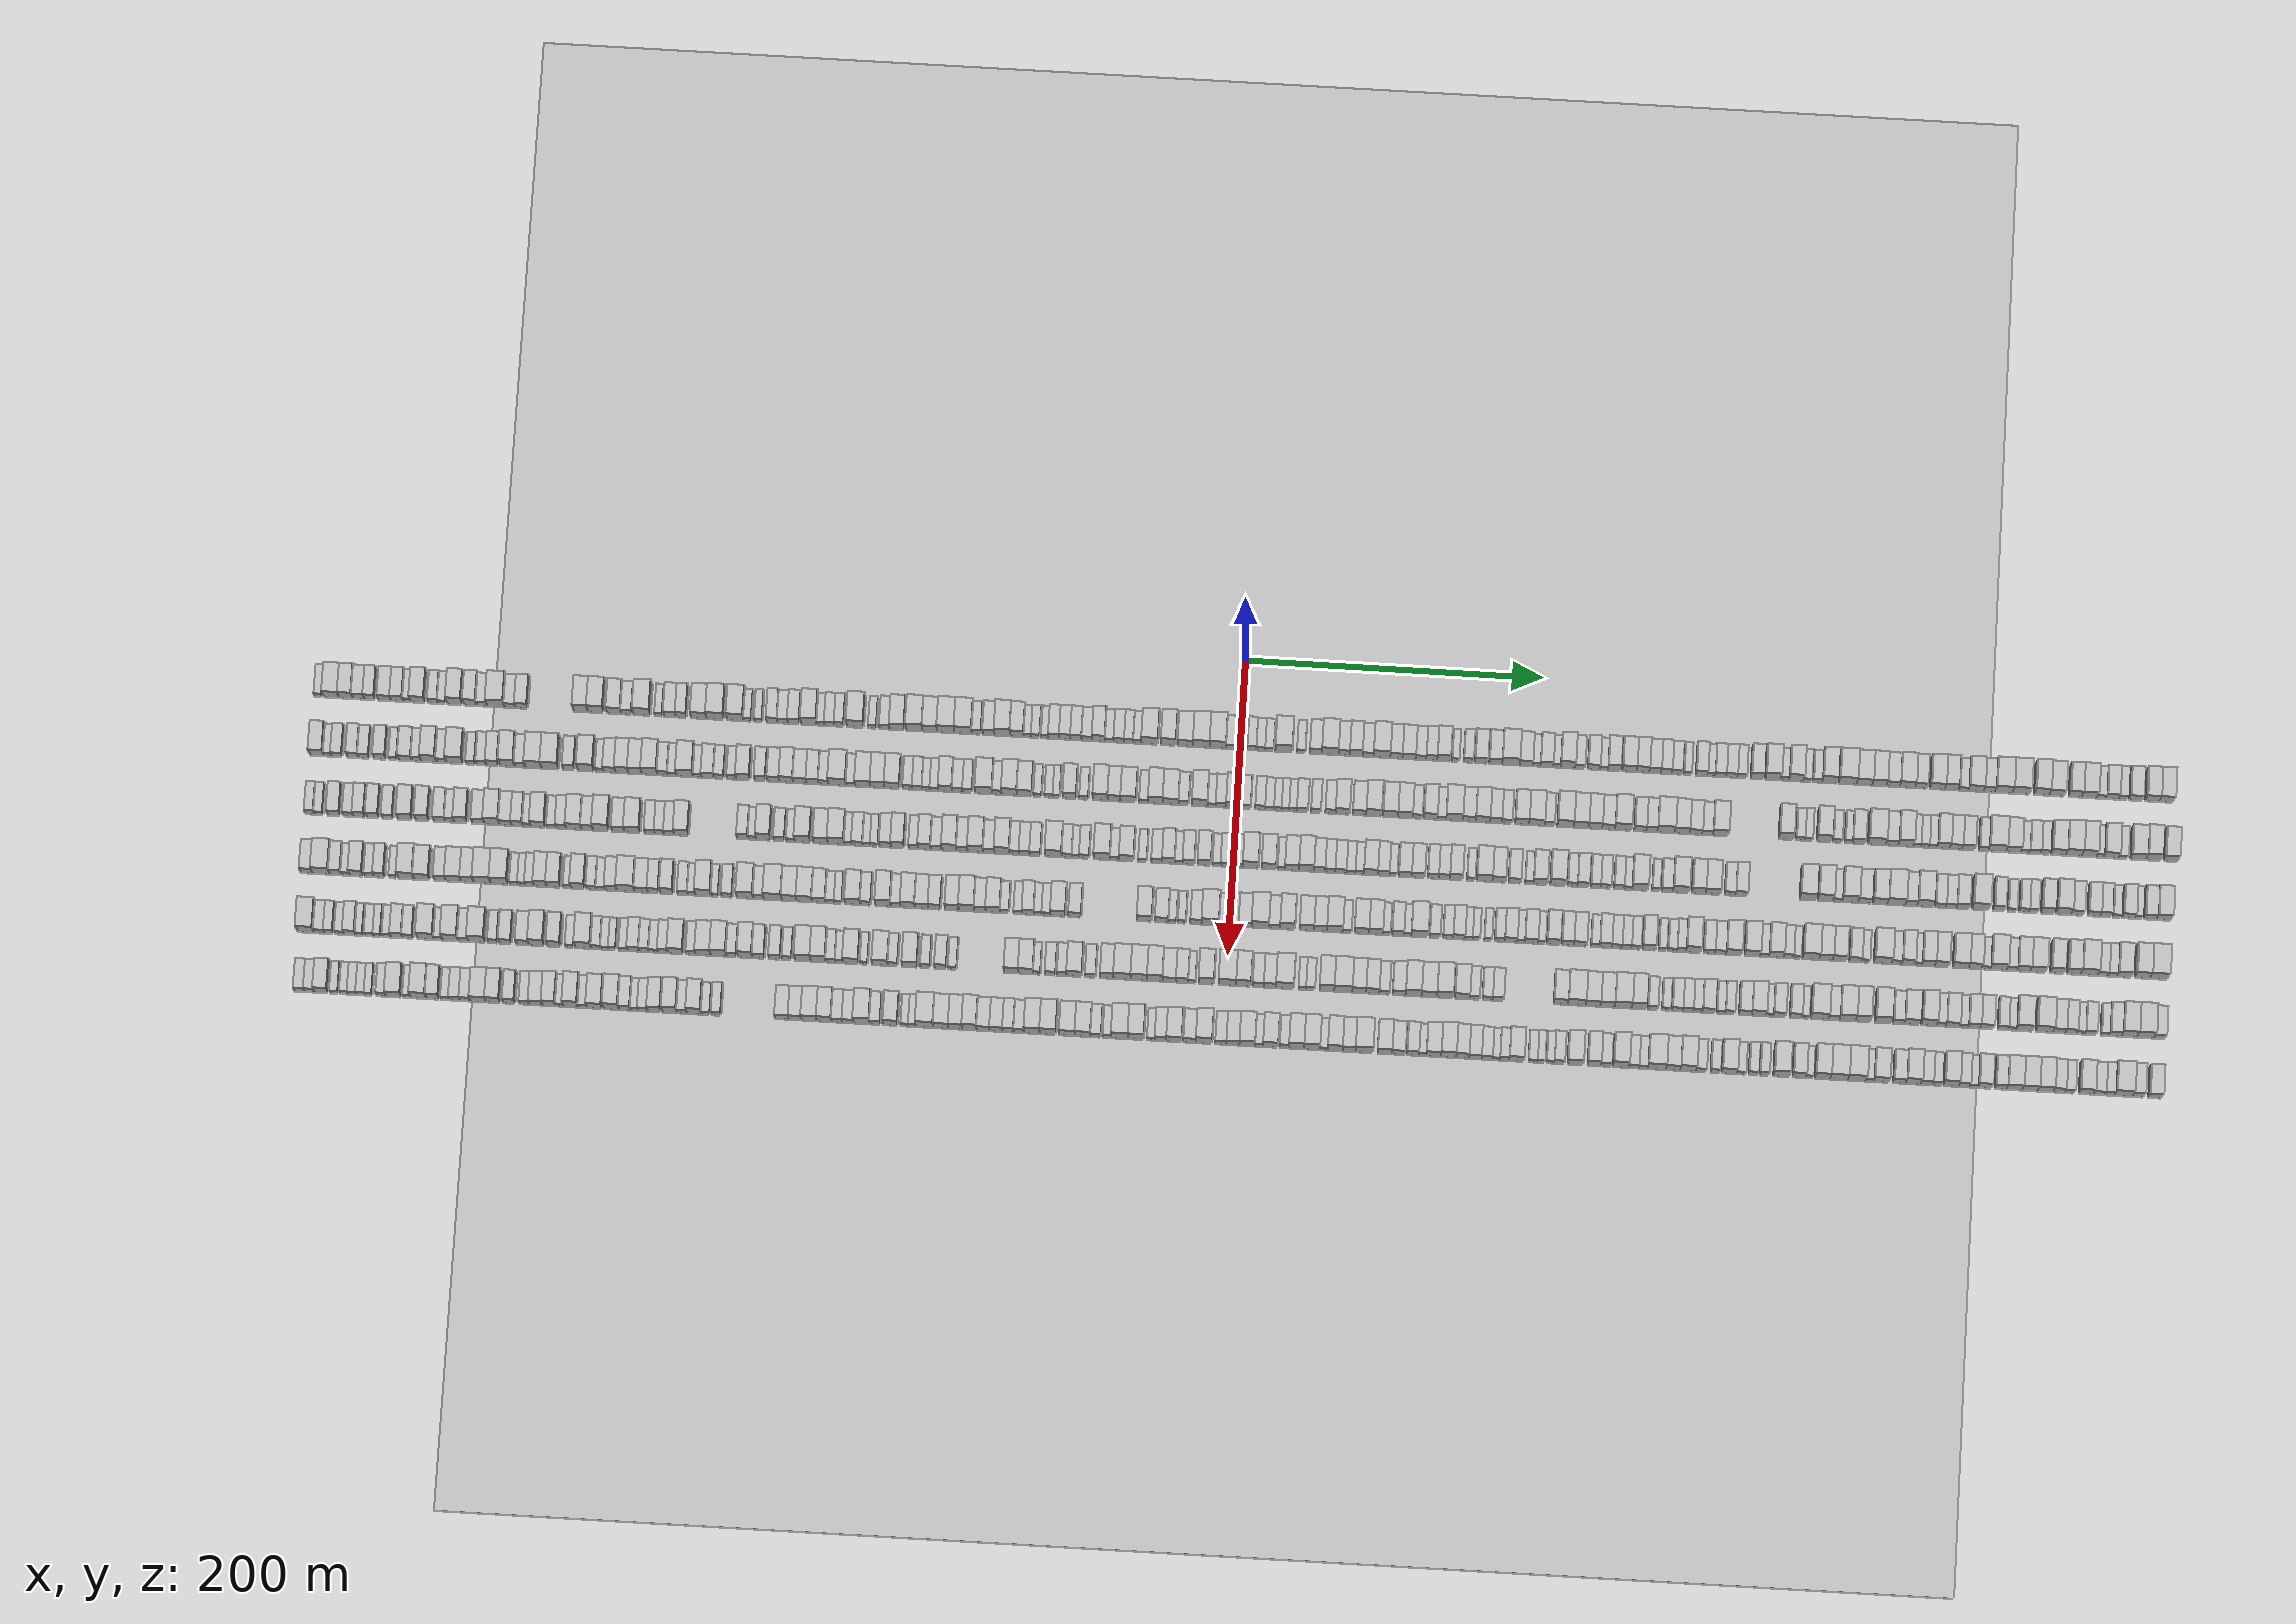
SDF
<?xml version="1.0" encoding="utf-8"?>

<sdf version="1.6">

   <world name="default">

      <gui fullscreen="0">

         <camera name="user_camera">

            <pose>-15 0 4.57585 0 0 0</pose>

            <view_controller>orbit</view_controller>

         </camera>

      </gui>

      <scene>

         <sky>

           <clouds>

             <speed>12</speed>

           </clouds>

         </sky>

         <ambient>0.4 0.4 0.4 1</ambient>

         <background>0.7 0.7 0.7 1</background>

         <shadows>1</shadows>

      </scene>

      <gravity>0 0 -9.8066</gravity>

      <magnetic_field>6e-06 2.3e-05 -4.2e-05</magnetic_field>

      <physics default="0" name="default_physics" type="ode">

         <ode>

            <solver>

               <type>quick</type>

               <iters>10</iters>

               <sor>1.0</sor>

               <use_dynamic_moi_rescaling>0</use_dynamic_moi_rescaling>

            </solver>

            <constraints>

               <cfm>0</cfm>

               <erp>0.2</erp>

               <contact_max_correcting_vel>100</contact_max_correcting_vel>

               <contact_surface_layer>0.001</contact_surface_layer>

            </constraints>

         </ode>

         <max_step_size>0.004</max_step_size>

         <real_time_factor>1</real_time_factor>

         <real_time_update_rate>250</real_time_update_rate>

      </physics>

      <light name="sun" type="directional">

         <cast_shadows>1</cast_shadows>

         <pose>0 0 10 0 0 0</pose>

         <diffuse>0.8 0.8 0.8 1</diffuse>

         <specular>0.2 0.2 0.2 1</specular>

         <attenuation>

            <range>1000</range>

            <constant>0.9</constant>

            <linear>0.01</linear>

            <quadratic>0.001</quadratic>

         </attenuation>

         <direction>-0.5 0.1 -0.9</direction>

      </light>

      <include>

         <name>ground_plane_1</name>

         <uri>model://HANNAS_ground_plane</uri>

         <pose>0 0 0  0 0 0</pose>

      </include>

      <include>

         <name>ground_plane_2</name>

         <uri>model://HANNAS_ground_plane</uri>

         <pose>100 0 0  0 0 0</pose>

      </include>

      <model name="building_1">

         <static>1</static>

         <pose frame="">50.0000 -617.5080 0 0.000000 0.000000 0.000000</pose>

         <link name="link">

            <pose frame="">0 0 6.00 0 0 0</pose>

            <collision name="collision">

               <geometry>

                  <box>

                     <size>20.0000 4.9839 12.0000</size>

                  </box>

               </geometry>

               <max_contacts>10</max_contacts>

               <surface>

                  <contact>

                     <ode/>

                  </contact>

                  <bounce/>

                  <friction>

                     <torsional>

                        <ode/>

                     </torsional>

                     <ode/>

                  </friction>

               </surface>

            </collision>

            <visual name="visual">

               <cast_shadows>0</cast_shadows>

               <geometry>

                  <box>

                     <size>20.0000 4.9839 12.0000</size>

                  </box>

               </geometry>

               <material>

                  <script>

                     <uri>model://HANNAS_wall/materials/scripts</uri>

                     <uri>model://HANNAS_wall/materials/textures</uri>

                     <name>vrc/HANNAS_wall</name>

                  </script>

               </material>

            </visual>

            <self_collide>0</self_collide>

            <enable_wind>0</enable_wind>

            <kinematic>0</kinematic>

         </link>

      </model>

      <model name="building_2">

         <static>1</static>

         <pose frame="">50.0000 -608.7805 0 0.000000 0.000000 0.000000</pose>

         <link name="link">

            <pose frame="">0 0 10.50 0 0 0</pose>

            <collision name="collision">

               <geometry>

                  <box>

                     <size>20.0000 10.4712 21.0000</size>

                  </box>

               </geometry>

               <max_contacts>10</max_contacts>

               <surface>

                  <contact>

                     <ode/>

                  </contact>

                  <bounce/>

                  <friction>

                     <torsional>

                        <ode/>

                     </torsional>

                     <ode/>

                  </friction>

               </surface>

            </collision>

            <visual name="visual">

               <cast_shadows>0</cast_shadows>

               <geometry>

                  <box>

                     <size>20.0000 10.4712 21.0000</size>

                  </box>

               </geometry>

               <material>

                  <script>

                     <uri>model://HANNAS_wall/materials/scripts</uri>

                     <uri>model://HANNAS_wall/materials/textures</uri>

                     <name>vrc/HANNAS_wall</name>

                  </script>

               </material>

            </visual>

            <self_collide>0</self_collide>

            <enable_wind>0</enable_wind>

            <kinematic>0</kinematic>

         </link>

      </model>

      <model name="building_3">

         <static>1</static>

         <pose frame="">50.0000 -599.0032 0 0.000000 0.000000 0.000000</pose>

         <link name="link">

            <pose frame="">0 0 10.50 0 0 0</pose>

            <collision name="collision">

               <geometry>

                  <box>

                     <size>20.0000 9.0833 21.0000</size>

                  </box>

               </geometry>

               <max_contacts>10</max_contacts>

               <surface>

                  <contact>

                     <ode/>

                  </contact>

                  <bounce/>

                  <friction>

                     <torsional>

                        <ode/>

                     </torsional>

                     <ode/>

                  </friction>

               </surface>

            </collision>

            <visual name="visual">

               <cast_shadows>0</cast_shadows>

               <geometry>

                  <box>

                     <size>20.0000 9.0833 21.0000</size>

                  </box>

               </geometry>

               <material>

                  <script>

                     <uri>model://HANNAS_wall/materials/scripts</uri>

                     <uri>model://HANNAS_wall/materials/textures</uri>

                     <name>vrc/HANNAS_wall</name>

                  </script>

               </material>

            </visual>

            <self_collide>0</self_collide>

            <enable_wind>0</enable_wind>

            <kinematic>0</kinematic>

         </link>

      </model>

      <model name="building_4">

         <static>1</static>

         <pose frame="">50.0000 -590.6134 0 0.000000 0.000000 0.000000</pose>

         <link name="link">

            <pose frame="">0 0 9.00 0 0 0</pose>

            <collision name="collision">

               <geometry>

                  <box>

                     <size>20.0000 7.6965 18.0000</size>

                  </box>

               </geometry>

               <max_contacts>10</max_contacts>

               <surface>

                  <contact>

                     <ode/>

                  </contact>

                  <bounce/>

                  <friction>

                     <torsional>

                        <ode/>

                     </torsional>

                     <ode/>

                  </friction>

               </surface>

            </collision>

            <visual name="visual">

               <cast_shadows>0</cast_shadows>

               <geometry>

                  <box>

                     <size>20.0000 7.6965 18.0000</size>

                  </box>

               </geometry>

               <material>

                  <script>

                     <uri>model://HANNAS_wall/materials/scripts</uri>

                     <uri>model://HANNAS_wall/materials/textures</uri>

                     <name>vrc/HANNAS_wall</name>

                  </script>

               </material>

            </visual>

            <self_collide>0</self_collide>

            <enable_wind>0</enable_wind>

            <kinematic>0</kinematic>

         </link>

      </model>

      <model name="building_5">

         <static>1</static>

         <pose frame="">50.0000 -583.0436 0 0.000000 0.000000 0.000000</pose>

         <link name="link">

            <pose frame="">0 0 9.00 0 0 0</pose>

            <collision name="collision">

               <geometry>

                  <box>

                     <size>20.0000 7.4431 18.0000</size>

                  </box>

               </geometry>

               <max_contacts>10</max_contacts>

               <surface>

                  <contact>

                     <ode/>

                  </contact>

                  <bounce/>

                  <friction>

                     <torsional>

                        <ode/>

                     </torsional>

                     <ode/>

                  </friction>

               </surface>

            </collision>

            <visual name="visual">

               <cast_shadows>0</cast_shadows>

               <geometry>

                  <box>

                     <size>20.0000 7.4431 18.0000</size>

                  </box>

               </geometry>

               <material>

                  <script>

                     <uri>model://HANNAS_wall/materials/scripts</uri>

                     <uri>model://HANNAS_wall/materials/textures</uri>

                     <name>vrc/HANNAS_wall</name>

                  </script>

               </material>

            </visual>

            <self_collide>0</self_collide>

            <enable_wind>0</enable_wind>

            <kinematic>0</kinematic>

         </link>

      </model>

      <model name="building_6">

         <static>1</static>

         <pose frame="">50.0000 -573.0656 0 0.000000 0.000000 0.000000</pose>

         <link name="link">

            <pose frame="">0 0 9.00 0 0 0</pose>

            <collision name="collision">

               <geometry>

                  <box>

                     <size>20.0000 8.5128 18.0000</size>

                  </box>

               </geometry>

               <max_contacts>10</max_contacts>

               <surface>

                  <contact>

                     <ode/>

                  </contact>

                  <bounce/>

                  <friction>

                     <torsional>

                        <ode/>

                     </torsional>

                     <ode/>

                  </friction>

               </surface>

            </collision>

            <visual name="visual">

               <cast_shadows>0</cast_shadows>

               <geometry>

                  <box>

                     <size>20.0000 8.5128 18.0000</size>

                  </box>

               </geometry>

               <material>

                  <script>

                     <uri>model://HANNAS_wall/materials/scripts</uri>

                     <uri>model://HANNAS_wall/materials/textures</uri>

                     <name>vrc/HANNAS_wall</name>

                  </script>

               </material>

            </visual>

            <self_collide>0</self_collide>

            <enable_wind>0</enable_wind>

            <kinematic>0</kinematic>

         </link>

      </model>

      <model name="building_7">

         <static>1</static>

         <pose frame="">50.0000 -564.7174 0 0.000000 0.000000 0.000000</pose>

         <link name="link">

            <pose frame="">0 0 9.00 0 0 0</pose>

            <collision name="collision">

               <geometry>

                  <box>

                     <size>20.0000 8.1836 18.0000</size>

                  </box>

               </geometry>

               <max_contacts>10</max_contacts>

               <surface>

                  <contact>

                     <ode/>

                  </contact>

                  <bounce/>

                  <friction>

                     <torsional>

                        <ode/>

                     </torsional>

                     <ode/>

                  </friction>

               </surface>

            </collision>

            <visual name="visual">

               <cast_shadows>0</cast_shadows>

               <geometry>

                  <box>

                     <size>20.0000 8.1836 18.0000</size>

                  </box>

               </geometry>

               <material>

                  <script>

                     <uri>model://HANNAS_wall/materials/scripts</uri>

                     <uri>model://HANNAS_wall/materials/textures</uri>

                     <name>vrc/HANNAS_wall</name>

                  </script>

               </material>

            </visual>

            <self_collide>0</self_collide>

            <enable_wind>0</enable_wind>

            <kinematic>0</kinematic>

         </link>

      </model>

      <model name="building_8">

         <static>1</static>

         <pose frame="">50.0000 -558.2069 0 0.000000 0.000000 0.000000</pose>

         <link name="link">

            <pose frame="">0 0 6.00 0 0 0</pose>

            <collision name="collision">

               <geometry>

                  <box>

                     <size>20.0000 4.8373 12.0000</size>

                  </box>

               </geometry>

               <max_contacts>10</max_contacts>

               <surface>

                  <contact>

                     <ode/>

                  </contact>

                  <bounce/>

                  <friction>

                     <torsional>

                        <ode/>

                     </torsional>

                     <ode/>

                  </friction>

               </surface>

            </collision>

            <visual name="visual">

               <cast_shadows>0</cast_shadows>

               <geometry>

                  <box>

                     <size>20.0000 4.8373 12.0000</size>

                  </box>

               </geometry>

               <material>

                  <script>

                     <uri>model://HANNAS_wall/materials/scripts</uri>

                     <uri>model://HANNAS_wall/materials/textures</uri>

                     <name>vrc/HANNAS_wall</name>

                  </script>

               </material>

            </visual>

            <self_collide>0</self_collide>

            <enable_wind>0</enable_wind>

            <kinematic>0</kinematic>

         </link>

      </model>

      <model name="building_9">

         <static>1</static>

         <pose frame="">50.0000 -550.8138 0 0.000000 0.000000 0.000000</pose>

         <link name="link">

            <pose frame="">0 0 10.50 0 0 0</pose>

            <collision name="collision">

               <geometry>

                  <box>

                     <size>20.0000 9.9490 21.0000</size>

                  </box>

               </geometry>

               <max_contacts>10</max_contacts>

               <surface>

                  <contact>

                     <ode/>

                  </contact>

                  <bounce/>

                  <friction>

                     <torsional>

                        <ode/>

                     </torsional>

                     <ode/>

                  </friction>

               </surface>

            </collision>

            <visual name="visual">

               <cast_shadows>0</cast_shadows>

               <geometry>

                  <box>

                     <size>20.0000 9.9490 21.0000</size>

                  </box>

               </geometry>

               <material>

                  <script>

                     <uri>model://HANNAS_wall/materials/scripts</uri>

                     <uri>model://HANNAS_wall/materials/textures</uri>

                     <name>vrc/HANNAS_wall</name>

                  </script>

               </material>

            </visual>

            <self_collide>0</self_collide>

            <enable_wind>0</enable_wind>

            <kinematic>0</kinematic>

         </link>

      </model>

      <model name="building_10">

         <static>1</static>

         <pose frame="">50.0000 -540.6027 0 0.000000 0.000000 0.000000</pose>

         <link name="link">

            <pose frame="">0 0 7.50 0 0 0</pose>

            <collision name="collision">

               <geometry>

                  <box>

                     <size>20.0000 6.4732 15.0000</size>

                  </box>

               </geometry>

               <max_contacts>10</max_contacts>

               <surface>

                  <contact>

                     <ode/>

                  </contact>

                  <bounce/>

                  <friction>

                     <torsional>

                        <ode/>

                     </torsional>

                     <ode/>

                  </friction>

               </surface>

            </collision>

            <visual name="visual">

               <cast_shadows>0</cast_shadows>

               <geometry>

                  <box>

                     <size>20.0000 6.4732 15.0000</size>

                  </box>

               </geometry>

               <material>

                  <script>

                     <uri>model://HANNAS_wall/materials/scripts</uri>

                     <uri>model://HANNAS_wall/materials/textures</uri>

                     <name>vrc/HANNAS_wall</name>

                  </script>

               </material>

            </visual>

            <self_collide>0</self_collide>

            <enable_wind>0</enable_wind>

            <kinematic>0</kinematic>

         </link>

      </model>

      <model name="building_11">

         <static>1</static>

         <pose frame="">50.0000 -534.7439 0 0.000000 0.000000 0.000000</pose>

         <link name="link">

            <pose frame="">0 0 6.00 0 0 0</pose>

            <collision name="collision">

               <geometry>

                  <box>

                     <size>20.0000 5.2442 12.0000</size>

                  </box>

               </geometry>

               <max_contacts>10</max_contacts>

               <surface>

                  <contact>

                     <ode/>

                  </contact>

                  <bounce/>

                  <friction>

                     <torsional>

                        <ode/>

                     </torsional>

                     <ode/>

                  </friction>

               </surface>

            </collision>

            <visual name="visual">

               <cast_shadows>0</cast_shadows>

               <geometry>

                  <box>

                     <size>20.0000 5.2442 12.0000</size>

                  </box>

               </geometry>

               <material>

                  <script>

                     <uri>model://HANNAS_wall/materials/scripts</uri>

                     <uri>model://HANNAS_wall/materials/textures</uri>

                     <name>vrc/HANNAS_wall</name>

                  </script>

               </material>

            </visual>

            <self_collide>0</self_collide>

            <enable_wind>0</enable_wind>

            <kinematic>0</kinematic>

         </link>

      </model>

      <model name="building_12">

         <static>1</static>

         <pose frame="">50.0000 -526.0318 0 0.000000 0.000000 0.000000</pose>

         <link name="link">

            <pose frame="">0 0 12.00 0 0 0</pose>

            <collision name="collision">

               <geometry>

                  <box>

                     <size>20.0000 10.1800 24.0000</size>

                  </box>

               </geometry>

               <max_contacts>10</max_contacts>

               <surface>

                  <contact>

                     <ode/>

                  </contact>

                  <bounce/>

                  <friction>

                     <torsional>

                        <ode/>

                     </torsional>

                     <ode/>

                  </friction>

               </surface>

            </collision>

            <visual name="visual">

               <cast_shadows>0</cast_shadows>

               <geometry>

                  <box>

                     <size>20.0000 10.1800 24.0000</size>

                  </box>

               </geometry>

               <material>

                  <script>

                     <uri>model://HANNAS_wall/materials/scripts</uri>

                     <uri>model://HANNAS_wall/materials/textures</uri>

                     <name>vrc/HANNAS_wall</name>

                  </script>

               </material>

            </visual>

            <self_collide>0</self_collide>

            <enable_wind>0</enable_wind>

            <kinematic>0</kinematic>

         </link>

      </model>

      <model name="building_13">

         <static>1</static>

         <pose frame="">50.0000 -515.6574 0 0.000000 0.000000 0.000000</pose>

         <link name="link">

            <pose frame="">0 0 10.50 0 0 0</pose>

            <collision name="collision">

               <geometry>

                  <box>

                     <size>20.0000 8.5687 21.0000</size>

                  </box>

               </geometry>

               <max_contacts>10</max_contacts>

               <surface>

                  <contact>

                     <ode/>

                  </contact>

                  <bounce/>

                  <friction>

                     <torsional>

                        <ode/>

                     </torsional>

                     <ode/>

                  </friction>

               </surface>

            </collision>

            <visual name="visual">

               <cast_shadows>0</cast_shadows>

               <geometry>

                  <box>

                     <size>20.0000 8.5687 21.0000</size>

                  </box>

               </geometry>

               <material>

                  <script>

                     <uri>model://HANNAS_wall/materials/scripts</uri>

                     <uri>model://HANNAS_wall/materials/textures</uri>

                     <name>vrc/HANNAS_wall</name>

                  </script>

               </material>

            </visual>

            <self_collide>0</self_collide>

            <enable_wind>0</enable_wind>

            <kinematic>0</kinematic>

         </link>

      </model>

      <model name="building_14">

         <static>1</static>

         <pose frame="">50.0000 -507.9430 0 0.000000 0.000000 0.000000</pose>

         <link name="link">

            <pose frame="">0 0 7.50 0 0 0</pose>

            <collision name="collision">

               <geometry>

                  <box>

                     <size>20.0000 6.8602 15.0000</size>

                  </box>

               </geometry>

               <max_contacts>10</max_contacts>

               <surface>

                  <contact>

                     <ode/>

                  </contact>

                  <bounce/>

                  <friction>

                     <torsional>

                        <ode/>

                     </torsional>

                     <ode/>

                  </friction>

               </surface>

            </collision>

            <visual name="visual">

               <cast_shadows>0</cast_shadows>

               <geometry>

                  <box>

                     <size>20.0000 6.8602 15.0000</size>

                  </box>

               </geometry>

               <material>

                  <script>

                     <uri>model://HANNAS_wall/materials/scripts</uri>

                     <uri>model://HANNAS_wall/materials/textures</uri>

                     <name>vrc/HANNAS_wall</name>

                  </script>

               </material>

            </visual>

            <self_collide>0</self_collide>

            <enable_wind>0</enable_wind>

            <kinematic>0</kinematic>

         </link>

      </model>

      <model name="building_15">

         <static>1</static>

         <pose frame="">50.0000 -498.6184 0 0.000000 0.000000 0.000000</pose>

         <link name="link">

            <pose frame="">0 0 12.00 0 0 0</pose>

            <collision name="collision">

               <geometry>

                  <box>

                     <size>20.0000 11.7889 24.0000</size>

                  </box>

               </geometry>

               <max_contacts>10</max_contacts>

               <surface>

                  <contact>

                     <ode/>

                  </contact>

                  <bounce/>

                  <friction>

                     <torsional>

                        <ode/>

                     </torsional>

                     <ode/>

                  </friction>

               </surface>

            </collision>

            <visual name="visual">

               <cast_shadows>0</cast_shadows>

               <geometry>

                  <box>

                     <size>20.0000 11.7889 24.0000</size>

                  </box>

               </geometry>

               <material>

                  <script>

                     <uri>model://HANNAS_wall/materials/scripts</uri>

                     <uri>model://HANNAS_wall/materials/textures</uri>

                     <name>vrc/HANNAS_wall</name>

                  </script>

               </material>

            </visual>

            <self_collide>0</self_collide>

            <enable_wind>0</enable_wind>

            <kinematic>0</kinematic>

         </link>

      </model>

      <model name="building_16">

         <static>1</static>

         <pose frame="">50.0000 -489.0953 0 0.000000 0.000000 0.000000</pose>

         <link name="link">

            <pose frame="">0 0 7.50 0 0 0</pose>

            <collision name="collision">

               <geometry>

                  <box>

                     <size>20.0000 7.2573 15.0000</size>

                  </box>

               </geometry>

               <max_contacts>10</max_contacts>

               <surface>

                  <contact>

                     <ode/>

                  </contact>

                  <bounce/>

                  <friction>

                     <torsional>

                        <ode/>

                     </torsional>

                     <ode/>

                  </friction>

               </surface>

            </collision>

            <visual name="visual">

               <cast_shadows>0</cast_shadows>

               <geometry>

                  <box>

                     <size>20.0000 7.2573 15.0000</size>

                  </box>

               </geometry>

               <material>

                  <script>

                     <uri>model://HANNAS_wall/materials/scripts</uri>

                     <uri>model://HANNAS_wall/materials/textures</uri>

                     <name>vrc/HANNAS_wall</name>

                  </script>

               </material>

            </visual>

            <self_collide>0</self_collide>

            <enable_wind>0</enable_wind>

            <kinematic>0</kinematic>

         </link>

      </model>

      <model name="building_17">

         <static>1</static>

         <pose frame="">50.0000 -481.3041 0 0.000000 0.000000 0.000000</pose>

         <link name="link">

            <pose frame="">0 0 9.00 0 0 0</pose>

            <collision name="collision">

               <geometry>

                  <box>

                     <size>20.0000 8.3250 18.0000</size>

                  </box>

               </geometry>

               <max_contacts>10</max_contacts>

               <surface>

                  <contact>

                     <ode/>

                  </contact>

                  <bounce/>

                  <friction>

                     <torsional>

                        <ode/>

                     </torsional>

                     <ode/>

                  </friction>

               </surface>

            </collision>

            <visual name="visual">

               <cast_shadows>0</cast_shadows>

               <geometry>

                  <box>

                     <size>20.0000 8.3250 18.0000</size>

                  </box>

               </geometry>

               <material>

                  <script>

                     <uri>model://HANNAS_wall/materials/scripts</uri>

                     <uri>model://HANNAS_wall/materials/textures</uri>

                     <name>vrc/HANNAS_wall</name>

                  </script>

               </material>

            </visual>

            <self_collide>0</self_collide>

            <enable_wind>0</enable_wind>

            <kinematic>0</kinematic>

         </link>

      </model>

      <model name="building_18">

         <static>1</static>

         <pose frame="">50.0000 -441.7151 0 0.000000 0.000000 0.000000</pose>

         <link name="link">

            <pose frame="">0 0 12.00 0 0 0</pose>

            <collision name="collision">

               <geometry>

                  <box>

                     <size>20.0000 9.6177 24.0000</size>

                  </box>

               </geometry>

               <max_contacts>10</max_contacts>

               <surface>

                  <contact>

                     <ode/>

                  </contact>

                  <bounce/>

                  <friction>

                     <torsional>

                        <ode/>

                     </torsional>

                     <ode/>

                  </friction>

               </surface>

            </collision>

            <visual name="visual">

               <cast_shadows>0</cast_shadows>

               <geometry>

                  <box>

                     <size>20.0000 9.6177 24.0000</size>

                  </box>

               </geometry>

               <material>

                  <script>

                     <uri>model://HANNAS_wall/materials/scripts</uri>

                     <uri>model://HANNAS_wall/materials/textures</uri>

                     <name>vrc/HANNAS_wall</name>

                  </script>

               </material>

            </visual>

            <self_collide>0</self_collide>

            <enable_wind>0</enable_wind>

            <kinematic>0</kinematic>

         </link>

      </model>

      <model name="building_19">

         <static>1</static>

         <pose frame="">50.0000 -431.5230 0 0.000000 0.000000 0.000000</pose>

         <link name="link">

            <pose frame="">0 0 12.00 0 0 0</pose>

            <collision name="collision">

               <geometry>

                  <box>

                     <size>20.0000 10.7665 24.0000</size>

                  </box>

               </geometry>

               <max_contacts>10</max_contacts>

               <surface>

                  <contact>

                     <ode/>

                  </contact>

                  <bounce/>

                  <friction>

                     <torsional>

                        <ode/>

                     </torsional>

                     <ode/>

                  </friction>

               </surface>

            </collision>

            <visual name="visual">

               <cast_shadows>0</cast_shadows>

               <geometry>

                  <box>

                     <size>20.0000 10.7665 24.0000</size>

                  </box>

               </geometry>

               <material>

                  <script>

                     <uri>model://HANNAS_wall/materials/scripts</uri>

                     <uri>model://HANNAS_wall/materials/textures</uri>

                     <name>vrc/HANNAS_wall</name>

                  </script>

               </material>

            </visual>

            <self_collide>0</self_collide>

            <enable_wind>0</enable_wind>

            <kinematic>0</kinematic>

         </link>

      </model>

      <model name="building_20">

         <static>1</static>

         <pose frame="">50.0000 -419.3856 0 0.000000 0.000000 0.000000</pose>

         <link name="link">

            <pose frame="">0 0 10.50 0 0 0</pose>

            <collision name="collision">

               <geometry>

                  <box>

                     <size>20.0000 9.5082 21.0000</size>

                  </box>

               </geometry>

               <max_contacts>10</max_contacts>

               <surface>

                  <contact>

                     <ode/>

                  </contact>

                  <bounce/>

                  <friction>

                     <torsional>

                        <ode/>

                     </torsional>

                     <ode/>

                  </friction>

               </surface>

            </collision>

            <visual name="visual">

               <cast_shadows>0</cast_shadows>

               <geometry>

                  <box>

                     <size>20.0000 9.5082 21.0000</size>

                  </box>

               </geometry>

               <material>

                  <script>

                     <uri>model://HANNAS_wall/materials/scripts</uri>

                     <uri>model://HANNAS_wall/materials/textures</uri>

                     <name>vrc/HANNAS_wall</name>

                  </script>

               </material>

            </visual>

            <self_collide>0</self_collide>

            <enable_wind>0</enable_wind>

            <kinematic>0</kinematic>

         </link>

      </model>

      <model name="building_21">

         <static>1</static>

         <pose frame="">50.0000 -411.0206 0 0.000000 0.000000 0.000000</pose>

         <link name="link">

            <pose frame="">0 0 7.50 0 0 0</pose>

            <collision name="collision">

               <geometry>

                  <box>

                     <size>20.0000 7.2218 15.0000</size>

                  </box>

               </geometry>

               <max_contacts>10</max_contacts>

               <surface>

                  <contact>

                     <ode/>

                  </contact>

                  <bounce/>

                  <friction>

                     <torsional>

                        <ode/>

                     </torsional>

                     <ode/>

                  </friction>

               </surface>

            </collision>

            <visual name="visual">

               <cast_shadows>0</cast_shadows>

               <geometry>

                  <box>

                     <size>20.0000 7.2218 15.0000</size>

                  </box>

               </geometry>

               <material>

                  <script>

                     <uri>model://HANNAS_wall/materials/scripts</uri>

                     <uri>model://HANNAS_wall/materials/textures</uri>

                     <name>vrc/HANNAS_wall</name>

                  </script>

               </material>

            </visual>

            <self_collide>0</self_collide>

            <enable_wind>0</enable_wind>

            <kinematic>0</kinematic>

         </link>

      </model>

      <model name="building_22">

         <static>1</static>

         <pose frame="">50.0000 -400.7315 0 0.000000 0.000000 0.000000</pose>

         <link name="link">

            <pose frame="">0 0 12.00 0 0 0</pose>

            <collision name="collision">

               <geometry>

                  <box>

                     <size>20.0000 11.3565 24.0000</size>

                  </box>

               </geometry>

               <max_contacts>10</max_contacts>

               <surface>

                  <contact>

                     <ode/>

                  </contact>

                  <bounce/>

                  <friction>

                     <torsional>

                        <ode/>

                     </torsional>

                     <ode/>

                  </friction>

               </surface>

            </collision>

            <visual name="visual">

               <cast_shadows>0</cast_shadows>

               <geometry>

                  <box>

                     <size>20.0000 11.3565 24.0000</size>

                  </box>

               </geometry>

               <material>

                  <script>

                     <uri>model://HANNAS_wall/materials/scripts</uri>

                     <uri>model://HANNAS_wall/materials/textures</uri>

                     <name>vrc/HANNAS_wall</name>

                  </script>

               </material>

            </visual>

            <self_collide>0</self_collide>

            <enable_wind>0</enable_wind>

            <kinematic>0</kinematic>

         </link>

      </model>

      <model name="building_23">

         <static>1</static>

         <pose frame="">50.0000 -389.5145 0 0.000000 0.000000 0.000000</pose>

         <link name="link">

            <pose frame="">0 0 6.00 0 0 0</pose>

            <collision name="collision">

               <geometry>

                  <box>

                     <size>20.0000 5.0775 12.0000</size>

                  </box>

               </geometry>

               <max_contacts>10</max_contacts>

               <surface>

                  <contact>

                     <ode/>

                  </contact>

                  <bounce/>

                  <friction>

                     <torsional>

                        <ode/>

                     </torsional>

                     <ode/>

                  </friction>

               </surface>

            </collision>

            <visual name="visual">

               <cast_shadows>0</cast_shadows>

               <geometry>

                  <box>

                     <size>20.0000 5.0775 12.0000</size>

                  </box>

               </geometry>

               <material>

                  <script>

                     <uri>model://HANNAS_wall/materials/scripts</uri>

                     <uri>model://HANNAS_wall/materials/textures</uri>

                     <name>vrc/HANNAS_wall</name>

                  </script>

               </material>

            </visual>

            <self_collide>0</self_collide>

            <enable_wind>0</enable_wind>

            <kinematic>0</kinematic>

         </link>

      </model>

      <model name="building_24">

         <static>1</static>

         <pose frame="">50.0000 -382.0043 0 0.000000 0.000000 0.000000</pose>

         <link name="link">

            <pose frame="">0 0 9.00 0 0 0</pose>

            <collision name="collision">

               <geometry>

                  <box>

                     <size>20.0000 7.9430 18.0000</size>

                  </box>

               </geometry>

               <max_contacts>10</max_contacts>

               <surface>

                  <contact>

                     <ode/>

                  </contact>

                  <bounce/>

                  <friction>

                     <torsional>

                        <ode/>

                     </torsional>

                     <ode/>

                  </friction>

               </surface>

            </collision>

            <visual name="visual">

               <cast_shadows>0</cast_shadows>

               <geometry>

                  <box>

                     <size>20.0000 7.9430 18.0000</size>

                  </box>

               </geometry>

               <material>

                  <script>

                     <uri>model://HANNAS_wall/materials/scripts</uri>

                     <uri>model://HANNAS_wall/materials/textures</uri>

                     <name>vrc/HANNAS_wall</name>

                  </script>

               </material>

            </visual>

            <self_collide>0</self_collide>

            <enable_wind>0</enable_wind>

            <kinematic>0</kinematic>

         </link>

      </model>

      <model name="building_25">

         <static>1</static>

         <pose frame="">50.0000 -374.4099 0 0.000000 0.000000 0.000000</pose>

         <link name="link">

            <pose frame="">0 0 9.00 0 0 0</pose>

            <collision name="collision">

               <geometry>

                  <box>

                     <size>20.0000 7.2458 18.0000</size>

                  </box>

               </geometry>

               <max_contacts>10</max_contacts>

               <surface>

                  <contact>

                     <ode/>

                  </contact>

                  <bounce/>

                  <friction>

                     <torsional>

                        <ode/>

                     </torsional>

                     <ode/>

                  </friction>

               </surface>

            </collision>

            <visual name="visual">

               <cast_shadows>0</cast_shadows>

               <geometry>

                  <box>

                     <size>20.0000 7.2458 18.0000</size>

                  </box>

               </geometry>

               <material>

                  <script>

                     <uri>model://HANNAS_wall/materials/scripts</uri>

                     <uri>model://HANNAS_wall/materials/textures</uri>

                     <name>vrc/HANNAS_wall</name>

                  </script>

               </material>

            </visual>

            <self_collide>0</self_collide>

            <enable_wind>0</enable_wind>

            <kinematic>0</kinematic>

         </link>

      </model>

      <model name="building_26">

         <static>1</static>

         <pose frame="">50.0000 -362.6268 0 0.000000 0.000000 0.000000</pose>

         <link name="link">

            <pose frame="">0 0 10.50 0 0 0</pose>

            <collision name="collision">

               <geometry>

                  <box>

                     <size>20.0000 10.3205 21.0000</size>

                  </box>

               </geometry>

               <max_contacts>10</max_contacts>

               <surface>

                  <contact>

                     <ode/>

                  </contact>

                  <bounce/>

                  <friction>

                     <torsional>

                        <ode/>

                     </torsional>

                     <ode/>

                  </friction>

               </surface>

            </collision>

            <visual name="visual">

               <cast_shadows>0</cast_shadows>

               <geometry>

                  <box>

                     <size>20.0000 10.3205 21.0000</size>

                  </box>

               </geometry>

               <material>

                  <script>

                     <uri>model://HANNAS_wall/materials/scripts</uri>

                     <uri>model://HANNAS_wall/materials/textures</uri>

                     <name>vrc/HANNAS_wall</name>

                  </script>

               </material>

            </visual>

            <self_collide>0</self_collide>

            <enable_wind>0</enable_wind>

            <kinematic>0</kinematic>

         </link>

      </model>

      <model name="building_27">

         <static>1</static>

         <pose frame="">50.0000 -351.6223 0 0.000000 0.000000 0.000000</pose>

         <link name="link">

            <pose frame="">0 0 12.00 0 0 0</pose>

            <collision name="collision">

               <geometry>

                  <box>

                     <size>20.0000 11.6884 24.0000</size>

                  </box>

               </geometry>

               <max_contacts>10</max_contacts>

               <surface>

                  <contact>

                     <ode/>

                  </contact>

                  <bounce/>

                  <friction>

                     <torsional>

                        <ode/>

                     </torsional>

                     <ode/>

                  </friction>

               </surface>

            </collision>

            <visual name="visual">

               <cast_shadows>0</cast_shadows>

               <geometry>

                  <box>

                     <size>20.0000 11.6884 24.0000</size>

                  </box>

               </geometry>

               <material>

                  <script>

                     <uri>model://HANNAS_wall/materials/scripts</uri>

                     <uri>model://HANNAS_wall/materials/textures</uri>

                     <name>vrc/HANNAS_wall</name>

                  </script>

               </material>

            </visual>

            <self_collide>0</self_collide>

            <enable_wind>0</enable_wind>

            <kinematic>0</kinematic>

         </link>

      </model>

      <model name="building_28">

         <static>1</static>

         <pose frame="">50.0000 -338.2226 0 0.000000 0.000000 0.000000</pose>

         <link name="link">

            <pose frame="">0 0 12.00 0 0 0</pose>

            <collision name="collision">

               <geometry>

                  <box>

                     <size>20.0000 11.1111 24.0000</size>

                  </box>

               </geometry>

               <max_contacts>10</max_contacts>

               <surface>

                  <contact>

                     <ode/>

                  </contact>

                  <bounce/>

                  <friction>

                     <torsional>

                        <ode/>

                     </torsional>

                     <ode/>

                  </friction>

               </surface>

            </collision>

            <visual name="visual">

               <cast_shadows>0</cast_shadows>

               <geometry>

                  <box>

                     <size>20.0000 11.1111 24.0000</size>

                  </box>

               </geometry>

               <material>

                  <script>

                     <uri>model://HANNAS_wall/materials/scripts</uri>

                     <uri>model://HANNAS_wall/materials/textures</uri>

                     <name>vrc/HANNAS_wall</name>

                  </script>

               </material>

            </visual>

            <self_collide>0</self_collide>

            <enable_wind>0</enable_wind>

            <kinematic>0</kinematic>

         </link>

      </model>

      <model name="building_29">

         <static>1</static>

         <pose frame="">50.0000 -330.0581 0 0.000000 0.000000 0.000000</pose>

         <link name="link">

            <pose frame="">0 0 6.00 0 0 0</pose>

            <collision name="collision">

               <geometry>

                  <box>

                     <size>20.0000 5.2180 12.0000</size>

                  </box>

               </geometry>

               <max_contacts>10</max_contacts>

               <surface>

                  <contact>

                     <ode/>

                  </contact>

                  <bounce/>

                  <friction>

                     <torsional>

                        <ode/>

                     </torsional>

                     <ode/>

                  </friction>

               </surface>

            </collision>

            <visual name="visual">

               <cast_shadows>0</cast_shadows>

               <geometry>

                  <box>

                     <size>20.0000 5.2180 12.0000</size>

                  </box>

               </geometry>

               <material>

                  <script>

                     <uri>model://HANNAS_wall/materials/scripts</uri>

                     <uri>model://HANNAS_wall/materials/textures</uri>

                     <name>vrc/HANNAS_wall</name>

                  </script>

               </material>

            </visual>

            <self_collide>0</self_collide>

            <enable_wind>0</enable_wind>

            <kinematic>0</kinematic>

         </link>

      </model>

      <model name="building_30">

         <static>1</static>

         <pose frame="">50.0000 -322.8479 0 0.000000 0.000000 0.000000</pose>

         <link name="link">

            <pose frame="">0 0 6.00 0 0 0</pose>

            <collision name="collision">

               <geometry>

                  <box>

                     <size>20.0000 5.2024 12.0000</size>

                  </box>

               </geometry>

               <max_contacts>10</max_contacts>

               <surface>

                  <contact>

                     <ode/>

                  </contact>

                  <bounce/>

                  <friction>

                     <torsional>

                        <ode/>

                     </torsional>

                     <ode/>

                  </friction>

               </surface>

            </collision>

            <visual name="visual">

               <cast_shadows>0</cast_shadows>

               <geometry>

                  <box>

                     <size>20.0000 5.2024 12.0000</size>

                  </box>

               </geometry>

               <material>

                  <script>

                     <uri>model://HANNAS_wall/materials/scripts</uri>

                     <uri>model://HANNAS_wall/materials/textures</uri>

                     <name>vrc/HANNAS_wall</name>

                  </script>

               </material>

            </visual>

            <self_collide>0</self_collide>

            <enable_wind>0</enable_wind>

            <kinematic>0</kinematic>

         </link>

      </model>

      <model name="building_31">

         <static>1</static>

         <pose frame="">50.0000 -313.6029 0 0.000000 0.000000 0.000000</pose>

         <link name="link">

            <pose frame="">0 0 9.00 0 0 0</pose>

            <collision name="collision">

               <geometry>

                  <box>

                     <size>20.0000 7.2876 18.0000</size>

                  </box>

               </geometry>

               <max_contacts>10</max_contacts>

               <surface>

                  <contact>

                     <ode/>

                  </contact>

                  <bounce/>

                  <friction>

                     <torsional>

                        <ode/>

                     </torsional>

                     <ode/>

                  </friction>

               </surface>

            </collision>

            <visual name="visual">

               <cast_shadows>0</cast_shadows>

               <geometry>

                  <box>

                     <size>20.0000 7.2876 18.0000</size>

                  </box>

               </geometry>

               <material>

                  <script>

                     <uri>model://HANNAS_wall/materials/scripts</uri>

                     <uri>model://HANNAS_wall/materials/textures</uri>

                     <name>vrc/HANNAS_wall</name>

                  </script>

               </material>

            </visual>

            <self_collide>0</self_collide>

            <enable_wind>0</enable_wind>

            <kinematic>0</kinematic>

         </link>

      </model>

      <model name="building_32">

         <static>1</static>

         <pose frame="">50.0000 -306.5154 0 0.000000 0.000000 0.000000</pose>

         <link name="link">

            <pose frame="">0 0 7.50 0 0 0</pose>

            <collision name="collision">

               <geometry>

                  <box>

                     <size>20.0000 6.8873 15.0000</size>

                  </box>

               </geometry>

               <max_contacts>10</max_contacts>

               <surface>

                  <contact>

                     <ode/>

                  </contact>

                  <bounce/>

                  <friction>

                     <torsional>

                        <ode/>

                     </torsional>

                     <ode/>

                  </friction>

               </surface>

            </collision>

            <visual name="visual">

               <cast_shadows>0</cast_shadows>

               <geometry>

                  <box>

                     <size>20.0000 6.8873 15.0000</size>

                  </box>

               </geometry>

               <material>

                  <script>

                     <uri>model://HANNAS_wall/materials/scripts</uri>

                     <uri>model://HANNAS_wall/materials/textures</uri>

                     <name>vrc/HANNAS_wall</name>

                  </script>

               </material>

            </visual>

            <self_collide>0</self_collide>

            <enable_wind>0</enable_wind>

            <kinematic>0</kinematic>

         </link>

      </model>

      <model name="building_33">

         <static>1</static>

         <pose frame="">50.0000 -299.1280 0 0.000000 0.000000 0.000000</pose>

         <link name="link">

            <pose frame="">0 0 9.00 0 0 0</pose>

            <collision name="collision">

               <geometry>

                  <box>

                     <size>20.0000 7.8874 18.0000</size>

                  </box>

               </geometry>

               <max_contacts>10</max_contacts>

               <surface>

                  <contact>

                     <ode/>

                  </contact>

                  <bounce/>

                  <friction>

                     <torsional>

                        <ode/>

                     </torsional>

                     <ode/>

                  </friction>

               </surface>

            </collision>

            <visual name="visual">

               <cast_shadows>0</cast_shadows>

               <geometry>

                  <box>

                     <size>20.0000 7.8874 18.0000</size>

                  </box>

               </geometry>

               <material>

                  <script>

                     <uri>model://HANNAS_wall/materials/scripts</uri>

                     <uri>model://HANNAS_wall/materials/textures</uri>

                     <name>vrc/HANNAS_wall</name>

                  </script>

               </material>

            </visual>

            <self_collide>0</self_collide>

            <enable_wind>0</enable_wind>

            <kinematic>0</kinematic>

         </link>

      </model>

      <model name="building_34">

         <static>1</static>

         <pose frame="">50.0000 -288.9221 0 0.000000 0.000000 0.000000</pose>

         <link name="link">

            <pose frame="">0 0 12.00 0 0 0</pose>

            <collision name="collision">

               <geometry>

                  <box>

                     <size>20.0000 10.5243 24.0000</size>

                  </box>

               </geometry>

               <max_contacts>10</max_contacts>

               <surface>

                  <contact>

                     <ode/>

                  </contact>

                  <bounce/>

                  <friction>

                     <torsional>

                        <ode/>

                     </torsional>

                     <ode/>

                  </friction>

               </surface>

            </collision>

            <visual name="visual">

               <cast_shadows>0</cast_shadows>

               <geometry>

                  <box>

                     <size>20.0000 10.5243 24.0000</size>

                  </box>

               </geometry>

               <material>

                  <script>

                     <uri>model://HANNAS_wall/materials/scripts</uri>

                     <uri>model://HANNAS_wall/materials/textures</uri>

                     <name>vrc/HANNAS_wall</name>

                  </script>

               </material>

            </visual>

            <self_collide>0</self_collide>

            <enable_wind>0</enable_wind>

            <kinematic>0</kinematic>

         </link>

      </model>

      <model name="building_35">

         <static>1</static>

         <pose frame="">50.0000 -281.1054 0 0.000000 0.000000 0.000000</pose>

         <link name="link">

            <pose frame="">0 0 6.00 0 0 0</pose>

            <collision name="collision">

               <geometry>

                  <box>

                     <size>20.0000 5.1092 12.0000</size>

                  </box>

               </geometry>

               <max_contacts>10</max_contacts>

               <surface>

                  <contact>

                     <ode/>

                  </contact>

                  <bounce/>

                  <friction>

                     <torsional>

                        <ode/>

                     </torsional>

                     <ode/>

                  </friction>

               </surface>

            </collision>

            <visual name="visual">

               <cast_shadows>0</cast_shadows>

               <geometry>

                  <box>

                     <size>20.0000 5.1092 12.0000</size>

                  </box>

               </geometry>

               <material>

                  <script>

                     <uri>model://HANNAS_wall/materials/scripts</uri>

                     <uri>model://HANNAS_wall/materials/textures</uri>

                     <name>vrc/HANNAS_wall</name>

                  </script>

               </material>

            </visual>

            <self_collide>0</self_collide>

            <enable_wind>0</enable_wind>

            <kinematic>0</kinematic>

         </link>

      </model>

      <model name="building_36">

         <static>1</static>

         <pose frame="">50.0000 -275.2519 0 0.000000 0.000000 0.000000</pose>

         <link name="link">

            <pose frame="">0 0 7.50 0 0 0</pose>

            <collision name="collision">

               <geometry>

                  <box>

                     <size>20.0000 6.5978 15.0000</size>

                  </box>

               </geometry>

               <max_contacts>10</max_contacts>

               <surface>

                  <contact>

                     <ode/>

                  </contact>

                  <bounce/>

                  <friction>

                     <torsional>

                        <ode/>

                     </torsional>

                     <ode/>

                  </friction>

               </surface>

            </collision>

            <visual name="visual">

               <cast_shadows>0</cast_shadows>

               <geometry>

                  <box>

                     <size>20.0000 6.5978 15.0000</size>

                  </box>

               </geometry>

               <material>

                  <script>

                     <uri>model://HANNAS_wall/materials/scripts</uri>

                     <uri>model://HANNAS_wall/materials/textures</uri>

                     <name>vrc/HANNAS_wall</name>

                  </script>

               </material>

            </visual>

            <self_collide>0</self_collide>

            <enable_wind>0</enable_wind>

            <kinematic>0</kinematic>

         </link>

      </model>

      <model name="building_37">

         <static>1</static>

         <pose frame="">50.0000 -268.7758 0 0.000000 0.000000 0.000000</pose>

         <link name="link">

            <pose frame="">0 0 7.50 0 0 0</pose>

            <collision name="collision">

               <geometry>

                  <box>

                     <size>20.0000 6.3543 15.0000</size>

                  </box>

               </geometry>

               <max_contacts>10</max_contacts>

               <surface>

                  <contact>

                     <ode/>

                  </contact>

                  <bounce/>

                  <friction>

                     <torsional>

                        <ode/>

                     </torsional>

                     <ode/>

                  </friction>

               </surface>

            </collision>

            <visual name="visual">

               <cast_shadows>0</cast_shadows>

               <geometry>

                  <box>

                     <size>20.0000 6.3543 15.0000</size>

                  </box>

               </geometry>

               <material>

                  <script>

                     <uri>model://HANNAS_wall/materials/scripts</uri>

                     <uri>model://HANNAS_wall/materials/textures</uri>

                     <name>vrc/HANNAS_wall</name>

                  </script>

               </material>

            </visual>

            <self_collide>0</self_collide>

            <enable_wind>0</enable_wind>

            <kinematic>0</kinematic>

         </link>

      </model>

      <model name="building_38">

         <static>1</static>

         <pose frame="">50.0000 -257.8932 0 0.000000 0.000000 0.000000</pose>

         <link name="link">

            <pose frame="">0 0 12.00 0 0 0</pose>

            <collision name="collision">

               <geometry>

                  <box>

                     <size>20.0000 11.4109 24.0000</size>

                  </box>

               </geometry>

               <max_contacts>10</max_contacts>

               <surface>

                  <contact>

                     <ode/>

                  </contact>

                  <bounce/>

                  <friction>

                     <torsional>

                        <ode/>

                     </torsional>

                     <ode/>

                  </friction>

               </surface>

            </collision>

            <visual name="visual">

               <cast_shadows>0</cast_shadows>

               <geometry>

                  <box>

                     <size>20.0000 11.4109 24.0000</size>

                  </box>

               </geometry>

               <material>

                  <script>

                     <uri>model://HANNAS_wall/materials/scripts</uri>

                     <uri>model://HANNAS_wall/materials/textures</uri>

                     <name>vrc/HANNAS_wall</name>

                  </script>

               </material>

            </visual>

            <self_collide>0</self_collide>

            <enable_wind>0</enable_wind>

            <kinematic>0</kinematic>

         </link>

      </model>

      <model name="building_39">

         <static>1</static>

         <pose frame="">50.0000 -246.4863 0 0.000000 0.000000 0.000000</pose>

         <link name="link">

            <pose frame="">0 0 6.00 0 0 0</pose>

            <collision name="collision">

               <geometry>

                  <box>

                     <size>20.0000 5.4028 12.0000</size>

                  </box>

               </geometry>

               <max_contacts>10</max_contacts>

               <surface>

                  <contact>

                     <ode/>

                  </contact>

                  <bounce/>

                  <friction>

                     <torsional>

                        <ode/>

                     </torsional>

                     <ode/>

                  </friction>

               </surface>

            </collision>

            <visual name="visual">

               <cast_shadows>0</cast_shadows>

               <geometry>

                  <box>

                     <size>20.0000 5.4028 12.0000</size>

                  </box>

               </geometry>

               <material>

                  <script>

                     <uri>model://HANNAS_wall/materials/scripts</uri>

                     <uri>model://HANNAS_wall/materials/textures</uri>

                     <name>vrc/HANNAS_wall</name>

                  </script>

               </material>

            </visual>

            <self_collide>0</self_collide>

            <enable_wind>0</enable_wind>

            <kinematic>0</kinematic>

         </link>

      </model>

      <model name="building_40">

         <static>1</static>

         <pose frame="">50.0000 -238.3935 0 0.000000 0.000000 0.000000</pose>

         <link name="link">

            <pose frame="">0 0 7.50 0 0 0</pose>

            <collision name="collision">

               <geometry>

                  <box>

                     <size>20.0000 6.7829 15.0000</size>

                  </box>

               </geometry>

               <max_contacts>10</max_contacts>

               <surface>

                  <contact>

                     <ode/>

                  </contact>

                  <bounce/>

                  <friction>

                     <torsional>

                        <ode/>

                     </torsional>

                     <ode/>

                  </friction>

               </surface>

            </collision>

            <visual name="visual">

               <cast_shadows>0</cast_shadows>

               <geometry>

                  <box>

                     <size>20.0000 6.7829 15.0000</size>

                  </box>

               </geometry>

               <material>

                  <script>

                     <uri>model://HANNAS_wall/materials/scripts</uri>

                     <uri>model://HANNAS_wall/materials/textures</uri>

                     <name>vrc/HANNAS_wall</name>

                  </script>

               </material>

            </visual>

            <self_collide>0</self_collide>

            <enable_wind>0</enable_wind>

            <kinematic>0</kinematic>

         </link>

      </model>

      <model name="building_41">

         <static>1</static>

         <pose frame="">50.0000 -230.0352 0 0.000000 0.000000 0.000000</pose>

         <link name="link">

            <pose frame="">0 0 10.50 0 0 0</pose>

            <collision name="collision">

               <geometry>

                  <box>

                     <size>20.0000 9.9336 21.0000</size>

                  </box>

               </geometry>

               <max_contacts>10</max_contacts>

               <surface>

                  <contact>

                     <ode/>

                  </contact>

                  <bounce/>

                  <friction>

                     <torsional>

                        <ode/>

                     </torsional>

                     <ode/>

                  </friction>

               </surface>

            </collision>

            <visual name="visual">

               <cast_shadows>0</cast_shadows>

               <geometry>

                  <box>

                     <size>20.0000 9.9336 21.0000</size>

                  </box>

               </geometry>

               <material>

                  <script>

                     <uri>model://HANNAS_wall/materials/scripts</uri>

                     <uri>model://HANNAS_wall/materials/textures</uri>

                     <name>vrc/HANNAS_wall</name>

                  </script>

               </material>

            </visual>

            <self_collide>0</self_collide>

            <enable_wind>0</enable_wind>

            <kinematic>0</kinematic>

         </link>

      </model>

      <model name="building_42">

         <static>1</static>

         <pose frame="">50.0000 -218.5672 0 0.000000 0.000000 0.000000</pose>

         <link name="link">

            <pose frame="">0 0 12.00 0 0 0</pose>

            <collision name="collision">

               <geometry>

                  <box>

                     <size>20.0000 11.0022 24.0000</size>

                  </box>

               </geometry>

               <max_contacts>10</max_contacts>

               <surface>

                  <contact>

                     <ode/>

                  </contact>

                  <bounce/>

                  <friction>

                     <torsional>

                        <ode/>

                     </torsional>

                     <ode/>

                  </friction>

               </surface>

            </collision>

            <visual name="visual">

               <cast_shadows>0</cast_shadows>

               <geometry>

                  <box>

                     <size>20.0000 11.0022 24.0000</size>

                  </box>

               </geometry>

               <material>

                  <script>

                     <uri>model://HANNAS_wall/materials/scripts</uri>

                     <uri>model://HANNAS_wall/materials/textures</uri>

                     <name>vrc/HANNAS_wall</name>

                  </script>

               </material>

            </visual>

            <self_collide>0</self_collide>

            <enable_wind>0</enable_wind>

            <kinematic>0</kinematic>

         </link>

      </model>

      <model name="building_43">

         <static>1</static>

         <pose frame="">50.0000 -208.1110 0 0.000000 0.000000 0.000000</pose>

         <link name="link">

            <pose frame="">0 0 10.50 0 0 0</pose>

            <collision name="collision">

               <geometry>

                  <box>

                     <size>20.0000 9.9102 21.0000</size>

                  </box>

               </geometry>

               <max_contacts>10</max_contacts>

               <surface>

                  <contact>

                     <ode/>

                  </contact>

                  <bounce/>

                  <friction>

                     <torsional>

                        <ode/>

                     </torsional>

                     <ode/>

                  </friction>

               </surface>

            </collision>

            <visual name="visual">

               <cast_shadows>0</cast_shadows>

               <geometry>

                  <box>

                     <size>20.0000 9.9102 21.0000</size>

                  </box>

               </geometry>

               <material>

                  <script>

                     <uri>model://HANNAS_wall/materials/scripts</uri>

                     <uri>model://HANNAS_wall/materials/textures</uri>

                     <name>vrc/HANNAS_wall</name>

                  </script>

               </material>

            </visual>

            <self_collide>0</self_collide>

            <enable_wind>0</enable_wind>

            <kinematic>0</kinematic>

         </link>

      </model>

      <model name="building_44">

         <static>1</static>

         <pose frame="">50.0000 -197.3954 0 0.000000 0.000000 0.000000</pose>

         <link name="link">

            <pose frame="">0 0 12.00 0 0 0</pose>

            <collision name="collision">

               <geometry>

                  <box>

                     <size>20.0000 11.5211 24.0000</size>

                  </box>

               </geometry>

               <max_contacts>10</max_contacts>

               <surface>

                  <contact>

                     <ode/>

                  </contact>

                  <bounce/>

                  <friction>

                     <torsional>

                        <ode/>

                     </torsional>

                     <ode/>

                  </friction>

               </surface>

            </collision>

            <visual name="visual">

               <cast_shadows>0</cast_shadows>

               <geometry>

                  <box>

                     <size>20.0000 11.5211 24.0000</size>

                  </box>

               </geometry>

               <material>

                  <script>

                     <uri>model://HANNAS_wall/materials/scripts</uri>

                     <uri>model://HANNAS_wall/materials/textures</uri>

                     <name>vrc/HANNAS_wall</name>

                  </script>

               </material>

            </visual>

            <self_collide>0</self_collide>

            <enable_wind>0</enable_wind>

            <kinematic>0</kinematic>

         </link>

      </model>

      <model name="building_45">

         <static>1</static>

         <pose frame="">50.0000 -185.8268 0 0.000000 0.000000 0.000000</pose>

         <link name="link">

            <pose frame="">0 0 12.00 0 0 0</pose>

            <collision name="collision">

               <geometry>

                  <box>

                     <size>20.0000 11.6160 24.0000</size>

                  </box>

               </geometry>

               <max_contacts>10</max_contacts>

               <surface>

                  <contact>

                     <ode/>

                  </contact>

                  <bounce/>

                  <friction>

                     <torsional>

                        <ode/>

                     </torsional>

                     <ode/>

                  </friction>

               </surface>

            </collision>

            <visual name="visual">

               <cast_shadows>0</cast_shadows>

               <geometry>

                  <box>

                     <size>20.0000 11.6160 24.0000</size>

                  </box>

               </geometry>

               <material>

                  <script>

                     <uri>model://HANNAS_wall/materials/scripts</uri>

                     <uri>model://HANNAS_wall/materials/textures</uri>

                     <name>vrc/HANNAS_wall</name>

                  </script>

               </material>

            </visual>

            <self_collide>0</self_collide>

            <enable_wind>0</enable_wind>

            <kinematic>0</kinematic>

         </link>

      </model>

      <model name="building_46">

         <static>1</static>

         <pose frame="">50.0000 -176.8797 0 0.000000 0.000000 0.000000</pose>

         <link name="link">

            <pose frame="">0 0 7.50 0 0 0</pose>

            <collision name="collision">

               <geometry>

                  <box>

                     <size>20.0000 6.2783 15.0000</size>

                  </box>

               </geometry>

               <max_contacts>10</max_contacts>

               <surface>

                  <contact>

                     <ode/>

                  </contact>

                  <bounce/>

                  <friction>

                     <torsional>

                        <ode/>

                     </torsional>

                     <ode/>

                  </friction>

               </surface>

            </collision>

            <visual name="visual">

               <cast_shadows>0</cast_shadows>

               <geometry>

                  <box>

                     <size>20.0000 6.2783 15.0000</size>

                  </box>

               </geometry>

               <material>

                  <script>

                     <uri>model://HANNAS_wall/materials/scripts</uri>

                     <uri>model://HANNAS_wall/materials/textures</uri>

                     <name>vrc/HANNAS_wall</name>

                  </script>

               </material>

            </visual>

            <self_collide>0</self_collide>

            <enable_wind>0</enable_wind>

            <kinematic>0</kinematic>

         </link>

      </model>

      <model name="building_47">

         <static>1</static>

         <pose frame="">50.0000 -168.8229 0 0.000000 0.000000 0.000000</pose>

         <link name="link">

            <pose frame="">0 0 9.00 0 0 0</pose>

            <collision name="collision">

               <geometry>

                  <box>

                     <size>20.0000 7.8353 18.0000</size>

                  </box>

               </geometry>

               <max_contacts>10</max_contacts>

               <surface>

                  <contact>

                     <ode/>

                  </contact>

                  <bounce/>

                  <friction>

                     <torsional>

                        <ode/>

                     </torsional>

                     <ode/>

                  </friction>

               </surface>

            </collision>

            <visual name="visual">

               <cast_shadows>0</cast_shadows>

               <geometry>

                  <box>

                     <size>20.0000 7.8353 18.0000</size>

                  </box>

               </geometry>

               <material>

                  <script>

                     <uri>model://HANNAS_wall/materials/scripts</uri>

                     <uri>model://HANNAS_wall/materials/textures</uri>

                     <name>vrc/HANNAS_wall</name>

                  </script>

               </material>

            </visual>

            <self_collide>0</self_collide>

            <enable_wind>0</enable_wind>

            <kinematic>0</kinematic>

         </link>

      </model>

      <model name="building_48">

         <static>1</static>

         <pose frame="">50.0000 -159.6403 0 0.000000 0.000000 0.000000</pose>

         <link name="link">

            <pose frame="">0 0 12.00 0 0 0</pose>

            <collision name="collision">

               <geometry>

                  <box>

                     <size>20.0000 10.5299 24.0000</size>

                  </box>

               </geometry>

               <max_contacts>10</max_contacts>

               <surface>

                  <contact>

                     <ode/>

                  </contact>

                  <bounce/>

                  <friction>

                     <torsional>

                        <ode/>

                     </torsional>

                     <ode/>

                  </friction>

               </surface>

            </collision>

            <visual name="visual">

               <cast_shadows>0</cast_shadows>

               <geometry>

                  <box>

                     <size>20.0000 10.5299 24.0000</size>

                  </box>

               </geometry>

               <material>

                  <script>

                     <uri>model://HANNAS_wall/materials/scripts</uri>

                     <uri>model://HANNAS_wall/materials/textures</uri>

                     <name>vrc/HANNAS_wall</name>

                  </script>

               </material>

            </visual>

            <self_collide>0</self_collide>

            <enable_wind>0</enable_wind>

            <kinematic>0</kinematic>

         </link>

      </model>

      <model name="building_49">

         <static>1</static>

         <pose frame="">50.0000 -149.8336 0 0.000000 0.000000 0.000000</pose>

         <link name="link">

            <pose frame="">0 0 10.50 0 0 0</pose>

            <collision name="collision">

               <geometry>

                  <box>

                     <size>20.0000 9.0834 21.0000</size>

                  </box>

               </geometry>

               <max_contacts>10</max_contacts>

               <surface>

                  <contact>

                     <ode/>

                  </contact>

                  <bounce/>

                  <friction>

                     <torsional>

                        <ode/>

                     </torsional>

                     <ode/>

                  </friction>

               </surface>

            </collision>

            <visual name="visual">

               <cast_shadows>0</cast_shadows>

               <geometry>

                  <box>

                     <size>20.0000 9.0834 21.0000</size>

                  </box>

               </geometry>

               <material>

                  <script>

                     <uri>model://HANNAS_wall/materials/scripts</uri>

                     <uri>model://HANNAS_wall/materials/textures</uri>

                     <name>vrc/HANNAS_wall</name>

                  </script>

               </material>

            </visual>

            <self_collide>0</self_collide>

            <enable_wind>0</enable_wind>

            <kinematic>0</kinematic>

         </link>

      </model>

      <model name="building_50">

         <static>1</static>

         <pose frame="">50.0000 -142.8377 0 0.000000 0.000000 0.000000</pose>

         <link name="link">

            <pose frame="">0 0 6.00 0 0 0</pose>

            <collision name="collision">

               <geometry>

                  <box>

                     <size>20.0000 4.9084 12.0000</size>

                  </box>

               </geometry>

               <max_contacts>10</max_contacts>

               <surface>

                  <contact>

                     <ode/>

                  </contact>

                  <bounce/>

                  <friction>

                     <torsional>

                        <ode/>

                     </torsional>

                     <ode/>

                  </friction>

               </surface>

            </collision>

            <visual name="visual">

               <cast_shadows>0</cast_shadows>

               <geometry>

                  <box>

                     <size>20.0000 4.9084 12.0000</size>

                  </box>

               </geometry>

               <material>

                  <script>

                     <uri>model://HANNAS_wall/materials/scripts</uri>

                     <uri>model://HANNAS_wall/materials/textures</uri>

                     <name>vrc/HANNAS_wall</name>

                  </script>

               </material>

            </visual>

            <self_collide>0</self_collide>

            <enable_wind>0</enable_wind>

            <kinematic>0</kinematic>

         </link>

      </model>

      <model name="building_51">

         <static>1</static>

         <pose frame="">50.0000 -137.5032 0 0.000000 0.000000 0.000000</pose>

         <link name="link">

            <pose frame="">0 0 6.00 0 0 0</pose>

            <collision name="collision">

               <geometry>

                  <box>

                     <size>20.0000 5.7607 12.0000</size>

                  </box>

               </geometry>

               <max_contacts>10</max_contacts>

               <surface>

                  <contact>

                     <ode/>

                  </contact>

                  <bounce/>

                  <friction>

                     <torsional>

                        <ode/>

                     </torsional>

                     <ode/>

                  </friction>

               </surface>

            </collision>

            <visual name="visual">

               <cast_shadows>0</cast_shadows>

               <geometry>

                  <box>

                     <size>20.0000 5.7607 12.0000</size>

                  </box>

               </geometry>

               <material>

                  <script>

                     <uri>model://HANNAS_wall/materials/scripts</uri>

                     <uri>model://HANNAS_wall/materials/textures</uri>

                     <name>vrc/HANNAS_wall</name>

                  </script>

               </material>

            </visual>

            <self_collide>0</self_collide>

            <enable_wind>0</enable_wind>

            <kinematic>0</kinematic>

         </link>

      </model>

      <model name="building_52">

         <static>1</static>

         <pose frame="">50.0000 -131.1997 0 0.000000 0.000000 0.000000</pose>

         <link name="link">

            <pose frame="">0 0 6.00 0 0 0</pose>

            <collision name="collision">

               <geometry>

                  <box>

                     <size>20.0000 4.8462 12.0000</size>

                  </box>

               </geometry>

               <max_contacts>10</max_contacts>

               <surface>

                  <contact>

                     <ode/>

                  </contact>

                  <bounce/>

                  <friction>

                     <torsional>

                        <ode/>

                     </torsional>

                     <ode/>

                  </friction>

               </surface>

            </collision>

            <visual name="visual">

               <cast_shadows>0</cast_shadows>

               <geometry>

                  <box>

                     <size>20.0000 4.8462 12.0000</size>

                  </box>

               </geometry>

               <material>

                  <script>

                     <uri>model://HANNAS_wall/materials/scripts</uri>

                     <uri>model://HANNAS_wall/materials/textures</uri>

                     <name>vrc/HANNAS_wall</name>

                  </script>

               </material>

            </visual>

            <self_collide>0</self_collide>

            <enable_wind>0</enable_wind>

            <kinematic>0</kinematic>

         </link>

      </model>

      <model name="building_53">

         <static>1</static>

         <pose frame="">50.0000 -125.1361 0 0.000000 0.000000 0.000000</pose>

         <link name="link">

            <pose frame="">0 0 9.00 0 0 0</pose>

            <collision name="collision">

               <geometry>

                  <box>

                     <size>20.0000 7.2810 18.0000</size>

                  </box>

               </geometry>

               <max_contacts>10</max_contacts>

               <surface>

                  <contact>

                     <ode/>

                  </contact>

                  <bounce/>

                  <friction>

                     <torsional>

                        <ode/>

                     </torsional>

                     <ode/>

                  </friction>

               </surface>

            </collision>

            <visual name="visual">

               <cast_shadows>0</cast_shadows>

               <geometry>

                  <box>

                     <size>20.0000 7.2810 18.0000</size>

                  </box>

               </geometry>

               <material>

                  <script>

                     <uri>model://HANNAS_wall/materials/scripts</uri>

                     <uri>model://HANNAS_wall/materials/textures</uri>

                     <name>vrc/HANNAS_wall</name>

                  </script>

               </material>

            </visual>

            <self_collide>0</self_collide>

            <enable_wind>0</enable_wind>

            <kinematic>0</kinematic>

         </link>

      </model>

      <model name="building_54">

         <static>1</static>

         <pose frame="">50.0000 -117.7696 0 0.000000 0.000000 0.000000</pose>

         <link name="link">

            <pose frame="">0 0 9.00 0 0 0</pose>

            <collision name="collision">

               <geometry>

                  <box>

                     <size>20.0000 7.4519 18.0000</size>

                  </box>

               </geometry>

               <max_contacts>10</max_contacts>

               <surface>

                  <contact>

                     <ode/>

                  </contact>

                  <bounce/>

                  <friction>

                     <torsional>

                        <ode/>

                     </torsional>

                     <ode/>

                  </friction>

               </surface>

            </collision>

            <visual name="visual">

               <cast_shadows>0</cast_shadows>

               <geometry>

                  <box>

                     <size>20.0000 7.4519 18.0000</size>

                  </box>

               </geometry>

               <material>

                  <script>

                     <uri>model://HANNAS_wall/materials/scripts</uri>

                     <uri>model://HANNAS_wall/materials/textures</uri>

                     <name>vrc/HANNAS_wall</name>

                  </script>

               </material>

            </visual>

            <self_collide>0</self_collide>

            <enable_wind>0</enable_wind>

            <kinematic>0</kinematic>

         </link>

      </model>

      <model name="building_55">

         <static>1</static>

         <pose frame="">50.0000 -110.3080 0 0.000000 0.000000 0.000000</pose>

         <link name="link">

            <pose frame="">0 0 9.00 0 0 0</pose>

            <collision name="collision">

               <geometry>

                  <box>

                     <size>20.0000 7.4714 18.0000</size>

                  </box>

               </geometry>

               <max_contacts>10</max_contacts>

               <surface>

                  <contact>

                     <ode/>

                  </contact>

                  <bounce/>

                  <friction>

                     <torsional>

                        <ode/>

                     </torsional>

                     <ode/>

                  </friction>

               </surface>

            </collision>

            <visual name="visual">

               <cast_shadows>0</cast_shadows>

               <geometry>

                  <box>

                     <size>20.0000 7.4714 18.0000</size>

                  </box>

               </geometry>

               <material>

                  <script>

                     <uri>model://HANNAS_wall/materials/scripts</uri>

                     <uri>model://HANNAS_wall/materials/textures</uri>

                     <name>vrc/HANNAS_wall</name>

                  </script>

               </material>

            </visual>

            <self_collide>0</self_collide>

            <enable_wind>0</enable_wind>

            <kinematic>0</kinematic>

         </link>

      </model>

      <model name="building_56">

         <static>1</static>

         <pose frame="">50.0000 -103.0972 0 0.000000 0.000000 0.000000</pose>

         <link name="link">

            <pose frame="">0 0 7.50 0 0 0</pose>

            <collision name="collision">

               <geometry>

                  <box>

                     <size>20.0000 6.9502 15.0000</size>

                  </box>

               </geometry>

               <max_contacts>10</max_contacts>

               <surface>

                  <contact>

                     <ode/>

                  </contact>

                  <bounce/>

                  <friction>

                     <torsional>

                        <ode/>

                     </torsional>

                     <ode/>

                  </friction>

               </surface>

            </collision>

            <visual name="visual">

               <cast_shadows>0</cast_shadows>

               <geometry>

                  <box>

                     <size>20.0000 6.9502 15.0000</size>

                  </box>

               </geometry>

               <material>

                  <script>

                     <uri>model://HANNAS_wall/materials/scripts</uri>

                     <uri>model://HANNAS_wall/materials/textures</uri>

                     <name>vrc/HANNAS_wall</name>

                  </script>

               </material>

            </visual>

            <self_collide>0</self_collide>

            <enable_wind>0</enable_wind>

            <kinematic>0</kinematic>

         </link>

      </model>

      <model name="building_57">

         <static>1</static>

         <pose frame="">50.0000 -95.2676 0 0.000000 0.000000 0.000000</pose>

         <link name="link">

            <pose frame="">0 0 10.50 0 0 0</pose>

            <collision name="collision">

               <geometry>

                  <box>

                     <size>20.0000 8.7089 21.0000</size>

                  </box>

               </geometry>

               <max_contacts>10</max_contacts>

               <surface>

                  <contact>

                     <ode/>

                  </contact>

                  <bounce/>

                  <friction>

                     <torsional>

                        <ode/>

                     </torsional>

                     <ode/>

                  </friction>

               </surface>

            </collision>

            <visual name="visual">

               <cast_shadows>0</cast_shadows>

               <geometry>

                  <box>

                     <size>20.0000 8.7089 21.0000</size>

                  </box>

               </geometry>

               <material>

                  <script>

                     <uri>model://HANNAS_wall/materials/scripts</uri>

                     <uri>model://HANNAS_wall/materials/textures</uri>

                     <name>vrc/HANNAS_wall</name>

                  </script>

               </material>

            </visual>

            <self_collide>0</self_collide>

            <enable_wind>0</enable_wind>

            <kinematic>0</kinematic>

         </link>

      </model>

      <model name="building_58">

         <static>1</static>

         <pose frame="">50.0000 -88.0354 0 0.000000 0.000000 0.000000</pose>

         <link name="link">

            <pose frame="">0 0 6.00 0 0 0</pose>

            <collision name="collision">

               <geometry>

                  <box>

                     <size>20.0000 5.7555 12.0000</size>

                  </box>

               </geometry>

               <max_contacts>10</max_contacts>

               <surface>

                  <contact>

                     <ode/>

                  </contact>

                  <bounce/>

                  <friction>

                     <torsional>

                        <ode/>

                     </torsional>

                     <ode/>

                  </friction>

               </surface>

            </collision>

            <visual name="visual">

               <cast_shadows>0</cast_shadows>

               <geometry>

                  <box>

                     <size>20.0000 5.7555 12.0000</size>

                  </box>

               </geometry>

               <material>

                  <script>

                     <uri>model://HANNAS_wall/materials/scripts</uri>

                     <uri>model://HANNAS_wall/materials/textures</uri>

                     <name>vrc/HANNAS_wall</name>

                  </script>

               </material>

            </visual>

            <self_collide>0</self_collide>

            <enable_wind>0</enable_wind>

            <kinematic>0</kinematic>

         </link>

      </model>

      <model name="building_59">

         <static>1</static>

         <pose frame="">50.0000 -81.6171 0 0.000000 0.000000 0.000000</pose>

         <link name="link">

            <pose frame="">0 0 7.50 0 0 0</pose>

            <collision name="collision">

               <geometry>

                  <box>

                     <size>20.0000 7.0811 15.0000</size>

                  </box>

               </geometry>

               <max_contacts>10</max_contacts>

               <surface>

                  <contact>

                     <ode/>

                  </contact>

                  <bounce/>

                  <friction>

                     <torsional>

                        <ode/>

                     </torsional>

                     <ode/>

                  </friction>

               </surface>

            </collision>

            <visual name="visual">

               <cast_shadows>0</cast_shadows>

               <geometry>

                  <box>

                     <size>20.0000 7.0811 15.0000</size>

                  </box>

               </geometry>

               <material>

                  <script>

                     <uri>model://HANNAS_wall/materials/scripts</uri>

                     <uri>model://HANNAS_wall/materials/textures</uri>

                     <name>vrc/HANNAS_wall</name>

                  </script>

               </material>

            </visual>

            <self_collide>0</self_collide>

            <enable_wind>0</enable_wind>

            <kinematic>0</kinematic>

         </link>

      </model>

      <model name="building_60">

         <static>1</static>

         <pose frame="">50.0000 -75.0385 0 0.000000 0.000000 0.000000</pose>

         <link name="link">

            <pose frame="">0 0 7.50 0 0 0</pose>

            <collision name="collision">

               <geometry>

                  <box>

                     <size>20.0000 6.0762 15.0000</size>

                  </box>

               </geometry>

               <max_contacts>10</max_contacts>

               <surface>

                  <contact>

                     <ode/>

                  </contact>

                  <bounce/>

                  <friction>

                     <torsional>

                        <ode/>

                     </torsional>

                     <ode/>

                  </friction>

               </surface>

            </collision>

            <visual name="visual">

               <cast_shadows>0</cast_shadows>

               <geometry>

                  <box>

                     <size>20.0000 6.0762 15.0000</size>

                  </box>

               </geometry>

               <material>

                  <script>

                     <uri>model://HANNAS_wall/materials/scripts</uri>

                     <uri>model://HANNAS_wall/materials/textures</uri>

                     <name>vrc/HANNAS_wall</name>

                  </script>

               </material>

            </visual>

            <self_collide>0</self_collide>

            <enable_wind>0</enable_wind>

            <kinematic>0</kinematic>

         </link>

      </model>

      <model name="building_61">

         <static>1</static>

         <pose frame="">50.0000 -69.2660 0 0.000000 0.000000 0.000000</pose>

         <link name="link">

            <pose frame="">0 0 6.00 0 0 0</pose>

            <collision name="collision">

               <geometry>

                  <box>

                     <size>20.0000 5.4688 12.0000</size>

                  </box>

               </geometry>

               <max_contacts>10</max_contacts>

               <surface>

                  <contact>

                     <ode/>

                  </contact>

                  <bounce/>

                  <friction>

                     <torsional>

                        <ode/>

                     </torsional>

                     <ode/>

                  </friction>

               </surface>

            </collision>

            <visual name="visual">

               <cast_shadows>0</cast_shadows>

               <geometry>

                  <box>

                     <size>20.0000 5.4688 12.0000</size>

                  </box>

               </geometry>

               <material>

                  <script>

                     <uri>model://HANNAS_wall/materials/scripts</uri>

                     <uri>model://HANNAS_wall/materials/textures</uri>

                     <name>vrc/HANNAS_wall</name>

                  </script>

               </material>

            </visual>

            <self_collide>0</self_collide>

            <enable_wind>0</enable_wind>

            <kinematic>0</kinematic>

         </link>

      </model>

      <model name="building_62">

         <static>1</static>

         <pose frame="">50.0000 -60.9565 0 0.000000 0.000000 0.000000</pose>

         <link name="link">

            <pose frame="">0 0 12.00 0 0 0</pose>

            <collision name="collision">

               <geometry>

                  <box>

                     <size>20.0000 11.1501 24.0000</size>

                  </box>

               </geometry>

               <max_contacts>10</max_contacts>

               <surface>

                  <contact>

                     <ode/>

                  </contact>

                  <bounce/>

                  <friction>

                     <torsional>

                        <ode/>

                     </torsional>

                     <ode/>

                  </friction>

               </surface>

            </collision>

            <visual name="visual">

               <cast_shadows>0</cast_shadows>

               <geometry>

                  <box>

                     <size>20.0000 11.1501 24.0000</size>

                  </box>

               </geometry>

               <material>

                  <script>

                     <uri>model://HANNAS_wall/materials/scripts</uri>

                     <uri>model://HANNAS_wall/materials/textures</uri>

                     <name>vrc/HANNAS_wall</name>

                  </script>

               </material>

            </visual>

            <self_collide>0</self_collide>

            <enable_wind>0</enable_wind>

            <kinematic>0</kinematic>

         </link>

      </model>

      <model name="building_63">

         <static>1</static>

         <pose frame="">50.0000 -48.3628 0 0.000000 0.000000 0.000000</pose>

         <link name="link">

            <pose frame="">0 0 12.00 0 0 0</pose>

            <collision name="collision">

               <geometry>

                  <box>

                     <size>20.0000 10.0373 24.0000</size>

                  </box>

               </geometry>

               <max_contacts>10</max_contacts>

               <surface>

                  <contact>

                     <ode/>

                  </contact>

                  <bounce/>

                  <friction>

                     <torsional>

                        <ode/>

                     </torsional>

                     <ode/>

                  </friction>

               </surface>

            </collision>

            <visual name="visual">

               <cast_shadows>0</cast_shadows>

               <geometry>

                  <box>

                     <size>20.0000 10.0373 24.0000</size>

                  </box>

               </geometry>

               <material>

                  <script>

                     <uri>model://HANNAS_wall/materials/scripts</uri>

                     <uri>model://HANNAS_wall/materials/textures</uri>

                     <name>vrc/HANNAS_wall</name>

                  </script>

               </material>

            </visual>

            <self_collide>0</self_collide>

            <enable_wind>0</enable_wind>

            <kinematic>0</kinematic>

         </link>

      </model>

      <model name="building_64">

         <static>1</static>

         <pose frame="">50.0000 -37.1862 0 0.000000 0.000000 0.000000</pose>

         <link name="link">

            <pose frame="">0 0 10.50 0 0 0</pose>

            <collision name="collision">

               <geometry>

                  <box>

                     <size>20.0000 10.3160 21.0000</size>

                  </box>

               </geometry>

               <max_contacts>10</max_contacts>

               <surface>

                  <contact>

                     <ode/>

                  </contact>

                  <bounce/>

                  <friction>

                     <torsional>

                        <ode/>

                     </torsional>

                     <ode/>

                  </friction>

               </surface>

            </collision>

            <visual name="visual">

               <cast_shadows>0</cast_shadows>

               <geometry>

                  <box>

                     <size>20.0000 10.3160 21.0000</size>

                  </box>

               </geometry>

               <material>

                  <script>

                     <uri>model://HANNAS_wall/materials/scripts</uri>

                     <uri>model://HANNAS_wall/materials/textures</uri>

                     <name>vrc/HANNAS_wall</name>

                  </script>

               </material>

            </visual>

            <self_collide>0</self_collide>

            <enable_wind>0</enable_wind>

            <kinematic>0</kinematic>

         </link>

      </model>

      <model name="building_65">

         <static>1</static>

         <pose frame="">50.0000 -26.4524 0 0.000000 0.000000 0.000000</pose>

         <link name="link">

            <pose frame="">0 0 12.00 0 0 0</pose>

            <collision name="collision">

               <geometry>

                  <box>

                     <size>20.0000 11.1516 24.0000</size>

                  </box>

               </geometry>

               <max_contacts>10</max_contacts>

               <surface>

                  <contact>

                     <ode/>

                  </contact>

                  <bounce/>

                  <friction>

                     <torsional>

                        <ode/>

                     </torsional>

                     <ode/>

                  </friction>

               </surface>

            </collision>

            <visual name="visual">

               <cast_shadows>0</cast_shadows>

               <geometry>

                  <box>

                     <size>20.0000 11.1516 24.0000</size>

                  </box>

               </geometry>

               <material>

                  <script>

                     <uri>model://HANNAS_wall/materials/scripts</uri>

                     <uri>model://HANNAS_wall/materials/textures</uri>

                     <name>vrc/HANNAS_wall</name>

                  </script>

               </material>

            </visual>

            <self_collide>0</self_collide>

            <enable_wind>0</enable_wind>

            <kinematic>0</kinematic>

         </link>

      </model>

      <model name="building_66">

         <static>1</static>

         <pose frame="">50.0000 -15.3967 0 0.000000 0.000000 0.000000</pose>

         <link name="link">

            <pose frame="">0 0 12.00 0 0 0</pose>

            <collision name="collision">

               <geometry>

                  <box>

                     <size>20.0000 10.9597 24.0000</size>

                  </box>

               </geometry>

               <max_contacts>10</max_contacts>

               <surface>

                  <contact>

                     <ode/>

                  </contact>

                  <bounce/>

                  <friction>

                     <torsional>

                        <ode/>

                     </torsional>

                     <ode/>

                  </friction>

               </surface>

            </collision>

            <visual name="visual">

               <cast_shadows>0</cast_shadows>

               <geometry>

                  <box>

                     <size>20.0000 10.9597 24.0000</size>

                  </box>

               </geometry>

               <material>

                  <script>

                     <uri>model://HANNAS_wall/materials/scripts</uri>

                     <uri>model://HANNAS_wall/materials/textures</uri>

                     <name>vrc/HANNAS_wall</name>

                  </script>

               </material>

            </visual>

            <self_collide>0</self_collide>

            <enable_wind>0</enable_wind>

            <kinematic>0</kinematic>

         </link>

      </model>

      <model name="building_67">

         <static>1</static>

         <pose frame="">50.0000 -6.5443 0 0.000000 0.000000 0.000000</pose>

         <link name="link">

            <pose frame="">0 0 7.50 0 0 0</pose>

            <collision name="collision">

               <geometry>

                  <box>

                     <size>20.0000 6.7450 15.0000</size>

                  </box>

               </geometry>

               <max_contacts>10</max_contacts>

               <surface>

                  <contact>

                     <ode/>

                  </contact>

                  <bounce/>

                  <friction>

                     <torsional>

                        <ode/>

                     </torsional>

                     <ode/>

                  </friction>

               </surface>

            </collision>

            <visual name="visual">

               <cast_shadows>0</cast_shadows>

               <geometry>

                  <box>

                     <size>20.0000 6.7450 15.0000</size>

                  </box>

               </geometry>

               <material>

                  <script>

                     <uri>model://HANNAS_wall/materials/scripts</uri>

                     <uri>model://HANNAS_wall/materials/textures</uri>

                     <name>vrc/HANNAS_wall</name>

                  </script>

               </material>

            </visual>

            <self_collide>0</self_collide>

            <enable_wind>0</enable_wind>

            <kinematic>0</kinematic>

         </link>

      </model>

      <model name="building_68">

         <static>1</static>

         <pose frame="">50.0000 0.5645 0 0.000000 0.000000 0.000000</pose>

         <link name="link">

            <pose frame="">0 0 9.00 0 0 0</pose>

            <collision name="collision">

               <geometry>

                  <box>

                     <size>20.0000 7.4726 18.0000</size>

                  </box>

               </geometry>

               <max_contacts>10</max_contacts>

               <surface>

                  <contact>

                     <ode/>

                  </contact>

                  <bounce/>

                  <friction>

                     <torsional>

                        <ode/>

                     </torsional>

                     <ode/>

                  </friction>

               </surface>

            </collision>

            <visual name="visual">

               <cast_shadows>0</cast_shadows>

               <geometry>

                  <box>

                     <size>20.0000 7.4726 18.0000</size>

                  </box>

               </geometry>

               <material>

                  <script>

                     <uri>model://HANNAS_wall/materials/scripts</uri>

                     <uri>model://HANNAS_wall/materials/textures</uri>

                     <name>vrc/HANNAS_wall</name>

                  </script>

               </material>

            </visual>

            <self_collide>0</self_collide>

            <enable_wind>0</enable_wind>

            <kinematic>0</kinematic>

         </link>

      </model>

      <model name="building_69">

         <static>1</static>

         <pose frame="">50.0000 7.3095 0 0.000000 0.000000 0.000000</pose>

         <link name="link">

            <pose frame="">0 0 7.50 0 0 0</pose>

            <collision name="collision">

               <geometry>

                  <box>

                     <size>20.0000 6.0174 15.0000</size>

                  </box>

               </geometry>

               <max_contacts>10</max_contacts>

               <surface>

                  <contact>

                     <ode/>

                  </contact>

                  <bounce/>

                  <friction>

                     <torsional>

                        <ode/>

                     </torsional>

                     <ode/>

                  </friction>

               </surface>

            </collision>

            <visual name="visual">

               <cast_shadows>0</cast_shadows>

               <geometry>

                  <box>

                     <size>20.0000 6.0174 15.0000</size>

                  </box>

               </geometry>

               <material>

                  <script>

                     <uri>model://HANNAS_wall/materials/scripts</uri>

                     <uri>model://HANNAS_wall/materials/textures</uri>

                     <name>vrc/HANNAS_wall</name>

                  </script>

               </material>

            </visual>

            <self_collide>0</self_collide>

            <enable_wind>0</enable_wind>

            <kinematic>0</kinematic>

         </link>

      </model>

      <model name="building_70">

         <static>1</static>

         <pose frame="">50.0000 13.2689 0 0.000000 0.000000 0.000000</pose>

         <link name="link">

            <pose frame="">0 0 6.00 0 0 0</pose>

            <collision name="collision">

               <geometry>

                  <box>

                     <size>20.0000 5.9014 12.0000</size>

                  </box>

               </geometry>

               <max_contacts>10</max_contacts>

               <surface>

                  <contact>

                     <ode/>

                  </contact>

                  <bounce/>

                  <friction>

                     <torsional>

                        <ode/>

                     </torsional>

                     <ode/>

                  </friction>

               </surface>

            </collision>

            <visual name="visual">

               <cast_shadows>0</cast_shadows>

               <geometry>

                  <box>

                     <size>20.0000 5.9014 12.0000</size>

                  </box>

               </geometry>

               <material>

                  <script>

                     <uri>model://HANNAS_wall/materials/scripts</uri>

                     <uri>model://HANNAS_wall/materials/textures</uri>

                     <name>vrc/HANNAS_wall</name>

                  </script>

               </material>

            </visual>

            <self_collide>0</self_collide>

            <enable_wind>0</enable_wind>

            <kinematic>0</kinematic>

         </link>

      </model>

      <model name="building_71">

         <static>1</static>

         <pose frame="">50.0000 19.1371 0 0.000000 0.000000 0.000000</pose>

         <link name="link">

            <pose frame="">0 0 6.00 0 0 0</pose>

            <collision name="collision">

               <geometry>

                  <box>

                     <size>20.0000 5.8350 12.0000</size>

                  </box>

               </geometry>

               <max_contacts>10</max_contacts>

               <surface>

                  <contact>

                     <ode/>

                  </contact>

                  <bounce/>

                  <friction>

                     <torsional>

                        <ode/>

                     </torsional>

                     <ode/>

                  </friction>

               </surface>

            </collision>

            <visual name="visual">

               <cast_shadows>0</cast_shadows>

               <geometry>

                  <box>

                     <size>20.0000 5.8350 12.0000</size>

                  </box>

               </geometry>

               <material>

                  <script>

                     <uri>model://HANNAS_wall/materials/scripts</uri>

                     <uri>model://HANNAS_wall/materials/textures</uri>

                     <name>vrc/HANNAS_wall</name>

                  </script>

               </material>

            </visual>

            <self_collide>0</self_collide>

            <enable_wind>0</enable_wind>

            <kinematic>0</kinematic>

         </link>

      </model>

      <model name="building_72">

         <static>1</static>

         <pose frame="">50.0000 28.7532 0 0.000000 0.000000 0.000000</pose>

         <link name="link">

            <pose frame="">0 0 12.00 0 0 0</pose>

            <collision name="collision">

               <geometry>

                  <box>

                     <size>20.0000 11.3973 24.0000</size>

                  </box>

               </geometry>

               <max_contacts>10</max_contacts>

               <surface>

                  <contact>

                     <ode/>

                  </contact>

                  <bounce/>

                  <friction>

                     <torsional>

                        <ode/>

                     </torsional>

                     <ode/>

                  </friction>

               </surface>

            </collision>

            <visual name="visual">

               <cast_shadows>0</cast_shadows>

               <geometry>

                  <box>

                     <size>20.0000 11.3973 24.0000</size>

                  </box>

               </geometry>

               <material>

                  <script>

                     <uri>model://HANNAS_wall/materials/scripts</uri>

                     <uri>model://HANNAS_wall/materials/textures</uri>

                     <name>vrc/HANNAS_wall</name>

                  </script>

               </material>

            </visual>

            <self_collide>0</self_collide>

            <enable_wind>0</enable_wind>

            <kinematic>0</kinematic>

         </link>

      </model>

      <model name="building_73">

         <static>1</static>

         <pose frame="">50.0000 40.2672 0 0.000000 0.000000 0.000000</pose>

         <link name="link">

            <pose frame="">0 0 6.00 0 0 0</pose>

            <collision name="collision">

               <geometry>

                  <box>

                     <size>20.0000 5.6307 12.0000</size>

                  </box>

               </geometry>

               <max_contacts>10</max_contacts>

               <surface>

                  <contact>

                     <ode/>

                  </contact>

                  <bounce/>

                  <friction>

                     <torsional>

                        <ode/>

                     </torsional>

                     <ode/>

                  </friction>

               </surface>

            </collision>

            <visual name="visual">

               <cast_shadows>0</cast_shadows>

               <geometry>

                  <box>

                     <size>20.0000 5.6307 12.0000</size>

                  </box>

               </geometry>

               <material>

                  <script>

                     <uri>model://HANNAS_wall/materials/scripts</uri>

                     <uri>model://HANNAS_wall/materials/textures</uri>

                     <name>vrc/HANNAS_wall</name>

                  </script>

               </material>

            </visual>

            <self_collide>0</self_collide>

            <enable_wind>0</enable_wind>

            <kinematic>0</kinematic>

         </link>

      </model>

      <model name="building_74">

         <static>1</static>

         <pose frame="">50.0000 50.1146 0 0.000000 0.000000 0.000000</pose>

         <link name="link">

            <pose frame="">0 0 9.00 0 0 0</pose>

            <collision name="collision">

               <geometry>

                  <box>

                     <size>20.0000 8.0639 18.0000</size>

                  </box>

               </geometry>

               <max_contacts>10</max_contacts>

               <surface>

                  <contact>

                     <ode/>

                  </contact>

                  <bounce/>

                  <friction>

                     <torsional>

                        <ode/>

                     </torsional>

                     <ode/>

                  </friction>

               </surface>

            </collision>

            <visual name="visual">

               <cast_shadows>0</cast_shadows>

               <geometry>

                  <box>

                     <size>20.0000 8.0639 18.0000</size>

                  </box>

               </geometry>

               <material>

                  <script>

                     <uri>model://HANNAS_wall/materials/scripts</uri>

                     <uri>model://HANNAS_wall/materials/textures</uri>

                     <name>vrc/HANNAS_wall</name>

                  </script>

               </material>

            </visual>

            <self_collide>0</self_collide>

            <enable_wind>0</enable_wind>

            <kinematic>0</kinematic>

         </link>

      </model>

      <model name="building_75">

         <static>1</static>

         <pose frame="">50.0000 59.7091 0 0.000000 0.000000 0.000000</pose>

         <link name="link">

            <pose frame="">0 0 12.00 0 0 0</pose>

            <collision name="collision">

               <geometry>

                  <box>

                     <size>20.0000 11.1252 24.0000</size>

                  </box>

               </geometry>

               <max_contacts>10</max_contacts>

               <surface>

                  <contact>

                     <ode/>

                  </contact>

                  <bounce/>

                  <friction>

                     <torsional>

                        <ode/>

                     </torsional>

                     <ode/>

                  </friction>

               </surface>

            </collision>

            <visual name="visual">

               <cast_shadows>0</cast_shadows>

               <geometry>

                  <box>

                     <size>20.0000 11.1252 24.0000</size>

                  </box>

               </geometry>

               <material>

                  <script>

                     <uri>model://HANNAS_wall/materials/scripts</uri>

                     <uri>model://HANNAS_wall/materials/textures</uri>

                     <name>vrc/HANNAS_wall</name>

                  </script>

               </material>

            </visual>

            <self_collide>0</self_collide>

            <enable_wind>0</enable_wind>

            <kinematic>0</kinematic>

         </link>

      </model>

      <model name="building_76">

         <static>1</static>

         <pose frame="">50.0000 69.0193 0 0.000000 0.000000 0.000000</pose>

         <link name="link">

            <pose frame="">0 0 9.00 0 0 0</pose>

            <collision name="collision">

               <geometry>

                  <box>

                     <size>20.0000 7.4951 18.0000</size>

                  </box>

               </geometry>

               <max_contacts>10</max_contacts>

               <surface>

                  <contact>

                     <ode/>

                  </contact>

                  <bounce/>

                  <friction>

                     <torsional>

                        <ode/>

                     </torsional>

                     <ode/>

                  </friction>

               </surface>

            </collision>

            <visual name="visual">

               <cast_shadows>0</cast_shadows>

               <geometry>

                  <box>

                     <size>20.0000 7.4951 18.0000</size>

                  </box>

               </geometry>

               <material>

                  <script>

                     <uri>model://HANNAS_wall/materials/scripts</uri>

                     <uri>model://HANNAS_wall/materials/textures</uri>

                     <name>vrc/HANNAS_wall</name>

                  </script>

               </material>

            </visual>

            <self_collide>0</self_collide>

            <enable_wind>0</enable_wind>

            <kinematic>0</kinematic>

         </link>

      </model>

      <model name="building_77">

         <static>1</static>

         <pose frame="">50.0000 77.0157 0 0.000000 0.000000 0.000000</pose>

         <link name="link">

            <pose frame="">0 0 10.50 0 0 0</pose>

            <collision name="collision">

               <geometry>

                  <box>

                     <size>20.0000 8.4978 21.0000</size>

                  </box>

               </geometry>

               <max_contacts>10</max_contacts>

               <surface>

                  <contact>

                     <ode/>

                  </contact>

                  <bounce/>

                  <friction>

                     <torsional>

                        <ode/>

                     </torsional>

                     <ode/>

                  </friction>

               </surface>

            </collision>

            <visual name="visual">

               <cast_shadows>0</cast_shadows>

               <geometry>

                  <box>

                     <size>20.0000 8.4978 21.0000</size>

                  </box>

               </geometry>

               <material>

                  <script>

                     <uri>model://HANNAS_wall/materials/scripts</uri>

                     <uri>model://HANNAS_wall/materials/textures</uri>

                     <name>vrc/HANNAS_wall</name>

                  </script>

               </material>

            </visual>

            <self_collide>0</self_collide>

            <enable_wind>0</enable_wind>

            <kinematic>0</kinematic>

         </link>

      </model>

      <model name="building_78">

         <static>1</static>

         <pose frame="">50.0000 84.9643 0 0.000000 0.000000 0.000000</pose>

         <link name="link">

            <pose frame="">0 0 7.50 0 0 0</pose>

            <collision name="collision">

               <geometry>

                  <box>

                     <size>20.0000 7.3994 15.0000</size>

                  </box>

               </geometry>

               <max_contacts>10</max_contacts>

               <surface>

                  <contact>

                     <ode/>

                  </contact>

                  <bounce/>

                  <friction>

                     <torsional>

                        <ode/>

                     </torsional>

                     <ode/>

                  </friction>

               </surface>

            </collision>

            <visual name="visual">

               <cast_shadows>0</cast_shadows>

               <geometry>

                  <box>

                     <size>20.0000 7.3994 15.0000</size>

                  </box>

               </geometry>

               <material>

                  <script>

                     <uri>model://HANNAS_wall/materials/scripts</uri>

                     <uri>model://HANNAS_wall/materials/textures</uri>

                     <name>vrc/HANNAS_wall</name>

                  </script>

               </material>

            </visual>

            <self_collide>0</self_collide>

            <enable_wind>0</enable_wind>

            <kinematic>0</kinematic>

         </link>

      </model>

      <model name="building_79">

         <static>1</static>

         <pose frame="">50.0000 94.2592 0 0.000000 0.000000 0.000000</pose>

         <link name="link">

            <pose frame="">0 0 12.00 0 0 0</pose>

            <collision name="collision">

               <geometry>

                  <box>

                     <size>20.0000 11.1904 24.0000</size>

                  </box>

               </geometry>

               <max_contacts>10</max_contacts>

               <surface>

                  <contact>

                     <ode/>

                  </contact>

                  <bounce/>

                  <friction>

                     <torsional>

                        <ode/>

                     </torsional>

                     <ode/>

                  </friction>

               </surface>

            </collision>

            <visual name="visual">

               <cast_shadows>0</cast_shadows>

               <geometry>

                  <box>

                     <size>20.0000 11.1904 24.0000</size>

                  </box>

               </geometry>

               <material>

                  <script>

                     <uri>model://HANNAS_wall/materials/scripts</uri>

                     <uri>model://HANNAS_wall/materials/textures</uri>

                     <name>vrc/HANNAS_wall</name>

                  </script>

               </material>

            </visual>

            <self_collide>0</self_collide>

            <enable_wind>0</enable_wind>

            <kinematic>0</kinematic>

         </link>

      </model>

      <model name="building_80">

         <static>1</static>

         <pose frame="">50.0000 103.9029 0 0.000000 0.000000 0.000000</pose>

         <link name="link">

            <pose frame="">0 0 9.00 0 0 0</pose>

            <collision name="collision">

               <geometry>

                  <box>

                     <size>20.0000 8.0969 18.0000</size>

                  </box>

               </geometry>

               <max_contacts>10</max_contacts>

               <surface>

                  <contact>

                     <ode/>

                  </contact>

                  <bounce/>

                  <friction>

                     <torsional>

                        <ode/>

                     </torsional>

                     <ode/>

                  </friction>

               </surface>

            </collision>

            <visual name="visual">

               <cast_shadows>0</cast_shadows>

               <geometry>

                  <box>

                     <size>20.0000 8.0969 18.0000</size>

                  </box>

               </geometry>

               <material>

                  <script>

                     <uri>model://HANNAS_wall/materials/scripts</uri>

                     <uri>model://HANNAS_wall/materials/textures</uri>

                     <name>vrc/HANNAS_wall</name>

                  </script>

               </material>

            </visual>

            <self_collide>0</self_collide>

            <enable_wind>0</enable_wind>

            <kinematic>0</kinematic>

         </link>

      </model>

      <model name="building_81">

         <static>1</static>

         <pose frame="">50.0000 112.4204 0 0.000000 0.000000 0.000000</pose>

         <link name="link">

            <pose frame="">0 0 9.00 0 0 0</pose>

            <collision name="collision">

               <geometry>

                  <box>

                     <size>20.0000 8.9381 18.0000</size>

                  </box>

               </geometry>

               <max_contacts>10</max_contacts>

               <surface>

                  <contact>

                     <ode/>

                  </contact>

                  <bounce/>

                  <friction>

                     <torsional>

                        <ode/>

                     </torsional>

                     <ode/>

                  </friction>

               </surface>

            </collision>

            <visual name="visual">

               <cast_shadows>0</cast_shadows>

               <geometry>

                  <box>

                     <size>20.0000 8.9381 18.0000</size>

                  </box>

               </geometry>

               <material>

                  <script>

                     <uri>model://HANNAS_wall/materials/scripts</uri>

                     <uri>model://HANNAS_wall/materials/textures</uri>

                     <name>vrc/HANNAS_wall</name>

                  </script>

               </material>

            </visual>

            <self_collide>0</self_collide>

            <enable_wind>0</enable_wind>

            <kinematic>0</kinematic>

         </link>

      </model>

      <model name="building_82">

         <static>1</static>

         <pose frame="">50.0000 120.3972 0 0.000000 0.000000 0.000000</pose>

         <link name="link">

            <pose frame="">0 0 7.50 0 0 0</pose>

            <collision name="collision">

               <geometry>

                  <box>

                     <size>20.0000 7.0154 15.0000</size>

                  </box>

               </geometry>

               <max_contacts>10</max_contacts>

               <surface>

                  <contact>

                     <ode/>

                  </contact>

                  <bounce/>

                  <friction>

                     <torsional>

                        <ode/>

                     </torsional>

                     <ode/>

                  </friction>

               </surface>

            </collision>

            <visual name="visual">

               <cast_shadows>0</cast_shadows>

               <geometry>

                  <box>

                     <size>20.0000 7.0154 15.0000</size>

                  </box>

               </geometry>

               <material>

                  <script>

                     <uri>model://HANNAS_wall/materials/scripts</uri>

                     <uri>model://HANNAS_wall/materials/textures</uri>

                     <name>vrc/HANNAS_wall</name>

                  </script>

               </material>

            </visual>

            <self_collide>0</self_collide>

            <enable_wind>0</enable_wind>

            <kinematic>0</kinematic>

         </link>

      </model>

      <model name="building_83">

         <static>1</static>

         <pose frame="">50.0000 127.5667 0 0.000000 0.000000 0.000000</pose>

         <link name="link">

            <pose frame="">0 0 9.00 0 0 0</pose>

            <collision name="collision">

               <geometry>

                  <box>

                     <size>20.0000 7.3236 18.0000</size>

                  </box>

               </geometry>

               <max_contacts>10</max_contacts>

               <surface>

                  <contact>

                     <ode/>

                  </contact>

                  <bounce/>

                  <friction>

                     <torsional>

                        <ode/>

                     </torsional>

                     <ode/>

                  </friction>

               </surface>

            </collision>

            <visual name="visual">

               <cast_shadows>0</cast_shadows>

               <geometry>

                  <box>

                     <size>20.0000 7.3236 18.0000</size>

                  </box>

               </geometry>

               <material>

                  <script>

                     <uri>model://HANNAS_wall/materials/scripts</uri>

                     <uri>model://HANNAS_wall/materials/textures</uri>

                     <name>vrc/HANNAS_wall</name>

                  </script>

               </material>

            </visual>

            <self_collide>0</self_collide>

            <enable_wind>0</enable_wind>

            <kinematic>0</kinematic>

         </link>

      </model>

      <model name="building_84">

         <static>1</static>

         <pose frame="">50.0000 135.6924 0 0.000000 0.000000 0.000000</pose>

         <link name="link">

            <pose frame="">0 0 10.50 0 0 0</pose>

            <collision name="collision">

               <geometry>

                  <box>

                     <size>20.0000 8.9279 21.0000</size>

                  </box>

               </geometry>

               <max_contacts>10</max_contacts>

               <surface>

                  <contact>

                     <ode/>

                  </contact>

                  <bounce/>

                  <friction>

                     <torsional>

                        <ode/>

                     </torsional>

                     <ode/>

                  </friction>

               </surface>

            </collision>

            <visual name="visual">

               <cast_shadows>0</cast_shadows>

               <geometry>

                  <box>

                     <size>20.0000 8.9279 21.0000</size>

                  </box>

               </geometry>

               <material>

                  <script>

                     <uri>model://HANNAS_wall/materials/scripts</uri>

                     <uri>model://HANNAS_wall/materials/textures</uri>

                     <name>vrc/HANNAS_wall</name>

                  </script>

               </material>

            </visual>

            <self_collide>0</self_collide>

            <enable_wind>0</enable_wind>

            <kinematic>0</kinematic>

         </link>

      </model>

      <model name="building_85">

         <static>1</static>

         <pose frame="">50.0000 143.5604 0 0.000000 0.000000 0.000000</pose>

         <link name="link">

            <pose frame="">0 0 6.00 0 0 0</pose>

            <collision name="collision">

               <geometry>

                  <box>

                     <size>20.0000 4.8081 12.0000</size>

                  </box>

               </geometry>

               <max_contacts>10</max_contacts>

               <surface>

                  <contact>

                     <ode/>

                  </contact>

                  <bounce/>

                  <friction>

                     <torsional>

                        <ode/>

                     </torsional>

                     <ode/>

                  </friction>

               </surface>

            </collision>

            <visual name="visual">

               <cast_shadows>0</cast_shadows>

               <geometry>

                  <box>

                     <size>20.0000 4.8081 12.0000</size>

                  </box>

               </geometry>

               <material>

                  <script>

                     <uri>model://HANNAS_wall/materials/scripts</uri>

                     <uri>model://HANNAS_wall/materials/textures</uri>

                     <name>vrc/HANNAS_wall</name>

                  </script>

               </material>

            </visual>

            <self_collide>0</self_collide>

            <enable_wind>0</enable_wind>

            <kinematic>0</kinematic>

         </link>

      </model>

      <model name="building_86">

         <static>1</static>

         <pose frame="">50.0000 152.2506 0 0.000000 0.000000 0.000000</pose>

         <link name="link">

            <pose frame="">0 0 7.50 0 0 0</pose>

            <collision name="collision">

               <geometry>

                  <box>

                     <size>20.0000 6.5722 15.0000</size>

                  </box>

               </geometry>

               <max_contacts>10</max_contacts>

               <surface>

                  <contact>

                     <ode/>

                  </contact>

                  <bounce/>

                  <friction>

                     <torsional>

                        <ode/>

                     </torsional>

                     <ode/>

                  </friction>

               </surface>

            </collision>

            <visual name="visual">

               <cast_shadows>0</cast_shadows>

               <geometry>

                  <box>

                     <size>20.0000 6.5722 15.0000</size>

                  </box>

               </geometry>

               <material>

                  <script>

                     <uri>model://HANNAS_wall/materials/scripts</uri>

                     <uri>model://HANNAS_wall/materials/textures</uri>

                     <name>vrc/HANNAS_wall</name>

                  </script>

               </material>

            </visual>

            <self_collide>0</self_collide>

            <enable_wind>0</enable_wind>

            <kinematic>0</kinematic>

         </link>

      </model>

      <model name="building_87">

         <static>1</static>

         <pose frame="">50.0000 160.8027 0 0.000000 0.000000 0.000000</pose>

         <link name="link">

            <pose frame="">0 0 9.00 0 0 0</pose>

            <collision name="collision">

               <geometry>

                  <box>

                     <size>20.0000 8.5320 18.0000</size>

                  </box>

               </geometry>

               <max_contacts>10</max_contacts>

               <surface>

                  <contact>

                     <ode/>

                  </contact>

                  <bounce/>

                  <friction>

                     <torsional>

                        <ode/>

                     </torsional>

                     <ode/>

                  </friction>

               </surface>

            </collision>

            <visual name="visual">

               <cast_shadows>0</cast_shadows>

               <geometry>

                  <box>

                     <size>20.0000 8.5320 18.0000</size>

                  </box>

               </geometry>

               <material>

                  <script>

                     <uri>model://HANNAS_wall/materials/scripts</uri>

                     <uri>model://HANNAS_wall/materials/textures</uri>

                     <name>vrc/HANNAS_wall</name>

                  </script>

               </material>

            </visual>

            <self_collide>0</self_collide>

            <enable_wind>0</enable_wind>

            <kinematic>0</kinematic>

         </link>

      </model>

      <model name="building_88">

         <static>1</static>

         <pose frame="">50.0000 170.3459 0 0.000000 0.000000 0.000000</pose>

         <link name="link">

            <pose frame="">0 0 9.00 0 0 0</pose>

            <collision name="collision">

               <geometry>

                  <box>

                     <size>20.0000 8.5544 18.0000</size>

                  </box>

               </geometry>

               <max_contacts>10</max_contacts>

               <surface>

                  <contact>

                     <ode/>

                  </contact>

                  <bounce/>

                  <friction>

                     <torsional>

                        <ode/>

                     </torsional>

                     <ode/>

                  </friction>

               </surface>

            </collision>

            <visual name="visual">

               <cast_shadows>0</cast_shadows>

               <geometry>

                  <box>

                     <size>20.0000 8.5544 18.0000</size>

                  </box>

               </geometry>

               <material>

                  <script>

                     <uri>model://HANNAS_wall/materials/scripts</uri>

                     <uri>model://HANNAS_wall/materials/textures</uri>

                     <name>vrc/HANNAS_wall</name>

                  </script>

               </material>

            </visual>

            <self_collide>0</self_collide>

            <enable_wind>0</enable_wind>

            <kinematic>0</kinematic>

         </link>

      </model>

      <model name="building_89">

         <static>1</static>

         <pose frame="">50.0000 180.4316 0 0.000000 0.000000 0.000000</pose>

         <link name="link">

            <pose frame="">0 0 12.00 0 0 0</pose>

            <collision name="collision">

               <geometry>

                  <box>

                     <size>20.0000 11.6170 24.0000</size>

                  </box>

               </geometry>

               <max_contacts>10</max_contacts>

               <surface>

                  <contact>

                     <ode/>

                  </contact>

                  <bounce/>

                  <friction>

                     <torsional>

                        <ode/>

                     </torsional>

                     <ode/>

                  </friction>

               </surface>

            </collision>

            <visual name="visual">

               <cast_shadows>0</cast_shadows>

               <geometry>

                  <box>

                     <size>20.0000 11.6170 24.0000</size>

                  </box>

               </geometry>

               <material>

                  <script>

                     <uri>model://HANNAS_wall/materials/scripts</uri>

                     <uri>model://HANNAS_wall/materials/textures</uri>

                     <name>vrc/HANNAS_wall</name>

                  </script>

               </material>

            </visual>

            <self_collide>0</self_collide>

            <enable_wind>0</enable_wind>

            <kinematic>0</kinematic>

         </link>

      </model>

      <model name="building_90">

         <static>1</static>

         <pose frame="">50.0000 190.6179 0 0.000000 0.000000 0.000000</pose>

         <link name="link">

            <pose frame="">0 0 9.00 0 0 0</pose>

            <collision name="collision">

               <geometry>

                  <box>

                     <size>20.0000 8.7555 18.0000</size>

                  </box>

               </geometry>

               <max_contacts>10</max_contacts>

               <surface>

                  <contact>

                     <ode/>

                  </contact>

                  <bounce/>

                  <friction>

                     <torsional>

                        <ode/>

                     </torsional>

                     <ode/>

                  </friction>

               </surface>

            </collision>

            <visual name="visual">

               <cast_shadows>0</cast_shadows>

               <geometry>

                  <box>

                     <size>20.0000 8.7555 18.0000</size>

                  </box>

               </geometry>

               <material>

                  <script>

                     <uri>model://HANNAS_wall/materials/scripts</uri>

                     <uri>model://HANNAS_wall/materials/textures</uri>

                     <name>vrc/HANNAS_wall</name>

                  </script>

               </material>

            </visual>

            <self_collide>0</self_collide>

            <enable_wind>0</enable_wind>

            <kinematic>0</kinematic>

         </link>

      </model>

      <model name="building_91">

         <static>1</static>

         <pose frame="">50.0000 197.5797 0 0.000000 0.000000 0.000000</pose>

         <link name="link">

            <pose frame="">0 0 6.00 0 0 0</pose>

            <collision name="collision">

               <geometry>

                  <box>

                     <size>20.0000 5.1681 12.0000</size>

                  </box>

               </geometry>

               <max_contacts>10</max_contacts>

               <surface>

                  <contact>

                     <ode/>

                  </contact>

                  <bounce/>

                  <friction>

                     <torsional>

                        <ode/>

                     </torsional>

                     <ode/>

                  </friction>

               </surface>

            </collision>

            <visual name="visual">

               <cast_shadows>0</cast_shadows>

               <geometry>

                  <box>

                     <size>20.0000 5.1681 12.0000</size>

                  </box>

               </geometry>

               <material>

                  <script>

                     <uri>model://HANNAS_wall/materials/scripts</uri>

                     <uri>model://HANNAS_wall/materials/textures</uri>

                     <name>vrc/HANNAS_wall</name>

                  </script>

               </material>

            </visual>

            <self_collide>0</self_collide>

            <enable_wind>0</enable_wind>

            <kinematic>0</kinematic>

         </link>

      </model>

      <model name="building_92">

         <static>1</static>

         <pose frame="">50.0000 204.4167 0 0.000000 0.000000 0.000000</pose>

         <link name="link">

            <pose frame="">0 0 9.00 0 0 0</pose>

            <collision name="collision">

               <geometry>

                  <box>

                     <size>20.0000 8.5059 18.0000</size>

                  </box>

               </geometry>

               <max_contacts>10</max_contacts>

               <surface>

                  <contact>

                     <ode/>

                  </contact>

                  <bounce/>

                  <friction>

                     <torsional>

                        <ode/>

                     </torsional>

                     <ode/>

                  </friction>

               </surface>

            </collision>

            <visual name="visual">

               <cast_shadows>0</cast_shadows>

               <geometry>

                  <box>

                     <size>20.0000 8.5059 18.0000</size>

                  </box>

               </geometry>

               <material>

                  <script>

                     <uri>model://HANNAS_wall/materials/scripts</uri>

                     <uri>model://HANNAS_wall/materials/textures</uri>

                     <name>vrc/HANNAS_wall</name>

                  </script>

               </material>

            </visual>

            <self_collide>0</self_collide>

            <enable_wind>0</enable_wind>

            <kinematic>0</kinematic>

         </link>

      </model>

      <model name="building_93">

         <static>1</static>

         <pose frame="">50.0000 211.1625 0 0.000000 0.000000 0.000000</pose>

         <link name="link">

            <pose frame="">0 0 6.00 0 0 0</pose>

            <collision name="collision">

               <geometry>

                  <box>

                     <size>20.0000 4.9856 12.0000</size>

                  </box>

               </geometry>

               <max_contacts>10</max_contacts>

               <surface>

                  <contact>

                     <ode/>

                  </contact>

                  <bounce/>

                  <friction>

                     <torsional>

                        <ode/>

                     </torsional>

                     <ode/>

                  </friction>

               </surface>

            </collision>

            <visual name="visual">

               <cast_shadows>0</cast_shadows>

               <geometry>

                  <box>

                     <size>20.0000 4.9856 12.0000</size>

                  </box>

               </geometry>

               <material>

                  <script>

                     <uri>model://HANNAS_wall/materials/scripts</uri>

                     <uri>model://HANNAS_wall/materials/textures</uri>

                     <name>vrc/HANNAS_wall</name>

                  </script>

               </material>

            </visual>

            <self_collide>0</self_collide>

            <enable_wind>0</enable_wind>

            <kinematic>0</kinematic>

         </link>

      </model>

      <model name="building_94">

         <static>1</static>

         <pose frame="">50.0000 218.5174 0 0.000000 0.000000 0.000000</pose>

         <link name="link">

            <pose frame="">0 0 12.00 0 0 0</pose>

            <collision name="collision">

               <geometry>

                  <box>

                     <size>20.0000 9.7241 24.0000</size>

                  </box>

               </geometry>

               <max_contacts>10</max_contacts>

               <surface>

                  <contact>

                     <ode/>

                  </contact>

                  <bounce/>

                  <friction>

                     <torsional>

                        <ode/>

                     </torsional>

                     <ode/>

                  </friction>

               </surface>

            </collision>

            <visual name="visual">

               <cast_shadows>0</cast_shadows>

               <geometry>

                  <box>

                     <size>20.0000 9.7241 24.0000</size>

                  </box>

               </geometry>

               <material>

                  <script>

                     <uri>model://HANNAS_wall/materials/scripts</uri>

                     <uri>model://HANNAS_wall/materials/textures</uri>

                     <name>vrc/HANNAS_wall</name>

                  </script>

               </material>

            </visual>

            <self_collide>0</self_collide>

            <enable_wind>0</enable_wind>

            <kinematic>0</kinematic>

         </link>

      </model>

      <model name="building_95">

         <static>1</static>

         <pose frame="">50.0000 226.6545 0 0.000000 0.000000 0.000000</pose>

         <link name="link">

            <pose frame="">0 0 7.50 0 0 0</pose>

            <collision name="collision">

               <geometry>

                  <box>

                     <size>20.0000 6.5501 15.0000</size>

                  </box>

               </geometry>

               <max_contacts>10</max_contacts>

               <surface>

                  <contact>

                     <ode/>

                  </contact>

                  <bounce/>

                  <friction>

                     <torsional>

                        <ode/>

                     </torsional>

                     <ode/>

                  </friction>

               </surface>

            </collision>

            <visual name="visual">

               <cast_shadows>0</cast_shadows>

               <geometry>

                  <box>

                     <size>20.0000 6.5501 15.0000</size>

                  </box>

               </geometry>

               <material>

                  <script>

                     <uri>model://HANNAS_wall/materials/scripts</uri>

                     <uri>model://HANNAS_wall/materials/textures</uri>

                     <name>vrc/HANNAS_wall</name>

                  </script>

               </material>

            </visual>

            <self_collide>0</self_collide>

            <enable_wind>0</enable_wind>

            <kinematic>0</kinematic>

         </link>

      </model>

      <model name="building_96">

         <static>1</static>

         <pose frame="">50.0000 235.9510 0 0.000000 0.000000 0.000000</pose>

         <link name="link">

            <pose frame="">0 0 9.00 0 0 0</pose>

            <collision name="collision">

               <geometry>

                  <box>

                     <size>20.0000 8.0430 18.0000</size>

                  </box>

               </geometry>

               <max_contacts>10</max_contacts>

               <surface>

                  <contact>

                     <ode/>

                  </contact>

                  <bounce/>

                  <friction>

                     <torsional>

                        <ode/>

                     </torsional>

                     <ode/>

                  </friction>

               </surface>

            </collision>

            <visual name="visual">

               <cast_shadows>0</cast_shadows>

               <geometry>

                  <box>

                     <size>20.0000 8.0430 18.0000</size>

                  </box>

               </geometry>

               <material>

                  <script>

                     <uri>model://HANNAS_wall/materials/scripts</uri>

                     <uri>model://HANNAS_wall/materials/textures</uri>

                     <name>vrc/HANNAS_wall</name>

                  </script>

               </material>

            </visual>

            <self_collide>0</self_collide>

            <enable_wind>0</enable_wind>

            <kinematic>0</kinematic>

         </link>

      </model>

      <model name="building_97">

         <static>1</static>

         <pose frame="">50.0000 242.6083 0 0.000000 0.000000 0.000000</pose>

         <link name="link">

            <pose frame="">0 0 6.00 0 0 0</pose>

            <collision name="collision">

               <geometry>

                  <box>

                     <size>20.0000 5.2716 12.0000</size>

                  </box>

               </geometry>

               <max_contacts>10</max_contacts>

               <surface>

                  <contact>

                     <ode/>

                  </contact>

                  <bounce/>

                  <friction>

                     <torsional>

                        <ode/>

                     </torsional>

                     <ode/>

                  </friction>

               </surface>

            </collision>

            <visual name="visual">

               <cast_shadows>0</cast_shadows>

               <geometry>

                  <box>

                     <size>20.0000 5.2716 12.0000</size>

                  </box>

               </geometry>

               <material>

                  <script>

                     <uri>model://HANNAS_wall/materials/scripts</uri>

                     <uri>model://HANNAS_wall/materials/textures</uri>

                     <name>vrc/HANNAS_wall</name>

                  </script>

               </material>

            </visual>

            <self_collide>0</self_collide>

            <enable_wind>0</enable_wind>

            <kinematic>0</kinematic>

         </link>

      </model>

      <model name="building_98">

         <static>1</static>

         <pose frame="">50.0000 249.5502 0 0.000000 0.000000 0.000000</pose>

         <link name="link">

            <pose frame="">0 0 10.50 0 0 0</pose>

            <collision name="collision">

               <geometry>

                  <box>

                     <size>20.0000 8.6123 21.0000</size>

                  </box>

               </geometry>

               <max_contacts>10</max_contacts>

               <surface>

                  <contact>

                     <ode/>

                  </contact>

                  <bounce/>

                  <friction>

                     <torsional>

                        <ode/>

                     </torsional>

                     <ode/>

                  </friction>

               </surface>

            </collision>

            <visual name="visual">

               <cast_shadows>0</cast_shadows>

               <geometry>

                  <box>

                     <size>20.0000 8.6123 21.0000</size>

                  </box>

               </geometry>

               <material>

                  <script>

                     <uri>model://HANNAS_wall/materials/scripts</uri>

                     <uri>model://HANNAS_wall/materials/textures</uri>

                     <name>vrc/HANNAS_wall</name>

                  </script>

               </material>

            </visual>

            <self_collide>0</self_collide>

            <enable_wind>0</enable_wind>

            <kinematic>0</kinematic>

         </link>

      </model>

      <model name="building_99">

         <static>1</static>

         <pose frame="">50.0000 259.6073 0 0.000000 0.000000 0.000000</pose>

         <link name="link">

            <pose frame="">0 0 10.50 0 0 0</pose>

            <collision name="collision">

               <geometry>

                  <box>

                     <size>20.0000 9.5017 21.0000</size>

                  </box>

               </geometry>

               <max_contacts>10</max_contacts>

               <surface>

                  <contact>

                     <ode/>

                  </contact>

                  <bounce/>

                  <friction>

                     <torsional>

                        <ode/>

                     </torsional>

                     <ode/>

                  </friction>

               </surface>

            </collision>

            <visual name="visual">

               <cast_shadows>0</cast_shadows>

               <geometry>

                  <box>

                     <size>20.0000 9.5017 21.0000</size>

                  </box>

               </geometry>

               <material>

                  <script>

                     <uri>model://HANNAS_wall/materials/scripts</uri>

                     <uri>model://HANNAS_wall/materials/textures</uri>

                     <name>vrc/HANNAS_wall</name>

                  </script>

               </material>

            </visual>

            <self_collide>0</self_collide>

            <enable_wind>0</enable_wind>

            <kinematic>0</kinematic>

         </link>

      </model>

      <model name="building_100">

         <static>1</static>

         <pose frame="">50.0000 268.5921 0 0.000000 0.000000 0.000000</pose>

         <link name="link">

            <pose frame="">0 0 10.50 0 0 0</pose>

            <collision name="collision">

               <geometry>

                  <box>

                     <size>20.0000 8.4681 21.0000</size>

                  </box>

               </geometry>

               <max_contacts>10</max_contacts>

               <surface>

                  <contact>

                     <ode/>

                  </contact>

                  <bounce/>

                  <friction>

                     <torsional>

                        <ode/>

                     </torsional>

                     <ode/>

                  </friction>

               </surface>

            </collision>

            <visual name="visual">

               <cast_shadows>0</cast_shadows>

               <geometry>

                  <box>

                     <size>20.0000 8.4681 21.0000</size>

                  </box>

               </geometry>

               <material>

                  <script>

                     <uri>model://HANNAS_wall/materials/scripts</uri>

                     <uri>model://HANNAS_wall/materials/textures</uri>

                     <name>vrc/HANNAS_wall</name>

                  </script>

               </material>

            </visual>

            <self_collide>0</self_collide>

            <enable_wind>0</enable_wind>

            <kinematic>0</kinematic>

         </link>

      </model>

      <model name="building_101">

         <static>1</static>

         <pose frame="">50.0000 276.7973 0 0.000000 0.000000 0.000000</pose>

         <link name="link">

            <pose frame="">0 0 9.00 0 0 0</pose>

            <collision name="collision">

               <geometry>

                  <box>

                     <size>20.0000 7.9422 18.0000</size>

                  </box>

               </geometry>

               <max_contacts>10</max_contacts>

               <surface>

                  <contact>

                     <ode/>

                  </contact>

                  <bounce/>

                  <friction>

                     <torsional>

                        <ode/>

                     </torsional>

                     <ode/>

                  </friction>

               </surface>

            </collision>

            <visual name="visual">

               <cast_shadows>0</cast_shadows>

               <geometry>

                  <box>

                     <size>20.0000 7.9422 18.0000</size>

                  </box>

               </geometry>

               <material>

                  <script>

                     <uri>model://HANNAS_wall/materials/scripts</uri>

                     <uri>model://HANNAS_wall/materials/textures</uri>

                     <name>vrc/HANNAS_wall</name>

                  </script>

               </material>

            </visual>

            <self_collide>0</self_collide>

            <enable_wind>0</enable_wind>

            <kinematic>0</kinematic>

         </link>

      </model>

      <model name="building_102">

         <static>1</static>

         <pose frame="">50.0000 284.3769 0 0.000000 0.000000 0.000000</pose>

         <link name="link">

            <pose frame="">0 0 9.00 0 0 0</pose>

            <collision name="collision">

               <geometry>

                  <box>

                     <size>20.0000 7.2170 18.0000</size>

                  </box>

               </geometry>

               <max_contacts>10</max_contacts>

               <surface>

                  <contact>

                     <ode/>

                  </contact>

                  <bounce/>

                  <friction>

                     <torsional>

                        <ode/>

                     </torsional>

                     <ode/>

                  </friction>

               </surface>

            </collision>

            <visual name="visual">

               <cast_shadows>0</cast_shadows>

               <geometry>

                  <box>

                     <size>20.0000 7.2170 18.0000</size>

                  </box>

               </geometry>

               <material>

                  <script>

                     <uri>model://HANNAS_wall/materials/scripts</uri>

                     <uri>model://HANNAS_wall/materials/textures</uri>

                     <name>vrc/HANNAS_wall</name>

                  </script>

               </material>

            </visual>

            <self_collide>0</self_collide>

            <enable_wind>0</enable_wind>

            <kinematic>0</kinematic>

         </link>

      </model>

      <model name="building_103">

         <static>1</static>

         <pose frame="">50.0000 291.5182 0 0.000000 0.000000 0.000000</pose>

         <link name="link">

            <pose frame="">0 0 7.50 0 0 0</pose>

            <collision name="collision">

               <geometry>

                  <box>

                     <size>20.0000 7.0656 15.0000</size>

                  </box>

               </geometry>

               <max_contacts>10</max_contacts>

               <surface>

                  <contact>

                     <ode/>

                  </contact>

                  <bounce/>

                  <friction>

                     <torsional>

                        <ode/>

                     </torsional>

                     <ode/>

                  </friction>

               </surface>

            </collision>

            <visual name="visual">

               <cast_shadows>0</cast_shadows>

               <geometry>

                  <box>

                     <size>20.0000 7.0656 15.0000</size>

                  </box>

               </geometry>

               <material>

                  <script>

                     <uri>model://HANNAS_wall/materials/scripts</uri>

                     <uri>model://HANNAS_wall/materials/textures</uri>

                     <name>vrc/HANNAS_wall</name>

                  </script>

               </material>

            </visual>

            <self_collide>0</self_collide>

            <enable_wind>0</enable_wind>

            <kinematic>0</kinematic>

         </link>

      </model>

      <model name="building_104">

         <static>1</static>

         <pose frame="">50.0000 298.5626 0 0.000000 0.000000 0.000000</pose>

         <link name="link">

            <pose frame="">0 0 6.00 0 0 0</pose>

            <collision name="collision">

               <geometry>

                  <box>

                     <size>20.0000 5.0233 12.0000</size>

                  </box>

               </geometry>

               <max_contacts>10</max_contacts>

               <surface>

                  <contact>

                     <ode/>

                  </contact>

                  <bounce/>

                  <friction>

                     <torsional>

                        <ode/>

                     </torsional>

                     <ode/>

                  </friction>

               </surface>

            </collision>

            <visual name="visual">

               <cast_shadows>0</cast_shadows>

               <geometry>

                  <box>

                     <size>20.0000 5.0233 12.0000</size>

                  </box>

               </geometry>

               <material>

                  <script>

                     <uri>model://HANNAS_wall/materials/scripts</uri>

                     <uri>model://HANNAS_wall/materials/textures</uri>

                     <name>vrc/HANNAS_wall</name>

                  </script>

               </material>

            </visual>

            <self_collide>0</self_collide>

            <enable_wind>0</enable_wind>

            <kinematic>0</kinematic>

         </link>

      </model>

      <model name="building_105">

         <static>1</static>

         <pose frame="">50.0000 307.8893 0 0.000000 0.000000 0.000000</pose>

         <link name="link">

            <pose frame="">0 0 9.00 0 0 0</pose>

            <collision name="collision">

               <geometry>

                  <box>

                     <size>20.0000 7.6300 18.0000</size>

                  </box>

               </geometry>

               <max_contacts>10</max_contacts>

               <surface>

                  <contact>

                     <ode/>

                  </contact>

                  <bounce/>

                  <friction>

                     <torsional>

                        <ode/>

                     </torsional>

                     <ode/>

                  </friction>

               </surface>

            </collision>

            <visual name="visual">

               <cast_shadows>0</cast_shadows>

               <geometry>

                  <box>

                     <size>20.0000 7.6300 18.0000</size>

                  </box>

               </geometry>

               <material>

                  <script>

                     <uri>model://HANNAS_wall/materials/scripts</uri>

                     <uri>model://HANNAS_wall/materials/textures</uri>

                     <name>vrc/HANNAS_wall</name>

                  </script>

               </material>

            </visual>

            <self_collide>0</self_collide>

            <enable_wind>0</enable_wind>

            <kinematic>0</kinematic>

         </link>

      </model>

      <model name="building_106">

         <static>1</static>

         <pose frame="">50.0000 314.2832 0 0.000000 0.000000 0.000000</pose>

         <link name="link">

            <pose frame="">0 0 6.00 0 0 0</pose>

            <collision name="collision">

               <geometry>

                  <box>

                     <size>20.0000 5.1579 12.0000</size>

                  </box>

               </geometry>

               <max_contacts>10</max_contacts>

               <surface>

                  <contact>

                     <ode/>

                  </contact>

                  <bounce/>

                  <friction>

                     <torsional>

                        <ode/>

                     </torsional>

                     <ode/>

                  </friction>

               </surface>

            </collision>

            <visual name="visual">

               <cast_shadows>0</cast_shadows>

               <geometry>

                  <box>

                     <size>20.0000 5.1579 12.0000</size>

                  </box>

               </geometry>

               <material>

                  <script>

                     <uri>model://HANNAS_wall/materials/scripts</uri>

                     <uri>model://HANNAS_wall/materials/textures</uri>

                     <name>vrc/HANNAS_wall</name>

                  </script>

               </material>

            </visual>

            <self_collide>0</self_collide>

            <enable_wind>0</enable_wind>

            <kinematic>0</kinematic>

         </link>

      </model>

      <model name="building_107">

         <static>1</static>

         <pose frame="">50.0000 320.5530 0 0.000000 0.000000 0.000000</pose>

         <link name="link">

            <pose frame="">0 0 7.50 0 0 0</pose>

            <collision name="collision">

               <geometry>

                  <box>

                     <size>20.0000 7.3818 15.0000</size>

                  </box>

               </geometry>

               <max_contacts>10</max_contacts>

               <surface>

                  <contact>

                     <ode/>

                  </contact>

                  <bounce/>

                  <friction>

                     <torsional>

                        <ode/>

                     </torsional>

                     <ode/>

                  </friction>

               </surface>

            </collision>

            <visual name="visual">

               <cast_shadows>0</cast_shadows>

               <geometry>

                  <box>

                     <size>20.0000 7.3818 15.0000</size>

                  </box>

               </geometry>

               <material>

                  <script>

                     <uri>model://HANNAS_wall/materials/scripts</uri>

                     <uri>model://HANNAS_wall/materials/textures</uri>

                     <name>vrc/HANNAS_wall</name>

                  </script>

               </material>

            </visual>

            <self_collide>0</self_collide>

            <enable_wind>0</enable_wind>

            <kinematic>0</kinematic>

         </link>

      </model>

      <model name="building_108">

         <static>1</static>

         <pose frame="">50.0000 327.9506 0 0.000000 0.000000 0.000000</pose>

         <link name="link">

            <pose frame="">0 0 7.50 0 0 0</pose>

            <collision name="collision">

               <geometry>

                  <box>

                     <size>20.0000 7.4133 15.0000</size>

                  </box>

               </geometry>

               <max_contacts>10</max_contacts>

               <surface>

                  <contact>

                     <ode/>

                  </contact>

                  <bounce/>

                  <friction>

                     <torsional>

                        <ode/>

                     </torsional>

                     <ode/>

                  </friction>

               </surface>

            </collision>

            <visual name="visual">

               <cast_shadows>0</cast_shadows>

               <geometry>

                  <box>

                     <size>20.0000 7.4133 15.0000</size>

                  </box>

               </geometry>

               <material>

                  <script>

                     <uri>model://HANNAS_wall/materials/scripts</uri>

                     <uri>model://HANNAS_wall/materials/textures</uri>

                     <name>vrc/HANNAS_wall</name>

                  </script>

               </material>

            </visual>

            <self_collide>0</self_collide>

            <enable_wind>0</enable_wind>

            <kinematic>0</kinematic>

         </link>

      </model>

      <model name="building_109">

         <static>1</static>

         <pose frame="">50.0000 334.7088 0 0.000000 0.000000 0.000000</pose>

         <link name="link">

            <pose frame="">0 0 7.50 0 0 0</pose>

            <collision name="collision">

               <geometry>

                  <box>

                     <size>20.0000 6.1033 15.0000</size>

                  </box>

               </geometry>

               <max_contacts>10</max_contacts>

               <surface>

                  <contact>

                     <ode/>

                  </contact>

                  <bounce/>

                  <friction>

                     <torsional>

                        <ode/>

                     </torsional>

                     <ode/>

                  </friction>

               </surface>

            </collision>

            <visual name="visual">

               <cast_shadows>0</cast_shadows>

               <geometry>

                  <box>

                     <size>20.0000 6.1033 15.0000</size>

                  </box>

               </geometry>

               <material>

                  <script>

                     <uri>model://HANNAS_wall/materials/scripts</uri>

                     <uri>model://HANNAS_wall/materials/textures</uri>

                     <name>vrc/HANNAS_wall</name>

                  </script>

               </material>

            </visual>

            <self_collide>0</self_collide>

            <enable_wind>0</enable_wind>

            <kinematic>0</kinematic>

         </link>

      </model>

      <model name="building_110">

         <static>1</static>

         <pose frame="">50.0000 345.0835 0 0.000000 0.000000 0.000000</pose>

         <link name="link">

            <pose frame="">0 0 10.50 0 0 0</pose>

            <collision name="collision">

               <geometry>

                  <box>

                     <size>20.0000 8.6460 21.0000</size>

                  </box>

               </geometry>

               <max_contacts>10</max_contacts>

               <surface>

                  <contact>

                     <ode/>

                  </contact>

                  <bounce/>

                  <friction>

                     <torsional>

                        <ode/>

                     </torsional>

                     <ode/>

                  </friction>

               </surface>

            </collision>

            <visual name="visual">

               <cast_shadows>0</cast_shadows>

               <geometry>

                  <box>

                     <size>20.0000 8.6460 21.0000</size>

                  </box>

               </geometry>

               <material>

                  <script>

                     <uri>model://HANNAS_wall/materials/scripts</uri>

                     <uri>model://HANNAS_wall/materials/textures</uri>

                     <name>vrc/HANNAS_wall</name>

                  </script>

               </material>

            </visual>

            <self_collide>0</self_collide>

            <enable_wind>0</enable_wind>

            <kinematic>0</kinematic>

         </link>

      </model>

      <model name="building_111">

         <static>1</static>

         <pose frame="">50.0000 355.5440 0 0.000000 0.000000 0.000000</pose>

         <link name="link">

            <pose frame="">0 0 12.00 0 0 0</pose>

            <collision name="collision">

               <geometry>

                  <box>

                     <size>20.0000 10.2752 24.0000</size>

                  </box>

               </geometry>

               <max_contacts>10</max_contacts>

               <surface>

                  <contact>

                     <ode/>

                  </contact>

                  <bounce/>

                  <friction>

                     <torsional>

                        <ode/>

                     </torsional>

                     <ode/>

                  </friction>

               </surface>

            </collision>

            <visual name="visual">

               <cast_shadows>0</cast_shadows>

               <geometry>

                  <box>

                     <size>20.0000 10.2752 24.0000</size>

                  </box>

               </geometry>

               <material>

                  <script>

                     <uri>model://HANNAS_wall/materials/scripts</uri>

                     <uri>model://HANNAS_wall/materials/textures</uri>

                     <name>vrc/HANNAS_wall</name>

                  </script>

               </material>

            </visual>

            <self_collide>0</self_collide>

            <enable_wind>0</enable_wind>

            <kinematic>0</kinematic>

         </link>

      </model>

      <model name="building_112">

         <static>1</static>

         <pose frame="">50.0000 363.4793 0 0.000000 0.000000 0.000000</pose>

         <link name="link">

            <pose frame="">0 0 6.00 0 0 0</pose>

            <collision name="collision">

               <geometry>

                  <box>

                     <size>20.0000 5.5954 12.0000</size>

                  </box>

               </geometry>

               <max_contacts>10</max_contacts>

               <surface>

                  <contact>

                     <ode/>

                  </contact>

                  <bounce/>

                  <friction>

                     <torsional>

                        <ode/>

                     </torsional>

                     <ode/>

                  </friction>

               </surface>

            </collision>

            <visual name="visual">

               <cast_shadows>0</cast_shadows>

               <geometry>

                  <box>

                     <size>20.0000 5.5954 12.0000</size>

                  </box>

               </geometry>

               <material>

                  <script>

                     <uri>model://HANNAS_wall/materials/scripts</uri>

                     <uri>model://HANNAS_wall/materials/textures</uri>

                     <name>vrc/HANNAS_wall</name>

                  </script>

               </material>

            </visual>

            <self_collide>0</self_collide>

            <enable_wind>0</enable_wind>

            <kinematic>0</kinematic>

         </link>

      </model>

      <model name="building_113">

         <static>1</static>

         <pose frame="">50.0000 371.0876 0 0.000000 0.000000 0.000000</pose>

         <link name="link">

            <pose frame="">0 0 12.00 0 0 0</pose>

            <collision name="collision">

               <geometry>

                  <box>

                     <size>20.0000 9.6212 24.0000</size>

                  </box>

               </geometry>

               <max_contacts>10</max_contacts>

               <surface>

                  <contact>

                     <ode/>

                  </contact>

                  <bounce/>

                  <friction>

                     <torsional>

                        <ode/>

                     </torsional>

                     <ode/>

                  </friction>

               </surface>

            </collision>

            <visual name="visual">

               <cast_shadows>0</cast_shadows>

               <geometry>

                  <box>

                     <size>20.0000 9.6212 24.0000</size>

                  </box>

               </geometry>

               <material>

                  <script>

                     <uri>model://HANNAS_wall/materials/scripts</uri>

                     <uri>model://HANNAS_wall/materials/textures</uri>

                     <name>vrc/HANNAS_wall</name>

                  </script>

               </material>

            </visual>

            <self_collide>0</self_collide>

            <enable_wind>0</enable_wind>

            <kinematic>0</kinematic>

         </link>

      </model>

      <model name="building_114">

         <static>1</static>

         <pose frame="">50.0000 378.6718 0 0.000000 0.000000 0.000000</pose>

         <link name="link">

            <pose frame="">0 0 6.00 0 0 0</pose>

            <collision name="collision">

               <geometry>

                  <box>

                     <size>20.0000 5.5472 12.0000</size>

                  </box>

               </geometry>

               <max_contacts>10</max_contacts>

               <surface>

                  <contact>

                     <ode/>

                  </contact>

                  <bounce/>

                  <friction>

                     <torsional>

                        <ode/>

                     </torsional>

                     <ode/>

                  </friction>

               </surface>

            </collision>

            <visual name="visual">

               <cast_shadows>0</cast_shadows>

               <geometry>

                  <box>

                     <size>20.0000 5.5472 12.0000</size>

                  </box>

               </geometry>

               <material>

                  <script>

                     <uri>model://HANNAS_wall/materials/scripts</uri>

                     <uri>model://HANNAS_wall/materials/textures</uri>

                     <name>vrc/HANNAS_wall</name>

                  </script>

               </material>

            </visual>

            <self_collide>0</self_collide>

            <enable_wind>0</enable_wind>

            <kinematic>0</kinematic>

         </link>

      </model>

      <model name="building_115">

         <static>1</static>

         <pose frame="">50.0000 385.4265 0 0.000000 0.000000 0.000000</pose>

         <link name="link">

            <pose frame="">0 0 6.00 0 0 0</pose>

            <collision name="collision">

               <geometry>

                  <box>

                     <size>20.0000 5.9622 12.0000</size>

                  </box>

               </geometry>

               <max_contacts>10</max_contacts>

               <surface>

                  <contact>

                     <ode/>

                  </contact>

                  <bounce/>

                  <friction>

                     <torsional>

                        <ode/>

                     </torsional>

                     <ode/>

                  </friction>

               </surface>

            </collision>

            <visual name="visual">

               <cast_shadows>0</cast_shadows>

               <geometry>

                  <box>

                     <size>20.0000 5.9622 12.0000</size>

                  </box>

               </geometry>

               <material>

                  <script>

                     <uri>model://HANNAS_wall/materials/scripts</uri>

                     <uri>model://HANNAS_wall/materials/textures</uri>

                     <name>vrc/HANNAS_wall</name>

                  </script>

               </material>

            </visual>

            <self_collide>0</self_collide>

            <enable_wind>0</enable_wind>

            <kinematic>0</kinematic>

         </link>

      </model>

      <model name="building_116">

         <static>1</static>

         <pose frame="">50.0000 393.4653 0 0.000000 0.000000 0.000000</pose>

         <link name="link">

            <pose frame="">0 0 12.00 0 0 0</pose>

            <collision name="collision">

               <geometry>

                  <box>

                     <size>20.0000 10.1153 24.0000</size>

                  </box>

               </geometry>

               <max_contacts>10</max_contacts>

               <surface>

                  <contact>

                     <ode/>

                  </contact>

                  <bounce/>

                  <friction>

                     <torsional>

                        <ode/>

                     </torsional>

                     <ode/>

                  </friction>

               </surface>

            </collision>

            <visual name="visual">

               <cast_shadows>0</cast_shadows>

               <geometry>

                  <box>

                     <size>20.0000 10.1153 24.0000</size>

                  </box>

               </geometry>

               <material>

                  <script>

                     <uri>model://HANNAS_wall/materials/scripts</uri>

                     <uri>model://HANNAS_wall/materials/textures</uri>

                     <name>vrc/HANNAS_wall</name>

                  </script>

               </material>

            </visual>

            <self_collide>0</self_collide>

            <enable_wind>0</enable_wind>

            <kinematic>0</kinematic>

         </link>

      </model>

      <model name="building_117">

         <static>1</static>

         <pose frame="">50.0000 405.4748 0 0.000000 0.000000 0.000000</pose>

         <link name="link">

            <pose frame="">0 0 12.00 0 0 0</pose>

            <collision name="collision">

               <geometry>

                  <box>

                     <size>20.0000 11.9037 24.0000</size>

                  </box>

               </geometry>

               <max_contacts>10</max_contacts>

               <surface>

                  <contact>

                     <ode/>

                  </contact>

                  <bounce/>

                  <friction>

                     <torsional>

                        <ode/>

                     </torsional>

                     <ode/>

                  </friction>

               </surface>

            </collision>

            <visual name="visual">

               <cast_shadows>0</cast_shadows>

               <geometry>

                  <box>

                     <size>20.0000 11.9037 24.0000</size>

                  </box>

               </geometry>

               <material>

                  <script>

                     <uri>model://HANNAS_wall/materials/scripts</uri>

                     <uri>model://HANNAS_wall/materials/textures</uri>

                     <name>vrc/HANNAS_wall</name>

                  </script>

               </material>

            </visual>

            <self_collide>0</self_collide>

            <enable_wind>0</enable_wind>

            <kinematic>0</kinematic>

         </link>

      </model>

      <model name="building_118">

         <static>1</static>

         <pose frame="">50.0000 416.6661 0 0.000000 0.000000 0.000000</pose>

         <link name="link">

            <pose frame="">0 0 10.50 0 0 0</pose>

            <collision name="collision">

               <geometry>

                  <box>

                     <size>20.0000 10.4789 21.0000</size>

                  </box>

               </geometry>

               <max_contacts>10</max_contacts>

               <surface>

                  <contact>

                     <ode/>

                  </contact>

                  <bounce/>

                  <friction>

                     <torsional>

                        <ode/>

                     </torsional>

                     <ode/>

                  </friction>

               </surface>

            </collision>

            <visual name="visual">

               <cast_shadows>0</cast_shadows>

               <geometry>

                  <box>

                     <size>20.0000 10.4789 21.0000</size>

                  </box>

               </geometry>

               <material>

                  <script>

                     <uri>model://HANNAS_wall/materials/scripts</uri>

                     <uri>model://HANNAS_wall/materials/textures</uri>

                     <name>vrc/HANNAS_wall</name>

                  </script>

               </material>

            </visual>

            <self_collide>0</self_collide>

            <enable_wind>0</enable_wind>

            <kinematic>0</kinematic>

         </link>

      </model>

      <model name="building_119">

         <static>1</static>

         <pose frame="">50.0000 426.6349 0 0.000000 0.000000 0.000000</pose>

         <link name="link">

            <pose frame="">0 0 10.50 0 0 0</pose>

            <collision name="collision">

               <geometry>

                  <box>

                     <size>20.0000 9.4588 21.0000</size>

                  </box>

               </geometry>

               <max_contacts>10</max_contacts>

               <surface>

                  <contact>

                     <ode/>

                  </contact>

                  <bounce/>

                  <friction>

                     <torsional>

                        <ode/>

                     </torsional>

                     <ode/>

                  </friction>

               </surface>

            </collision>

            <visual name="visual">

               <cast_shadows>0</cast_shadows>

               <geometry>

                  <box>

                     <size>20.0000 9.4588 21.0000</size>

                  </box>

               </geometry>

               <material>

                  <script>

                     <uri>model://HANNAS_wall/materials/scripts</uri>

                     <uri>model://HANNAS_wall/materials/textures</uri>

                     <name>vrc/HANNAS_wall</name>

                  </script>

               </material>

            </visual>

            <self_collide>0</self_collide>

            <enable_wind>0</enable_wind>

            <kinematic>0</kinematic>

         </link>

      </model>

      <model name="building_120">

         <static>1</static>

         <pose frame="">50.0000 435.7353 0 0.000000 0.000000 0.000000</pose>

         <link name="link">

            <pose frame="">0 0 9.00 0 0 0</pose>

            <collision name="collision">

               <geometry>

                  <box>

                     <size>20.0000 8.7420 18.0000</size>

                  </box>

               </geometry>

               <max_contacts>10</max_contacts>

               <surface>

                  <contact>

                     <ode/>

                  </contact>

                  <bounce/>

                  <friction>

                     <torsional>

                        <ode/>

                     </torsional>

                     <ode/>

                  </friction>

               </surface>

            </collision>

            <visual name="visual">

               <cast_shadows>0</cast_shadows>

               <geometry>

                  <box>

                     <size>20.0000 8.7420 18.0000</size>

                  </box>

               </geometry>

               <material>

                  <script>

                     <uri>model://HANNAS_wall/materials/scripts</uri>

                     <uri>model://HANNAS_wall/materials/textures</uri>

                     <name>vrc/HANNAS_wall</name>

                  </script>

               </material>

            </visual>

            <self_collide>0</self_collide>

            <enable_wind>0</enable_wind>

            <kinematic>0</kinematic>

         </link>

      </model>

      <model name="building_121">

         <static>1</static>

         <pose frame="">50.0000 445.3086 0 0.000000 0.000000 0.000000</pose>

         <link name="link">

            <pose frame="">0 0 10.50 0 0 0</pose>

            <collision name="collision">

               <geometry>

                  <box>

                     <size>20.0000 10.4044 21.0000</size>

                  </box>

               </geometry>

               <max_contacts>10</max_contacts>

               <surface>

                  <contact>

                     <ode/>

                  </contact>

                  <bounce/>

                  <friction>

                     <torsional>

                        <ode/>

                     </torsional>

                     <ode/>

                  </friction>

               </surface>

            </collision>

            <visual name="visual">

               <cast_shadows>0</cast_shadows>

               <geometry>

                  <box>

                     <size>20.0000 10.4044 21.0000</size>

                  </box>

               </geometry>

               <material>

                  <script>

                     <uri>model://HANNAS_wall/materials/scripts</uri>

                     <uri>model://HANNAS_wall/materials/textures</uri>

                     <name>vrc/HANNAS_wall</name>

                  </script>

               </material>

            </visual>

            <self_collide>0</self_collide>

            <enable_wind>0</enable_wind>

            <kinematic>0</kinematic>

         </link>

      </model>

      <model name="building_122">

         <static>1</static>

         <pose frame="">50.0000 454.5084 0 0.000000 0.000000 0.000000</pose>

         <link name="link">

            <pose frame="">0 0 9.00 0 0 0</pose>

            <collision name="collision">

               <geometry>

                  <box>

                     <size>20.0000 7.9953 18.0000</size>

                  </box>

               </geometry>

               <max_contacts>10</max_contacts>

               <surface>

                  <contact>

                     <ode/>

                  </contact>

                  <bounce/>

                  <friction>

                     <torsional>

                        <ode/>

                     </torsional>

                     <ode/>

                  </friction>

               </surface>

            </collision>

            <visual name="visual">

               <cast_shadows>0</cast_shadows>

               <geometry>

                  <box>

                     <size>20.0000 7.9953 18.0000</size>

                  </box>

               </geometry>

               <material>

                  <script>

                     <uri>model://HANNAS_wall/materials/scripts</uri>

                     <uri>model://HANNAS_wall/materials/textures</uri>

                     <name>vrc/HANNAS_wall</name>

                  </script>

               </material>

            </visual>

            <self_collide>0</self_collide>

            <enable_wind>0</enable_wind>

            <kinematic>0</kinematic>

         </link>

      </model>

      <model name="building_123">

         <static>1</static>

         <pose frame="">50.0000 465.4250 0 0.000000 0.000000 0.000000</pose>

         <link name="link">

            <pose frame="">0 0 10.50 0 0 0</pose>

            <collision name="collision">

               <geometry>

                  <box>

                     <size>20.0000 9.8378 21.0000</size>

                  </box>

               </geometry>

               <max_contacts>10</max_contacts>

               <surface>

                  <contact>

                     <ode/>

                  </contact>

                  <bounce/>

                  <friction>

                     <torsional>

                        <ode/>

                     </torsional>

                     <ode/>

                  </friction>

               </surface>

            </collision>

            <visual name="visual">

               <cast_shadows>0</cast_shadows>

               <geometry>

                  <box>

                     <size>20.0000 9.8378 21.0000</size>

                  </box>

               </geometry>

               <material>

                  <script>

                     <uri>model://HANNAS_wall/materials/scripts</uri>

                     <uri>model://HANNAS_wall/materials/textures</uri>

                     <name>vrc/HANNAS_wall</name>

                  </script>

               </material>

            </visual>

            <self_collide>0</self_collide>

            <enable_wind>0</enable_wind>

            <kinematic>0</kinematic>

         </link>

      </model>

      <model name="building_124">

         <static>1</static>

         <pose frame="">50.0000 474.7172 0 0.000000 0.000000 0.000000</pose>

         <link name="link">

            <pose frame="">0 0 10.50 0 0 0</pose>

            <collision name="collision">

               <geometry>

                  <box>

                     <size>20.0000 8.7466 21.0000</size>

                  </box>

               </geometry>

               <max_contacts>10</max_contacts>

               <surface>

                  <contact>

                     <ode/>

                  </contact>

                  <bounce/>

                  <friction>

                     <torsional>

                        <ode/>

                     </torsional>

                     <ode/>

                  </friction>

               </surface>

            </collision>

            <visual name="visual">

               <cast_shadows>0</cast_shadows>

               <geometry>

                  <box>

                     <size>20.0000 8.7466 21.0000</size>

                  </box>

               </geometry>

               <material>

                  <script>

                     <uri>model://HANNAS_wall/materials/scripts</uri>

                     <uri>model://HANNAS_wall/materials/textures</uri>

                     <name>vrc/HANNAS_wall</name>

                  </script>

               </material>

            </visual>

            <self_collide>0</self_collide>

            <enable_wind>0</enable_wind>

            <kinematic>0</kinematic>

         </link>

      </model>

      <model name="building_125">

         <static>1</static>

         <pose frame="">50.0000 483.0717 0 0.000000 0.000000 0.000000</pose>

         <link name="link">

            <pose frame="">0 0 6.00 0 0 0</pose>

            <collision name="collision">

               <geometry>

                  <box>

                     <size>20.0000 5.9625 12.0000</size>

                  </box>

               </geometry>

               <max_contacts>10</max_contacts>

               <surface>

                  <contact>

                     <ode/>

                  </contact>

                  <bounce/>

                  <friction>

                     <torsional>

                        <ode/>

                     </torsional>

                     <ode/>

                  </friction>

               </surface>

            </collision>

            <visual name="visual">

               <cast_shadows>0</cast_shadows>

               <geometry>

                  <box>

                     <size>20.0000 5.9625 12.0000</size>

                  </box>

               </geometry>

               <material>

                  <script>

                     <uri>model://HANNAS_wall/materials/scripts</uri>

                     <uri>model://HANNAS_wall/materials/textures</uri>

                     <name>vrc/HANNAS_wall</name>

                  </script>

               </material>

            </visual>

            <self_collide>0</self_collide>

            <enable_wind>0</enable_wind>

            <kinematic>0</kinematic>

         </link>

      </model>

      <model name="building_126">

         <static>1</static>

         <pose frame="">50.0000 491.1469 0 0.000000 0.000000 0.000000</pose>

         <link name="link">

            <pose frame="">0 0 10.50 0 0 0</pose>

            <collision name="collision">

               <geometry>

                  <box>

                     <size>20.0000 10.1880 21.0000</size>

                  </box>

               </geometry>

               <max_contacts>10</max_contacts>

               <surface>

                  <contact>

                     <ode/>

                  </contact>

                  <bounce/>

                  <friction>

                     <torsional>

                        <ode/>

                     </torsional>

                     <ode/>

                  </friction>

               </surface>

            </collision>

            <visual name="visual">

               <cast_shadows>0</cast_shadows>

               <geometry>

                  <box>

                     <size>20.0000 10.1880 21.0000</size>

                  </box>

               </geometry>

               <material>

                  <script>

                     <uri>model://HANNAS_wall/materials/scripts</uri>

                     <uri>model://HANNAS_wall/materials/textures</uri>

                     <name>vrc/HANNAS_wall</name>

                  </script>

               </material>

            </visual>

            <self_collide>0</self_collide>

            <enable_wind>0</enable_wind>

            <kinematic>0</kinematic>

         </link>

      </model>

      <model name="building_127">

         <static>1</static>

         <pose frame="">50.0000 500.0134 0 0.000000 0.000000 0.000000</pose>

         <link name="link">

            <pose frame="">0 0 9.00 0 0 0</pose>

            <collision name="collision">

               <geometry>

                  <box>

                     <size>20.0000 7.5451 18.0000</size>

                  </box>

               </geometry>

               <max_contacts>10</max_contacts>

               <surface>

                  <contact>

                     <ode/>

                  </contact>

                  <bounce/>

                  <friction>

                     <torsional>

                        <ode/>

                     </torsional>

                     <ode/>

                  </friction>

               </surface>

            </collision>

            <visual name="visual">

               <cast_shadows>0</cast_shadows>

               <geometry>

                  <box>

                     <size>20.0000 7.5451 18.0000</size>

                  </box>

               </geometry>

               <material>

                  <script>

                     <uri>model://HANNAS_wall/materials/scripts</uri>

                     <uri>model://HANNAS_wall/materials/textures</uri>

                     <name>vrc/HANNAS_wall</name>

                  </script>

               </material>

            </visual>

            <self_collide>0</self_collide>

            <enable_wind>0</enable_wind>

            <kinematic>0</kinematic>

         </link>

      </model>

      <model name="building_128">

         <static>1</static>

         <pose frame="">50.0000 509.6030 0 0.000000 0.000000 0.000000</pose>

         <link name="link">

            <pose frame="">0 0 12.00 0 0 0</pose>

            <collision name="collision">

               <geometry>

                  <box>

                     <size>20.0000 11.6340 24.0000</size>

                  </box>

               </geometry>

               <max_contacts>10</max_contacts>

               <surface>

                  <contact>

                     <ode/>

                  </contact>

                  <bounce/>

                  <friction>

                     <torsional>

                        <ode/>

                     </torsional>

                     <ode/>

                  </friction>

               </surface>

            </collision>

            <visual name="visual">

               <cast_shadows>0</cast_shadows>

               <geometry>

                  <box>

                     <size>20.0000 11.6340 24.0000</size>

                  </box>

               </geometry>

               <material>

                  <script>

                     <uri>model://HANNAS_wall/materials/scripts</uri>

                     <uri>model://HANNAS_wall/materials/textures</uri>

                     <name>vrc/HANNAS_wall</name>

                  </script>

               </material>

            </visual>

            <self_collide>0</self_collide>

            <enable_wind>0</enable_wind>

            <kinematic>0</kinematic>

         </link>

      </model>

      <model name="building_129">

         <static>1</static>

         <pose frame="">50.0000 521.2036 0 0.000000 0.000000 0.000000</pose>

         <link name="link">

            <pose frame="">0 0 12.00 0 0 0</pose>

            <collision name="collision">

               <geometry>

                  <box>

                     <size>20.0000 11.5672 24.0000</size>

                  </box>

               </geometry>

               <max_contacts>10</max_contacts>

               <surface>

                  <contact>

                     <ode/>

                  </contact>

                  <bounce/>

                  <friction>

                     <torsional>

                        <ode/>

                     </torsional>

                     <ode/>

                  </friction>

               </surface>

            </collision>

            <visual name="visual">

               <cast_shadows>0</cast_shadows>

               <geometry>

                  <box>

                     <size>20.0000 11.5672 24.0000</size>

                  </box>

               </geometry>

               <material>

                  <script>

                     <uri>model://HANNAS_wall/materials/scripts</uri>

                     <uri>model://HANNAS_wall/materials/textures</uri>

                     <name>vrc/HANNAS_wall</name>

                  </script>

               </material>

            </visual>

            <self_collide>0</self_collide>

            <enable_wind>0</enable_wind>

            <kinematic>0</kinematic>

         </link>

      </model>

      <model name="building_130">

         <static>1</static>

         <pose frame="">50.0000 534.9674 0 0.000000 0.000000 0.000000</pose>

         <link name="link">

            <pose frame="">0 0 12.00 0 0 0</pose>

            <collision name="collision">

               <geometry>

                  <box>

                     <size>20.0000 9.9604 24.0000</size>

                  </box>

               </geometry>

               <max_contacts>10</max_contacts>

               <surface>

                  <contact>

                     <ode/>

                  </contact>

                  <bounce/>

                  <friction>

                     <torsional>

                        <ode/>

                     </torsional>

                     <ode/>

                  </friction>

               </surface>

            </collision>

            <visual name="visual">

               <cast_shadows>0</cast_shadows>

               <geometry>

                  <box>

                     <size>20.0000 9.9604 24.0000</size>

                  </box>

               </geometry>

               <material>

                  <script>

                     <uri>model://HANNAS_wall/materials/scripts</uri>

                     <uri>model://HANNAS_wall/materials/textures</uri>

                     <name>vrc/HANNAS_wall</name>

                  </script>

               </material>

            </visual>

            <self_collide>0</self_collide>

            <enable_wind>0</enable_wind>

            <kinematic>0</kinematic>

         </link>

      </model>

      <model name="building_131">

         <static>1</static>

         <pose frame="">50.0000 545.0641 0 0.000000 0.000000 0.000000</pose>

         <link name="link">

            <pose frame="">0 0 10.50 0 0 0</pose>

            <collision name="collision">

               <geometry>

                  <box>

                     <size>20.0000 10.2331 21.0000</size>

                  </box>

               </geometry>

               <max_contacts>10</max_contacts>

               <surface>

                  <contact>

                     <ode/>

                  </contact>

                  <bounce/>

                  <friction>

                     <torsional>

                        <ode/>

                     </torsional>

                     <ode/>

                  </friction>

               </surface>

            </collision>

            <visual name="visual">

               <cast_shadows>0</cast_shadows>

               <geometry>

                  <box>

                     <size>20.0000 10.2331 21.0000</size>

                  </box>

               </geometry>

               <material>

                  <script>

                     <uri>model://HANNAS_wall/materials/scripts</uri>

                     <uri>model://HANNAS_wall/materials/textures</uri>

                     <name>vrc/HANNAS_wall</name>

                  </script>

               </material>

            </visual>

            <self_collide>0</self_collide>

            <enable_wind>0</enable_wind>

            <kinematic>0</kinematic>

         </link>

      </model>

      <model name="building_132">

         <static>1</static>

         <pose frame="">50.0000 557.5174 0 0.000000 0.000000 0.000000</pose>

         <link name="link">

            <pose frame="">0 0 10.50 0 0 0</pose>

            <collision name="collision">

               <geometry>

                  <box>

                     <size>20.0000 8.6735 21.0000</size>

                  </box>

               </geometry>

               <max_contacts>10</max_contacts>

               <surface>

                  <contact>

                     <ode/>

                  </contact>

                  <bounce/>

                  <friction>

                     <torsional>

                        <ode/>

                     </torsional>

                     <ode/>

                  </friction>

               </surface>

            </collision>

            <visual name="visual">

               <cast_shadows>0</cast_shadows>

               <geometry>

                  <box>

                     <size>20.0000 8.6735 21.0000</size>

                  </box>

               </geometry>

               <material>

                  <script>

                     <uri>model://HANNAS_wall/materials/scripts</uri>

                     <uri>model://HANNAS_wall/materials/textures</uri>

                     <name>vrc/HANNAS_wall</name>

                  </script>

               </material>

            </visual>

            <self_collide>0</self_collide>

            <enable_wind>0</enable_wind>

            <kinematic>0</kinematic>

         </link>

      </model>

      <model name="building_133">

         <static>1</static>

         <pose frame="">50.0000 566.9060 0 0.000000 0.000000 0.000000</pose>

         <link name="link">

            <pose frame="">0 0 10.50 0 0 0</pose>

            <collision name="collision">

               <geometry>

                  <box>

                     <size>20.0000 10.1039 21.0000</size>

                  </box>

               </geometry>

               <max_contacts>10</max_contacts>

               <surface>

                  <contact>

                     <ode/>

                  </contact>

                  <bounce/>

                  <friction>

                     <torsional>

                        <ode/>

                     </torsional>

                     <ode/>

                  </friction>

               </surface>

            </collision>

            <visual name="visual">

               <cast_shadows>0</cast_shadows>

               <geometry>

                  <box>

                     <size>20.0000 10.1039 21.0000</size>

                  </box>

               </geometry>

               <material>

                  <script>

                     <uri>model://HANNAS_wall/materials/scripts</uri>

                     <uri>model://HANNAS_wall/materials/textures</uri>

                     <name>vrc/HANNAS_wall</name>

                  </script>

               </material>

            </visual>

            <self_collide>0</self_collide>

            <enable_wind>0</enable_wind>

            <kinematic>0</kinematic>

         </link>

      </model>

      <model name="building_134">

         <static>1</static>

         <pose frame="">50.0000 574.9451 0 0.000000 0.000000 0.000000</pose>

         <link name="link">

            <pose frame="">0 0 6.00 0 0 0</pose>

            <collision name="collision">

               <geometry>

                  <box>

                     <size>20.0000 5.9743 12.0000</size>

                  </box>

               </geometry>

               <max_contacts>10</max_contacts>

               <surface>

                  <contact>

                     <ode/>

                  </contact>

                  <bounce/>

                  <friction>

                     <torsional>

                        <ode/>

                     </torsional>

                     <ode/>

                  </friction>

               </surface>

            </collision>

            <visual name="visual">

               <cast_shadows>0</cast_shadows>

               <geometry>

                  <box>

                     <size>20.0000 5.9743 12.0000</size>

                  </box>

               </geometry>

               <material>

                  <script>

                     <uri>model://HANNAS_wall/materials/scripts</uri>

                     <uri>model://HANNAS_wall/materials/textures</uri>

                     <name>vrc/HANNAS_wall</name>

                  </script>

               </material>

            </visual>

            <self_collide>0</self_collide>

            <enable_wind>0</enable_wind>

            <kinematic>0</kinematic>

         </link>

      </model>

      <model name="building_135">

         <static>1</static>

         <pose frame="">50.0000 582.1057 0 0.000000 0.000000 0.000000</pose>

         <link name="link">

            <pose frame="">0 0 9.00 0 0 0</pose>

            <collision name="collision">

               <geometry>

                  <box>

                     <size>20.0000 8.3469 18.0000</size>

                  </box>

               </geometry>

               <max_contacts>10</max_contacts>

               <surface>

                  <contact>

                     <ode/>

                  </contact>

                  <bounce/>

                  <friction>

                     <torsional>

                        <ode/>

                     </torsional>

                     <ode/>

                  </friction>

               </surface>

            </collision>

            <visual name="visual">

               <cast_shadows>0</cast_shadows>

               <geometry>

                  <box>

                     <size>20.0000 8.3469 18.0000</size>

                  </box>

               </geometry>

               <material>

                  <script>

                     <uri>model://HANNAS_wall/materials/scripts</uri>

                     <uri>model://HANNAS_wall/materials/textures</uri>

                     <name>vrc/HANNAS_wall</name>

                  </script>

               </material>

            </visual>

            <self_collide>0</self_collide>

            <enable_wind>0</enable_wind>

            <kinematic>0</kinematic>

         </link>

      </model>

      <model name="building_136">

         <static>1</static>

         <pose frame="">50.0000 589.3119 0 0.000000 0.000000 0.000000</pose>

         <link name="link">

            <pose frame="">0 0 7.50 0 0 0</pose>

            <collision name="collision">

               <geometry>

                  <box>

                     <size>20.0000 6.0655 15.0000</size>

                  </box>

               </geometry>

               <max_contacts>10</max_contacts>

               <surface>

                  <contact>

                     <ode/>

                  </contact>

                  <bounce/>

                  <friction>

                     <torsional>

                        <ode/>

                     </torsional>

                     <ode/>

                  </friction>

               </surface>

            </collision>

            <visual name="visual">

               <cast_shadows>0</cast_shadows>

               <geometry>

                  <box>

                     <size>20.0000 6.0655 15.0000</size>

                  </box>

               </geometry>

               <material>

                  <script>

                     <uri>model://HANNAS_wall/materials/scripts</uri>

                     <uri>model://HANNAS_wall/materials/textures</uri>

                     <name>vrc/HANNAS_wall</name>

                  </script>

               </material>

            </visual>

            <self_collide>0</self_collide>

            <enable_wind>0</enable_wind>

            <kinematic>0</kinematic>

         </link>

      </model>

      <model name="building_137">

         <static>1</static>

         <pose frame="">50.0000 597.7876 0 0.000000 0.000000 0.000000</pose>

         <link name="link">

            <pose frame="">0 0 9.00 0 0 0</pose>

            <collision name="collision">

               <geometry>

                  <box>

                     <size>20.0000 8.8859 18.0000</size>

                  </box>

               </geometry>

               <max_contacts>10</max_contacts>

               <surface>

                  <contact>

                     <ode/>

                  </contact>

                  <bounce/>

                  <friction>

                     <torsional>

                        <ode/>

                     </torsional>

                     <ode/>

                  </friction>

               </surface>

            </collision>

            <visual name="visual">

               <cast_shadows>0</cast_shadows>

               <geometry>

                  <box>

                     <size>20.0000 8.8859 18.0000</size>

                  </box>

               </geometry>

               <material>

                  <script>

                     <uri>model://HANNAS_wall/materials/scripts</uri>

                     <uri>model://HANNAS_wall/materials/textures</uri>

                     <name>vrc/HANNAS_wall</name>

                  </script>

               </material>

            </visual>

            <self_collide>0</self_collide>

            <enable_wind>0</enable_wind>

            <kinematic>0</kinematic>

         </link>

      </model>

      <model name="building_138">

         <static>1</static>

         <pose frame="">50.0000 608.8661 0 0.000000 0.000000 0.000000</pose>

         <link name="link">

            <pose frame="">0 0 10.50 0 0 0</pose>

            <collision name="collision">

               <geometry>

                  <box>

                     <size>20.0000 9.2712 21.0000</size>

                  </box>

               </geometry>

               <max_contacts>10</max_contacts>

               <surface>

                  <contact>

                     <ode/>

                  </contact>

                  <bounce/>

                  <friction>

                     <torsional>

                        <ode/>

                     </torsional>

                     <ode/>

                  </friction>

               </surface>

            </collision>

            <visual name="visual">

               <cast_shadows>0</cast_shadows>

               <geometry>

                  <box>

                     <size>20.0000 9.2712 21.0000</size>

                  </box>

               </geometry>

               <material>

                  <script>

                     <uri>model://HANNAS_wall/materials/scripts</uri>

                     <uri>model://HANNAS_wall/materials/textures</uri>

                     <name>vrc/HANNAS_wall</name>

                  </script>

               </material>

            </visual>

            <self_collide>0</self_collide>

            <enable_wind>0</enable_wind>

            <kinematic>0</kinematic>

         </link>

      </model>

      <model name="building_139">

         <static>1</static>

         <pose frame="">50.0000 618.1874 0 0.000000 0.000000 0.000000</pose>

         <link name="link">

            <pose frame="">0 0 10.50 0 0 0</pose>

            <collision name="collision">

               <geometry>

                  <box>

                     <size>20.0000 9.3714 21.0000</size>

                  </box>

               </geometry>

               <max_contacts>10</max_contacts>

               <surface>

                  <contact>

                     <ode/>

                  </contact>

                  <bounce/>

                  <friction>

                     <torsional>

                        <ode/>

                     </torsional>

                     <ode/>

                  </friction>

               </surface>

            </collision>

            <visual name="visual">

               <cast_shadows>0</cast_shadows>

               <geometry>

                  <box>

                     <size>20.0000 9.3714 21.0000</size>

                  </box>

               </geometry>

               <material>

                  <script>

                     <uri>model://HANNAS_wall/materials/scripts</uri>

                     <uri>model://HANNAS_wall/materials/textures</uri>

                     <name>vrc/HANNAS_wall</name>

                  </script>

               </material>

            </visual>

            <self_collide>0</self_collide>

            <enable_wind>0</enable_wind>

            <kinematic>0</kinematic>

         </link>

      </model>

      <model name="building_140">

         <static>1</static>

         <pose frame="">90.0000 -615.3307 0 0.000000 0.000000 0.000000</pose>

         <link name="link">

            <pose frame="">0 0 10.50 0 0 0</pose>

            <collision name="collision">

               <geometry>

                  <box>

                     <size>20.0000 9.3386 21.0000</size>

                  </box>

               </geometry>

               <max_contacts>10</max_contacts>

               <surface>

                  <contact>

                     <ode/>

                  </contact>

                  <bounce/>

                  <friction>

                     <torsional>

                        <ode/>

                     </torsional>

                     <ode/>

                  </friction>

               </surface>

            </collision>

            <visual name="visual">

               <cast_shadows>0</cast_shadows>

               <geometry>

                  <box>

                     <size>20.0000 9.3386 21.0000</size>

                  </box>

               </geometry>

               <material>

                  <script>

                     <uri>model://HANNAS_wall/materials/scripts</uri>

                     <uri>model://HANNAS_wall/materials/textures</uri>

                     <name>vrc/HANNAS_wall</name>

                  </script>

               </material>

            </visual>

            <self_collide>0</self_collide>

            <enable_wind>0</enable_wind>

            <kinematic>0</kinematic>

         </link>

      </model>

      <model name="building_141">

         <static>1</static>

         <pose frame="">90.0000 -608.1222 0 0.000000 0.000000 0.000000</pose>

         <link name="link">

            <pose frame="">0 0 6.00 0 0 0</pose>

            <collision name="collision">

               <geometry>

                  <box>

                     <size>20.0000 5.0783 12.0000</size>

                  </box>

               </geometry>

               <max_contacts>10</max_contacts>

               <surface>

                  <contact>

                     <ode/>

                  </contact>

                  <bounce/>

                  <friction>

                     <torsional>

                        <ode/>

                     </torsional>

                     <ode/>

                  </friction>

               </surface>

            </collision>

            <visual name="visual">

               <cast_shadows>0</cast_shadows>

               <geometry>

                  <box>

                     <size>20.0000 5.0783 12.0000</size>

                  </box>

               </geometry>

               <material>

                  <script>

                     <uri>model://HANNAS_wall/materials/scripts</uri>

                     <uri>model://HANNAS_wall/materials/textures</uri>

                     <name>vrc/HANNAS_wall</name>

                  </script>

               </material>

            </visual>

            <self_collide>0</self_collide>

            <enable_wind>0</enable_wind>

            <kinematic>0</kinematic>

         </link>

      </model>

      <model name="building_142">

         <static>1</static>

         <pose frame="">90.0000 -601.8716 0 0.000000 0.000000 0.000000</pose>

         <link name="link">

            <pose frame="">0 0 7.50 0 0 0</pose>

            <collision name="collision">

               <geometry>

                  <box>

                     <size>20.0000 7.4229 15.0000</size>

                  </box>

               </geometry>

               <max_contacts>10</max_contacts>

               <surface>

                  <contact>

                     <ode/>

                  </contact>

                  <bounce/>

                  <friction>

                     <torsional>

                        <ode/>

                     </torsional>

                     <ode/>

                  </friction>

               </surface>

            </collision>

            <visual name="visual">

               <cast_shadows>0</cast_shadows>

               <geometry>

                  <box>

                     <size>20.0000 7.4229 15.0000</size>

                  </box>

               </geometry>

               <material>

                  <script>

                     <uri>model://HANNAS_wall/materials/scripts</uri>

                     <uri>model://HANNAS_wall/materials/textures</uri>

                     <name>vrc/HANNAS_wall</name>

                  </script>

               </material>

            </visual>

            <self_collide>0</self_collide>

            <enable_wind>0</enable_wind>

            <kinematic>0</kinematic>

         </link>

      </model>

      <model name="building_143">

         <static>1</static>

         <pose frame="">90.0000 -591.3292 0 0.000000 0.000000 0.000000</pose>

         <link name="link">

            <pose frame="">0 0 9.00 0 0 0</pose>

            <collision name="collision">

               <geometry>

                  <box>

                     <size>20.0000 7.6619 18.0000</size>

                  </box>

               </geometry>

               <max_contacts>10</max_contacts>

               <surface>

                  <contact>

                     <ode/>

                  </contact>

                  <bounce/>

                  <friction>

                     <torsional>

                        <ode/>

                     </torsional>

                     <ode/>

                  </friction>

               </surface>

            </collision>

            <visual name="visual">

               <cast_shadows>0</cast_shadows>

               <geometry>

                  <box>

                     <size>20.0000 7.6619 18.0000</size>

                  </box>

               </geometry>

               <material>

                  <script>

                     <uri>model://HANNAS_wall/materials/scripts</uri>

                     <uri>model://HANNAS_wall/materials/textures</uri>

                     <name>vrc/HANNAS_wall</name>

                  </script>

               </material>

            </visual>

            <self_collide>0</self_collide>

            <enable_wind>0</enable_wind>

            <kinematic>0</kinematic>

         </link>

      </model>

      <model name="building_144">

         <static>1</static>

         <pose frame="">90.0000 -583.8471 0 0.000000 0.000000 0.000000</pose>

         <link name="link">

            <pose frame="">0 0 7.50 0 0 0</pose>

            <collision name="collision">

               <geometry>

                  <box>

                     <size>20.0000 7.3023 15.0000</size>

                  </box>

               </geometry>

               <max_contacts>10</max_contacts>

               <surface>

                  <contact>

                     <ode/>

                  </contact>

                  <bounce/>

                  <friction>

                     <torsional>

                        <ode/>

                     </torsional>

                     <ode/>

                  </friction>

               </surface>

            </collision>

            <visual name="visual">

               <cast_shadows>0</cast_shadows>

               <geometry>

                  <box>

                     <size>20.0000 7.3023 15.0000</size>

                  </box>

               </geometry>

               <material>

                  <script>

                     <uri>model://HANNAS_wall/materials/scripts</uri>

                     <uri>model://HANNAS_wall/materials/textures</uri>

                     <name>vrc/HANNAS_wall</name>

                  </script>

               </material>

            </visual>

            <self_collide>0</self_collide>

            <enable_wind>0</enable_wind>

            <kinematic>0</kinematic>

         </link>

      </model>

      <model name="building_145">

         <static>1</static>

         <pose frame="">90.0000 -573.0775 0 0.000000 0.000000 0.000000</pose>

         <link name="link">

            <pose frame="">0 0 9.00 0 0 0</pose>

            <collision name="collision">

               <geometry>

                  <box>

                     <size>20.0000 8.2370 18.0000</size>

                  </box>

               </geometry>

               <max_contacts>10</max_contacts>

               <surface>

                  <contact>

                     <ode/>

                  </contact>

                  <bounce/>

                  <friction>

                     <torsional>

                        <ode/>

                     </torsional>

                     <ode/>

                  </friction>

               </surface>

            </collision>

            <visual name="visual">

               <cast_shadows>0</cast_shadows>

               <geometry>

                  <box>

                     <size>20.0000 8.2370 18.0000</size>

                  </box>

               </geometry>

               <material>

                  <script>

                     <uri>model://HANNAS_wall/materials/scripts</uri>

                     <uri>model://HANNAS_wall/materials/textures</uri>

                     <name>vrc/HANNAS_wall</name>

                  </script>

               </material>

            </visual>

            <self_collide>0</self_collide>

            <enable_wind>0</enable_wind>

            <kinematic>0</kinematic>

         </link>

      </model>

      <model name="building_146">

         <static>1</static>

         <pose frame="">90.0000 -564.2979 0 0.000000 0.000000 0.000000</pose>

         <link name="link">

            <pose frame="">0 0 6.00 0 0 0</pose>

            <collision name="collision">

               <geometry>

                  <box>

                     <size>20.0000 5.3223 12.0000</size>

                  </box>

               </geometry>

               <max_contacts>10</max_contacts>

               <surface>

                  <contact>

                     <ode/>

                  </contact>

                  <bounce/>

                  <friction>

                     <torsional>

                        <ode/>

                     </torsional>

                     <ode/>

                  </friction>

               </surface>

            </collision>

            <visual name="visual">

               <cast_shadows>0</cast_shadows>

               <geometry>

                  <box>

                     <size>20.0000 5.3223 12.0000</size>

                  </box>

               </geometry>

               <material>

                  <script>

                     <uri>model://HANNAS_wall/materials/scripts</uri>

                     <uri>model://HANNAS_wall/materials/textures</uri>

                     <name>vrc/HANNAS_wall</name>

                  </script>

               </material>

            </visual>

            <self_collide>0</self_collide>

            <enable_wind>0</enable_wind>

            <kinematic>0</kinematic>

         </link>

      </model>

      <model name="building_147">

         <static>1</static>

         <pose frame="">90.0000 -556.2161 0 0.000000 0.000000 0.000000</pose>

         <link name="link">

            <pose frame="">0 0 9.00 0 0 0</pose>

            <collision name="collision">

               <geometry>

                  <box>

                     <size>20.0000 8.8412 18.0000</size>

                  </box>

               </geometry>

               <max_contacts>10</max_contacts>

               <surface>

                  <contact>

                     <ode/>

                  </contact>

                  <bounce/>

                  <friction>

                     <torsional>

                        <ode/>

                     </torsional>

                     <ode/>

                  </friction>

               </surface>

            </collision>

            <visual name="visual">

               <cast_shadows>0</cast_shadows>

               <geometry>

                  <box>

                     <size>20.0000 8.8412 18.0000</size>

                  </box>

               </geometry>

               <material>

                  <script>

                     <uri>model://HANNAS_wall/materials/scripts</uri>

                     <uri>model://HANNAS_wall/materials/textures</uri>

                     <name>vrc/HANNAS_wall</name>

                  </script>

               </material>

            </visual>

            <self_collide>0</self_collide>

            <enable_wind>0</enable_wind>

            <kinematic>0</kinematic>

         </link>

      </model>

      <model name="building_148">

         <static>1</static>

         <pose frame="">90.0000 -548.6310 0 0.000000 0.000000 0.000000</pose>

         <link name="link">

            <pose frame="">0 0 7.50 0 0 0</pose>

            <collision name="collision">

               <geometry>

                  <box>

                     <size>20.0000 6.3290 15.0000</size>

                  </box>

               </geometry>

               <max_contacts>10</max_contacts>

               <surface>

                  <contact>

                     <ode/>

                  </contact>

                  <bounce/>

                  <friction>

                     <torsional>

                        <ode/>

                     </torsional>

                     <ode/>

                  </friction>

               </surface>

            </collision>

            <visual name="visual">

               <cast_shadows>0</cast_shadows>

               <geometry>

                  <box>

                     <size>20.0000 6.3290 15.0000</size>

                  </box>

               </geometry>

               <material>

                  <script>

                     <uri>model://HANNAS_wall/materials/scripts</uri>

                     <uri>model://HANNAS_wall/materials/textures</uri>

                     <name>vrc/HANNAS_wall</name>

                  </script>

               </material>

            </visual>

            <self_collide>0</self_collide>

            <enable_wind>0</enable_wind>

            <kinematic>0</kinematic>

         </link>

      </model>

      <model name="building_149">

         <static>1</static>

         <pose frame="">90.0000 -540.3882 0 0.000000 0.000000 0.000000</pose>

         <link name="link">

            <pose frame="">0 0 12.00 0 0 0</pose>

            <collision name="collision">

               <geometry>

                  <box>

                     <size>20.0000 10.1566 24.0000</size>

                  </box>

               </geometry>

               <max_contacts>10</max_contacts>

               <surface>

                  <contact>

                     <ode/>

                  </contact>

                  <bounce/>

                  <friction>

                     <torsional>

                        <ode/>

                     </torsional>

                     <ode/>

                  </friction>

               </surface>

            </collision>

            <visual name="visual">

               <cast_shadows>0</cast_shadows>

               <geometry>

                  <box>

                     <size>20.0000 10.1566 24.0000</size>

                  </box>

               </geometry>

               <material>

                  <script>

                     <uri>model://HANNAS_wall/materials/scripts</uri>

                     <uri>model://HANNAS_wall/materials/textures</uri>

                     <name>vrc/HANNAS_wall</name>

                  </script>

               </material>

            </visual>

            <self_collide>0</self_collide>

            <enable_wind>0</enable_wind>

            <kinematic>0</kinematic>

         </link>

      </model>

      <model name="building_150">

         <static>1</static>

         <pose frame="">90.0000 -531.9749 0 0.000000 0.000000 0.000000</pose>

         <link name="link">

            <pose frame="">0 0 7.50 0 0 0</pose>

            <collision name="collision">

               <geometry>

                  <box>

                     <size>20.0000 6.6699 15.0000</size>

                  </box>

               </geometry>

               <max_contacts>10</max_contacts>

               <surface>

                  <contact>

                     <ode/>

                  </contact>

                  <bounce/>

                  <friction>

                     <torsional>

                        <ode/>

                     </torsional>

                     <ode/>

                  </friction>

               </surface>

            </collision>

            <visual name="visual">

               <cast_shadows>0</cast_shadows>

               <geometry>

                  <box>

                     <size>20.0000 6.6699 15.0000</size>

                  </box>

               </geometry>

               <material>

                  <script>

                     <uri>model://HANNAS_wall/materials/scripts</uri>

                     <uri>model://HANNAS_wall/materials/textures</uri>

                     <name>vrc/HANNAS_wall</name>

                  </script>

               </material>

            </visual>

            <self_collide>0</self_collide>

            <enable_wind>0</enable_wind>

            <kinematic>0</kinematic>

         </link>

      </model>

      <model name="building_151">

         <static>1</static>

         <pose frame="">90.0000 -523.0743 0 0.000000 0.000000 0.000000</pose>

         <link name="link">

            <pose frame="">0 0 12.00 0 0 0</pose>

            <collision name="collision">

               <geometry>

                  <box>

                     <size>20.0000 11.1314 24.0000</size>

                  </box>

               </geometry>

               <max_contacts>10</max_contacts>

               <surface>

                  <contact>

                     <ode/>

                  </contact>

                  <bounce/>

                  <friction>

                     <torsional>

                        <ode/>

                     </torsional>

                     <ode/>

                  </friction>

               </surface>

            </collision>

            <visual name="visual">

               <cast_shadows>0</cast_shadows>

               <geometry>

                  <box>

                     <size>20.0000 11.1314 24.0000</size>

                  </box>

               </geometry>

               <material>

                  <script>

                     <uri>model://HANNAS_wall/materials/scripts</uri>

                     <uri>model://HANNAS_wall/materials/textures</uri>

                     <name>vrc/HANNAS_wall</name>

                  </script>

               </material>

            </visual>

            <self_collide>0</self_collide>

            <enable_wind>0</enable_wind>

            <kinematic>0</kinematic>

         </link>

      </model>

      <model name="building_152">

         <static>1</static>

         <pose frame="">90.0000 -512.5120 0 0.000000 0.000000 0.000000</pose>

         <link name="link">

            <pose frame="">0 0 6.00 0 0 0</pose>

            <collision name="collision">

               <geometry>

                  <box>

                     <size>20.0000 5.9932 12.0000</size>

                  </box>

               </geometry>

               <max_contacts>10</max_contacts>

               <surface>

                  <contact>

                     <ode/>

                  </contact>

                  <bounce/>

                  <friction>

                     <torsional>

                        <ode/>

                     </torsional>

                     <ode/>

                  </friction>

               </surface>

            </collision>

            <visual name="visual">

               <cast_shadows>0</cast_shadows>

               <geometry>

                  <box>

                     <size>20.0000 5.9932 12.0000</size>

                  </box>

               </geometry>

               <material>

                  <script>

                     <uri>model://HANNAS_wall/materials/scripts</uri>

                     <uri>model://HANNAS_wall/materials/textures</uri>

                     <name>vrc/HANNAS_wall</name>

                  </script>

               </material>

            </visual>

            <self_collide>0</self_collide>

            <enable_wind>0</enable_wind>

            <kinematic>0</kinematic>

         </link>

      </model>

      <model name="building_153">

         <static>1</static>

         <pose frame="">90.0000 -505.2845 0 0.000000 0.000000 0.000000</pose>

         <link name="link">

            <pose frame="">0 0 7.50 0 0 0</pose>

            <collision name="collision">

               <geometry>

                  <box>

                     <size>20.0000 6.4617 15.0000</size>

                  </box>

               </geometry>

               <max_contacts>10</max_contacts>

               <surface>

                  <contact>

                     <ode/>

                  </contact>

                  <bounce/>

                  <friction>

                     <torsional>

                        <ode/>

                     </torsional>

                     <ode/>

                  </friction>

               </surface>

            </collision>

            <visual name="visual">

               <cast_shadows>0</cast_shadows>

               <geometry>

                  <box>

                     <size>20.0000 6.4617 15.0000</size>

                  </box>

               </geometry>

               <material>

                  <script>

                     <uri>model://HANNAS_wall/materials/scripts</uri>

                     <uri>model://HANNAS_wall/materials/textures</uri>

                     <name>vrc/HANNAS_wall</name>

                  </script>

               </material>

            </visual>

            <self_collide>0</self_collide>

            <enable_wind>0</enable_wind>

            <kinematic>0</kinematic>

         </link>

      </model>

      <model name="building_154">

         <static>1</static>

         <pose frame="">90.0000 -498.0248 0 0.000000 0.000000 0.000000</pose>

         <link name="link">

            <pose frame="">0 0 9.00 0 0 0</pose>

            <collision name="collision">

               <geometry>

                  <box>

                     <size>20.0000 8.0578 18.0000</size>

                  </box>

               </geometry>

               <max_contacts>10</max_contacts>

               <surface>

                  <contact>

                     <ode/>

                  </contact>

                  <bounce/>

                  <friction>

                     <torsional>

                        <ode/>

                     </torsional>

                     <ode/>

                  </friction>

               </surface>

            </collision>

            <visual name="visual">

               <cast_shadows>0</cast_shadows>

               <geometry>

                  <box>

                     <size>20.0000 8.0578 18.0000</size>

                  </box>

               </geometry>

               <material>

                  <script>

                     <uri>model://HANNAS_wall/materials/scripts</uri>

                     <uri>model://HANNAS_wall/materials/textures</uri>

                     <name>vrc/HANNAS_wall</name>

                  </script>

               </material>

            </visual>

            <self_collide>0</self_collide>

            <enable_wind>0</enable_wind>

            <kinematic>0</kinematic>

         </link>

      </model>

      <model name="building_155">

         <static>1</static>

         <pose frame="">90.0000 -487.9658 0 0.000000 0.000000 0.000000</pose>

         <link name="link">

            <pose frame="">0 0 12.00 0 0 0</pose>

            <collision name="collision">

               <geometry>

                  <box>

                     <size>20.0000 10.0601 24.0000</size>

                  </box>

               </geometry>

               <max_contacts>10</max_contacts>

               <surface>

                  <contact>

                     <ode/>

                  </contact>

                  <bounce/>

                  <friction>

                     <torsional>

                        <ode/>

                     </torsional>

                     <ode/>

                  </friction>

               </surface>

            </collision>

            <visual name="visual">

               <cast_shadows>0</cast_shadows>

               <geometry>

                  <box>

                     <size>20.0000 10.0601 24.0000</size>

                  </box>

               </geometry>

               <material>

                  <script>

                     <uri>model://HANNAS_wall/materials/scripts</uri>

                     <uri>model://HANNAS_wall/materials/textures</uri>

                     <name>vrc/HANNAS_wall</name>

                  </script>

               </material>

            </visual>

            <self_collide>0</self_collide>

            <enable_wind>0</enable_wind>

            <kinematic>0</kinematic>

         </link>

      </model>

      <model name="building_156">

         <static>1</static>

         <pose frame="">90.0000 -479.3739 0 0.000000 0.000000 0.000000</pose>

         <link name="link">

            <pose frame="">0 0 7.50 0 0 0</pose>

            <collision name="collision">

               <geometry>

                  <box>

                     <size>20.0000 7.1236 15.0000</size>

                  </box>

               </geometry>

               <max_contacts>10</max_contacts>

               <surface>

                  <contact>

                     <ode/>

                  </contact>

                  <bounce/>

                  <friction>

                     <torsional>

                        <ode/>

                     </torsional>

                     <ode/>

                  </friction>

               </surface>

            </collision>

            <visual name="visual">

               <cast_shadows>0</cast_shadows>

               <geometry>

                  <box>

                     <size>20.0000 7.1236 15.0000</size>

                  </box>

               </geometry>

               <material>

                  <script>

                     <uri>model://HANNAS_wall/materials/scripts</uri>

                     <uri>model://HANNAS_wall/materials/textures</uri>

                     <name>vrc/HANNAS_wall</name>

                  </script>

               </material>

            </visual>

            <self_collide>0</self_collide>

            <enable_wind>0</enable_wind>

            <kinematic>0</kinematic>

         </link>

      </model>

      <model name="building_157">

         <static>1</static>

         <pose frame="">90.0000 -470.4318 0 0.000000 0.000000 0.000000</pose>

         <link name="link">

            <pose frame="">0 0 12.00 0 0 0</pose>

            <collision name="collision">

               <geometry>

                  <box>

                     <size>20.0000 10.7606 24.0000</size>

                  </box>

               </geometry>

               <max_contacts>10</max_contacts>

               <surface>

                  <contact>

                     <ode/>

                  </contact>

                  <bounce/>

                  <friction>

                     <torsional>

                        <ode/>

                     </torsional>

                     <ode/>

                  </friction>

               </surface>

            </collision>

            <visual name="visual">

               <cast_shadows>0</cast_shadows>

               <geometry>

                  <box>

                     <size>20.0000 10.7606 24.0000</size>

                  </box>

               </geometry>

               <material>

                  <script>

                     <uri>model://HANNAS_wall/materials/scripts</uri>

                     <uri>model://HANNAS_wall/materials/textures</uri>

                     <name>vrc/HANNAS_wall</name>

                  </script>

               </material>

            </visual>

            <self_collide>0</self_collide>

            <enable_wind>0</enable_wind>

            <kinematic>0</kinematic>

         </link>

      </model>

      <model name="building_158">

         <static>1</static>

         <pose frame="">90.0000 -459.3377 0 0.000000 0.000000 0.000000</pose>

         <link name="link">

            <pose frame="">0 0 12.00 0 0 0</pose>

            <collision name="collision">

               <geometry>

                  <box>

                     <size>20.0000 11.4274 24.0000</size>

                  </box>

               </geometry>

               <max_contacts>10</max_contacts>

               <surface>

                  <contact>

                     <ode/>

                  </contact>

                  <bounce/>

                  <friction>

                     <torsional>

                        <ode/>

                     </torsional>

                     <ode/>

                  </friction>

               </surface>

            </collision>

            <visual name="visual">

               <cast_shadows>0</cast_shadows>

               <geometry>

                  <box>

                     <size>20.0000 11.4274 24.0000</size>

                  </box>

               </geometry>

               <material>

                  <script>

                     <uri>model://HANNAS_wall/materials/scripts</uri>

                     <uri>model://HANNAS_wall/materials/textures</uri>

                     <name>vrc/HANNAS_wall</name>

                  </script>

               </material>

            </visual>

            <self_collide>0</self_collide>

            <enable_wind>0</enable_wind>

            <kinematic>0</kinematic>

         </link>

      </model>

      <model name="building_159">

         <static>1</static>

         <pose frame="">90.0000 -446.7403 0 0.000000 0.000000 0.000000</pose>

         <link name="link">

            <pose frame="">0 0 9.00 0 0 0</pose>

            <collision name="collision">

               <geometry>

                  <box>

                     <size>20.0000 7.7676 18.0000</size>

                  </box>

               </geometry>

               <max_contacts>10</max_contacts>

               <surface>

                  <contact>

                     <ode/>

                  </contact>

                  <bounce/>

                  <friction>

                     <torsional>

                        <ode/>

                     </torsional>

                     <ode/>

                  </friction>

               </surface>

            </collision>

            <visual name="visual">

               <cast_shadows>0</cast_shadows>

               <geometry>

                  <box>

                     <size>20.0000 7.7676 18.0000</size>

                  </box>

               </geometry>

               <material>

                  <script>

                     <uri>model://HANNAS_wall/materials/scripts</uri>

                     <uri>model://HANNAS_wall/materials/textures</uri>

                     <name>vrc/HANNAS_wall</name>

                  </script>

               </material>

            </visual>

            <self_collide>0</self_collide>

            <enable_wind>0</enable_wind>

            <kinematic>0</kinematic>

         </link>

      </model>

      <model name="building_160">

         <static>1</static>

         <pose frame="">90.0000 -435.3931 0 0.000000 0.000000 0.000000</pose>

         <link name="link">

            <pose frame="">0 0 12.00 0 0 0</pose>

            <collision name="collision">

               <geometry>

                  <box>

                     <size>20.0000 10.9267 24.0000</size>

                  </box>

               </geometry>

               <max_contacts>10</max_contacts>

               <surface>

                  <contact>

                     <ode/>

                  </contact>

                  <bounce/>

                  <friction>

                     <torsional>

                        <ode/>

                     </torsional>

                     <ode/>

                  </friction>

               </surface>

            </collision>

            <visual name="visual">

               <cast_shadows>0</cast_shadows>

               <geometry>

                  <box>

                     <size>20.0000 10.9267 24.0000</size>

                  </box>

               </geometry>

               <material>

                  <script>

                     <uri>model://HANNAS_wall/materials/scripts</uri>

                     <uri>model://HANNAS_wall/materials/textures</uri>

                     <name>vrc/HANNAS_wall</name>

                  </script>

               </material>

            </visual>

            <self_collide>0</self_collide>

            <enable_wind>0</enable_wind>

            <kinematic>0</kinematic>

         </link>

      </model>

      <model name="building_161">

         <static>1</static>

         <pose frame="">90.0000 -426.3256 0 0.000000 0.000000 0.000000</pose>

         <link name="link">

            <pose frame="">0 0 6.00 0 0 0</pose>

            <collision name="collision">

               <geometry>

                  <box>

                     <size>20.0000 5.2082 12.0000</size>

                  </box>

               </geometry>

               <max_contacts>10</max_contacts>

               <surface>

                  <contact>

                     <ode/>

                  </contact>

                  <bounce/>

                  <friction>

                     <torsional>

                        <ode/>

                     </torsional>

                     <ode/>

                  </friction>

               </surface>

            </collision>

            <visual name="visual">

               <cast_shadows>0</cast_shadows>

               <geometry>

                  <box>

                     <size>20.0000 5.2082 12.0000</size>

                  </box>

               </geometry>

               <material>

                  <script>

                     <uri>model://HANNAS_wall/materials/scripts</uri>

                     <uri>model://HANNAS_wall/materials/textures</uri>

                     <name>vrc/HANNAS_wall</name>

                  </script>

               </material>

            </visual>

            <self_collide>0</self_collide>

            <enable_wind>0</enable_wind>

            <kinematic>0</kinematic>

         </link>

      </model>

      <model name="building_162">

         <static>1</static>

         <pose frame="">90.0000 -419.7227 0 0.000000 0.000000 0.000000</pose>

         <link name="link">

            <pose frame="">0 0 9.00 0 0 0</pose>

            <collision name="collision">

               <geometry>

                  <box>

                     <size>20.0000 7.9975 18.0000</size>

                  </box>

               </geometry>

               <max_contacts>10</max_contacts>

               <surface>

                  <contact>

                     <ode/>

                  </contact>

                  <bounce/>

                  <friction>

                     <torsional>

                        <ode/>

                     </torsional>

                     <ode/>

                  </friction>

               </surface>

            </collision>

            <visual name="visual">

               <cast_shadows>0</cast_shadows>

               <geometry>

                  <box>

                     <size>20.0000 7.9975 18.0000</size>

                  </box>

               </geometry>

               <material>

                  <script>

                     <uri>model://HANNAS_wall/materials/scripts</uri>

                     <uri>model://HANNAS_wall/materials/textures</uri>

                     <name>vrc/HANNAS_wall</name>

                  </script>

               </material>

            </visual>

            <self_collide>0</self_collide>

            <enable_wind>0</enable_wind>

            <kinematic>0</kinematic>

         </link>

      </model>

      <model name="building_163">

         <static>1</static>

         <pose frame="">90.0000 -411.3350 0 0.000000 0.000000 0.000000</pose>

         <link name="link">

            <pose frame="">0 0 10.50 0 0 0</pose>

            <collision name="collision">

               <geometry>

                  <box>

                     <size>20.0000 8.7779 21.0000</size>

                  </box>

               </geometry>

               <max_contacts>10</max_contacts>

               <surface>

                  <contact>

                     <ode/>

                  </contact>

                  <bounce/>

                  <friction>

                     <torsional>

                        <ode/>

                     </torsional>

                     <ode/>

                  </friction>

               </surface>

            </collision>

            <visual name="visual">

               <cast_shadows>0</cast_shadows>

               <geometry>

                  <box>

                     <size>20.0000 8.7779 21.0000</size>

                  </box>

               </geometry>

               <material>

                  <script>

                     <uri>model://HANNAS_wall/materials/scripts</uri>

                     <uri>model://HANNAS_wall/materials/textures</uri>

                     <name>vrc/HANNAS_wall</name>

                  </script>

               </material>

            </visual>

            <self_collide>0</self_collide>

            <enable_wind>0</enable_wind>

            <kinematic>0</kinematic>

         </link>

      </model>

      <model name="building_164">

         <static>1</static>

         <pose frame="">90.0000 -402.4201 0 0.000000 0.000000 0.000000</pose>

         <link name="link">

            <pose frame="">0 0 10.50 0 0 0</pose>

            <collision name="collision">

               <geometry>

                  <box>

                     <size>20.0000 9.0518 21.0000</size>

                  </box>

               </geometry>

               <max_contacts>10</max_contacts>

               <surface>

                  <contact>

                     <ode/>

                  </contact>

                  <bounce/>

                  <friction>

                     <torsional>

                        <ode/>

                     </torsional>

                     <ode/>

                  </friction>

               </surface>

            </collision>

            <visual name="visual">

               <cast_shadows>0</cast_shadows>

               <geometry>

                  <box>

                     <size>20.0000 9.0518 21.0000</size>

                  </box>

               </geometry>

               <material>

                  <script>

                     <uri>model://HANNAS_wall/materials/scripts</uri>

                     <uri>model://HANNAS_wall/materials/textures</uri>

                     <name>vrc/HANNAS_wall</name>

                  </script>

               </material>

            </visual>

            <self_collide>0</self_collide>

            <enable_wind>0</enable_wind>

            <kinematic>0</kinematic>

         </link>

      </model>

      <model name="building_165">

         <static>1</static>

         <pose frame="">90.0000 -392.6745 0 0.000000 0.000000 0.000000</pose>

         <link name="link">

            <pose frame="">0 0 12.00 0 0 0</pose>

            <collision name="collision">

               <geometry>

                  <box>

                     <size>20.0000 10.4394 24.0000</size>

                  </box>

               </geometry>

               <max_contacts>10</max_contacts>

               <surface>

                  <contact>

                     <ode/>

                  </contact>

                  <bounce/>

                  <friction>

                     <torsional>

                        <ode/>

                     </torsional>

                     <ode/>

                  </friction>

               </surface>

            </collision>

            <visual name="visual">

               <cast_shadows>0</cast_shadows>

               <geometry>

                  <box>

                     <size>20.0000 10.4394 24.0000</size>

                  </box>

               </geometry>

               <material>

                  <script>

                     <uri>model://HANNAS_wall/materials/scripts</uri>

                     <uri>model://HANNAS_wall/materials/textures</uri>

                     <name>vrc/HANNAS_wall</name>

                  </script>

               </material>

            </visual>

            <self_collide>0</self_collide>

            <enable_wind>0</enable_wind>

            <kinematic>0</kinematic>

         </link>

      </model>

      <model name="building_166">

         <static>1</static>

         <pose frame="">90.0000 -384.0885 0 0.000000 0.000000 0.000000</pose>

         <link name="link">

            <pose frame="">0 0 7.50 0 0 0</pose>

            <collision name="collision">

               <geometry>

                  <box>

                     <size>20.0000 6.7326 15.0000</size>

                  </box>

               </geometry>

               <max_contacts>10</max_contacts>

               <surface>

                  <contact>

                     <ode/>

                  </contact>

                  <bounce/>

                  <friction>

                     <torsional>

                        <ode/>

                     </torsional>

                     <ode/>

                  </friction>

               </surface>

            </collision>

            <visual name="visual">

               <cast_shadows>0</cast_shadows>

               <geometry>

                  <box>

                     <size>20.0000 6.7326 15.0000</size>

                  </box>

               </geometry>

               <material>

                  <script>

                     <uri>model://HANNAS_wall/materials/scripts</uri>

                     <uri>model://HANNAS_wall/materials/textures</uri>

                     <name>vrc/HANNAS_wall</name>

                  </script>

               </material>

            </visual>

            <self_collide>0</self_collide>

            <enable_wind>0</enable_wind>

            <kinematic>0</kinematic>

         </link>

      </model>

      <model name="building_167">

         <static>1</static>

         <pose frame="">90.0000 -377.7272 0 0.000000 0.000000 0.000000</pose>

         <link name="link">

            <pose frame="">0 0 6.00 0 0 0</pose>

            <collision name="collision">

               <geometry>

                  <box>

                     <size>20.0000 5.9901 12.0000</size>

                  </box>

               </geometry>

               <max_contacts>10</max_contacts>

               <surface>

                  <contact>

                     <ode/>

                  </contact>

                  <bounce/>

                  <friction>

                     <torsional>

                        <ode/>

                     </torsional>

                     <ode/>

                  </friction>

               </surface>

            </collision>

            <visual name="visual">

               <cast_shadows>0</cast_shadows>

               <geometry>

                  <box>

                     <size>20.0000 5.9901 12.0000</size>

                  </box>

               </geometry>

               <material>

                  <script>

                     <uri>model://HANNAS_wall/materials/scripts</uri>

                     <uri>model://HANNAS_wall/materials/textures</uri>

                     <name>vrc/HANNAS_wall</name>

                  </script>

               </material>

            </visual>

            <self_collide>0</self_collide>

            <enable_wind>0</enable_wind>

            <kinematic>0</kinematic>

         </link>

      </model>

      <model name="building_168">

         <static>1</static>

         <pose frame="">90.0000 -369.1563 0 0.000000 0.000000 0.000000</pose>

         <link name="link">

            <pose frame="">0 0 12.00 0 0 0</pose>

            <collision name="collision">

               <geometry>

                  <box>

                     <size>20.0000 11.1517 24.0000</size>

                  </box>

               </geometry>

               <max_contacts>10</max_contacts>

               <surface>

                  <contact>

                     <ode/>

                  </contact>

                  <bounce/>

                  <friction>

                     <torsional>

                        <ode/>

                     </torsional>

                     <ode/>

                  </friction>

               </surface>

            </collision>

            <visual name="visual">

               <cast_shadows>0</cast_shadows>

               <geometry>

                  <box>

                     <size>20.0000 11.1517 24.0000</size>

                  </box>

               </geometry>

               <material>

                  <script>

                     <uri>model://HANNAS_wall/materials/scripts</uri>

                     <uri>model://HANNAS_wall/materials/textures</uri>

                     <name>vrc/HANNAS_wall</name>

                  </script>

               </material>

            </visual>

            <self_collide>0</self_collide>

            <enable_wind>0</enable_wind>

            <kinematic>0</kinematic>

         </link>

      </model>

      <model name="building_169">

         <static>1</static>

         <pose frame="">90.0000 -360.8355 0 0.000000 0.000000 0.000000</pose>

         <link name="link">

            <pose frame="">0 0 6.00 0 0 0</pose>

            <collision name="collision">

               <geometry>

                  <box>

                     <size>20.0000 5.4899 12.0000</size>

                  </box>

               </geometry>

               <max_contacts>10</max_contacts>

               <surface>

                  <contact>

                     <ode/>

                  </contact>

                  <bounce/>

                  <friction>

                     <torsional>

                        <ode/>

                     </torsional>

                     <ode/>

                  </friction>

               </surface>

            </collision>

            <visual name="visual">

               <cast_shadows>0</cast_shadows>

               <geometry>

                  <box>

                     <size>20.0000 5.4899 12.0000</size>

                  </box>

               </geometry>

               <material>

                  <script>

                     <uri>model://HANNAS_wall/materials/scripts</uri>

                     <uri>model://HANNAS_wall/materials/textures</uri>

                     <name>vrc/HANNAS_wall</name>

                  </script>

               </material>

            </visual>

            <self_collide>0</self_collide>

            <enable_wind>0</enable_wind>

            <kinematic>0</kinematic>

         </link>

      </model>

      <model name="building_170">

         <static>1</static>

         <pose frame="">90.0000 -353.9241 0 0.000000 0.000000 0.000000</pose>

         <link name="link">

            <pose frame="">0 0 9.00 0 0 0</pose>

            <collision name="collision">

               <geometry>

                  <box>

                     <size>20.0000 8.3328 18.0000</size>

                  </box>

               </geometry>

               <max_contacts>10</max_contacts>

               <surface>

                  <contact>

                     <ode/>

                  </contact>

                  <bounce/>

                  <friction>

                     <torsional>

                        <ode/>

                     </torsional>

                     <ode/>

                  </friction>

               </surface>

            </collision>

            <visual name="visual">

               <cast_shadows>0</cast_shadows>

               <geometry>

                  <box>

                     <size>20.0000 8.3328 18.0000</size>

                  </box>

               </geometry>

               <material>

                  <script>

                     <uri>model://HANNAS_wall/materials/scripts</uri>

                     <uri>model://HANNAS_wall/materials/textures</uri>

                     <name>vrc/HANNAS_wall</name>

                  </script>

               </material>

            </visual>

            <self_collide>0</self_collide>

            <enable_wind>0</enable_wind>

            <kinematic>0</kinematic>

         </link>

      </model>

      <model name="building_171">

         <static>1</static>

         <pose frame="">90.0000 -346.3861 0 0.000000 0.000000 0.000000</pose>

         <link name="link">

            <pose frame="">0 0 7.50 0 0 0</pose>

            <collision name="collision">

               <geometry>

                  <box>

                     <size>20.0000 6.7433 15.0000</size>

                  </box>

               </geometry>

               <max_contacts>10</max_contacts>

               <surface>

                  <contact>

                     <ode/>

                  </contact>

                  <bounce/>

                  <friction>

                     <torsional>

                        <ode/>

                     </torsional>

                     <ode/>

                  </friction>

               </surface>

            </collision>

            <visual name="visual">

               <cast_shadows>0</cast_shadows>

               <geometry>

                  <box>

                     <size>20.0000 6.7433 15.0000</size>

                  </box>

               </geometry>

               <material>

                  <script>

                     <uri>model://HANNAS_wall/materials/scripts</uri>

                     <uri>model://HANNAS_wall/materials/textures</uri>

                     <name>vrc/HANNAS_wall</name>

                  </script>

               </material>

            </visual>

            <self_collide>0</self_collide>

            <enable_wind>0</enable_wind>

            <kinematic>0</kinematic>

         </link>

      </model>

      <model name="building_172">

         <static>1</static>

         <pose frame="">90.0000 -337.9804 0 0.000000 0.000000 0.000000</pose>

         <link name="link">

            <pose frame="">0 0 7.50 0 0 0</pose>

            <collision name="collision">

               <geometry>

                  <box>

                     <size>20.0000 6.0680 15.0000</size>

                  </box>

               </geometry>

               <max_contacts>10</max_contacts>

               <surface>

                  <contact>

                     <ode/>

                  </contact>

                  <bounce/>

                  <friction>

                     <torsional>

                        <ode/>

                     </torsional>

                     <ode/>

                  </friction>

               </surface>

            </collision>

            <visual name="visual">

               <cast_shadows>0</cast_shadows>

               <geometry>

                  <box>

                     <size>20.0000 6.0680 15.0000</size>

                  </box>

               </geometry>

               <material>

                  <script>

                     <uri>model://HANNAS_wall/materials/scripts</uri>

                     <uri>model://HANNAS_wall/materials/textures</uri>

                     <name>vrc/HANNAS_wall</name>

                  </script>

               </material>

            </visual>

            <self_collide>0</self_collide>

            <enable_wind>0</enable_wind>

            <kinematic>0</kinematic>

         </link>

      </model>

      <model name="building_173">

         <static>1</static>

         <pose frame="">90.0000 -330.2896 0 0.000000 0.000000 0.000000</pose>

         <link name="link">

            <pose frame="">0 0 10.50 0 0 0</pose>

            <collision name="collision">

               <geometry>

                  <box>

                     <size>20.0000 9.3135 21.0000</size>

                  </box>

               </geometry>

               <max_contacts>10</max_contacts>

               <surface>

                  <contact>

                     <ode/>

                  </contact>

                  <bounce/>

                  <friction>

                     <torsional>

                        <ode/>

                     </torsional>

                     <ode/>

                  </friction>

               </surface>

            </collision>

            <visual name="visual">

               <cast_shadows>0</cast_shadows>

               <geometry>

                  <box>

                     <size>20.0000 9.3135 21.0000</size>

                  </box>

               </geometry>

               <material>

                  <script>

                     <uri>model://HANNAS_wall/materials/scripts</uri>

                     <uri>model://HANNAS_wall/materials/textures</uri>

                     <name>vrc/HANNAS_wall</name>

                  </script>

               </material>

            </visual>

            <self_collide>0</self_collide>

            <enable_wind>0</enable_wind>

            <kinematic>0</kinematic>

         </link>

      </model>

      <model name="building_174">

         <static>1</static>

         <pose frame="">90.0000 -318.8426 0 0.000000 0.000000 0.000000</pose>

         <link name="link">

            <pose frame="">0 0 9.00 0 0 0</pose>

            <collision name="collision">

               <geometry>

                  <box>

                     <size>20.0000 7.5806 18.0000</size>

                  </box>

               </geometry>

               <max_contacts>10</max_contacts>

               <surface>

                  <contact>

                     <ode/>

                  </contact>

                  <bounce/>

                  <friction>

                     <torsional>

                        <ode/>

                     </torsional>

                     <ode/>

                  </friction>

               </surface>

            </collision>

            <visual name="visual">

               <cast_shadows>0</cast_shadows>

               <geometry>

                  <box>

                     <size>20.0000 7.5806 18.0000</size>

                  </box>

               </geometry>

               <material>

                  <script>

                     <uri>model://HANNAS_wall/materials/scripts</uri>

                     <uri>model://HANNAS_wall/materials/textures</uri>

                     <name>vrc/HANNAS_wall</name>

                  </script>

               </material>

            </visual>

            <self_collide>0</self_collide>

            <enable_wind>0</enable_wind>

            <kinematic>0</kinematic>

         </link>

      </model>

      <model name="building_175">

         <static>1</static>

         <pose frame="">90.0000 -309.9667 0 0.000000 0.000000 0.000000</pose>

         <link name="link">

            <pose frame="">0 0 9.00 0 0 0</pose>

            <collision name="collision">

               <geometry>

                  <box>

                     <size>20.0000 8.1712 18.0000</size>

                  </box>

               </geometry>

               <max_contacts>10</max_contacts>

               <surface>

                  <contact>

                     <ode/>

                  </contact>

                  <bounce/>

                  <friction>

                     <torsional>

                        <ode/>

                     </torsional>

                     <ode/>

                  </friction>

               </surface>

            </collision>

            <visual name="visual">

               <cast_shadows>0</cast_shadows>

               <geometry>

                  <box>

                     <size>20.0000 8.1712 18.0000</size>

                  </box>

               </geometry>

               <material>

                  <script>

                     <uri>model://HANNAS_wall/materials/scripts</uri>

                     <uri>model://HANNAS_wall/materials/textures</uri>

                     <name>vrc/HANNAS_wall</name>

                  </script>

               </material>

            </visual>

            <self_collide>0</self_collide>

            <enable_wind>0</enable_wind>

            <kinematic>0</kinematic>

         </link>

      </model>

      <model name="building_176">

         <static>1</static>

         <pose frame="">90.0000 -301.3158 0 0.000000 0.000000 0.000000</pose>

         <link name="link">

            <pose frame="">0 0 10.50 0 0 0</pose>

            <collision name="collision">

               <geometry>

                  <box>

                     <size>20.0000 9.1305 21.0000</size>

                  </box>

               </geometry>

               <max_contacts>10</max_contacts>

               <surface>

                  <contact>

                     <ode/>

                  </contact>

                  <bounce/>

                  <friction>

                     <torsional>

                        <ode/>

                     </torsional>

                     <ode/>

                  </friction>

               </surface>

            </collision>

            <visual name="visual">

               <cast_shadows>0</cast_shadows>

               <geometry>

                  <box>

                     <size>20.0000 9.1305 21.0000</size>

                  </box>

               </geometry>

               <material>

                  <script>

                     <uri>model://HANNAS_wall/materials/scripts</uri>

                     <uri>model://HANNAS_wall/materials/textures</uri>

                     <name>vrc/HANNAS_wall</name>

                  </script>

               </material>

            </visual>

            <self_collide>0</self_collide>

            <enable_wind>0</enable_wind>

            <kinematic>0</kinematic>

         </link>

      </model>

      <model name="building_177">

         <static>1</static>

         <pose frame="">90.0000 -292.3960 0 0.000000 0.000000 0.000000</pose>

         <link name="link">

            <pose frame="">0 0 9.00 0 0 0</pose>

            <collision name="collision">

               <geometry>

                  <box>

                     <size>20.0000 8.7093 18.0000</size>

                  </box>

               </geometry>

               <max_contacts>10</max_contacts>

               <surface>

                  <contact>

                     <ode/>

                  </contact>

                  <bounce/>

                  <friction>

                     <torsional>

                        <ode/>

                     </torsional>

                     <ode/>

                  </friction>

               </surface>

            </collision>

            <visual name="visual">

               <cast_shadows>0</cast_shadows>

               <geometry>

                  <box>

                     <size>20.0000 8.7093 18.0000</size>

                  </box>

               </geometry>

               <material>

                  <script>

                     <uri>model://HANNAS_wall/materials/scripts</uri>

                     <uri>model://HANNAS_wall/materials/textures</uri>

                     <name>vrc/HANNAS_wall</name>

                  </script>

               </material>

            </visual>

            <self_collide>0</self_collide>

            <enable_wind>0</enable_wind>

            <kinematic>0</kinematic>

         </link>

      </model>

      <model name="building_178">

         <static>1</static>

         <pose frame="">90.0000 -283.9366 0 0.000000 0.000000 0.000000</pose>

         <link name="link">

            <pose frame="">0 0 9.00 0 0 0</pose>

            <collision name="collision">

               <geometry>

                  <box>

                     <size>20.0000 8.2094 18.0000</size>

                  </box>

               </geometry>

               <max_contacts>10</max_contacts>

               <surface>

                  <contact>

                     <ode/>

                  </contact>

                  <bounce/>

                  <friction>

                     <torsional>

                        <ode/>

                     </torsional>

                     <ode/>

                  </friction>

               </surface>

            </collision>

            <visual name="visual">

               <cast_shadows>0</cast_shadows>

               <geometry>

                  <box>

                     <size>20.0000 8.2094 18.0000</size>

                  </box>

               </geometry>

               <material>

                  <script>

                     <uri>model://HANNAS_wall/materials/scripts</uri>

                     <uri>model://HANNAS_wall/materials/textures</uri>

                     <name>vrc/HANNAS_wall</name>

                  </script>

               </material>

            </visual>

            <self_collide>0</self_collide>

            <enable_wind>0</enable_wind>

            <kinematic>0</kinematic>

         </link>

      </model>

      <model name="building_179">

         <static>1</static>

         <pose frame="">90.0000 -276.5588 0 0.000000 0.000000 0.000000</pose>

         <link name="link">

            <pose frame="">0 0 7.50 0 0 0</pose>

            <collision name="collision">

               <geometry>

                  <box>

                     <size>20.0000 6.5462 15.0000</size>

                  </box>

               </geometry>

               <max_contacts>10</max_contacts>

               <surface>

                  <contact>

                     <ode/>

                  </contact>

                  <bounce/>

                  <friction>

                     <torsional>

                        <ode/>

                     </torsional>

                     <ode/>

                  </friction>

               </surface>

            </collision>

            <visual name="visual">

               <cast_shadows>0</cast_shadows>

               <geometry>

                  <box>

                     <size>20.0000 6.5462 15.0000</size>

                  </box>

               </geometry>

               <material>

                  <script>

                     <uri>model://HANNAS_wall/materials/scripts</uri>

                     <uri>model://HANNAS_wall/materials/textures</uri>

                     <name>vrc/HANNAS_wall</name>

                  </script>

               </material>

            </visual>

            <self_collide>0</self_collide>

            <enable_wind>0</enable_wind>

            <kinematic>0</kinematic>

         </link>

      </model>

      <model name="building_180">

         <static>1</static>

         <pose frame="">90.0000 -267.3693 0 0.000000 0.000000 0.000000</pose>

         <link name="link">

            <pose frame="">0 0 12.00 0 0 0</pose>

            <collision name="collision">

               <geometry>

                  <box>

                     <size>20.0000 11.8329 24.0000</size>

                  </box>

               </geometry>

               <max_contacts>10</max_contacts>

               <surface>

                  <contact>

                     <ode/>

                  </contact>

                  <bounce/>

                  <friction>

                     <torsional>

                        <ode/>

                     </torsional>

                     <ode/>

                  </friction>

               </surface>

            </collision>

            <visual name="visual">

               <cast_shadows>0</cast_shadows>

               <geometry>

                  <box>

                     <size>20.0000 11.8329 24.0000</size>

                  </box>

               </geometry>

               <material>

                  <script>

                     <uri>model://HANNAS_wall/materials/scripts</uri>

                     <uri>model://HANNAS_wall/materials/textures</uri>

                     <name>vrc/HANNAS_wall</name>

                  </script>

               </material>

            </visual>

            <self_collide>0</self_collide>

            <enable_wind>0</enable_wind>

            <kinematic>0</kinematic>

         </link>

      </model>

      <model name="building_181">

         <static>1</static>

         <pose frame="">90.0000 -258.4554 0 0.000000 0.000000 0.000000</pose>

         <link name="link">

            <pose frame="">0 0 6.00 0 0 0</pose>

            <collision name="collision">

               <geometry>

                  <box>

                     <size>20.0000 5.9948 12.0000</size>

                  </box>

               </geometry>

               <max_contacts>10</max_contacts>

               <surface>

                  <contact>

                     <ode/>

                  </contact>

                  <bounce/>

                  <friction>

                     <torsional>

                        <ode/>

                     </torsional>

                     <ode/>

                  </friction>

               </surface>

            </collision>

            <visual name="visual">

               <cast_shadows>0</cast_shadows>

               <geometry>

                  <box>

                     <size>20.0000 5.9948 12.0000</size>

                  </box>

               </geometry>

               <material>

                  <script>

                     <uri>model://HANNAS_wall/materials/scripts</uri>

                     <uri>model://HANNAS_wall/materials/textures</uri>

                     <name>vrc/HANNAS_wall</name>

                  </script>

               </material>

            </visual>

            <self_collide>0</self_collide>

            <enable_wind>0</enable_wind>

            <kinematic>0</kinematic>

         </link>

      </model>

      <model name="building_182">

         <static>1</static>

         <pose frame="">90.0000 -250.3163 0 0.000000 0.000000 0.000000</pose>

         <link name="link">

            <pose frame="">0 0 10.50 0 0 0</pose>

            <collision name="collision">

               <geometry>

                  <box>

                     <size>20.0000 10.2834 21.0000</size>

                  </box>

               </geometry>

               <max_contacts>10</max_contacts>

               <surface>

                  <contact>

                     <ode/>

                  </contact>

                  <bounce/>

                  <friction>

                     <torsional>

                        <ode/>

                     </torsional>

                     <ode/>

                  </friction>

               </surface>

            </collision>

            <visual name="visual">

               <cast_shadows>0</cast_shadows>

               <geometry>

                  <box>

                     <size>20.0000 10.2834 21.0000</size>

                  </box>

               </geometry>

               <material>

                  <script>

                     <uri>model://HANNAS_wall/materials/scripts</uri>

                     <uri>model://HANNAS_wall/materials/textures</uri>

                     <name>vrc/HANNAS_wall</name>

                  </script>

               </material>

            </visual>

            <self_collide>0</self_collide>

            <enable_wind>0</enable_wind>

            <kinematic>0</kinematic>

         </link>

      </model>

      <model name="building_183">

         <static>1</static>

         <pose frame="">90.0000 -240.4753 0 0.000000 0.000000 0.000000</pose>

         <link name="link">

            <pose frame="">0 0 10.50 0 0 0</pose>

            <collision name="collision">

               <geometry>

                  <box>

                     <size>20.0000 9.3986 21.0000</size>

                  </box>

               </geometry>

               <max_contacts>10</max_contacts>

               <surface>

                  <contact>

                     <ode/>

                  </contact>

                  <bounce/>

                  <friction>

                     <torsional>

                        <ode/>

                     </torsional>

                     <ode/>

                  </friction>

               </surface>

            </collision>

            <visual name="visual">

               <cast_shadows>0</cast_shadows>

               <geometry>

                  <box>

                     <size>20.0000 9.3986 21.0000</size>

                  </box>

               </geometry>

               <material>

                  <script>

                     <uri>model://HANNAS_wall/materials/scripts</uri>

                     <uri>model://HANNAS_wall/materials/textures</uri>

                     <name>vrc/HANNAS_wall</name>

                  </script>

               </material>

            </visual>

            <self_collide>0</self_collide>

            <enable_wind>0</enable_wind>

            <kinematic>0</kinematic>

         </link>

      </model>

      <model name="building_184">

         <static>1</static>

         <pose frame="">90.0000 -230.6611 0 0.000000 0.000000 0.000000</pose>

         <link name="link">

            <pose frame="">0 0 10.50 0 0 0</pose>

            <collision name="collision">

               <geometry>

                  <box>

                     <size>20.0000 10.2300 21.0000</size>

                  </box>

               </geometry>

               <max_contacts>10</max_contacts>

               <surface>

                  <contact>

                     <ode/>

                  </contact>

                  <bounce/>

                  <friction>

                     <torsional>

                        <ode/>

                     </torsional>

                     <ode/>

                  </friction>

               </surface>

            </collision>

            <visual name="visual">

               <cast_shadows>0</cast_shadows>

               <geometry>

                  <box>

                     <size>20.0000 10.2300 21.0000</size>

                  </box>

               </geometry>

               <material>

                  <script>

                     <uri>model://HANNAS_wall/materials/scripts</uri>

                     <uri>model://HANNAS_wall/materials/textures</uri>

                     <name>vrc/HANNAS_wall</name>

                  </script>

               </material>

            </visual>

            <self_collide>0</self_collide>

            <enable_wind>0</enable_wind>

            <kinematic>0</kinematic>

         </link>

      </model>

      <model name="building_185">

         <static>1</static>

         <pose frame="">90.0000 -220.3784 0 0.000000 0.000000 0.000000</pose>

         <link name="link">

            <pose frame="">0 0 7.50 0 0 0</pose>

            <collision name="collision">

               <geometry>

                  <box>

                     <size>20.0000 6.3353 15.0000</size>

                  </box>

               </geometry>

               <max_contacts>10</max_contacts>

               <surface>

                  <contact>

                     <ode/>

                  </contact>

                  <bounce/>

                  <friction>

                     <torsional>

                        <ode/>

                     </torsional>

                     <ode/>

                  </friction>

               </surface>

            </collision>

            <visual name="visual">

               <cast_shadows>0</cast_shadows>

               <geometry>

                  <box>

                     <size>20.0000 6.3353 15.0000</size>

                  </box>

               </geometry>

               <material>

                  <script>

                     <uri>model://HANNAS_wall/materials/scripts</uri>

                     <uri>model://HANNAS_wall/materials/textures</uri>

                     <name>vrc/HANNAS_wall</name>

                  </script>

               </material>

            </visual>

            <self_collide>0</self_collide>

            <enable_wind>0</enable_wind>

            <kinematic>0</kinematic>

         </link>

      </model>

      <model name="building_186">

         <static>1</static>

         <pose frame="">90.0000 -213.9624 0 0.000000 0.000000 0.000000</pose>

         <link name="link">

            <pose frame="">0 0 7.50 0 0 0</pose>

            <collision name="collision">

               <geometry>

                  <box>

                     <size>20.0000 6.4967 15.0000</size>

                  </box>

               </geometry>

               <max_contacts>10</max_contacts>

               <surface>

                  <contact>

                     <ode/>

                  </contact>

                  <bounce/>

                  <friction>

                     <torsional>

                        <ode/>

                     </torsional>

                     <ode/>

                  </friction>

               </surface>

            </collision>

            <visual name="visual">

               <cast_shadows>0</cast_shadows>

               <geometry>

                  <box>

                     <size>20.0000 6.4967 15.0000</size>

                  </box>

               </geometry>

               <material>

                  <script>

                     <uri>model://HANNAS_wall/materials/scripts</uri>

                     <uri>model://HANNAS_wall/materials/textures</uri>

                     <name>vrc/HANNAS_wall</name>

                  </script>

               </material>

            </visual>

            <self_collide>0</self_collide>

            <enable_wind>0</enable_wind>

            <kinematic>0</kinematic>

         </link>

      </model>

      <model name="building_187">

         <static>1</static>

         <pose frame="">90.0000 -208.1421 0 0.000000 0.000000 0.000000</pose>

         <link name="link">

            <pose frame="">0 0 6.00 0 0 0</pose>

            <collision name="collision">

               <geometry>

                  <box>

                     <size>20.0000 5.1441 12.0000</size>

                  </box>

               </geometry>

               <max_contacts>10</max_contacts>

               <surface>

                  <contact>

                     <ode/>

                  </contact>

                  <bounce/>

                  <friction>

                     <torsional>

                        <ode/>

                     </torsional>

                     <ode/>

                  </friction>

               </surface>

            </collision>

            <visual name="visual">

               <cast_shadows>0</cast_shadows>

               <geometry>

                  <box>

                     <size>20.0000 5.1441 12.0000</size>

                  </box>

               </geometry>

               <material>

                  <script>

                     <uri>model://HANNAS_wall/materials/scripts</uri>

                     <uri>model://HANNAS_wall/materials/textures</uri>

                     <name>vrc/HANNAS_wall</name>

                  </script>

               </material>

            </visual>

            <self_collide>0</self_collide>

            <enable_wind>0</enable_wind>

            <kinematic>0</kinematic>

         </link>

      </model>

      <model name="building_188">

         <static>1</static>

         <pose frame="">90.0000 -202.6643 0 0.000000 0.000000 0.000000</pose>

         <link name="link">

            <pose frame="">0 0 6.00 0 0 0</pose>

            <collision name="collision">

               <geometry>

                  <box>

                     <size>20.0000 5.8114 12.0000</size>

                  </box>

               </geometry>

               <max_contacts>10</max_contacts>

               <surface>

                  <contact>

                     <ode/>

                  </contact>

                  <bounce/>

                  <friction>

                     <torsional>

                        <ode/>

                     </torsional>

                     <ode/>

                  </friction>

               </surface>

            </collision>

            <visual name="visual">

               <cast_shadows>0</cast_shadows>

               <geometry>

                  <box>

                     <size>20.0000 5.8114 12.0000</size>

                  </box>

               </geometry>

               <material>

                  <script>

                     <uri>model://HANNAS_wall/materials/scripts</uri>

                     <uri>model://HANNAS_wall/materials/textures</uri>

                     <name>vrc/HANNAS_wall</name>

                  </script>

               </material>

            </visual>

            <self_collide>0</self_collide>

            <enable_wind>0</enable_wind>

            <kinematic>0</kinematic>

         </link>

      </model>

      <model name="building_189">

         <static>1</static>

         <pose frame="">90.0000 -195.1871 0 0.000000 0.000000 0.000000</pose>

         <link name="link">

            <pose frame="">0 0 10.50 0 0 0</pose>

            <collision name="collision">

               <geometry>

                  <box>

                     <size>20.0000 9.1430 21.0000</size>

                  </box>

               </geometry>

               <max_contacts>10</max_contacts>

               <surface>

                  <contact>

                     <ode/>

                  </contact>

                  <bounce/>

                  <friction>

                     <torsional>

                        <ode/>

                     </torsional>

                     <ode/>

                  </friction>

               </surface>

            </collision>

            <visual name="visual">

               <cast_shadows>0</cast_shadows>

               <geometry>

                  <box>

                     <size>20.0000 9.1430 21.0000</size>

                  </box>

               </geometry>

               <material>

                  <script>

                     <uri>model://HANNAS_wall/materials/scripts</uri>

                     <uri>model://HANNAS_wall/materials/textures</uri>

                     <name>vrc/HANNAS_wall</name>

                  </script>

               </material>

            </visual>

            <self_collide>0</self_collide>

            <enable_wind>0</enable_wind>

            <kinematic>0</kinematic>

         </link>

      </model>

      <model name="building_190">

         <static>1</static>

         <pose frame="">90.0000 -187.1275 0 0.000000 0.000000 0.000000</pose>

         <link name="link">

            <pose frame="">0 0 7.50 0 0 0</pose>

            <collision name="collision">

               <geometry>

                  <box>

                     <size>20.0000 6.9762 15.0000</size>

                  </box>

               </geometry>

               <max_contacts>10</max_contacts>

               <surface>

                  <contact>

                     <ode/>

                  </contact>

                  <bounce/>

                  <friction>

                     <torsional>

                        <ode/>

                     </torsional>

                     <ode/>

                  </friction>

               </surface>

            </collision>

            <visual name="visual">

               <cast_shadows>0</cast_shadows>

               <geometry>

                  <box>

                     <size>20.0000 6.9762 15.0000</size>

                  </box>

               </geometry>

               <material>

                  <script>

                     <uri>model://HANNAS_wall/materials/scripts</uri>

                     <uri>model://HANNAS_wall/materials/textures</uri>

                     <name>vrc/HANNAS_wall</name>

                  </script>

               </material>

            </visual>

            <self_collide>0</self_collide>

            <enable_wind>0</enable_wind>

            <kinematic>0</kinematic>

         </link>

      </model>

      <model name="building_191">

         <static>1</static>

         <pose frame="">90.0000 -180.4109 0 0.000000 0.000000 0.000000</pose>

         <link name="link">

            <pose frame="">0 0 7.50 0 0 0</pose>

            <collision name="collision">

               <geometry>

                  <box>

                     <size>20.0000 6.4570 15.0000</size>

                  </box>

               </geometry>

               <max_contacts>10</max_contacts>

               <surface>

                  <contact>

                     <ode/>

                  </contact>

                  <bounce/>

                  <friction>

                     <torsional>

                        <ode/>

                     </torsional>

                     <ode/>

                  </friction>

               </surface>

            </collision>

            <visual name="visual">

               <cast_shadows>0</cast_shadows>

               <geometry>

                  <box>

                     <size>20.0000 6.4570 15.0000</size>

                  </box>

               </geometry>

               <material>

                  <script>

                     <uri>model://HANNAS_wall/materials/scripts</uri>

                     <uri>model://HANNAS_wall/materials/textures</uri>

                     <name>vrc/HANNAS_wall</name>

                  </script>

               </material>

            </visual>

            <self_collide>0</self_collide>

            <enable_wind>0</enable_wind>

            <kinematic>0</kinematic>

         </link>

      </model>

      <model name="building_192">

         <static>1</static>

         <pose frame="">90.0000 -169.4578 0 0.000000 0.000000 0.000000</pose>

         <link name="link">

            <pose frame="">0 0 12.00 0 0 0</pose>

            <collision name="collision">

               <geometry>

                  <box>

                     <size>20.0000 11.4491 24.0000</size>

                  </box>

               </geometry>

               <max_contacts>10</max_contacts>

               <surface>

                  <contact>

                     <ode/>

                  </contact>

                  <bounce/>

                  <friction>

                     <torsional>

                        <ode/>

                     </torsional>

                     <ode/>

                  </friction>

               </surface>

            </collision>

            <visual name="visual">

               <cast_shadows>0</cast_shadows>

               <geometry>

                  <box>

                     <size>20.0000 11.4491 24.0000</size>

                  </box>

               </geometry>

               <material>

                  <script>

                     <uri>model://HANNAS_wall/materials/scripts</uri>

                     <uri>model://HANNAS_wall/materials/textures</uri>

                     <name>vrc/HANNAS_wall</name>

                  </script>

               </material>

            </visual>

            <self_collide>0</self_collide>

            <enable_wind>0</enable_wind>

            <kinematic>0</kinematic>

         </link>

      </model>

      <model name="building_193">

         <static>1</static>

         <pose frame="">90.0000 -160.6461 0 0.000000 0.000000 0.000000</pose>

         <link name="link">

            <pose frame="">0 0 7.50 0 0 0</pose>

            <collision name="collision">

               <geometry>

                  <box>

                     <size>20.0000 6.1744 15.0000</size>

                  </box>

               </geometry>

               <max_contacts>10</max_contacts>

               <surface>

                  <contact>

                     <ode/>

                  </contact>

                  <bounce/>

                  <friction>

                     <torsional>

                        <ode/>

                     </torsional>

                     <ode/>

                  </friction>

               </surface>

            </collision>

            <visual name="visual">

               <cast_shadows>0</cast_shadows>

               <geometry>

                  <box>

                     <size>20.0000 6.1744 15.0000</size>

                  </box>

               </geometry>

               <material>

                  <script>

                     <uri>model://HANNAS_wall/materials/scripts</uri>

                     <uri>model://HANNAS_wall/materials/textures</uri>

                     <name>vrc/HANNAS_wall</name>

                  </script>

               </material>

            </visual>

            <self_collide>0</self_collide>

            <enable_wind>0</enable_wind>

            <kinematic>0</kinematic>

         </link>

      </model>

      <model name="building_194">

         <static>1</static>

         <pose frame="">90.0000 -152.4023 0 0.000000 0.000000 0.000000</pose>

         <link name="link">

            <pose frame="">0 0 12.00 0 0 0</pose>

            <collision name="collision">

               <geometry>

                  <box>

                     <size>20.0000 10.3132 24.0000</size>

                  </box>

               </geometry>

               <max_contacts>10</max_contacts>

               <surface>

                  <contact>

                     <ode/>

                  </contact>

                  <bounce/>

                  <friction>

                     <torsional>

                        <ode/>

                     </torsional>

                     <ode/>

                  </friction>

               </surface>

            </collision>

            <visual name="visual">

               <cast_shadows>0</cast_shadows>

               <geometry>

                  <box>

                     <size>20.0000 10.3132 24.0000</size>

                  </box>

               </geometry>

               <material>

                  <script>

                     <uri>model://HANNAS_wall/materials/scripts</uri>

                     <uri>model://HANNAS_wall/materials/textures</uri>

                     <name>vrc/HANNAS_wall</name>

                  </script>

               </material>

            </visual>

            <self_collide>0</self_collide>

            <enable_wind>0</enable_wind>

            <kinematic>0</kinematic>

         </link>

      </model>

      <model name="building_195">

         <static>1</static>

         <pose frame="">90.0000 -142.2316 0 0.000000 0.000000 0.000000</pose>

         <link name="link">

            <pose frame="">0 0 10.50 0 0 0</pose>

            <collision name="collision">

               <geometry>

                  <box>

                     <size>20.0000 10.0282 21.0000</size>

                  </box>

               </geometry>

               <max_contacts>10</max_contacts>

               <surface>

                  <contact>

                     <ode/>

                  </contact>

                  <bounce/>

                  <friction>

                     <torsional>

                        <ode/>

                     </torsional>

                     <ode/>

                  </friction>

               </surface>

            </collision>

            <visual name="visual">

               <cast_shadows>0</cast_shadows>

               <geometry>

                  <box>

                     <size>20.0000 10.0282 21.0000</size>

                  </box>

               </geometry>

               <material>

                  <script>

                     <uri>model://HANNAS_wall/materials/scripts</uri>

                     <uri>model://HANNAS_wall/materials/textures</uri>

                     <name>vrc/HANNAS_wall</name>

                  </script>

               </material>

            </visual>

            <self_collide>0</self_collide>

            <enable_wind>0</enable_wind>

            <kinematic>0</kinematic>

         </link>

      </model>

      <model name="building_196">

         <static>1</static>

         <pose frame="">90.0000 -133.5268 0 0.000000 0.000000 0.000000</pose>

         <link name="link">

            <pose frame="">0 0 6.00 0 0 0</pose>

            <collision name="collision">

               <geometry>

                  <box>

                     <size>20.0000 5.3814 12.0000</size>

                  </box>

               </geometry>

               <max_contacts>10</max_contacts>

               <surface>

                  <contact>

                     <ode/>

                  </contact>

                  <bounce/>

                  <friction>

                     <torsional>

                        <ode/>

                     </torsional>

                     <ode/>

                  </friction>

               </surface>

            </collision>

            <visual name="visual">

               <cast_shadows>0</cast_shadows>

               <geometry>

                  <box>

                     <size>20.0000 5.3814 12.0000</size>

                  </box>

               </geometry>

               <material>

                  <script>

                     <uri>model://HANNAS_wall/materials/scripts</uri>

                     <uri>model://HANNAS_wall/materials/textures</uri>

                     <name>vrc/HANNAS_wall</name>

                  </script>

               </material>

            </visual>

            <self_collide>0</self_collide>

            <enable_wind>0</enable_wind>

            <kinematic>0</kinematic>

         </link>

      </model>

      <model name="building_197">

         <static>1</static>

         <pose frame="">90.0000 -126.1355 0 0.000000 0.000000 0.000000</pose>

         <link name="link">

            <pose frame="">0 0 6.00 0 0 0</pose>

            <collision name="collision">

               <geometry>

                  <box>

                     <size>20.0000 5.4012 12.0000</size>

                  </box>

               </geometry>

               <max_contacts>10</max_contacts>

               <surface>

                  <contact>

                     <ode/>

                  </contact>

                  <bounce/>

                  <friction>

                     <torsional>

                        <ode/>

                     </torsional>

                     <ode/>

                  </friction>

               </surface>

            </collision>

            <visual name="visual">

               <cast_shadows>0</cast_shadows>

               <geometry>

                  <box>

                     <size>20.0000 5.4012 12.0000</size>

                  </box>

               </geometry>

               <material>

                  <script>

                     <uri>model://HANNAS_wall/materials/scripts</uri>

                     <uri>model://HANNAS_wall/materials/textures</uri>

                     <name>vrc/HANNAS_wall</name>

                  </script>

               </material>

            </visual>

            <self_collide>0</self_collide>

            <enable_wind>0</enable_wind>

            <kinematic>0</kinematic>

         </link>

      </model>

      <model name="building_198">

         <static>1</static>

         <pose frame="">90.0000 -121.0316 0 0.000000 0.000000 0.000000</pose>

         <link name="link">

            <pose frame="">0 0 6.00 0 0 0</pose>

            <collision name="collision">

               <geometry>

                  <box>

                     <size>20.0000 4.8067 12.0000</size>

                  </box>

               </geometry>

               <max_contacts>10</max_contacts>

               <surface>

                  <contact>

                     <ode/>

                  </contact>

                  <bounce/>

                  <friction>

                     <torsional>

                        <ode/>

                     </torsional>

                     <ode/>

                  </friction>

               </surface>

            </collision>

            <visual name="visual">

               <cast_shadows>0</cast_shadows>

               <geometry>

                  <box>

                     <size>20.0000 4.8067 12.0000</size>

                  </box>

               </geometry>

               <material>

                  <script>

                     <uri>model://HANNAS_wall/materials/scripts</uri>

                     <uri>model://HANNAS_wall/materials/textures</uri>

                     <name>vrc/HANNAS_wall</name>

                  </script>

               </material>

            </visual>

            <self_collide>0</self_collide>

            <enable_wind>0</enable_wind>

            <kinematic>0</kinematic>

         </link>

      </model>

      <model name="building_199">

         <static>1</static>

         <pose frame="">90.0000 -112.1156 0 0.000000 0.000000 0.000000</pose>

         <link name="link">

            <pose frame="">0 0 10.50 0 0 0</pose>

            <collision name="collision">

               <geometry>

                  <box>

                     <size>20.0000 9.0252 21.0000</size>

                  </box>

               </geometry>

               <max_contacts>10</max_contacts>

               <surface>

                  <contact>

                     <ode/>

                  </contact>

                  <bounce/>

                  <friction>

                     <torsional>

                        <ode/>

                     </torsional>

                     <ode/>

                  </friction>

               </surface>

            </collision>

            <visual name="visual">

               <cast_shadows>0</cast_shadows>

               <geometry>

                  <box>

                     <size>20.0000 9.0252 21.0000</size>

                  </box>

               </geometry>

               <material>

                  <script>

                     <uri>model://HANNAS_wall/materials/scripts</uri>

                     <uri>model://HANNAS_wall/materials/textures</uri>

                     <name>vrc/HANNAS_wall</name>

                  </script>

               </material>

            </visual>

            <self_collide>0</self_collide>

            <enable_wind>0</enable_wind>

            <kinematic>0</kinematic>

         </link>

      </model>

      <model name="building_200">

         <static>1</static>

         <pose frame="">90.0000 -102.6049 0 0.000000 0.000000 0.000000</pose>

         <link name="link">

            <pose frame="">0 0 6.00 0 0 0</pose>

            <collision name="collision">

               <geometry>

                  <box>

                     <size>20.0000 5.9962 12.0000</size>

                  </box>

               </geometry>

               <max_contacts>10</max_contacts>

               <surface>

                  <contact>

                     <ode/>

                  </contact>

                  <bounce/>

                  <friction>

                     <torsional>

                        <ode/>

                     </torsional>

                     <ode/>

                  </friction>

               </surface>

            </collision>

            <visual name="visual">

               <cast_shadows>0</cast_shadows>

               <geometry>

                  <box>

                     <size>20.0000 5.9962 12.0000</size>

                  </box>

               </geometry>

               <material>

                  <script>

                     <uri>model://HANNAS_wall/materials/scripts</uri>

                     <uri>model://HANNAS_wall/materials/textures</uri>

                     <name>vrc/HANNAS_wall</name>

                  </script>

               </material>

            </visual>

            <self_collide>0</self_collide>

            <enable_wind>0</enable_wind>

            <kinematic>0</kinematic>

         </link>

      </model>

      <model name="building_201">

         <static>1</static>

         <pose frame="">90.0000 -91.6296 0 0.000000 0.000000 0.000000</pose>

         <link name="link">

            <pose frame="">0 0 12.00 0 0 0</pose>

            <collision name="collision">

               <geometry>

                  <box>

                     <size>20.0000 9.9545 24.0000</size>

                  </box>

               </geometry>

               <max_contacts>10</max_contacts>

               <surface>

                  <contact>

                     <ode/>

                  </contact>

                  <bounce/>

                  <friction>

                     <torsional>

                        <ode/>

                     </torsional>

                     <ode/>

                  </friction>

               </surface>

            </collision>

            <visual name="visual">

               <cast_shadows>0</cast_shadows>

               <geometry>

                  <box>

                     <size>20.0000 9.9545 24.0000</size>

                  </box>

               </geometry>

               <material>

                  <script>

                     <uri>model://HANNAS_wall/materials/scripts</uri>

                     <uri>model://HANNAS_wall/materials/textures</uri>

                     <name>vrc/HANNAS_wall</name>

                  </script>

               </material>

            </visual>

            <self_collide>0</self_collide>

            <enable_wind>0</enable_wind>

            <kinematic>0</kinematic>

         </link>

      </model>

      <model name="building_202">

         <static>1</static>

         <pose frame="">90.0000 -82.3786 0 0.000000 0.000000 0.000000</pose>

         <link name="link">

            <pose frame="">0 0 10.50 0 0 0</pose>

            <collision name="collision">

               <geometry>

                  <box>

                     <size>20.0000 8.5473 21.0000</size>

                  </box>

               </geometry>

               <max_contacts>10</max_contacts>

               <surface>

                  <contact>

                     <ode/>

                  </contact>

                  <bounce/>

                  <friction>

                     <torsional>

                        <ode/>

                     </torsional>

                     <ode/>

                  </friction>

               </surface>

            </collision>

            <visual name="visual">

               <cast_shadows>0</cast_shadows>

               <geometry>

                  <box>

                     <size>20.0000 8.5473 21.0000</size>

                  </box>

               </geometry>

               <material>

                  <script>

                     <uri>model://HANNAS_wall/materials/scripts</uri>

                     <uri>model://HANNAS_wall/materials/textures</uri>

                     <name>vrc/HANNAS_wall</name>

                  </script>

               </material>

            </visual>

            <self_collide>0</self_collide>

            <enable_wind>0</enable_wind>

            <kinematic>0</kinematic>

         </link>

      </model>

      <model name="building_203">

         <static>1</static>

         <pose frame="">90.0000 -72.8640 0 0.000000 0.000000 0.000000</pose>

         <link name="link">

            <pose frame="">0 0 10.50 0 0 0</pose>

            <collision name="collision">

               <geometry>

                  <box>

                     <size>20.0000 10.4819 21.0000</size>

                  </box>

               </geometry>

               <max_contacts>10</max_contacts>

               <surface>

                  <contact>

                     <ode/>

                  </contact>

                  <bounce/>

                  <friction>

                     <torsional>

                        <ode/>

                     </torsional>

                     <ode/>

                  </friction>

               </surface>

            </collision>

            <visual name="visual">

               <cast_shadows>0</cast_shadows>

               <geometry>

                  <box>

                     <size>20.0000 10.4819 21.0000</size>

                  </box>

               </geometry>

               <material>

                  <script>

                     <uri>model://HANNAS_wall/materials/scripts</uri>

                     <uri>model://HANNAS_wall/materials/textures</uri>

                     <name>vrc/HANNAS_wall</name>

                  </script>

               </material>

            </visual>

            <self_collide>0</self_collide>

            <enable_wind>0</enable_wind>

            <kinematic>0</kinematic>

         </link>

      </model>

      <model name="building_204">

         <static>1</static>

         <pose frame="">90.0000 -62.6408 0 0.000000 0.000000 0.000000</pose>

         <link name="link">

            <pose frame="">0 0 6.00 0 0 0</pose>

            <collision name="collision">

               <geometry>

                  <box>

                     <size>20.0000 5.9647 12.0000</size>

                  </box>

               </geometry>

               <max_contacts>10</max_contacts>

               <surface>

                  <contact>

                     <ode/>

                  </contact>

                  <bounce/>

                  <friction>

                     <torsional>

                        <ode/>

                     </torsional>

                     <ode/>

                  </friction>

               </surface>

            </collision>

            <visual name="visual">

               <cast_shadows>0</cast_shadows>

               <geometry>

                  <box>

                     <size>20.0000 5.9647 12.0000</size>

                  </box>

               </geometry>

               <material>

                  <script>

                     <uri>model://HANNAS_wall/materials/scripts</uri>

                     <uri>model://HANNAS_wall/materials/textures</uri>

                     <name>vrc/HANNAS_wall</name>

                  </script>

               </material>

            </visual>

            <self_collide>0</self_collide>

            <enable_wind>0</enable_wind>

            <kinematic>0</kinematic>

         </link>

      </model>

      <model name="building_205">

         <static>1</static>

         <pose frame="">90.0000 -54.7404 0 0.000000 0.000000 0.000000</pose>

         <link name="link">

            <pose frame="">0 0 12.00 0 0 0</pose>

            <collision name="collision">

               <geometry>

                  <box>

                     <size>20.0000 9.8361 24.0000</size>

                  </box>

               </geometry>

               <max_contacts>10</max_contacts>

               <surface>

                  <contact>

                     <ode/>

                  </contact>

                  <bounce/>

                  <friction>

                     <torsional>

                        <ode/>

                     </torsional>

                     <ode/>

                  </friction>

               </surface>

            </collision>

            <visual name="visual">

               <cast_shadows>0</cast_shadows>

               <geometry>

                  <box>

                     <size>20.0000 9.8361 24.0000</size>

                  </box>

               </geometry>

               <material>

                  <script>

                     <uri>model://HANNAS_wall/materials/scripts</uri>

                     <uri>model://HANNAS_wall/materials/textures</uri>

                     <name>vrc/HANNAS_wall</name>

                  </script>

               </material>

            </visual>

            <self_collide>0</self_collide>

            <enable_wind>0</enable_wind>

            <kinematic>0</kinematic>

         </link>

      </model>

      <model name="building_206">

         <static>1</static>

         <pose frame="">90.0000 -44.5728 0 0.000000 0.000000 0.000000</pose>

         <link name="link">

            <pose frame="">0 0 10.50 0 0 0</pose>

            <collision name="collision">

               <geometry>

                  <box>

                     <size>20.0000 10.4991 21.0000</size>

                  </box>

               </geometry>

               <max_contacts>10</max_contacts>

               <surface>

                  <contact>

                     <ode/>

                  </contact>

                  <bounce/>

                  <friction>

                     <torsional>

                        <ode/>

                     </torsional>

                     <ode/>

                  </friction>

               </surface>

            </collision>

            <visual name="visual">

               <cast_shadows>0</cast_shadows>

               <geometry>

                  <box>

                     <size>20.0000 10.4991 21.0000</size>

                  </box>

               </geometry>

               <material>

                  <script>

                     <uri>model://HANNAS_wall/materials/scripts</uri>

                     <uri>model://HANNAS_wall/materials/textures</uri>

                     <name>vrc/HANNAS_wall</name>

                  </script>

               </material>

            </visual>

            <self_collide>0</self_collide>

            <enable_wind>0</enable_wind>

            <kinematic>0</kinematic>

         </link>

      </model>

      <model name="building_207">

         <static>1</static>

         <pose frame="">90.0000 -35.8467 0 0.000000 0.000000 0.000000</pose>

         <link name="link">

            <pose frame="">0 0 7.50 0 0 0</pose>

            <collision name="collision">

               <geometry>

                  <box>

                     <size>20.0000 6.9532 15.0000</size>

                  </box>

               </geometry>

               <max_contacts>10</max_contacts>

               <surface>

                  <contact>

                     <ode/>

                  </contact>

                  <bounce/>

                  <friction>

                     <torsional>

                        <ode/>

                     </torsional>

                     <ode/>

                  </friction>

               </surface>

            </collision>

            <visual name="visual">

               <cast_shadows>0</cast_shadows>

               <geometry>

                  <box>

                     <size>20.0000 6.9532 15.0000</size>

                  </box>

               </geometry>

               <material>

                  <script>

                     <uri>model://HANNAS_wall/materials/scripts</uri>

                     <uri>model://HANNAS_wall/materials/textures</uri>

                     <name>vrc/HANNAS_wall</name>

                  </script>

               </material>

            </visual>

            <self_collide>0</self_collide>

            <enable_wind>0</enable_wind>

            <kinematic>0</kinematic>

         </link>

      </model>

      <model name="building_208">

         <static>1</static>

         <pose frame="">90.0000 -25.1551 0 0.000000 0.000000 0.000000</pose>

         <link name="link">

            <pose frame="">0 0 12.00 0 0 0</pose>

            <collision name="collision">

               <geometry>

                  <box>

                     <size>20.0000 10.4300 24.0000</size>

                  </box>

               </geometry>

               <max_contacts>10</max_contacts>

               <surface>

                  <contact>

                     <ode/>

                  </contact>

                  <bounce/>

                  <friction>

                     <torsional>

                        <ode/>

                     </torsional>

                     <ode/>

                  </friction>

               </surface>

            </collision>

            <visual name="visual">

               <cast_shadows>0</cast_shadows>

               <geometry>

                  <box>

                     <size>20.0000 10.4300 24.0000</size>

                  </box>

               </geometry>

               <material>

                  <script>

                     <uri>model://HANNAS_wall/materials/scripts</uri>

                     <uri>model://HANNAS_wall/materials/textures</uri>

                     <name>vrc/HANNAS_wall</name>

                  </script>

               </material>

            </visual>

            <self_collide>0</self_collide>

            <enable_wind>0</enable_wind>

            <kinematic>0</kinematic>

         </link>

      </model>

      <model name="building_209">

         <static>1</static>

         <pose frame="">90.0000 -17.2387 0 0.000000 0.000000 0.000000</pose>

         <link name="link">

            <pose frame="">0 0 6.00 0 0 0</pose>

            <collision name="collision">

               <geometry>

                  <box>

                     <size>20.0000 5.4028 12.0000</size>

                  </box>

               </geometry>

               <max_contacts>10</max_contacts>

               <surface>

                  <contact>

                     <ode/>

                  </contact>

                  <bounce/>

                  <friction>

                     <torsional>

                        <ode/>

                     </torsional>

                     <ode/>

                  </friction>

               </surface>

            </collision>

            <visual name="visual">

               <cast_shadows>0</cast_shadows>

               <geometry>

                  <box>

                     <size>20.0000 5.4028 12.0000</size>

                  </box>

               </geometry>

               <material>

                  <script>

                     <uri>model://HANNAS_wall/materials/scripts</uri>

                     <uri>model://HANNAS_wall/materials/textures</uri>

                     <name>vrc/HANNAS_wall</name>

                  </script>

               </material>

            </visual>

            <self_collide>0</self_collide>

            <enable_wind>0</enable_wind>

            <kinematic>0</kinematic>

         </link>

      </model>

      <model name="building_210">

         <static>1</static>

         <pose frame="">90.0000 -11.0630 0 0.000000 0.000000 0.000000</pose>

         <link name="link">

            <pose frame="">0 0 7.50 0 0 0</pose>

            <collision name="collision">

               <geometry>

                  <box>

                     <size>20.0000 6.9486 15.0000</size>

                  </box>

               </geometry>

               <max_contacts>10</max_contacts>

               <surface>

                  <contact>

                     <ode/>

                  </contact>

                  <bounce/>

                  <friction>

                     <torsional>

                        <ode/>

                     </torsional>

                     <ode/>

                  </friction>

               </surface>

            </collision>

            <visual name="visual">

               <cast_shadows>0</cast_shadows>

               <geometry>

                  <box>

                     <size>20.0000 6.9486 15.0000</size>

                  </box>

               </geometry>

               <material>

                  <script>

                     <uri>model://HANNAS_wall/materials/scripts</uri>

                     <uri>model://HANNAS_wall/materials/textures</uri>

                     <name>vrc/HANNAS_wall</name>

                  </script>

               </material>

            </visual>

            <self_collide>0</self_collide>

            <enable_wind>0</enable_wind>

            <kinematic>0</kinematic>

         </link>

      </model>

      <model name="building_211">

         <static>1</static>

         <pose frame="">90.0000 -2.4763 0 0.000000 0.000000 0.000000</pose>

         <link name="link">

            <pose frame="">0 0 10.50 0 0 0</pose>

            <collision name="collision">

               <geometry>

                  <box>

                     <size>20.0000 10.2248 21.0000</size>

                  </box>

               </geometry>

               <max_contacts>10</max_contacts>

               <surface>

                  <contact>

                     <ode/>

                  </contact>

                  <bounce/>

                  <friction>

                     <torsional>

                        <ode/>

                     </torsional>

                     <ode/>

                  </friction>

               </surface>

            </collision>

            <visual name="visual">

               <cast_shadows>0</cast_shadows>

               <geometry>

                  <box>

                     <size>20.0000 10.2248 21.0000</size>

                  </box>

               </geometry>

               <material>

                  <script>

                     <uri>model://HANNAS_wall/materials/scripts</uri>

                     <uri>model://HANNAS_wall/materials/textures</uri>

                     <name>vrc/HANNAS_wall</name>

                  </script>

               </material>

            </visual>

            <self_collide>0</self_collide>

            <enable_wind>0</enable_wind>

            <kinematic>0</kinematic>

         </link>

      </model>

      <model name="building_212">

         <static>1</static>

         <pose frame="">90.0000 5.7569 0 0.000000 0.000000 0.000000</pose>

         <link name="link">

            <pose frame="">0 0 7.50 0 0 0</pose>

            <collision name="collision">

               <geometry>

                  <box>

                     <size>20.0000 6.2417 15.0000</size>

                  </box>

               </geometry>

               <max_contacts>10</max_contacts>

               <surface>

                  <contact>

                     <ode/>

                  </contact>

                  <bounce/>

                  <friction>

                     <torsional>

                        <ode/>

                     </torsional>

                     <ode/>

                  </friction>

               </surface>

            </collision>

            <visual name="visual">

               <cast_shadows>0</cast_shadows>

               <geometry>

                  <box>

                     <size>20.0000 6.2417 15.0000</size>

                  </box>

               </geometry>

               <material>

                  <script>

                     <uri>model://HANNAS_wall/materials/scripts</uri>

                     <uri>model://HANNAS_wall/materials/textures</uri>

                     <name>vrc/HANNAS_wall</name>

                  </script>

               </material>

            </visual>

            <self_collide>0</self_collide>

            <enable_wind>0</enable_wind>

            <kinematic>0</kinematic>

         </link>

      </model>

      <model name="building_213">

         <static>1</static>

         <pose frame="">90.0000 15.1800 0 0.000000 0.000000 0.000000</pose>

         <link name="link">

            <pose frame="">0 0 7.50 0 0 0</pose>

            <collision name="collision">

               <geometry>

                  <box>

                     <size>20.0000 6.6044 15.0000</size>

                  </box>

               </geometry>

               <max_contacts>10</max_contacts>

               <surface>

                  <contact>

                     <ode/>

                  </contact>

                  <bounce/>

                  <friction>

                     <torsional>

                        <ode/>

                     </torsional>

                     <ode/>

                  </friction>

               </surface>

            </collision>

            <visual name="visual">

               <cast_shadows>0</cast_shadows>

               <geometry>

                  <box>

                     <size>20.0000 6.6044 15.0000</size>

                  </box>

               </geometry>

               <material>

                  <script>

                     <uri>model://HANNAS_wall/materials/scripts</uri>

                     <uri>model://HANNAS_wall/materials/textures</uri>

                     <name>vrc/HANNAS_wall</name>

                  </script>

               </material>

            </visual>

            <self_collide>0</self_collide>

            <enable_wind>0</enable_wind>

            <kinematic>0</kinematic>

         </link>

      </model>

      <model name="building_214">

         <static>1</static>

         <pose frame="">90.0000 21.4472 0 0.000000 0.000000 0.000000</pose>

         <link name="link">

            <pose frame="">0 0 6.00 0 0 0</pose>

            <collision name="collision">

               <geometry>

                  <box>

                     <size>20.0000 5.9299 12.0000</size>

                  </box>

               </geometry>

               <max_contacts>10</max_contacts>

               <surface>

                  <contact>

                     <ode/>

                  </contact>

                  <bounce/>

                  <friction>

                     <torsional>

                        <ode/>

                     </torsional>

                     <ode/>

                  </friction>

               </surface>

            </collision>

            <visual name="visual">

               <cast_shadows>0</cast_shadows>

               <geometry>

                  <box>

                     <size>20.0000 5.9299 12.0000</size>

                  </box>

               </geometry>

               <material>

                  <script>

                     <uri>model://HANNAS_wall/materials/scripts</uri>

                     <uri>model://HANNAS_wall/materials/textures</uri>

                     <name>vrc/HANNAS_wall</name>

                  </script>

               </material>

            </visual>

            <self_collide>0</self_collide>

            <enable_wind>0</enable_wind>

            <kinematic>0</kinematic>

         </link>

      </model>

      <model name="building_215">

         <static>1</static>

         <pose frame="">90.0000 26.9293 0 0.000000 0.000000 0.000000</pose>

         <link name="link">

            <pose frame="">0 0 6.00 0 0 0</pose>

            <collision name="collision">

               <geometry>

                  <box>

                     <size>20.0000 5.0343 12.0000</size>

                  </box>

               </geometry>

               <max_contacts>10</max_contacts>

               <surface>

                  <contact>

                     <ode/>

                  </contact>

                  <bounce/>

                  <friction>

                     <torsional>

                        <ode/>

                     </torsional>

                     <ode/>

                  </friction>

               </surface>

            </collision>

            <visual name="visual">

               <cast_shadows>0</cast_shadows>

               <geometry>

                  <box>

                     <size>20.0000 5.0343 12.0000</size>

                  </box>

               </geometry>

               <material>

                  <script>

                     <uri>model://HANNAS_wall/materials/scripts</uri>

                     <uri>model://HANNAS_wall/materials/textures</uri>

                     <name>vrc/HANNAS_wall</name>

                  </script>

               </material>

            </visual>

            <self_collide>0</self_collide>

            <enable_wind>0</enable_wind>

            <kinematic>0</kinematic>

         </link>

      </model>

      <model name="building_216">

         <static>1</static>

         <pose frame="">90.0000 31.9751 0 0.000000 0.000000 0.000000</pose>

         <link name="link">

            <pose frame="">0 0 6.00 0 0 0</pose>

            <collision name="collision">

               <geometry>

                  <box>

                     <size>20.0000 5.0571 12.0000</size>

                  </box>

               </geometry>

               <max_contacts>10</max_contacts>

               <surface>

                  <contact>

                     <ode/>

                  </contact>

                  <bounce/>

                  <friction>

                     <torsional>

                        <ode/>

                     </torsional>

                     <ode/>

                  </friction>

               </surface>

            </collision>

            <visual name="visual">

               <cast_shadows>0</cast_shadows>

               <geometry>

                  <box>

                     <size>20.0000 5.0571 12.0000</size>

                  </box>

               </geometry>

               <material>

                  <script>

                     <uri>model://HANNAS_wall/materials/scripts</uri>

                     <uri>model://HANNAS_wall/materials/textures</uri>

                     <name>vrc/HANNAS_wall</name>

                  </script>

               </material>

            </visual>

            <self_collide>0</self_collide>

            <enable_wind>0</enable_wind>

            <kinematic>0</kinematic>

         </link>

      </model>

      <model name="building_217">

         <static>1</static>

         <pose frame="">90.0000 37.0781 0 0.000000 0.000000 0.000000</pose>

         <link name="link">

            <pose frame="">0 0 6.00 0 0 0</pose>

            <collision name="collision">

               <geometry>

                  <box>

                     <size>20.0000 5.1490 12.0000</size>

                  </box>

               </geometry>

               <max_contacts>10</max_contacts>

               <surface>

                  <contact>

                     <ode/>

                  </contact>

                  <bounce/>

                  <friction>

                     <torsional>

                        <ode/>

                     </torsional>

                     <ode/>

                  </friction>

               </surface>

            </collision>

            <visual name="visual">

               <cast_shadows>0</cast_shadows>

               <geometry>

                  <box>

                     <size>20.0000 5.1490 12.0000</size>

                  </box>

               </geometry>

               <material>

                  <script>

                     <uri>model://HANNAS_wall/materials/scripts</uri>

                     <uri>model://HANNAS_wall/materials/textures</uri>

                     <name>vrc/HANNAS_wall</name>

                  </script>

               </material>

            </visual>

            <self_collide>0</self_collide>

            <enable_wind>0</enable_wind>

            <kinematic>0</kinematic>

         </link>

      </model>

      <model name="building_218">

         <static>1</static>

         <pose frame="">90.0000 43.3965 0 0.000000 0.000000 0.000000</pose>

         <link name="link">

            <pose frame="">0 0 7.50 0 0 0</pose>

            <collision name="collision">

               <geometry>

                  <box>

                     <size>20.0000 7.4877 15.0000</size>

                  </box>

               </geometry>

               <max_contacts>10</max_contacts>

               <surface>

                  <contact>

                     <ode/>

                  </contact>

                  <bounce/>

                  <friction>

                     <torsional>

                        <ode/>

                     </torsional>

                     <ode/>

                  </friction>

               </surface>

            </collision>

            <visual name="visual">

               <cast_shadows>0</cast_shadows>

               <geometry>

                  <box>

                     <size>20.0000 7.4877 15.0000</size>

                  </box>

               </geometry>

               <material>

                  <script>

                     <uri>model://HANNAS_wall/materials/scripts</uri>

                     <uri>model://HANNAS_wall/materials/textures</uri>

                     <name>vrc/HANNAS_wall</name>

                  </script>

               </material>

            </visual>

            <self_collide>0</self_collide>

            <enable_wind>0</enable_wind>

            <kinematic>0</kinematic>

         </link>

      </model>

      <model name="building_219">

         <static>1</static>

         <pose frame="">90.0000 52.4154 0 0.000000 0.000000 0.000000</pose>

         <link name="link">

            <pose frame="">0 0 7.50 0 0 0</pose>

            <collision name="collision">

               <geometry>

                  <box>

                     <size>20.0000 6.5501 15.0000</size>

                  </box>

               </geometry>

               <max_contacts>10</max_contacts>

               <surface>

                  <contact>

                     <ode/>

                  </contact>

                  <bounce/>

                  <friction>

                     <torsional>

                        <ode/>

                     </torsional>

                     <ode/>

                  </friction>

               </surface>

            </collision>

            <visual name="visual">

               <cast_shadows>0</cast_shadows>

               <geometry>

                  <box>

                     <size>20.0000 6.5501 15.0000</size>

                  </box>

               </geometry>

               <material>

                  <script>

                     <uri>model://HANNAS_wall/materials/scripts</uri>

                     <uri>model://HANNAS_wall/materials/textures</uri>

                     <name>vrc/HANNAS_wall</name>

                  </script>

               </material>

            </visual>

            <self_collide>0</self_collide>

            <enable_wind>0</enable_wind>

            <kinematic>0</kinematic>

         </link>

      </model>

      <model name="building_220">

         <static>1</static>

         <pose frame="">90.0000 62.1055 0 0.000000 0.000000 0.000000</pose>

         <link name="link">

            <pose frame="">0 0 7.50 0 0 0</pose>

            <collision name="collision">

               <geometry>

                  <box>

                     <size>20.0000 6.8302 15.0000</size>

                  </box>

               </geometry>

               <max_contacts>10</max_contacts>

               <surface>

                  <contact>

                     <ode/>

                  </contact>

                  <bounce/>

                  <friction>

                     <torsional>

                        <ode/>

                     </torsional>

                     <ode/>

                  </friction>

               </surface>

            </collision>

            <visual name="visual">

               <cast_shadows>0</cast_shadows>

               <geometry>

                  <box>

                     <size>20.0000 6.8302 15.0000</size>

                  </box>

               </geometry>

               <material>

                  <script>

                     <uri>model://HANNAS_wall/materials/scripts</uri>

                     <uri>model://HANNAS_wall/materials/textures</uri>

                     <name>vrc/HANNAS_wall</name>

                  </script>

               </material>

            </visual>

            <self_collide>0</self_collide>

            <enable_wind>0</enable_wind>

            <kinematic>0</kinematic>

         </link>

      </model>

      <model name="building_221">

         <static>1</static>

         <pose frame="">90.0000 70.2670 0 0.000000 0.000000 0.000000</pose>

         <link name="link">

            <pose frame="">0 0 10.50 0 0 0</pose>

            <collision name="collision">

               <geometry>

                  <box>

                     <size>20.0000 9.4926 21.0000</size>

                  </box>

               </geometry>

               <max_contacts>10</max_contacts>

               <surface>

                  <contact>

                     <ode/>

                  </contact>

                  <bounce/>

                  <friction>

                     <torsional>

                        <ode/>

                     </torsional>

                     <ode/>

                  </friction>

               </surface>

            </collision>

            <visual name="visual">

               <cast_shadows>0</cast_shadows>

               <geometry>

                  <box>

                     <size>20.0000 9.4926 21.0000</size>

                  </box>

               </geometry>

               <material>

                  <script>

                     <uri>model://HANNAS_wall/materials/scripts</uri>

                     <uri>model://HANNAS_wall/materials/textures</uri>

                     <name>vrc/HANNAS_wall</name>

                  </script>

               </material>

            </visual>

            <self_collide>0</self_collide>

            <enable_wind>0</enable_wind>

            <kinematic>0</kinematic>

         </link>

      </model>

      <model name="building_222">

         <static>1</static>

         <pose frame="">90.0000 81.4906 0 0.000000 0.000000 0.000000</pose>

         <link name="link">

            <pose frame="">0 0 9.00 0 0 0</pose>

            <collision name="collision">

               <geometry>

                  <box>

                     <size>20.0000 8.9547 18.0000</size>

                  </box>

               </geometry>

               <max_contacts>10</max_contacts>

               <surface>

                  <contact>

                     <ode/>

                  </contact>

                  <bounce/>

                  <friction>

                     <torsional>

                        <ode/>

                     </torsional>

                     <ode/>

                  </friction>

               </surface>

            </collision>

            <visual name="visual">

               <cast_shadows>0</cast_shadows>

               <geometry>

                  <box>

                     <size>20.0000 8.9547 18.0000</size>

                  </box>

               </geometry>

               <material>

                  <script>

                     <uri>model://HANNAS_wall/materials/scripts</uri>

                     <uri>model://HANNAS_wall/materials/textures</uri>

                     <name>vrc/HANNAS_wall</name>

                  </script>

               </material>

            </visual>

            <self_collide>0</self_collide>

            <enable_wind>0</enable_wind>

            <kinematic>0</kinematic>

         </link>

      </model>

      <model name="building_223">

         <static>1</static>

         <pose frame="">90.0000 91.1051 0 0.000000 0.000000 0.000000</pose>

         <link name="link">

            <pose frame="">0 0 12.00 0 0 0</pose>

            <collision name="collision">

               <geometry>

                  <box>

                     <size>20.0000 10.2742 24.0000</size>

                  </box>

               </geometry>

               <max_contacts>10</max_contacts>

               <surface>

                  <contact>

                     <ode/>

                  </contact>

                  <bounce/>

                  <friction>

                     <torsional>

                        <ode/>

                     </torsional>

                     <ode/>

                  </friction>

               </surface>

            </collision>

            <visual name="visual">

               <cast_shadows>0</cast_shadows>

               <geometry>

                  <box>

                     <size>20.0000 10.2742 24.0000</size>

                  </box>

               </geometry>

               <material>

                  <script>

                     <uri>model://HANNAS_wall/materials/scripts</uri>

                     <uri>model://HANNAS_wall/materials/textures</uri>

                     <name>vrc/HANNAS_wall</name>

                  </script>

               </material>

            </visual>

            <self_collide>0</self_collide>

            <enable_wind>0</enable_wind>

            <kinematic>0</kinematic>

         </link>

      </model>

      <model name="building_224">

         <static>1</static>

         <pose frame="">90.0000 102.2085 0 0.000000 0.000000 0.000000</pose>

         <link name="link">

            <pose frame="">0 0 10.50 0 0 0</pose>

            <collision name="collision">

               <geometry>

                  <box>

                     <size>20.0000 9.9325 21.0000</size>

                  </box>

               </geometry>

               <max_contacts>10</max_contacts>

               <surface>

                  <contact>

                     <ode/>

                  </contact>

                  <bounce/>

                  <friction>

                     <torsional>

                        <ode/>

                     </torsional>

                     <ode/>

                  </friction>

               </surface>

            </collision>

            <visual name="visual">

               <cast_shadows>0</cast_shadows>

               <geometry>

                  <box>

                     <size>20.0000 9.9325 21.0000</size>

                  </box>

               </geometry>

               <material>

                  <script>

                     <uri>model://HANNAS_wall/materials/scripts</uri>

                     <uri>model://HANNAS_wall/materials/textures</uri>

                     <name>vrc/HANNAS_wall</name>

                  </script>

               </material>

            </visual>

            <self_collide>0</self_collide>

            <enable_wind>0</enable_wind>

            <kinematic>0</kinematic>

         </link>

      </model>

      <model name="building_225">

         <static>1</static>

         <pose frame="">90.0000 112.0714 0 0.000000 0.000000 0.000000</pose>

         <link name="link">

            <pose frame="">0 0 10.50 0 0 0</pose>

            <collision name="collision">

               <geometry>

                  <box>

                     <size>20.0000 9.7932 21.0000</size>

                  </box>

               </geometry>

               <max_contacts>10</max_contacts>

               <surface>

                  <contact>

                     <ode/>

                  </contact>

                  <bounce/>

                  <friction>

                     <torsional>

                        <ode/>

                     </torsional>

                     <ode/>

                  </friction>

               </surface>

            </collision>

            <visual name="visual">

               <cast_shadows>0</cast_shadows>

               <geometry>

                  <box>

                     <size>20.0000 9.7932 21.0000</size>

                  </box>

               </geometry>

               <material>

                  <script>

                     <uri>model://HANNAS_wall/materials/scripts</uri>

                     <uri>model://HANNAS_wall/materials/textures</uri>

                     <name>vrc/HANNAS_wall</name>

                  </script>

               </material>

            </visual>

            <self_collide>0</self_collide>

            <enable_wind>0</enable_wind>

            <kinematic>0</kinematic>

         </link>

      </model>

      <model name="building_226">

         <static>1</static>

         <pose frame="">90.0000 120.2188 0 0.000000 0.000000 0.000000</pose>

         <link name="link">

            <pose frame="">0 0 7.50 0 0 0</pose>

            <collision name="collision">

               <geometry>

                  <box>

                     <size>20.0000 6.5017 15.0000</size>

                  </box>

               </geometry>

               <max_contacts>10</max_contacts>

               <surface>

                  <contact>

                     <ode/>

                  </contact>

                  <bounce/>

                  <friction>

                     <torsional>

                        <ode/>

                     </torsional>

                     <ode/>

                  </friction>

               </surface>

            </collision>

            <visual name="visual">

               <cast_shadows>0</cast_shadows>

               <geometry>

                  <box>

                     <size>20.0000 6.5017 15.0000</size>

                  </box>

               </geometry>

               <material>

                  <script>

                     <uri>model://HANNAS_wall/materials/scripts</uri>

                     <uri>model://HANNAS_wall/materials/textures</uri>

                     <name>vrc/HANNAS_wall</name>

                  </script>

               </material>

            </visual>

            <self_collide>0</self_collide>

            <enable_wind>0</enable_wind>

            <kinematic>0</kinematic>

         </link>

      </model>

      <model name="building_227">

         <static>1</static>

         <pose frame="">90.0000 128.9702 0 0.000000 0.000000 0.000000</pose>

         <link name="link">

            <pose frame="">0 0 10.50 0 0 0</pose>

            <collision name="collision">

               <geometry>

                  <box>

                     <size>20.0000 9.0011 21.0000</size>

                  </box>

               </geometry>

               <max_contacts>10</max_contacts>

               <surface>

                  <contact>

                     <ode/>

                  </contact>

                  <bounce/>

                  <friction>

                     <torsional>

                        <ode/>

                     </torsional>

                     <ode/>

                  </friction>

               </surface>

            </collision>

            <visual name="visual">

               <cast_shadows>0</cast_shadows>

               <geometry>

                  <box>

                     <size>20.0000 9.0011 21.0000</size>

                  </box>

               </geometry>

               <material>

                  <script>

                     <uri>model://HANNAS_wall/materials/scripts</uri>

                     <uri>model://HANNAS_wall/materials/textures</uri>

                     <name>vrc/HANNAS_wall</name>

                  </script>

               </material>

            </visual>

            <self_collide>0</self_collide>

            <enable_wind>0</enable_wind>

            <kinematic>0</kinematic>

         </link>

      </model>

      <model name="building_228">

         <static>1</static>

         <pose frame="">90.0000 136.3896 0 0.000000 0.000000 0.000000</pose>

         <link name="link">

            <pose frame="">0 0 6.00 0 0 0</pose>

            <collision name="collision">

               <geometry>

                  <box>

                     <size>20.0000 5.8376 12.0000</size>

                  </box>

               </geometry>

               <max_contacts>10</max_contacts>

               <surface>

                  <contact>

                     <ode/>

                  </contact>

                  <bounce/>

                  <friction>

                     <torsional>

                        <ode/>

                     </torsional>

                     <ode/>

                  </friction>

               </surface>

            </collision>

            <visual name="visual">

               <cast_shadows>0</cast_shadows>

               <geometry>

                  <box>

                     <size>20.0000 5.8376 12.0000</size>

                  </box>

               </geometry>

               <material>

                  <script>

                     <uri>model://HANNAS_wall/materials/scripts</uri>

                     <uri>model://HANNAS_wall/materials/textures</uri>

                     <name>vrc/HANNAS_wall</name>

                  </script>

               </material>

            </visual>

            <self_collide>0</self_collide>

            <enable_wind>0</enable_wind>

            <kinematic>0</kinematic>

         </link>

      </model>

      <model name="building_229">

         <static>1</static>

         <pose frame="">90.0000 144.8521 0 0.000000 0.000000 0.000000</pose>

         <link name="link">

            <pose frame="">0 0 12.00 0 0 0</pose>

            <collision name="collision">

               <geometry>

                  <box>

                     <size>20.0000 11.0876 24.0000</size>

                  </box>

               </geometry>

               <max_contacts>10</max_contacts>

               <surface>

                  <contact>

                     <ode/>

                  </contact>

                  <bounce/>

                  <friction>

                     <torsional>

                        <ode/>

                     </torsional>

                     <ode/>

                  </friction>

               </surface>

            </collision>

            <visual name="visual">

               <cast_shadows>0</cast_shadows>

               <geometry>

                  <box>

                     <size>20.0000 11.0876 24.0000</size>

                  </box>

               </geometry>

               <material>

                  <script>

                     <uri>model://HANNAS_wall/materials/scripts</uri>

                     <uri>model://HANNAS_wall/materials/textures</uri>

                     <name>vrc/HANNAS_wall</name>

                  </script>

               </material>

            </visual>

            <self_collide>0</self_collide>

            <enable_wind>0</enable_wind>

            <kinematic>0</kinematic>

         </link>

      </model>

      <model name="building_230">

         <static>1</static>

         <pose frame="">90.0000 154.7160 0 0.000000 0.000000 0.000000</pose>

         <link name="link">

            <pose frame="">0 0 9.00 0 0 0</pose>

            <collision name="collision">

               <geometry>

                  <box>

                     <size>20.0000 8.6401 18.0000</size>

                  </box>

               </geometry>

               <max_contacts>10</max_contacts>

               <surface>

                  <contact>

                     <ode/>

                  </contact>

                  <bounce/>

                  <friction>

                     <torsional>

                        <ode/>

                     </torsional>

                     <ode/>

                  </friction>

               </surface>

            </collision>

            <visual name="visual">

               <cast_shadows>0</cast_shadows>

               <geometry>

                  <box>

                     <size>20.0000 8.6401 18.0000</size>

                  </box>

               </geometry>

               <material>

                  <script>

                     <uri>model://HANNAS_wall/materials/scripts</uri>

                     <uri>model://HANNAS_wall/materials/textures</uri>

                     <name>vrc/HANNAS_wall</name>

                  </script>

               </material>

            </visual>

            <self_collide>0</self_collide>

            <enable_wind>0</enable_wind>

            <kinematic>0</kinematic>

         </link>

      </model>

      <model name="building_231">

         <static>1</static>

         <pose frame="">90.0000 163.8327 0 0.000000 0.000000 0.000000</pose>

         <link name="link">

            <pose frame="">0 0 10.50 0 0 0</pose>

            <collision name="collision">

               <geometry>

                  <box>

                     <size>20.0000 9.5933 21.0000</size>

                  </box>

               </geometry>

               <max_contacts>10</max_contacts>

               <surface>

                  <contact>

                     <ode/>

                  </contact>

                  <bounce/>

                  <friction>

                     <torsional>

                        <ode/>

                     </torsional>

                     <ode/>

                  </friction>

               </surface>

            </collision>

            <visual name="visual">

               <cast_shadows>0</cast_shadows>

               <geometry>

                  <box>

                     <size>20.0000 9.5933 21.0000</size>

                  </box>

               </geometry>

               <material>

                  <script>

                     <uri>model://HANNAS_wall/materials/scripts</uri>

                     <uri>model://HANNAS_wall/materials/textures</uri>

                     <name>vrc/HANNAS_wall</name>

                  </script>

               </material>

            </visual>

            <self_collide>0</self_collide>

            <enable_wind>0</enable_wind>

            <kinematic>0</kinematic>

         </link>

      </model>

      <model name="building_232">

         <static>1</static>

         <pose frame="">90.0000 172.5607 0 0.000000 0.000000 0.000000</pose>

         <link name="link">

            <pose frame="">0 0 9.00 0 0 0</pose>

            <collision name="collision">

               <geometry>

                  <box>

                     <size>20.0000 7.8627 18.0000</size>

                  </box>

               </geometry>

               <max_contacts>10</max_contacts>

               <surface>

                  <contact>

                     <ode/>

                  </contact>

                  <bounce/>

                  <friction>

                     <torsional>

                        <ode/>

                     </torsional>

                     <ode/>

                  </friction>

               </surface>

            </collision>

            <visual name="visual">

               <cast_shadows>0</cast_shadows>

               <geometry>

                  <box>

                     <size>20.0000 7.8627 18.0000</size>

                  </box>

               </geometry>

               <material>

                  <script>

                     <uri>model://HANNAS_wall/materials/scripts</uri>

                     <uri>model://HANNAS_wall/materials/textures</uri>

                     <name>vrc/HANNAS_wall</name>

                  </script>

               </material>

            </visual>

            <self_collide>0</self_collide>

            <enable_wind>0</enable_wind>

            <kinematic>0</kinematic>

         </link>

      </model>

      <model name="building_233">

         <static>1</static>

         <pose frame="">90.0000 179.9666 0 0.000000 0.000000 0.000000</pose>

         <link name="link">

            <pose frame="">0 0 7.50 0 0 0</pose>

            <collision name="collision">

               <geometry>

                  <box>

                     <size>20.0000 6.9492 15.0000</size>

                  </box>

               </geometry>

               <max_contacts>10</max_contacts>

               <surface>

                  <contact>

                     <ode/>

                  </contact>

                  <bounce/>

                  <friction>

                     <torsional>

                        <ode/>

                     </torsional>

                     <ode/>

                  </friction>

               </surface>

            </collision>

            <visual name="visual">

               <cast_shadows>0</cast_shadows>

               <geometry>

                  <box>

                     <size>20.0000 6.9492 15.0000</size>

                  </box>

               </geometry>

               <material>

                  <script>

                     <uri>model://HANNAS_wall/materials/scripts</uri>

                     <uri>model://HANNAS_wall/materials/textures</uri>

                     <name>vrc/HANNAS_wall</name>

                  </script>

               </material>

            </visual>

            <self_collide>0</self_collide>

            <enable_wind>0</enable_wind>

            <kinematic>0</kinematic>

         </link>

      </model>

      <model name="building_234">

         <static>1</static>

         <pose frame="">90.0000 190.0520 0 0.000000 0.000000 0.000000</pose>

         <link name="link">

            <pose frame="">0 0 10.50 0 0 0</pose>

            <collision name="collision">

               <geometry>

                  <box>

                     <size>20.0000 9.2215 21.0000</size>

                  </box>

               </geometry>

               <max_contacts>10</max_contacts>

               <surface>

                  <contact>

                     <ode/>

                  </contact>

                  <bounce/>

                  <friction>

                     <torsional>

                        <ode/>

                     </torsional>

                     <ode/>

                  </friction>

               </surface>

            </collision>

            <visual name="visual">

               <cast_shadows>0</cast_shadows>

               <geometry>

                  <box>

                     <size>20.0000 9.2215 21.0000</size>

                  </box>

               </geometry>

               <material>

                  <script>

                     <uri>model://HANNAS_wall/materials/scripts</uri>

                     <uri>model://HANNAS_wall/materials/textures</uri>

                     <name>vrc/HANNAS_wall</name>

                  </script>

               </material>

            </visual>

            <self_collide>0</self_collide>

            <enable_wind>0</enable_wind>

            <kinematic>0</kinematic>

         </link>

      </model>

      <model name="building_235">

         <static>1</static>

         <pose frame="">90.0000 199.8379 0 0.000000 0.000000 0.000000</pose>

         <link name="link">

            <pose frame="">0 0 10.50 0 0 0</pose>

            <collision name="collision">

               <geometry>

                  <box>

                     <size>20.0000 10.3503 21.0000</size>

                  </box>

               </geometry>

               <max_contacts>10</max_contacts>

               <surface>

                  <contact>

                     <ode/>

                  </contact>

                  <bounce/>

                  <friction>

                     <torsional>

                        <ode/>

                     </torsional>

                     <ode/>

                  </friction>

               </surface>

            </collision>

            <visual name="visual">

               <cast_shadows>0</cast_shadows>

               <geometry>

                  <box>

                     <size>20.0000 10.3503 21.0000</size>

                  </box>

               </geometry>

               <material>

                  <script>

                     <uri>model://HANNAS_wall/materials/scripts</uri>

                     <uri>model://HANNAS_wall/materials/textures</uri>

                     <name>vrc/HANNAS_wall</name>

                  </script>

               </material>

            </visual>

            <self_collide>0</self_collide>

            <enable_wind>0</enable_wind>

            <kinematic>0</kinematic>

         </link>

      </model>

      <model name="building_236">

         <static>1</static>

         <pose frame="">90.0000 208.2974 0 0.000000 0.000000 0.000000</pose>

         <link name="link">

            <pose frame="">0 0 7.50 0 0 0</pose>

            <collision name="collision">

               <geometry>

                  <box>

                     <size>20.0000 6.5687 15.0000</size>

                  </box>

               </geometry>

               <max_contacts>10</max_contacts>

               <surface>

                  <contact>

                     <ode/>

                  </contact>

                  <bounce/>

                  <friction>

                     <torsional>

                        <ode/>

                     </torsional>

                     <ode/>

                  </friction>

               </surface>

            </collision>

            <visual name="visual">

               <cast_shadows>0</cast_shadows>

               <geometry>

                  <box>

                     <size>20.0000 6.5687 15.0000</size>

                  </box>

               </geometry>

               <material>

                  <script>

                     <uri>model://HANNAS_wall/materials/scripts</uri>

                     <uri>model://HANNAS_wall/materials/textures</uri>

                     <name>vrc/HANNAS_wall</name>

                  </script>

               </material>

            </visual>

            <self_collide>0</self_collide>

            <enable_wind>0</enable_wind>

            <kinematic>0</kinematic>

         </link>

      </model>

      <model name="building_237">

         <static>1</static>

         <pose frame="">90.0000 218.9971 0 0.000000 0.000000 0.000000</pose>

         <link name="link">

            <pose frame="">0 0 12.00 0 0 0</pose>

            <collision name="collision">

               <geometry>

                  <box>

                     <size>20.0000 10.8307 24.0000</size>

                  </box>

               </geometry>

               <max_contacts>10</max_contacts>

               <surface>

                  <contact>

                     <ode/>

                  </contact>

                  <bounce/>

                  <friction>

                     <torsional>

                        <ode/>

                     </torsional>

                     <ode/>

                  </friction>

               </surface>

            </collision>

            <visual name="visual">

               <cast_shadows>0</cast_shadows>

               <geometry>

                  <box>

                     <size>20.0000 10.8307 24.0000</size>

                  </box>

               </geometry>

               <material>

                  <script>

                     <uri>model://HANNAS_wall/materials/scripts</uri>

                     <uri>model://HANNAS_wall/materials/textures</uri>

                     <name>vrc/HANNAS_wall</name>

                  </script>

               </material>

            </visual>

            <self_collide>0</self_collide>

            <enable_wind>0</enable_wind>

            <kinematic>0</kinematic>

         </link>

      </model>

      <model name="building_238">

         <static>1</static>

         <pose frame="">90.0000 229.4042 0 0.000000 0.000000 0.000000</pose>

         <link name="link">

            <pose frame="">0 0 10.50 0 0 0</pose>

            <collision name="collision">

               <geometry>

                  <box>

                     <size>20.0000 9.9834 21.0000</size>

                  </box>

               </geometry>

               <max_contacts>10</max_contacts>

               <surface>

                  <contact>

                     <ode/>

                  </contact>

                  <bounce/>

                  <friction>

                     <torsional>

                        <ode/>

                     </torsional>

                     <ode/>

                  </friction>

               </surface>

            </collision>

            <visual name="visual">

               <cast_shadows>0</cast_shadows>

               <geometry>

                  <box>

                     <size>20.0000 9.9834 21.0000</size>

                  </box>

               </geometry>

               <material>

                  <script>

                     <uri>model://HANNAS_wall/materials/scripts</uri>

                     <uri>model://HANNAS_wall/materials/textures</uri>

                     <name>vrc/HANNAS_wall</name>

                  </script>

               </material>

            </visual>

            <self_collide>0</self_collide>

            <enable_wind>0</enable_wind>

            <kinematic>0</kinematic>

         </link>

      </model>

      <model name="building_239">

         <static>1</static>

         <pose frame="">90.0000 238.8770 0 0.000000 0.000000 0.000000</pose>

         <link name="link">

            <pose frame="">0 0 10.50 0 0 0</pose>

            <collision name="collision">

               <geometry>

                  <box>

                     <size>20.0000 8.9622 21.0000</size>

                  </box>

               </geometry>

               <max_contacts>10</max_contacts>

               <surface>

                  <contact>

                     <ode/>

                  </contact>

                  <bounce/>

                  <friction>

                     <torsional>

                        <ode/>

                     </torsional>

                     <ode/>

                  </friction>

               </surface>

            </collision>

            <visual name="visual">

               <cast_shadows>0</cast_shadows>

               <geometry>

                  <box>

                     <size>20.0000 8.9622 21.0000</size>

                  </box>

               </geometry>

               <material>

                  <script>

                     <uri>model://HANNAS_wall/materials/scripts</uri>

                     <uri>model://HANNAS_wall/materials/textures</uri>

                     <name>vrc/HANNAS_wall</name>

                  </script>

               </material>

            </visual>

            <self_collide>0</self_collide>

            <enable_wind>0</enable_wind>

            <kinematic>0</kinematic>

         </link>

      </model>

      <model name="building_240">

         <static>1</static>

         <pose frame="">90.0000 247.6311 0 0.000000 0.000000 0.000000</pose>

         <link name="link">

            <pose frame="">0 0 9.00 0 0 0</pose>

            <collision name="collision">

               <geometry>

                  <box>

                     <size>20.0000 8.5460 18.0000</size>

                  </box>

               </geometry>

               <max_contacts>10</max_contacts>

               <surface>

                  <contact>

                     <ode/>

                  </contact>

                  <bounce/>

                  <friction>

                     <torsional>

                        <ode/>

                     </torsional>

                     <ode/>

                  </friction>

               </surface>

            </collision>

            <visual name="visual">

               <cast_shadows>0</cast_shadows>

               <geometry>

                  <box>

                     <size>20.0000 8.5460 18.0000</size>

                  </box>

               </geometry>

               <material>

                  <script>

                     <uri>model://HANNAS_wall/materials/scripts</uri>

                     <uri>model://HANNAS_wall/materials/textures</uri>

                     <name>vrc/HANNAS_wall</name>

                  </script>

               </material>

            </visual>

            <self_collide>0</self_collide>

            <enable_wind>0</enable_wind>

            <kinematic>0</kinematic>

         </link>

      </model>

      <model name="building_241">

         <static>1</static>

         <pose frame="">90.0000 257.4433 0 0.000000 0.000000 0.000000</pose>

         <link name="link">

            <pose frame="">0 0 12.00 0 0 0</pose>

            <collision name="collision">

               <geometry>

                  <box>

                     <size>20.0000 11.0785 24.0000</size>

                  </box>

               </geometry>

               <max_contacts>10</max_contacts>

               <surface>

                  <contact>

                     <ode/>

                  </contact>

                  <bounce/>

                  <friction>

                     <torsional>

                        <ode/>

                     </torsional>

                     <ode/>

                  </friction>

               </surface>

            </collision>

            <visual name="visual">

               <cast_shadows>0</cast_shadows>

               <geometry>

                  <box>

                     <size>20.0000 11.0785 24.0000</size>

                  </box>

               </geometry>

               <material>

                  <script>

                     <uri>model://HANNAS_wall/materials/scripts</uri>

                     <uri>model://HANNAS_wall/materials/textures</uri>

                     <name>vrc/HANNAS_wall</name>

                  </script>

               </material>

            </visual>

            <self_collide>0</self_collide>

            <enable_wind>0</enable_wind>

            <kinematic>0</kinematic>

         </link>

      </model>

      <model name="building_242">

         <static>1</static>

         <pose frame="">90.0000 268.9469 0 0.000000 0.000000 0.000000</pose>

         <link name="link">

            <pose frame="">0 0 9.00 0 0 0</pose>

            <collision name="collision">

               <geometry>

                  <box>

                     <size>20.0000 7.9287 18.0000</size>

                  </box>

               </geometry>

               <max_contacts>10</max_contacts>

               <surface>

                  <contact>

                     <ode/>

                  </contact>

                  <bounce/>

                  <friction>

                     <torsional>

                        <ode/>

                     </torsional>

                     <ode/>

                  </friction>

               </surface>

            </collision>

            <visual name="visual">

               <cast_shadows>0</cast_shadows>

               <geometry>

                  <box>

                     <size>20.0000 7.9287 18.0000</size>

                  </box>

               </geometry>

               <material>

                  <script>

                     <uri>model://HANNAS_wall/materials/scripts</uri>

                     <uri>model://HANNAS_wall/materials/textures</uri>

                     <name>vrc/HANNAS_wall</name>

                  </script>

               </material>

            </visual>

            <self_collide>0</self_collide>

            <enable_wind>0</enable_wind>

            <kinematic>0</kinematic>

         </link>

      </model>

      <model name="building_243">

         <static>1</static>

         <pose frame="">90.0000 276.5913 0 0.000000 0.000000 0.000000</pose>

         <link name="link">

            <pose frame="">0 0 9.00 0 0 0</pose>

            <collision name="collision">

               <geometry>

                  <box>

                     <size>20.0000 7.3600 18.0000</size>

                  </box>

               </geometry>

               <max_contacts>10</max_contacts>

               <surface>

                  <contact>

                     <ode/>

                  </contact>

                  <bounce/>

                  <friction>

                     <torsional>

                        <ode/>

                     </torsional>

                     <ode/>

                  </friction>

               </surface>

            </collision>

            <visual name="visual">

               <cast_shadows>0</cast_shadows>

               <geometry>

                  <box>

                     <size>20.0000 7.3600 18.0000</size>

                  </box>

               </geometry>

               <material>

                  <script>

                     <uri>model://HANNAS_wall/materials/scripts</uri>

                     <uri>model://HANNAS_wall/materials/textures</uri>

                     <name>vrc/HANNAS_wall</name>

                  </script>

               </material>

            </visual>

            <self_collide>0</self_collide>

            <enable_wind>0</enable_wind>

            <kinematic>0</kinematic>

         </link>

      </model>

      <model name="building_244">

         <static>1</static>

         <pose frame="">90.0000 286.0987 0 0.000000 0.000000 0.000000</pose>

         <link name="link">

            <pose frame="">0 0 12.00 0 0 0</pose>

            <collision name="collision">

               <geometry>

                  <box>

                     <size>20.0000 11.6549 24.0000</size>

                  </box>

               </geometry>

               <max_contacts>10</max_contacts>

               <surface>

                  <contact>

                     <ode/>

                  </contact>

                  <bounce/>

                  <friction>

                     <torsional>

                        <ode/>

                     </torsional>

                     <ode/>

                  </friction>

               </surface>

            </collision>

            <visual name="visual">

               <cast_shadows>0</cast_shadows>

               <geometry>

                  <box>

                     <size>20.0000 11.6549 24.0000</size>

                  </box>

               </geometry>

               <material>

                  <script>

                     <uri>model://HANNAS_wall/materials/scripts</uri>

                     <uri>model://HANNAS_wall/materials/textures</uri>

                     <name>vrc/HANNAS_wall</name>

                  </script>

               </material>

            </visual>

            <self_collide>0</self_collide>

            <enable_wind>0</enable_wind>

            <kinematic>0</kinematic>

         </link>

      </model>

      <model name="building_245">

         <static>1</static>

         <pose frame="">90.0000 296.7962 0 0.000000 0.000000 0.000000</pose>

         <link name="link">

            <pose frame="">0 0 10.50 0 0 0</pose>

            <collision name="collision">

               <geometry>

                  <box>

                     <size>20.0000 9.7401 21.0000</size>

                  </box>

               </geometry>

               <max_contacts>10</max_contacts>

               <surface>

                  <contact>

                     <ode/>

                  </contact>

                  <bounce/>

                  <friction>

                     <torsional>

                        <ode/>

                     </torsional>

                     <ode/>

                  </friction>

               </surface>

            </collision>

            <visual name="visual">

               <cast_shadows>0</cast_shadows>

               <geometry>

                  <box>

                     <size>20.0000 9.7401 21.0000</size>

                  </box>

               </geometry>

               <material>

                  <script>

                     <uri>model://HANNAS_wall/materials/scripts</uri>

                     <uri>model://HANNAS_wall/materials/textures</uri>

                     <name>vrc/HANNAS_wall</name>

                  </script>

               </material>

            </visual>

            <self_collide>0</self_collide>

            <enable_wind>0</enable_wind>

            <kinematic>0</kinematic>

         </link>

      </model>

      <model name="building_246">

         <static>1</static>

         <pose frame="">90.0000 305.9018 0 0.000000 0.000000 0.000000</pose>

         <link name="link">

            <pose frame="">0 0 9.00 0 0 0</pose>

            <collision name="collision">

               <geometry>

                  <box>

                     <size>20.0000 8.4711 18.0000</size>

                  </box>

               </geometry>

               <max_contacts>10</max_contacts>

               <surface>

                  <contact>

                     <ode/>

                  </contact>

                  <bounce/>

                  <friction>

                     <torsional>

                        <ode/>

                     </torsional>

                     <ode/>

                  </friction>

               </surface>

            </collision>

            <visual name="visual">

               <cast_shadows>0</cast_shadows>

               <geometry>

                  <box>

                     <size>20.0000 8.4711 18.0000</size>

                  </box>

               </geometry>

               <material>

                  <script>

                     <uri>model://HANNAS_wall/materials/scripts</uri>

                     <uri>model://HANNAS_wall/materials/textures</uri>

                     <name>vrc/HANNAS_wall</name>

                  </script>

               </material>

            </visual>

            <self_collide>0</self_collide>

            <enable_wind>0</enable_wind>

            <kinematic>0</kinematic>

         </link>

      </model>

      <model name="building_247">

         <static>1</static>

         <pose frame="">90.0000 313.7068 0 0.000000 0.000000 0.000000</pose>

         <link name="link">

            <pose frame="">0 0 7.50 0 0 0</pose>

            <collision name="collision">

               <geometry>

                  <box>

                     <size>20.0000 7.1389 15.0000</size>

                  </box>

               </geometry>

               <max_contacts>10</max_contacts>

               <surface>

                  <contact>

                     <ode/>

                  </contact>

                  <bounce/>

                  <friction>

                     <torsional>

                        <ode/>

                     </torsional>

                     <ode/>

                  </friction>

               </surface>

            </collision>

            <visual name="visual">

               <cast_shadows>0</cast_shadows>

               <geometry>

                  <box>

                     <size>20.0000 7.1389 15.0000</size>

                  </box>

               </geometry>

               <material>

                  <script>

                     <uri>model://HANNAS_wall/materials/scripts</uri>

                     <uri>model://HANNAS_wall/materials/textures</uri>

                     <name>vrc/HANNAS_wall</name>

                  </script>

               </material>

            </visual>

            <self_collide>0</self_collide>

            <enable_wind>0</enable_wind>

            <kinematic>0</kinematic>

         </link>

      </model>

      <model name="building_248">

         <static>1</static>

         <pose frame="">90.0000 322.4548 0 0.000000 0.000000 0.000000</pose>

         <link name="link">

            <pose frame="">0 0 10.50 0 0 0</pose>

            <collision name="collision">

               <geometry>

                  <box>

                     <size>20.0000 10.3570 21.0000</size>

                  </box>

               </geometry>

               <max_contacts>10</max_contacts>

               <surface>

                  <contact>

                     <ode/>

                  </contact>

                  <bounce/>

                  <friction>

                     <torsional>

                        <ode/>

                     </torsional>

                     <ode/>

                  </friction>

               </surface>

            </collision>

            <visual name="visual">

               <cast_shadows>0</cast_shadows>

               <geometry>

                  <box>

                     <size>20.0000 10.3570 21.0000</size>

                  </box>

               </geometry>

               <material>

                  <script>

                     <uri>model://HANNAS_wall/materials/scripts</uri>

                     <uri>model://HANNAS_wall/materials/textures</uri>

                     <name>vrc/HANNAS_wall</name>

                  </script>

               </material>

            </visual>

            <self_collide>0</self_collide>

            <enable_wind>0</enable_wind>

            <kinematic>0</kinematic>

         </link>

      </model>

      <model name="building_249">

         <static>1</static>

         <pose frame="">90.0000 366.1101 0 0.000000 0.000000 0.000000</pose>

         <link name="link">

            <pose frame="">0 0 12.00 0 0 0</pose>

            <collision name="collision">

               <geometry>

                  <box>

                     <size>20.0000 9.6512 24.0000</size>

                  </box>

               </geometry>

               <max_contacts>10</max_contacts>

               <surface>

                  <contact>

                     <ode/>

                  </contact>

                  <bounce/>

                  <friction>

                     <torsional>

                        <ode/>

                     </torsional>

                     <ode/>

                  </friction>

               </surface>

            </collision>

            <visual name="visual">

               <cast_shadows>0</cast_shadows>

               <geometry>

                  <box>

                     <size>20.0000 9.6512 24.0000</size>

                  </box>

               </geometry>

               <material>

                  <script>

                     <uri>model://HANNAS_wall/materials/scripts</uri>

                     <uri>model://HANNAS_wall/materials/textures</uri>

                     <name>vrc/HANNAS_wall</name>

                  </script>

               </material>

            </visual>

            <self_collide>0</self_collide>

            <enable_wind>0</enable_wind>

            <kinematic>0</kinematic>

         </link>

      </model>

      <model name="building_250">

         <static>1</static>

         <pose frame="">90.0000 375.7720 0 0.000000 0.000000 0.000000</pose>

         <link name="link">

            <pose frame="">0 0 6.00 0 0 0</pose>

            <collision name="collision">

               <geometry>

                  <box>

                     <size>20.0000 5.6725 12.0000</size>

                  </box>

               </geometry>

               <max_contacts>10</max_contacts>

               <surface>

                  <contact>

                     <ode/>

                  </contact>

                  <bounce/>

                  <friction>

                     <torsional>

                        <ode/>

                     </torsional>

                     <ode/>

                  </friction>

               </surface>

            </collision>

            <visual name="visual">

               <cast_shadows>0</cast_shadows>

               <geometry>

                  <box>

                     <size>20.0000 5.6725 12.0000</size>

                  </box>

               </geometry>

               <material>

                  <script>

                     <uri>model://HANNAS_wall/materials/scripts</uri>

                     <uri>model://HANNAS_wall/materials/textures</uri>

                     <name>vrc/HANNAS_wall</name>

                  </script>

               </material>

            </visual>

            <self_collide>0</self_collide>

            <enable_wind>0</enable_wind>

            <kinematic>0</kinematic>

         </link>

      </model>

      <model name="building_251">

         <static>1</static>

         <pose frame="">90.0000 381.1638 0 0.000000 0.000000 0.000000</pose>

         <link name="link">

            <pose frame="">0 0 6.00 0 0 0</pose>

            <collision name="collision">

               <geometry>

                  <box>

                     <size>20.0000 5.1111 12.0000</size>

                  </box>

               </geometry>

               <max_contacts>10</max_contacts>

               <surface>

                  <contact>

                     <ode/>

                  </contact>

                  <bounce/>

                  <friction>

                     <torsional>

                        <ode/>

                     </torsional>

                     <ode/>

                  </friction>

               </surface>

            </collision>

            <visual name="visual">

               <cast_shadows>0</cast_shadows>

               <geometry>

                  <box>

                     <size>20.0000 5.1111 12.0000</size>

                  </box>

               </geometry>

               <material>

                  <script>

                     <uri>model://HANNAS_wall/materials/scripts</uri>

                     <uri>model://HANNAS_wall/materials/textures</uri>

                     <name>vrc/HANNAS_wall</name>

                  </script>

               </material>

            </visual>

            <self_collide>0</self_collide>

            <enable_wind>0</enable_wind>

            <kinematic>0</kinematic>

         </link>

      </model>

      <model name="building_252">

         <static>1</static>

         <pose frame="">90.0000 391.6265 0 0.000000 0.000000 0.000000</pose>

         <link name="link">

            <pose frame="">0 0 12.00 0 0 0</pose>

            <collision name="collision">

               <geometry>

                  <box>

                     <size>20.0000 9.8144 24.0000</size>

                  </box>

               </geometry>

               <max_contacts>10</max_contacts>

               <surface>

                  <contact>

                     <ode/>

                  </contact>

                  <bounce/>

                  <friction>

                     <torsional>

                        <ode/>

                     </torsional>

                     <ode/>

                  </friction>

               </surface>

            </collision>

            <visual name="visual">

               <cast_shadows>0</cast_shadows>

               <geometry>

                  <box>

                     <size>20.0000 9.8144 24.0000</size>

                  </box>

               </geometry>

               <material>

                  <script>

                     <uri>model://HANNAS_wall/materials/scripts</uri>

                     <uri>model://HANNAS_wall/materials/textures</uri>

                     <name>vrc/HANNAS_wall</name>

                  </script>

               </material>

            </visual>

            <self_collide>0</self_collide>

            <enable_wind>0</enable_wind>

            <kinematic>0</kinematic>

         </link>

      </model>

      <model name="building_253">

         <static>1</static>

         <pose frame="">90.0000 400.4798 0 0.000000 0.000000 0.000000</pose>

         <link name="link">

            <pose frame="">0 0 6.00 0 0 0</pose>

            <collision name="collision">

               <geometry>

                  <box>

                     <size>20.0000 5.8921 12.0000</size>

                  </box>

               </geometry>

               <max_contacts>10</max_contacts>

               <surface>

                  <contact>

                     <ode/>

                  </contact>

                  <bounce/>

                  <friction>

                     <torsional>

                        <ode/>

                     </torsional>

                     <ode/>

                  </friction>

               </surface>

            </collision>

            <visual name="visual">

               <cast_shadows>0</cast_shadows>

               <geometry>

                  <box>

                     <size>20.0000 5.8921 12.0000</size>

                  </box>

               </geometry>

               <material>

                  <script>

                     <uri>model://HANNAS_wall/materials/scripts</uri>

                     <uri>model://HANNAS_wall/materials/textures</uri>

                     <name>vrc/HANNAS_wall</name>

                  </script>

               </material>

            </visual>

            <self_collide>0</self_collide>

            <enable_wind>0</enable_wind>

            <kinematic>0</kinematic>

         </link>

      </model>

      <model name="building_254">

         <static>1</static>

         <pose frame="">90.0000 407.8753 0 0.000000 0.000000 0.000000</pose>

         <link name="link">

            <pose frame="">0 0 6.00 0 0 0</pose>

            <collision name="collision">

               <geometry>

                  <box>

                     <size>20.0000 4.8989 12.0000</size>

                  </box>

               </geometry>

               <max_contacts>10</max_contacts>

               <surface>

                  <contact>

                     <ode/>

                  </contact>

                  <bounce/>

                  <friction>

                     <torsional>

                        <ode/>

                     </torsional>

                     <ode/>

                  </friction>

               </surface>

            </collision>

            <visual name="visual">

               <cast_shadows>0</cast_shadows>

               <geometry>

                  <box>

                     <size>20.0000 4.8989 12.0000</size>

                  </box>

               </geometry>

               <material>

                  <script>

                     <uri>model://HANNAS_wall/materials/scripts</uri>

                     <uri>model://HANNAS_wall/materials/textures</uri>

                     <name>vrc/HANNAS_wall</name>

                  </script>

               </material>

            </visual>

            <self_collide>0</self_collide>

            <enable_wind>0</enable_wind>

            <kinematic>0</kinematic>

         </link>

      </model>

      <model name="building_255">

         <static>1</static>

         <pose frame="">90.0000 414.6044 0 0.000000 0.000000 0.000000</pose>

         <link name="link">

            <pose frame="">0 0 9.00 0 0 0</pose>

            <collision name="collision">

               <geometry>

                  <box>

                     <size>20.0000 8.5593 18.0000</size>

                  </box>

               </geometry>

               <max_contacts>10</max_contacts>

               <surface>

                  <contact>

                     <ode/>

                  </contact>

                  <bounce/>

                  <friction>

                     <torsional>

                        <ode/>

                     </torsional>

                     <ode/>

                  </friction>

               </surface>

            </collision>

            <visual name="visual">

               <cast_shadows>0</cast_shadows>

               <geometry>

                  <box>

                     <size>20.0000 8.5593 18.0000</size>

                  </box>

               </geometry>

               <material>

                  <script>

                     <uri>model://HANNAS_wall/materials/scripts</uri>

                     <uri>model://HANNAS_wall/materials/textures</uri>

                     <name>vrc/HANNAS_wall</name>

                  </script>

               </material>

            </visual>

            <self_collide>0</self_collide>

            <enable_wind>0</enable_wind>

            <kinematic>0</kinematic>

         </link>

      </model>

      <model name="building_256">

         <static>1</static>

         <pose frame="">90.0000 426.7580 0 0.000000 0.000000 0.000000</pose>

         <link name="link">

            <pose frame="">0 0 12.00 0 0 0</pose>

            <collision name="collision">

               <geometry>

                  <box>

                     <size>20.0000 11.7481 24.0000</size>

                  </box>

               </geometry>

               <max_contacts>10</max_contacts>

               <surface>

                  <contact>

                     <ode/>

                  </contact>

                  <bounce/>

                  <friction>

                     <torsional>

                        <ode/>

                     </torsional>

                     <ode/>

                  </friction>

               </surface>

            </collision>

            <visual name="visual">

               <cast_shadows>0</cast_shadows>

               <geometry>

                  <box>

                     <size>20.0000 11.7481 24.0000</size>

                  </box>

               </geometry>

               <material>

                  <script>

                     <uri>model://HANNAS_wall/materials/scripts</uri>

                     <uri>model://HANNAS_wall/materials/textures</uri>

                     <name>vrc/HANNAS_wall</name>

                  </script>

               </material>

            </visual>

            <self_collide>0</self_collide>

            <enable_wind>0</enable_wind>

            <kinematic>0</kinematic>

         </link>

      </model>

      <model name="building_257">

         <static>1</static>

         <pose frame="">90.0000 436.7488 0 0.000000 0.000000 0.000000</pose>

         <link name="link">

            <pose frame="">0 0 9.00 0 0 0</pose>

            <collision name="collision">

               <geometry>

                  <box>

                     <size>20.0000 8.2335 18.0000</size>

                  </box>

               </geometry>

               <max_contacts>10</max_contacts>

               <surface>

                  <contact>

                     <ode/>

                  </contact>

                  <bounce/>

                  <friction>

                     <torsional>

                        <ode/>

                     </torsional>

                     <ode/>

                  </friction>

               </surface>

            </collision>

            <visual name="visual">

               <cast_shadows>0</cast_shadows>

               <geometry>

                  <box>

                     <size>20.0000 8.2335 18.0000</size>

                  </box>

               </geometry>

               <material>

                  <script>

                     <uri>model://HANNAS_wall/materials/scripts</uri>

                     <uri>model://HANNAS_wall/materials/textures</uri>

                     <name>vrc/HANNAS_wall</name>

                  </script>

               </material>

            </visual>

            <self_collide>0</self_collide>

            <enable_wind>0</enable_wind>

            <kinematic>0</kinematic>

         </link>

      </model>

      <model name="building_258">

         <static>1</static>

         <pose frame="">90.0000 445.8795 0 0.000000 0.000000 0.000000</pose>

         <link name="link">

            <pose frame="">0 0 12.00 0 0 0</pose>

            <collision name="collision">

               <geometry>

                  <box>

                     <size>20.0000 10.0279 24.0000</size>

                  </box>

               </geometry>

               <max_contacts>10</max_contacts>

               <surface>

                  <contact>

                     <ode/>

                  </contact>

                  <bounce/>

                  <friction>

                     <torsional>

                        <ode/>

                     </torsional>

                     <ode/>

                  </friction>

               </surface>

            </collision>

            <visual name="visual">

               <cast_shadows>0</cast_shadows>

               <geometry>

                  <box>

                     <size>20.0000 10.0279 24.0000</size>

                  </box>

               </geometry>

               <material>

                  <script>

                     <uri>model://HANNAS_wall/materials/scripts</uri>

                     <uri>model://HANNAS_wall/materials/textures</uri>

                     <name>vrc/HANNAS_wall</name>

                  </script>

               </material>

            </visual>

            <self_collide>0</self_collide>

            <enable_wind>0</enable_wind>

            <kinematic>0</kinematic>

         </link>

      </model>

      <model name="building_259">

         <static>1</static>

         <pose frame="">90.0000 453.3742 0 0.000000 0.000000 0.000000</pose>

         <link name="link">

            <pose frame="">0 0 6.00 0 0 0</pose>

            <collision name="collision">

               <geometry>

                  <box>

                     <size>20.0000 4.9616 12.0000</size>

                  </box>

               </geometry>

               <max_contacts>10</max_contacts>

               <surface>

                  <contact>

                     <ode/>

                  </contact>

                  <bounce/>

                  <friction>

                     <torsional>

                        <ode/>

                     </torsional>

                     <ode/>

                  </friction>

               </surface>

            </collision>

            <visual name="visual">

               <cast_shadows>0</cast_shadows>

               <geometry>

                  <box>

                     <size>20.0000 4.9616 12.0000</size>

                  </box>

               </geometry>

               <material>

                  <script>

                     <uri>model://HANNAS_wall/materials/scripts</uri>

                     <uri>model://HANNAS_wall/materials/textures</uri>

                     <name>vrc/HANNAS_wall</name>

                  </script>

               </material>

            </visual>

            <self_collide>0</self_collide>

            <enable_wind>0</enable_wind>

            <kinematic>0</kinematic>

         </link>

      </model>

      <model name="building_260">

         <static>1</static>

         <pose frame="">90.0000 458.6961 0 0.000000 0.000000 0.000000</pose>

         <link name="link">

            <pose frame="">0 0 6.00 0 0 0</pose>

            <collision name="collision">

               <geometry>

                  <box>

                     <size>20.0000 5.6822 12.0000</size>

                  </box>

               </geometry>

               <max_contacts>10</max_contacts>

               <surface>

                  <contact>

                     <ode/>

                  </contact>

                  <bounce/>

                  <friction>

                     <torsional>

                        <ode/>

                     </torsional>

                     <ode/>

                  </friction>

               </surface>

            </collision>

            <visual name="visual">

               <cast_shadows>0</cast_shadows>

               <geometry>

                  <box>

                     <size>20.0000 5.6822 12.0000</size>

                  </box>

               </geometry>

               <material>

                  <script>

                     <uri>model://HANNAS_wall/materials/scripts</uri>

                     <uri>model://HANNAS_wall/materials/textures</uri>

                     <name>vrc/HANNAS_wall</name>

                  </script>

               </material>

            </visual>

            <self_collide>0</self_collide>

            <enable_wind>0</enable_wind>

            <kinematic>0</kinematic>

         </link>

      </model>

      <model name="building_261">

         <static>1</static>

         <pose frame="">90.0000 464.2457 0 0.000000 0.000000 0.000000</pose>

         <link name="link">

            <pose frame="">0 0 6.00 0 0 0</pose>

            <collision name="collision">

               <geometry>

                  <box>

                     <size>20.0000 5.4170 12.0000</size>

                  </box>

               </geometry>

               <max_contacts>10</max_contacts>

               <surface>

                  <contact>

                     <ode/>

                  </contact>

                  <bounce/>

                  <friction>

                     <torsional>

                        <ode/>

                     </torsional>

                     <ode/>

                  </friction>

               </surface>

            </collision>

            <visual name="visual">

               <cast_shadows>0</cast_shadows>

               <geometry>

                  <box>

                     <size>20.0000 5.4170 12.0000</size>

                  </box>

               </geometry>

               <material>

                  <script>

                     <uri>model://HANNAS_wall/materials/scripts</uri>

                     <uri>model://HANNAS_wall/materials/textures</uri>

                     <name>vrc/HANNAS_wall</name>

                  </script>

               </material>

            </visual>

            <self_collide>0</self_collide>

            <enable_wind>0</enable_wind>

            <kinematic>0</kinematic>

         </link>

      </model>

      <model name="building_262">

         <static>1</static>

         <pose frame="">90.0000 471.2150 0 0.000000 0.000000 0.000000</pose>

         <link name="link">

            <pose frame="">0 0 10.50 0 0 0</pose>

            <collision name="collision">

               <geometry>

                  <box>

                     <size>20.0000 8.5217 21.0000</size>

                  </box>

               </geometry>

               <max_contacts>10</max_contacts>

               <surface>

                  <contact>

                     <ode/>

                  </contact>

                  <bounce/>

                  <friction>

                     <torsional>

                        <ode/>

                     </torsional>

                     <ode/>

                  </friction>

               </surface>

            </collision>

            <visual name="visual">

               <cast_shadows>0</cast_shadows>

               <geometry>

                  <box>

                     <size>20.0000 8.5217 21.0000</size>

                  </box>

               </geometry>

               <material>

                  <script>

                     <uri>model://HANNAS_wall/materials/scripts</uri>

                     <uri>model://HANNAS_wall/materials/textures</uri>

                     <name>vrc/HANNAS_wall</name>

                  </script>

               </material>

            </visual>

            <self_collide>0</self_collide>

            <enable_wind>0</enable_wind>

            <kinematic>0</kinematic>

         </link>

      </model>

      <model name="building_263">

         <static>1</static>

         <pose frame="">90.0000 479.4768 0 0.000000 0.000000 0.000000</pose>

         <link name="link">

            <pose frame="">0 0 9.00 0 0 0</pose>

            <collision name="collision">

               <geometry>

                  <box>

                     <size>20.0000 8.0020 18.0000</size>

                  </box>

               </geometry>

               <max_contacts>10</max_contacts>

               <surface>

                  <contact>

                     <ode/>

                  </contact>

                  <bounce/>

                  <friction>

                     <torsional>

                        <ode/>

                     </torsional>

                     <ode/>

                  </friction>

               </surface>

            </collision>

            <visual name="visual">

               <cast_shadows>0</cast_shadows>

               <geometry>

                  <box>

                     <size>20.0000 8.0020 18.0000</size>

                  </box>

               </geometry>

               <material>

                  <script>

                     <uri>model://HANNAS_wall/materials/scripts</uri>

                     <uri>model://HANNAS_wall/materials/textures</uri>

                     <name>vrc/HANNAS_wall</name>

                  </script>

               </material>

            </visual>

            <self_collide>0</self_collide>

            <enable_wind>0</enable_wind>

            <kinematic>0</kinematic>

         </link>

      </model>

      <model name="building_264">

         <static>1</static>

         <pose frame="">90.0000 487.6506 0 0.000000 0.000000 0.000000</pose>

         <link name="link">

            <pose frame="">0 0 9.00 0 0 0</pose>

            <collision name="collision">

               <geometry>

                  <box>

                     <size>20.0000 8.3455 18.0000</size>

                  </box>

               </geometry>

               <max_contacts>10</max_contacts>

               <surface>

                  <contact>

                     <ode/>

                  </contact>

                  <bounce/>

                  <friction>

                     <torsional>

                        <ode/>

                     </torsional>

                     <ode/>

                  </friction>

               </surface>

            </collision>

            <visual name="visual">

               <cast_shadows>0</cast_shadows>

               <geometry>

                  <box>

                     <size>20.0000 8.3455 18.0000</size>

                  </box>

               </geometry>

               <material>

                  <script>

                     <uri>model://HANNAS_wall/materials/scripts</uri>

                     <uri>model://HANNAS_wall/materials/textures</uri>

                     <name>vrc/HANNAS_wall</name>

                  </script>

               </material>

            </visual>

            <self_collide>0</self_collide>

            <enable_wind>0</enable_wind>

            <kinematic>0</kinematic>

         </link>

      </model>

      <model name="building_265">

         <static>1</static>

         <pose frame="">90.0000 497.9551 0 0.000000 0.000000 0.000000</pose>

         <link name="link">

            <pose frame="">0 0 7.50 0 0 0</pose>

            <collision name="collision">

               <geometry>

                  <box>

                     <size>20.0000 6.2635 15.0000</size>

                  </box>

               </geometry>

               <max_contacts>10</max_contacts>

               <surface>

                  <contact>

                     <ode/>

                  </contact>

                  <bounce/>

                  <friction>

                     <torsional>

                        <ode/>

                     </torsional>

                     <ode/>

                  </friction>

               </surface>

            </collision>

            <visual name="visual">

               <cast_shadows>0</cast_shadows>

               <geometry>

                  <box>

                     <size>20.0000 6.2635 15.0000</size>

                  </box>

               </geometry>

               <material>

                  <script>

                     <uri>model://HANNAS_wall/materials/scripts</uri>

                     <uri>model://HANNAS_wall/materials/textures</uri>

                     <name>vrc/HANNAS_wall</name>

                  </script>

               </material>

            </visual>

            <self_collide>0</self_collide>

            <enable_wind>0</enable_wind>

            <kinematic>0</kinematic>

         </link>

      </model>

      <model name="building_266">

         <static>1</static>

         <pose frame="">90.0000 506.9523 0 0.000000 0.000000 0.000000</pose>

         <link name="link">

            <pose frame="">0 0 12.00 0 0 0</pose>

            <collision name="collision">

               <geometry>

                  <box>

                     <size>20.0000 11.7308 24.0000</size>

                  </box>

               </geometry>

               <max_contacts>10</max_contacts>

               <surface>

                  <contact>

                     <ode/>

                  </contact>

                  <bounce/>

                  <friction>

                     <torsional>

                        <ode/>

                     </torsional>

                     <ode/>

                  </friction>

               </surface>

            </collision>

            <visual name="visual">

               <cast_shadows>0</cast_shadows>

               <geometry>

                  <box>

                     <size>20.0000 11.7308 24.0000</size>

                  </box>

               </geometry>

               <material>

                  <script>

                     <uri>model://HANNAS_wall/materials/scripts</uri>

                     <uri>model://HANNAS_wall/materials/textures</uri>

                     <name>vrc/HANNAS_wall</name>

                  </script>

               </material>

            </visual>

            <self_collide>0</self_collide>

            <enable_wind>0</enable_wind>

            <kinematic>0</kinematic>

         </link>

      </model>

      <model name="building_267">

         <static>1</static>

         <pose frame="">90.0000 517.7709 0 0.000000 0.000000 0.000000</pose>

         <link name="link">

            <pose frame="">0 0 10.50 0 0 0</pose>

            <collision name="collision">

               <geometry>

                  <box>

                     <size>20.0000 9.9063 21.0000</size>

                  </box>

               </geometry>

               <max_contacts>10</max_contacts>

               <surface>

                  <contact>

                     <ode/>

                  </contact>

                  <bounce/>

                  <friction>

                     <torsional>

                        <ode/>

                     </torsional>

                     <ode/>

                  </friction>

               </surface>

            </collision>

            <visual name="visual">

               <cast_shadows>0</cast_shadows>

               <geometry>

                  <box>

                     <size>20.0000 9.9063 21.0000</size>

                  </box>

               </geometry>

               <material>

                  <script>

                     <uri>model://HANNAS_wall/materials/scripts</uri>

                     <uri>model://HANNAS_wall/materials/textures</uri>

                     <name>vrc/HANNAS_wall</name>

                  </script>

               </material>

            </visual>

            <self_collide>0</self_collide>

            <enable_wind>0</enable_wind>

            <kinematic>0</kinematic>

         </link>

      </model>

      <model name="building_268">

         <static>1</static>

         <pose frame="">90.0000 525.5913 0 0.000000 0.000000 0.000000</pose>

         <link name="link">

            <pose frame="">0 0 6.00 0 0 0</pose>

            <collision name="collision">

               <geometry>

                  <box>

                     <size>20.0000 5.7344 12.0000</size>

                  </box>

               </geometry>

               <max_contacts>10</max_contacts>

               <surface>

                  <contact>

                     <ode/>

                  </contact>

                  <bounce/>

                  <friction>

                     <torsional>

                        <ode/>

                     </torsional>

                     <ode/>

                  </friction>

               </surface>

            </collision>

            <visual name="visual">

               <cast_shadows>0</cast_shadows>

               <geometry>

                  <box>

                     <size>20.0000 5.7344 12.0000</size>

                  </box>

               </geometry>

               <material>

                  <script>

                     <uri>model://HANNAS_wall/materials/scripts</uri>

                     <uri>model://HANNAS_wall/materials/textures</uri>

                     <name>vrc/HANNAS_wall</name>

                  </script>

               </material>

            </visual>

            <self_collide>0</self_collide>

            <enable_wind>0</enable_wind>

            <kinematic>0</kinematic>

         </link>

      </model>

      <model name="building_269">

         <static>1</static>

         <pose frame="">90.0000 532.2043 0 0.000000 0.000000 0.000000</pose>

         <link name="link">

            <pose frame="">0 0 7.50 0 0 0</pose>

            <collision name="collision">

               <geometry>

                  <box>

                     <size>20.0000 7.4917 15.0000</size>

                  </box>

               </geometry>

               <max_contacts>10</max_contacts>

               <surface>

                  <contact>

                     <ode/>

                  </contact>

                  <bounce/>

                  <friction>

                     <torsional>

                        <ode/>

                     </torsional>

                     <ode/>

                  </friction>

               </surface>

            </collision>

            <visual name="visual">

               <cast_shadows>0</cast_shadows>

               <geometry>

                  <box>

                     <size>20.0000 7.4917 15.0000</size>

                  </box>

               </geometry>

               <material>

                  <script>

                     <uri>model://HANNAS_wall/materials/scripts</uri>

                     <uri>model://HANNAS_wall/materials/textures</uri>

                     <name>vrc/HANNAS_wall</name>

                  </script>

               </material>

            </visual>

            <self_collide>0</self_collide>

            <enable_wind>0</enable_wind>

            <kinematic>0</kinematic>

         </link>

      </model>

      <model name="building_270">

         <static>1</static>

         <pose frame="">90.0000 539.0083 0 0.000000 0.000000 0.000000</pose>

         <link name="link">

            <pose frame="">0 0 7.50 0 0 0</pose>

            <collision name="collision">

               <geometry>

                  <box>

                     <size>20.0000 6.1162 15.0000</size>

                  </box>

               </geometry>

               <max_contacts>10</max_contacts>

               <surface>

                  <contact>

                     <ode/>

                  </contact>

                  <bounce/>

                  <friction>

                     <torsional>

                        <ode/>

                     </torsional>

                     <ode/>

                  </friction>

               </surface>

            </collision>

            <visual name="visual">

               <cast_shadows>0</cast_shadows>

               <geometry>

                  <box>

                     <size>20.0000 6.1162 15.0000</size>

                  </box>

               </geometry>

               <material>

                  <script>

                     <uri>model://HANNAS_wall/materials/scripts</uri>

                     <uri>model://HANNAS_wall/materials/textures</uri>

                     <name>vrc/HANNAS_wall</name>

                  </script>

               </material>

            </visual>

            <self_collide>0</self_collide>

            <enable_wind>0</enable_wind>

            <kinematic>0</kinematic>

         </link>

      </model>

      <model name="building_271">

         <static>1</static>

         <pose frame="">90.0000 547.9671 0 0.000000 0.000000 0.000000</pose>

         <link name="link">

            <pose frame="">0 0 10.50 0 0 0</pose>

            <collision name="collision">

               <geometry>

                  <box>

                     <size>20.0000 9.8012 21.0000</size>

                  </box>

               </geometry>

               <max_contacts>10</max_contacts>

               <surface>

                  <contact>

                     <ode/>

                  </contact>

                  <bounce/>

                  <friction>

                     <torsional>

                        <ode/>

                     </torsional>

                     <ode/>

                  </friction>

               </surface>

            </collision>

            <visual name="visual">

               <cast_shadows>0</cast_shadows>

               <geometry>

                  <box>

                     <size>20.0000 9.8012 21.0000</size>

                  </box>

               </geometry>

               <material>

                  <script>

                     <uri>model://HANNAS_wall/materials/scripts</uri>

                     <uri>model://HANNAS_wall/materials/textures</uri>

                     <name>vrc/HANNAS_wall</name>

                  </script>

               </material>

            </visual>

            <self_collide>0</self_collide>

            <enable_wind>0</enable_wind>

            <kinematic>0</kinematic>

         </link>

      </model>

      <model name="building_272">

         <static>1</static>

         <pose frame="">90.0000 558.1657 0 0.000000 0.000000 0.000000</pose>

         <link name="link">

            <pose frame="">0 0 12.00 0 0 0</pose>

            <collision name="collision">

               <geometry>

                  <box>

                     <size>20.0000 10.5960 24.0000</size>

                  </box>

               </geometry>

               <max_contacts>10</max_contacts>

               <surface>

                  <contact>

                     <ode/>

                  </contact>

                  <bounce/>

                  <friction>

                     <torsional>

                        <ode/>

                     </torsional>

                     <ode/>

                  </friction>

               </surface>

            </collision>

            <visual name="visual">

               <cast_shadows>0</cast_shadows>

               <geometry>

                  <box>

                     <size>20.0000 10.5960 24.0000</size>

                  </box>

               </geometry>

               <material>

                  <script>

                     <uri>model://HANNAS_wall/materials/scripts</uri>

                     <uri>model://HANNAS_wall/materials/textures</uri>

                     <name>vrc/HANNAS_wall</name>

                  </script>

               </material>

            </visual>

            <self_collide>0</self_collide>

            <enable_wind>0</enable_wind>

            <kinematic>0</kinematic>

         </link>

      </model>

      <model name="building_273">

         <static>1</static>

         <pose frame="">90.0000 568.2744 0 0.000000 0.000000 0.000000</pose>

         <link name="link">

            <pose frame="">0 0 12.00 0 0 0</pose>

            <collision name="collision">

               <geometry>

                  <box>

                     <size>20.0000 9.6215 24.0000</size>

                  </box>

               </geometry>

               <max_contacts>10</max_contacts>

               <surface>

                  <contact>

                     <ode/>

                  </contact>

                  <bounce/>

                  <friction>

                     <torsional>

                        <ode/>

                     </torsional>

                     <ode/>

                  </friction>

               </surface>

            </collision>

            <visual name="visual">

               <cast_shadows>0</cast_shadows>

               <geometry>

                  <box>

                     <size>20.0000 9.6215 24.0000</size>

                  </box>

               </geometry>

               <material>

                  <script>

                     <uri>model://HANNAS_wall/materials/scripts</uri>

                     <uri>model://HANNAS_wall/materials/textures</uri>

                     <name>vrc/HANNAS_wall</name>

                  </script>

               </material>

            </visual>

            <self_collide>0</self_collide>

            <enable_wind>0</enable_wind>

            <kinematic>0</kinematic>

         </link>

      </model>

      <model name="building_274">

         <static>1</static>

         <pose frame="">90.0000 575.5518 0 0.000000 0.000000 0.000000</pose>

         <link name="link">

            <pose frame="">0 0 6.00 0 0 0</pose>

            <collision name="collision">

               <geometry>

                  <box>

                     <size>20.0000 4.9334 12.0000</size>

                  </box>

               </geometry>

               <max_contacts>10</max_contacts>

               <surface>

                  <contact>

                     <ode/>

                  </contact>

                  <bounce/>

                  <friction>

                     <torsional>

                        <ode/>

                     </torsional>

                     <ode/>

                  </friction>

               </surface>

            </collision>

            <visual name="visual">

               <cast_shadows>0</cast_shadows>

               <geometry>

                  <box>

                     <size>20.0000 4.9334 12.0000</size>

                  </box>

               </geometry>

               <material>

                  <script>

                     <uri>model://HANNAS_wall/materials/scripts</uri>

                     <uri>model://HANNAS_wall/materials/textures</uri>

                     <name>vrc/HANNAS_wall</name>

                  </script>

               </material>

            </visual>

            <self_collide>0</self_collide>

            <enable_wind>0</enable_wind>

            <kinematic>0</kinematic>

         </link>

      </model>

      <model name="building_275">

         <static>1</static>

         <pose frame="">90.0000 582.9483 0 0.000000 0.000000 0.000000</pose>

         <link name="link">

            <pose frame="">0 0 10.50 0 0 0</pose>

            <collision name="collision">

               <geometry>

                  <box>

                     <size>20.0000 9.8595 21.0000</size>

                  </box>

               </geometry>

               <max_contacts>10</max_contacts>

               <surface>

                  <contact>

                     <ode/>

                  </contact>

                  <bounce/>

                  <friction>

                     <torsional>

                        <ode/>

                     </torsional>

                     <ode/>

                  </friction>

               </surface>

            </collision>

            <visual name="visual">

               <cast_shadows>0</cast_shadows>

               <geometry>

                  <box>

                     <size>20.0000 9.8595 21.0000</size>

                  </box>

               </geometry>

               <material>

                  <script>

                     <uri>model://HANNAS_wall/materials/scripts</uri>

                     <uri>model://HANNAS_wall/materials/textures</uri>

                     <name>vrc/HANNAS_wall</name>

                  </script>

               </material>

            </visual>

            <self_collide>0</self_collide>

            <enable_wind>0</enable_wind>

            <kinematic>0</kinematic>

         </link>

      </model>

      <model name="building_276">

         <static>1</static>

         <pose frame="">90.0000 590.8747 0 0.000000 0.000000 0.000000</pose>

         <link name="link">

            <pose frame="">0 0 6.00 0 0 0</pose>

            <collision name="collision">

               <geometry>

                  <box>

                     <size>20.0000 5.9932 12.0000</size>

                  </box>

               </geometry>

               <max_contacts>10</max_contacts>

               <surface>

                  <contact>

                     <ode/>

                  </contact>

                  <bounce/>

                  <friction>

                     <torsional>

                        <ode/>

                     </torsional>

                     <ode/>

                  </friction>

               </surface>

            </collision>

            <visual name="visual">

               <cast_shadows>0</cast_shadows>

               <geometry>

                  <box>

                     <size>20.0000 5.9932 12.0000</size>

                  </box>

               </geometry>

               <material>

                  <script>

                     <uri>model://HANNAS_wall/materials/scripts</uri>

                     <uri>model://HANNAS_wall/materials/textures</uri>

                     <name>vrc/HANNAS_wall</name>

                  </script>

               </material>

            </visual>

            <self_collide>0</self_collide>

            <enable_wind>0</enable_wind>

            <kinematic>0</kinematic>

         </link>

      </model>

      <model name="building_277">

         <static>1</static>

         <pose frame="">90.0000 601.0182 0 0.000000 0.000000 0.000000</pose>

         <link name="link">

            <pose frame="">0 0 10.50 0 0 0</pose>

            <collision name="collision">

               <geometry>

                  <box>

                     <size>20.0000 10.2938 21.0000</size>

                  </box>

               </geometry>

               <max_contacts>10</max_contacts>

               <surface>

                  <contact>

                     <ode/>

                  </contact>

                  <bounce/>

                  <friction>

                     <torsional>

                        <ode/>

                     </torsional>

                     <ode/>

                  </friction>

               </surface>

            </collision>

            <visual name="visual">

               <cast_shadows>0</cast_shadows>

               <geometry>

                  <box>

                     <size>20.0000 10.2938 21.0000</size>

                  </box>

               </geometry>

               <material>

                  <script>

                     <uri>model://HANNAS_wall/materials/scripts</uri>

                     <uri>model://HANNAS_wall/materials/textures</uri>

                     <name>vrc/HANNAS_wall</name>

                  </script>

               </material>

            </visual>

            <self_collide>0</self_collide>

            <enable_wind>0</enable_wind>

            <kinematic>0</kinematic>

         </link>

      </model>

      <model name="building_278">

         <static>1</static>

         <pose frame="">90.0000 611.1106 0 0.000000 0.000000 0.000000</pose>

         <link name="link">

            <pose frame="">0 0 12.00 0 0 0</pose>

            <collision name="collision">

               <geometry>

                  <box>

                     <size>20.0000 9.8910 24.0000</size>

                  </box>

               </geometry>

               <max_contacts>10</max_contacts>

               <surface>

                  <contact>

                     <ode/>

                  </contact>

                  <bounce/>

                  <friction>

                     <torsional>

                        <ode/>

                     </torsional>

                     <ode/>

                  </friction>

               </surface>

            </collision>

            <visual name="visual">

               <cast_shadows>0</cast_shadows>

               <geometry>

                  <box>

                     <size>20.0000 9.8910 24.0000</size>

                  </box>

               </geometry>

               <material>

                  <script>

                     <uri>model://HANNAS_wall/materials/scripts</uri>

                     <uri>model://HANNAS_wall/materials/textures</uri>

                     <name>vrc/HANNAS_wall</name>

                  </script>

               </material>

            </visual>

            <self_collide>0</self_collide>

            <enable_wind>0</enable_wind>

            <kinematic>0</kinematic>

         </link>

      </model>

      <model name="building_279">

         <static>1</static>

         <pose frame="">90.0000 622.7506 0 0.000000 0.000000 0.000000</pose>

         <link name="link">

            <pose frame="">0 0 10.50 0 0 0</pose>

            <collision name="collision">

               <geometry>

                  <box>

                     <size>20.0000 9.3891 21.0000</size>

                  </box>

               </geometry>

               <max_contacts>10</max_contacts>

               <surface>

                  <contact>

                     <ode/>

                  </contact>

                  <bounce/>

                  <friction>

                     <torsional>

                        <ode/>

                     </torsional>

                     <ode/>

                  </friction>

               </surface>

            </collision>

            <visual name="visual">

               <cast_shadows>0</cast_shadows>

               <geometry>

                  <box>

                     <size>20.0000 9.3891 21.0000</size>

                  </box>

               </geometry>

               <material>

                  <script>

                     <uri>model://HANNAS_wall/materials/scripts</uri>

                     <uri>model://HANNAS_wall/materials/textures</uri>

                     <name>vrc/HANNAS_wall</name>

                  </script>

               </material>

            </visual>

            <self_collide>0</self_collide>

            <enable_wind>0</enable_wind>

            <kinematic>0</kinematic>

         </link>

      </model>

      <model name="building_280">

         <static>1</static>

         <pose frame="">130.0000 -616.9835 0 0.000000 0.000000 0.000000</pose>

         <link name="link">

            <pose frame="">0 0 7.50 0 0 0</pose>

            <collision name="collision">

               <geometry>

                  <box>

                     <size>20.0000 6.0331 15.0000</size>

                  </box>

               </geometry>

               <max_contacts>10</max_contacts>

               <surface>

                  <contact>

                     <ode/>

                  </contact>

                  <bounce/>

                  <friction>

                     <torsional>

                        <ode/>

                     </torsional>

                     <ode/>

                  </friction>

               </surface>

            </collision>

            <visual name="visual">

               <cast_shadows>0</cast_shadows>

               <geometry>

                  <box>

                     <size>20.0000 6.0331 15.0000</size>

                  </box>

               </geometry>

               <material>

                  <script>

                     <uri>model://HANNAS_wall/materials/scripts</uri>

                     <uri>model://HANNAS_wall/materials/textures</uri>

                     <name>vrc/HANNAS_wall</name>

                  </script>

               </material>

            </visual>

            <self_collide>0</self_collide>

            <enable_wind>0</enable_wind>

            <kinematic>0</kinematic>

         </link>

      </model>

      <model name="building_281">

         <static>1</static>

         <pose frame="">130.0000 -611.0534 0 0.000000 0.000000 0.000000</pose>

         <link name="link">

            <pose frame="">0 0 6.00 0 0 0</pose>

            <collision name="collision">

               <geometry>

                  <box>

                     <size>20.0000 5.8271 12.0000</size>

                  </box>

               </geometry>

               <max_contacts>10</max_contacts>

               <surface>

                  <contact>

                     <ode/>

                  </contact>

                  <bounce/>

                  <friction>

                     <torsional>

                        <ode/>

                     </torsional>

                     <ode/>

                  </friction>

               </surface>

            </collision>

            <visual name="visual">

               <cast_shadows>0</cast_shadows>

               <geometry>

                  <box>

                     <size>20.0000 5.8271 12.0000</size>

                  </box>

               </geometry>

               <material>

                  <script>

                     <uri>model://HANNAS_wall/materials/scripts</uri>

                     <uri>model://HANNAS_wall/materials/textures</uri>

                     <name>vrc/HANNAS_wall</name>

                  </script>

               </material>

            </visual>

            <self_collide>0</self_collide>

            <enable_wind>0</enable_wind>

            <kinematic>0</kinematic>

         </link>

      </model>

      <model name="building_282">

         <static>1</static>

         <pose frame="">130.0000 -600.8478 0 0.000000 0.000000 0.000000</pose>

         <link name="link">

            <pose frame="">0 0 9.00 0 0 0</pose>

            <collision name="collision">

               <geometry>

                  <box>

                     <size>20.0000 8.5841 18.0000</size>

                  </box>

               </geometry>

               <max_contacts>10</max_contacts>

               <surface>

                  <contact>

                     <ode/>

                  </contact>

                  <bounce/>

                  <friction>

                     <torsional>

                        <ode/>

                     </torsional>

                     <ode/>

                  </friction>

               </surface>

            </collision>

            <visual name="visual">

               <cast_shadows>0</cast_shadows>

               <geometry>

                  <box>

                     <size>20.0000 8.5841 18.0000</size>

                  </box>

               </geometry>

               <material>

                  <script>

                     <uri>model://HANNAS_wall/materials/scripts</uri>

                     <uri>model://HANNAS_wall/materials/textures</uri>

                     <name>vrc/HANNAS_wall</name>

                  </script>

               </material>

            </visual>

            <self_collide>0</self_collide>

            <enable_wind>0</enable_wind>

            <kinematic>0</kinematic>

         </link>

      </model>

      <model name="building_283">

         <static>1</static>

         <pose frame="">130.0000 -591.2334 0 0.000000 0.000000 0.000000</pose>

         <link name="link">

            <pose frame="">0 0 7.50 0 0 0</pose>

            <collision name="collision">

               <geometry>

                  <box>

                     <size>20.0000 6.6446 15.0000</size>

                  </box>

               </geometry>

               <max_contacts>10</max_contacts>

               <surface>

                  <contact>

                     <ode/>

                  </contact>

                  <bounce/>

                  <friction>

                     <torsional>

                        <ode/>

                     </torsional>

                     <ode/>

                  </friction>

               </surface>

            </collision>

            <visual name="visual">

               <cast_shadows>0</cast_shadows>

               <geometry>

                  <box>

                     <size>20.0000 6.6446 15.0000</size>

                  </box>

               </geometry>

               <material>

                  <script>

                     <uri>model://HANNAS_wall/materials/scripts</uri>

                     <uri>model://HANNAS_wall/materials/textures</uri>

                     <name>vrc/HANNAS_wall</name>

                  </script>

               </material>

            </visual>

            <self_collide>0</self_collide>

            <enable_wind>0</enable_wind>

            <kinematic>0</kinematic>

         </link>

      </model>

      <model name="building_284">

         <static>1</static>

         <pose frame="">130.0000 -583.9913 0 0.000000 0.000000 0.000000</pose>

         <link name="link">

            <pose frame="">0 0 9.00 0 0 0</pose>

            <collision name="collision">

               <geometry>

                  <box>

                     <size>20.0000 7.8398 18.0000</size>

                  </box>

               </geometry>

               <max_contacts>10</max_contacts>

               <surface>

                  <contact>

                     <ode/>

                  </contact>

                  <bounce/>

                  <friction>

                     <torsional>

                        <ode/>

                     </torsional>

                     <ode/>

                  </friction>

               </surface>

            </collision>

            <visual name="visual">

               <cast_shadows>0</cast_shadows>

               <geometry>

                  <box>

                     <size>20.0000 7.8398 18.0000</size>

                  </box>

               </geometry>

               <material>

                  <script>

                     <uri>model://HANNAS_wall/materials/scripts</uri>

                     <uri>model://HANNAS_wall/materials/textures</uri>

                     <name>vrc/HANNAS_wall</name>

                  </script>

               </material>

            </visual>

            <self_collide>0</self_collide>

            <enable_wind>0</enable_wind>

            <kinematic>0</kinematic>

         </link>

      </model>

      <model name="building_285">

         <static>1</static>

         <pose frame="">130.0000 -574.8950 0 0.000000 0.000000 0.000000</pose>

         <link name="link">

            <pose frame="">0 0 9.00 0 0 0</pose>

            <collision name="collision">

               <geometry>

                  <box>

                     <size>20.0000 8.3527 18.0000</size>

                  </box>

               </geometry>

               <max_contacts>10</max_contacts>

               <surface>

                  <contact>

                     <ode/>

                  </contact>

                  <bounce/>

                  <friction>

                     <torsional>

                        <ode/>

                     </torsional>

                     <ode/>

                  </friction>

               </surface>

            </collision>

            <visual name="visual">

               <cast_shadows>0</cast_shadows>

               <geometry>

                  <box>

                     <size>20.0000 8.3527 18.0000</size>

                  </box>

               </geometry>

               <material>

                  <script>

                     <uri>model://HANNAS_wall/materials/scripts</uri>

                     <uri>model://HANNAS_wall/materials/textures</uri>

                     <name>vrc/HANNAS_wall</name>

                  </script>

               </material>

            </visual>

            <self_collide>0</self_collide>

            <enable_wind>0</enable_wind>

            <kinematic>0</kinematic>

         </link>

      </model>

      <model name="building_286">

         <static>1</static>

         <pose frame="">130.0000 -564.9845 0 0.000000 0.000000 0.000000</pose>

         <link name="link">

            <pose frame="">0 0 7.50 0 0 0</pose>

            <collision name="collision">

               <geometry>

                  <box>

                     <size>20.0000 7.4684 15.0000</size>

                  </box>

               </geometry>

               <max_contacts>10</max_contacts>

               <surface>

                  <contact>

                     <ode/>

                  </contact>

                  <bounce/>

                  <friction>

                     <torsional>

                        <ode/>

                     </torsional>

                     <ode/>

                  </friction>

               </surface>

            </collision>

            <visual name="visual">

               <cast_shadows>0</cast_shadows>

               <geometry>

                  <box>

                     <size>20.0000 7.4684 15.0000</size>

                  </box>

               </geometry>

               <material>

                  <script>

                     <uri>model://HANNAS_wall/materials/scripts</uri>

                     <uri>model://HANNAS_wall/materials/textures</uri>

                     <name>vrc/HANNAS_wall</name>

                  </script>

               </material>

            </visual>

            <self_collide>0</self_collide>

            <enable_wind>0</enable_wind>

            <kinematic>0</kinematic>

         </link>

      </model>

      <model name="building_287">

         <static>1</static>

         <pose frame="">130.0000 -553.2736 0 0.000000 0.000000 0.000000</pose>

         <link name="link">

            <pose frame="">0 0 10.50 0 0 0</pose>

            <collision name="collision">

               <geometry>

                  <box>

                     <size>20.0000 9.9535 21.0000</size>

                  </box>

               </geometry>

               <max_contacts>10</max_contacts>

               <surface>

                  <contact>

                     <ode/>

                  </contact>

                  <bounce/>

                  <friction>

                     <torsional>

                        <ode/>

                     </torsional>

                     <ode/>

                  </friction>

               </surface>

            </collision>

            <visual name="visual">

               <cast_shadows>0</cast_shadows>

               <geometry>

                  <box>

                     <size>20.0000 9.9535 21.0000</size>

                  </box>

               </geometry>

               <material>

                  <script>

                     <uri>model://HANNAS_wall/materials/scripts</uri>

                     <uri>model://HANNAS_wall/materials/textures</uri>

                     <name>vrc/HANNAS_wall</name>

                  </script>

               </material>

            </visual>

            <self_collide>0</self_collide>

            <enable_wind>0</enable_wind>

            <kinematic>0</kinematic>

         </link>

      </model>

      <model name="building_288">

         <static>1</static>

         <pose frame="">130.0000 -541.7798 0 0.000000 0.000000 0.000000</pose>

         <link name="link">

            <pose frame="">0 0 10.50 0 0 0</pose>

            <collision name="collision">

               <geometry>

                  <box>

                     <size>20.0000 9.0341 21.0000</size>

                  </box>

               </geometry>

               <max_contacts>10</max_contacts>

               <surface>

                  <contact>

                     <ode/>

                  </contact>

                  <bounce/>

                  <friction>

                     <torsional>

                        <ode/>

                     </torsional>

                     <ode/>

                  </friction>

               </surface>

            </collision>

            <visual name="visual">

               <cast_shadows>0</cast_shadows>

               <geometry>

                  <box>

                     <size>20.0000 9.0341 21.0000</size>

                  </box>

               </geometry>

               <material>

                  <script>

                     <uri>model://HANNAS_wall/materials/scripts</uri>

                     <uri>model://HANNAS_wall/materials/textures</uri>

                     <name>vrc/HANNAS_wall</name>

                  </script>

               </material>

            </visual>

            <self_collide>0</self_collide>

            <enable_wind>0</enable_wind>

            <kinematic>0</kinematic>

         </link>

      </model>

      <model name="building_289">

         <static>1</static>

         <pose frame="">130.0000 -530.3730 0 0.000000 0.000000 0.000000</pose>

         <link name="link">

            <pose frame="">0 0 9.00 0 0 0</pose>

            <collision name="collision">

               <geometry>

                  <box>

                     <size>20.0000 7.7794 18.0000</size>

                  </box>

               </geometry>

               <max_contacts>10</max_contacts>

               <surface>

                  <contact>

                     <ode/>

                  </contact>

                  <bounce/>

                  <friction>

                     <torsional>

                        <ode/>

                     </torsional>

                     <ode/>

                  </friction>

               </surface>

            </collision>

            <visual name="visual">

               <cast_shadows>0</cast_shadows>

               <geometry>

                  <box>

                     <size>20.0000 7.7794 18.0000</size>

                  </box>

               </geometry>

               <material>

                  <script>

                     <uri>model://HANNAS_wall/materials/scripts</uri>

                     <uri>model://HANNAS_wall/materials/textures</uri>

                     <name>vrc/HANNAS_wall</name>

                  </script>

               </material>

            </visual>

            <self_collide>0</self_collide>

            <enable_wind>0</enable_wind>

            <kinematic>0</kinematic>

         </link>

      </model>

      <model name="building_290">

         <static>1</static>

         <pose frame="">130.0000 -523.4788 0 0.000000 0.000000 0.000000</pose>

         <link name="link">

            <pose frame="">0 0 7.50 0 0 0</pose>

            <collision name="collision">

               <geometry>

                  <box>

                     <size>20.0000 6.0090 15.0000</size>

                  </box>

               </geometry>

               <max_contacts>10</max_contacts>

               <surface>

                  <contact>

                     <ode/>

                  </contact>

                  <bounce/>

                  <friction>

                     <torsional>

                        <ode/>

                     </torsional>

                     <ode/>

                  </friction>

               </surface>

            </collision>

            <visual name="visual">

               <cast_shadows>0</cast_shadows>

               <geometry>

                  <box>

                     <size>20.0000 6.0090 15.0000</size>

                  </box>

               </geometry>

               <material>

                  <script>

                     <uri>model://HANNAS_wall/materials/scripts</uri>

                     <uri>model://HANNAS_wall/materials/textures</uri>

                     <name>vrc/HANNAS_wall</name>

                  </script>

               </material>

            </visual>

            <self_collide>0</self_collide>

            <enable_wind>0</enable_wind>

            <kinematic>0</kinematic>

         </link>

      </model>

      <model name="building_291">

         <static>1</static>

         <pose frame="">130.0000 -516.0259 0 0.000000 0.000000 0.000000</pose>

         <link name="link">

            <pose frame="">0 0 10.50 0 0 0</pose>

            <collision name="collision">

               <geometry>

                  <box>

                     <size>20.0000 8.8970 21.0000</size>

                  </box>

               </geometry>

               <max_contacts>10</max_contacts>

               <surface>

                  <contact>

                     <ode/>

                  </contact>

                  <bounce/>

                  <friction>

                     <torsional>

                        <ode/>

                     </torsional>

                     <ode/>

                  </friction>

               </surface>

            </collision>

            <visual name="visual">

               <cast_shadows>0</cast_shadows>

               <geometry>

                  <box>

                     <size>20.0000 8.8970 21.0000</size>

                  </box>

               </geometry>

               <material>

                  <script>

                     <uri>model://HANNAS_wall/materials/scripts</uri>

                     <uri>model://HANNAS_wall/materials/textures</uri>

                     <name>vrc/HANNAS_wall</name>

                  </script>

               </material>

            </visual>

            <self_collide>0</self_collide>

            <enable_wind>0</enable_wind>

            <kinematic>0</kinematic>

         </link>

      </model>

      <model name="building_292">

         <static>1</static>

         <pose frame="">130.0000 -504.4316 0 0.000000 0.000000 0.000000</pose>

         <link name="link">

            <pose frame="">0 0 9.00 0 0 0</pose>

            <collision name="collision">

               <geometry>

                  <box>

                     <size>20.0000 8.2914 18.0000</size>

                  </box>

               </geometry>

               <max_contacts>10</max_contacts>

               <surface>

                  <contact>

                     <ode/>

                  </contact>

                  <bounce/>

                  <friction>

                     <torsional>

                        <ode/>

                     </torsional>

                     <ode/>

                  </friction>

               </surface>

            </collision>

            <visual name="visual">

               <cast_shadows>0</cast_shadows>

               <geometry>

                  <box>

                     <size>20.0000 8.2914 18.0000</size>

                  </box>

               </geometry>

               <material>

                  <script>

                     <uri>model://HANNAS_wall/materials/scripts</uri>

                     <uri>model://HANNAS_wall/materials/textures</uri>

                     <name>vrc/HANNAS_wall</name>

                  </script>

               </material>

            </visual>

            <self_collide>0</self_collide>

            <enable_wind>0</enable_wind>

            <kinematic>0</kinematic>

         </link>

      </model>

      <model name="building_293">

         <static>1</static>

         <pose frame="">130.0000 -495.2008 0 0.000000 0.000000 0.000000</pose>

         <link name="link">

            <pose frame="">0 0 12.00 0 0 0</pose>

            <collision name="collision">

               <geometry>

                  <box>

                     <size>20.0000 10.1702 24.0000</size>

                  </box>

               </geometry>

               <max_contacts>10</max_contacts>

               <surface>

                  <contact>

                     <ode/>

                  </contact>

                  <bounce/>

                  <friction>

                     <torsional>

                        <ode/>

                     </torsional>

                     <ode/>

                  </friction>

               </surface>

            </collision>

            <visual name="visual">

               <cast_shadows>0</cast_shadows>

               <geometry>

                  <box>

                     <size>20.0000 10.1702 24.0000</size>

                  </box>

               </geometry>

               <material>

                  <script>

                     <uri>model://HANNAS_wall/materials/scripts</uri>

                     <uri>model://HANNAS_wall/materials/textures</uri>

                     <name>vrc/HANNAS_wall</name>

                  </script>

               </material>

            </visual>

            <self_collide>0</self_collide>

            <enable_wind>0</enable_wind>

            <kinematic>0</kinematic>

         </link>

      </model>

      <model name="building_294">

         <static>1</static>

         <pose frame="">130.0000 -486.1478 0 0.000000 0.000000 0.000000</pose>

         <link name="link">

            <pose frame="">0 0 9.00 0 0 0</pose>

            <collision name="collision">

               <geometry>

                  <box>

                     <size>20.0000 7.9358 18.0000</size>

                  </box>

               </geometry>

               <max_contacts>10</max_contacts>

               <surface>

                  <contact>

                     <ode/>

                  </contact>

                  <bounce/>

                  <friction>

                     <torsional>

                        <ode/>

                     </torsional>

                     <ode/>

                  </friction>

               </surface>

            </collision>

            <visual name="visual">

               <cast_shadows>0</cast_shadows>

               <geometry>

                  <box>

                     <size>20.0000 7.9358 18.0000</size>

                  </box>

               </geometry>

               <material>

                  <script>

                     <uri>model://HANNAS_wall/materials/scripts</uri>

                     <uri>model://HANNAS_wall/materials/textures</uri>

                     <name>vrc/HANNAS_wall</name>

                  </script>

               </material>

            </visual>

            <self_collide>0</self_collide>

            <enable_wind>0</enable_wind>

            <kinematic>0</kinematic>

         </link>

      </model>

      <model name="building_295">

         <static>1</static>

         <pose frame="">130.0000 -478.4310 0 0.000000 0.000000 0.000000</pose>

         <link name="link">

            <pose frame="">0 0 9.00 0 0 0</pose>

            <collision name="collision">

               <geometry>

                  <box>

                     <size>20.0000 7.4978 18.0000</size>

                  </box>

               </geometry>

               <max_contacts>10</max_contacts>

               <surface>

                  <contact>

                     <ode/>

                  </contact>

                  <bounce/>

                  <friction>

                     <torsional>

                        <ode/>

                     </torsional>

                     <ode/>

                  </friction>

               </surface>

            </collision>

            <visual name="visual">

               <cast_shadows>0</cast_shadows>

               <geometry>

                  <box>

                     <size>20.0000 7.4978 18.0000</size>

                  </box>

               </geometry>

               <material>

                  <script>

                     <uri>model://HANNAS_wall/materials/scripts</uri>

                     <uri>model://HANNAS_wall/materials/textures</uri>

                     <name>vrc/HANNAS_wall</name>

                  </script>

               </material>

            </visual>

            <self_collide>0</self_collide>

            <enable_wind>0</enable_wind>

            <kinematic>0</kinematic>

         </link>

      </model>

      <model name="building_296">

         <static>1</static>

         <pose frame="">130.0000 -472.0965 0 0.000000 0.000000 0.000000</pose>

         <link name="link">

            <pose frame="">0 0 6.00 0 0 0</pose>

            <collision name="collision">

               <geometry>

                  <box>

                     <size>20.0000 5.1712 12.0000</size>

                  </box>

               </geometry>

               <max_contacts>10</max_contacts>

               <surface>

                  <contact>

                     <ode/>

                  </contact>

                  <bounce/>

                  <friction>

                     <torsional>

                        <ode/>

                     </torsional>

                     <ode/>

                  </friction>

               </surface>

            </collision>

            <visual name="visual">

               <cast_shadows>0</cast_shadows>

               <geometry>

                  <box>

                     <size>20.0000 5.1712 12.0000</size>

                  </box>

               </geometry>

               <material>

                  <script>

                     <uri>model://HANNAS_wall/materials/scripts</uri>

                     <uri>model://HANNAS_wall/materials/textures</uri>

                     <name>vrc/HANNAS_wall</name>

                  </script>

               </material>

            </visual>

            <self_collide>0</self_collide>

            <enable_wind>0</enable_wind>

            <kinematic>0</kinematic>

         </link>

      </model>

      <model name="building_297">

         <static>1</static>

         <pose frame="">130.0000 -464.5566 0 0.000000 0.000000 0.000000</pose>

         <link name="link">

            <pose frame="">0 0 10.50 0 0 0</pose>

            <collision name="collision">

               <geometry>

                  <box>

                     <size>20.0000 9.9086 21.0000</size>

                  </box>

               </geometry>

               <max_contacts>10</max_contacts>

               <surface>

                  <contact>

                     <ode/>

                  </contact>

                  <bounce/>

                  <friction>

                     <torsional>

                        <ode/>

                     </torsional>

                     <ode/>

                  </friction>

               </surface>

            </collision>

            <visual name="visual">

               <cast_shadows>0</cast_shadows>

               <geometry>

                  <box>

                     <size>20.0000 9.9086 21.0000</size>

                  </box>

               </geometry>

               <material>

                  <script>

                     <uri>model://HANNAS_wall/materials/scripts</uri>

                     <uri>model://HANNAS_wall/materials/textures</uri>

                     <name>vrc/HANNAS_wall</name>

                  </script>

               </material>

            </visual>

            <self_collide>0</self_collide>

            <enable_wind>0</enable_wind>

            <kinematic>0</kinematic>

         </link>

      </model>

      <model name="building_298">

         <static>1</static>

         <pose frame="">130.0000 -455.6676 0 0.000000 0.000000 0.000000</pose>

         <link name="link">

            <pose frame="">0 0 6.00 0 0 0</pose>

            <collision name="collision">

               <geometry>

                  <box>

                     <size>20.0000 5.8694 12.0000</size>

                  </box>

               </geometry>

               <max_contacts>10</max_contacts>

               <surface>

                  <contact>

                     <ode/>

                  </contact>

                  <bounce/>

                  <friction>

                     <torsional>

                        <ode/>

                     </torsional>

                     <ode/>

                  </friction>

               </surface>

            </collision>

            <visual name="visual">

               <cast_shadows>0</cast_shadows>

               <geometry>

                  <box>

                     <size>20.0000 5.8694 12.0000</size>

                  </box>

               </geometry>

               <material>

                  <script>

                     <uri>model://HANNAS_wall/materials/scripts</uri>

                     <uri>model://HANNAS_wall/materials/textures</uri>

                     <name>vrc/HANNAS_wall</name>

                  </script>

               </material>

            </visual>

            <self_collide>0</self_collide>

            <enable_wind>0</enable_wind>

            <kinematic>0</kinematic>

         </link>

      </model>

      <model name="building_299">

         <static>1</static>

         <pose frame="">130.0000 -449.1960 0 0.000000 0.000000 0.000000</pose>

         <link name="link">

            <pose frame="">0 0 7.50 0 0 0</pose>

            <collision name="collision">

               <geometry>

                  <box>

                     <size>20.0000 7.0737 15.0000</size>

                  </box>

               </geometry>

               <max_contacts>10</max_contacts>

               <surface>

                  <contact>

                     <ode/>

                  </contact>

                  <bounce/>

                  <friction>

                     <torsional>

                        <ode/>

                     </torsional>

                     <ode/>

                  </friction>

               </surface>

            </collision>

            <visual name="visual">

               <cast_shadows>0</cast_shadows>

               <geometry>

                  <box>

                     <size>20.0000 7.0737 15.0000</size>

                  </box>

               </geometry>

               <material>

                  <script>

                     <uri>model://HANNAS_wall/materials/scripts</uri>

                     <uri>model://HANNAS_wall/materials/textures</uri>

                     <name>vrc/HANNAS_wall</name>

                  </script>

               </material>

            </visual>

            <self_collide>0</self_collide>

            <enable_wind>0</enable_wind>

            <kinematic>0</kinematic>

         </link>

      </model>

      <model name="building_300">

         <static>1</static>

         <pose frame="">130.0000 -440.5714 0 0.000000 0.000000 0.000000</pose>

         <link name="link">

            <pose frame="">0 0 10.50 0 0 0</pose>

            <collision name="collision">

               <geometry>

                  <box>

                     <size>20.0000 10.1754 21.0000</size>

                  </box>

               </geometry>

               <max_contacts>10</max_contacts>

               <surface>

                  <contact>

                     <ode/>

                  </contact>

                  <bounce/>

                  <friction>

                     <torsional>

                        <ode/>

                     </torsional>

                     <ode/>

                  </friction>

               </surface>

            </collision>

            <visual name="visual">

               <cast_shadows>0</cast_shadows>

               <geometry>

                  <box>

                     <size>20.0000 10.1754 21.0000</size>

                  </box>

               </geometry>

               <material>

                  <script>

                     <uri>model://HANNAS_wall/materials/scripts</uri>

                     <uri>model://HANNAS_wall/materials/textures</uri>

                     <name>vrc/HANNAS_wall</name>

                  </script>

               </material>

            </visual>

            <self_collide>0</self_collide>

            <enable_wind>0</enable_wind>

            <kinematic>0</kinematic>

         </link>

      </model>

      <model name="building_301">

         <static>1</static>

         <pose frame="">130.0000 -431.6168 0 0.000000 0.000000 0.000000</pose>

         <link name="link">

            <pose frame="">0 0 9.00 0 0 0</pose>

            <collision name="collision">

               <geometry>

                  <box>

                     <size>20.0000 7.7340 18.0000</size>

                  </box>

               </geometry>

               <max_contacts>10</max_contacts>

               <surface>

                  <contact>

                     <ode/>

                  </contact>

                  <bounce/>

                  <friction>

                     <torsional>

                        <ode/>

                     </torsional>

                     <ode/>

                  </friction>

               </surface>

            </collision>

            <visual name="visual">

               <cast_shadows>0</cast_shadows>

               <geometry>

                  <box>

                     <size>20.0000 7.7340 18.0000</size>

                  </box>

               </geometry>

               <material>

                  <script>

                     <uri>model://HANNAS_wall/materials/scripts</uri>

                     <uri>model://HANNAS_wall/materials/textures</uri>

                     <name>vrc/HANNAS_wall</name>

                  </script>

               </material>

            </visual>

            <self_collide>0</self_collide>

            <enable_wind>0</enable_wind>

            <kinematic>0</kinematic>

         </link>

      </model>

      <model name="building_302">

         <static>1</static>

         <pose frame="">130.0000 -422.4310 0 0.000000 0.000000 0.000000</pose>

         <link name="link">

            <pose frame="">0 0 12.00 0 0 0</pose>

            <collision name="collision">

               <geometry>

                  <box>

                     <size>20.0000 10.6376 24.0000</size>

                  </box>

               </geometry>

               <max_contacts>10</max_contacts>

               <surface>

                  <contact>

                     <ode/>

                  </contact>

                  <bounce/>

                  <friction>

                     <torsional>

                        <ode/>

                     </torsional>

                     <ode/>

                  </friction>

               </surface>

            </collision>

            <visual name="visual">

               <cast_shadows>0</cast_shadows>

               <geometry>

                  <box>

                     <size>20.0000 10.6376 24.0000</size>

                  </box>

               </geometry>

               <material>

                  <script>

                     <uri>model://HANNAS_wall/materials/scripts</uri>

                     <uri>model://HANNAS_wall/materials/textures</uri>

                     <name>vrc/HANNAS_wall</name>

                  </script>

               </material>

            </visual>

            <self_collide>0</self_collide>

            <enable_wind>0</enable_wind>

            <kinematic>0</kinematic>

         </link>

      </model>

      <model name="building_303">

         <static>1</static>

         <pose frame="">130.0000 -410.9460 0 0.000000 0.000000 0.000000</pose>

         <link name="link">

            <pose frame="">0 0 9.00 0 0 0</pose>

            <collision name="collision">

               <geometry>

                  <box>

                     <size>20.0000 8.3325 18.0000</size>

                  </box>

               </geometry>

               <max_contacts>10</max_contacts>

               <surface>

                  <contact>

                     <ode/>

                  </contact>

                  <bounce/>

                  <friction>

                     <torsional>

                        <ode/>

                     </torsional>

                     <ode/>

                  </friction>

               </surface>

            </collision>

            <visual name="visual">

               <cast_shadows>0</cast_shadows>

               <geometry>

                  <box>

                     <size>20.0000 8.3325 18.0000</size>

                  </box>

               </geometry>

               <material>

                  <script>

                     <uri>model://HANNAS_wall/materials/scripts</uri>

                     <uri>model://HANNAS_wall/materials/textures</uri>

                     <name>vrc/HANNAS_wall</name>

                  </script>

               </material>

            </visual>

            <self_collide>0</self_collide>

            <enable_wind>0</enable_wind>

            <kinematic>0</kinematic>

         </link>

      </model>

      <model name="building_304">

         <static>1</static>

         <pose frame="">130.0000 -401.5577 0 0.000000 0.000000 0.000000</pose>

         <link name="link">

            <pose frame="">0 0 10.50 0 0 0</pose>

            <collision name="collision">

               <geometry>

                  <box>

                     <size>20.0000 10.4440 21.0000</size>

                  </box>

               </geometry>

               <max_contacts>10</max_contacts>

               <surface>

                  <contact>

                     <ode/>

                  </contact>

                  <bounce/>

                  <friction>

                     <torsional>

                        <ode/>

                     </torsional>

                     <ode/>

                  </friction>

               </surface>

            </collision>

            <visual name="visual">

               <cast_shadows>0</cast_shadows>

               <geometry>

                  <box>

                     <size>20.0000 10.4440 21.0000</size>

                  </box>

               </geometry>

               <material>

                  <script>

                     <uri>model://HANNAS_wall/materials/scripts</uri>

                     <uri>model://HANNAS_wall/materials/textures</uri>

                     <name>vrc/HANNAS_wall</name>

                  </script>

               </material>

            </visual>

            <self_collide>0</self_collide>

            <enable_wind>0</enable_wind>

            <kinematic>0</kinematic>

         </link>

      </model>

      <model name="building_305">

         <static>1</static>

         <pose frame="">130.0000 -390.0015 0 0.000000 0.000000 0.000000</pose>

         <link name="link">

            <pose frame="">0 0 7.50 0 0 0</pose>

            <collision name="collision">

               <geometry>

                  <box>

                     <size>20.0000 6.6683 15.0000</size>

                  </box>

               </geometry>

               <max_contacts>10</max_contacts>

               <surface>

                  <contact>

                     <ode/>

                  </contact>

                  <bounce/>

                  <friction>

                     <torsional>

                        <ode/>

                     </torsional>

                     <ode/>

                  </friction>

               </surface>

            </collision>

            <visual name="visual">

               <cast_shadows>0</cast_shadows>

               <geometry>

                  <box>

                     <size>20.0000 6.6683 15.0000</size>

                  </box>

               </geometry>

               <material>

                  <script>

                     <uri>model://HANNAS_wall/materials/scripts</uri>

                     <uri>model://HANNAS_wall/materials/textures</uri>

                     <name>vrc/HANNAS_wall</name>

                  </script>

               </material>

            </visual>

            <self_collide>0</self_collide>

            <enable_wind>0</enable_wind>

            <kinematic>0</kinematic>

         </link>

      </model>

      <model name="building_306">

         <static>1</static>

         <pose frame="">130.0000 -383.5446 0 0.000000 0.000000 0.000000</pose>

         <link name="link">

            <pose frame="">0 0 7.50 0 0 0</pose>

            <collision name="collision">

               <geometry>

                  <box>

                     <size>20.0000 6.2456 15.0000</size>

                  </box>

               </geometry>

               <max_contacts>10</max_contacts>

               <surface>

                  <contact>

                     <ode/>

                  </contact>

                  <bounce/>

                  <friction>

                     <torsional>

                        <ode/>

                     </torsional>

                     <ode/>

                  </friction>

               </surface>

            </collision>

            <visual name="visual">

               <cast_shadows>0</cast_shadows>

               <geometry>

                  <box>

                     <size>20.0000 6.2456 15.0000</size>

                  </box>

               </geometry>

               <material>

                  <script>

                     <uri>model://HANNAS_wall/materials/scripts</uri>

                     <uri>model://HANNAS_wall/materials/textures</uri>

                     <name>vrc/HANNAS_wall</name>

                  </script>

               </material>

            </visual>

            <self_collide>0</self_collide>

            <enable_wind>0</enable_wind>

            <kinematic>0</kinematic>

         </link>

      </model>

      <model name="building_307">

         <static>1</static>

         <pose frame="">130.0000 -377.0448 0 0.000000 0.000000 0.000000</pose>

         <link name="link">

            <pose frame="">0 0 7.50 0 0 0</pose>

            <collision name="collision">

               <geometry>

                  <box>

                     <size>20.0000 6.7538 15.0000</size>

                  </box>

               </geometry>

               <max_contacts>10</max_contacts>

               <surface>

                  <contact>

                     <ode/>

                  </contact>

                  <bounce/>

                  <friction>

                     <torsional>

                        <ode/>

                     </torsional>

                     <ode/>

                  </friction>

               </surface>

            </collision>

            <visual name="visual">

               <cast_shadows>0</cast_shadows>

               <geometry>

                  <box>

                     <size>20.0000 6.7538 15.0000</size>

                  </box>

               </geometry>

               <material>

                  <script>

                     <uri>model://HANNAS_wall/materials/scripts</uri>

                     <uri>model://HANNAS_wall/materials/textures</uri>

                     <name>vrc/HANNAS_wall</name>

                  </script>

               </material>

            </visual>

            <self_collide>0</self_collide>

            <enable_wind>0</enable_wind>

            <kinematic>0</kinematic>

         </link>

      </model>

      <model name="building_308">

         <static>1</static>

         <pose frame="">130.0000 -368.7907 0 0.000000 0.000000 0.000000</pose>

         <link name="link">

            <pose frame="">0 0 10.50 0 0 0</pose>

            <collision name="collision">

               <geometry>

                  <box>

                     <size>20.0000 9.7545 21.0000</size>

                  </box>

               </geometry>

               <max_contacts>10</max_contacts>

               <surface>

                  <contact>

                     <ode/>

                  </contact>

                  <bounce/>

                  <friction>

                     <torsional>

                        <ode/>

                     </torsional>

                     <ode/>

                  </friction>

               </surface>

            </collision>

            <visual name="visual">

               <cast_shadows>0</cast_shadows>

               <geometry>

                  <box>

                     <size>20.0000 9.7545 21.0000</size>

                  </box>

               </geometry>

               <material>

                  <script>

                     <uri>model://HANNAS_wall/materials/scripts</uri>

                     <uri>model://HANNAS_wall/materials/textures</uri>

                     <name>vrc/HANNAS_wall</name>

                  </script>

               </material>

            </visual>

            <self_collide>0</self_collide>

            <enable_wind>0</enable_wind>

            <kinematic>0</kinematic>

         </link>

      </model>

      <model name="building_309">

         <static>1</static>

         <pose frame="">130.0000 -327.8677 0 0.000000 0.000000 0.000000</pose>

         <link name="link">

            <pose frame="">0 0 9.00 0 0 0</pose>

            <collision name="collision">

               <geometry>

                  <box>

                     <size>20.0000 7.3639 18.0000</size>

                  </box>

               </geometry>

               <max_contacts>10</max_contacts>

               <surface>

                  <contact>

                     <ode/>

                  </contact>

                  <bounce/>

                  <friction>

                     <torsional>

                        <ode/>

                     </torsional>

                     <ode/>

                  </friction>

               </surface>

            </collision>

            <visual name="visual">

               <cast_shadows>0</cast_shadows>

               <geometry>

                  <box>

                     <size>20.0000 7.3639 18.0000</size>

                  </box>

               </geometry>

               <material>

                  <script>

                     <uri>model://HANNAS_wall/materials/scripts</uri>

                     <uri>model://HANNAS_wall/materials/textures</uri>

                     <name>vrc/HANNAS_wall</name>

                  </script>

               </material>

            </visual>

            <self_collide>0</self_collide>

            <enable_wind>0</enable_wind>

            <kinematic>0</kinematic>

         </link>

      </model>

      <model name="building_310">

         <static>1</static>

         <pose frame="">130.0000 -321.5015 0 0.000000 0.000000 0.000000</pose>

         <link name="link">

            <pose frame="">0 0 6.00 0 0 0</pose>

            <collision name="collision">

               <geometry>

                  <box>

                     <size>20.0000 5.3685 12.0000</size>

                  </box>

               </geometry>

               <max_contacts>10</max_contacts>

               <surface>

                  <contact>

                     <ode/>

                  </contact>

                  <bounce/>

                  <friction>

                     <torsional>

                        <ode/>

                     </torsional>

                     <ode/>

                  </friction>

               </surface>

            </collision>

            <visual name="visual">

               <cast_shadows>0</cast_shadows>

               <geometry>

                  <box>

                     <size>20.0000 5.3685 12.0000</size>

                  </box>

               </geometry>

               <material>

                  <script>

                     <uri>model://HANNAS_wall/materials/scripts</uri>

                     <uri>model://HANNAS_wall/materials/textures</uri>

                     <name>vrc/HANNAS_wall</name>

                  </script>

               </material>

            </visual>

            <self_collide>0</self_collide>

            <enable_wind>0</enable_wind>

            <kinematic>0</kinematic>

         </link>

      </model>

      <model name="building_311">

         <static>1</static>

         <pose frame="">130.0000 -313.9737 0 0.000000 0.000000 0.000000</pose>

         <link name="link">

            <pose frame="">0 0 12.00 0 0 0</pose>

            <collision name="collision">

               <geometry>

                  <box>

                     <size>20.0000 9.6870 24.0000</size>

                  </box>

               </geometry>

               <max_contacts>10</max_contacts>

               <surface>

                  <contact>

                     <ode/>

                  </contact>

                  <bounce/>

                  <friction>

                     <torsional>

                        <ode/>

                     </torsional>

                     <ode/>

                  </friction>

               </surface>

            </collision>

            <visual name="visual">

               <cast_shadows>0</cast_shadows>

               <geometry>

                  <box>

                     <size>20.0000 9.6870 24.0000</size>

                  </box>

               </geometry>

               <material>

                  <script>

                     <uri>model://HANNAS_wall/materials/scripts</uri>

                     <uri>model://HANNAS_wall/materials/textures</uri>

                     <name>vrc/HANNAS_wall</name>

                  </script>

               </material>

            </visual>

            <self_collide>0</self_collide>

            <enable_wind>0</enable_wind>

            <kinematic>0</kinematic>

         </link>

      </model>

      <model name="building_312">

         <static>1</static>

         <pose frame="">130.0000 -303.4103 0 0.000000 0.000000 0.000000</pose>

         <link name="link">

            <pose frame="">0 0 7.50 0 0 0</pose>

            <collision name="collision">

               <geometry>

                  <box>

                     <size>20.0000 7.4398 15.0000</size>

                  </box>

               </geometry>

               <max_contacts>10</max_contacts>

               <surface>

                  <contact>

                     <ode/>

                  </contact>

                  <bounce/>

                  <friction>

                     <torsional>

                        <ode/>

                     </torsional>

                     <ode/>

                  </friction>

               </surface>

            </collision>

            <visual name="visual">

               <cast_shadows>0</cast_shadows>

               <geometry>

                  <box>

                     <size>20.0000 7.4398 15.0000</size>

                  </box>

               </geometry>

               <material>

                  <script>

                     <uri>model://HANNAS_wall/materials/scripts</uri>

                     <uri>model://HANNAS_wall/materials/textures</uri>

                     <name>vrc/HANNAS_wall</name>

                  </script>

               </material>

            </visual>

            <self_collide>0</self_collide>

            <enable_wind>0</enable_wind>

            <kinematic>0</kinematic>

         </link>

      </model>

      <model name="building_313">

         <static>1</static>

         <pose frame="">130.0000 -295.8928 0 0.000000 0.000000 0.000000</pose>

         <link name="link">

            <pose frame="">0 0 6.00 0 0 0</pose>

            <collision name="collision">

               <geometry>

                  <box>

                     <size>20.0000 5.5952 12.0000</size>

                  </box>

               </geometry>

               <max_contacts>10</max_contacts>

               <surface>

                  <contact>

                     <ode/>

                  </contact>

                  <bounce/>

                  <friction>

                     <torsional>

                        <ode/>

                     </torsional>

                     <ode/>

                  </friction>

               </surface>

            </collision>

            <visual name="visual">

               <cast_shadows>0</cast_shadows>

               <geometry>

                  <box>

                     <size>20.0000 5.5952 12.0000</size>

                  </box>

               </geometry>

               <material>

                  <script>

                     <uri>model://HANNAS_wall/materials/scripts</uri>

                     <uri>model://HANNAS_wall/materials/textures</uri>

                     <name>vrc/HANNAS_wall</name>

                  </script>

               </material>

            </visual>

            <self_collide>0</self_collide>

            <enable_wind>0</enable_wind>

            <kinematic>0</kinematic>

         </link>

      </model>

      <model name="building_314">

         <static>1</static>

         <pose frame="">130.0000 -287.8171 0 0.000000 0.000000 0.000000</pose>

         <link name="link">

            <pose frame="">0 0 12.00 0 0 0</pose>

            <collision name="collision">

               <geometry>

                  <box>

                     <size>20.0000 10.5563 24.0000</size>

                  </box>

               </geometry>

               <max_contacts>10</max_contacts>

               <surface>

                  <contact>

                     <ode/>

                  </contact>

                  <bounce/>

                  <friction>

                     <torsional>

                        <ode/>

                     </torsional>

                     <ode/>

                  </friction>

               </surface>

            </collision>

            <visual name="visual">

               <cast_shadows>0</cast_shadows>

               <geometry>

                  <box>

                     <size>20.0000 10.5563 24.0000</size>

                  </box>

               </geometry>

               <material>

                  <script>

                     <uri>model://HANNAS_wall/materials/scripts</uri>

                     <uri>model://HANNAS_wall/materials/textures</uri>

                     <name>vrc/HANNAS_wall</name>

                  </script>

               </material>

            </visual>

            <self_collide>0</self_collide>

            <enable_wind>0</enable_wind>

            <kinematic>0</kinematic>

         </link>

      </model>

      <model name="building_315">

         <static>1</static>

         <pose frame="">130.0000 -275.7472 0 0.000000 0.000000 0.000000</pose>

         <link name="link">

            <pose frame="">0 0 10.50 0 0 0</pose>

            <collision name="collision">

               <geometry>

                  <box>

                     <size>20.0000 9.5836 21.0000</size>

                  </box>

               </geometry>

               <max_contacts>10</max_contacts>

               <surface>

                  <contact>

                     <ode/>

                  </contact>

                  <bounce/>

                  <friction>

                     <torsional>

                        <ode/>

                     </torsional>

                     <ode/>

                  </friction>

               </surface>

            </collision>

            <visual name="visual">

               <cast_shadows>0</cast_shadows>

               <geometry>

                  <box>

                     <size>20.0000 9.5836 21.0000</size>

                  </box>

               </geometry>

               <material>

                  <script>

                     <uri>model://HANNAS_wall/materials/scripts</uri>

                     <uri>model://HANNAS_wall/materials/textures</uri>

                     <name>vrc/HANNAS_wall</name>

                  </script>

               </material>

            </visual>

            <self_collide>0</self_collide>

            <enable_wind>0</enable_wind>

            <kinematic>0</kinematic>

         </link>

      </model>

      <model name="building_316">

         <static>1</static>

         <pose frame="">130.0000 -265.4803 0 0.000000 0.000000 0.000000</pose>

         <link name="link">

            <pose frame="">0 0 12.00 0 0 0</pose>

            <collision name="collision">

               <geometry>

                  <box>

                     <size>20.0000 10.9502 24.0000</size>

                  </box>

               </geometry>

               <max_contacts>10</max_contacts>

               <surface>

                  <contact>

                     <ode/>

                  </contact>

                  <bounce/>

                  <friction>

                     <torsional>

                        <ode/>

                     </torsional>

                     <ode/>

                  </friction>

               </surface>

            </collision>

            <visual name="visual">

               <cast_shadows>0</cast_shadows>

               <geometry>

                  <box>

                     <size>20.0000 10.9502 24.0000</size>

                  </box>

               </geometry>

               <material>

                  <script>

                     <uri>model://HANNAS_wall/materials/scripts</uri>

                     <uri>model://HANNAS_wall/materials/textures</uri>

                     <name>vrc/HANNAS_wall</name>

                  </script>

               </material>

            </visual>

            <self_collide>0</self_collide>

            <enable_wind>0</enable_wind>

            <kinematic>0</kinematic>

         </link>

      </model>

      <model name="building_317">

         <static>1</static>

         <pose frame="">130.0000 -257.5781 0 0.000000 0.000000 0.000000</pose>

         <link name="link">

            <pose frame="">0 0 6.00 0 0 0</pose>

            <collision name="collision">

               <geometry>

                  <box>

                     <size>20.0000 4.8541 12.0000</size>

                  </box>

               </geometry>

               <max_contacts>10</max_contacts>

               <surface>

                  <contact>

                     <ode/>

                  </contact>

                  <bounce/>

                  <friction>

                     <torsional>

                        <ode/>

                     </torsional>

                     <ode/>

                  </friction>

               </surface>

            </collision>

            <visual name="visual">

               <cast_shadows>0</cast_shadows>

               <geometry>

                  <box>

                     <size>20.0000 4.8541 12.0000</size>

                  </box>

               </geometry>

               <material>

                  <script>

                     <uri>model://HANNAS_wall/materials/scripts</uri>

                     <uri>model://HANNAS_wall/materials/textures</uri>

                     <name>vrc/HANNAS_wall</name>

                  </script>

               </material>

            </visual>

            <self_collide>0</self_collide>

            <enable_wind>0</enable_wind>

            <kinematic>0</kinematic>

         </link>

      </model>

      <model name="building_318">

         <static>1</static>

         <pose frame="">130.0000 -251.4110 0 0.000000 0.000000 0.000000</pose>

         <link name="link">

            <pose frame="">0 0 7.50 0 0 0</pose>

            <collision name="collision">

               <geometry>

                  <box>

                     <size>20.0000 7.4801 15.0000</size>

                  </box>

               </geometry>

               <max_contacts>10</max_contacts>

               <surface>

                  <contact>

                     <ode/>

                  </contact>

                  <bounce/>

                  <friction>

                     <torsional>

                        <ode/>

                     </torsional>

                     <ode/>

                  </friction>

               </surface>

            </collision>

            <visual name="visual">

               <cast_shadows>0</cast_shadows>

               <geometry>

                  <box>

                     <size>20.0000 7.4801 15.0000</size>

                  </box>

               </geometry>

               <material>

                  <script>

                     <uri>model://HANNAS_wall/materials/scripts</uri>

                     <uri>model://HANNAS_wall/materials/textures</uri>

                     <name>vrc/HANNAS_wall</name>

                  </script>

               </material>

            </visual>

            <self_collide>0</self_collide>

            <enable_wind>0</enable_wind>

            <kinematic>0</kinematic>

         </link>

      </model>

      <model name="building_319">

         <static>1</static>

         <pose frame="">130.0000 -245.2232 0 0.000000 0.000000 0.000000</pose>

         <link name="link">

            <pose frame="">0 0 6.00 0 0 0</pose>

            <collision name="collision">

               <geometry>

                  <box>

                     <size>20.0000 4.8953 12.0000</size>

                  </box>

               </geometry>

               <max_contacts>10</max_contacts>

               <surface>

                  <contact>

                     <ode/>

                  </contact>

                  <bounce/>

                  <friction>

                     <torsional>

                        <ode/>

                     </torsional>

                     <ode/>

                  </friction>

               </surface>

            </collision>

            <visual name="visual">

               <cast_shadows>0</cast_shadows>

               <geometry>

                  <box>

                     <size>20.0000 4.8953 12.0000</size>

                  </box>

               </geometry>

               <material>

                  <script>

                     <uri>model://HANNAS_wall/materials/scripts</uri>

                     <uri>model://HANNAS_wall/materials/textures</uri>

                     <name>vrc/HANNAS_wall</name>

                  </script>

               </material>

            </visual>

            <self_collide>0</self_collide>

            <enable_wind>0</enable_wind>

            <kinematic>0</kinematic>

         </link>

      </model>

      <model name="building_320">

         <static>1</static>

         <pose frame="">130.0000 -240.1349 0 0.000000 0.000000 0.000000</pose>

         <link name="link">

            <pose frame="">0 0 6.00 0 0 0</pose>

            <collision name="collision">

               <geometry>

                  <box>

                     <size>20.0000 5.2814 12.0000</size>

                  </box>

               </geometry>

               <max_contacts>10</max_contacts>

               <surface>

                  <contact>

                     <ode/>

                  </contact>

                  <bounce/>

                  <friction>

                     <torsional>

                        <ode/>

                     </torsional>

                     <ode/>

                  </friction>

               </surface>

            </collision>

            <visual name="visual">

               <cast_shadows>0</cast_shadows>

               <geometry>

                  <box>

                     <size>20.0000 5.2814 12.0000</size>

                  </box>

               </geometry>

               <material>

                  <script>

                     <uri>model://HANNAS_wall/materials/scripts</uri>

                     <uri>model://HANNAS_wall/materials/textures</uri>

                     <name>vrc/HANNAS_wall</name>

                  </script>

               </material>

            </visual>

            <self_collide>0</self_collide>

            <enable_wind>0</enable_wind>

            <kinematic>0</kinematic>

         </link>

      </model>

      <model name="building_321">

         <static>1</static>

         <pose frame="">130.0000 -232.6825 0 0.000000 0.000000 0.000000</pose>

         <link name="link">

            <pose frame="">0 0 9.00 0 0 0</pose>

            <collision name="collision">

               <geometry>

                  <box>

                     <size>20.0000 7.6234 18.0000</size>

                  </box>

               </geometry>

               <max_contacts>10</max_contacts>

               <surface>

                  <contact>

                     <ode/>

                  </contact>

                  <bounce/>

                  <friction>

                     <torsional>

                        <ode/>

                     </torsional>

                     <ode/>

                  </friction>

               </surface>

            </collision>

            <visual name="visual">

               <cast_shadows>0</cast_shadows>

               <geometry>

                  <box>

                     <size>20.0000 7.6234 18.0000</size>

                  </box>

               </geometry>

               <material>

                  <script>

                     <uri>model://HANNAS_wall/materials/scripts</uri>

                     <uri>model://HANNAS_wall/materials/textures</uri>

                     <name>vrc/HANNAS_wall</name>

                  </script>

               </material>

            </visual>

            <self_collide>0</self_collide>

            <enable_wind>0</enable_wind>

            <kinematic>0</kinematic>

         </link>

      </model>

      <model name="building_322">

         <static>1</static>

         <pose frame="">130.0000 -224.4405 0 0.000000 0.000000 0.000000</pose>

         <link name="link">

            <pose frame="">0 0 10.50 0 0 0</pose>

            <collision name="collision">

               <geometry>

                  <box>

                     <size>20.0000 8.8605 21.0000</size>

                  </box>

               </geometry>

               <max_contacts>10</max_contacts>

               <surface>

                  <contact>

                     <ode/>

                  </contact>

                  <bounce/>

                  <friction>

                     <torsional>

                        <ode/>

                     </torsional>

                     <ode/>

                  </friction>

               </surface>

            </collision>

            <visual name="visual">

               <cast_shadows>0</cast_shadows>

               <geometry>

                  <box>

                     <size>20.0000 8.8605 21.0000</size>

                  </box>

               </geometry>

               <material>

                  <script>

                     <uri>model://HANNAS_wall/materials/scripts</uri>

                     <uri>model://HANNAS_wall/materials/textures</uri>

                     <name>vrc/HANNAS_wall</name>

                  </script>

               </material>

            </visual>

            <self_collide>0</self_collide>

            <enable_wind>0</enable_wind>

            <kinematic>0</kinematic>

         </link>

      </model>

      <model name="building_323">

         <static>1</static>

         <pose frame="">130.0000 -213.9063 0 0.000000 0.000000 0.000000</pose>

         <link name="link">

            <pose frame="">0 0 7.50 0 0 0</pose>

            <collision name="collision">

               <geometry>

                  <box>

                     <size>20.0000 6.2080 15.0000</size>

                  </box>

               </geometry>

               <max_contacts>10</max_contacts>

               <surface>

                  <contact>

                     <ode/>

                  </contact>

                  <bounce/>

                  <friction>

                     <torsional>

                        <ode/>

                     </torsional>

                     <ode/>

                  </friction>

               </surface>

            </collision>

            <visual name="visual">

               <cast_shadows>0</cast_shadows>

               <geometry>

                  <box>

                     <size>20.0000 6.2080 15.0000</size>

                  </box>

               </geometry>

               <material>

                  <script>

                     <uri>model://HANNAS_wall/materials/scripts</uri>

                     <uri>model://HANNAS_wall/materials/textures</uri>

                     <name>vrc/HANNAS_wall</name>

                  </script>

               </material>

            </visual>

            <self_collide>0</self_collide>

            <enable_wind>0</enable_wind>

            <kinematic>0</kinematic>

         </link>

      </model>

      <model name="building_324">

         <static>1</static>

         <pose frame="">130.0000 -206.5401 0 0.000000 0.000000 0.000000</pose>

         <link name="link">

            <pose frame="">0 0 10.50 0 0 0</pose>

            <collision name="collision">

               <geometry>

                  <box>

                     <size>20.0000 8.5243 21.0000</size>

                  </box>

               </geometry>

               <max_contacts>10</max_contacts>

               <surface>

                  <contact>

                     <ode/>

                  </contact>

                  <bounce/>

                  <friction>

                     <torsional>

                        <ode/>

                     </torsional>

                     <ode/>

                  </friction>

               </surface>

            </collision>

            <visual name="visual">

               <cast_shadows>0</cast_shadows>

               <geometry>

                  <box>

                     <size>20.0000 8.5243 21.0000</size>

                  </box>

               </geometry>

               <material>

                  <script>

                     <uri>model://HANNAS_wall/materials/scripts</uri>

                     <uri>model://HANNAS_wall/materials/textures</uri>

                     <name>vrc/HANNAS_wall</name>

                  </script>

               </material>

            </visual>

            <self_collide>0</self_collide>

            <enable_wind>0</enable_wind>

            <kinematic>0</kinematic>

         </link>

      </model>

      <model name="building_325">

         <static>1</static>

         <pose frame="">130.0000 -198.6207 0 0.000000 0.000000 0.000000</pose>

         <link name="link">

            <pose frame="">0 0 7.50 0 0 0</pose>

            <collision name="collision">

               <geometry>

                  <box>

                     <size>20.0000 7.3146 15.0000</size>

                  </box>

               </geometry>

               <max_contacts>10</max_contacts>

               <surface>

                  <contact>

                     <ode/>

                  </contact>

                  <bounce/>

                  <friction>

                     <torsional>

                        <ode/>

                     </torsional>

                     <ode/>

                  </friction>

               </surface>

            </collision>

            <visual name="visual">

               <cast_shadows>0</cast_shadows>

               <geometry>

                  <box>

                     <size>20.0000 7.3146 15.0000</size>

                  </box>

               </geometry>

               <material>

                  <script>

                     <uri>model://HANNAS_wall/materials/scripts</uri>

                     <uri>model://HANNAS_wall/materials/textures</uri>

                     <name>vrc/HANNAS_wall</name>

                  </script>

               </material>

            </visual>

            <self_collide>0</self_collide>

            <enable_wind>0</enable_wind>

            <kinematic>0</kinematic>

         </link>

      </model>

      <model name="building_326">

         <static>1</static>

         <pose frame="">130.0000 -190.0081 0 0.000000 0.000000 0.000000</pose>

         <link name="link">

            <pose frame="">0 0 12.00 0 0 0</pose>

            <collision name="collision">

               <geometry>

                  <box>

                     <size>20.0000 9.9106 24.0000</size>

                  </box>

               </geometry>

               <max_contacts>10</max_contacts>

               <surface>

                  <contact>

                     <ode/>

                  </contact>

                  <bounce/>

                  <friction>

                     <torsional>

                        <ode/>

                     </torsional>

                     <ode/>

                  </friction>

               </surface>

            </collision>

            <visual name="visual">

               <cast_shadows>0</cast_shadows>

               <geometry>

                  <box>

                     <size>20.0000 9.9106 24.0000</size>

                  </box>

               </geometry>

               <material>

                  <script>

                     <uri>model://HANNAS_wall/materials/scripts</uri>

                     <uri>model://HANNAS_wall/materials/textures</uri>

                     <name>vrc/HANNAS_wall</name>

                  </script>

               </material>

            </visual>

            <self_collide>0</self_collide>

            <enable_wind>0</enable_wind>

            <kinematic>0</kinematic>

         </link>

      </model>

      <model name="building_327">

         <static>1</static>

         <pose frame="">130.0000 -181.3514 0 0.000000 0.000000 0.000000</pose>

         <link name="link">

            <pose frame="">0 0 9.00 0 0 0</pose>

            <collision name="collision">

               <geometry>

                  <box>

                     <size>20.0000 7.4029 18.0000</size>

                  </box>

               </geometry>

               <max_contacts>10</max_contacts>

               <surface>

                  <contact>

                     <ode/>

                  </contact>

                  <bounce/>

                  <friction>

                     <torsional>

                        <ode/>

                     </torsional>

                     <ode/>

                  </friction>

               </surface>

            </collision>

            <visual name="visual">

               <cast_shadows>0</cast_shadows>

               <geometry>

                  <box>

                     <size>20.0000 7.4029 18.0000</size>

                  </box>

               </geometry>

               <material>

                  <script>

                     <uri>model://HANNAS_wall/materials/scripts</uri>

                     <uri>model://HANNAS_wall/materials/textures</uri>

                     <name>vrc/HANNAS_wall</name>

                  </script>

               </material>

            </visual>

            <self_collide>0</self_collide>

            <enable_wind>0</enable_wind>

            <kinematic>0</kinematic>

         </link>

      </model>

      <model name="building_328">

         <static>1</static>

         <pose frame="">130.0000 -172.4671 0 0.000000 0.000000 0.000000</pose>

         <link name="link">

            <pose frame="">0 0 12.00 0 0 0</pose>

            <collision name="collision">

               <geometry>

                  <box>

                     <size>20.0000 10.3655 24.0000</size>

                  </box>

               </geometry>

               <max_contacts>10</max_contacts>

               <surface>

                  <contact>

                     <ode/>

                  </contact>

                  <bounce/>

                  <friction>

                     <torsional>

                        <ode/>

                     </torsional>

                     <ode/>

                  </friction>

               </surface>

            </collision>

            <visual name="visual">

               <cast_shadows>0</cast_shadows>

               <geometry>

                  <box>

                     <size>20.0000 10.3655 24.0000</size>

                  </box>

               </geometry>

               <material>

                  <script>

                     <uri>model://HANNAS_wall/materials/scripts</uri>

                     <uri>model://HANNAS_wall/materials/textures</uri>

                     <name>vrc/HANNAS_wall</name>

                  </script>

               </material>

            </visual>

            <self_collide>0</self_collide>

            <enable_wind>0</enable_wind>

            <kinematic>0</kinematic>

         </link>

      </model>

      <model name="building_329">

         <static>1</static>

         <pose frame="">130.0000 -163.5837 0 0.000000 0.000000 0.000000</pose>

         <link name="link">

            <pose frame="">0 0 7.50 0 0 0</pose>

            <collision name="collision">

               <geometry>

                  <box>

                     <size>20.0000 7.4013 15.0000</size>

                  </box>

               </geometry>

               <max_contacts>10</max_contacts>

               <surface>

                  <contact>

                     <ode/>

                  </contact>

                  <bounce/>

                  <friction>

                     <torsional>

                        <ode/>

                     </torsional>

                     <ode/>

                  </friction>

               </surface>

            </collision>

            <visual name="visual">

               <cast_shadows>0</cast_shadows>

               <geometry>

                  <box>

                     <size>20.0000 7.4013 15.0000</size>

                  </box>

               </geometry>

               <material>

                  <script>

                     <uri>model://HANNAS_wall/materials/scripts</uri>

                     <uri>model://HANNAS_wall/materials/textures</uri>

                     <name>vrc/HANNAS_wall</name>

                  </script>

               </material>

            </visual>

            <self_collide>0</self_collide>

            <enable_wind>0</enable_wind>

            <kinematic>0</kinematic>

         </link>

      </model>

      <model name="building_330">

         <static>1</static>

         <pose frame="">130.0000 -154.8156 0 0.000000 0.000000 0.000000</pose>

         <link name="link">

            <pose frame="">0 0 12.00 0 0 0</pose>

            <collision name="collision">

               <geometry>

                  <box>

                     <size>20.0000 10.1349 24.0000</size>

                  </box>

               </geometry>

               <max_contacts>10</max_contacts>

               <surface>

                  <contact>

                     <ode/>

                  </contact>

                  <bounce/>

                  <friction>

                     <torsional>

                        <ode/>

                     </torsional>

                     <ode/>

                  </friction>

               </surface>

            </collision>

            <visual name="visual">

               <cast_shadows>0</cast_shadows>

               <geometry>

                  <box>

                     <size>20.0000 10.1349 24.0000</size>

                  </box>

               </geometry>

               <material>

                  <script>

                     <uri>model://HANNAS_wall/materials/scripts</uri>

                     <uri>model://HANNAS_wall/materials/textures</uri>

                     <name>vrc/HANNAS_wall</name>

                  </script>

               </material>

            </visual>

            <self_collide>0</self_collide>

            <enable_wind>0</enable_wind>

            <kinematic>0</kinematic>

         </link>

      </model>

      <model name="building_331">

         <static>1</static>

         <pose frame="">130.0000 -146.6207 0 0.000000 0.000000 0.000000</pose>

         <link name="link">

            <pose frame="">0 0 7.50 0 0 0</pose>

            <collision name="collision">

               <geometry>

                  <box>

                     <size>20.0000 6.2551 15.0000</size>

                  </box>

               </geometry>

               <max_contacts>10</max_contacts>

               <surface>

                  <contact>

                     <ode/>

                  </contact>

                  <bounce/>

                  <friction>

                     <torsional>

                        <ode/>

                     </torsional>

                     <ode/>

                  </friction>

               </surface>

            </collision>

            <visual name="visual">

               <cast_shadows>0</cast_shadows>

               <geometry>

                  <box>

                     <size>20.0000 6.2551 15.0000</size>

                  </box>

               </geometry>

               <material>

                  <script>

                     <uri>model://HANNAS_wall/materials/scripts</uri>

                     <uri>model://HANNAS_wall/materials/textures</uri>

                     <name>vrc/HANNAS_wall</name>

                  </script>

               </material>

            </visual>

            <self_collide>0</self_collide>

            <enable_wind>0</enable_wind>

            <kinematic>0</kinematic>

         </link>

      </model>

      <model name="building_332">

         <static>1</static>

         <pose frame="">130.0000 -139.9472 0 0.000000 0.000000 0.000000</pose>

         <link name="link">

            <pose frame="">0 0 7.50 0 0 0</pose>

            <collision name="collision">

               <geometry>

                  <box>

                     <size>20.0000 7.0919 15.0000</size>

                  </box>

               </geometry>

               <max_contacts>10</max_contacts>

               <surface>

                  <contact>

                     <ode/>

                  </contact>

                  <bounce/>

                  <friction>

                     <torsional>

                        <ode/>

                     </torsional>

                     <ode/>

                  </friction>

               </surface>

            </collision>

            <visual name="visual">

               <cast_shadows>0</cast_shadows>

               <geometry>

                  <box>

                     <size>20.0000 7.0919 15.0000</size>

                  </box>

               </geometry>

               <material>

                  <script>

                     <uri>model://HANNAS_wall/materials/scripts</uri>

                     <uri>model://HANNAS_wall/materials/textures</uri>

                     <name>vrc/HANNAS_wall</name>

                  </script>

               </material>

            </visual>

            <self_collide>0</self_collide>

            <enable_wind>0</enable_wind>

            <kinematic>0</kinematic>

         </link>

      </model>

      <model name="building_333">

         <static>1</static>

         <pose frame="">130.0000 -132.6904 0 0.000000 0.000000 0.000000</pose>

         <link name="link">

            <pose frame="">0 0 7.50 0 0 0</pose>

            <collision name="collision">

               <geometry>

                  <box>

                     <size>20.0000 7.4218 15.0000</size>

                  </box>

               </geometry>

               <max_contacts>10</max_contacts>

               <surface>

                  <contact>

                     <ode/>

                  </contact>

                  <bounce/>

                  <friction>

                     <torsional>

                        <ode/>

                     </torsional>

                     <ode/>

                  </friction>

               </surface>

            </collision>

            <visual name="visual">

               <cast_shadows>0</cast_shadows>

               <geometry>

                  <box>

                     <size>20.0000 7.4218 15.0000</size>

                  </box>

               </geometry>

               <material>

                  <script>

                     <uri>model://HANNAS_wall/materials/scripts</uri>

                     <uri>model://HANNAS_wall/materials/textures</uri>

                     <name>vrc/HANNAS_wall</name>

                  </script>

               </material>

            </visual>

            <self_collide>0</self_collide>

            <enable_wind>0</enable_wind>

            <kinematic>0</kinematic>

         </link>

      </model>

      <model name="building_334">

         <static>1</static>

         <pose frame="">130.0000 -120.4313 0 0.000000 0.000000 0.000000</pose>

         <link name="link">

            <pose frame="">0 0 12.00 0 0 0</pose>

            <collision name="collision">

               <geometry>

                  <box>

                     <size>20.0000 11.0963 24.0000</size>

                  </box>

               </geometry>

               <max_contacts>10</max_contacts>

               <surface>

                  <contact>

                     <ode/>

                  </contact>

                  <bounce/>

                  <friction>

                     <torsional>

                        <ode/>

                     </torsional>

                     <ode/>

                  </friction>

               </surface>

            </collision>

            <visual name="visual">

               <cast_shadows>0</cast_shadows>

               <geometry>

                  <box>

                     <size>20.0000 11.0963 24.0000</size>

                  </box>

               </geometry>

               <material>

                  <script>

                     <uri>model://HANNAS_wall/materials/scripts</uri>

                     <uri>model://HANNAS_wall/materials/textures</uri>

                     <name>vrc/HANNAS_wall</name>

                  </script>

               </material>

            </visual>

            <self_collide>0</self_collide>

            <enable_wind>0</enable_wind>

            <kinematic>0</kinematic>

         </link>

      </model>

      <model name="building_335">

         <static>1</static>

         <pose frame="">130.0000 -111.5220 0 0.000000 0.000000 0.000000</pose>

         <link name="link">

            <pose frame="">0 0 7.50 0 0 0</pose>

            <collision name="collision">

               <geometry>

                  <box>

                     <size>20.0000 6.7223 15.0000</size>

                  </box>

               </geometry>

               <max_contacts>10</max_contacts>

               <surface>

                  <contact>

                     <ode/>

                  </contact>

                  <bounce/>

                  <friction>

                     <torsional>

                        <ode/>

                     </torsional>

                     <ode/>

                  </friction>

               </surface>

            </collision>

            <visual name="visual">

               <cast_shadows>0</cast_shadows>

               <geometry>

                  <box>

                     <size>20.0000 6.7223 15.0000</size>

                  </box>

               </geometry>

               <material>

                  <script>

                     <uri>model://HANNAS_wall/materials/scripts</uri>

                     <uri>model://HANNAS_wall/materials/textures</uri>

                     <name>vrc/HANNAS_wall</name>

                  </script>

               </material>

            </visual>

            <self_collide>0</self_collide>

            <enable_wind>0</enable_wind>

            <kinematic>0</kinematic>

         </link>

      </model>

      <model name="building_336">

         <static>1</static>

         <pose frame="">130.0000 -105.7095 0 0.000000 0.000000 0.000000</pose>

         <link name="link">

            <pose frame="">0 0 6.00 0 0 0</pose>

            <collision name="collision">

               <geometry>

                  <box>

                     <size>20.0000 4.9028 12.0000</size>

                  </box>

               </geometry>

               <max_contacts>10</max_contacts>

               <surface>

                  <contact>

                     <ode/>

                  </contact>

                  <bounce/>

                  <friction>

                     <torsional>

                        <ode/>

                     </torsional>

                     <ode/>

                  </friction>

               </surface>

            </collision>

            <visual name="visual">

               <cast_shadows>0</cast_shadows>

               <geometry>

                  <box>

                     <size>20.0000 4.9028 12.0000</size>

                  </box>

               </geometry>

               <material>

                  <script>

                     <uri>model://HANNAS_wall/materials/scripts</uri>

                     <uri>model://HANNAS_wall/materials/textures</uri>

                     <name>vrc/HANNAS_wall</name>

                  </script>

               </material>

            </visual>

            <self_collide>0</self_collide>

            <enable_wind>0</enable_wind>

            <kinematic>0</kinematic>

         </link>

      </model>

      <model name="building_337">

         <static>1</static>

         <pose frame="">130.0000 -99.8925 0 0.000000 0.000000 0.000000</pose>

         <link name="link">

            <pose frame="">0 0 7.50 0 0 0</pose>

            <collision name="collision">

               <geometry>

                  <box>

                     <size>20.0000 6.7311 15.0000</size>

                  </box>

               </geometry>

               <max_contacts>10</max_contacts>

               <surface>

                  <contact>

                     <ode/>

                  </contact>

                  <bounce/>

                  <friction>

                     <torsional>

                        <ode/>

                     </torsional>

                     <ode/>

                  </friction>

               </surface>

            </collision>

            <visual name="visual">

               <cast_shadows>0</cast_shadows>

               <geometry>

                  <box>

                     <size>20.0000 6.7311 15.0000</size>

                  </box>

               </geometry>

               <material>

                  <script>

                     <uri>model://HANNAS_wall/materials/scripts</uri>

                     <uri>model://HANNAS_wall/materials/textures</uri>

                     <name>vrc/HANNAS_wall</name>

                  </script>

               </material>

            </visual>

            <self_collide>0</self_collide>

            <enable_wind>0</enable_wind>

            <kinematic>0</kinematic>

         </link>

      </model>

      <model name="building_338">

         <static>1</static>

         <pose frame="">130.0000 -88.0814 0 0.000000 0.000000 0.000000</pose>

         <link name="link">

            <pose frame="">0 0 12.00 0 0 0</pose>

            <collision name="collision">

               <geometry>

                  <box>

                     <size>20.0000 10.8910 24.0000</size>

                  </box>

               </geometry>

               <max_contacts>10</max_contacts>

               <surface>

                  <contact>

                     <ode/>

                  </contact>

                  <bounce/>

                  <friction>

                     <torsional>

                        <ode/>

                     </torsional>

                     <ode/>

                  </friction>

               </surface>

            </collision>

            <visual name="visual">

               <cast_shadows>0</cast_shadows>

               <geometry>

                  <box>

                     <size>20.0000 10.8910 24.0000</size>

                  </box>

               </geometry>

               <material>

                  <script>

                     <uri>model://HANNAS_wall/materials/scripts</uri>

                     <uri>model://HANNAS_wall/materials/textures</uri>

                     <name>vrc/HANNAS_wall</name>

                  </script>

               </material>

            </visual>

            <self_collide>0</self_collide>

            <enable_wind>0</enable_wind>

            <kinematic>0</kinematic>

         </link>

      </model>

      <model name="building_339">

         <static>1</static>

         <pose frame="">130.0000 -79.6409 0 0.000000 0.000000 0.000000</pose>

         <link name="link">

            <pose frame="">0 0 6.00 0 0 0</pose>

            <collision name="collision">

               <geometry>

                  <box>

                     <size>20.0000 5.9900 12.0000</size>

                  </box>

               </geometry>

               <max_contacts>10</max_contacts>

               <surface>

                  <contact>

                     <ode/>

                  </contact>

                  <bounce/>

                  <friction>

                     <torsional>

                        <ode/>

                     </torsional>

                     <ode/>

                  </friction>

               </surface>

            </collision>

            <visual name="visual">

               <cast_shadows>0</cast_shadows>

               <geometry>

                  <box>

                     <size>20.0000 5.9900 12.0000</size>

                  </box>

               </geometry>

               <material>

                  <script>

                     <uri>model://HANNAS_wall/materials/scripts</uri>

                     <uri>model://HANNAS_wall/materials/textures</uri>

                     <name>vrc/HANNAS_wall</name>

                  </script>

               </material>

            </visual>

            <self_collide>0</self_collide>

            <enable_wind>0</enable_wind>

            <kinematic>0</kinematic>

         </link>

      </model>

      <model name="building_340">

         <static>1</static>

         <pose frame="">130.0000 -71.7506 0 0.000000 0.000000 0.000000</pose>

         <link name="link">

            <pose frame="">0 0 10.50 0 0 0</pose>

            <collision name="collision">

               <geometry>

                  <box>

                     <size>20.0000 9.7905 21.0000</size>

                  </box>

               </geometry>

               <max_contacts>10</max_contacts>

               <surface>

                  <contact>

                     <ode/>

                  </contact>

                  <bounce/>

                  <friction>

                     <torsional>

                        <ode/>

                     </torsional>

                     <ode/>

                  </friction>

               </surface>

            </collision>

            <visual name="visual">

               <cast_shadows>0</cast_shadows>

               <geometry>

                  <box>

                     <size>20.0000 9.7905 21.0000</size>

                  </box>

               </geometry>

               <material>

                  <script>

                     <uri>model://HANNAS_wall/materials/scripts</uri>

                     <uri>model://HANNAS_wall/materials/textures</uri>

                     <name>vrc/HANNAS_wall</name>

                  </script>

               </material>

            </visual>

            <self_collide>0</self_collide>

            <enable_wind>0</enable_wind>

            <kinematic>0</kinematic>

         </link>

      </model>

      <model name="building_341">

         <static>1</static>

         <pose frame="">130.0000 -60.9967 0 0.000000 0.000000 0.000000</pose>

         <link name="link">

            <pose frame="">0 0 6.00 0 0 0</pose>

            <collision name="collision">

               <geometry>

                  <box>

                     <size>20.0000 5.7175 12.0000</size>

                  </box>

               </geometry>

               <max_contacts>10</max_contacts>

               <surface>

                  <contact>

                     <ode/>

                  </contact>

                  <bounce/>

                  <friction>

                     <torsional>

                        <ode/>

                     </torsional>

                     <ode/>

                  </friction>

               </surface>

            </collision>

            <visual name="visual">

               <cast_shadows>0</cast_shadows>

               <geometry>

                  <box>

                     <size>20.0000 5.7175 12.0000</size>

                  </box>

               </geometry>

               <material>

                  <script>

                     <uri>model://HANNAS_wall/materials/scripts</uri>

                     <uri>model://HANNAS_wall/materials/textures</uri>

                     <name>vrc/HANNAS_wall</name>

                  </script>

               </material>

            </visual>

            <self_collide>0</self_collide>

            <enable_wind>0</enable_wind>

            <kinematic>0</kinematic>

         </link>

      </model>

      <model name="building_342">

         <static>1</static>

         <pose frame="">130.0000 -51.5141 0 0.000000 0.000000 0.000000</pose>

         <link name="link">

            <pose frame="">0 0 7.50 0 0 0</pose>

            <collision name="collision">

               <geometry>

                  <box>

                     <size>20.0000 7.2476 15.0000</size>

                  </box>

               </geometry>

               <max_contacts>10</max_contacts>

               <surface>

                  <contact>

                     <ode/>

                  </contact>

                  <bounce/>

                  <friction>

                     <torsional>

                        <ode/>

                     </torsional>

                     <ode/>

                  </friction>

               </surface>

            </collision>

            <visual name="visual">

               <cast_shadows>0</cast_shadows>

               <geometry>

                  <box>

                     <size>20.0000 7.2476 15.0000</size>

                  </box>

               </geometry>

               <material>

                  <script>

                     <uri>model://HANNAS_wall/materials/scripts</uri>

                     <uri>model://HANNAS_wall/materials/textures</uri>

                     <name>vrc/HANNAS_wall</name>

                  </script>

               </material>

            </visual>

            <self_collide>0</self_collide>

            <enable_wind>0</enable_wind>

            <kinematic>0</kinematic>

         </link>

      </model>

      <model name="building_343">

         <static>1</static>

         <pose frame="">130.0000 -43.6612 0 0.000000 0.000000 0.000000</pose>

         <link name="link">

            <pose frame="">0 0 10.50 0 0 0</pose>

            <collision name="collision">

               <geometry>

                  <box>

                     <size>20.0000 8.4582 21.0000</size>

                  </box>

               </geometry>

               <max_contacts>10</max_contacts>

               <surface>

                  <contact>

                     <ode/>

                  </contact>

                  <bounce/>

                  <friction>

                     <torsional>

                        <ode/>

                     </torsional>

                     <ode/>

                  </friction>

               </surface>

            </collision>

            <visual name="visual">

               <cast_shadows>0</cast_shadows>

               <geometry>

                  <box>

                     <size>20.0000 8.4582 21.0000</size>

                  </box>

               </geometry>

               <material>

                  <script>

                     <uri>model://HANNAS_wall/materials/scripts</uri>

                     <uri>model://HANNAS_wall/materials/textures</uri>

                     <name>vrc/HANNAS_wall</name>

                  </script>

               </material>

            </visual>

            <self_collide>0</self_collide>

            <enable_wind>0</enable_wind>

            <kinematic>0</kinematic>

         </link>

      </model>

      <model name="building_344">

         <static>1</static>

         <pose frame="">130.0000 -36.8433 0 0.000000 0.000000 0.000000</pose>

         <link name="link">

            <pose frame="">0 0 6.00 0 0 0</pose>

            <collision name="collision">

               <geometry>

                  <box>

                     <size>20.0000 5.1778 12.0000</size>

                  </box>

               </geometry>

               <max_contacts>10</max_contacts>

               <surface>

                  <contact>

                     <ode/>

                  </contact>

                  <bounce/>

                  <friction>

                     <torsional>

                        <ode/>

                     </torsional>

                     <ode/>

                  </friction>

               </surface>

            </collision>

            <visual name="visual">

               <cast_shadows>0</cast_shadows>

               <geometry>

                  <box>

                     <size>20.0000 5.1778 12.0000</size>

                  </box>

               </geometry>

               <material>

                  <script>

                     <uri>model://HANNAS_wall/materials/scripts</uri>

                     <uri>model://HANNAS_wall/materials/textures</uri>

                     <name>vrc/HANNAS_wall</name>

                  </script>

               </material>

            </visual>

            <self_collide>0</self_collide>

            <enable_wind>0</enable_wind>

            <kinematic>0</kinematic>

         </link>

      </model>

      <model name="building_345">

         <static>1</static>

         <pose frame="">130.0000 -30.2554 0 0.000000 0.000000 0.000000</pose>

         <link name="link">

            <pose frame="">0 0 9.00 0 0 0</pose>

            <collision name="collision">

               <geometry>

                  <box>

                     <size>20.0000 7.9979 18.0000</size>

                  </box>

               </geometry>

               <max_contacts>10</max_contacts>

               <surface>

                  <contact>

                     <ode/>

                  </contact>

                  <bounce/>

                  <friction>

                     <torsional>

                        <ode/>

                     </torsional>

                     <ode/>

                  </friction>

               </surface>

            </collision>

            <visual name="visual">

               <cast_shadows>0</cast_shadows>

               <geometry>

                  <box>

                     <size>20.0000 7.9979 18.0000</size>

                  </box>

               </geometry>

               <material>

                  <script>

                     <uri>model://HANNAS_wall/materials/scripts</uri>

                     <uri>model://HANNAS_wall/materials/textures</uri>

                     <name>vrc/HANNAS_wall</name>

                  </script>

               </material>

            </visual>

            <self_collide>0</self_collide>

            <enable_wind>0</enable_wind>

            <kinematic>0</kinematic>

         </link>

      </model>

      <model name="building_346">

         <static>1</static>

         <pose frame="">130.0000 -19.7892 0 0.000000 0.000000 0.000000</pose>

         <link name="link">

            <pose frame="">0 0 10.50 0 0 0</pose>

            <collision name="collision">

               <geometry>

                  <box>

                     <size>20.0000 8.9345 21.0000</size>

                  </box>

               </geometry>

               <max_contacts>10</max_contacts>

               <surface>

                  <contact>

                     <ode/>

                  </contact>

                  <bounce/>

                  <friction>

                     <torsional>

                        <ode/>

                     </torsional>

                     <ode/>

                  </friction>

               </surface>

            </collision>

            <visual name="visual">

               <cast_shadows>0</cast_shadows>

               <geometry>

                  <box>

                     <size>20.0000 8.9345 21.0000</size>

                  </box>

               </geometry>

               <material>

                  <script>

                     <uri>model://HANNAS_wall/materials/scripts</uri>

                     <uri>model://HANNAS_wall/materials/textures</uri>

                     <name>vrc/HANNAS_wall</name>

                  </script>

               </material>

            </visual>

            <self_collide>0</self_collide>

            <enable_wind>0</enable_wind>

            <kinematic>0</kinematic>

         </link>

      </model>

      <model name="building_347">

         <static>1</static>

         <pose frame="">130.0000 -11.6456 0 0.000000 0.000000 0.000000</pose>

         <link name="link">

            <pose frame="">0 0 6.00 0 0 0</pose>

            <collision name="collision">

               <geometry>

                  <box>

                     <size>20.0000 5.3526 12.0000</size>

                  </box>

               </geometry>

               <max_contacts>10</max_contacts>

               <surface>

                  <contact>

                     <ode/>

                  </contact>

                  <bounce/>

                  <friction>

                     <torsional>

                        <ode/>

                     </torsional>

                     <ode/>

                  </friction>

               </surface>

            </collision>

            <visual name="visual">

               <cast_shadows>0</cast_shadows>

               <geometry>

                  <box>

                     <size>20.0000 5.3526 12.0000</size>

                  </box>

               </geometry>

               <material>

                  <script>

                     <uri>model://HANNAS_wall/materials/scripts</uri>

                     <uri>model://HANNAS_wall/materials/textures</uri>

                     <name>vrc/HANNAS_wall</name>

                  </script>

               </material>

            </visual>

            <self_collide>0</self_collide>

            <enable_wind>0</enable_wind>

            <kinematic>0</kinematic>

         </link>

      </model>

      <model name="building_348">

         <static>1</static>

         <pose frame="">130.0000 -5.2496 0 0.000000 0.000000 0.000000</pose>

         <link name="link">

            <pose frame="">0 0 7.50 0 0 0</pose>

            <collision name="collision">

               <geometry>

                  <box>

                     <size>20.0000 7.4394 15.0000</size>

                  </box>

               </geometry>

               <max_contacts>10</max_contacts>

               <surface>

                  <contact>

                     <ode/>

                  </contact>

                  <bounce/>

                  <friction>

                     <torsional>

                        <ode/>

                     </torsional>

                     <ode/>

                  </friction>

               </surface>

            </collision>

            <visual name="visual">

               <cast_shadows>0</cast_shadows>

               <geometry>

                  <box>

                     <size>20.0000 7.4394 15.0000</size>

                  </box>

               </geometry>

               <material>

                  <script>

                     <uri>model://HANNAS_wall/materials/scripts</uri>

                     <uri>model://HANNAS_wall/materials/textures</uri>

                     <name>vrc/HANNAS_wall</name>

                  </script>

               </material>

            </visual>

            <self_collide>0</self_collide>

            <enable_wind>0</enable_wind>

            <kinematic>0</kinematic>

         </link>

      </model>

      <model name="building_349">

         <static>1</static>

         <pose frame="">130.0000 2.1765 0 0.000000 0.000000 0.000000</pose>

         <link name="link">

            <pose frame="">0 0 7.50 0 0 0</pose>

            <collision name="collision">

               <geometry>

                  <box>

                     <size>20.0000 7.4127 15.0000</size>

                  </box>

               </geometry>

               <max_contacts>10</max_contacts>

               <surface>

                  <contact>

                     <ode/>

                  </contact>

                  <bounce/>

                  <friction>

                     <torsional>

                        <ode/>

                     </torsional>

                     <ode/>

                  </friction>

               </surface>

            </collision>

            <visual name="visual">

               <cast_shadows>0</cast_shadows>

               <geometry>

                  <box>

                     <size>20.0000 7.4127 15.0000</size>

                  </box>

               </geometry>

               <material>

                  <script>

                     <uri>model://HANNAS_wall/materials/scripts</uri>

                     <uri>model://HANNAS_wall/materials/textures</uri>

                     <name>vrc/HANNAS_wall</name>

                  </script>

               </material>

            </visual>

            <self_collide>0</self_collide>

            <enable_wind>0</enable_wind>

            <kinematic>0</kinematic>

         </link>

      </model>

      <model name="building_350">

         <static>1</static>

         <pose frame="">130.0000 11.1733 0 0.000000 0.000000 0.000000</pose>

         <link name="link">

            <pose frame="">0 0 12.00 0 0 0</pose>

            <collision name="collision">

               <geometry>

                  <box>

                     <size>20.0000 10.5808 24.0000</size>

                  </box>

               </geometry>

               <max_contacts>10</max_contacts>

               <surface>

                  <contact>

                     <ode/>

                  </contact>

                  <bounce/>

                  <friction>

                     <torsional>

                        <ode/>

                     </torsional>

                     <ode/>

                  </friction>

               </surface>

            </collision>

            <visual name="visual">

               <cast_shadows>0</cast_shadows>

               <geometry>

                  <box>

                     <size>20.0000 10.5808 24.0000</size>

                  </box>

               </geometry>

               <material>

                  <script>

                     <uri>model://HANNAS_wall/materials/scripts</uri>

                     <uri>model://HANNAS_wall/materials/textures</uri>

                     <name>vrc/HANNAS_wall</name>

                  </script>

               </material>

            </visual>

            <self_collide>0</self_collide>

            <enable_wind>0</enable_wind>

            <kinematic>0</kinematic>

         </link>

      </model>

      <model name="building_351">

         <static>1</static>

         <pose frame="">130.0000 23.3234 0 0.000000 0.000000 0.000000</pose>

         <link name="link">

            <pose frame="">0 0 10.50 0 0 0</pose>

            <collision name="collision">

               <geometry>

                  <box>

                     <size>20.0000 9.7195 21.0000</size>

                  </box>

               </geometry>

               <max_contacts>10</max_contacts>

               <surface>

                  <contact>

                     <ode/>

                  </contact>

                  <bounce/>

                  <friction>

                     <torsional>

                        <ode/>

                     </torsional>

                     <ode/>

                  </friction>

               </surface>

            </collision>

            <visual name="visual">

               <cast_shadows>0</cast_shadows>

               <geometry>

                  <box>

                     <size>20.0000 9.7195 21.0000</size>

                  </box>

               </geometry>

               <material>

                  <script>

                     <uri>model://HANNAS_wall/materials/scripts</uri>

                     <uri>model://HANNAS_wall/materials/textures</uri>

                     <name>vrc/HANNAS_wall</name>

                  </script>

               </material>

            </visual>

            <self_collide>0</self_collide>

            <enable_wind>0</enable_wind>

            <kinematic>0</kinematic>

         </link>

      </model>

      <model name="building_352">

         <static>1</static>

         <pose frame="">130.0000 31.6025 0 0.000000 0.000000 0.000000</pose>

         <link name="link">

            <pose frame="">0 0 6.00 0 0 0</pose>

            <collision name="collision">

               <geometry>

                  <box>

                     <size>20.0000 4.8387 12.0000</size>

                  </box>

               </geometry>

               <max_contacts>10</max_contacts>

               <surface>

                  <contact>

                     <ode/>

                  </contact>

                  <bounce/>

                  <friction>

                     <torsional>

                        <ode/>

                     </torsional>

                     <ode/>

                  </friction>

               </surface>

            </collision>

            <visual name="visual">

               <cast_shadows>0</cast_shadows>

               <geometry>

                  <box>

                     <size>20.0000 4.8387 12.0000</size>

                  </box>

               </geometry>

               <material>

                  <script>

                     <uri>model://HANNAS_wall/materials/scripts</uri>

                     <uri>model://HANNAS_wall/materials/textures</uri>

                     <name>vrc/HANNAS_wall</name>

                  </script>

               </material>

            </visual>

            <self_collide>0</self_collide>

            <enable_wind>0</enable_wind>

            <kinematic>0</kinematic>

         </link>

      </model>

      <model name="building_353">

         <static>1</static>

         <pose frame="">130.0000 38.7316 0 0.000000 0.000000 0.000000</pose>

         <link name="link">

            <pose frame="">0 0 10.50 0 0 0</pose>

            <collision name="collision">

               <geometry>

                  <box>

                     <size>20.0000 9.4195 21.0000</size>

                  </box>

               </geometry>

               <max_contacts>10</max_contacts>

               <surface>

                  <contact>

                     <ode/>

                  </contact>

                  <bounce/>

                  <friction>

                     <torsional>

                        <ode/>

                     </torsional>

                     <ode/>

                  </friction>

               </surface>

            </collision>

            <visual name="visual">

               <cast_shadows>0</cast_shadows>

               <geometry>

                  <box>

                     <size>20.0000 9.4195 21.0000</size>

                  </box>

               </geometry>

               <material>

                  <script>

                     <uri>model://HANNAS_wall/materials/scripts</uri>

                     <uri>model://HANNAS_wall/materials/textures</uri>

                     <name>vrc/HANNAS_wall</name>

                  </script>

               </material>

            </visual>

            <self_collide>0</self_collide>

            <enable_wind>0</enable_wind>

            <kinematic>0</kinematic>

         </link>

      </model>

      <model name="building_354">

         <static>1</static>

         <pose frame="">130.0000 48.4304 0 0.000000 0.000000 0.000000</pose>

         <link name="link">

            <pose frame="">0 0 12.00 0 0 0</pose>

            <collision name="collision">

               <geometry>

                  <box>

                     <size>20.0000 9.9781 24.0000</size>

                  </box>

               </geometry>

               <max_contacts>10</max_contacts>

               <surface>

                  <contact>

                     <ode/>

                  </contact>

                  <bounce/>

                  <friction>

                     <torsional>

                        <ode/>

                     </torsional>

                     <ode/>

                  </friction>

               </surface>

            </collision>

            <visual name="visual">

               <cast_shadows>0</cast_shadows>

               <geometry>

                  <box>

                     <size>20.0000 9.9781 24.0000</size>

                  </box>

               </geometry>

               <material>

                  <script>

                     <uri>model://HANNAS_wall/materials/scripts</uri>

                     <uri>model://HANNAS_wall/materials/textures</uri>

                     <name>vrc/HANNAS_wall</name>

                  </script>

               </material>

            </visual>

            <self_collide>0</self_collide>

            <enable_wind>0</enable_wind>

            <kinematic>0</kinematic>

         </link>

      </model>

      <model name="building_355">

         <static>1</static>

         <pose frame="">130.0000 57.1374 0 0.000000 0.000000 0.000000</pose>

         <link name="link">

            <pose frame="">0 0 9.00 0 0 0</pose>

            <collision name="collision">

               <geometry>

                  <box>

                     <size>20.0000 7.4360 18.0000</size>

                  </box>

               </geometry>

               <max_contacts>10</max_contacts>

               <surface>

                  <contact>

                     <ode/>

                  </contact>

                  <bounce/>

                  <friction>

                     <torsional>

                        <ode/>

                     </torsional>

                     <ode/>

                  </friction>

               </surface>

            </collision>

            <visual name="visual">

               <cast_shadows>0</cast_shadows>

               <geometry>

                  <box>

                     <size>20.0000 7.4360 18.0000</size>

                  </box>

               </geometry>

               <material>

                  <script>

                     <uri>model://HANNAS_wall/materials/scripts</uri>

                     <uri>model://HANNAS_wall/materials/textures</uri>

                     <name>vrc/HANNAS_wall</name>

                  </script>

               </material>

            </visual>

            <self_collide>0</self_collide>

            <enable_wind>0</enable_wind>

            <kinematic>0</kinematic>

         </link>

      </model>

      <model name="building_356">

         <static>1</static>

         <pose frame="">130.0000 64.2188 0 0.000000 0.000000 0.000000</pose>

         <link name="link">

            <pose frame="">0 0 7.50 0 0 0</pose>

            <collision name="collision">

               <geometry>

                  <box>

                     <size>20.0000 6.7268 15.0000</size>

                  </box>

               </geometry>

               <max_contacts>10</max_contacts>

               <surface>

                  <contact>

                     <ode/>

                  </contact>

                  <bounce/>

                  <friction>

                     <torsional>

                        <ode/>

                     </torsional>

                     <ode/>

                  </friction>

               </surface>

            </collision>

            <visual name="visual">

               <cast_shadows>0</cast_shadows>

               <geometry>

                  <box>

                     <size>20.0000 6.7268 15.0000</size>

                  </box>

               </geometry>

               <material>

                  <script>

                     <uri>model://HANNAS_wall/materials/scripts</uri>

                     <uri>model://HANNAS_wall/materials/textures</uri>

                     <name>vrc/HANNAS_wall</name>

                  </script>

               </material>

            </visual>

            <self_collide>0</self_collide>

            <enable_wind>0</enable_wind>

            <kinematic>0</kinematic>

         </link>

      </model>

      <model name="building_357">

         <static>1</static>

         <pose frame="">130.0000 71.3233 0 0.000000 0.000000 0.000000</pose>

         <link name="link">

            <pose frame="">0 0 7.50 0 0 0</pose>

            <collision name="collision">

               <geometry>

                  <box>

                     <size>20.0000 7.4824 15.0000</size>

                  </box>

               </geometry>

               <max_contacts>10</max_contacts>

               <surface>

                  <contact>

                     <ode/>

                  </contact>

                  <bounce/>

                  <friction>

                     <torsional>

                        <ode/>

                     </torsional>

                     <ode/>

                  </friction>

               </surface>

            </collision>

            <visual name="visual">

               <cast_shadows>0</cast_shadows>

               <geometry>

                  <box>

                     <size>20.0000 7.4824 15.0000</size>

                  </box>

               </geometry>

               <material>

                  <script>

                     <uri>model://HANNAS_wall/materials/scripts</uri>

                     <uri>model://HANNAS_wall/materials/textures</uri>

                     <name>vrc/HANNAS_wall</name>

                  </script>

               </material>

            </visual>

            <self_collide>0</self_collide>

            <enable_wind>0</enable_wind>

            <kinematic>0</kinematic>

         </link>

      </model>

      <model name="building_358">

         <static>1</static>

         <pose frame="">130.0000 78.0271 0 0.000000 0.000000 0.000000</pose>

         <link name="link">

            <pose frame="">0 0 6.00 0 0 0</pose>

            <collision name="collision">

               <geometry>

                  <box>

                     <size>20.0000 5.9251 12.0000</size>

                  </box>

               </geometry>

               <max_contacts>10</max_contacts>

               <surface>

                  <contact>

                     <ode/>

                  </contact>

                  <bounce/>

                  <friction>

                     <torsional>

                        <ode/>

                     </torsional>

                     <ode/>

                  </friction>

               </surface>

            </collision>

            <visual name="visual">

               <cast_shadows>0</cast_shadows>

               <geometry>

                  <box>

                     <size>20.0000 5.9251 12.0000</size>

                  </box>

               </geometry>

               <material>

                  <script>

                     <uri>model://HANNAS_wall/materials/scripts</uri>

                     <uri>model://HANNAS_wall/materials/textures</uri>

                     <name>vrc/HANNAS_wall</name>

                  </script>

               </material>

            </visual>

            <self_collide>0</self_collide>

            <enable_wind>0</enable_wind>

            <kinematic>0</kinematic>

         </link>

      </model>

      <model name="building_359">

         <static>1</static>

         <pose frame="">130.0000 83.8194 0 0.000000 0.000000 0.000000</pose>

         <link name="link">

            <pose frame="">0 0 6.00 0 0 0</pose>

            <collision name="collision">

               <geometry>

                  <box>

                     <size>20.0000 5.6595 12.0000</size>

                  </box>

               </geometry>

               <max_contacts>10</max_contacts>

               <surface>

                  <contact>

                     <ode/>

                  </contact>

                  <bounce/>

                  <friction>

                     <torsional>

                        <ode/>

                     </torsional>

                     <ode/>

                  </friction>

               </surface>

            </collision>

            <visual name="visual">

               <cast_shadows>0</cast_shadows>

               <geometry>

                  <box>

                     <size>20.0000 5.6595 12.0000</size>

                  </box>

               </geometry>

               <material>

                  <script>

                     <uri>model://HANNAS_wall/materials/scripts</uri>

                     <uri>model://HANNAS_wall/materials/textures</uri>

                     <name>vrc/HANNAS_wall</name>

                  </script>

               </material>

            </visual>

            <self_collide>0</self_collide>

            <enable_wind>0</enable_wind>

            <kinematic>0</kinematic>

         </link>

      </model>

      <model name="building_360">

         <static>1</static>

         <pose frame="">130.0000 91.2999 0 0.000000 0.000000 0.000000</pose>

         <link name="link">

            <pose frame="">0 0 10.50 0 0 0</pose>

            <collision name="collision">

               <geometry>

                  <box>

                     <size>20.0000 9.3014 21.0000</size>

                  </box>

               </geometry>

               <max_contacts>10</max_contacts>

               <surface>

                  <contact>

                     <ode/>

                  </contact>

                  <bounce/>

                  <friction>

                     <torsional>

                        <ode/>

                     </torsional>

                     <ode/>

                  </friction>

               </surface>

            </collision>

            <visual name="visual">

               <cast_shadows>0</cast_shadows>

               <geometry>

                  <box>

                     <size>20.0000 9.3014 21.0000</size>

                  </box>

               </geometry>

               <material>

                  <script>

                     <uri>model://HANNAS_wall/materials/scripts</uri>

                     <uri>model://HANNAS_wall/materials/textures</uri>

                     <name>vrc/HANNAS_wall</name>

                  </script>

               </material>

            </visual>

            <self_collide>0</self_collide>

            <enable_wind>0</enable_wind>

            <kinematic>0</kinematic>

         </link>

      </model>

      <model name="building_361">

         <static>1</static>

         <pose frame="">130.0000 99.8344 0 0.000000 0.000000 0.000000</pose>

         <link name="link">

            <pose frame="">0 0 9.00 0 0 0</pose>

            <collision name="collision">

               <geometry>

                  <box>

                     <size>20.0000 7.7677 18.0000</size>

                  </box>

               </geometry>

               <max_contacts>10</max_contacts>

               <surface>

                  <contact>

                     <ode/>

                  </contact>

                  <bounce/>

                  <friction>

                     <torsional>

                        <ode/>

                     </torsional>

                     <ode/>

                  </friction>

               </surface>

            </collision>

            <visual name="visual">

               <cast_shadows>0</cast_shadows>

               <geometry>

                  <box>

                     <size>20.0000 7.7677 18.0000</size>

                  </box>

               </geometry>

               <material>

                  <script>

                     <uri>model://HANNAS_wall/materials/scripts</uri>

                     <uri>model://HANNAS_wall/materials/textures</uri>

                     <name>vrc/HANNAS_wall</name>

                  </script>

               </material>

            </visual>

            <self_collide>0</self_collide>

            <enable_wind>0</enable_wind>

            <kinematic>0</kinematic>

         </link>

      </model>

      <model name="building_362">

         <static>1</static>

         <pose frame="">130.0000 106.2994 0 0.000000 0.000000 0.000000</pose>

         <link name="link">

            <pose frame="">0 0 6.00 0 0 0</pose>

            <collision name="collision">

               <geometry>

                  <box>

                     <size>20.0000 5.1623 12.0000</size>

                  </box>

               </geometry>

               <max_contacts>10</max_contacts>

               <surface>

                  <contact>

                     <ode/>

                  </contact>

                  <bounce/>

                  <friction>

                     <torsional>

                        <ode/>

                     </torsional>

                     <ode/>

                  </friction>

               </surface>

            </collision>

            <visual name="visual">

               <cast_shadows>0</cast_shadows>

               <geometry>

                  <box>

                     <size>20.0000 5.1623 12.0000</size>

                  </box>

               </geometry>

               <material>

                  <script>

                     <uri>model://HANNAS_wall/materials/scripts</uri>

                     <uri>model://HANNAS_wall/materials/textures</uri>

                     <name>vrc/HANNAS_wall</name>

                  </script>

               </material>

            </visual>

            <self_collide>0</self_collide>

            <enable_wind>0</enable_wind>

            <kinematic>0</kinematic>

         </link>

      </model>

      <model name="building_363">

         <static>1</static>

         <pose frame="">130.0000 114.1879 0 0.000000 0.000000 0.000000</pose>

         <link name="link">

            <pose frame="">0 0 9.00 0 0 0</pose>

            <collision name="collision">

               <geometry>

                  <box>

                     <size>20.0000 8.6148 18.0000</size>

                  </box>

               </geometry>

               <max_contacts>10</max_contacts>

               <surface>

                  <contact>

                     <ode/>

                  </contact>

                  <bounce/>

                  <friction>

                     <torsional>

                        <ode/>

                     </torsional>

                     <ode/>

                  </friction>

               </surface>

            </collision>

            <visual name="visual">

               <cast_shadows>0</cast_shadows>

               <geometry>

                  <box>

                     <size>20.0000 8.6148 18.0000</size>

                  </box>

               </geometry>

               <material>

                  <script>

                     <uri>model://HANNAS_wall/materials/scripts</uri>

                     <uri>model://HANNAS_wall/materials/textures</uri>

                     <name>vrc/HANNAS_wall</name>

                  </script>

               </material>

            </visual>

            <self_collide>0</self_collide>

            <enable_wind>0</enable_wind>

            <kinematic>0</kinematic>

         </link>

      </model>

      <model name="building_364">

         <static>1</static>

         <pose frame="">130.0000 122.8806 0 0.000000 0.000000 0.000000</pose>

         <link name="link">

            <pose frame="">0 0 9.00 0 0 0</pose>

            <collision name="collision">

               <geometry>

                  <box>

                     <size>20.0000 8.7705 18.0000</size>

                  </box>

               </geometry>

               <max_contacts>10</max_contacts>

               <surface>

                  <contact>

                     <ode/>

                  </contact>

                  <bounce/>

                  <friction>

                     <torsional>

                        <ode/>

                     </torsional>

                     <ode/>

                  </friction>

               </surface>

            </collision>

            <visual name="visual">

               <cast_shadows>0</cast_shadows>

               <geometry>

                  <box>

                     <size>20.0000 8.7705 18.0000</size>

                  </box>

               </geometry>

               <material>

                  <script>

                     <uri>model://HANNAS_wall/materials/scripts</uri>

                     <uri>model://HANNAS_wall/materials/textures</uri>

                     <name>vrc/HANNAS_wall</name>

                  </script>

               </material>

            </visual>

            <self_collide>0</self_collide>

            <enable_wind>0</enable_wind>

            <kinematic>0</kinematic>

         </link>

      </model>

      <model name="building_365">

         <static>1</static>

         <pose frame="">130.0000 132.8842 0 0.000000 0.000000 0.000000</pose>

         <link name="link">

            <pose frame="">0 0 9.00 0 0 0</pose>

            <collision name="collision">

               <geometry>

                  <box>

                     <size>20.0000 7.2368 18.0000</size>

                  </box>

               </geometry>

               <max_contacts>10</max_contacts>

               <surface>

                  <contact>

                     <ode/>

                  </contact>

                  <bounce/>

                  <friction>

                     <torsional>

                        <ode/>

                     </torsional>

                     <ode/>

                  </friction>

               </surface>

            </collision>

            <visual name="visual">

               <cast_shadows>0</cast_shadows>

               <geometry>

                  <box>

                     <size>20.0000 7.2368 18.0000</size>

                  </box>

               </geometry>

               <material>

                  <script>

                     <uri>model://HANNAS_wall/materials/scripts</uri>

                     <uri>model://HANNAS_wall/materials/textures</uri>

                     <name>vrc/HANNAS_wall</name>

                  </script>

               </material>

            </visual>

            <self_collide>0</self_collide>

            <enable_wind>0</enable_wind>

            <kinematic>0</kinematic>

         </link>

      </model>

      <model name="building_366">

         <static>1</static>

         <pose frame="">130.0000 140.1962 0 0.000000 0.000000 0.000000</pose>

         <link name="link">

            <pose frame="">0 0 9.00 0 0 0</pose>

            <collision name="collision">

               <geometry>

                  <box>

                     <size>20.0000 7.3873 18.0000</size>

                  </box>

               </geometry>

               <max_contacts>10</max_contacts>

               <surface>

                  <contact>

                     <ode/>

                  </contact>

                  <bounce/>

                  <friction>

                     <torsional>

                        <ode/>

                     </torsional>

                     <ode/>

                  </friction>

               </surface>

            </collision>

            <visual name="visual">

               <cast_shadows>0</cast_shadows>

               <geometry>

                  <box>

                     <size>20.0000 7.3873 18.0000</size>

                  </box>

               </geometry>

               <material>

                  <script>

                     <uri>model://HANNAS_wall/materials/scripts</uri>

                     <uri>model://HANNAS_wall/materials/textures</uri>

                     <name>vrc/HANNAS_wall</name>

                  </script>

               </material>

            </visual>

            <self_collide>0</self_collide>

            <enable_wind>0</enable_wind>

            <kinematic>0</kinematic>

         </link>

      </model>

      <model name="building_367">

         <static>1</static>

         <pose frame="">130.0000 148.1721 0 0.000000 0.000000 0.000000</pose>

         <link name="link">

            <pose frame="">0 0 10.50 0 0 0</pose>

            <collision name="collision">

               <geometry>

                  <box>

                     <size>20.0000 8.5644 21.0000</size>

                  </box>

               </geometry>

               <max_contacts>10</max_contacts>

               <surface>

                  <contact>

                     <ode/>

                  </contact>

                  <bounce/>

                  <friction>

                     <torsional>

                        <ode/>

                     </torsional>

                     <ode/>

                  </friction>

               </surface>

            </collision>

            <visual name="visual">

               <cast_shadows>0</cast_shadows>

               <geometry>

                  <box>

                     <size>20.0000 8.5644 21.0000</size>

                  </box>

               </geometry>

               <material>

                  <script>

                     <uri>model://HANNAS_wall/materials/scripts</uri>

                     <uri>model://HANNAS_wall/materials/textures</uri>

                     <name>vrc/HANNAS_wall</name>

                  </script>

               </material>

            </visual>

            <self_collide>0</self_collide>

            <enable_wind>0</enable_wind>

            <kinematic>0</kinematic>

         </link>

      </model>

      <model name="building_368">

         <static>1</static>

         <pose frame="">130.0000 158.1770 0 0.000000 0.000000 0.000000</pose>

         <link name="link">

            <pose frame="">0 0 6.00 0 0 0</pose>

            <collision name="collision">

               <geometry>

                  <box>

                     <size>20.0000 5.4453 12.0000</size>

                  </box>

               </geometry>

               <max_contacts>10</max_contacts>

               <surface>

                  <contact>

                     <ode/>

                  </contact>

                  <bounce/>

                  <friction>

                     <torsional>

                        <ode/>

                     </torsional>

                     <ode/>

                  </friction>

               </surface>

            </collision>

            <visual name="visual">

               <cast_shadows>0</cast_shadows>

               <geometry>

                  <box>

                     <size>20.0000 5.4453 12.0000</size>

                  </box>

               </geometry>

               <material>

                  <script>

                     <uri>model://HANNAS_wall/materials/scripts</uri>

                     <uri>model://HANNAS_wall/materials/textures</uri>

                     <name>vrc/HANNAS_wall</name>

                  </script>

               </material>

            </visual>

            <self_collide>0</self_collide>

            <enable_wind>0</enable_wind>

            <kinematic>0</kinematic>

         </link>

      </model>

      <model name="building_369">

         <static>1</static>

         <pose frame="">130.0000 167.0792 0 0.000000 0.000000 0.000000</pose>

         <link name="link">

            <pose frame="">0 0 12.00 0 0 0</pose>

            <collision name="collision">

               <geometry>

                  <box>

                     <size>20.0000 10.3592 24.0000</size>

                  </box>

               </geometry>

               <max_contacts>10</max_contacts>

               <surface>

                  <contact>

                     <ode/>

                  </contact>

                  <bounce/>

                  <friction>

                     <torsional>

                        <ode/>

                     </torsional>

                     <ode/>

                  </friction>

               </surface>

            </collision>

            <visual name="visual">

               <cast_shadows>0</cast_shadows>

               <geometry>

                  <box>

                     <size>20.0000 10.3592 24.0000</size>

                  </box>

               </geometry>

               <material>

                  <script>

                     <uri>model://HANNAS_wall/materials/scripts</uri>

                     <uri>model://HANNAS_wall/materials/textures</uri>

                     <name>vrc/HANNAS_wall</name>

                  </script>

               </material>

            </visual>

            <self_collide>0</self_collide>

            <enable_wind>0</enable_wind>

            <kinematic>0</kinematic>

         </link>

      </model>

      <model name="building_370">

         <static>1</static>

         <pose frame="">130.0000 176.7213 0 0.000000 0.000000 0.000000</pose>

         <link name="link">

            <pose frame="">0 0 10.50 0 0 0</pose>

            <collision name="collision">

               <geometry>

                  <box>

                     <size>20.0000 8.9250 21.0000</size>

                  </box>

               </geometry>

               <max_contacts>10</max_contacts>

               <surface>

                  <contact>

                     <ode/>

                  </contact>

                  <bounce/>

                  <friction>

                     <torsional>

                        <ode/>

                     </torsional>

                     <ode/>

                  </friction>

               </surface>

            </collision>

            <visual name="visual">

               <cast_shadows>0</cast_shadows>

               <geometry>

                  <box>

                     <size>20.0000 8.9250 21.0000</size>

                  </box>

               </geometry>

               <material>

                  <script>

                     <uri>model://HANNAS_wall/materials/scripts</uri>

                     <uri>model://HANNAS_wall/materials/textures</uri>

                     <name>vrc/HANNAS_wall</name>

                  </script>

               </material>

            </visual>

            <self_collide>0</self_collide>

            <enable_wind>0</enable_wind>

            <kinematic>0</kinematic>

         </link>

      </model>

      <model name="building_371">

         <static>1</static>

         <pose frame="">130.0000 187.2309 0 0.000000 0.000000 0.000000</pose>

         <link name="link">

            <pose frame="">0 0 9.00 0 0 0</pose>

            <collision name="collision">

               <geometry>

                  <box>

                     <size>20.0000 8.0942 18.0000</size>

                  </box>

               </geometry>

               <max_contacts>10</max_contacts>

               <surface>

                  <contact>

                     <ode/>

                  </contact>

                  <bounce/>

                  <friction>

                     <torsional>

                        <ode/>

                     </torsional>

                     <ode/>

                  </friction>

               </surface>

            </collision>

            <visual name="visual">

               <cast_shadows>0</cast_shadows>

               <geometry>

                  <box>

                     <size>20.0000 8.0942 18.0000</size>

                  </box>

               </geometry>

               <material>

                  <script>

                     <uri>model://HANNAS_wall/materials/scripts</uri>

                     <uri>model://HANNAS_wall/materials/textures</uri>

                     <name>vrc/HANNAS_wall</name>

                  </script>

               </material>

            </visual>

            <self_collide>0</self_collide>

            <enable_wind>0</enable_wind>

            <kinematic>0</kinematic>

         </link>

      </model>

      <model name="building_372">

         <static>1</static>

         <pose frame="">130.0000 196.9862 0 0.000000 0.000000 0.000000</pose>

         <link name="link">

            <pose frame="">0 0 6.00 0 0 0</pose>

            <collision name="collision">

               <geometry>

                  <box>

                     <size>20.0000 5.4163 12.0000</size>

                  </box>

               </geometry>

               <max_contacts>10</max_contacts>

               <surface>

                  <contact>

                     <ode/>

                  </contact>

                  <bounce/>

                  <friction>

                     <torsional>

                        <ode/>

                     </torsional>

                     <ode/>

                  </friction>

               </surface>

            </collision>

            <visual name="visual">

               <cast_shadows>0</cast_shadows>

               <geometry>

                  <box>

                     <size>20.0000 5.4163 12.0000</size>

                  </box>

               </geometry>

               <material>

                  <script>

                     <uri>model://HANNAS_wall/materials/scripts</uri>

                     <uri>model://HANNAS_wall/materials/textures</uri>

                     <name>vrc/HANNAS_wall</name>

                  </script>

               </material>

            </visual>

            <self_collide>0</self_collide>

            <enable_wind>0</enable_wind>

            <kinematic>0</kinematic>

         </link>

      </model>

      <model name="building_373">

         <static>1</static>

         <pose frame="">130.0000 204.3173 0 0.000000 0.000000 0.000000</pose>

         <link name="link">

            <pose frame="">0 0 10.50 0 0 0</pose>

            <collision name="collision">

               <geometry>

                  <box>

                     <size>20.0000 9.2459 21.0000</size>

                  </box>

               </geometry>

               <max_contacts>10</max_contacts>

               <surface>

                  <contact>

                     <ode/>

                  </contact>

                  <bounce/>

                  <friction>

                     <torsional>

                        <ode/>

                     </torsional>

                     <ode/>

                  </friction>

               </surface>

            </collision>

            <visual name="visual">

               <cast_shadows>0</cast_shadows>

               <geometry>

                  <box>

                     <size>20.0000 9.2459 21.0000</size>

                  </box>

               </geometry>

               <material>

                  <script>

                     <uri>model://HANNAS_wall/materials/scripts</uri>

                     <uri>model://HANNAS_wall/materials/textures</uri>

                     <name>vrc/HANNAS_wall</name>

                  </script>

               </material>

            </visual>

            <self_collide>0</self_collide>

            <enable_wind>0</enable_wind>

            <kinematic>0</kinematic>

         </link>

      </model>

      <model name="building_374">

         <static>1</static>

         <pose frame="">130.0000 216.2033 0 0.000000 0.000000 0.000000</pose>

         <link name="link">

            <pose frame="">0 0 12.00 0 0 0</pose>

            <collision name="collision">

               <geometry>

                  <box>

                     <size>20.0000 10.5260 24.0000</size>

                  </box>

               </geometry>

               <max_contacts>10</max_contacts>

               <surface>

                  <contact>

                     <ode/>

                  </contact>

                  <bounce/>

                  <friction>

                     <torsional>

                        <ode/>

                     </torsional>

                     <ode/>

                  </friction>

               </surface>

            </collision>

            <visual name="visual">

               <cast_shadows>0</cast_shadows>

               <geometry>

                  <box>

                     <size>20.0000 10.5260 24.0000</size>

                  </box>

               </geometry>

               <material>

                  <script>

                     <uri>model://HANNAS_wall/materials/scripts</uri>

                     <uri>model://HANNAS_wall/materials/textures</uri>

                     <name>vrc/HANNAS_wall</name>

                  </script>

               </material>

            </visual>

            <self_collide>0</self_collide>

            <enable_wind>0</enable_wind>

            <kinematic>0</kinematic>

         </link>

      </model>

      <model name="building_375">

         <static>1</static>

         <pose frame="">130.0000 225.6940 0 0.000000 0.000000 0.000000</pose>

         <link name="link">

            <pose frame="">0 0 7.50 0 0 0</pose>

            <collision name="collision">

               <geometry>

                  <box>

                     <size>20.0000 6.4555 15.0000</size>

                  </box>

               </geometry>

               <max_contacts>10</max_contacts>

               <surface>

                  <contact>

                     <ode/>

                  </contact>

                  <bounce/>

                  <friction>

                     <torsional>

                        <ode/>

                     </torsional>

                     <ode/>

                  </friction>

               </surface>

            </collision>

            <visual name="visual">

               <cast_shadows>0</cast_shadows>

               <geometry>

                  <box>

                     <size>20.0000 6.4555 15.0000</size>

                  </box>

               </geometry>

               <material>

                  <script>

                     <uri>model://HANNAS_wall/materials/scripts</uri>

                     <uri>model://HANNAS_wall/materials/textures</uri>

                     <name>vrc/HANNAS_wall</name>

                  </script>

               </material>

            </visual>

            <self_collide>0</self_collide>

            <enable_wind>0</enable_wind>

            <kinematic>0</kinematic>

         </link>

      </model>

      <model name="building_376">

         <static>1</static>

         <pose frame="">130.0000 232.9080 0 0.000000 0.000000 0.000000</pose>

         <link name="link">

            <pose frame="">0 0 9.00 0 0 0</pose>

            <collision name="collision">

               <geometry>

                  <box>

                     <size>20.0000 7.9725 18.0000</size>

                  </box>

               </geometry>

               <max_contacts>10</max_contacts>

               <surface>

                  <contact>

                     <ode/>

                  </contact>

                  <bounce/>

                  <friction>

                     <torsional>

                        <ode/>

                     </torsional>

                     <ode/>

                  </friction>

               </surface>

            </collision>

            <visual name="visual">

               <cast_shadows>0</cast_shadows>

               <geometry>

                  <box>

                     <size>20.0000 7.9725 18.0000</size>

                  </box>

               </geometry>

               <material>

                  <script>

                     <uri>model://HANNAS_wall/materials/scripts</uri>

                     <uri>model://HANNAS_wall/materials/textures</uri>

                     <name>vrc/HANNAS_wall</name>

                  </script>

               </material>

            </visual>

            <self_collide>0</self_collide>

            <enable_wind>0</enable_wind>

            <kinematic>0</kinematic>

         </link>

      </model>

      <model name="building_377">

         <static>1</static>

         <pose frame="">130.0000 241.1327 0 0.000000 0.000000 0.000000</pose>

         <link name="link">

            <pose frame="">0 0 7.50 0 0 0</pose>

            <collision name="collision">

               <geometry>

                  <box>

                     <size>20.0000 6.4768 15.0000</size>

                  </box>

               </geometry>

               <max_contacts>10</max_contacts>

               <surface>

                  <contact>

                     <ode/>

                  </contact>

                  <bounce/>

                  <friction>

                     <torsional>

                        <ode/>

                     </torsional>

                     <ode/>

                  </friction>

               </surface>

            </collision>

            <visual name="visual">

               <cast_shadows>0</cast_shadows>

               <geometry>

                  <box>

                     <size>20.0000 6.4768 15.0000</size>

                  </box>

               </geometry>

               <material>

                  <script>

                     <uri>model://HANNAS_wall/materials/scripts</uri>

                     <uri>model://HANNAS_wall/materials/textures</uri>

                     <name>vrc/HANNAS_wall</name>

                  </script>

               </material>

            </visual>

            <self_collide>0</self_collide>

            <enable_wind>0</enable_wind>

            <kinematic>0</kinematic>

         </link>

      </model>

      <model name="building_378">

         <static>1</static>

         <pose frame="">130.0000 247.9389 0 0.000000 0.000000 0.000000</pose>

         <link name="link">

            <pose frame="">0 0 7.50 0 0 0</pose>

            <collision name="collision">

               <geometry>

                  <box>

                     <size>20.0000 7.1356 15.0000</size>

                  </box>

               </geometry>

               <max_contacts>10</max_contacts>

               <surface>

                  <contact>

                     <ode/>

                  </contact>

                  <bounce/>

                  <friction>

                     <torsional>

                        <ode/>

                     </torsional>

                     <ode/>

                  </friction>

               </surface>

            </collision>

            <visual name="visual">

               <cast_shadows>0</cast_shadows>

               <geometry>

                  <box>

                     <size>20.0000 7.1356 15.0000</size>

                  </box>

               </geometry>

               <material>

                  <script>

                     <uri>model://HANNAS_wall/materials/scripts</uri>

                     <uri>model://HANNAS_wall/materials/textures</uri>

                     <name>vrc/HANNAS_wall</name>

                  </script>

               </material>

            </visual>

            <self_collide>0</self_collide>

            <enable_wind>0</enable_wind>

            <kinematic>0</kinematic>

         </link>

      </model>

      <model name="building_379">

         <static>1</static>

         <pose frame="">130.0000 256.8218 0 0.000000 0.000000 0.000000</pose>

         <link name="link">

            <pose frame="">0 0 7.50 0 0 0</pose>

            <collision name="collision">

               <geometry>

                  <box>

                     <size>20.0000 6.6302 15.0000</size>

                  </box>

               </geometry>

               <max_contacts>10</max_contacts>

               <surface>

                  <contact>

                     <ode/>

                  </contact>

                  <bounce/>

                  <friction>

                     <torsional>

                        <ode/>

                     </torsional>

                     <ode/>

                  </friction>

               </surface>

            </collision>

            <visual name="visual">

               <cast_shadows>0</cast_shadows>

               <geometry>

                  <box>

                     <size>20.0000 6.6302 15.0000</size>

                  </box>

               </geometry>

               <material>

                  <script>

                     <uri>model://HANNAS_wall/materials/scripts</uri>

                     <uri>model://HANNAS_wall/materials/textures</uri>

                     <name>vrc/HANNAS_wall</name>

                  </script>

               </material>

            </visual>

            <self_collide>0</self_collide>

            <enable_wind>0</enable_wind>

            <kinematic>0</kinematic>

         </link>

      </model>

      <model name="building_380">

         <static>1</static>

         <pose frame="">130.0000 262.7617 0 0.000000 0.000000 0.000000</pose>

         <link name="link">

            <pose frame="">0 0 6.00 0 0 0</pose>

            <collision name="collision">

               <geometry>

                  <box>

                     <size>20.0000 5.2495 12.0000</size>

                  </box>

               </geometry>

               <max_contacts>10</max_contacts>

               <surface>

                  <contact>

                     <ode/>

                  </contact>

                  <bounce/>

                  <friction>

                     <torsional>

                        <ode/>

                     </torsional>

                     <ode/>

                  </friction>

               </surface>

            </collision>

            <visual name="visual">

               <cast_shadows>0</cast_shadows>

               <geometry>

                  <box>

                     <size>20.0000 5.2495 12.0000</size>

                  </box>

               </geometry>

               <material>

                  <script>

                     <uri>model://HANNAS_wall/materials/scripts</uri>

                     <uri>model://HANNAS_wall/materials/textures</uri>

                     <name>vrc/HANNAS_wall</name>

                  </script>

               </material>

            </visual>

            <self_collide>0</self_collide>

            <enable_wind>0</enable_wind>

            <kinematic>0</kinematic>

         </link>

      </model>

      <model name="building_381">

         <static>1</static>

         <pose frame="">130.0000 270.6193 0 0.000000 0.000000 0.000000</pose>

         <link name="link">

            <pose frame="">0 0 12.00 0 0 0</pose>

            <collision name="collision">

               <geometry>

                  <box>

                     <size>20.0000 10.4656 24.0000</size>

                  </box>

               </geometry>

               <max_contacts>10</max_contacts>

               <surface>

                  <contact>

                     <ode/>

                  </contact>

                  <bounce/>

                  <friction>

                     <torsional>

                        <ode/>

                     </torsional>

                     <ode/>

                  </friction>

               </surface>

            </collision>

            <visual name="visual">

               <cast_shadows>0</cast_shadows>

               <geometry>

                  <box>

                     <size>20.0000 10.4656 24.0000</size>

                  </box>

               </geometry>

               <material>

                  <script>

                     <uri>model://HANNAS_wall/materials/scripts</uri>

                     <uri>model://HANNAS_wall/materials/textures</uri>

                     <name>vrc/HANNAS_wall</name>

                  </script>

               </material>

            </visual>

            <self_collide>0</self_collide>

            <enable_wind>0</enable_wind>

            <kinematic>0</kinematic>

         </link>

      </model>

      <model name="building_382">

         <static>1</static>

         <pose frame="">130.0000 281.4991 0 0.000000 0.000000 0.000000</pose>

         <link name="link">

            <pose frame="">0 0 6.00 0 0 0</pose>

            <collision name="collision">

               <geometry>

                  <box>

                     <size>20.0000 5.2939 12.0000</size>

                  </box>

               </geometry>

               <max_contacts>10</max_contacts>

               <surface>

                  <contact>

                     <ode/>

                  </contact>

                  <bounce/>

                  <friction>

                     <torsional>

                        <ode/>

                     </torsional>

                     <ode/>

                  </friction>

               </surface>

            </collision>

            <visual name="visual">

               <cast_shadows>0</cast_shadows>

               <geometry>

                  <box>

                     <size>20.0000 5.2939 12.0000</size>

                  </box>

               </geometry>

               <material>

                  <script>

                     <uri>model://HANNAS_wall/materials/scripts</uri>

                     <uri>model://HANNAS_wall/materials/textures</uri>

                     <name>vrc/HANNAS_wall</name>

                  </script>

               </material>

            </visual>

            <self_collide>0</self_collide>

            <enable_wind>0</enable_wind>

            <kinematic>0</kinematic>

         </link>

      </model>

      <model name="building_383">

         <static>1</static>

         <pose frame="">130.0000 288.8771 0 0.000000 0.000000 0.000000</pose>

         <link name="link">

            <pose frame="">0 0 7.50 0 0 0</pose>

            <collision name="collision">

               <geometry>

                  <box>

                     <size>20.0000 7.4622 15.0000</size>

                  </box>

               </geometry>

               <max_contacts>10</max_contacts>

               <surface>

                  <contact>

                     <ode/>

                  </contact>

                  <bounce/>

                  <friction>

                     <torsional>

                        <ode/>

                     </torsional>

                     <ode/>

                  </friction>

               </surface>

            </collision>

            <visual name="visual">

               <cast_shadows>0</cast_shadows>

               <geometry>

                  <box>

                     <size>20.0000 7.4622 15.0000</size>

                  </box>

               </geometry>

               <material>

                  <script>

                     <uri>model://HANNAS_wall/materials/scripts</uri>

                     <uri>model://HANNAS_wall/materials/textures</uri>

                     <name>vrc/HANNAS_wall</name>

                  </script>

               </material>

            </visual>

            <self_collide>0</self_collide>

            <enable_wind>0</enable_wind>

            <kinematic>0</kinematic>

         </link>

      </model>

      <model name="building_384">

         <static>1</static>

         <pose frame="">130.0000 297.9715 0 0.000000 0.000000 0.000000</pose>

         <link name="link">

            <pose frame="">0 0 12.00 0 0 0</pose>

            <collision name="collision">

               <geometry>

                  <box>

                     <size>20.0000 10.7265 24.0000</size>

                  </box>

               </geometry>

               <max_contacts>10</max_contacts>

               <surface>

                  <contact>

                     <ode/>

                  </contact>

                  <bounce/>

                  <friction>

                     <torsional>

                        <ode/>

                     </torsional>

                     <ode/>

                  </friction>

               </surface>

            </collision>

            <visual name="visual">

               <cast_shadows>0</cast_shadows>

               <geometry>

                  <box>

                     <size>20.0000 10.7265 24.0000</size>

                  </box>

               </geometry>

               <material>

                  <script>

                     <uri>model://HANNAS_wall/materials/scripts</uri>

                     <uri>model://HANNAS_wall/materials/textures</uri>

                     <name>vrc/HANNAS_wall</name>

                  </script>

               </material>

            </visual>

            <self_collide>0</self_collide>

            <enable_wind>0</enable_wind>

            <kinematic>0</kinematic>

         </link>

      </model>

      <model name="building_385">

         <static>1</static>

         <pose frame="">130.0000 309.8261 0 0.000000 0.000000 0.000000</pose>

         <link name="link">

            <pose frame="">0 0 10.50 0 0 0</pose>

            <collision name="collision">

               <geometry>

                  <box>

                     <size>20.0000 8.9828 21.0000</size>

                  </box>

               </geometry>

               <max_contacts>10</max_contacts>

               <surface>

                  <contact>

                     <ode/>

                  </contact>

                  <bounce/>

                  <friction>

                     <torsional>

                        <ode/>

                     </torsional>

                     <ode/>

                  </friction>

               </surface>

            </collision>

            <visual name="visual">

               <cast_shadows>0</cast_shadows>

               <geometry>

                  <box>

                     <size>20.0000 8.9828 21.0000</size>

                  </box>

               </geometry>

               <material>

                  <script>

                     <uri>model://HANNAS_wall/materials/scripts</uri>

                     <uri>model://HANNAS_wall/materials/textures</uri>

                     <name>vrc/HANNAS_wall</name>

                  </script>

               </material>

            </visual>

            <self_collide>0</self_collide>

            <enable_wind>0</enable_wind>

            <kinematic>0</kinematic>

         </link>

      </model>

      <model name="building_386">

         <static>1</static>

         <pose frame="">130.0000 319.2713 0 0.000000 0.000000 0.000000</pose>

         <link name="link">

            <pose frame="">0 0 10.50 0 0 0</pose>

            <collision name="collision">

               <geometry>

                  <box>

                     <size>20.0000 9.9076 21.0000</size>

                  </box>

               </geometry>

               <max_contacts>10</max_contacts>

               <surface>

                  <contact>

                     <ode/>

                  </contact>

                  <bounce/>

                  <friction>

                     <torsional>

                        <ode/>

                     </torsional>

                     <ode/>

                  </friction>

               </surface>

            </collision>

            <visual name="visual">

               <cast_shadows>0</cast_shadows>

               <geometry>

                  <box>

                     <size>20.0000 9.9076 21.0000</size>

                  </box>

               </geometry>

               <material>

                  <script>

                     <uri>model://HANNAS_wall/materials/scripts</uri>

                     <uri>model://HANNAS_wall/materials/textures</uri>

                     <name>vrc/HANNAS_wall</name>

                  </script>

               </material>

            </visual>

            <self_collide>0</self_collide>

            <enable_wind>0</enable_wind>

            <kinematic>0</kinematic>

         </link>

      </model>

      <model name="building_387">

         <static>1</static>

         <pose frame="">130.0000 330.7559 0 0.000000 0.000000 0.000000</pose>

         <link name="link">

            <pose frame="">0 0 7.50 0 0 0</pose>

            <collision name="collision">

               <geometry>

                  <box>

                     <size>20.0000 7.0617 15.0000</size>

                  </box>

               </geometry>

               <max_contacts>10</max_contacts>

               <surface>

                  <contact>

                     <ode/>

                  </contact>

                  <bounce/>

                  <friction>

                     <torsional>

                        <ode/>

                     </torsional>

                     <ode/>

                  </friction>

               </surface>

            </collision>

            <visual name="visual">

               <cast_shadows>0</cast_shadows>

               <geometry>

                  <box>

                     <size>20.0000 7.0617 15.0000</size>

                  </box>

               </geometry>

               <material>

                  <script>

                     <uri>model://HANNAS_wall/materials/scripts</uri>

                     <uri>model://HANNAS_wall/materials/textures</uri>

                     <name>vrc/HANNAS_wall</name>

                  </script>

               </material>

            </visual>

            <self_collide>0</self_collide>

            <enable_wind>0</enable_wind>

            <kinematic>0</kinematic>

         </link>

      </model>

      <model name="building_388">

         <static>1</static>

         <pose frame="">130.0000 338.2179 0 0.000000 0.000000 0.000000</pose>

         <link name="link">

            <pose frame="">0 0 9.00 0 0 0</pose>

            <collision name="collision">

               <geometry>

                  <box>

                     <size>20.0000 7.8623 18.0000</size>

                  </box>

               </geometry>

               <max_contacts>10</max_contacts>

               <surface>

                  <contact>

                     <ode/>

                  </contact>

                  <bounce/>

                  <friction>

                     <torsional>

                        <ode/>

                     </torsional>

                     <ode/>

                  </friction>

               </surface>

            </collision>

            <visual name="visual">

               <cast_shadows>0</cast_shadows>

               <geometry>

                  <box>

                     <size>20.0000 7.8623 18.0000</size>

                  </box>

               </geometry>

               <material>

                  <script>

                     <uri>model://HANNAS_wall/materials/scripts</uri>

                     <uri>model://HANNAS_wall/materials/textures</uri>

                     <name>vrc/HANNAS_wall</name>

                  </script>

               </material>

            </visual>

            <self_collide>0</self_collide>

            <enable_wind>0</enable_wind>

            <kinematic>0</kinematic>

         </link>

      </model>

      <model name="building_389">

         <static>1</static>

         <pose frame="">130.0000 382.6877 0 0.000000 0.000000 0.000000</pose>

         <link name="link">

            <pose frame="">0 0 12.00 0 0 0</pose>

            <collision name="collision">

               <geometry>

                  <box>

                     <size>20.0000 11.0258 24.0000</size>

                  </box>

               </geometry>

               <max_contacts>10</max_contacts>

               <surface>

                  <contact>

                     <ode/>

                  </contact>

                  <bounce/>

                  <friction>

                     <torsional>

                        <ode/>

                     </torsional>

                     <ode/>

                  </friction>

               </surface>

            </collision>

            <visual name="visual">

               <cast_shadows>0</cast_shadows>

               <geometry>

                  <box>

                     <size>20.0000 11.0258 24.0000</size>

                  </box>

               </geometry>

               <material>

                  <script>

                     <uri>model://HANNAS_wall/materials/scripts</uri>

                     <uri>model://HANNAS_wall/materials/textures</uri>

                     <name>vrc/HANNAS_wall</name>

                  </script>

               </material>

            </visual>

            <self_collide>0</self_collide>

            <enable_wind>0</enable_wind>

            <kinematic>0</kinematic>

         </link>

      </model>

      <model name="building_390">

         <static>1</static>

         <pose frame="">130.0000 394.3257 0 0.000000 0.000000 0.000000</pose>

         <link name="link">

            <pose frame="">0 0 12.00 0 0 0</pose>

            <collision name="collision">

               <geometry>

                  <box>

                     <size>20.0000 10.2501 24.0000</size>

                  </box>

               </geometry>

               <max_contacts>10</max_contacts>

               <surface>

                  <contact>

                     <ode/>

                  </contact>

                  <bounce/>

                  <friction>

                     <torsional>

                        <ode/>

                     </torsional>

                     <ode/>

                  </friction>

               </surface>

            </collision>

            <visual name="visual">

               <cast_shadows>0</cast_shadows>

               <geometry>

                  <box>

                     <size>20.0000 10.2501 24.0000</size>

                  </box>

               </geometry>

               <material>

                  <script>

                     <uri>model://HANNAS_wall/materials/scripts</uri>

                     <uri>model://HANNAS_wall/materials/textures</uri>

                     <name>vrc/HANNAS_wall</name>

                  </script>

               </material>

            </visual>

            <self_collide>0</self_collide>

            <enable_wind>0</enable_wind>

            <kinematic>0</kinematic>

         </link>

      </model>

      <model name="building_391">

         <static>1</static>

         <pose frame="">130.0000 402.4447 0 0.000000 0.000000 0.000000</pose>

         <link name="link">

            <pose frame="">0 0 6.00 0 0 0</pose>

            <collision name="collision">

               <geometry>

                  <box>

                     <size>20.0000 5.9880 12.0000</size>

                  </box>

               </geometry>

               <max_contacts>10</max_contacts>

               <surface>

                  <contact>

                     <ode/>

                  </contact>

                  <bounce/>

                  <friction>

                     <torsional>

                        <ode/>

                     </torsional>

                     <ode/>

                  </friction>

               </surface>

            </collision>

            <visual name="visual">

               <cast_shadows>0</cast_shadows>

               <geometry>

                  <box>

                     <size>20.0000 5.9880 12.0000</size>

                  </box>

               </geometry>

               <material>

                  <script>

                     <uri>model://HANNAS_wall/materials/scripts</uri>

                     <uri>model://HANNAS_wall/materials/textures</uri>

                     <name>vrc/HANNAS_wall</name>

                  </script>

               </material>

            </visual>

            <self_collide>0</self_collide>

            <enable_wind>0</enable_wind>

            <kinematic>0</kinematic>

         </link>

      </model>

      <model name="building_392">

         <static>1</static>

         <pose frame="">130.0000 410.7987 0 0.000000 0.000000 0.000000</pose>

         <link name="link">

            <pose frame="">0 0 12.00 0 0 0</pose>

            <collision name="collision">

               <geometry>

                  <box>

                     <size>20.0000 10.7201 24.0000</size>

                  </box>

               </geometry>

               <max_contacts>10</max_contacts>

               <surface>

                  <contact>

                     <ode/>

                  </contact>

                  <bounce/>

                  <friction>

                     <torsional>

                        <ode/>

                     </torsional>

                     <ode/>

                  </friction>

               </surface>

            </collision>

            <visual name="visual">

               <cast_shadows>0</cast_shadows>

               <geometry>

                  <box>

                     <size>20.0000 10.7201 24.0000</size>

                  </box>

               </geometry>

               <material>

                  <script>

                     <uri>model://HANNAS_wall/materials/scripts</uri>

                     <uri>model://HANNAS_wall/materials/textures</uri>

                     <name>vrc/HANNAS_wall</name>

                  </script>

               </material>

            </visual>

            <self_collide>0</self_collide>

            <enable_wind>0</enable_wind>

            <kinematic>0</kinematic>

         </link>

      </model>

      <model name="building_393">

         <static>1</static>

         <pose frame="">130.0000 420.6282 0 0.000000 0.000000 0.000000</pose>

         <link name="link">

            <pose frame="">0 0 9.00 0 0 0</pose>

            <collision name="collision">

               <geometry>

                  <box>

                     <size>20.0000 8.9388 18.0000</size>

                  </box>

               </geometry>

               <max_contacts>10</max_contacts>

               <surface>

                  <contact>

                     <ode/>

                  </contact>

                  <bounce/>

                  <friction>

                     <torsional>

                        <ode/>

                     </torsional>

                     <ode/>

                  </friction>

               </surface>

            </collision>

            <visual name="visual">

               <cast_shadows>0</cast_shadows>

               <geometry>

                  <box>

                     <size>20.0000 8.9388 18.0000</size>

                  </box>

               </geometry>

               <material>

                  <script>

                     <uri>model://HANNAS_wall/materials/scripts</uri>

                     <uri>model://HANNAS_wall/materials/textures</uri>

                     <name>vrc/HANNAS_wall</name>

                  </script>

               </material>

            </visual>

            <self_collide>0</self_collide>

            <enable_wind>0</enable_wind>

            <kinematic>0</kinematic>

         </link>

      </model>

      <model name="building_394">

         <static>1</static>

         <pose frame="">130.0000 430.8723 0 0.000000 0.000000 0.000000</pose>

         <link name="link">

            <pose frame="">0 0 10.50 0 0 0</pose>

            <collision name="collision">

               <geometry>

                  <box>

                     <size>20.0000 9.5493 21.0000</size>

                  </box>

               </geometry>

               <max_contacts>10</max_contacts>

               <surface>

                  <contact>

                     <ode/>

                  </contact>

                  <bounce/>

                  <friction>

                     <torsional>

                        <ode/>

                     </torsional>

                     <ode/>

                  </friction>

               </surface>

            </collision>

            <visual name="visual">

               <cast_shadows>0</cast_shadows>

               <geometry>

                  <box>

                     <size>20.0000 9.5493 21.0000</size>

                  </box>

               </geometry>

               <material>

                  <script>

                     <uri>model://HANNAS_wall/materials/scripts</uri>

                     <uri>model://HANNAS_wall/materials/textures</uri>

                     <name>vrc/HANNAS_wall</name>

                  </script>

               </material>

            </visual>

            <self_collide>0</self_collide>

            <enable_wind>0</enable_wind>

            <kinematic>0</kinematic>

         </link>

      </model>

      <model name="building_395">

         <static>1</static>

         <pose frame="">130.0000 441.5391 0 0.000000 0.000000 0.000000</pose>

         <link name="link">

            <pose frame="">0 0 12.00 0 0 0</pose>

            <collision name="collision">

               <geometry>

                  <box>

                     <size>20.0000 11.7843 24.0000</size>

                  </box>

               </geometry>

               <max_contacts>10</max_contacts>

               <surface>

                  <contact>

                     <ode/>

                  </contact>

                  <bounce/>

                  <friction>

                     <torsional>

                        <ode/>

                     </torsional>

                     <ode/>

                  </friction>

               </surface>

            </collision>

            <visual name="visual">

               <cast_shadows>0</cast_shadows>

               <geometry>

                  <box>

                     <size>20.0000 11.7843 24.0000</size>

                  </box>

               </geometry>

               <material>

                  <script>

                     <uri>model://HANNAS_wall/materials/scripts</uri>

                     <uri>model://HANNAS_wall/materials/textures</uri>

                     <name>vrc/HANNAS_wall</name>

                  </script>

               </material>

            </visual>

            <self_collide>0</self_collide>

            <enable_wind>0</enable_wind>

            <kinematic>0</kinematic>

         </link>

      </model>

      <model name="building_396">

         <static>1</static>

         <pose frame="">130.0000 451.3376 0 0.000000 0.000000 0.000000</pose>

         <link name="link">

            <pose frame="">0 0 9.00 0 0 0</pose>

            <collision name="collision">

               <geometry>

                  <box>

                     <size>20.0000 7.8128 18.0000</size>

                  </box>

               </geometry>

               <max_contacts>10</max_contacts>

               <surface>

                  <contact>

                     <ode/>

                  </contact>

                  <bounce/>

                  <friction>

                     <torsional>

                        <ode/>

                     </torsional>

                     <ode/>

                  </friction>

               </surface>

            </collision>

            <visual name="visual">

               <cast_shadows>0</cast_shadows>

               <geometry>

                  <box>

                     <size>20.0000 7.8128 18.0000</size>

                  </box>

               </geometry>

               <material>

                  <script>

                     <uri>model://HANNAS_wall/materials/scripts</uri>

                     <uri>model://HANNAS_wall/materials/textures</uri>

                     <name>vrc/HANNAS_wall</name>

                  </script>

               </material>

            </visual>

            <self_collide>0</self_collide>

            <enable_wind>0</enable_wind>

            <kinematic>0</kinematic>

         </link>

      </model>

      <model name="building_397">

         <static>1</static>

         <pose frame="">130.0000 460.7536 0 0.000000 0.000000 0.000000</pose>

         <link name="link">

            <pose frame="">0 0 12.00 0 0 0</pose>

            <collision name="collision">

               <geometry>

                  <box>

                     <size>20.0000 11.0192 24.0000</size>

                  </box>

               </geometry>

               <max_contacts>10</max_contacts>

               <surface>

                  <contact>

                     <ode/>

                  </contact>

                  <bounce/>

                  <friction>

                     <torsional>

                        <ode/>

                     </torsional>

                     <ode/>

                  </friction>

               </surface>

            </collision>

            <visual name="visual">

               <cast_shadows>0</cast_shadows>

               <geometry>

                  <box>

                     <size>20.0000 11.0192 24.0000</size>

                  </box>

               </geometry>

               <material>

                  <script>

                     <uri>model://HANNAS_wall/materials/scripts</uri>

                     <uri>model://HANNAS_wall/materials/textures</uri>

                     <name>vrc/HANNAS_wall</name>

                  </script>

               </material>

            </visual>

            <self_collide>0</self_collide>

            <enable_wind>0</enable_wind>

            <kinematic>0</kinematic>

         </link>

      </model>

      <model name="building_398">

         <static>1</static>

         <pose frame="">130.0000 470.8052 0 0.000000 0.000000 0.000000</pose>

         <link name="link">

            <pose frame="">0 0 7.50 0 0 0</pose>

            <collision name="collision">

               <geometry>

                  <box>

                     <size>20.0000 7.0839 15.0000</size>

                  </box>

               </geometry>

               <max_contacts>10</max_contacts>

               <surface>

                  <contact>

                     <ode/>

                  </contact>

                  <bounce/>

                  <friction>

                     <torsional>

                        <ode/>

                     </torsional>

                     <ode/>

                  </friction>

               </surface>

            </collision>

            <visual name="visual">

               <cast_shadows>0</cast_shadows>

               <geometry>

                  <box>

                     <size>20.0000 7.0839 15.0000</size>

                  </box>

               </geometry>

               <material>

                  <script>

                     <uri>model://HANNAS_wall/materials/scripts</uri>

                     <uri>model://HANNAS_wall/materials/textures</uri>

                     <name>vrc/HANNAS_wall</name>

                  </script>

               </material>

            </visual>

            <self_collide>0</self_collide>

            <enable_wind>0</enable_wind>

            <kinematic>0</kinematic>

         </link>

      </model>

      <model name="building_399">

         <static>1</static>

         <pose frame="">130.0000 477.8671 0 0.000000 0.000000 0.000000</pose>

         <link name="link">

            <pose frame="">0 0 7.50 0 0 0</pose>

            <collision name="collision">

               <geometry>

                  <box>

                     <size>20.0000 7.0399 15.0000</size>

                  </box>

               </geometry>

               <max_contacts>10</max_contacts>

               <surface>

                  <contact>

                     <ode/>

                  </contact>

                  <bounce/>

                  <friction>

                     <torsional>

                        <ode/>

                     </torsional>

                     <ode/>

                  </friction>

               </surface>

            </collision>

            <visual name="visual">

               <cast_shadows>0</cast_shadows>

               <geometry>

                  <box>

                     <size>20.0000 7.0399 15.0000</size>

                  </box>

               </geometry>

               <material>

                  <script>

                     <uri>model://HANNAS_wall/materials/scripts</uri>

                     <uri>model://HANNAS_wall/materials/textures</uri>

                     <name>vrc/HANNAS_wall</name>

                  </script>

               </material>

            </visual>

            <self_collide>0</self_collide>

            <enable_wind>0</enable_wind>

            <kinematic>0</kinematic>

         </link>

      </model>

      <model name="building_400">

         <static>1</static>

         <pose frame="">130.0000 485.6663 0 0.000000 0.000000 0.000000</pose>

         <link name="link">

            <pose frame="">0 0 9.00 0 0 0</pose>

            <collision name="collision">

               <geometry>

                  <box>

                     <size>20.0000 8.5584 18.0000</size>

                  </box>

               </geometry>

               <max_contacts>10</max_contacts>

               <surface>

                  <contact>

                     <ode/>

                  </contact>

                  <bounce/>

                  <friction>

                     <torsional>

                        <ode/>

                     </torsional>

                     <ode/>

                  </friction>

               </surface>

            </collision>

            <visual name="visual">

               <cast_shadows>0</cast_shadows>

               <geometry>

                  <box>

                     <size>20.0000 8.5584 18.0000</size>

                  </box>

               </geometry>

               <material>

                  <script>

                     <uri>model://HANNAS_wall/materials/scripts</uri>

                     <uri>model://HANNAS_wall/materials/textures</uri>

                     <name>vrc/HANNAS_wall</name>

                  </script>

               </material>

            </visual>

            <self_collide>0</self_collide>

            <enable_wind>0</enable_wind>

            <kinematic>0</kinematic>

         </link>

      </model>

      <model name="building_401">

         <static>1</static>

         <pose frame="">130.0000 497.5579 0 0.000000 0.000000 0.000000</pose>

         <link name="link">

            <pose frame="">0 0 12.00 0 0 0</pose>

            <collision name="collision">

               <geometry>

                  <box>

                     <size>20.0000 11.2248 24.0000</size>

                  </box>

               </geometry>

               <max_contacts>10</max_contacts>

               <surface>

                  <contact>

                     <ode/>

                  </contact>

                  <bounce/>

                  <friction>

                     <torsional>

                        <ode/>

                     </torsional>

                     <ode/>

                  </friction>

               </surface>

            </collision>

            <visual name="visual">

               <cast_shadows>0</cast_shadows>

               <geometry>

                  <box>

                     <size>20.0000 11.2248 24.0000</size>

                  </box>

               </geometry>

               <material>

                  <script>

                     <uri>model://HANNAS_wall/materials/scripts</uri>

                     <uri>model://HANNAS_wall/materials/textures</uri>

                     <name>vrc/HANNAS_wall</name>

                  </script>

               </material>

            </visual>

            <self_collide>0</self_collide>

            <enable_wind>0</enable_wind>

            <kinematic>0</kinematic>

         </link>

      </model>

      <model name="building_402">

         <static>1</static>

         <pose frame="">130.0000 509.9693 0 0.000000 0.000000 0.000000</pose>

         <link name="link">

            <pose frame="">0 0 9.00 0 0 0</pose>

            <collision name="collision">

               <geometry>

                  <box>

                     <size>20.0000 7.5980 18.0000</size>

                  </box>

               </geometry>

               <max_contacts>10</max_contacts>

               <surface>

                  <contact>

                     <ode/>

                  </contact>

                  <bounce/>

                  <friction>

                     <torsional>

                        <ode/>

                     </torsional>

                     <ode/>

                  </friction>

               </surface>

            </collision>

            <visual name="visual">

               <cast_shadows>0</cast_shadows>

               <geometry>

                  <box>

                     <size>20.0000 7.5980 18.0000</size>

                  </box>

               </geometry>

               <material>

                  <script>

                     <uri>model://HANNAS_wall/materials/scripts</uri>

                     <uri>model://HANNAS_wall/materials/textures</uri>

                     <name>vrc/HANNAS_wall</name>

                  </script>

               </material>

            </visual>

            <self_collide>0</self_collide>

            <enable_wind>0</enable_wind>

            <kinematic>0</kinematic>

         </link>

      </model>

      <model name="building_403">

         <static>1</static>

         <pose frame="">130.0000 518.6241 0 0.000000 0.000000 0.000000</pose>

         <link name="link">

            <pose frame="">0 0 6.00 0 0 0</pose>

            <collision name="collision">

               <geometry>

                  <box>

                     <size>20.0000 5.7116 12.0000</size>

                  </box>

               </geometry>

               <max_contacts>10</max_contacts>

               <surface>

                  <contact>

                     <ode/>

                  </contact>

                  <bounce/>

                  <friction>

                     <torsional>

                        <ode/>

                     </torsional>

                     <ode/>

                  </friction>

               </surface>

            </collision>

            <visual name="visual">

               <cast_shadows>0</cast_shadows>

               <geometry>

                  <box>

                     <size>20.0000 5.7116 12.0000</size>

                  </box>

               </geometry>

               <material>

                  <script>

                     <uri>model://HANNAS_wall/materials/scripts</uri>

                     <uri>model://HANNAS_wall/materials/textures</uri>

                     <name>vrc/HANNAS_wall</name>

                  </script>

               </material>

            </visual>

            <self_collide>0</self_collide>

            <enable_wind>0</enable_wind>

            <kinematic>0</kinematic>

         </link>

      </model>

      <model name="building_404">

         <static>1</static>

         <pose frame="">130.0000 526.5727 0 0.000000 0.000000 0.000000</pose>

         <link name="link">

            <pose frame="">0 0 7.50 0 0 0</pose>

            <collision name="collision">

               <geometry>

                  <box>

                     <size>20.0000 6.1857 15.0000</size>

                  </box>

               </geometry>

               <max_contacts>10</max_contacts>

               <surface>

                  <contact>

                     <ode/>

                  </contact>

                  <bounce/>

                  <friction>

                     <torsional>

                        <ode/>

                     </torsional>

                     <ode/>

                  </friction>

               </surface>

            </collision>

            <visual name="visual">

               <cast_shadows>0</cast_shadows>

               <geometry>

                  <box>

                     <size>20.0000 6.1857 15.0000</size>

                  </box>

               </geometry>

               <material>

                  <script>

                     <uri>model://HANNAS_wall/materials/scripts</uri>

                     <uri>model://HANNAS_wall/materials/textures</uri>

                     <name>vrc/HANNAS_wall</name>

                  </script>

               </material>

            </visual>

            <self_collide>0</self_collide>

            <enable_wind>0</enable_wind>

            <kinematic>0</kinematic>

         </link>

      </model>

      <model name="building_405">

         <static>1</static>

         <pose frame="">130.0000 532.7899 0 0.000000 0.000000 0.000000</pose>

         <link name="link">

            <pose frame="">0 0 7.50 0 0 0</pose>

            <collision name="collision">

               <geometry>

                  <box>

                     <size>20.0000 6.2488 15.0000</size>

                  </box>

               </geometry>

               <max_contacts>10</max_contacts>

               <surface>

                  <contact>

                     <ode/>

                  </contact>

                  <bounce/>

                  <friction>

                     <torsional>

                        <ode/>

                     </torsional>

                     <ode/>

                  </friction>

               </surface>

            </collision>

            <visual name="visual">

               <cast_shadows>0</cast_shadows>

               <geometry>

                  <box>

                     <size>20.0000 6.2488 15.0000</size>

                  </box>

               </geometry>

               <material>

                  <script>

                     <uri>model://HANNAS_wall/materials/scripts</uri>

                     <uri>model://HANNAS_wall/materials/textures</uri>

                     <name>vrc/HANNAS_wall</name>

                  </script>

               </material>

            </visual>

            <self_collide>0</self_collide>

            <enable_wind>0</enable_wind>

            <kinematic>0</kinematic>

         </link>

      </model>

      <model name="building_406">

         <static>1</static>

         <pose frame="">130.0000 542.3907 0 0.000000 0.000000 0.000000</pose>

         <link name="link">

            <pose frame="">0 0 10.50 0 0 0</pose>

            <collision name="collision">

               <geometry>

                  <box>

                     <size>20.0000 8.9526 21.0000</size>

                  </box>

               </geometry>

               <max_contacts>10</max_contacts>

               <surface>

                  <contact>

                     <ode/>

                  </contact>

                  <bounce/>

                  <friction>

                     <torsional>

                        <ode/>

                     </torsional>

                     <ode/>

                  </friction>

               </surface>

            </collision>

            <visual name="visual">

               <cast_shadows>0</cast_shadows>

               <geometry>

                  <box>

                     <size>20.0000 8.9526 21.0000</size>

                  </box>

               </geometry>

               <material>

                  <script>

                     <uri>model://HANNAS_wall/materials/scripts</uri>

                     <uri>model://HANNAS_wall/materials/textures</uri>

                     <name>vrc/HANNAS_wall</name>

                  </script>

               </material>

            </visual>

            <self_collide>0</self_collide>

            <enable_wind>0</enable_wind>

            <kinematic>0</kinematic>

         </link>

      </model>

      <model name="building_407">

         <static>1</static>

         <pose frame="">130.0000 552.9104 0 0.000000 0.000000 0.000000</pose>

         <link name="link">

            <pose frame="">0 0 12.00 0 0 0</pose>

            <collision name="collision">

               <geometry>

                  <box>

                     <size>20.0000 10.0869 24.0000</size>

                  </box>

               </geometry>

               <max_contacts>10</max_contacts>

               <surface>

                  <contact>

                     <ode/>

                  </contact>

                  <bounce/>

                  <friction>

                     <torsional>

                        <ode/>

                     </torsional>

                     <ode/>

                  </friction>

               </surface>

            </collision>

            <visual name="visual">

               <cast_shadows>0</cast_shadows>

               <geometry>

                  <box>

                     <size>20.0000 10.0869 24.0000</size>

                  </box>

               </geometry>

               <material>

                  <script>

                     <uri>model://HANNAS_wall/materials/scripts</uri>

                     <uri>model://HANNAS_wall/materials/textures</uri>

                     <name>vrc/HANNAS_wall</name>

                  </script>

               </material>

            </visual>

            <self_collide>0</self_collide>

            <enable_wind>0</enable_wind>

            <kinematic>0</kinematic>

         </link>

      </model>

      <model name="building_408">

         <static>1</static>

         <pose frame="">130.0000 561.9442 0 0.000000 0.000000 0.000000</pose>

         <link name="link">

            <pose frame="">0 0 9.00 0 0 0</pose>

            <collision name="collision">

               <geometry>

                  <box>

                     <size>20.0000 7.9806 18.0000</size>

                  </box>

               </geometry>

               <max_contacts>10</max_contacts>

               <surface>

                  <contact>

                     <ode/>

                  </contact>

                  <bounce/>

                  <friction>

                     <torsional>

                        <ode/>

                     </torsional>

                     <ode/>

                  </friction>

               </surface>

            </collision>

            <visual name="visual">

               <cast_shadows>0</cast_shadows>

               <geometry>

                  <box>

                     <size>20.0000 7.9806 18.0000</size>

                  </box>

               </geometry>

               <material>

                  <script>

                     <uri>model://HANNAS_wall/materials/scripts</uri>

                     <uri>model://HANNAS_wall/materials/textures</uri>

                     <name>vrc/HANNAS_wall</name>

                  </script>

               </material>

            </visual>

            <self_collide>0</self_collide>

            <enable_wind>0</enable_wind>

            <kinematic>0</kinematic>

         </link>

      </model>

      <model name="building_409">

         <static>1</static>

         <pose frame="">130.0000 573.0417 0 0.000000 0.000000 0.000000</pose>

         <link name="link">

            <pose frame="">0 0 9.00 0 0 0</pose>

            <collision name="collision">

               <geometry>

                  <box>

                     <size>20.0000 8.2143 18.0000</size>

                  </box>

               </geometry>

               <max_contacts>10</max_contacts>

               <surface>

                  <contact>

                     <ode/>

                  </contact>

                  <bounce/>

                  <friction>

                     <torsional>

                        <ode/>

                     </torsional>

                     <ode/>

                  </friction>

               </surface>

            </collision>

            <visual name="visual">

               <cast_shadows>0</cast_shadows>

               <geometry>

                  <box>

                     <size>20.0000 8.2143 18.0000</size>

                  </box>

               </geometry>

               <material>

                  <script>

                     <uri>model://HANNAS_wall/materials/scripts</uri>

                     <uri>model://HANNAS_wall/materials/textures</uri>

                     <name>vrc/HANNAS_wall</name>

                  </script>

               </material>

            </visual>

            <self_collide>0</self_collide>

            <enable_wind>0</enable_wind>

            <kinematic>0</kinematic>

         </link>

      </model>

      <model name="building_410">

         <static>1</static>

         <pose frame="">130.0000 580.8591 0 0.000000 0.000000 0.000000</pose>

         <link name="link">

            <pose frame="">0 0 9.00 0 0 0</pose>

            <collision name="collision">

               <geometry>

                  <box>

                     <size>20.0000 7.4205 18.0000</size>

                  </box>

               </geometry>

               <max_contacts>10</max_contacts>

               <surface>

                  <contact>

                     <ode/>

                  </contact>

                  <bounce/>

                  <friction>

                     <torsional>

                        <ode/>

                     </torsional>

                     <ode/>

                  </friction>

               </surface>

            </collision>

            <visual name="visual">

               <cast_shadows>0</cast_shadows>

               <geometry>

                  <box>

                     <size>20.0000 7.4205 18.0000</size>

                  </box>

               </geometry>

               <material>

                  <script>

                     <uri>model://HANNAS_wall/materials/scripts</uri>

                     <uri>model://HANNAS_wall/materials/textures</uri>

                     <name>vrc/HANNAS_wall</name>

                  </script>

               </material>

            </visual>

            <self_collide>0</self_collide>

            <enable_wind>0</enable_wind>

            <kinematic>0</kinematic>

         </link>

      </model>

      <model name="building_411">

         <static>1</static>

         <pose frame="">130.0000 588.3589 0 0.000000 0.000000 0.000000</pose>

         <link name="link">

            <pose frame="">0 0 6.00 0 0 0</pose>

            <collision name="collision">

               <geometry>

                  <box>

                     <size>20.0000 5.5790 12.0000</size>

                  </box>

               </geometry>

               <max_contacts>10</max_contacts>

               <surface>

                  <contact>

                     <ode/>

                  </contact>

                  <bounce/>

                  <friction>

                     <torsional>

                        <ode/>

                     </torsional>

                     <ode/>

                  </friction>

               </surface>

            </collision>

            <visual name="visual">

               <cast_shadows>0</cast_shadows>

               <geometry>

                  <box>

                     <size>20.0000 5.5790 12.0000</size>

                  </box>

               </geometry>

               <material>

                  <script>

                     <uri>model://HANNAS_wall/materials/scripts</uri>

                     <uri>model://HANNAS_wall/materials/textures</uri>

                     <name>vrc/HANNAS_wall</name>

                  </script>

               </material>

            </visual>

            <self_collide>0</self_collide>

            <enable_wind>0</enable_wind>

            <kinematic>0</kinematic>

         </link>

      </model>

      <model name="building_412">

         <static>1</static>

         <pose frame="">130.0000 596.2963 0 0.000000 0.000000 0.000000</pose>

         <link name="link">

            <pose frame="">0 0 9.00 0 0 0</pose>

            <collision name="collision">

               <geometry>

                  <box>

                     <size>20.0000 8.2958 18.0000</size>

                  </box>

               </geometry>

               <max_contacts>10</max_contacts>

               <surface>

                  <contact>

                     <ode/>

                  </contact>

                  <bounce/>

                  <friction>

                     <torsional>

                        <ode/>

                     </torsional>

                     <ode/>

                  </friction>

               </surface>

            </collision>

            <visual name="visual">

               <cast_shadows>0</cast_shadows>

               <geometry>

                  <box>

                     <size>20.0000 8.2958 18.0000</size>

                  </box>

               </geometry>

               <material>

                  <script>

                     <uri>model://HANNAS_wall/materials/scripts</uri>

                     <uri>model://HANNAS_wall/materials/textures</uri>

                     <name>vrc/HANNAS_wall</name>

                  </script>

               </material>

            </visual>

            <self_collide>0</self_collide>

            <enable_wind>0</enable_wind>

            <kinematic>0</kinematic>

         </link>

      </model>

      <model name="building_413">

         <static>1</static>

         <pose frame="">130.0000 602.9728 0 0.000000 0.000000 0.000000</pose>

         <link name="link">

            <pose frame="">0 0 6.00 0 0 0</pose>

            <collision name="collision">

               <geometry>

                  <box>

                     <size>20.0000 5.0571 12.0000</size>

                  </box>

               </geometry>

               <max_contacts>10</max_contacts>

               <surface>

                  <contact>

                     <ode/>

                  </contact>

                  <bounce/>

                  <friction>

                     <torsional>

                        <ode/>

                     </torsional>

                     <ode/>

                  </friction>

               </surface>

            </collision>

            <visual name="visual">

               <cast_shadows>0</cast_shadows>

               <geometry>

                  <box>

                     <size>20.0000 5.0571 12.0000</size>

                  </box>

               </geometry>

               <material>

                  <script>

                     <uri>model://HANNAS_wall/materials/scripts</uri>

                     <uri>model://HANNAS_wall/materials/textures</uri>

                     <name>vrc/HANNAS_wall</name>

                  </script>

               </material>

            </visual>

            <self_collide>0</self_collide>

            <enable_wind>0</enable_wind>

            <kinematic>0</kinematic>

         </link>

      </model>

      <model name="building_414">

         <static>1</static>

         <pose frame="">130.0000 610.6504 0 0.000000 0.000000 0.000000</pose>

         <link name="link">

            <pose frame="">0 0 9.00 0 0 0</pose>

            <collision name="collision">

               <geometry>

                  <box>

                     <size>20.0000 8.2983 18.0000</size>

                  </box>

               </geometry>

               <max_contacts>10</max_contacts>

               <surface>

                  <contact>

                     <ode/>

                  </contact>

                  <bounce/>

                  <friction>

                     <torsional>

                        <ode/>

                     </torsional>

                     <ode/>

                  </friction>

               </surface>

            </collision>

            <visual name="visual">

               <cast_shadows>0</cast_shadows>

               <geometry>

                  <box>

                     <size>20.0000 8.2983 18.0000</size>

                  </box>

               </geometry>

               <material>

                  <script>

                     <uri>model://HANNAS_wall/materials/scripts</uri>

                     <uri>model://HANNAS_wall/materials/textures</uri>

                     <name>vrc/HANNAS_wall</name>

                  </script>

               </material>

            </visual>

            <self_collide>0</self_collide>

            <enable_wind>0</enable_wind>

            <kinematic>0</kinematic>

         </link>

      </model>

      <model name="building_415">

         <static>1</static>

         <pose frame="">130.0000 619.6903 0 0.000000 0.000000 0.000000</pose>

         <link name="link">

            <pose frame="">0 0 10.50 0 0 0</pose>

            <collision name="collision">

               <geometry>

                  <box>

                     <size>20.0000 9.7814 21.0000</size>

                  </box>

               </geometry>

               <max_contacts>10</max_contacts>

               <surface>

                  <contact>

                     <ode/>

                  </contact>

                  <bounce/>

                  <friction>

                     <torsional>

                        <ode/>

                     </torsional>

                     <ode/>

                  </friction>

               </surface>

            </collision>

            <visual name="visual">

               <cast_shadows>0</cast_shadows>

               <geometry>

                  <box>

                     <size>20.0000 9.7814 21.0000</size>

                  </box>

               </geometry>

               <material>

                  <script>

                     <uri>model://HANNAS_wall/materials/scripts</uri>

                     <uri>model://HANNAS_wall/materials/textures</uri>

                     <name>vrc/HANNAS_wall</name>

                  </script>

               </material>

            </visual>

            <self_collide>0</self_collide>

            <enable_wind>0</enable_wind>

            <kinematic>0</kinematic>

         </link>

      </model>

      <model name="building_416">

         <static>1</static>

         <pose frame="">170.0000 -616.0210 0 0.000000 0.000000 0.000000</pose>

         <link name="link">

            <pose frame="">0 0 9.00 0 0 0</pose>

            <collision name="collision">

               <geometry>

                  <box>

                     <size>20.0000 7.9580 18.0000</size>

                  </box>

               </geometry>

               <max_contacts>10</max_contacts>

               <surface>

                  <contact>

                     <ode/>

                  </contact>

                  <bounce/>

                  <friction>

                     <torsional>

                        <ode/>

                     </torsional>

                     <ode/>

                  </friction>

               </surface>

            </collision>

            <visual name="visual">

               <cast_shadows>0</cast_shadows>

               <geometry>

                  <box>

                     <size>20.0000 7.9580 18.0000</size>

                  </box>

               </geometry>

               <material>

                  <script>

                     <uri>model://HANNAS_wall/materials/scripts</uri>

                     <uri>model://HANNAS_wall/materials/textures</uri>

                     <name>vrc/HANNAS_wall</name>

                  </script>

               </material>

            </visual>

            <self_collide>0</self_collide>

            <enable_wind>0</enable_wind>

            <kinematic>0</kinematic>

         </link>

      </model>

      <model name="building_417">

         <static>1</static>

         <pose frame="">170.0000 -606.2613 0 0.000000 0.000000 0.000000</pose>

         <link name="link">

            <pose frame="">0 0 12.00 0 0 0</pose>

            <collision name="collision">

               <geometry>

                  <box>

                     <size>20.0000 11.5613 24.0000</size>

                  </box>

               </geometry>

               <max_contacts>10</max_contacts>

               <surface>

                  <contact>

                     <ode/>

                  </contact>

                  <bounce/>

                  <friction>

                     <torsional>

                        <ode/>

                     </torsional>

                     <ode/>

                  </friction>

               </surface>

            </collision>

            <visual name="visual">

               <cast_shadows>0</cast_shadows>

               <geometry>

                  <box>

                     <size>20.0000 11.5613 24.0000</size>

                  </box>

               </geometry>

               <material>

                  <script>

                     <uri>model://HANNAS_wall/materials/scripts</uri>

                     <uri>model://HANNAS_wall/materials/textures</uri>

                     <name>vrc/HANNAS_wall</name>

                  </script>

               </material>

            </visual>

            <self_collide>0</self_collide>

            <enable_wind>0</enable_wind>

            <kinematic>0</kinematic>

         </link>

      </model>

      <model name="building_418">

         <static>1</static>

         <pose frame="">170.0000 -596.6384 0 0.000000 0.000000 0.000000</pose>

         <link name="link">

            <pose frame="">0 0 9.00 0 0 0</pose>

            <collision name="collision">

               <geometry>

                  <box>

                     <size>20.0000 7.6844 18.0000</size>

                  </box>

               </geometry>

               <max_contacts>10</max_contacts>

               <surface>

                  <contact>

                     <ode/>

                  </contact>

                  <bounce/>

                  <friction>

                     <torsional>

                        <ode/>

                     </torsional>

                     <ode/>

                  </friction>

               </surface>

            </collision>

            <visual name="visual">

               <cast_shadows>0</cast_shadows>

               <geometry>

                  <box>

                     <size>20.0000 7.6844 18.0000</size>

                  </box>

               </geometry>

               <material>

                  <script>

                     <uri>model://HANNAS_wall/materials/scripts</uri>

                     <uri>model://HANNAS_wall/materials/textures</uri>

                     <name>vrc/HANNAS_wall</name>

                  </script>

               </material>

            </visual>

            <self_collide>0</self_collide>

            <enable_wind>0</enable_wind>

            <kinematic>0</kinematic>

         </link>

      </model>

      <model name="building_419">

         <static>1</static>

         <pose frame="">170.0000 -590.0206 0 0.000000 0.000000 0.000000</pose>

         <link name="link">

            <pose frame="">0 0 6.00 0 0 0</pose>

            <collision name="collision">

               <geometry>

                  <box>

                     <size>20.0000 5.5512 12.0000</size>

                  </box>

               </geometry>

               <max_contacts>10</max_contacts>

               <surface>

                  <contact>

                     <ode/>

                  </contact>

                  <bounce/>

                  <friction>

                     <torsional>

                        <ode/>

                     </torsional>

                     <ode/>

                  </friction>

               </surface>

            </collision>

            <visual name="visual">

               <cast_shadows>0</cast_shadows>

               <geometry>

                  <box>

                     <size>20.0000 5.5512 12.0000</size>

                  </box>

               </geometry>

               <material>

                  <script>

                     <uri>model://HANNAS_wall/materials/scripts</uri>

                     <uri>model://HANNAS_wall/materials/textures</uri>

                     <name>vrc/HANNAS_wall</name>

                  </script>

               </material>

            </visual>

            <self_collide>0</self_collide>

            <enable_wind>0</enable_wind>

            <kinematic>0</kinematic>

         </link>

      </model>

      <model name="building_420">

         <static>1</static>

         <pose frame="">170.0000 -582.7133 0 0.000000 0.000000 0.000000</pose>

         <link name="link">

            <pose frame="">0 0 10.50 0 0 0</pose>

            <collision name="collision">

               <geometry>

                  <box>

                     <size>20.0000 9.0635 21.0000</size>

                  </box>

               </geometry>

               <max_contacts>10</max_contacts>

               <surface>

                  <contact>

                     <ode/>

                  </contact>

                  <bounce/>

                  <friction>

                     <torsional>

                        <ode/>

                     </torsional>

                     <ode/>

                  </friction>

               </surface>

            </collision>

            <visual name="visual">

               <cast_shadows>0</cast_shadows>

               <geometry>

                  <box>

                     <size>20.0000 9.0635 21.0000</size>

                  </box>

               </geometry>

               <material>

                  <script>

                     <uri>model://HANNAS_wall/materials/scripts</uri>

                     <uri>model://HANNAS_wall/materials/textures</uri>

                     <name>vrc/HANNAS_wall</name>

                  </script>

               </material>

            </visual>

            <self_collide>0</self_collide>

            <enable_wind>0</enable_wind>

            <kinematic>0</kinematic>

         </link>

      </model>

      <model name="building_421">

         <static>1</static>

         <pose frame="">170.0000 -574.1354 0 0.000000 0.000000 0.000000</pose>

         <link name="link">

            <pose frame="">0 0 7.50 0 0 0</pose>

            <collision name="collision">

               <geometry>

                  <box>

                     <size>20.0000 6.0923 15.0000</size>

                  </box>

               </geometry>

               <max_contacts>10</max_contacts>

               <surface>

                  <contact>

                     <ode/>

                  </contact>

                  <bounce/>

                  <friction>

                     <torsional>

                        <ode/>

                     </torsional>

                     <ode/>

                  </friction>

               </surface>

            </collision>

            <visual name="visual">

               <cast_shadows>0</cast_shadows>

               <geometry>

                  <box>

                     <size>20.0000 6.0923 15.0000</size>

                  </box>

               </geometry>

               <material>

                  <script>

                     <uri>model://HANNAS_wall/materials/scripts</uri>

                     <uri>model://HANNAS_wall/materials/textures</uri>

                     <name>vrc/HANNAS_wall</name>

                  </script>

               </material>

            </visual>

            <self_collide>0</self_collide>

            <enable_wind>0</enable_wind>

            <kinematic>0</kinematic>

         </link>

      </model>

      <model name="building_422">

         <static>1</static>

         <pose frame="">170.0000 -567.4513 0 0.000000 0.000000 0.000000</pose>

         <link name="link">

            <pose frame="">0 0 9.00 0 0 0</pose>

            <collision name="collision">

               <geometry>

                  <box>

                     <size>20.0000 7.2758 18.0000</size>

                  </box>

               </geometry>

               <max_contacts>10</max_contacts>

               <surface>

                  <contact>

                     <ode/>

                  </contact>

                  <bounce/>

                  <friction>

                     <torsional>

                        <ode/>

                     </torsional>

                     <ode/>

                  </friction>

               </surface>

            </collision>

            <visual name="visual">

               <cast_shadows>0</cast_shadows>

               <geometry>

                  <box>

                     <size>20.0000 7.2758 18.0000</size>

                  </box>

               </geometry>

               <material>

                  <script>

                     <uri>model://HANNAS_wall/materials/scripts</uri>

                     <uri>model://HANNAS_wall/materials/textures</uri>

                     <name>vrc/HANNAS_wall</name>

                  </script>

               </material>

            </visual>

            <self_collide>0</self_collide>

            <enable_wind>0</enable_wind>

            <kinematic>0</kinematic>

         </link>

      </model>

      <model name="building_423">

         <static>1</static>

         <pose frame="">170.0000 -558.3760 0 0.000000 0.000000 0.000000</pose>

         <link name="link">

            <pose frame="">0 0 6.00 0 0 0</pose>

            <collision name="collision">

               <geometry>

                  <box>

                     <size>20.0000 4.8749 12.0000</size>

                  </box>

               </geometry>

               <max_contacts>10</max_contacts>

               <surface>

                  <contact>

                     <ode/>

                  </contact>

                  <bounce/>

                  <friction>

                     <torsional>

                        <ode/>

                     </torsional>

                     <ode/>

                  </friction>

               </surface>

            </collision>

            <visual name="visual">

               <cast_shadows>0</cast_shadows>

               <geometry>

                  <box>

                     <size>20.0000 4.8749 12.0000</size>

                  </box>

               </geometry>

               <material>

                  <script>

                     <uri>model://HANNAS_wall/materials/scripts</uri>

                     <uri>model://HANNAS_wall/materials/textures</uri>

                     <name>vrc/HANNAS_wall</name>

                  </script>

               </material>

            </visual>

            <self_collide>0</self_collide>

            <enable_wind>0</enable_wind>

            <kinematic>0</kinematic>

         </link>

      </model>

      <model name="building_424">

         <static>1</static>

         <pose frame="">170.0000 -549.5621 0 0.000000 0.000000 0.000000</pose>

         <link name="link">

            <pose frame="">0 0 12.00 0 0 0</pose>

            <collision name="collision">

               <geometry>

                  <box>

                     <size>20.0000 10.7530 24.0000</size>

                  </box>

               </geometry>

               <max_contacts>10</max_contacts>

               <surface>

                  <contact>

                     <ode/>

                  </contact>

                  <bounce/>

                  <friction>

                     <torsional>

                        <ode/>

                     </torsional>

                     <ode/>

                  </friction>

               </surface>

            </collision>

            <visual name="visual">

               <cast_shadows>0</cast_shadows>

               <geometry>

                  <box>

                     <size>20.0000 10.7530 24.0000</size>

                  </box>

               </geometry>

               <material>

                  <script>

                     <uri>model://HANNAS_wall/materials/scripts</uri>

                     <uri>model://HANNAS_wall/materials/textures</uri>

                     <name>vrc/HANNAS_wall</name>

                  </script>

               </material>

            </visual>

            <self_collide>0</self_collide>

            <enable_wind>0</enable_wind>

            <kinematic>0</kinematic>

         </link>

      </model>

      <model name="building_425">

         <static>1</static>

         <pose frame="">170.0000 -538.9756 0 0.000000 0.000000 0.000000</pose>

         <link name="link">

            <pose frame="">0 0 10.50 0 0 0</pose>

            <collision name="collision">

               <geometry>

                  <box>

                     <size>20.0000 10.4199 21.0000</size>

                  </box>

               </geometry>

               <max_contacts>10</max_contacts>

               <surface>

                  <contact>

                     <ode/>

                  </contact>

                  <bounce/>

                  <friction>

                     <torsional>

                        <ode/>

                     </torsional>

                     <ode/>

                  </friction>

               </surface>

            </collision>

            <visual name="visual">

               <cast_shadows>0</cast_shadows>

               <geometry>

                  <box>

                     <size>20.0000 10.4199 21.0000</size>

                  </box>

               </geometry>

               <material>

                  <script>

                     <uri>model://HANNAS_wall/materials/scripts</uri>

                     <uri>model://HANNAS_wall/materials/textures</uri>

                     <name>vrc/HANNAS_wall</name>

                  </script>

               </material>

            </visual>

            <self_collide>0</self_collide>

            <enable_wind>0</enable_wind>

            <kinematic>0</kinematic>

         </link>

      </model>

      <model name="building_426">

         <static>1</static>

         <pose frame="">170.0000 -526.9351 0 0.000000 0.000000 0.000000</pose>

         <link name="link">

            <pose frame="">0 0 9.00 0 0 0</pose>

            <collision name="collision">

               <geometry>

                  <box>

                     <size>20.0000 7.6611 18.0000</size>

                  </box>

               </geometry>

               <max_contacts>10</max_contacts>

               <surface>

                  <contact>

                     <ode/>

                  </contact>

                  <bounce/>

                  <friction>

                     <torsional>

                        <ode/>

                     </torsional>

                     <ode/>

                  </friction>

               </surface>

            </collision>

            <visual name="visual">

               <cast_shadows>0</cast_shadows>

               <geometry>

                  <box>

                     <size>20.0000 7.6611 18.0000</size>

                  </box>

               </geometry>

               <material>

                  <script>

                     <uri>model://HANNAS_wall/materials/scripts</uri>

                     <uri>model://HANNAS_wall/materials/textures</uri>

                     <name>vrc/HANNAS_wall</name>

                  </script>

               </material>

            </visual>

            <self_collide>0</self_collide>

            <enable_wind>0</enable_wind>

            <kinematic>0</kinematic>

         </link>

      </model>

      <model name="building_427">

         <static>1</static>

         <pose frame="">170.0000 -517.9724 0 0.000000 0.000000 0.000000</pose>

         <link name="link">

            <pose frame="">0 0 10.50 0 0 0</pose>

            <collision name="collision">

               <geometry>

                  <box>

                     <size>20.0000 10.2643 21.0000</size>

                  </box>

               </geometry>

               <max_contacts>10</max_contacts>

               <surface>

                  <contact>

                     <ode/>

                  </contact>

                  <bounce/>

                  <friction>

                     <torsional>

                        <ode/>

                     </torsional>

                     <ode/>

                  </friction>

               </surface>

            </collision>

            <visual name="visual">

               <cast_shadows>0</cast_shadows>

               <geometry>

                  <box>

                     <size>20.0000 10.2643 21.0000</size>

                  </box>

               </geometry>

               <material>

                  <script>

                     <uri>model://HANNAS_wall/materials/scripts</uri>

                     <uri>model://HANNAS_wall/materials/textures</uri>

                     <name>vrc/HANNAS_wall</name>

                  </script>

               </material>

            </visual>

            <self_collide>0</self_collide>

            <enable_wind>0</enable_wind>

            <kinematic>0</kinematic>

         </link>

      </model>

      <model name="building_428">

         <static>1</static>

         <pose frame="">170.0000 -508.6323 0 0.000000 0.000000 0.000000</pose>

         <link name="link">

            <pose frame="">0 0 10.50 0 0 0</pose>

            <collision name="collision">

               <geometry>

                  <box>

                     <size>20.0000 8.4159 21.0000</size>

                  </box>

               </geometry>

               <max_contacts>10</max_contacts>

               <surface>

                  <contact>

                     <ode/>

                  </contact>

                  <bounce/>

                  <friction>

                     <torsional>

                        <ode/>

                     </torsional>

                     <ode/>

                  </friction>

               </surface>

            </collision>

            <visual name="visual">

               <cast_shadows>0</cast_shadows>

               <geometry>

                  <box>

                     <size>20.0000 8.4159 21.0000</size>

                  </box>

               </geometry>

               <material>

                  <script>

                     <uri>model://HANNAS_wall/materials/scripts</uri>

                     <uri>model://HANNAS_wall/materials/textures</uri>

                     <name>vrc/HANNAS_wall</name>

                  </script>

               </material>

            </visual>

            <self_collide>0</self_collide>

            <enable_wind>0</enable_wind>

            <kinematic>0</kinematic>

         </link>

      </model>

      <model name="building_429">

         <static>1</static>

         <pose frame="">170.0000 -498.7959 0 0.000000 0.000000 0.000000</pose>

         <link name="link">

            <pose frame="">0 0 12.00 0 0 0</pose>

            <collision name="collision">

               <geometry>

                  <box>

                     <size>20.0000 11.2569 24.0000</size>

                  </box>

               </geometry>

               <max_contacts>10</max_contacts>

               <surface>

                  <contact>

                     <ode/>

                  </contact>

                  <bounce/>

                  <friction>

                     <torsional>

                        <ode/>

                     </torsional>

                     <ode/>

                  </friction>

               </surface>

            </collision>

            <visual name="visual">

               <cast_shadows>0</cast_shadows>

               <geometry>

                  <box>

                     <size>20.0000 11.2569 24.0000</size>

                  </box>

               </geometry>

               <material>

                  <script>

                     <uri>model://HANNAS_wall/materials/scripts</uri>

                     <uri>model://HANNAS_wall/materials/textures</uri>

                     <name>vrc/HANNAS_wall</name>

                  </script>

               </material>

            </visual>

            <self_collide>0</self_collide>

            <enable_wind>0</enable_wind>

            <kinematic>0</kinematic>

         </link>

      </model>

      <model name="building_430">

         <static>1</static>

         <pose frame="">170.0000 -487.2842 0 0.000000 0.000000 0.000000</pose>

         <link name="link">

            <pose frame="">0 0 12.00 0 0 0</pose>

            <collision name="collision">

               <geometry>

                  <box>

                     <size>20.0000 11.7665 24.0000</size>

                  </box>

               </geometry>

               <max_contacts>10</max_contacts>

               <surface>

                  <contact>

                     <ode/>

                  </contact>

                  <bounce/>

                  <friction>

                     <torsional>

                        <ode/>

                     </torsional>

                     <ode/>

                  </friction>

               </surface>

            </collision>

            <visual name="visual">

               <cast_shadows>0</cast_shadows>

               <geometry>

                  <box>

                     <size>20.0000 11.7665 24.0000</size>

                  </box>

               </geometry>

               <material>

                  <script>

                     <uri>model://HANNAS_wall/materials/scripts</uri>

                     <uri>model://HANNAS_wall/materials/textures</uri>

                     <name>vrc/HANNAS_wall</name>

                  </script>

               </material>

            </visual>

            <self_collide>0</self_collide>

            <enable_wind>0</enable_wind>

            <kinematic>0</kinematic>

         </link>

      </model>

      <model name="building_431">

         <static>1</static>

         <pose frame="">170.0000 -477.7583 0 0.000000 0.000000 0.000000</pose>

         <link name="link">

            <pose frame="">0 0 6.00 0 0 0</pose>

            <collision name="collision">

               <geometry>

                  <box>

                     <size>20.0000 5.2854 12.0000</size>

                  </box>

               </geometry>

               <max_contacts>10</max_contacts>

               <surface>

                  <contact>

                     <ode/>

                  </contact>

                  <bounce/>

                  <friction>

                     <torsional>

                        <ode/>

                     </torsional>

                     <ode/>

                  </friction>

               </surface>

            </collision>

            <visual name="visual">

               <cast_shadows>0</cast_shadows>

               <geometry>

                  <box>

                     <size>20.0000 5.2854 12.0000</size>

                  </box>

               </geometry>

               <material>

                  <script>

                     <uri>model://HANNAS_wall/materials/scripts</uri>

                     <uri>model://HANNAS_wall/materials/textures</uri>

                     <name>vrc/HANNAS_wall</name>

                  </script>

               </material>

            </visual>

            <self_collide>0</self_collide>

            <enable_wind>0</enable_wind>

            <kinematic>0</kinematic>

         </link>

      </model>

      <model name="building_432">

         <static>1</static>

         <pose frame="">170.0000 -472.6568 0 0.000000 0.000000 0.000000</pose>

         <link name="link">

            <pose frame="">0 0 6.00 0 0 0</pose>

            <collision name="collision">

               <geometry>

                  <box>

                     <size>20.0000 4.9176 12.0000</size>

                  </box>

               </geometry>

               <max_contacts>10</max_contacts>

               <surface>

                  <contact>

                     <ode/>

                  </contact>

                  <bounce/>

                  <friction>

                     <torsional>

                        <ode/>

                     </torsional>

                     <ode/>

                  </friction>

               </surface>

            </collision>

            <visual name="visual">

               <cast_shadows>0</cast_shadows>

               <geometry>

                  <box>

                     <size>20.0000 4.9176 12.0000</size>

                  </box>

               </geometry>

               <material>

                  <script>

                     <uri>model://HANNAS_wall/materials/scripts</uri>

                     <uri>model://HANNAS_wall/materials/textures</uri>

                     <name>vrc/HANNAS_wall</name>

                  </script>

               </material>

            </visual>

            <self_collide>0</self_collide>

            <enable_wind>0</enable_wind>

            <kinematic>0</kinematic>

         </link>

      </model>

      <model name="building_433">

         <static>1</static>

         <pose frame="">170.0000 -467.1956 0 0.000000 0.000000 0.000000</pose>

         <link name="link">

            <pose frame="">0 0 7.50 0 0 0</pose>

            <collision name="collision">

               <geometry>

                  <box>

                     <size>20.0000 6.0046 15.0000</size>

                  </box>

               </geometry>

               <max_contacts>10</max_contacts>

               <surface>

                  <contact>

                     <ode/>

                  </contact>

                  <bounce/>

                  <friction>

                     <torsional>

                        <ode/>

                     </torsional>

                     <ode/>

                  </friction>

               </surface>

            </collision>

            <visual name="visual">

               <cast_shadows>0</cast_shadows>

               <geometry>

                  <box>

                     <size>20.0000 6.0046 15.0000</size>

                  </box>

               </geometry>

               <material>

                  <script>

                     <uri>model://HANNAS_wall/materials/scripts</uri>

                     <uri>model://HANNAS_wall/materials/textures</uri>

                     <name>vrc/HANNAS_wall</name>

                  </script>

               </material>

            </visual>

            <self_collide>0</self_collide>

            <enable_wind>0</enable_wind>

            <kinematic>0</kinematic>

         </link>

      </model>

      <model name="building_434">

         <static>1</static>

         <pose frame="">170.0000 -459.9636 0 0.000000 0.000000 0.000000</pose>

         <link name="link">

            <pose frame="">0 0 10.50 0 0 0</pose>

            <collision name="collision">

               <geometry>

                  <box>

                     <size>20.0000 8.4595 21.0000</size>

                  </box>

               </geometry>

               <max_contacts>10</max_contacts>

               <surface>

                  <contact>

                     <ode/>

                  </contact>

                  <bounce/>

                  <friction>

                     <torsional>

                        <ode/>

                     </torsional>

                     <ode/>

                  </friction>

               </surface>

            </collision>

            <visual name="visual">

               <cast_shadows>0</cast_shadows>

               <geometry>

                  <box>

                     <size>20.0000 8.4595 21.0000</size>

                  </box>

               </geometry>

               <material>

                  <script>

                     <uri>model://HANNAS_wall/materials/scripts</uri>

                     <uri>model://HANNAS_wall/materials/textures</uri>

                     <name>vrc/HANNAS_wall</name>

                  </script>

               </material>

            </visual>

            <self_collide>0</self_collide>

            <enable_wind>0</enable_wind>

            <kinematic>0</kinematic>

         </link>

      </model>

      <model name="building_435">

         <static>1</static>

         <pose frame="">170.0000 -451.1686 0 0.000000 0.000000 0.000000</pose>

         <link name="link">

            <pose frame="">0 0 10.50 0 0 0</pose>

            <collision name="collision">

               <geometry>

                  <box>

                     <size>20.0000 9.1303 21.0000</size>

                  </box>

               </geometry>

               <max_contacts>10</max_contacts>

               <surface>

                  <contact>

                     <ode/>

                  </contact>

                  <bounce/>

                  <friction>

                     <torsional>

                        <ode/>

                     </torsional>

                     <ode/>

                  </friction>

               </surface>

            </collision>

            <visual name="visual">

               <cast_shadows>0</cast_shadows>

               <geometry>

                  <box>

                     <size>20.0000 9.1303 21.0000</size>

                  </box>

               </geometry>

               <material>

                  <script>

                     <uri>model://HANNAS_wall/materials/scripts</uri>

                     <uri>model://HANNAS_wall/materials/textures</uri>

                     <name>vrc/HANNAS_wall</name>

                  </script>

               </material>

            </visual>

            <self_collide>0</self_collide>

            <enable_wind>0</enable_wind>

            <kinematic>0</kinematic>

         </link>

      </model>

      <model name="building_436">

         <static>1</static>

         <pose frame="">170.0000 -442.1681 0 0.000000 0.000000 0.000000</pose>

         <link name="link">

            <pose frame="">0 0 6.00 0 0 0</pose>

            <collision name="collision">

               <geometry>

                  <box>

                     <size>20.0000 4.8708 12.0000</size>

                  </box>

               </geometry>

               <max_contacts>10</max_contacts>

               <surface>

                  <contact>

                     <ode/>

                  </contact>

                  <bounce/>

                  <friction>

                     <torsional>

                        <ode/>

                     </torsional>

                     <ode/>

                  </friction>

               </surface>

            </collision>

            <visual name="visual">

               <cast_shadows>0</cast_shadows>

               <geometry>

                  <box>

                     <size>20.0000 4.8708 12.0000</size>

                  </box>

               </geometry>

               <material>

                  <script>

                     <uri>model://HANNAS_wall/materials/scripts</uri>

                     <uri>model://HANNAS_wall/materials/textures</uri>

                     <name>vrc/HANNAS_wall</name>

                  </script>

               </material>

            </visual>

            <self_collide>0</self_collide>

            <enable_wind>0</enable_wind>

            <kinematic>0</kinematic>

         </link>

      </model>

      <model name="building_437">

         <static>1</static>

         <pose frame="">170.0000 -435.0082 0 0.000000 0.000000 0.000000</pose>

         <link name="link">

            <pose frame="">0 0 10.50 0 0 0</pose>

            <collision name="collision">

               <geometry>

                  <box>

                     <size>20.0000 9.4490 21.0000</size>

                  </box>

               </geometry>

               <max_contacts>10</max_contacts>

               <surface>

                  <contact>

                     <ode/>

                  </contact>

                  <bounce/>

                  <friction>

                     <torsional>

                        <ode/>

                     </torsional>

                     <ode/>

                  </friction>

               </surface>

            </collision>

            <visual name="visual">

               <cast_shadows>0</cast_shadows>

               <geometry>

                  <box>

                     <size>20.0000 9.4490 21.0000</size>

                  </box>

               </geometry>

               <material>

                  <script>

                     <uri>model://HANNAS_wall/materials/scripts</uri>

                     <uri>model://HANNAS_wall/materials/textures</uri>

                     <name>vrc/HANNAS_wall</name>

                  </script>

               </material>

            </visual>

            <self_collide>0</self_collide>

            <enable_wind>0</enable_wind>

            <kinematic>0</kinematic>

         </link>

      </model>

      <model name="building_438">

         <static>1</static>

         <pose frame="">170.0000 -426.0553 0 0.000000 0.000000 0.000000</pose>

         <link name="link">

            <pose frame="">0 0 7.50 0 0 0</pose>

            <collision name="collision">

               <geometry>

                  <box>

                     <size>20.0000 6.4570 15.0000</size>

                  </box>

               </geometry>

               <max_contacts>10</max_contacts>

               <surface>

                  <contact>

                     <ode/>

                  </contact>

                  <bounce/>

                  <friction>

                     <torsional>

                        <ode/>

                     </torsional>

                     <ode/>

                  </friction>

               </surface>

            </collision>

            <visual name="visual">

               <cast_shadows>0</cast_shadows>

               <geometry>

                  <box>

                     <size>20.0000 6.4570 15.0000</size>

                  </box>

               </geometry>

               <material>

                  <script>

                     <uri>model://HANNAS_wall/materials/scripts</uri>

                     <uri>model://HANNAS_wall/materials/textures</uri>

                     <name>vrc/HANNAS_wall</name>

                  </script>

               </material>

            </visual>

            <self_collide>0</self_collide>

            <enable_wind>0</enable_wind>

            <kinematic>0</kinematic>

         </link>

      </model>

      <model name="building_439">

         <static>1</static>

         <pose frame="">170.0000 -419.8912 0 0.000000 0.000000 0.000000</pose>

         <link name="link">

            <pose frame="">0 0 6.00 0 0 0</pose>

            <collision name="collision">

               <geometry>

                  <box>

                     <size>20.0000 5.8712 12.0000</size>

                  </box>

               </geometry>

               <max_contacts>10</max_contacts>

               <surface>

                  <contact>

                     <ode/>

                  </contact>

                  <bounce/>

                  <friction>

                     <torsional>

                        <ode/>

                     </torsional>

                     <ode/>

                  </friction>

               </surface>

            </collision>

            <visual name="visual">

               <cast_shadows>0</cast_shadows>

               <geometry>

                  <box>

                     <size>20.0000 5.8712 12.0000</size>

                  </box>

               </geometry>

               <material>

                  <script>

                     <uri>model://HANNAS_wall/materials/scripts</uri>

                     <uri>model://HANNAS_wall/materials/textures</uri>

                     <name>vrc/HANNAS_wall</name>

                  </script>

               </material>

            </visual>

            <self_collide>0</self_collide>

            <enable_wind>0</enable_wind>

            <kinematic>0</kinematic>

         </link>

      </model>

      <model name="building_440">

         <static>1</static>

         <pose frame="">170.0000 -412.9344 0 0.000000 0.000000 0.000000</pose>

         <link name="link">

            <pose frame="">0 0 9.00 0 0 0</pose>

            <collision name="collision">

               <geometry>

                  <box>

                     <size>20.0000 8.0423 18.0000</size>

                  </box>

               </geometry>

               <max_contacts>10</max_contacts>

               <surface>

                  <contact>

                     <ode/>

                  </contact>

                  <bounce/>

                  <friction>

                     <torsional>

                        <ode/>

                     </torsional>

                     <ode/>

                  </friction>

               </surface>

            </collision>

            <visual name="visual">

               <cast_shadows>0</cast_shadows>

               <geometry>

                  <box>

                     <size>20.0000 8.0423 18.0000</size>

                  </box>

               </geometry>

               <material>

                  <script>

                     <uri>model://HANNAS_wall/materials/scripts</uri>

                     <uri>model://HANNAS_wall/materials/textures</uri>

                     <name>vrc/HANNAS_wall</name>

                  </script>

               </material>

            </visual>

            <self_collide>0</self_collide>

            <enable_wind>0</enable_wind>

            <kinematic>0</kinematic>

         </link>

      </model>

      <model name="building_441">

         <static>1</static>

         <pose frame="">170.0000 -403.0468 0 0.000000 0.000000 0.000000</pose>

         <link name="link">

            <pose frame="">0 0 12.00 0 0 0</pose>

            <collision name="collision">

               <geometry>

                  <box>

                     <size>20.0000 11.7330 24.0000</size>

                  </box>

               </geometry>

               <max_contacts>10</max_contacts>

               <surface>

                  <contact>

                     <ode/>

                  </contact>

                  <bounce/>

                  <friction>

                     <torsional>

                        <ode/>

                     </torsional>

                     <ode/>

                  </friction>

               </surface>

            </collision>

            <visual name="visual">

               <cast_shadows>0</cast_shadows>

               <geometry>

                  <box>

                     <size>20.0000 11.7330 24.0000</size>

                  </box>

               </geometry>

               <material>

                  <script>

                     <uri>model://HANNAS_wall/materials/scripts</uri>

                     <uri>model://HANNAS_wall/materials/textures</uri>

                     <name>vrc/HANNAS_wall</name>

                  </script>

               </material>

            </visual>

            <self_collide>0</self_collide>

            <enable_wind>0</enable_wind>

            <kinematic>0</kinematic>

         </link>

      </model>

      <model name="building_442">

         <static>1</static>

         <pose frame="">170.0000 -392.8047 0 0.000000 0.000000 0.000000</pose>

         <link name="link">

            <pose frame="">0 0 9.00 0 0 0</pose>

            <collision name="collision">

               <geometry>

                  <box>

                     <size>20.0000 8.7513 18.0000</size>

                  </box>

               </geometry>

               <max_contacts>10</max_contacts>

               <surface>

                  <contact>

                     <ode/>

                  </contact>

                  <bounce/>

                  <friction>

                     <torsional>

                        <ode/>

                     </torsional>

                     <ode/>

                  </friction>

               </surface>

            </collision>

            <visual name="visual">

               <cast_shadows>0</cast_shadows>

               <geometry>

                  <box>

                     <size>20.0000 8.7513 18.0000</size>

                  </box>

               </geometry>

               <material>

                  <script>

                     <uri>model://HANNAS_wall/materials/scripts</uri>

                     <uri>model://HANNAS_wall/materials/textures</uri>

                     <name>vrc/HANNAS_wall</name>

                  </script>

               </material>

            </visual>

            <self_collide>0</self_collide>

            <enable_wind>0</enable_wind>

            <kinematic>0</kinematic>

         </link>

      </model>

      <model name="building_443">

         <static>1</static>

         <pose frame="">170.0000 -384.7107 0 0.000000 0.000000 0.000000</pose>

         <link name="link">

            <pose frame="">0 0 9.00 0 0 0</pose>

            <collision name="collision">

               <geometry>

                  <box>

                     <size>20.0000 7.4366 18.0000</size>

                  </box>

               </geometry>

               <max_contacts>10</max_contacts>

               <surface>

                  <contact>

                     <ode/>

                  </contact>

                  <bounce/>

                  <friction>

                     <torsional>

                        <ode/>

                     </torsional>

                     <ode/>

                  </friction>

               </surface>

            </collision>

            <visual name="visual">

               <cast_shadows>0</cast_shadows>

               <geometry>

                  <box>

                     <size>20.0000 7.4366 18.0000</size>

                  </box>

               </geometry>

               <material>

                  <script>

                     <uri>model://HANNAS_wall/materials/scripts</uri>

                     <uri>model://HANNAS_wall/materials/textures</uri>

                     <name>vrc/HANNAS_wall</name>

                  </script>

               </material>

            </visual>

            <self_collide>0</self_collide>

            <enable_wind>0</enable_wind>

            <kinematic>0</kinematic>

         </link>

      </model>

      <model name="building_444">

         <static>1</static>

         <pose frame="">170.0000 -375.7370 0 0.000000 0.000000 0.000000</pose>

         <link name="link">

            <pose frame="">0 0 10.50 0 0 0</pose>

            <collision name="collision">

               <geometry>

                  <box>

                     <size>20.0000 8.5108 21.0000</size>

                  </box>

               </geometry>

               <max_contacts>10</max_contacts>

               <surface>

                  <contact>

                     <ode/>

                  </contact>

                  <bounce/>

                  <friction>

                     <torsional>

                        <ode/>

                     </torsional>

                     <ode/>

                  </friction>

               </surface>

            </collision>

            <visual name="visual">

               <cast_shadows>0</cast_shadows>

               <geometry>

                  <box>

                     <size>20.0000 8.5108 21.0000</size>

                  </box>

               </geometry>

               <material>

                  <script>

                     <uri>model://HANNAS_wall/materials/scripts</uri>

                     <uri>model://HANNAS_wall/materials/textures</uri>

                     <name>vrc/HANNAS_wall</name>

                  </script>

               </material>

            </visual>

            <self_collide>0</self_collide>

            <enable_wind>0</enable_wind>

            <kinematic>0</kinematic>

         </link>

      </model>

      <model name="building_445">

         <static>1</static>

         <pose frame="">170.0000 -365.1626 0 0.000000 0.000000 0.000000</pose>

         <link name="link">

            <pose frame="">0 0 7.50 0 0 0</pose>

            <collision name="collision">

               <geometry>

                  <box>

                     <size>20.0000 6.6380 15.0000</size>

                  </box>

               </geometry>

               <max_contacts>10</max_contacts>

               <surface>

                  <contact>

                     <ode/>

                  </contact>

                  <bounce/>

                  <friction>

                     <torsional>

                        <ode/>

                     </torsional>

                     <ode/>

                  </friction>

               </surface>

            </collision>

            <visual name="visual">

               <cast_shadows>0</cast_shadows>

               <geometry>

                  <box>

                     <size>20.0000 6.6380 15.0000</size>

                  </box>

               </geometry>

               <material>

                  <script>

                     <uri>model://HANNAS_wall/materials/scripts</uri>

                     <uri>model://HANNAS_wall/materials/textures</uri>

                     <name>vrc/HANNAS_wall</name>

                  </script>

               </material>

            </visual>

            <self_collide>0</self_collide>

            <enable_wind>0</enable_wind>

            <kinematic>0</kinematic>

         </link>

      </model>

      <model name="building_446">

         <static>1</static>

         <pose frame="">170.0000 -359.2382 0 0.000000 0.000000 0.000000</pose>

         <link name="link">

            <pose frame="">0 0 6.00 0 0 0</pose>

            <collision name="collision">

               <geometry>

                  <box>

                     <size>20.0000 5.2109 12.0000</size>

                  </box>

               </geometry>

               <max_contacts>10</max_contacts>

               <surface>

                  <contact>

                     <ode/>

                  </contact>

                  <bounce/>

                  <friction>

                     <torsional>

                        <ode/>

                     </torsional>

                     <ode/>

                  </friction>

               </surface>

            </collision>

            <visual name="visual">

               <cast_shadows>0</cast_shadows>

               <geometry>

                  <box>

                     <size>20.0000 5.2109 12.0000</size>

                  </box>

               </geometry>

               <material>

                  <script>

                     <uri>model://HANNAS_wall/materials/scripts</uri>

                     <uri>model://HANNAS_wall/materials/textures</uri>

                     <name>vrc/HANNAS_wall</name>

                  </script>

               </material>

            </visual>

            <self_collide>0</self_collide>

            <enable_wind>0</enable_wind>

            <kinematic>0</kinematic>

         </link>

      </model>

      <model name="building_447">

         <static>1</static>

         <pose frame="">170.0000 -351.3835 0 0.000000 0.000000 0.000000</pose>

         <link name="link">

            <pose frame="">0 0 12.00 0 0 0</pose>

            <collision name="collision">

               <geometry>

                  <box>

                     <size>20.0000 10.4986 24.0000</size>

                  </box>

               </geometry>

               <max_contacts>10</max_contacts>

               <surface>

                  <contact>

                     <ode/>

                  </contact>

                  <bounce/>

                  <friction>

                     <torsional>

                        <ode/>

                     </torsional>

                     <ode/>

                  </friction>

               </surface>

            </collision>

            <visual name="visual">

               <cast_shadows>0</cast_shadows>

               <geometry>

                  <box>

                     <size>20.0000 10.4986 24.0000</size>

                  </box>

               </geometry>

               <material>

                  <script>

                     <uri>model://HANNAS_wall/materials/scripts</uri>

                     <uri>model://HANNAS_wall/materials/textures</uri>

                     <name>vrc/HANNAS_wall</name>

                  </script>

               </material>

            </visual>

            <self_collide>0</self_collide>

            <enable_wind>0</enable_wind>

            <kinematic>0</kinematic>

         </link>

      </model>

      <model name="building_448">

         <static>1</static>

         <pose frame="">170.0000 -343.6859 0 0.000000 0.000000 0.000000</pose>

         <link name="link">

            <pose frame="">0 0 6.00 0 0 0</pose>

            <collision name="collision">

               <geometry>

                  <box>

                     <size>20.0000 4.8965 12.0000</size>

                  </box>

               </geometry>

               <max_contacts>10</max_contacts>

               <surface>

                  <contact>

                     <ode/>

                  </contact>

                  <bounce/>

                  <friction>

                     <torsional>

                        <ode/>

                     </torsional>

                     <ode/>

                  </friction>

               </surface>

            </collision>

            <visual name="visual">

               <cast_shadows>0</cast_shadows>

               <geometry>

                  <box>

                     <size>20.0000 4.8965 12.0000</size>

                  </box>

               </geometry>

               <material>

                  <script>

                     <uri>model://HANNAS_wall/materials/scripts</uri>

                     <uri>model://HANNAS_wall/materials/textures</uri>

                     <name>vrc/HANNAS_wall</name>

                  </script>

               </material>

            </visual>

            <self_collide>0</self_collide>

            <enable_wind>0</enable_wind>

            <kinematic>0</kinematic>

         </link>

      </model>

      <model name="building_449">

         <static>1</static>

         <pose frame="">170.0000 -335.6200 0 0.000000 0.000000 0.000000</pose>

         <link name="link">

            <pose frame="">0 0 7.50 0 0 0</pose>

            <collision name="collision">

               <geometry>

                  <box>

                     <size>20.0000 7.2353 15.0000</size>

                  </box>

               </geometry>

               <max_contacts>10</max_contacts>

               <surface>

                  <contact>

                     <ode/>

                  </contact>

                  <bounce/>

                  <friction>

                     <torsional>

                        <ode/>

                     </torsional>

                     <ode/>

                  </friction>

               </surface>

            </collision>

            <visual name="visual">

               <cast_shadows>0</cast_shadows>

               <geometry>

                  <box>

                     <size>20.0000 7.2353 15.0000</size>

                  </box>

               </geometry>

               <material>

                  <script>

                     <uri>model://HANNAS_wall/materials/scripts</uri>

                     <uri>model://HANNAS_wall/materials/textures</uri>

                     <name>vrc/HANNAS_wall</name>

                  </script>

               </material>

            </visual>

            <self_collide>0</self_collide>

            <enable_wind>0</enable_wind>

            <kinematic>0</kinematic>

         </link>

      </model>

      <model name="building_450">

         <static>1</static>

         <pose frame="">170.0000 -323.4892 0 0.000000 0.000000 0.000000</pose>

         <link name="link">

            <pose frame="">0 0 12.00 0 0 0</pose>

            <collision name="collision">

               <geometry>

                  <box>

                     <size>20.0000 11.0264 24.0000</size>

                  </box>

               </geometry>

               <max_contacts>10</max_contacts>

               <surface>

                  <contact>

                     <ode/>

                  </contact>

                  <bounce/>

                  <friction>

                     <torsional>

                        <ode/>

                     </torsional>

                     <ode/>

                  </friction>

               </surface>

            </collision>

            <visual name="visual">

               <cast_shadows>0</cast_shadows>

               <geometry>

                  <box>

                     <size>20.0000 11.0264 24.0000</size>

                  </box>

               </geometry>

               <material>

                  <script>

                     <uri>model://HANNAS_wall/materials/scripts</uri>

                     <uri>model://HANNAS_wall/materials/textures</uri>

                     <name>vrc/HANNAS_wall</name>

                  </script>

               </material>

            </visual>

            <self_collide>0</self_collide>

            <enable_wind>0</enable_wind>

            <kinematic>0</kinematic>

         </link>

      </model>

      <model name="building_451">

         <static>1</static>

         <pose frame="">170.0000 -314.5162 0 0.000000 0.000000 0.000000</pose>

         <link name="link">

            <pose frame="">0 0 7.50 0 0 0</pose>

            <collision name="collision">

               <geometry>

                  <box>

                     <size>20.0000 6.9195 15.0000</size>

                  </box>

               </geometry>

               <max_contacts>10</max_contacts>

               <surface>

                  <contact>

                     <ode/>

                  </contact>

                  <bounce/>

                  <friction>

                     <torsional>

                        <ode/>

                     </torsional>

                     <ode/>

                  </friction>

               </surface>

            </collision>

            <visual name="visual">

               <cast_shadows>0</cast_shadows>

               <geometry>

                  <box>

                     <size>20.0000 6.9195 15.0000</size>

                  </box>

               </geometry>

               <material>

                  <script>

                     <uri>model://HANNAS_wall/materials/scripts</uri>

                     <uri>model://HANNAS_wall/materials/textures</uri>

                     <name>vrc/HANNAS_wall</name>

                  </script>

               </material>

            </visual>

            <self_collide>0</self_collide>

            <enable_wind>0</enable_wind>

            <kinematic>0</kinematic>

         </link>

      </model>

      <model name="building_452">

         <static>1</static>

         <pose frame="">170.0000 -305.0671 0 0.000000 0.000000 0.000000</pose>

         <link name="link">

            <pose frame="">0 0 12.00 0 0 0</pose>

            <collision name="collision">

               <geometry>

                  <box>

                     <size>20.0000 11.9788 24.0000</size>

                  </box>

               </geometry>

               <max_contacts>10</max_contacts>

               <surface>

                  <contact>

                     <ode/>

                  </contact>

                  <bounce/>

                  <friction>

                     <torsional>

                        <ode/>

                     </torsional>

                     <ode/>

                  </friction>

               </surface>

            </collision>

            <visual name="visual">

               <cast_shadows>0</cast_shadows>

               <geometry>

                  <box>

                     <size>20.0000 11.9788 24.0000</size>

                  </box>

               </geometry>

               <material>

                  <script>

                     <uri>model://HANNAS_wall/materials/scripts</uri>

                     <uri>model://HANNAS_wall/materials/textures</uri>

                     <name>vrc/HANNAS_wall</name>

                  </script>

               </material>

            </visual>

            <self_collide>0</self_collide>

            <enable_wind>0</enable_wind>

            <kinematic>0</kinematic>

         </link>

      </model>

      <model name="building_453">

         <static>1</static>

         <pose frame="">170.0000 -294.1149 0 0.000000 0.000000 0.000000</pose>

         <link name="link">

            <pose frame="">0 0 10.50 0 0 0</pose>

            <collision name="collision">

               <geometry>

                  <box>

                     <size>20.0000 9.9257 21.0000</size>

                  </box>

               </geometry>

               <max_contacts>10</max_contacts>

               <surface>

                  <contact>

                     <ode/>

                  </contact>

                  <bounce/>

                  <friction>

                     <torsional>

                        <ode/>

                     </torsional>

                     <ode/>

                  </friction>

               </surface>

            </collision>

            <visual name="visual">

               <cast_shadows>0</cast_shadows>

               <geometry>

                  <box>

                     <size>20.0000 9.9257 21.0000</size>

                  </box>

               </geometry>

               <material>

                  <script>

                     <uri>model://HANNAS_wall/materials/scripts</uri>

                     <uri>model://HANNAS_wall/materials/textures</uri>

                     <name>vrc/HANNAS_wall</name>

                  </script>

               </material>

            </visual>

            <self_collide>0</self_collide>

            <enable_wind>0</enable_wind>

            <kinematic>0</kinematic>

         </link>

      </model>

      <model name="building_454">

         <static>1</static>

         <pose frame="">170.0000 -283.9713 0 0.000000 0.000000 0.000000</pose>

         <link name="link">

            <pose frame="">0 0 10.50 0 0 0</pose>

            <collision name="collision">

               <geometry>

                  <box>

                     <size>20.0000 10.3615 21.0000</size>

                  </box>

               </geometry>

               <max_contacts>10</max_contacts>

               <surface>

                  <contact>

                     <ode/>

                  </contact>

                  <bounce/>

                  <friction>

                     <torsional>

                        <ode/>

                     </torsional>

                     <ode/>

                  </friction>

               </surface>

            </collision>

            <visual name="visual">

               <cast_shadows>0</cast_shadows>

               <geometry>

                  <box>

                     <size>20.0000 10.3615 21.0000</size>

                  </box>

               </geometry>

               <material>

                  <script>

                     <uri>model://HANNAS_wall/materials/scripts</uri>

                     <uri>model://HANNAS_wall/materials/textures</uri>

                     <name>vrc/HANNAS_wall</name>

                  </script>

               </material>

            </visual>

            <self_collide>0</self_collide>

            <enable_wind>0</enable_wind>

            <kinematic>0</kinematic>

         </link>

      </model>

      <model name="building_455">

         <static>1</static>

         <pose frame="">170.0000 -274.3099 0 0.000000 0.000000 0.000000</pose>

         <link name="link">

            <pose frame="">0 0 9.00 0 0 0</pose>

            <collision name="collision">

               <geometry>

                  <box>

                     <size>20.0000 8.9614 18.0000</size>

                  </box>

               </geometry>

               <max_contacts>10</max_contacts>

               <surface>

                  <contact>

                     <ode/>

                  </contact>

                  <bounce/>

                  <friction>

                     <torsional>

                        <ode/>

                     </torsional>

                     <ode/>

                  </friction>

               </surface>

            </collision>

            <visual name="visual">

               <cast_shadows>0</cast_shadows>

               <geometry>

                  <box>

                     <size>20.0000 8.9614 18.0000</size>

                  </box>

               </geometry>

               <material>

                  <script>

                     <uri>model://HANNAS_wall/materials/scripts</uri>

                     <uri>model://HANNAS_wall/materials/textures</uri>

                     <name>vrc/HANNAS_wall</name>

                  </script>

               </material>

            </visual>

            <self_collide>0</self_collide>

            <enable_wind>0</enable_wind>

            <kinematic>0</kinematic>

         </link>

      </model>

      <model name="building_456">

         <static>1</static>

         <pose frame="">170.0000 -266.9509 0 0.000000 0.000000 0.000000</pose>

         <link name="link">

            <pose frame="">0 0 6.00 0 0 0</pose>

            <collision name="collision">

               <geometry>

                  <box>

                     <size>20.0000 5.7566 12.0000</size>

                  </box>

               </geometry>

               <max_contacts>10</max_contacts>

               <surface>

                  <contact>

                     <ode/>

                  </contact>

                  <bounce/>

                  <friction>

                     <torsional>

                        <ode/>

                     </torsional>

                     <ode/>

                  </friction>

               </surface>

            </collision>

            <visual name="visual">

               <cast_shadows>0</cast_shadows>

               <geometry>

                  <box>

                     <size>20.0000 5.7566 12.0000</size>

                  </box>

               </geometry>

               <material>

                  <script>

                     <uri>model://HANNAS_wall/materials/scripts</uri>

                     <uri>model://HANNAS_wall/materials/textures</uri>

                     <name>vrc/HANNAS_wall</name>

                  </script>

               </material>

            </visual>

            <self_collide>0</self_collide>

            <enable_wind>0</enable_wind>

            <kinematic>0</kinematic>

         </link>

      </model>

      <model name="building_457">

         <static>1</static>

         <pose frame="">170.0000 -261.4567 0 0.000000 0.000000 0.000000</pose>

         <link name="link">

            <pose frame="">0 0 6.00 0 0 0</pose>

            <collision name="collision">

               <geometry>

                  <box>

                     <size>20.0000 5.2319 12.0000</size>

                  </box>

               </geometry>

               <max_contacts>10</max_contacts>

               <surface>

                  <contact>

                     <ode/>

                  </contact>

                  <bounce/>

                  <friction>

                     <torsional>

                        <ode/>

                     </torsional>

                     <ode/>

                  </friction>

               </surface>

            </collision>

            <visual name="visual">

               <cast_shadows>0</cast_shadows>

               <geometry>

                  <box>

                     <size>20.0000 5.2319 12.0000</size>

                  </box>

               </geometry>

               <material>

                  <script>

                     <uri>model://HANNAS_wall/materials/scripts</uri>

                     <uri>model://HANNAS_wall/materials/textures</uri>

                     <name>vrc/HANNAS_wall</name>

                  </script>

               </material>

            </visual>

            <self_collide>0</self_collide>

            <enable_wind>0</enable_wind>

            <kinematic>0</kinematic>

         </link>

      </model>

      <model name="building_458">

         <static>1</static>

         <pose frame="">170.0000 -251.7332 0 0.000000 0.000000 0.000000</pose>

         <link name="link">

            <pose frame="">0 0 10.50 0 0 0</pose>

            <collision name="collision">

               <geometry>

                  <box>

                     <size>20.0000 10.2150 21.0000</size>

                  </box>

               </geometry>

               <max_contacts>10</max_contacts>

               <surface>

                  <contact>

                     <ode/>

                  </contact>

                  <bounce/>

                  <friction>

                     <torsional>

                        <ode/>

                     </torsional>

                     <ode/>

                  </friction>

               </surface>

            </collision>

            <visual name="visual">

               <cast_shadows>0</cast_shadows>

               <geometry>

                  <box>

                     <size>20.0000 10.2150 21.0000</size>

                  </box>

               </geometry>

               <material>

                  <script>

                     <uri>model://HANNAS_wall/materials/scripts</uri>

                     <uri>model://HANNAS_wall/materials/textures</uri>

                     <name>vrc/HANNAS_wall</name>

                  </script>

               </material>

            </visual>

            <self_collide>0</self_collide>

            <enable_wind>0</enable_wind>

            <kinematic>0</kinematic>

         </link>

      </model>

      <model name="building_459">

         <static>1</static>

         <pose frame="">170.0000 -243.1007 0 0.000000 0.000000 0.000000</pose>

         <link name="link">

            <pose frame="">0 0 7.50 0 0 0</pose>

            <collision name="collision">

               <geometry>

                  <box>

                     <size>20.0000 7.0500 15.0000</size>

                  </box>

               </geometry>

               <max_contacts>10</max_contacts>

               <surface>

                  <contact>

                     <ode/>

                  </contact>

                  <bounce/>

                  <friction>

                     <torsional>

                        <ode/>

                     </torsional>

                     <ode/>

                  </friction>

               </surface>

            </collision>

            <visual name="visual">

               <cast_shadows>0</cast_shadows>

               <geometry>

                  <box>

                     <size>20.0000 7.0500 15.0000</size>

                  </box>

               </geometry>

               <material>

                  <script>

                     <uri>model://HANNAS_wall/materials/scripts</uri>

                     <uri>model://HANNAS_wall/materials/textures</uri>

                     <name>vrc/HANNAS_wall</name>

                  </script>

               </material>

            </visual>

            <self_collide>0</self_collide>

            <enable_wind>0</enable_wind>

            <kinematic>0</kinematic>

         </link>

      </model>

      <model name="building_460">

         <static>1</static>

         <pose frame="">170.0000 -231.5041 0 0.000000 0.000000 0.000000</pose>

         <link name="link">

            <pose frame="">0 0 12.00 0 0 0</pose>

            <collision name="collision">

               <geometry>

                  <box>

                     <size>20.0000 10.1431 24.0000</size>

                  </box>

               </geometry>

               <max_contacts>10</max_contacts>

               <surface>

                  <contact>

                     <ode/>

                  </contact>

                  <bounce/>

                  <friction>

                     <torsional>

                        <ode/>

                     </torsional>

                     <ode/>

                  </friction>

               </surface>

            </collision>

            <visual name="visual">

               <cast_shadows>0</cast_shadows>

               <geometry>

                  <box>

                     <size>20.0000 10.1431 24.0000</size>

                  </box>

               </geometry>

               <material>

                  <script>

                     <uri>model://HANNAS_wall/materials/scripts</uri>

                     <uri>model://HANNAS_wall/materials/textures</uri>

                     <name>vrc/HANNAS_wall</name>

                  </script>

               </material>

            </visual>

            <self_collide>0</self_collide>

            <enable_wind>0</enable_wind>

            <kinematic>0</kinematic>

         </link>

      </model>

      <model name="building_461">

         <static>1</static>

         <pose frame="">170.0000 -223.1510 0 0.000000 0.000000 0.000000</pose>

         <link name="link">

            <pose frame="">0 0 7.50 0 0 0</pose>

            <collision name="collision">

               <geometry>

                  <box>

                     <size>20.0000 6.5632 15.0000</size>

                  </box>

               </geometry>

               <max_contacts>10</max_contacts>

               <surface>

                  <contact>

                     <ode/>

                  </contact>

                  <bounce/>

                  <friction>

                     <torsional>

                        <ode/>

                     </torsional>

                     <ode/>

                  </friction>

               </surface>

            </collision>

            <visual name="visual">

               <cast_shadows>0</cast_shadows>

               <geometry>

                  <box>

                     <size>20.0000 6.5632 15.0000</size>

                  </box>

               </geometry>

               <material>

                  <script>

                     <uri>model://HANNAS_wall/materials/scripts</uri>

                     <uri>model://HANNAS_wall/materials/textures</uri>

                     <name>vrc/HANNAS_wall</name>

                  </script>

               </material>

            </visual>

            <self_collide>0</self_collide>

            <enable_wind>0</enable_wind>

            <kinematic>0</kinematic>

         </link>

      </model>

      <model name="building_462">

         <static>1</static>

         <pose frame="">170.0000 -215.0681 0 0.000000 0.000000 0.000000</pose>

         <link name="link">

            <pose frame="">0 0 10.50 0 0 0</pose>

            <collision name="collision">

               <geometry>

                  <box>

                     <size>20.0000 9.6027 21.0000</size>

                  </box>

               </geometry>

               <max_contacts>10</max_contacts>

               <surface>

                  <contact>

                     <ode/>

                  </contact>

                  <bounce/>

                  <friction>

                     <torsional>

                        <ode/>

                     </torsional>

                     <ode/>

                  </friction>

               </surface>

            </collision>

            <visual name="visual">

               <cast_shadows>0</cast_shadows>

               <geometry>

                  <box>

                     <size>20.0000 9.6027 21.0000</size>

                  </box>

               </geometry>

               <material>

                  <script>

                     <uri>model://HANNAS_wall/materials/scripts</uri>

                     <uri>model://HANNAS_wall/materials/textures</uri>

                     <name>vrc/HANNAS_wall</name>

                  </script>

               </material>

            </visual>

            <self_collide>0</self_collide>

            <enable_wind>0</enable_wind>

            <kinematic>0</kinematic>

         </link>

      </model>

      <model name="building_463">

         <static>1</static>

         <pose frame="">170.0000 -205.8518 0 0.000000 0.000000 0.000000</pose>

         <link name="link">

            <pose frame="">0 0 9.00 0 0 0</pose>

            <collision name="collision">

               <geometry>

                  <box>

                     <size>20.0000 8.8298 18.0000</size>

                  </box>

               </geometry>

               <max_contacts>10</max_contacts>

               <surface>

                  <contact>

                     <ode/>

                  </contact>

                  <bounce/>

                  <friction>

                     <torsional>

                        <ode/>

                     </torsional>

                     <ode/>

                  </friction>

               </surface>

            </collision>

            <visual name="visual">

               <cast_shadows>0</cast_shadows>

               <geometry>

                  <box>

                     <size>20.0000 8.8298 18.0000</size>

                  </box>

               </geometry>

               <material>

                  <script>

                     <uri>model://HANNAS_wall/materials/scripts</uri>

                     <uri>model://HANNAS_wall/materials/textures</uri>

                     <name>vrc/HANNAS_wall</name>

                  </script>

               </material>

            </visual>

            <self_collide>0</self_collide>

            <enable_wind>0</enable_wind>

            <kinematic>0</kinematic>

         </link>

      </model>

      <model name="building_464">

         <static>1</static>

         <pose frame="">170.0000 -197.2720 0 0.000000 0.000000 0.000000</pose>

         <link name="link">

            <pose frame="">0 0 9.00 0 0 0</pose>

            <collision name="collision">

               <geometry>

                  <box>

                     <size>20.0000 8.3299 18.0000</size>

                  </box>

               </geometry>

               <max_contacts>10</max_contacts>

               <surface>

                  <contact>

                     <ode/>

                  </contact>

                  <bounce/>

                  <friction>

                     <torsional>

                        <ode/>

                     </torsional>

                     <ode/>

                  </friction>

               </surface>

            </collision>

            <visual name="visual">

               <cast_shadows>0</cast_shadows>

               <geometry>

                  <box>

                     <size>20.0000 8.3299 18.0000</size>

                  </box>

               </geometry>

               <material>

                  <script>

                     <uri>model://HANNAS_wall/materials/scripts</uri>

                     <uri>model://HANNAS_wall/materials/textures</uri>

                     <name>vrc/HANNAS_wall</name>

                  </script>

               </material>

            </visual>

            <self_collide>0</self_collide>

            <enable_wind>0</enable_wind>

            <kinematic>0</kinematic>

         </link>

      </model>

      <model name="building_465">

         <static>1</static>

         <pose frame="">170.0000 -185.5988 0 0.000000 0.000000 0.000000</pose>

         <link name="link">

            <pose frame="">0 0 10.50 0 0 0</pose>

            <collision name="collision">

               <geometry>

                  <box>

                     <size>20.0000 9.0165 21.0000</size>

                  </box>

               </geometry>

               <max_contacts>10</max_contacts>

               <surface>

                  <contact>

                     <ode/>

                  </contact>

                  <bounce/>

                  <friction>

                     <torsional>

                        <ode/>

                     </torsional>

                     <ode/>

                  </friction>

               </surface>

            </collision>

            <visual name="visual">

               <cast_shadows>0</cast_shadows>

               <geometry>

                  <box>

                     <size>20.0000 9.0165 21.0000</size>

                  </box>

               </geometry>

               <material>

                  <script>

                     <uri>model://HANNAS_wall/materials/scripts</uri>

                     <uri>model://HANNAS_wall/materials/textures</uri>

                     <name>vrc/HANNAS_wall</name>

                  </script>

               </material>

            </visual>

            <self_collide>0</self_collide>

            <enable_wind>0</enable_wind>

            <kinematic>0</kinematic>

         </link>

      </model>

      <model name="building_466">

         <static>1</static>

         <pose frame="">170.0000 -175.8891 0 0.000000 0.000000 0.000000</pose>

         <link name="link">

            <pose frame="">0 0 12.00 0 0 0</pose>

            <collision name="collision">

               <geometry>

                  <box>

                     <size>20.0000 10.4028 24.0000</size>

                  </box>

               </geometry>

               <max_contacts>10</max_contacts>

               <surface>

                  <contact>

                     <ode/>

                  </contact>

                  <bounce/>

                  <friction>

                     <torsional>

                        <ode/>

                     </torsional>

                     <ode/>

                  </friction>

               </surface>

            </collision>

            <visual name="visual">

               <cast_shadows>0</cast_shadows>

               <geometry>

                  <box>

                     <size>20.0000 10.4028 24.0000</size>

                  </box>

               </geometry>

               <material>

                  <script>

                     <uri>model://HANNAS_wall/materials/scripts</uri>

                     <uri>model://HANNAS_wall/materials/textures</uri>

                     <name>vrc/HANNAS_wall</name>

                  </script>

               </material>

            </visual>

            <self_collide>0</self_collide>

            <enable_wind>0</enable_wind>

            <kinematic>0</kinematic>

         </link>

      </model>

      <model name="building_467">

         <static>1</static>

         <pose frame="">170.0000 -166.8759 0 0.000000 0.000000 0.000000</pose>

         <link name="link">

            <pose frame="">0 0 9.00 0 0 0</pose>

            <collision name="collision">

               <geometry>

                  <box>

                     <size>20.0000 7.6237 18.0000</size>

                  </box>

               </geometry>

               <max_contacts>10</max_contacts>

               <surface>

                  <contact>

                     <ode/>

                  </contact>

                  <bounce/>

                  <friction>

                     <torsional>

                        <ode/>

                     </torsional>

                     <ode/>

                  </friction>

               </surface>

            </collision>

            <visual name="visual">

               <cast_shadows>0</cast_shadows>

               <geometry>

                  <box>

                     <size>20.0000 7.6237 18.0000</size>

                  </box>

               </geometry>

               <material>

                  <script>

                     <uri>model://HANNAS_wall/materials/scripts</uri>

                     <uri>model://HANNAS_wall/materials/textures</uri>

                     <name>vrc/HANNAS_wall</name>

                  </script>

               </material>

            </visual>

            <self_collide>0</self_collide>

            <enable_wind>0</enable_wind>

            <kinematic>0</kinematic>

         </link>

      </model>

      <model name="building_468">

         <static>1</static>

         <pose frame="">170.0000 -158.2862 0 0.000000 0.000000 0.000000</pose>

         <link name="link">

            <pose frame="">0 0 10.50 0 0 0</pose>

            <collision name="collision">

               <geometry>

                  <box>

                     <size>20.0000 9.5557 21.0000</size>

                  </box>

               </geometry>

               <max_contacts>10</max_contacts>

               <surface>

                  <contact>

                     <ode/>

                  </contact>

                  <bounce/>

                  <friction>

                     <torsional>

                        <ode/>

                     </torsional>

                     <ode/>

                  </friction>

               </surface>

            </collision>

            <visual name="visual">

               <cast_shadows>0</cast_shadows>

               <geometry>

                  <box>

                     <size>20.0000 9.5557 21.0000</size>

                  </box>

               </geometry>

               <material>

                  <script>

                     <uri>model://HANNAS_wall/materials/scripts</uri>

                     <uri>model://HANNAS_wall/materials/textures</uri>

                     <name>vrc/HANNAS_wall</name>

                  </script>

               </material>

            </visual>

            <self_collide>0</self_collide>

            <enable_wind>0</enable_wind>

            <kinematic>0</kinematic>

         </link>

      </model>

      <model name="building_469">

         <static>1</static>

         <pose frame="">170.0000 -150.5120 0 0.000000 0.000000 0.000000</pose>

         <link name="link">

            <pose frame="">0 0 6.00 0 0 0</pose>

            <collision name="collision">

               <geometry>

                  <box>

                     <size>20.0000 5.9926 12.0000</size>

                  </box>

               </geometry>

               <max_contacts>10</max_contacts>

               <surface>

                  <contact>

                     <ode/>

                  </contact>

                  <bounce/>

                  <friction>

                     <torsional>

                        <ode/>

                     </torsional>

                     <ode/>

                  </friction>

               </surface>

            </collision>

            <visual name="visual">

               <cast_shadows>0</cast_shadows>

               <geometry>

                  <box>

                     <size>20.0000 5.9926 12.0000</size>

                  </box>

               </geometry>

               <material>

                  <script>

                     <uri>model://HANNAS_wall/materials/scripts</uri>

                     <uri>model://HANNAS_wall/materials/textures</uri>

                     <name>vrc/HANNAS_wall</name>

                  </script>

               </material>

            </visual>

            <self_collide>0</self_collide>

            <enable_wind>0</enable_wind>

            <kinematic>0</kinematic>

         </link>

      </model>

      <model name="building_470">

         <static>1</static>

         <pose frame="">170.0000 -141.7155 0 0.000000 0.000000 0.000000</pose>

         <link name="link">

            <pose frame="">0 0 6.00 0 0 0</pose>

            <collision name="collision">

               <geometry>

                  <box>

                     <size>20.0000 5.6005 12.0000</size>

                  </box>

               </geometry>

               <max_contacts>10</max_contacts>

               <surface>

                  <contact>

                     <ode/>

                  </contact>

                  <bounce/>

                  <friction>

                     <torsional>

                        <ode/>

                     </torsional>

                     <ode/>

                  </friction>

               </surface>

            </collision>

            <visual name="visual">

               <cast_shadows>0</cast_shadows>

               <geometry>

                  <box>

                     <size>20.0000 5.6005 12.0000</size>

                  </box>

               </geometry>

               <material>

                  <script>

                     <uri>model://HANNAS_wall/materials/scripts</uri>

                     <uri>model://HANNAS_wall/materials/textures</uri>

                     <name>vrc/HANNAS_wall</name>

                  </script>

               </material>

            </visual>

            <self_collide>0</self_collide>

            <enable_wind>0</enable_wind>

            <kinematic>0</kinematic>

         </link>

      </model>

      <model name="building_471">

         <static>1</static>

         <pose frame="">170.0000 -134.9388 0 0.000000 0.000000 0.000000</pose>

         <link name="link">

            <pose frame="">0 0 9.00 0 0 0</pose>

            <collision name="collision">

               <geometry>

                  <box>

                     <size>20.0000 7.9529 18.0000</size>

                  </box>

               </geometry>

               <max_contacts>10</max_contacts>

               <surface>

                  <contact>

                     <ode/>

                  </contact>

                  <bounce/>

                  <friction>

                     <torsional>

                        <ode/>

                     </torsional>

                     <ode/>

                  </friction>

               </surface>

            </collision>

            <visual name="visual">

               <cast_shadows>0</cast_shadows>

               <geometry>

                  <box>

                     <size>20.0000 7.9529 18.0000</size>

                  </box>

               </geometry>

               <material>

                  <script>

                     <uri>model://HANNAS_wall/materials/scripts</uri>

                     <uri>model://HANNAS_wall/materials/textures</uri>

                     <name>vrc/HANNAS_wall</name>

                  </script>

               </material>

            </visual>

            <self_collide>0</self_collide>

            <enable_wind>0</enable_wind>

            <kinematic>0</kinematic>

         </link>

      </model>

      <model name="building_472">

         <static>1</static>

         <pose frame="">170.0000 -128.4115 0 0.000000 0.000000 0.000000</pose>

         <link name="link">

            <pose frame="">0 0 6.00 0 0 0</pose>

            <collision name="collision">

               <geometry>

                  <box>

                     <size>20.0000 5.1018 12.0000</size>

                  </box>

               </geometry>

               <max_contacts>10</max_contacts>

               <surface>

                  <contact>

                     <ode/>

                  </contact>

                  <bounce/>

                  <friction>

                     <torsional>

                        <ode/>

                     </torsional>

                     <ode/>

                  </friction>

               </surface>

            </collision>

            <visual name="visual">

               <cast_shadows>0</cast_shadows>

               <geometry>

                  <box>

                     <size>20.0000 5.1018 12.0000</size>

                  </box>

               </geometry>

               <material>

                  <script>

                     <uri>model://HANNAS_wall/materials/scripts</uri>

                     <uri>model://HANNAS_wall/materials/textures</uri>

                     <name>vrc/HANNAS_wall</name>

                  </script>

               </material>

            </visual>

            <self_collide>0</self_collide>

            <enable_wind>0</enable_wind>

            <kinematic>0</kinematic>

         </link>

      </model>

      <model name="building_473">

         <static>1</static>

         <pose frame="">170.0000 -122.9006 0 0.000000 0.000000 0.000000</pose>

         <link name="link">

            <pose frame="">0 0 6.00 0 0 0</pose>

            <collision name="collision">

               <geometry>

                  <box>

                     <size>20.0000 5.9199 12.0000</size>

                  </box>

               </geometry>

               <max_contacts>10</max_contacts>

               <surface>

                  <contact>

                     <ode/>

                  </contact>

                  <bounce/>

                  <friction>

                     <torsional>

                        <ode/>

                     </torsional>

                     <ode/>

                  </friction>

               </surface>

            </collision>

            <visual name="visual">

               <cast_shadows>0</cast_shadows>

               <geometry>

                  <box>

                     <size>20.0000 5.9199 12.0000</size>

                  </box>

               </geometry>

               <material>

                  <script>

                     <uri>model://HANNAS_wall/materials/scripts</uri>

                     <uri>model://HANNAS_wall/materials/textures</uri>

                     <name>vrc/HANNAS_wall</name>

                  </script>

               </material>

            </visual>

            <self_collide>0</self_collide>

            <enable_wind>0</enable_wind>

            <kinematic>0</kinematic>

         </link>

      </model>

      <model name="building_474">

         <static>1</static>

         <pose frame="">170.0000 -114.9412 0 0.000000 0.000000 0.000000</pose>

         <link name="link">

            <pose frame="">0 0 10.50 0 0 0</pose>

            <collision name="collision">

               <geometry>

                  <box>

                     <size>20.0000 9.9989 21.0000</size>

                  </box>

               </geometry>

               <max_contacts>10</max_contacts>

               <surface>

                  <contact>

                     <ode/>

                  </contact>

                  <bounce/>

                  <friction>

                     <torsional>

                        <ode/>

                     </torsional>

                     <ode/>

                  </friction>

               </surface>

            </collision>

            <visual name="visual">

               <cast_shadows>0</cast_shadows>

               <geometry>

                  <box>

                     <size>20.0000 9.9989 21.0000</size>

                  </box>

               </geometry>

               <material>

                  <script>

                     <uri>model://HANNAS_wall/materials/scripts</uri>

                     <uri>model://HANNAS_wall/materials/textures</uri>

                     <name>vrc/HANNAS_wall</name>

                  </script>

               </material>

            </visual>

            <self_collide>0</self_collide>

            <enable_wind>0</enable_wind>

            <kinematic>0</kinematic>

         </link>

      </model>

      <model name="building_475">

         <static>1</static>

         <pose frame="">170.0000 -103.6746 0 0.000000 0.000000 0.000000</pose>

         <link name="link">

            <pose frame="">0 0 9.00 0 0 0</pose>

            <collision name="collision">

               <geometry>

                  <box>

                     <size>20.0000 8.5343 18.0000</size>

                  </box>

               </geometry>

               <max_contacts>10</max_contacts>

               <surface>

                  <contact>

                     <ode/>

                  </contact>

                  <bounce/>

                  <friction>

                     <torsional>

                        <ode/>

                     </torsional>

                     <ode/>

                  </friction>

               </surface>

            </collision>

            <visual name="visual">

               <cast_shadows>0</cast_shadows>

               <geometry>

                  <box>

                     <size>20.0000 8.5343 18.0000</size>

                  </box>

               </geometry>

               <material>

                  <script>

                     <uri>model://HANNAS_wall/materials/scripts</uri>

                     <uri>model://HANNAS_wall/materials/textures</uri>

                     <name>vrc/HANNAS_wall</name>

                  </script>

               </material>

            </visual>

            <self_collide>0</self_collide>

            <enable_wind>0</enable_wind>

            <kinematic>0</kinematic>

         </link>

      </model>

      <model name="building_476">

         <static>1</static>

         <pose frame="">170.0000 -57.3019 0 0.000000 0.000000 0.000000</pose>

         <link name="link">

            <pose frame="">0 0 10.50 0 0 0</pose>

            <collision name="collision">

               <geometry>

                  <box>

                     <size>20.0000 10.0704 21.0000</size>

                  </box>

               </geometry>

               <max_contacts>10</max_contacts>

               <surface>

                  <contact>

                     <ode/>

                  </contact>

                  <bounce/>

                  <friction>

                     <torsional>

                        <ode/>

                     </torsional>

                     <ode/>

                  </friction>

               </surface>

            </collision>

            <visual name="visual">

               <cast_shadows>0</cast_shadows>

               <geometry>

                  <box>

                     <size>20.0000 10.0704 21.0000</size>

                  </box>

               </geometry>

               <material>

                  <script>

                     <uri>model://HANNAS_wall/materials/scripts</uri>

                     <uri>model://HANNAS_wall/materials/textures</uri>

                     <name>vrc/HANNAS_wall</name>

                  </script>

               </material>

            </visual>

            <self_collide>0</self_collide>

            <enable_wind>0</enable_wind>

            <kinematic>0</kinematic>

         </link>

      </model>

      <model name="building_477">

         <static>1</static>

         <pose frame="">170.0000 -45.7867 0 0.000000 0.000000 0.000000</pose>

         <link name="link">

            <pose frame="">0 0 9.00 0 0 0</pose>

            <collision name="collision">

               <geometry>

                  <box>

                     <size>20.0000 8.9599 18.0000</size>

                  </box>

               </geometry>

               <max_contacts>10</max_contacts>

               <surface>

                  <contact>

                     <ode/>

                  </contact>

                  <bounce/>

                  <friction>

                     <torsional>

                        <ode/>

                     </torsional>

                     <ode/>

                  </friction>

               </surface>

            </collision>

            <visual name="visual">

               <cast_shadows>0</cast_shadows>

               <geometry>

                  <box>

                     <size>20.0000 8.9599 18.0000</size>

                  </box>

               </geometry>

               <material>

                  <script>

                     <uri>model://HANNAS_wall/materials/scripts</uri>

                     <uri>model://HANNAS_wall/materials/textures</uri>

                     <name>vrc/HANNAS_wall</name>

                  </script>

               </material>

            </visual>

            <self_collide>0</self_collide>

            <enable_wind>0</enable_wind>

            <kinematic>0</kinematic>

         </link>

      </model>

      <model name="building_478">

         <static>1</static>

         <pose frame="">170.0000 -38.6701 0 0.000000 0.000000 0.000000</pose>

         <link name="link">

            <pose frame="">0 0 6.00 0 0 0</pose>

            <collision name="collision">

               <geometry>

                  <box>

                     <size>20.0000 5.2733 12.0000</size>

                  </box>

               </geometry>

               <max_contacts>10</max_contacts>

               <surface>

                  <contact>

                     <ode/>

                  </contact>

                  <bounce/>

                  <friction>

                     <torsional>

                        <ode/>

                     </torsional>

                     <ode/>

                  </friction>

               </surface>

            </collision>

            <visual name="visual">

               <cast_shadows>0</cast_shadows>

               <geometry>

                  <box>

                     <size>20.0000 5.2733 12.0000</size>

                  </box>

               </geometry>

               <material>

                  <script>

                     <uri>model://HANNAS_wall/materials/scripts</uri>

                     <uri>model://HANNAS_wall/materials/textures</uri>

                     <name>vrc/HANNAS_wall</name>

                  </script>

               </material>

            </visual>

            <self_collide>0</self_collide>

            <enable_wind>0</enable_wind>

            <kinematic>0</kinematic>

         </link>

      </model>

      <model name="building_479">

         <static>1</static>

         <pose frame="">170.0000 -32.3515 0 0.000000 0.000000 0.000000</pose>

         <link name="link">

            <pose frame="">0 0 6.00 0 0 0</pose>

            <collision name="collision">

               <geometry>

                  <box>

                     <size>20.0000 5.3639 12.0000</size>

                  </box>

               </geometry>

               <max_contacts>10</max_contacts>

               <surface>

                  <contact>

                     <ode/>

                  </contact>

                  <bounce/>

                  <friction>

                     <torsional>

                        <ode/>

                     </torsional>

                     <ode/>

                  </friction>

               </surface>

            </collision>

            <visual name="visual">

               <cast_shadows>0</cast_shadows>

               <geometry>

                  <box>

                     <size>20.0000 5.3639 12.0000</size>

                  </box>

               </geometry>

               <material>

                  <script>

                     <uri>model://HANNAS_wall/materials/scripts</uri>

                     <uri>model://HANNAS_wall/materials/textures</uri>

                     <name>vrc/HANNAS_wall</name>

                  </script>

               </material>

            </visual>

            <self_collide>0</self_collide>

            <enable_wind>0</enable_wind>

            <kinematic>0</kinematic>

         </link>

      </model>

      <model name="building_480">

         <static>1</static>

         <pose frame="">170.0000 -22.9634 0 0.000000 0.000000 0.000000</pose>

         <link name="link">

            <pose frame="">0 0 9.00 0 0 0</pose>

            <collision name="collision">

               <geometry>

                  <box>

                     <size>20.0000 7.4122 18.0000</size>

                  </box>

               </geometry>

               <max_contacts>10</max_contacts>

               <surface>

                  <contact>

                     <ode/>

                  </contact>

                  <bounce/>

                  <friction>

                     <torsional>

                        <ode/>

                     </torsional>

                     <ode/>

                  </friction>

               </surface>

            </collision>

            <visual name="visual">

               <cast_shadows>0</cast_shadows>

               <geometry>

                  <box>

                     <size>20.0000 7.4122 18.0000</size>

                  </box>

               </geometry>

               <material>

                  <script>

                     <uri>model://HANNAS_wall/materials/scripts</uri>

                     <uri>model://HANNAS_wall/materials/textures</uri>

                     <name>vrc/HANNAS_wall</name>

                  </script>

               </material>

            </visual>

            <self_collide>0</self_collide>

            <enable_wind>0</enable_wind>

            <kinematic>0</kinematic>

         </link>

      </model>

      <model name="building_481">

         <static>1</static>

         <pose frame="">170.0000 -13.4346 0 0.000000 0.000000 0.000000</pose>

         <link name="link">

            <pose frame="">0 0 12.00 0 0 0</pose>

            <collision name="collision">

               <geometry>

                  <box>

                     <size>20.0000 11.6454 24.0000</size>

                  </box>

               </geometry>

               <max_contacts>10</max_contacts>

               <surface>

                  <contact>

                     <ode/>

                  </contact>

                  <bounce/>

                  <friction>

                     <torsional>

                        <ode/>

                     </torsional>

                     <ode/>

                  </friction>

               </surface>

            </collision>

            <visual name="visual">

               <cast_shadows>0</cast_shadows>

               <geometry>

                  <box>

                     <size>20.0000 11.6454 24.0000</size>

                  </box>

               </geometry>

               <material>

                  <script>

                     <uri>model://HANNAS_wall/materials/scripts</uri>

                     <uri>model://HANNAS_wall/materials/textures</uri>

                     <name>vrc/HANNAS_wall</name>

                  </script>

               </material>

            </visual>

            <self_collide>0</self_collide>

            <enable_wind>0</enable_wind>

            <kinematic>0</kinematic>

         </link>

      </model>

      <model name="building_482">

         <static>1</static>

         <pose frame="">170.0000 -4.7738 0 0.000000 0.000000 0.000000</pose>

         <link name="link">

            <pose frame="">0 0 6.00 0 0 0</pose>

            <collision name="collision">

               <geometry>

                  <box>

                     <size>20.0000 5.6762 12.0000</size>

                  </box>

               </geometry>

               <max_contacts>10</max_contacts>

               <surface>

                  <contact>

                     <ode/>

                  </contact>

                  <bounce/>

                  <friction>

                     <torsional>

                        <ode/>

                     </torsional>

                     <ode/>

                  </friction>

               </surface>

            </collision>

            <visual name="visual">

               <cast_shadows>0</cast_shadows>

               <geometry>

                  <box>

                     <size>20.0000 5.6762 12.0000</size>

                  </box>

               </geometry>

               <material>

                  <script>

                     <uri>model://HANNAS_wall/materials/scripts</uri>

                     <uri>model://HANNAS_wall/materials/textures</uri>

                     <name>vrc/HANNAS_wall</name>

                  </script>

               </material>

            </visual>

            <self_collide>0</self_collide>

            <enable_wind>0</enable_wind>

            <kinematic>0</kinematic>

         </link>

      </model>

      <model name="building_483">

         <static>1</static>

         <pose frame="">170.0000 1.7120 0 0.000000 0.000000 0.000000</pose>

         <link name="link">

            <pose frame="">0 0 7.50 0 0 0</pose>

            <collision name="collision">

               <geometry>

                  <box>

                     <size>20.0000 7.2954 15.0000</size>

                  </box>

               </geometry>

               <max_contacts>10</max_contacts>

               <surface>

                  <contact>

                     <ode/>

                  </contact>

                  <bounce/>

                  <friction>

                     <torsional>

                        <ode/>

                     </torsional>

                     <ode/>

                  </friction>

               </surface>

            </collision>

            <visual name="visual">

               <cast_shadows>0</cast_shadows>

               <geometry>

                  <box>

                     <size>20.0000 7.2954 15.0000</size>

                  </box>

               </geometry>

               <material>

                  <script>

                     <uri>model://HANNAS_wall/materials/scripts</uri>

                     <uri>model://HANNAS_wall/materials/textures</uri>

                     <name>vrc/HANNAS_wall</name>

                  </script>

               </material>

            </visual>

            <self_collide>0</self_collide>

            <enable_wind>0</enable_wind>

            <kinematic>0</kinematic>

         </link>

      </model>

      <model name="building_484">

         <static>1</static>

         <pose frame="">170.0000 9.6923 0 0.000000 0.000000 0.000000</pose>

         <link name="link">

            <pose frame="">0 0 9.00 0 0 0</pose>

            <collision name="collision">

               <geometry>

                  <box>

                     <size>20.0000 8.6653 18.0000</size>

                  </box>

               </geometry>

               <max_contacts>10</max_contacts>

               <surface>

                  <contact>

                     <ode/>

                  </contact>

                  <bounce/>

                  <friction>

                     <torsional>

                        <ode/>

                     </torsional>

                     <ode/>

                  </friction>

               </surface>

            </collision>

            <visual name="visual">

               <cast_shadows>0</cast_shadows>

               <geometry>

                  <box>

                     <size>20.0000 8.6653 18.0000</size>

                  </box>

               </geometry>

               <material>

                  <script>

                     <uri>model://HANNAS_wall/materials/scripts</uri>

                     <uri>model://HANNAS_wall/materials/textures</uri>

                     <name>vrc/HANNAS_wall</name>

                  </script>

               </material>

            </visual>

            <self_collide>0</self_collide>

            <enable_wind>0</enable_wind>

            <kinematic>0</kinematic>

         </link>

      </model>

      <model name="building_485">

         <static>1</static>

         <pose frame="">170.0000 19.8668 0 0.000000 0.000000 0.000000</pose>

         <link name="link">

            <pose frame="">0 0 12.00 0 0 0</pose>

            <collision name="collision">

               <geometry>

                  <box>

                     <size>20.0000 11.6835 24.0000</size>

                  </box>

               </geometry>

               <max_contacts>10</max_contacts>

               <surface>

                  <contact>

                     <ode/>

                  </contact>

                  <bounce/>

                  <friction>

                     <torsional>

                        <ode/>

                     </torsional>

                     <ode/>

                  </friction>

               </surface>

            </collision>

            <visual name="visual">

               <cast_shadows>0</cast_shadows>

               <geometry>

                  <box>

                     <size>20.0000 11.6835 24.0000</size>

                  </box>

               </geometry>

               <material>

                  <script>

                     <uri>model://HANNAS_wall/materials/scripts</uri>

                     <uri>model://HANNAS_wall/materials/textures</uri>

                     <name>vrc/HANNAS_wall</name>

                  </script>

               </material>

            </visual>

            <self_collide>0</self_collide>

            <enable_wind>0</enable_wind>

            <kinematic>0</kinematic>

         </link>

      </model>

      <model name="building_486">

         <static>1</static>

         <pose frame="">170.0000 29.4058 0 0.000000 0.000000 0.000000</pose>

         <link name="link">

            <pose frame="">0 0 7.50 0 0 0</pose>

            <collision name="collision">

               <geometry>

                  <box>

                     <size>20.0000 7.3946 15.0000</size>

                  </box>

               </geometry>

               <max_contacts>10</max_contacts>

               <surface>

                  <contact>

                     <ode/>

                  </contact>

                  <bounce/>

                  <friction>

                     <torsional>

                        <ode/>

                     </torsional>

                     <ode/>

                  </friction>

               </surface>

            </collision>

            <visual name="visual">

               <cast_shadows>0</cast_shadows>

               <geometry>

                  <box>

                     <size>20.0000 7.3946 15.0000</size>

                  </box>

               </geometry>

               <material>

                  <script>

                     <uri>model://HANNAS_wall/materials/scripts</uri>

                     <uri>model://HANNAS_wall/materials/textures</uri>

                     <name>vrc/HANNAS_wall</name>

                  </script>

               </material>

            </visual>

            <self_collide>0</self_collide>

            <enable_wind>0</enable_wind>

            <kinematic>0</kinematic>

         </link>

      </model>

      <model name="building_487">

         <static>1</static>

         <pose frame="">170.0000 38.0755 0 0.000000 0.000000 0.000000</pose>

         <link name="link">

            <pose frame="">0 0 12.00 0 0 0</pose>

            <collision name="collision">

               <geometry>

                  <box>

                     <size>20.0000 9.9447 24.0000</size>

                  </box>

               </geometry>

               <max_contacts>10</max_contacts>

               <surface>

                  <contact>

                     <ode/>

                  </contact>

                  <bounce/>

                  <friction>

                     <torsional>

                        <ode/>

                     </torsional>

                     <ode/>

                  </friction>

               </surface>

            </collision>

            <visual name="visual">

               <cast_shadows>0</cast_shadows>

               <geometry>

                  <box>

                     <size>20.0000 9.9447 24.0000</size>

                  </box>

               </geometry>

               <material>

                  <script>

                     <uri>model://HANNAS_wall/materials/scripts</uri>

                     <uri>model://HANNAS_wall/materials/textures</uri>

                     <name>vrc/HANNAS_wall</name>

                  </script>

               </material>

            </visual>

            <self_collide>0</self_collide>

            <enable_wind>0</enable_wind>

            <kinematic>0</kinematic>

         </link>

      </model>

      <model name="building_488">

         <static>1</static>

         <pose frame="">170.0000 50.8866 0 0.000000 0.000000 0.000000</pose>

         <link name="link">

            <pose frame="">0 0 10.50 0 0 0</pose>

            <collision name="collision">

               <geometry>

                  <box>

                     <size>20.0000 9.6776 21.0000</size>

                  </box>

               </geometry>

               <max_contacts>10</max_contacts>

               <surface>

                  <contact>

                     <ode/>

                  </contact>

                  <bounce/>

                  <friction>

                     <torsional>

                        <ode/>

                     </torsional>

                     <ode/>

                  </friction>

               </surface>

            </collision>

            <visual name="visual">

               <cast_shadows>0</cast_shadows>

               <geometry>

                  <box>

                     <size>20.0000 9.6776 21.0000</size>

                  </box>

               </geometry>

               <material>

                  <script>

                     <uri>model://HANNAS_wall/materials/scripts</uri>

                     <uri>model://HANNAS_wall/materials/textures</uri>

                     <name>vrc/HANNAS_wall</name>

                  </script>

               </material>

            </visual>

            <self_collide>0</self_collide>

            <enable_wind>0</enable_wind>

            <kinematic>0</kinematic>

         </link>

      </model>

      <model name="building_489">

         <static>1</static>

         <pose frame="">170.0000 59.9993 0 0.000000 0.000000 0.000000</pose>

         <link name="link">

            <pose frame="">0 0 10.50 0 0 0</pose>

            <collision name="collision">

               <geometry>

                  <box>

                     <size>20.0000 8.5478 21.0000</size>

                  </box>

               </geometry>

               <max_contacts>10</max_contacts>

               <surface>

                  <contact>

                     <ode/>

                  </contact>

                  <bounce/>

                  <friction>

                     <torsional>

                        <ode/>

                     </torsional>

                     <ode/>

                  </friction>

               </surface>

            </collision>

            <visual name="visual">

               <cast_shadows>0</cast_shadows>

               <geometry>

                  <box>

                     <size>20.0000 8.5478 21.0000</size>

                  </box>

               </geometry>

               <material>

                  <script>

                     <uri>model://HANNAS_wall/materials/scripts</uri>

                     <uri>model://HANNAS_wall/materials/textures</uri>

                     <name>vrc/HANNAS_wall</name>

                  </script>

               </material>

            </visual>

            <self_collide>0</self_collide>

            <enable_wind>0</enable_wind>

            <kinematic>0</kinematic>

         </link>

      </model>

      <model name="building_490">

         <static>1</static>

         <pose frame="">170.0000 69.6047 0 0.000000 0.000000 0.000000</pose>

         <link name="link">

            <pose frame="">0 0 12.00 0 0 0</pose>

            <collision name="collision">

               <geometry>

                  <box>

                     <size>20.0000 10.6629 24.0000</size>

                  </box>

               </geometry>

               <max_contacts>10</max_contacts>

               <surface>

                  <contact>

                     <ode/>

                  </contact>

                  <bounce/>

                  <friction>

                     <torsional>

                        <ode/>

                     </torsional>

                     <ode/>

                  </friction>

               </surface>

            </collision>

            <visual name="visual">

               <cast_shadows>0</cast_shadows>

               <geometry>

                  <box>

                     <size>20.0000 10.6629 24.0000</size>

                  </box>

               </geometry>

               <material>

                  <script>

                     <uri>model://HANNAS_wall/materials/scripts</uri>

                     <uri>model://HANNAS_wall/materials/textures</uri>

                     <name>vrc/HANNAS_wall</name>

                  </script>

               </material>

            </visual>

            <self_collide>0</self_collide>

            <enable_wind>0</enable_wind>

            <kinematic>0</kinematic>

         </link>

      </model>

      <model name="building_491">

         <static>1</static>

         <pose frame="">170.0000 77.7971 0 0.000000 0.000000 0.000000</pose>

         <link name="link">

            <pose frame="">0 0 6.00 0 0 0</pose>

            <collision name="collision">

               <geometry>

                  <box>

                     <size>20.0000 5.7220 12.0000</size>

                  </box>

               </geometry>

               <max_contacts>10</max_contacts>

               <surface>

                  <contact>

                     <ode/>

                  </contact>

                  <bounce/>

                  <friction>

                     <torsional>

                        <ode/>

                     </torsional>

                     <ode/>

                  </friction>

               </surface>

            </collision>

            <visual name="visual">

               <cast_shadows>0</cast_shadows>

               <geometry>

                  <box>

                     <size>20.0000 5.7220 12.0000</size>

                  </box>

               </geometry>

               <material>

                  <script>

                     <uri>model://HANNAS_wall/materials/scripts</uri>

                     <uri>model://HANNAS_wall/materials/textures</uri>

                     <name>vrc/HANNAS_wall</name>

                  </script>

               </material>

            </visual>

            <self_collide>0</self_collide>

            <enable_wind>0</enable_wind>

            <kinematic>0</kinematic>

         </link>

      </model>

      <model name="building_492">

         <static>1</static>

         <pose frame="">170.0000 87.5026 0 0.000000 0.000000 0.000000</pose>

         <link name="link">

            <pose frame="">0 0 10.50 0 0 0</pose>

            <collision name="collision">

               <geometry>

                  <box>

                     <size>20.0000 9.6890 21.0000</size>

                  </box>

               </geometry>

               <max_contacts>10</max_contacts>

               <surface>

                  <contact>

                     <ode/>

                  </contact>

                  <bounce/>

                  <friction>

                     <torsional>

                        <ode/>

                     </torsional>

                     <ode/>

                  </friction>

               </surface>

            </collision>

            <visual name="visual">

               <cast_shadows>0</cast_shadows>

               <geometry>

                  <box>

                     <size>20.0000 9.6890 21.0000</size>

                  </box>

               </geometry>

               <material>

                  <script>

                     <uri>model://HANNAS_wall/materials/scripts</uri>

                     <uri>model://HANNAS_wall/materials/textures</uri>

                     <name>vrc/HANNAS_wall</name>

                  </script>

               </material>

            </visual>

            <self_collide>0</self_collide>

            <enable_wind>0</enable_wind>

            <kinematic>0</kinematic>

         </link>

      </model>

      <model name="building_493">

         <static>1</static>

         <pose frame="">170.0000 96.9383 0 0.000000 0.000000 0.000000</pose>

         <link name="link">

            <pose frame="">0 0 10.50 0 0 0</pose>

            <collision name="collision">

               <geometry>

                  <box>

                     <size>20.0000 9.1825 21.0000</size>

                  </box>

               </geometry>

               <max_contacts>10</max_contacts>

               <surface>

                  <contact>

                     <ode/>

                  </contact>

                  <bounce/>

                  <friction>

                     <torsional>

                        <ode/>

                     </torsional>

                     <ode/>

                  </friction>

               </surface>

            </collision>

            <visual name="visual">

               <cast_shadows>0</cast_shadows>

               <geometry>

                  <box>

                     <size>20.0000 9.1825 21.0000</size>

                  </box>

               </geometry>

               <material>

                  <script>

                     <uri>model://HANNAS_wall/materials/scripts</uri>

                     <uri>model://HANNAS_wall/materials/textures</uri>

                     <name>vrc/HANNAS_wall</name>

                  </script>

               </material>

            </visual>

            <self_collide>0</self_collide>

            <enable_wind>0</enable_wind>

            <kinematic>0</kinematic>

         </link>

      </model>

      <model name="building_494">

         <static>1</static>

         <pose frame="">170.0000 104.0990 0 0.000000 0.000000 0.000000</pose>

         <link name="link">

            <pose frame="">0 0 6.00 0 0 0</pose>

            <collision name="collision">

               <geometry>

                  <box>

                     <size>20.0000 5.1390 12.0000</size>

                  </box>

               </geometry>

               <max_contacts>10</max_contacts>

               <surface>

                  <contact>

                     <ode/>

                  </contact>

                  <bounce/>

                  <friction>

                     <torsional>

                        <ode/>

                     </torsional>

                     <ode/>

                  </friction>

               </surface>

            </collision>

            <visual name="visual">

               <cast_shadows>0</cast_shadows>

               <geometry>

                  <box>

                     <size>20.0000 5.1390 12.0000</size>

                  </box>

               </geometry>

               <material>

                  <script>

                     <uri>model://HANNAS_wall/materials/scripts</uri>

                     <uri>model://HANNAS_wall/materials/textures</uri>

                     <name>vrc/HANNAS_wall</name>

                  </script>

               </material>

            </visual>

            <self_collide>0</self_collide>

            <enable_wind>0</enable_wind>

            <kinematic>0</kinematic>

         </link>

      </model>

      <model name="building_495">

         <static>1</static>

         <pose frame="">170.0000 111.6081 0 0.000000 0.000000 0.000000</pose>

         <link name="link">

            <pose frame="">0 0 9.00 0 0 0</pose>

            <collision name="collision">

               <geometry>

                  <box>

                     <size>20.0000 7.8792 18.0000</size>

                  </box>

               </geometry>

               <max_contacts>10</max_contacts>

               <surface>

                  <contact>

                     <ode/>

                  </contact>

                  <bounce/>

                  <friction>

                     <torsional>

                        <ode/>

                     </torsional>

                     <ode/>

                  </friction>

               </surface>

            </collision>

            <visual name="visual">

               <cast_shadows>0</cast_shadows>

               <geometry>

                  <box>

                     <size>20.0000 7.8792 18.0000</size>

                  </box>

               </geometry>

               <material>

                  <script>

                     <uri>model://HANNAS_wall/materials/scripts</uri>

                     <uri>model://HANNAS_wall/materials/textures</uri>

                     <name>vrc/HANNAS_wall</name>

                  </script>

               </material>

            </visual>

            <self_collide>0</self_collide>

            <enable_wind>0</enable_wind>

            <kinematic>0</kinematic>

         </link>

      </model>

      <model name="building_496">

         <static>1</static>

         <pose frame="">170.0000 118.0154 0 0.000000 0.000000 0.000000</pose>

         <link name="link">

            <pose frame="">0 0 6.00 0 0 0</pose>

            <collision name="collision">

               <geometry>

                  <box>

                     <size>20.0000 4.9354 12.0000</size>

                  </box>

               </geometry>

               <max_contacts>10</max_contacts>

               <surface>

                  <contact>

                     <ode/>

                  </contact>

                  <bounce/>

                  <friction>

                     <torsional>

                        <ode/>

                     </torsional>

                     <ode/>

                  </friction>

               </surface>

            </collision>

            <visual name="visual">

               <cast_shadows>0</cast_shadows>

               <geometry>

                  <box>

                     <size>20.0000 4.9354 12.0000</size>

                  </box>

               </geometry>

               <material>

                  <script>

                     <uri>model://HANNAS_wall/materials/scripts</uri>

                     <uri>model://HANNAS_wall/materials/textures</uri>

                     <name>vrc/HANNAS_wall</name>

                  </script>

               </material>

            </visual>

            <self_collide>0</self_collide>

            <enable_wind>0</enable_wind>

            <kinematic>0</kinematic>

         </link>

      </model>

      <model name="building_497">

         <static>1</static>

         <pose frame="">170.0000 126.0795 0 0.000000 0.000000 0.000000</pose>

         <link name="link">

            <pose frame="">0 0 12.00 0 0 0</pose>

            <collision name="collision">

               <geometry>

                  <box>

                     <size>20.0000 11.1929 24.0000</size>

                  </box>

               </geometry>

               <max_contacts>10</max_contacts>

               <surface>

                  <contact>

                     <ode/>

                  </contact>

                  <bounce/>

                  <friction>

                     <torsional>

                        <ode/>

                     </torsional>

                     <ode/>

                  </friction>

               </surface>

            </collision>

            <visual name="visual">

               <cast_shadows>0</cast_shadows>

               <geometry>

                  <box>

                     <size>20.0000 11.1929 24.0000</size>

                  </box>

               </geometry>

               <material>

                  <script>

                     <uri>model://HANNAS_wall/materials/scripts</uri>

                     <uri>model://HANNAS_wall/materials/textures</uri>

                     <name>vrc/HANNAS_wall</name>

                  </script>

               </material>

            </visual>

            <self_collide>0</self_collide>

            <enable_wind>0</enable_wind>

            <kinematic>0</kinematic>

         </link>

      </model>

      <model name="building_498">

         <static>1</static>

         <pose frame="">170.0000 136.1879 0 0.000000 0.000000 0.000000</pose>

         <link name="link">

            <pose frame="">0 0 7.50 0 0 0</pose>

            <collision name="collision">

               <geometry>

                  <box>

                     <size>20.0000 7.0238 15.0000</size>

                  </box>

               </geometry>

               <max_contacts>10</max_contacts>

               <surface>

                  <contact>

                     <ode/>

                  </contact>

                  <bounce/>

                  <friction>

                     <torsional>

                        <ode/>

                     </torsional>

                     <ode/>

                  </friction>

               </surface>

            </collision>

            <visual name="visual">

               <cast_shadows>0</cast_shadows>

               <geometry>

                  <box>

                     <size>20.0000 7.0238 15.0000</size>

                  </box>

               </geometry>

               <material>

                  <script>

                     <uri>model://HANNAS_wall/materials/scripts</uri>

                     <uri>model://HANNAS_wall/materials/textures</uri>

                     <name>vrc/HANNAS_wall</name>

                  </script>

               </material>

            </visual>

            <self_collide>0</self_collide>

            <enable_wind>0</enable_wind>

            <kinematic>0</kinematic>

         </link>

      </model>

      <model name="building_499">

         <static>1</static>

         <pose frame="">170.0000 144.9832 0 0.000000 0.000000 0.000000</pose>

         <link name="link">

            <pose frame="">0 0 7.50 0 0 0</pose>

            <collision name="collision">

               <geometry>

                  <box>

                     <size>20.0000 6.5667 15.0000</size>

                  </box>

               </geometry>

               <max_contacts>10</max_contacts>

               <surface>

                  <contact>

                     <ode/>

                  </contact>

                  <bounce/>

                  <friction>

                     <torsional>

                        <ode/>

                     </torsional>

                     <ode/>

                  </friction>

               </surface>

            </collision>

            <visual name="visual">

               <cast_shadows>0</cast_shadows>

               <geometry>

                  <box>

                     <size>20.0000 6.5667 15.0000</size>

                  </box>

               </geometry>

               <material>

                  <script>

                     <uri>model://HANNAS_wall/materials/scripts</uri>

                     <uri>model://HANNAS_wall/materials/textures</uri>

                     <name>vrc/HANNAS_wall</name>

                  </script>

               </material>

            </visual>

            <self_collide>0</self_collide>

            <enable_wind>0</enable_wind>

            <kinematic>0</kinematic>

         </link>

      </model>

      <model name="building_500">

         <static>1</static>

         <pose frame="">170.0000 152.2312 0 0.000000 0.000000 0.000000</pose>

         <link name="link">

            <pose frame="">0 0 9.00 0 0 0</pose>

            <collision name="collision">

               <geometry>

                  <box>

                     <size>20.0000 7.9293 18.0000</size>

                  </box>

               </geometry>

               <max_contacts>10</max_contacts>

               <surface>

                  <contact>

                     <ode/>

                  </contact>

                  <bounce/>

                  <friction>

                     <torsional>

                        <ode/>

                     </torsional>

                     <ode/>

                  </friction>

               </surface>

            </collision>

            <visual name="visual">

               <cast_shadows>0</cast_shadows>

               <geometry>

                  <box>

                     <size>20.0000 7.9293 18.0000</size>

                  </box>

               </geometry>

               <material>

                  <script>

                     <uri>model://HANNAS_wall/materials/scripts</uri>

                     <uri>model://HANNAS_wall/materials/textures</uri>

                     <name>vrc/HANNAS_wall</name>

                  </script>

               </material>

            </visual>

            <self_collide>0</self_collide>

            <enable_wind>0</enable_wind>

            <kinematic>0</kinematic>

         </link>

      </model>

      <model name="building_501">

         <static>1</static>

         <pose frame="">170.0000 158.6956 0 0.000000 0.000000 0.000000</pose>

         <link name="link">

            <pose frame="">0 0 6.00 0 0 0</pose>

            <collision name="collision">

               <geometry>

                  <box>

                     <size>20.0000 4.9996 12.0000</size>

                  </box>

               </geometry>

               <max_contacts>10</max_contacts>

               <surface>

                  <contact>

                     <ode/>

                  </contact>

                  <bounce/>

                  <friction>

                     <torsional>

                        <ode/>

                     </torsional>

                     <ode/>

                  </friction>

               </surface>

            </collision>

            <visual name="visual">

               <cast_shadows>0</cast_shadows>

               <geometry>

                  <box>

                     <size>20.0000 4.9996 12.0000</size>

                  </box>

               </geometry>

               <material>

                  <script>

                     <uri>model://HANNAS_wall/materials/scripts</uri>

                     <uri>model://HANNAS_wall/materials/textures</uri>

                     <name>vrc/HANNAS_wall</name>

                  </script>

               </material>

            </visual>

            <self_collide>0</self_collide>

            <enable_wind>0</enable_wind>

            <kinematic>0</kinematic>

         </link>

      </model>

      <model name="building_502">

         <static>1</static>

         <pose frame="">170.0000 163.6506 0 0.000000 0.000000 0.000000</pose>

         <link name="link">

            <pose frame="">0 0 6.00 0 0 0</pose>

            <collision name="collision">

               <geometry>

                  <box>

                     <size>20.0000 4.9103 12.0000</size>

                  </box>

               </geometry>

               <max_contacts>10</max_contacts>

               <surface>

                  <contact>

                     <ode/>

                  </contact>

                  <bounce/>

                  <friction>

                     <torsional>

                        <ode/>

                     </torsional>

                     <ode/>

                  </friction>

               </surface>

            </collision>

            <visual name="visual">

               <cast_shadows>0</cast_shadows>

               <geometry>

                  <box>

                     <size>20.0000 4.9103 12.0000</size>

                  </box>

               </geometry>

               <material>

                  <script>

                     <uri>model://HANNAS_wall/materials/scripts</uri>

                     <uri>model://HANNAS_wall/materials/textures</uri>

                     <name>vrc/HANNAS_wall</name>

                  </script>

               </material>

            </visual>

            <self_collide>0</self_collide>

            <enable_wind>0</enable_wind>

            <kinematic>0</kinematic>

         </link>

      </model>

      <model name="building_503">

         <static>1</static>

         <pose frame="">170.0000 171.6105 0 0.000000 0.000000 0.000000</pose>

         <link name="link">

            <pose frame="">0 0 6.00 0 0 0</pose>

            <collision name="collision">

               <geometry>

                  <box>

                     <size>20.0000 5.0096 12.0000</size>

                  </box>

               </geometry>

               <max_contacts>10</max_contacts>

               <surface>

                  <contact>

                     <ode/>

                  </contact>

                  <bounce/>

                  <friction>

                     <torsional>

                        <ode/>

                     </torsional>

                     <ode/>

                  </friction>

               </surface>

            </collision>

            <visual name="visual">

               <cast_shadows>0</cast_shadows>

               <geometry>

                  <box>

                     <size>20.0000 5.0096 12.0000</size>

                  </box>

               </geometry>

               <material>

                  <script>

                     <uri>model://HANNAS_wall/materials/scripts</uri>

                     <uri>model://HANNAS_wall/materials/textures</uri>

                     <name>vrc/HANNAS_wall</name>

                  </script>

               </material>

            </visual>

            <self_collide>0</self_collide>

            <enable_wind>0</enable_wind>

            <kinematic>0</kinematic>

         </link>

      </model>

      <model name="building_504">

         <static>1</static>

         <pose frame="">170.0000 179.3670 0 0.000000 0.000000 0.000000</pose>

         <link name="link">

            <pose frame="">0 0 7.50 0 0 0</pose>

            <collision name="collision">

               <geometry>

                  <box>

                     <size>20.0000 6.5034 15.0000</size>

                  </box>

               </geometry>

               <max_contacts>10</max_contacts>

               <surface>

                  <contact>

                     <ode/>

                  </contact>

                  <bounce/>

                  <friction>

                     <torsional>

                        <ode/>

                     </torsional>

                     <ode/>

                  </friction>

               </surface>

            </collision>

            <visual name="visual">

               <cast_shadows>0</cast_shadows>

               <geometry>

                  <box>

                     <size>20.0000 6.5034 15.0000</size>

                  </box>

               </geometry>

               <material>

                  <script>

                     <uri>model://HANNAS_wall/materials/scripts</uri>

                     <uri>model://HANNAS_wall/materials/textures</uri>

                     <name>vrc/HANNAS_wall</name>

                  </script>

               </material>

            </visual>

            <self_collide>0</self_collide>

            <enable_wind>0</enable_wind>

            <kinematic>0</kinematic>

         </link>

      </model>

      <model name="building_505">

         <static>1</static>

         <pose frame="">170.0000 186.7863 0 0.000000 0.000000 0.000000</pose>

         <link name="link">

            <pose frame="">0 0 9.00 0 0 0</pose>

            <collision name="collision">

               <geometry>

                  <box>

                     <size>20.0000 8.3351 18.0000</size>

                  </box>

               </geometry>

               <max_contacts>10</max_contacts>

               <surface>

                  <contact>

                     <ode/>

                  </contact>

                  <bounce/>

                  <friction>

                     <torsional>

                        <ode/>

                     </torsional>

                     <ode/>

                  </friction>

               </surface>

            </collision>

            <visual name="visual">

               <cast_shadows>0</cast_shadows>

               <geometry>

                  <box>

                     <size>20.0000 8.3351 18.0000</size>

                  </box>

               </geometry>

               <material>

                  <script>

                     <uri>model://HANNAS_wall/materials/scripts</uri>

                     <uri>model://HANNAS_wall/materials/textures</uri>

                     <name>vrc/HANNAS_wall</name>

                  </script>

               </material>

            </visual>

            <self_collide>0</self_collide>

            <enable_wind>0</enable_wind>

            <kinematic>0</kinematic>

         </link>

      </model>

      <model name="building_506">

         <static>1</static>

         <pose frame="">170.0000 193.4971 0 0.000000 0.000000 0.000000</pose>

         <link name="link">

            <pose frame="">0 0 6.00 0 0 0</pose>

            <collision name="collision">

               <geometry>

                  <box>

                     <size>20.0000 5.0865 12.0000</size>

                  </box>

               </geometry>

               <max_contacts>10</max_contacts>

               <surface>

                  <contact>

                     <ode/>

                  </contact>

                  <bounce/>

                  <friction>

                     <torsional>

                        <ode/>

                     </torsional>

                     <ode/>

                  </friction>

               </surface>

            </collision>

            <visual name="visual">

               <cast_shadows>0</cast_shadows>

               <geometry>

                  <box>

                     <size>20.0000 5.0865 12.0000</size>

                  </box>

               </geometry>

               <material>

                  <script>

                     <uri>model://HANNAS_wall/materials/scripts</uri>

                     <uri>model://HANNAS_wall/materials/textures</uri>

                     <name>vrc/HANNAS_wall</name>

                  </script>

               </material>

            </visual>

            <self_collide>0</self_collide>

            <enable_wind>0</enable_wind>

            <kinematic>0</kinematic>

         </link>

      </model>

      <model name="building_507">

         <static>1</static>

         <pose frame="">170.0000 200.4164 0 0.000000 0.000000 0.000000</pose>

         <link name="link">

            <pose frame="">0 0 9.00 0 0 0</pose>

            <collision name="collision">

               <geometry>

                  <box>

                     <size>20.0000 8.7522 18.0000</size>

                  </box>

               </geometry>

               <max_contacts>10</max_contacts>

               <surface>

                  <contact>

                     <ode/>

                  </contact>

                  <bounce/>

                  <friction>

                     <torsional>

                        <ode/>

                     </torsional>

                     <ode/>

                  </friction>

               </surface>

            </collision>

            <visual name="visual">

               <cast_shadows>0</cast_shadows>

               <geometry>

                  <box>

                     <size>20.0000 8.7522 18.0000</size>

                  </box>

               </geometry>

               <material>

                  <script>

                     <uri>model://HANNAS_wall/materials/scripts</uri>

                     <uri>model://HANNAS_wall/materials/textures</uri>

                     <name>vrc/HANNAS_wall</name>

                  </script>

               </material>

            </visual>

            <self_collide>0</self_collide>

            <enable_wind>0</enable_wind>

            <kinematic>0</kinematic>

         </link>

      </model>

      <model name="building_508">

         <static>1</static>

         <pose frame="">170.0000 207.3411 0 0.000000 0.000000 0.000000</pose>

         <link name="link">

            <pose frame="">0 0 6.00 0 0 0</pose>

            <collision name="collision">

               <geometry>

                  <box>

                     <size>20.0000 5.0971 12.0000</size>

                  </box>

               </geometry>

               <max_contacts>10</max_contacts>

               <surface>

                  <contact>

                     <ode/>

                  </contact>

                  <bounce/>

                  <friction>

                     <torsional>

                        <ode/>

                     </torsional>

                     <ode/>

                  </friction>

               </surface>

            </collision>

            <visual name="visual">

               <cast_shadows>0</cast_shadows>

               <geometry>

                  <box>

                     <size>20.0000 5.0971 12.0000</size>

                  </box>

               </geometry>

               <material>

                  <script>

                     <uri>model://HANNAS_wall/materials/scripts</uri>

                     <uri>model://HANNAS_wall/materials/textures</uri>

                     <name>vrc/HANNAS_wall</name>

                  </script>

               </material>

            </visual>

            <self_collide>0</self_collide>

            <enable_wind>0</enable_wind>

            <kinematic>0</kinematic>

         </link>

      </model>

      <model name="building_509">

         <static>1</static>

         <pose frame="">170.0000 215.2896 0 0.000000 0.000000 0.000000</pose>

         <link name="link">

            <pose frame="">0 0 10.50 0 0 0</pose>

            <collision name="collision">

               <geometry>

                  <box>

                     <size>20.0000 8.8000 21.0000</size>

                  </box>

               </geometry>

               <max_contacts>10</max_contacts>

               <surface>

                  <contact>

                     <ode/>

                  </contact>

                  <bounce/>

                  <friction>

                     <torsional>

                        <ode/>

                     </torsional>

                     <ode/>

                  </friction>

               </surface>

            </collision>

            <visual name="visual">

               <cast_shadows>0</cast_shadows>

               <geometry>

                  <box>

                     <size>20.0000 8.8000 21.0000</size>

                  </box>

               </geometry>

               <material>

                  <script>

                     <uri>model://HANNAS_wall/materials/scripts</uri>

                     <uri>model://HANNAS_wall/materials/textures</uri>

                     <name>vrc/HANNAS_wall</name>

                  </script>

               </material>

            </visual>

            <self_collide>0</self_collide>

            <enable_wind>0</enable_wind>

            <kinematic>0</kinematic>

         </link>

      </model>

      <model name="building_510">

         <static>1</static>

         <pose frame="">170.0000 224.5983 0 0.000000 0.000000 0.000000</pose>

         <link name="link">

            <pose frame="">0 0 9.00 0 0 0</pose>

            <collision name="collision">

               <geometry>

                  <box>

                     <size>20.0000 7.8174 18.0000</size>

                  </box>

               </geometry>

               <max_contacts>10</max_contacts>

               <surface>

                  <contact>

                     <ode/>

                  </contact>

                  <bounce/>

                  <friction>

                     <torsional>

                        <ode/>

                     </torsional>

                     <ode/>

                  </friction>

               </surface>

            </collision>

            <visual name="visual">

               <cast_shadows>0</cast_shadows>

               <geometry>

                  <box>

                     <size>20.0000 7.8174 18.0000</size>

                  </box>

               </geometry>

               <material>

                  <script>

                     <uri>model://HANNAS_wall/materials/scripts</uri>

                     <uri>model://HANNAS_wall/materials/textures</uri>

                     <name>vrc/HANNAS_wall</name>

                  </script>

               </material>

            </visual>

            <self_collide>0</self_collide>

            <enable_wind>0</enable_wind>

            <kinematic>0</kinematic>

         </link>

      </model>

      <model name="building_511">

         <static>1</static>

         <pose frame="">170.0000 232.8430 0 0.000000 0.000000 0.000000</pose>

         <link name="link">

            <pose frame="">0 0 9.00 0 0 0</pose>

            <collision name="collision">

               <geometry>

                  <box>

                     <size>20.0000 8.6720 18.0000</size>

                  </box>

               </geometry>

               <max_contacts>10</max_contacts>

               <surface>

                  <contact>

                     <ode/>

                  </contact>

                  <bounce/>

                  <friction>

                     <torsional>

                        <ode/>

                     </torsional>

                     <ode/>

                  </friction>

               </surface>

            </collision>

            <visual name="visual">

               <cast_shadows>0</cast_shadows>

               <geometry>

                  <box>

                     <size>20.0000 8.6720 18.0000</size>

                  </box>

               </geometry>

               <material>

                  <script>

                     <uri>model://HANNAS_wall/materials/scripts</uri>

                     <uri>model://HANNAS_wall/materials/textures</uri>

                     <name>vrc/HANNAS_wall</name>

                  </script>

               </material>

            </visual>

            <self_collide>0</self_collide>

            <enable_wind>0</enable_wind>

            <kinematic>0</kinematic>

         </link>

      </model>

      <model name="building_512">

         <static>1</static>

         <pose frame="">170.0000 243.0170 0 0.000000 0.000000 0.000000</pose>

         <link name="link">

            <pose frame="">0 0 6.00 0 0 0</pose>

            <collision name="collision">

               <geometry>

                  <box>

                     <size>20.0000 5.6761 12.0000</size>

                  </box>

               </geometry>

               <max_contacts>10</max_contacts>

               <surface>

                  <contact>

                     <ode/>

                  </contact>

                  <bounce/>

                  <friction>

                     <torsional>

                        <ode/>

                     </torsional>

                     <ode/>

                  </friction>

               </surface>

            </collision>

            <visual name="visual">

               <cast_shadows>0</cast_shadows>

               <geometry>

                  <box>

                     <size>20.0000 5.6761 12.0000</size>

                  </box>

               </geometry>

               <material>

                  <script>

                     <uri>model://HANNAS_wall/materials/scripts</uri>

                     <uri>model://HANNAS_wall/materials/textures</uri>

                     <name>vrc/HANNAS_wall</name>

                  </script>

               </material>

            </visual>

            <self_collide>0</self_collide>

            <enable_wind>0</enable_wind>

            <kinematic>0</kinematic>

         </link>

      </model>

      <model name="building_513">

         <static>1</static>

         <pose frame="">170.0000 249.7840 0 0.000000 0.000000 0.000000</pose>

         <link name="link">

            <pose frame="">0 0 9.00 0 0 0</pose>

            <collision name="collision">

               <geometry>

                  <box>

                     <size>20.0000 7.8578 18.0000</size>

                  </box>

               </geometry>

               <max_contacts>10</max_contacts>

               <surface>

                  <contact>

                     <ode/>

                  </contact>

                  <bounce/>

                  <friction>

                     <torsional>

                        <ode/>

                     </torsional>

                     <ode/>

                  </friction>

               </surface>

            </collision>

            <visual name="visual">

               <cast_shadows>0</cast_shadows>

               <geometry>

                  <box>

                     <size>20.0000 7.8578 18.0000</size>

                  </box>

               </geometry>

               <material>

                  <script>

                     <uri>model://HANNAS_wall/materials/scripts</uri>

                     <uri>model://HANNAS_wall/materials/textures</uri>

                     <name>vrc/HANNAS_wall</name>

                  </script>

               </material>

            </visual>

            <self_collide>0</self_collide>

            <enable_wind>0</enable_wind>

            <kinematic>0</kinematic>

         </link>

      </model>

      <model name="building_514">

         <static>1</static>

         <pose frame="">170.0000 257.1737 0 0.000000 0.000000 0.000000</pose>

         <link name="link">

            <pose frame="">0 0 7.50 0 0 0</pose>

            <collision name="collision">

               <geometry>

                  <box>

                     <size>20.0000 6.9216 15.0000</size>

                  </box>

               </geometry>

               <max_contacts>10</max_contacts>

               <surface>

                  <contact>

                     <ode/>

                  </contact>

                  <bounce/>

                  <friction>

                     <torsional>

                        <ode/>

                     </torsional>

                     <ode/>

                  </friction>

               </surface>

            </collision>

            <visual name="visual">

               <cast_shadows>0</cast_shadows>

               <geometry>

                  <box>

                     <size>20.0000 6.9216 15.0000</size>

                  </box>

               </geometry>

               <material>

                  <script>

                     <uri>model://HANNAS_wall/materials/scripts</uri>

                     <uri>model://HANNAS_wall/materials/textures</uri>

                     <name>vrc/HANNAS_wall</name>

                  </script>

               </material>

            </visual>

            <self_collide>0</self_collide>

            <enable_wind>0</enable_wind>

            <kinematic>0</kinematic>

         </link>

      </model>

      <model name="building_515">

         <static>1</static>

         <pose frame="">170.0000 263.7878 0 0.000000 0.000000 0.000000</pose>

         <link name="link">

            <pose frame="">0 0 7.50 0 0 0</pose>

            <collision name="collision">

               <geometry>

                  <box>

                     <size>20.0000 6.3065 15.0000</size>

                  </box>

               </geometry>

               <max_contacts>10</max_contacts>

               <surface>

                  <contact>

                     <ode/>

                  </contact>

                  <bounce/>

                  <friction>

                     <torsional>

                        <ode/>

                     </torsional>

                     <ode/>

                  </friction>

               </surface>

            </collision>

            <visual name="visual">

               <cast_shadows>0</cast_shadows>

               <geometry>

                  <box>

                     <size>20.0000 6.3065 15.0000</size>

                  </box>

               </geometry>

               <material>

                  <script>

                     <uri>model://HANNAS_wall/materials/scripts</uri>

                     <uri>model://HANNAS_wall/materials/textures</uri>

                     <name>vrc/HANNAS_wall</name>

                  </script>

               </material>

            </visual>

            <self_collide>0</self_collide>

            <enable_wind>0</enable_wind>

            <kinematic>0</kinematic>

         </link>

      </model>

      <model name="building_516">

         <static>1</static>

         <pose frame="">170.0000 270.1688 0 0.000000 0.000000 0.000000</pose>

         <link name="link">

            <pose frame="">0 0 7.50 0 0 0</pose>

            <collision name="collision">

               <geometry>

                  <box>

                     <size>20.0000 6.4557 15.0000</size>

                  </box>

               </geometry>

               <max_contacts>10</max_contacts>

               <surface>

                  <contact>

                     <ode/>

                  </contact>

                  <bounce/>

                  <friction>

                     <torsional>

                        <ode/>

                     </torsional>

                     <ode/>

                  </friction>

               </surface>

            </collision>

            <visual name="visual">

               <cast_shadows>0</cast_shadows>

               <geometry>

                  <box>

                     <size>20.0000 6.4557 15.0000</size>

                  </box>

               </geometry>

               <material>

                  <script>

                     <uri>model://HANNAS_wall/materials/scripts</uri>

                     <uri>model://HANNAS_wall/materials/textures</uri>

                     <name>vrc/HANNAS_wall</name>

                  </script>

               </material>

            </visual>

            <self_collide>0</self_collide>

            <enable_wind>0</enable_wind>

            <kinematic>0</kinematic>

         </link>

      </model>

      <model name="building_517">

         <static>1</static>

         <pose frame="">170.0000 278.7800 0 0.000000 0.000000 0.000000</pose>

         <link name="link">

            <pose frame="">0 0 10.50 0 0 0</pose>

            <collision name="collision">

               <geometry>

                  <box>

                     <size>20.0000 8.7667 21.0000</size>

                  </box>

               </geometry>

               <max_contacts>10</max_contacts>

               <surface>

                  <contact>

                     <ode/>

                  </contact>

                  <bounce/>

                  <friction>

                     <torsional>

                        <ode/>

                     </torsional>

                     <ode/>

                  </friction>

               </surface>

            </collision>

            <visual name="visual">

               <cast_shadows>0</cast_shadows>

               <geometry>

                  <box>

                     <size>20.0000 8.7667 21.0000</size>

                  </box>

               </geometry>

               <material>

                  <script>

                     <uri>model://HANNAS_wall/materials/scripts</uri>

                     <uri>model://HANNAS_wall/materials/textures</uri>

                     <name>vrc/HANNAS_wall</name>

                  </script>

               </material>

            </visual>

            <self_collide>0</self_collide>

            <enable_wind>0</enable_wind>

            <kinematic>0</kinematic>

         </link>

      </model>

      <model name="building_518">

         <static>1</static>

         <pose frame="">170.0000 287.7923 0 0.000000 0.000000 0.000000</pose>

         <link name="link">

            <pose frame="">0 0 6.00 0 0 0</pose>

            <collision name="collision">

               <geometry>

                  <box>

                     <size>20.0000 5.2580 12.0000</size>

                  </box>

               </geometry>

               <max_contacts>10</max_contacts>

               <surface>

                  <contact>

                     <ode/>

                  </contact>

                  <bounce/>

                  <friction>

                     <torsional>

                        <ode/>

                     </torsional>

                     <ode/>

                  </friction>

               </surface>

            </collision>

            <visual name="visual">

               <cast_shadows>0</cast_shadows>

               <geometry>

                  <box>

                     <size>20.0000 5.2580 12.0000</size>

                  </box>

               </geometry>

               <material>

                  <script>

                     <uri>model://HANNAS_wall/materials/scripts</uri>

                     <uri>model://HANNAS_wall/materials/textures</uri>

                     <name>vrc/HANNAS_wall</name>

                  </script>

               </material>

            </visual>

            <self_collide>0</self_collide>

            <enable_wind>0</enable_wind>

            <kinematic>0</kinematic>

         </link>

      </model>

      <model name="building_519">

         <static>1</static>

         <pose frame="">170.0000 294.3376 0 0.000000 0.000000 0.000000</pose>

         <link name="link">

            <pose frame="">0 0 6.00 0 0 0</pose>

            <collision name="collision">

               <geometry>

                  <box>

                     <size>20.0000 5.8325 12.0000</size>

                  </box>

               </geometry>

               <max_contacts>10</max_contacts>

               <surface>

                  <contact>

                     <ode/>

                  </contact>

                  <bounce/>

                  <friction>

                     <torsional>

                        <ode/>

                     </torsional>

                     <ode/>

                  </friction>

               </surface>

            </collision>

            <visual name="visual">

               <cast_shadows>0</cast_shadows>

               <geometry>

                  <box>

                     <size>20.0000 5.8325 12.0000</size>

                  </box>

               </geometry>

               <material>

                  <script>

                     <uri>model://HANNAS_wall/materials/scripts</uri>

                     <uri>model://HANNAS_wall/materials/textures</uri>

                     <name>vrc/HANNAS_wall</name>

                  </script>

               </material>

            </visual>

            <self_collide>0</self_collide>

            <enable_wind>0</enable_wind>

            <kinematic>0</kinematic>

         </link>

      </model>

      <model name="building_520">

         <static>1</static>

         <pose frame="">170.0000 300.2866 0 0.000000 0.000000 0.000000</pose>

         <link name="link">

            <pose frame="">0 0 7.50 0 0 0</pose>

            <collision name="collision">

               <geometry>

                  <box>

                     <size>20.0000 6.0655 15.0000</size>

                  </box>

               </geometry>

               <max_contacts>10</max_contacts>

               <surface>

                  <contact>

                     <ode/>

                  </contact>

                  <bounce/>

                  <friction>

                     <torsional>

                        <ode/>

                     </torsional>

                     <ode/>

                  </friction>

               </surface>

            </collision>

            <visual name="visual">

               <cast_shadows>0</cast_shadows>

               <geometry>

                  <box>

                     <size>20.0000 6.0655 15.0000</size>

                  </box>

               </geometry>

               <material>

                  <script>

                     <uri>model://HANNAS_wall/materials/scripts</uri>

                     <uri>model://HANNAS_wall/materials/textures</uri>

                     <name>vrc/HANNAS_wall</name>

                  </script>

               </material>

            </visual>

            <self_collide>0</self_collide>

            <enable_wind>0</enable_wind>

            <kinematic>0</kinematic>

         </link>

      </model>

      <model name="building_521">

         <static>1</static>

         <pose frame="">170.0000 308.2360 0 0.000000 0.000000 0.000000</pose>

         <link name="link">

            <pose frame="">0 0 12.00 0 0 0</pose>

            <collision name="collision">

               <geometry>

                  <box>

                     <size>20.0000 9.8333 24.0000</size>

                  </box>

               </geometry>

               <max_contacts>10</max_contacts>

               <surface>

                  <contact>

                     <ode/>

                  </contact>

                  <bounce/>

                  <friction>

                     <torsional>

                        <ode/>

                     </torsional>

                     <ode/>

                  </friction>

               </surface>

            </collision>

            <visual name="visual">

               <cast_shadows>0</cast_shadows>

               <geometry>

                  <box>

                     <size>20.0000 9.8333 24.0000</size>

                  </box>

               </geometry>

               <material>

                  <script>

                     <uri>model://HANNAS_wall/materials/scripts</uri>

                     <uri>model://HANNAS_wall/materials/textures</uri>

                     <name>vrc/HANNAS_wall</name>

                  </script>

               </material>

            </visual>

            <self_collide>0</self_collide>

            <enable_wind>0</enable_wind>

            <kinematic>0</kinematic>

         </link>

      </model>

      <model name="building_522">

         <static>1</static>

         <pose frame="">170.0000 318.8440 0 0.000000 0.000000 0.000000</pose>

         <link name="link">

            <pose frame="">0 0 7.50 0 0 0</pose>

            <collision name="collision">

               <geometry>

                  <box>

                     <size>20.0000 7.3826 15.0000</size>

                  </box>

               </geometry>

               <max_contacts>10</max_contacts>

               <surface>

                  <contact>

                     <ode/>

                  </contact>

                  <bounce/>

                  <friction>

                     <torsional>

                        <ode/>

                     </torsional>

                     <ode/>

                  </friction>

               </surface>

            </collision>

            <visual name="visual">

               <cast_shadows>0</cast_shadows>

               <geometry>

                  <box>

                     <size>20.0000 7.3826 15.0000</size>

                  </box>

               </geometry>

               <material>

                  <script>

                     <uri>model://HANNAS_wall/materials/scripts</uri>

                     <uri>model://HANNAS_wall/materials/textures</uri>

                     <name>vrc/HANNAS_wall</name>

                  </script>

               </material>

            </visual>

            <self_collide>0</self_collide>

            <enable_wind>0</enable_wind>

            <kinematic>0</kinematic>

         </link>

      </model>

      <model name="building_523">

         <static>1</static>

         <pose frame="">170.0000 326.2537 0 0.000000 0.000000 0.000000</pose>

         <link name="link">

            <pose frame="">0 0 7.50 0 0 0</pose>

            <collision name="collision">

               <geometry>

                  <box>

                     <size>20.0000 7.4368 15.0000</size>

                  </box>

               </geometry>

               <max_contacts>10</max_contacts>

               <surface>

                  <contact>

                     <ode/>

                  </contact>

                  <bounce/>

                  <friction>

                     <torsional>

                        <ode/>

                     </torsional>

                     <ode/>

                  </friction>

               </surface>

            </collision>

            <visual name="visual">

               <cast_shadows>0</cast_shadows>

               <geometry>

                  <box>

                     <size>20.0000 7.4368 15.0000</size>

                  </box>

               </geometry>

               <material>

                  <script>

                     <uri>model://HANNAS_wall/materials/scripts</uri>

                     <uri>model://HANNAS_wall/materials/textures</uri>

                     <name>vrc/HANNAS_wall</name>

                  </script>

               </material>

            </visual>

            <self_collide>0</self_collide>

            <enable_wind>0</enable_wind>

            <kinematic>0</kinematic>

         </link>

      </model>

      <model name="building_524">

         <static>1</static>

         <pose frame="">170.0000 335.1514 0 0.000000 0.000000 0.000000</pose>

         <link name="link">

            <pose frame="">0 0 10.50 0 0 0</pose>

            <collision name="collision">

               <geometry>

                  <box>

                     <size>20.0000 10.3588 21.0000</size>

                  </box>

               </geometry>

               <max_contacts>10</max_contacts>

               <surface>

                  <contact>

                     <ode/>

                  </contact>

                  <bounce/>

                  <friction>

                     <torsional>

                        <ode/>

                     </torsional>

                     <ode/>

                  </friction>

               </surface>

            </collision>

            <visual name="visual">

               <cast_shadows>0</cast_shadows>

               <geometry>

                  <box>

                     <size>20.0000 10.3588 21.0000</size>

                  </box>

               </geometry>

               <material>

                  <script>

                     <uri>model://HANNAS_wall/materials/scripts</uri>

                     <uri>model://HANNAS_wall/materials/textures</uri>

                     <name>vrc/HANNAS_wall</name>

                  </script>

               </material>

            </visual>

            <self_collide>0</self_collide>

            <enable_wind>0</enable_wind>

            <kinematic>0</kinematic>

         </link>

      </model>

      <model name="building_525">

         <static>1</static>

         <pose frame="">170.0000 347.4899 0 0.000000 0.000000 0.000000</pose>

         <link name="link">

            <pose frame="">0 0 10.50 0 0 0</pose>

            <collision name="collision">

               <geometry>

                  <box>

                     <size>20.0000 10.3181 21.0000</size>

                  </box>

               </geometry>

               <max_contacts>10</max_contacts>

               <surface>

                  <contact>

                     <ode/>

                  </contact>

                  <bounce/>

                  <friction>

                     <torsional>

                        <ode/>

                     </torsional>

                     <ode/>

                  </friction>

               </surface>

            </collision>

            <visual name="visual">

               <cast_shadows>0</cast_shadows>

               <geometry>

                  <box>

                     <size>20.0000 10.3181 21.0000</size>

                  </box>

               </geometry>

               <material>

                  <script>

                     <uri>model://HANNAS_wall/materials/scripts</uri>

                     <uri>model://HANNAS_wall/materials/textures</uri>

                     <name>vrc/HANNAS_wall</name>

                  </script>

               </material>

            </visual>

            <self_collide>0</self_collide>

            <enable_wind>0</enable_wind>

            <kinematic>0</kinematic>

         </link>

      </model>

      <model name="building_526">

         <static>1</static>

         <pose frame="">170.0000 355.5844 0 0.000000 0.000000 0.000000</pose>

         <link name="link">

            <pose frame="">0 0 6.00 0 0 0</pose>

            <collision name="collision">

               <geometry>

                  <box>

                     <size>20.0000 5.8709 12.0000</size>

                  </box>

               </geometry>

               <max_contacts>10</max_contacts>

               <surface>

                  <contact>

                     <ode/>

                  </contact>

                  <bounce/>

                  <friction>

                     <torsional>

                        <ode/>

                     </torsional>

                     <ode/>

                  </friction>

               </surface>

            </collision>

            <visual name="visual">

               <cast_shadows>0</cast_shadows>

               <geometry>

                  <box>

                     <size>20.0000 5.8709 12.0000</size>

                  </box>

               </geometry>

               <material>

                  <script>

                     <uri>model://HANNAS_wall/materials/scripts</uri>

                     <uri>model://HANNAS_wall/materials/textures</uri>

                     <name>vrc/HANNAS_wall</name>

                  </script>

               </material>

            </visual>

            <self_collide>0</self_collide>

            <enable_wind>0</enable_wind>

            <kinematic>0</kinematic>

         </link>

      </model>

      <model name="building_527">

         <static>1</static>

         <pose frame="">170.0000 363.3868 0 0.000000 0.000000 0.000000</pose>

         <link name="link">

            <pose frame="">0 0 10.50 0 0 0</pose>

            <collision name="collision">

               <geometry>

                  <box>

                     <size>20.0000 9.7339 21.0000</size>

                  </box>

               </geometry>

               <max_contacts>10</max_contacts>

               <surface>

                  <contact>

                     <ode/>

                  </contact>

                  <bounce/>

                  <friction>

                     <torsional>

                        <ode/>

                     </torsional>

                     <ode/>

                  </friction>

               </surface>

            </collision>

            <visual name="visual">

               <cast_shadows>0</cast_shadows>

               <geometry>

                  <box>

                     <size>20.0000 9.7339 21.0000</size>

                  </box>

               </geometry>

               <material>

                  <script>

                     <uri>model://HANNAS_wall/materials/scripts</uri>

                     <uri>model://HANNAS_wall/materials/textures</uri>

                     <name>vrc/HANNAS_wall</name>

                  </script>

               </material>

            </visual>

            <self_collide>0</self_collide>

            <enable_wind>0</enable_wind>

            <kinematic>0</kinematic>

         </link>

      </model>

      <model name="building_528">

         <static>1</static>

         <pose frame="">170.0000 371.4610 0 0.000000 0.000000 0.000000</pose>

         <link name="link">

            <pose frame="">0 0 7.50 0 0 0</pose>

            <collision name="collision">

               <geometry>

                  <box>

                     <size>20.0000 6.4145 15.0000</size>

                  </box>

               </geometry>

               <max_contacts>10</max_contacts>

               <surface>

                  <contact>

                     <ode/>

                  </contact>

                  <bounce/>

                  <friction>

                     <torsional>

                        <ode/>

                     </torsional>

                     <ode/>

                  </friction>

               </surface>

            </collision>

            <visual name="visual">

               <cast_shadows>0</cast_shadows>

               <geometry>

                  <box>

                     <size>20.0000 6.4145 15.0000</size>

                  </box>

               </geometry>

               <material>

                  <script>

                     <uri>model://HANNAS_wall/materials/scripts</uri>

                     <uri>model://HANNAS_wall/materials/textures</uri>

                     <name>vrc/HANNAS_wall</name>

                  </script>

               </material>

            </visual>

            <self_collide>0</self_collide>

            <enable_wind>0</enable_wind>

            <kinematic>0</kinematic>

         </link>

      </model>

      <model name="building_529">

         <static>1</static>

         <pose frame="">170.0000 377.2686 0 0.000000 0.000000 0.000000</pose>

         <link name="link">

            <pose frame="">0 0 6.00 0 0 0</pose>

            <collision name="collision">

               <geometry>

                  <box>

                     <size>20.0000 5.2006 12.0000</size>

                  </box>

               </geometry>

               <max_contacts>10</max_contacts>

               <surface>

                  <contact>

                     <ode/>

                  </contact>

                  <bounce/>

                  <friction>

                     <torsional>

                        <ode/>

                     </torsional>

                     <ode/>

                  </friction>

               </surface>

            </collision>

            <visual name="visual">

               <cast_shadows>0</cast_shadows>

               <geometry>

                  <box>

                     <size>20.0000 5.2006 12.0000</size>

                  </box>

               </geometry>

               <material>

                  <script>

                     <uri>model://HANNAS_wall/materials/scripts</uri>

                     <uri>model://HANNAS_wall/materials/textures</uri>

                     <name>vrc/HANNAS_wall</name>

                  </script>

               </material>

            </visual>

            <self_collide>0</self_collide>

            <enable_wind>0</enable_wind>

            <kinematic>0</kinematic>

         </link>

      </model>

      <model name="building_530">

         <static>1</static>

         <pose frame="">170.0000 386.4505 0 0.000000 0.000000 0.000000</pose>

         <link name="link">

            <pose frame="">0 0 12.00 0 0 0</pose>

            <collision name="collision">

               <geometry>

                  <box>

                     <size>20.0000 11.1632 24.0000</size>

                  </box>

               </geometry>

               <max_contacts>10</max_contacts>

               <surface>

                  <contact>

                     <ode/>

                  </contact>

                  <bounce/>

                  <friction>

                     <torsional>

                        <ode/>

                     </torsional>

                     <ode/>

                  </friction>

               </surface>

            </collision>

            <visual name="visual">

               <cast_shadows>0</cast_shadows>

               <geometry>

                  <box>

                     <size>20.0000 11.1632 24.0000</size>

                  </box>

               </geometry>

               <material>

                  <script>

                     <uri>model://HANNAS_wall/materials/scripts</uri>

                     <uri>model://HANNAS_wall/materials/textures</uri>

                     <name>vrc/HANNAS_wall</name>

                  </script>

               </material>

            </visual>

            <self_collide>0</self_collide>

            <enable_wind>0</enable_wind>

            <kinematic>0</kinematic>

         </link>

      </model>

      <model name="building_531">

         <static>1</static>

         <pose frame="">170.0000 396.5089 0 0.000000 0.000000 0.000000</pose>

         <link name="link">

            <pose frame="">0 0 10.50 0 0 0</pose>

            <collision name="collision">

               <geometry>

                  <box>

                     <size>20.0000 8.9536 21.0000</size>

                  </box>

               </geometry>

               <max_contacts>10</max_contacts>

               <surface>

                  <contact>

                     <ode/>

                  </contact>

                  <bounce/>

                  <friction>

                     <torsional>

                        <ode/>

                     </torsional>

                     <ode/>

                  </friction>

               </surface>

            </collision>

            <visual name="visual">

               <cast_shadows>0</cast_shadows>

               <geometry>

                  <box>

                     <size>20.0000 8.9536 21.0000</size>

                  </box>

               </geometry>

               <material>

                  <script>

                     <uri>model://HANNAS_wall/materials/scripts</uri>

                     <uri>model://HANNAS_wall/materials/textures</uri>

                     <name>vrc/HANNAS_wall</name>

                  </script>

               </material>

            </visual>

            <self_collide>0</self_collide>

            <enable_wind>0</enable_wind>

            <kinematic>0</kinematic>

         </link>

      </model>

      <model name="building_532">

         <static>1</static>

         <pose frame="">170.0000 405.5408 0 0.000000 0.000000 0.000000</pose>

         <link name="link">

            <pose frame="">0 0 10.50 0 0 0</pose>

            <collision name="collision">

               <geometry>

                  <box>

                     <size>20.0000 9.1102 21.0000</size>

                  </box>

               </geometry>

               <max_contacts>10</max_contacts>

               <surface>

                  <contact>

                     <ode/>

                  </contact>

                  <bounce/>

                  <friction>

                     <torsional>

                        <ode/>

                     </torsional>

                     <ode/>

                  </friction>

               </surface>

            </collision>

            <visual name="visual">

               <cast_shadows>0</cast_shadows>

               <geometry>

                  <box>

                     <size>20.0000 9.1102 21.0000</size>

                  </box>

               </geometry>

               <material>

                  <script>

                     <uri>model://HANNAS_wall/materials/scripts</uri>

                     <uri>model://HANNAS_wall/materials/textures</uri>

                     <name>vrc/HANNAS_wall</name>

                  </script>

               </material>

            </visual>

            <self_collide>0</self_collide>

            <enable_wind>0</enable_wind>

            <kinematic>0</kinematic>

         </link>

      </model>

      <model name="building_533">

         <static>1</static>

         <pose frame="">170.0000 416.0304 0 0.000000 0.000000 0.000000</pose>

         <link name="link">

            <pose frame="">0 0 9.00 0 0 0</pose>

            <collision name="collision">

               <geometry>

                  <box>

                     <size>20.0000 7.8690 18.0000</size>

                  </box>

               </geometry>

               <max_contacts>10</max_contacts>

               <surface>

                  <contact>

                     <ode/>

                  </contact>

                  <bounce/>

                  <friction>

                     <torsional>

                        <ode/>

                     </torsional>

                     <ode/>

                  </friction>

               </surface>

            </collision>

            <visual name="visual">

               <cast_shadows>0</cast_shadows>

               <geometry>

                  <box>

                     <size>20.0000 7.8690 18.0000</size>

                  </box>

               </geometry>

               <material>

                  <script>

                     <uri>model://HANNAS_wall/materials/scripts</uri>

                     <uri>model://HANNAS_wall/materials/textures</uri>

                     <name>vrc/HANNAS_wall</name>

                  </script>

               </material>

            </visual>

            <self_collide>0</self_collide>

            <enable_wind>0</enable_wind>

            <kinematic>0</kinematic>

         </link>

      </model>

      <model name="building_534">

         <static>1</static>

         <pose frame="">170.0000 422.6663 0 0.000000 0.000000 0.000000</pose>

         <link name="link">

            <pose frame="">0 0 6.00 0 0 0</pose>

            <collision name="collision">

               <geometry>

                  <box>

                     <size>20.0000 5.4027 12.0000</size>

                  </box>

               </geometry>

               <max_contacts>10</max_contacts>

               <surface>

                  <contact>

                     <ode/>

                  </contact>

                  <bounce/>

                  <friction>

                     <torsional>

                        <ode/>

                     </torsional>

                     <ode/>

                  </friction>

               </surface>

            </collision>

            <visual name="visual">

               <cast_shadows>0</cast_shadows>

               <geometry>

                  <box>

                     <size>20.0000 5.4027 12.0000</size>

                  </box>

               </geometry>

               <material>

                  <script>

                     <uri>model://HANNAS_wall/materials/scripts</uri>

                     <uri>model://HANNAS_wall/materials/textures</uri>

                     <name>vrc/HANNAS_wall</name>

                  </script>

               </material>

            </visual>

            <self_collide>0</self_collide>

            <enable_wind>0</enable_wind>

            <kinematic>0</kinematic>

         </link>

      </model>

      <model name="building_535">

         <static>1</static>

         <pose frame="">170.0000 434.2712 0 0.000000 0.000000 0.000000</pose>

         <link name="link">

            <pose frame="">0 0 12.00 0 0 0</pose>

            <collision name="collision">

               <geometry>

                  <box>

                     <size>20.0000 11.8073 24.0000</size>

                  </box>

               </geometry>

               <max_contacts>10</max_contacts>

               <surface>

                  <contact>

                     <ode/>

                  </contact>

                  <bounce/>

                  <friction>

                     <torsional>

                        <ode/>

                     </torsional>

                     <ode/>

                  </friction>

               </surface>

            </collision>

            <visual name="visual">

               <cast_shadows>0</cast_shadows>

               <geometry>

                  <box>

                     <size>20.0000 11.8073 24.0000</size>

                  </box>

               </geometry>

               <material>

                  <script>

                     <uri>model://HANNAS_wall/materials/scripts</uri>

                     <uri>model://HANNAS_wall/materials/textures</uri>

                     <name>vrc/HANNAS_wall</name>

                  </script>

               </material>

            </visual>

            <self_collide>0</self_collide>

            <enable_wind>0</enable_wind>

            <kinematic>0</kinematic>

         </link>

      </model>

      <model name="building_536">

         <static>1</static>

         <pose frame="">170.0000 443.5326 0 0.000000 0.000000 0.000000</pose>

         <link name="link">

            <pose frame="">0 0 7.50 0 0 0</pose>

            <collision name="collision">

               <geometry>

                  <box>

                     <size>20.0000 6.7155 15.0000</size>

                  </box>

               </geometry>

               <max_contacts>10</max_contacts>

               <surface>

                  <contact>

                     <ode/>

                  </contact>

                  <bounce/>

                  <friction>

                     <torsional>

                        <ode/>

                     </torsional>

                     <ode/>

                  </friction>

               </surface>

            </collision>

            <visual name="visual">

               <cast_shadows>0</cast_shadows>

               <geometry>

                  <box>

                     <size>20.0000 6.7155 15.0000</size>

                  </box>

               </geometry>

               <material>

                  <script>

                     <uri>model://HANNAS_wall/materials/scripts</uri>

                     <uri>model://HANNAS_wall/materials/textures</uri>

                     <name>vrc/HANNAS_wall</name>

                  </script>

               </material>

            </visual>

            <self_collide>0</self_collide>

            <enable_wind>0</enable_wind>

            <kinematic>0</kinematic>

         </link>

      </model>

      <model name="building_537">

         <static>1</static>

         <pose frame="">170.0000 451.0967 0 0.000000 0.000000 0.000000</pose>

         <link name="link">

            <pose frame="">0 0 10.50 0 0 0</pose>

            <collision name="collision">

               <geometry>

                  <box>

                     <size>20.0000 8.4126 21.0000</size>

                  </box>

               </geometry>

               <max_contacts>10</max_contacts>

               <surface>

                  <contact>

                     <ode/>

                  </contact>

                  <bounce/>

                  <friction>

                     <torsional>

                        <ode/>

                     </torsional>

                     <ode/>

                  </friction>

               </surface>

            </collision>

            <visual name="visual">

               <cast_shadows>0</cast_shadows>

               <geometry>

                  <box>

                     <size>20.0000 8.4126 21.0000</size>

                  </box>

               </geometry>

               <material>

                  <script>

                     <uri>model://HANNAS_wall/materials/scripts</uri>

                     <uri>model://HANNAS_wall/materials/textures</uri>

                     <name>vrc/HANNAS_wall</name>

                  </script>

               </material>

            </visual>

            <self_collide>0</self_collide>

            <enable_wind>0</enable_wind>

            <kinematic>0</kinematic>

         </link>

      </model>

      <model name="building_538">

         <static>1</static>

         <pose frame="">170.0000 457.7618 0 0.000000 0.000000 0.000000</pose>

         <link name="link">

            <pose frame="">0 0 6.00 0 0 0</pose>

            <collision name="collision">

               <geometry>

                  <box>

                     <size>20.0000 4.9177 12.0000</size>

                  </box>

               </geometry>

               <max_contacts>10</max_contacts>

               <surface>

                  <contact>

                     <ode/>

                  </contact>

                  <bounce/>

                  <friction>

                     <torsional>

                        <ode/>

                     </torsional>

                     <ode/>

                  </friction>

               </surface>

            </collision>

            <visual name="visual">

               <cast_shadows>0</cast_shadows>

               <geometry>

                  <box>

                     <size>20.0000 4.9177 12.0000</size>

                  </box>

               </geometry>

               <material>

                  <script>

                     <uri>model://HANNAS_wall/materials/scripts</uri>

                     <uri>model://HANNAS_wall/materials/textures</uri>

                     <name>vrc/HANNAS_wall</name>

                  </script>

               </material>

            </visual>

            <self_collide>0</self_collide>

            <enable_wind>0</enable_wind>

            <kinematic>0</kinematic>

         </link>

      </model>

      <model name="building_539">

         <static>1</static>

         <pose frame="">170.0000 464.6015 0 0.000000 0.000000 0.000000</pose>

         <link name="link">

            <pose frame="">0 0 10.50 0 0 0</pose>

            <collision name="collision">

               <geometry>

                  <box>

                     <size>20.0000 8.7617 21.0000</size>

                  </box>

               </geometry>

               <max_contacts>10</max_contacts>

               <surface>

                  <contact>

                     <ode/>

                  </contact>

                  <bounce/>

                  <friction>

                     <torsional>

                        <ode/>

                     </torsional>

                     <ode/>

                  </friction>

               </surface>

            </collision>

            <visual name="visual">

               <cast_shadows>0</cast_shadows>

               <geometry>

                  <box>

                     <size>20.0000 8.7617 21.0000</size>

                  </box>

               </geometry>

               <material>

                  <script>

                     <uri>model://HANNAS_wall/materials/scripts</uri>

                     <uri>model://HANNAS_wall/materials/textures</uri>

                     <name>vrc/HANNAS_wall</name>

                  </script>

               </material>

            </visual>

            <self_collide>0</self_collide>

            <enable_wind>0</enable_wind>

            <kinematic>0</kinematic>

         </link>

      </model>

      <model name="building_540">

         <static>1</static>

         <pose frame="">170.0000 473.4489 0 0.000000 0.000000 0.000000</pose>

         <link name="link">

            <pose frame="">0 0 10.50 0 0 0</pose>

            <collision name="collision">

               <geometry>

                  <box>

                     <size>20.0000 8.9331 21.0000</size>

                  </box>

               </geometry>

               <max_contacts>10</max_contacts>

               <surface>

                  <contact>

                     <ode/>

                  </contact>

                  <bounce/>

                  <friction>

                     <torsional>

                        <ode/>

                     </torsional>

                     <ode/>

                  </friction>

               </surface>

            </collision>

            <visual name="visual">

               <cast_shadows>0</cast_shadows>

               <geometry>

                  <box>

                     <size>20.0000 8.9331 21.0000</size>

                  </box>

               </geometry>

               <material>

                  <script>

                     <uri>model://HANNAS_wall/materials/scripts</uri>

                     <uri>model://HANNAS_wall/materials/textures</uri>

                     <name>vrc/HANNAS_wall</name>

                  </script>

               </material>

            </visual>

            <self_collide>0</self_collide>

            <enable_wind>0</enable_wind>

            <kinematic>0</kinematic>

         </link>

      </model>

      <model name="building_541">

         <static>1</static>

         <pose frame="">170.0000 486.1351 0 0.000000 0.000000 0.000000</pose>

         <link name="link">

            <pose frame="">0 0 10.50 0 0 0</pose>

            <collision name="collision">

               <geometry>

                  <box>

                     <size>20.0000 10.4394 21.0000</size>

                  </box>

               </geometry>

               <max_contacts>10</max_contacts>

               <surface>

                  <contact>

                     <ode/>

                  </contact>

                  <bounce/>

                  <friction>

                     <torsional>

                        <ode/>

                     </torsional>

                     <ode/>

                  </friction>

               </surface>

            </collision>

            <visual name="visual">

               <cast_shadows>0</cast_shadows>

               <geometry>

                  <box>

                     <size>20.0000 10.4394 21.0000</size>

                  </box>

               </geometry>

               <material>

                  <script>

                     <uri>model://HANNAS_wall/materials/scripts</uri>

                     <uri>model://HANNAS_wall/materials/textures</uri>

                     <name>vrc/HANNAS_wall</name>

                  </script>

               </material>

            </visual>

            <self_collide>0</self_collide>

            <enable_wind>0</enable_wind>

            <kinematic>0</kinematic>

         </link>

      </model>

      <model name="building_542">

         <static>1</static>

         <pose frame="">170.0000 495.7307 0 0.000000 0.000000 0.000000</pose>

         <link name="link">

            <pose frame="">0 0 10.50 0 0 0</pose>

            <collision name="collision">

               <geometry>

                  <box>

                     <size>20.0000 8.7518 21.0000</size>

                  </box>

               </geometry>

               <max_contacts>10</max_contacts>

               <surface>

                  <contact>

                     <ode/>

                  </contact>

                  <bounce/>

                  <friction>

                     <torsional>

                        <ode/>

                     </torsional>

                     <ode/>

                  </friction>

               </surface>

            </collision>

            <visual name="visual">

               <cast_shadows>0</cast_shadows>

               <geometry>

                  <box>

                     <size>20.0000 8.7518 21.0000</size>

                  </box>

               </geometry>

               <material>

                  <script>

                     <uri>model://HANNAS_wall/materials/scripts</uri>

                     <uri>model://HANNAS_wall/materials/textures</uri>

                     <name>vrc/HANNAS_wall</name>

                  </script>

               </material>

            </visual>

            <self_collide>0</self_collide>

            <enable_wind>0</enable_wind>

            <kinematic>0</kinematic>

         </link>

      </model>

      <model name="building_543">

         <static>1</static>

         <pose frame="">170.0000 502.9379 0 0.000000 0.000000 0.000000</pose>

         <link name="link">

            <pose frame="">0 0 6.00 0 0 0</pose>

            <collision name="collision">

               <geometry>

                  <box>

                     <size>20.0000 5.6624 12.0000</size>

                  </box>

               </geometry>

               <max_contacts>10</max_contacts>

               <surface>

                  <contact>

                     <ode/>

                  </contact>

                  <bounce/>

                  <friction>

                     <torsional>

                        <ode/>

                     </torsional>

                     <ode/>

                  </friction>

               </surface>

            </collision>

            <visual name="visual">

               <cast_shadows>0</cast_shadows>

               <geometry>

                  <box>

                     <size>20.0000 5.6624 12.0000</size>

                  </box>

               </geometry>

               <material>

                  <script>

                     <uri>model://HANNAS_wall/materials/scripts</uri>

                     <uri>model://HANNAS_wall/materials/textures</uri>

                     <name>vrc/HANNAS_wall</name>

                  </script>

               </material>

            </visual>

            <self_collide>0</self_collide>

            <enable_wind>0</enable_wind>

            <kinematic>0</kinematic>

         </link>

      </model>

      <model name="building_544">

         <static>1</static>

         <pose frame="">170.0000 511.2768 0 0.000000 0.000000 0.000000</pose>

         <link name="link">

            <pose frame="">0 0 12.00 0 0 0</pose>

            <collision name="collision">

               <geometry>

                  <box>

                     <size>20.0000 11.0154 24.0000</size>

                  </box>

               </geometry>

               <max_contacts>10</max_contacts>

               <surface>

                  <contact>

                     <ode/>

                  </contact>

                  <bounce/>

                  <friction>

                     <torsional>

                        <ode/>

                     </torsional>

                     <ode/>

                  </friction>

               </surface>

            </collision>

            <visual name="visual">

               <cast_shadows>0</cast_shadows>

               <geometry>

                  <box>

                     <size>20.0000 11.0154 24.0000</size>

                  </box>

               </geometry>

               <material>

                  <script>

                     <uri>model://HANNAS_wall/materials/scripts</uri>

                     <uri>model://HANNAS_wall/materials/textures</uri>

                     <name>vrc/HANNAS_wall</name>

                  </script>

               </material>

            </visual>

            <self_collide>0</self_collide>

            <enable_wind>0</enable_wind>

            <kinematic>0</kinematic>

         </link>

      </model>

      <model name="building_545">

         <static>1</static>

         <pose frame="">170.0000 520.1416 0 0.000000 0.000000 0.000000</pose>

         <link name="link">

            <pose frame="">0 0 7.50 0 0 0</pose>

            <collision name="collision">

               <geometry>

                  <box>

                     <size>20.0000 6.7142 15.0000</size>

                  </box>

               </geometry>

               <max_contacts>10</max_contacts>

               <surface>

                  <contact>

                     <ode/>

                  </contact>

                  <bounce/>

                  <friction>

                     <torsional>

                        <ode/>

                     </torsional>

                     <ode/>

                  </friction>

               </surface>

            </collision>

            <visual name="visual">

               <cast_shadows>0</cast_shadows>

               <geometry>

                  <box>

                     <size>20.0000 6.7142 15.0000</size>

                  </box>

               </geometry>

               <material>

                  <script>

                     <uri>model://HANNAS_wall/materials/scripts</uri>

                     <uri>model://HANNAS_wall/materials/textures</uri>

                     <name>vrc/HANNAS_wall</name>

                  </script>

               </material>

            </visual>

            <self_collide>0</self_collide>

            <enable_wind>0</enable_wind>

            <kinematic>0</kinematic>

         </link>

      </model>

      <model name="building_546">

         <static>1</static>

         <pose frame="">170.0000 527.9371 0 0.000000 0.000000 0.000000</pose>

         <link name="link">

            <pose frame="">0 0 10.50 0 0 0</pose>

            <collision name="collision">

               <geometry>

                  <box>

                     <size>20.0000 8.8769 21.0000</size>

                  </box>

               </geometry>

               <max_contacts>10</max_contacts>

               <surface>

                  <contact>

                     <ode/>

                  </contact>

                  <bounce/>

                  <friction>

                     <torsional>

                        <ode/>

                     </torsional>

                     <ode/>

                  </friction>

               </surface>

            </collision>

            <visual name="visual">

               <cast_shadows>0</cast_shadows>

               <geometry>

                  <box>

                     <size>20.0000 8.8769 21.0000</size>

                  </box>

               </geometry>

               <material>

                  <script>

                     <uri>model://HANNAS_wall/materials/scripts</uri>

                     <uri>model://HANNAS_wall/materials/textures</uri>

                     <name>vrc/HANNAS_wall</name>

                  </script>

               </material>

            </visual>

            <self_collide>0</self_collide>

            <enable_wind>0</enable_wind>

            <kinematic>0</kinematic>

         </link>

      </model>

      <model name="building_547">

         <static>1</static>

         <pose frame="">170.0000 537.5436 0 0.000000 0.000000 0.000000</pose>

         <link name="link">

            <pose frame="">0 0 10.50 0 0 0</pose>

            <collision name="collision">

               <geometry>

                  <box>

                     <size>20.0000 10.3360 21.0000</size>

                  </box>

               </geometry>

               <max_contacts>10</max_contacts>

               <surface>

                  <contact>

                     <ode/>

                  </contact>

                  <bounce/>

                  <friction>

                     <torsional>

                        <ode/>

                     </torsional>

                     <ode/>

                  </friction>

               </surface>

            </collision>

            <visual name="visual">

               <cast_shadows>0</cast_shadows>

               <geometry>

                  <box>

                     <size>20.0000 10.3360 21.0000</size>

                  </box>

               </geometry>

               <material>

                  <script>

                     <uri>model://HANNAS_wall/materials/scripts</uri>

                     <uri>model://HANNAS_wall/materials/textures</uri>

                     <name>vrc/HANNAS_wall</name>

                  </script>

               </material>

            </visual>

            <self_collide>0</self_collide>

            <enable_wind>0</enable_wind>

            <kinematic>0</kinematic>

         </link>

      </model>

      <model name="building_548">

         <static>1</static>

         <pose frame="">170.0000 550.3249 0 0.000000 0.000000 0.000000</pose>

         <link name="link">

            <pose frame="">0 0 10.50 0 0 0</pose>

            <collision name="collision">

               <geometry>

                  <box>

                     <size>20.0000 9.2267 21.0000</size>

                  </box>

               </geometry>

               <max_contacts>10</max_contacts>

               <surface>

                  <contact>

                     <ode/>

                  </contact>

                  <bounce/>

                  <friction>

                     <torsional>

                        <ode/>

                     </torsional>

                     <ode/>

                  </friction>

               </surface>

            </collision>

            <visual name="visual">

               <cast_shadows>0</cast_shadows>

               <geometry>

                  <box>

                     <size>20.0000 9.2267 21.0000</size>

                  </box>

               </geometry>

               <material>

                  <script>

                     <uri>model://HANNAS_wall/materials/scripts</uri>

                     <uri>model://HANNAS_wall/materials/textures</uri>

                     <name>vrc/HANNAS_wall</name>

                  </script>

               </material>

            </visual>

            <self_collide>0</self_collide>

            <enable_wind>0</enable_wind>

            <kinematic>0</kinematic>

         </link>

      </model>

      <model name="building_549">

         <static>1</static>

         <pose frame="">170.0000 561.4341 0 0.000000 0.000000 0.000000</pose>

         <link name="link">

            <pose frame="">0 0 10.50 0 0 0</pose>

            <collision name="collision">

               <geometry>

                  <box>

                     <size>20.0000 8.9917 21.0000</size>

                  </box>

               </geometry>

               <max_contacts>10</max_contacts>

               <surface>

                  <contact>

                     <ode/>

                  </contact>

                  <bounce/>

                  <friction>

                     <torsional>

                        <ode/>

                     </torsional>

                     <ode/>

                  </friction>

               </surface>

            </collision>

            <visual name="visual">

               <cast_shadows>0</cast_shadows>

               <geometry>

                  <box>

                     <size>20.0000 8.9917 21.0000</size>

                  </box>

               </geometry>

               <material>

                  <script>

                     <uri>model://HANNAS_wall/materials/scripts</uri>

                     <uri>model://HANNAS_wall/materials/textures</uri>

                     <name>vrc/HANNAS_wall</name>

                  </script>

               </material>

            </visual>

            <self_collide>0</self_collide>

            <enable_wind>0</enable_wind>

            <kinematic>0</kinematic>

         </link>

      </model>

      <model name="building_550">

         <static>1</static>

         <pose frame="">170.0000 571.6153 0 0.000000 0.000000 0.000000</pose>

         <link name="link">

            <pose frame="">0 0 12.00 0 0 0</pose>

            <collision name="collision">

               <geometry>

                  <box>

                     <size>20.0000 11.3708 24.0000</size>

                  </box>

               </geometry>

               <max_contacts>10</max_contacts>

               <surface>

                  <contact>

                     <ode/>

                  </contact>

                  <bounce/>

                  <friction>

                     <torsional>

                        <ode/>

                     </torsional>

                     <ode/>

                  </friction>

               </surface>

            </collision>

            <visual name="visual">

               <cast_shadows>0</cast_shadows>

               <geometry>

                  <box>

                     <size>20.0000 11.3708 24.0000</size>

                  </box>

               </geometry>

               <material>

                  <script>

                     <uri>model://HANNAS_wall/materials/scripts</uri>

                     <uri>model://HANNAS_wall/materials/textures</uri>

                     <name>vrc/HANNAS_wall</name>

                  </script>

               </material>

            </visual>

            <self_collide>0</self_collide>

            <enable_wind>0</enable_wind>

            <kinematic>0</kinematic>

         </link>

      </model>

      <model name="building_551">

         <static>1</static>

         <pose frame="">170.0000 580.7177 0 0.000000 0.000000 0.000000</pose>

         <link name="link">

            <pose frame="">0 0 7.50 0 0 0</pose>

            <collision name="collision">

               <geometry>

                  <box>

                     <size>20.0000 6.8340 15.0000</size>

                  </box>

               </geometry>

               <max_contacts>10</max_contacts>

               <surface>

                  <contact>

                     <ode/>

                  </contact>

                  <bounce/>

                  <friction>

                     <torsional>

                        <ode/>

                     </torsional>

                     <ode/>

                  </friction>

               </surface>

            </collision>

            <visual name="visual">

               <cast_shadows>0</cast_shadows>

               <geometry>

                  <box>

                     <size>20.0000 6.8340 15.0000</size>

                  </box>

               </geometry>

               <material>

                  <script>

                     <uri>model://HANNAS_wall/materials/scripts</uri>

                     <uri>model://HANNAS_wall/materials/textures</uri>

                     <name>vrc/HANNAS_wall</name>

                  </script>

               </material>

            </visual>

            <self_collide>0</self_collide>

            <enable_wind>0</enable_wind>

            <kinematic>0</kinematic>

         </link>

      </model>

      <model name="building_552">

         <static>1</static>

         <pose frame="">170.0000 587.1640 0 0.000000 0.000000 0.000000</pose>

         <link name="link">

            <pose frame="">0 0 7.50 0 0 0</pose>

            <collision name="collision">

               <geometry>

                  <box>

                     <size>20.0000 6.0586 15.0000</size>

                  </box>

               </geometry>

               <max_contacts>10</max_contacts>

               <surface>

                  <contact>

                     <ode/>

                  </contact>

                  <bounce/>

                  <friction>

                     <torsional>

                        <ode/>

                     </torsional>

                     <ode/>

                  </friction>

               </surface>

            </collision>

            <visual name="visual">

               <cast_shadows>0</cast_shadows>

               <geometry>

                  <box>

                     <size>20.0000 6.0586 15.0000</size>

                  </box>

               </geometry>

               <material>

                  <script>

                     <uri>model://HANNAS_wall/materials/scripts</uri>

                     <uri>model://HANNAS_wall/materials/textures</uri>

                     <name>vrc/HANNAS_wall</name>

                  </script>

               </material>

            </visual>

            <self_collide>0</self_collide>

            <enable_wind>0</enable_wind>

            <kinematic>0</kinematic>

         </link>

      </model>

      <model name="building_553">

         <static>1</static>

         <pose frame="">170.0000 595.0485 0 0.000000 0.000000 0.000000</pose>

         <link name="link">

            <pose frame="">0 0 10.50 0 0 0</pose>

            <collision name="collision">

               <geometry>

                  <box>

                     <size>20.0000 9.7104 21.0000</size>

                  </box>

               </geometry>

               <max_contacts>10</max_contacts>

               <surface>

                  <contact>

                     <ode/>

                  </contact>

                  <bounce/>

                  <friction>

                     <torsional>

                        <ode/>

                     </torsional>

                     <ode/>

                  </friction>

               </surface>

            </collision>

            <visual name="visual">

               <cast_shadows>0</cast_shadows>

               <geometry>

                  <box>

                     <size>20.0000 9.7104 21.0000</size>

                  </box>

               </geometry>

               <material>

                  <script>

                     <uri>model://HANNAS_wall/materials/scripts</uri>

                     <uri>model://HANNAS_wall/materials/textures</uri>

                     <name>vrc/HANNAS_wall</name>

                  </script>

               </material>

            </visual>

            <self_collide>0</self_collide>

            <enable_wind>0</enable_wind>

            <kinematic>0</kinematic>

         </link>

      </model>

      <model name="building_554">

         <static>1</static>

         <pose frame="">170.0000 606.9461 0 0.000000 0.000000 0.000000</pose>

         <link name="link">

            <pose frame="">0 0 12.00 0 0 0</pose>

            <collision name="collision">

               <geometry>

                  <box>

                     <size>20.0000 10.0848 24.0000</size>

                  </box>

               </geometry>

               <max_contacts>10</max_contacts>

               <surface>

                  <contact>

                     <ode/>

                  </contact>

                  <bounce/>

                  <friction>

                     <torsional>

                        <ode/>

                     </torsional>

                     <ode/>

                  </friction>

               </surface>

            </collision>

            <visual name="visual">

               <cast_shadows>0</cast_shadows>

               <geometry>

                  <box>

                     <size>20.0000 10.0848 24.0000</size>

                  </box>

               </geometry>

               <material>

                  <script>

                     <uri>model://HANNAS_wall/materials/scripts</uri>

                     <uri>model://HANNAS_wall/materials/textures</uri>

                     <name>vrc/HANNAS_wall</name>

                  </script>

               </material>

            </visual>

            <self_collide>0</self_collide>

            <enable_wind>0</enable_wind>

            <kinematic>0</kinematic>

         </link>

      </model>

      <model name="building_555">

         <static>1</static>

         <pose frame="">170.0000 617.8539 0 0.000000 0.000000 0.000000</pose>

         <link name="link">

            <pose frame="">0 0 12.00 0 0 0</pose>

            <collision name="collision">

               <geometry>

                  <box>

                     <size>20.0000 11.7309 24.0000</size>

                  </box>

               </geometry>

               <max_contacts>10</max_contacts>

               <surface>

                  <contact>

                     <ode/>

                  </contact>

                  <bounce/>

                  <friction>

                     <torsional>

                        <ode/>

                     </torsional>

                     <ode/>

                  </friction>

               </surface>

            </collision>

            <visual name="visual">

               <cast_shadows>0</cast_shadows>

               <geometry>

                  <box>

                     <size>20.0000 11.7309 24.0000</size>

                  </box>

               </geometry>

               <material>

                  <script>

                     <uri>model://HANNAS_wall/materials/scripts</uri>

                     <uri>model://HANNAS_wall/materials/textures</uri>

                     <name>vrc/HANNAS_wall</name>

                  </script>

               </material>

            </visual>

            <self_collide>0</self_collide>

            <enable_wind>0</enable_wind>

            <kinematic>0</kinematic>

         </link>

      </model>

      <model name="building_556">

         <static>1</static>

         <pose frame="">210.0000 -613.3880 0 0.000000 0.000000 0.000000</pose>

         <link name="link">

            <pose frame="">0 0 12.00 0 0 0</pose>

            <collision name="collision">

               <geometry>

                  <box>

                     <size>20.0000 11.2239 24.0000</size>

                  </box>

               </geometry>

               <max_contacts>10</max_contacts>

               <surface>

                  <contact>

                     <ode/>

                  </contact>

                  <bounce/>

                  <friction>

                     <torsional>

                        <ode/>

                     </torsional>

                     <ode/>

                  </friction>

               </surface>

            </collision>

            <visual name="visual">

               <cast_shadows>0</cast_shadows>

               <geometry>

                  <box>

                     <size>20.0000 11.2239 24.0000</size>

                  </box>

               </geometry>

               <material>

                  <script>

                     <uri>model://HANNAS_wall/materials/scripts</uri>

                     <uri>model://HANNAS_wall/materials/textures</uri>

                     <name>vrc/HANNAS_wall</name>

                  </script>

               </material>

            </visual>

            <self_collide>0</self_collide>

            <enable_wind>0</enable_wind>

            <kinematic>0</kinematic>

         </link>

      </model>

      <model name="building_557">

         <static>1</static>

         <pose frame="">210.0000 -604.4421 0 0.000000 0.000000 0.000000</pose>

         <link name="link">

            <pose frame="">0 0 7.50 0 0 0</pose>

            <collision name="collision">

               <geometry>

                  <box>

                     <size>20.0000 6.6680 15.0000</size>

                  </box>

               </geometry>

               <max_contacts>10</max_contacts>

               <surface>

                  <contact>

                     <ode/>

                  </contact>

                  <bounce/>

                  <friction>

                     <torsional>

                        <ode/>

                     </torsional>

                     <ode/>

                  </friction>

               </surface>

            </collision>

            <visual name="visual">

               <cast_shadows>0</cast_shadows>

               <geometry>

                  <box>

                     <size>20.0000 6.6680 15.0000</size>

                  </box>

               </geometry>

               <material>

                  <script>

                     <uri>model://HANNAS_wall/materials/scripts</uri>

                     <uri>model://HANNAS_wall/materials/textures</uri>

                     <name>vrc/HANNAS_wall</name>

                  </script>

               </material>

            </visual>

            <self_collide>0</self_collide>

            <enable_wind>0</enable_wind>

            <kinematic>0</kinematic>

         </link>

      </model>

      <model name="building_558">

         <static>1</static>

         <pose frame="">210.0000 -598.0766 0 0.000000 0.000000 0.000000</pose>

         <link name="link">

            <pose frame="">0 0 7.50 0 0 0</pose>

            <collision name="collision">

               <geometry>

                  <box>

                     <size>20.0000 6.0630 15.0000</size>

                  </box>

               </geometry>

               <max_contacts>10</max_contacts>

               <surface>

                  <contact>

                     <ode/>

                  </contact>

                  <bounce/>

                  <friction>

                     <torsional>

                        <ode/>

                     </torsional>

                     <ode/>

                  </friction>

               </surface>

            </collision>

            <visual name="visual">

               <cast_shadows>0</cast_shadows>

               <geometry>

                  <box>

                     <size>20.0000 6.0630 15.0000</size>

                  </box>

               </geometry>

               <material>

                  <script>

                     <uri>model://HANNAS_wall/materials/scripts</uri>

                     <uri>model://HANNAS_wall/materials/textures</uri>

                     <name>vrc/HANNAS_wall</name>

                  </script>

               </material>

            </visual>

            <self_collide>0</self_collide>

            <enable_wind>0</enable_wind>

            <kinematic>0</kinematic>

         </link>

      </model>

      <model name="building_559">

         <static>1</static>

         <pose frame="">210.0000 -591.0958 0 0.000000 0.000000 0.000000</pose>

         <link name="link">

            <pose frame="">0 0 6.00 0 0 0</pose>

            <collision name="collision">

               <geometry>

                  <box>

                     <size>20.0000 5.8986 12.0000</size>

                  </box>

               </geometry>

               <max_contacts>10</max_contacts>

               <surface>

                  <contact>

                     <ode/>

                  </contact>

                  <bounce/>

                  <friction>

                     <torsional>

                        <ode/>

                     </torsional>

                     <ode/>

                  </friction>

               </surface>

            </collision>

            <visual name="visual">

               <cast_shadows>0</cast_shadows>

               <geometry>

                  <box>

                     <size>20.0000 5.8986 12.0000</size>

                  </box>

               </geometry>

               <material>

                  <script>

                     <uri>model://HANNAS_wall/materials/scripts</uri>

                     <uri>model://HANNAS_wall/materials/textures</uri>

                     <name>vrc/HANNAS_wall</name>

                  </script>

               </material>

            </visual>

            <self_collide>0</self_collide>

            <enable_wind>0</enable_wind>

            <kinematic>0</kinematic>

         </link>

      </model>

      <model name="building_560">

         <static>1</static>

         <pose frame="">210.0000 -584.1963 0 0.000000 0.000000 0.000000</pose>

         <link name="link">

            <pose frame="">0 0 9.00 0 0 0</pose>

            <collision name="collision">

               <geometry>

                  <box>

                     <size>20.0000 7.9006 18.0000</size>

                  </box>

               </geometry>

               <max_contacts>10</max_contacts>

               <surface>

                  <contact>

                     <ode/>

                  </contact>

                  <bounce/>

                  <friction>

                     <torsional>

                        <ode/>

                     </torsional>

                     <ode/>

                  </friction>

               </surface>

            </collision>

            <visual name="visual">

               <cast_shadows>0</cast_shadows>

               <geometry>

                  <box>

                     <size>20.0000 7.9006 18.0000</size>

                  </box>

               </geometry>

               <material>

                  <script>

                     <uri>model://HANNAS_wall/materials/scripts</uri>

                     <uri>model://HANNAS_wall/materials/textures</uri>

                     <name>vrc/HANNAS_wall</name>

                  </script>

               </material>

            </visual>

            <self_collide>0</self_collide>

            <enable_wind>0</enable_wind>

            <kinematic>0</kinematic>

         </link>

      </model>

      <model name="building_561">

         <static>1</static>

         <pose frame="">210.0000 -577.7828 0 0.000000 0.000000 0.000000</pose>

         <link name="link">

            <pose frame="">0 0 6.00 0 0 0</pose>

            <collision name="collision">

               <geometry>

                  <box>

                     <size>20.0000 4.9263 12.0000</size>

                  </box>

               </geometry>

               <max_contacts>10</max_contacts>

               <surface>

                  <contact>

                     <ode/>

                  </contact>

                  <bounce/>

                  <friction>

                     <torsional>

                        <ode/>

                     </torsional>

                     <ode/>

                  </friction>

               </surface>

            </collision>

            <visual name="visual">

               <cast_shadows>0</cast_shadows>

               <geometry>

                  <box>

                     <size>20.0000 4.9263 12.0000</size>

                  </box>

               </geometry>

               <material>

                  <script>

                     <uri>model://HANNAS_wall/materials/scripts</uri>

                     <uri>model://HANNAS_wall/materials/textures</uri>

                     <name>vrc/HANNAS_wall</name>

                  </script>

               </material>

            </visual>

            <self_collide>0</self_collide>

            <enable_wind>0</enable_wind>

            <kinematic>0</kinematic>

         </link>

      </model>

      <model name="building_562">

         <static>1</static>

         <pose frame="">210.0000 -571.3539 0 0.000000 0.000000 0.000000</pose>

         <link name="link">

            <pose frame="">0 0 6.00 0 0 0</pose>

            <collision name="collision">

               <geometry>

                  <box>

                     <size>20.0000 5.9315 12.0000</size>

                  </box>

               </geometry>

               <max_contacts>10</max_contacts>

               <surface>

                  <contact>

                     <ode/>

                  </contact>

                  <bounce/>

                  <friction>

                     <torsional>

                        <ode/>

                     </torsional>

                     <ode/>

                  </friction>

               </surface>

            </collision>

            <visual name="visual">

               <cast_shadows>0</cast_shadows>

               <geometry>

                  <box>

                     <size>20.0000 5.9315 12.0000</size>

                  </box>

               </geometry>

               <material>

                  <script>

                     <uri>model://HANNAS_wall/materials/scripts</uri>

                     <uri>model://HANNAS_wall/materials/textures</uri>

                     <name>vrc/HANNAS_wall</name>

                  </script>

               </material>

            </visual>

            <self_collide>0</self_collide>

            <enable_wind>0</enable_wind>

            <kinematic>0</kinematic>

         </link>

      </model>

      <model name="building_563">

         <static>1</static>

         <pose frame="">210.0000 -565.8612 0 0.000000 0.000000 0.000000</pose>

         <link name="link">

            <pose frame="">0 0 6.00 0 0 0</pose>

            <collision name="collision">

               <geometry>

                  <box>

                     <size>20.0000 5.0539 12.0000</size>

                  </box>

               </geometry>

               <max_contacts>10</max_contacts>

               <surface>

                  <contact>

                     <ode/>

                  </contact>

                  <bounce/>

                  <friction>

                     <torsional>

                        <ode/>

                     </torsional>

                     <ode/>

                  </friction>

               </surface>

            </collision>

            <visual name="visual">

               <cast_shadows>0</cast_shadows>

               <geometry>

                  <box>

                     <size>20.0000 5.0539 12.0000</size>

                  </box>

               </geometry>

               <material>

                  <script>

                     <uri>model://HANNAS_wall/materials/scripts</uri>

                     <uri>model://HANNAS_wall/materials/textures</uri>

                     <name>vrc/HANNAS_wall</name>

                  </script>

               </material>

            </visual>

            <self_collide>0</self_collide>

            <enable_wind>0</enable_wind>

            <kinematic>0</kinematic>

         </link>

      </model>

      <model name="building_564">

         <static>1</static>

         <pose frame="">210.0000 -559.5161 0 0.000000 0.000000 0.000000</pose>

         <link name="link">

            <pose frame="">0 0 6.00 0 0 0</pose>

            <collision name="collision">

               <geometry>

                  <box>

                     <size>20.0000 5.6363 12.0000</size>

                  </box>

               </geometry>

               <max_contacts>10</max_contacts>

               <surface>

                  <contact>

                     <ode/>

                  </contact>

                  <bounce/>

                  <friction>

                     <torsional>

                        <ode/>

                     </torsional>

                     <ode/>

                  </friction>

               </surface>

            </collision>

            <visual name="visual">

               <cast_shadows>0</cast_shadows>

               <geometry>

                  <box>

                     <size>20.0000 5.6363 12.0000</size>

                  </box>

               </geometry>

               <material>

                  <script>

                     <uri>model://HANNAS_wall/materials/scripts</uri>

                     <uri>model://HANNAS_wall/materials/textures</uri>

                     <name>vrc/HANNAS_wall</name>

                  </script>

               </material>

            </visual>

            <self_collide>0</self_collide>

            <enable_wind>0</enable_wind>

            <kinematic>0</kinematic>

         </link>

      </model>

      <model name="building_565">

         <static>1</static>

         <pose frame="">210.0000 -552.8394 0 0.000000 0.000000 0.000000</pose>

         <link name="link">

            <pose frame="">0 0 9.00 0 0 0</pose>

            <collision name="collision">

               <geometry>

                  <box>

                     <size>20.0000 7.7171 18.0000</size>

                  </box>

               </geometry>

               <max_contacts>10</max_contacts>

               <surface>

                  <contact>

                     <ode/>

                  </contact>

                  <bounce/>

                  <friction>

                     <torsional>

                        <ode/>

                     </torsional>

                     <ode/>

                  </friction>

               </surface>

            </collision>

            <visual name="visual">

               <cast_shadows>0</cast_shadows>

               <geometry>

                  <box>

                     <size>20.0000 7.7171 18.0000</size>

                  </box>

               </geometry>

               <material>

                  <script>

                     <uri>model://HANNAS_wall/materials/scripts</uri>

                     <uri>model://HANNAS_wall/materials/textures</uri>

                     <name>vrc/HANNAS_wall</name>

                  </script>

               </material>

            </visual>

            <self_collide>0</self_collide>

            <enable_wind>0</enable_wind>

            <kinematic>0</kinematic>

         </link>

      </model>

      <model name="building_566">

         <static>1</static>

         <pose frame="">210.0000 -545.5212 0 0.000000 0.000000 0.000000</pose>

         <link name="link">

            <pose frame="">0 0 7.50 0 0 0</pose>

            <collision name="collision">

               <geometry>

                  <box>

                     <size>20.0000 6.9194 15.0000</size>

                  </box>

               </geometry>

               <max_contacts>10</max_contacts>

               <surface>

                  <contact>

                     <ode/>

                  </contact>

                  <bounce/>

                  <friction>

                     <torsional>

                        <ode/>

                     </torsional>

                     <ode/>

                  </friction>

               </surface>

            </collision>

            <visual name="visual">

               <cast_shadows>0</cast_shadows>

               <geometry>

                  <box>

                     <size>20.0000 6.9194 15.0000</size>

                  </box>

               </geometry>

               <material>

                  <script>

                     <uri>model://HANNAS_wall/materials/scripts</uri>

                     <uri>model://HANNAS_wall/materials/textures</uri>

                     <name>vrc/HANNAS_wall</name>

                  </script>

               </material>

            </visual>

            <self_collide>0</self_collide>

            <enable_wind>0</enable_wind>

            <kinematic>0</kinematic>

         </link>

      </model>

      <model name="building_567">

         <static>1</static>

         <pose frame="">210.0000 -533.4629 0 0.000000 0.000000 0.000000</pose>

         <link name="link">

            <pose frame="">0 0 12.00 0 0 0</pose>

            <collision name="collision">

               <geometry>

                  <box>

                     <size>20.0000 11.1972 24.0000</size>

                  </box>

               </geometry>

               <max_contacts>10</max_contacts>

               <surface>

                  <contact>

                     <ode/>

                  </contact>

                  <bounce/>

                  <friction>

                     <torsional>

                        <ode/>

                     </torsional>

                     <ode/>

                  </friction>

               </surface>

            </collision>

            <visual name="visual">

               <cast_shadows>0</cast_shadows>

               <geometry>

                  <box>

                     <size>20.0000 11.1972 24.0000</size>

                  </box>

               </geometry>

               <material>

                  <script>

                     <uri>model://HANNAS_wall/materials/scripts</uri>

                     <uri>model://HANNAS_wall/materials/textures</uri>

                     <name>vrc/HANNAS_wall</name>

                  </script>

               </material>

            </visual>

            <self_collide>0</self_collide>

            <enable_wind>0</enable_wind>

            <kinematic>0</kinematic>

         </link>

      </model>

      <model name="building_568">

         <static>1</static>

         <pose frame="">210.0000 -525.2670 0 0.000000 0.000000 0.000000</pose>

         <link name="link">

            <pose frame="">0 0 6.00 0 0 0</pose>

            <collision name="collision">

               <geometry>

                  <box>

                     <size>20.0000 5.1947 12.0000</size>

                  </box>

               </geometry>

               <max_contacts>10</max_contacts>

               <surface>

                  <contact>

                     <ode/>

                  </contact>

                  <bounce/>

                  <friction>

                     <torsional>

                        <ode/>

                     </torsional>

                     <ode/>

                  </friction>

               </surface>

            </collision>

            <visual name="visual">

               <cast_shadows>0</cast_shadows>

               <geometry>

                  <box>

                     <size>20.0000 5.1947 12.0000</size>

                  </box>

               </geometry>

               <material>

                  <script>

                     <uri>model://HANNAS_wall/materials/scripts</uri>

                     <uri>model://HANNAS_wall/materials/textures</uri>

                     <name>vrc/HANNAS_wall</name>

                  </script>

               </material>

            </visual>

            <self_collide>0</self_collide>

            <enable_wind>0</enable_wind>

            <kinematic>0</kinematic>

         </link>

      </model>

      <model name="building_569">

         <static>1</static>

         <pose frame="">210.0000 -517.2285 0 0.000000 0.000000 0.000000</pose>

         <link name="link">

            <pose frame="">0 0 12.00 0 0 0</pose>

            <collision name="collision">

               <geometry>

                  <box>

                     <size>20.0000 10.8822 24.0000</size>

                  </box>

               </geometry>

               <max_contacts>10</max_contacts>

               <surface>

                  <contact>

                     <ode/>

                  </contact>

                  <bounce/>

                  <friction>

                     <torsional>

                        <ode/>

                     </torsional>

                     <ode/>

                  </friction>

               </surface>

            </collision>

            <visual name="visual">

               <cast_shadows>0</cast_shadows>

               <geometry>

                  <box>

                     <size>20.0000 10.8822 24.0000</size>

                  </box>

               </geometry>

               <material>

                  <script>

                     <uri>model://HANNAS_wall/materials/scripts</uri>

                     <uri>model://HANNAS_wall/materials/textures</uri>

                     <name>vrc/HANNAS_wall</name>

                  </script>

               </material>

            </visual>

            <self_collide>0</self_collide>

            <enable_wind>0</enable_wind>

            <kinematic>0</kinematic>

         </link>

      </model>

      <model name="building_570">

         <static>1</static>

         <pose frame="">210.0000 -508.4747 0 0.000000 0.000000 0.000000</pose>

         <link name="link">

            <pose frame="">0 0 7.50 0 0 0</pose>

            <collision name="collision">

               <geometry>

                  <box>

                     <size>20.0000 6.6255 15.0000</size>

                  </box>

               </geometry>

               <max_contacts>10</max_contacts>

               <surface>

                  <contact>

                     <ode/>

                  </contact>

                  <bounce/>

                  <friction>

                     <torsional>

                        <ode/>

                     </torsional>

                     <ode/>

                  </friction>

               </surface>

            </collision>

            <visual name="visual">

               <cast_shadows>0</cast_shadows>

               <geometry>

                  <box>

                     <size>20.0000 6.6255 15.0000</size>

                  </box>

               </geometry>

               <material>

                  <script>

                     <uri>model://HANNAS_wall/materials/scripts</uri>

                     <uri>model://HANNAS_wall/materials/textures</uri>

                     <name>vrc/HANNAS_wall</name>

                  </script>

               </material>

            </visual>

            <self_collide>0</self_collide>

            <enable_wind>0</enable_wind>

            <kinematic>0</kinematic>

         </link>

      </model>

      <model name="building_571">

         <static>1</static>

         <pose frame="">210.0000 -499.5138 0 0.000000 0.000000 0.000000</pose>

         <link name="link">

            <pose frame="">0 0 12.00 0 0 0</pose>

            <collision name="collision">

               <geometry>

                  <box>

                     <size>20.0000 11.2963 24.0000</size>

                  </box>

               </geometry>

               <max_contacts>10</max_contacts>

               <surface>

                  <contact>

                     <ode/>

                  </contact>

                  <bounce/>

                  <friction>

                     <torsional>

                        <ode/>

                     </torsional>

                     <ode/>

                  </friction>

               </surface>

            </collision>

            <visual name="visual">

               <cast_shadows>0</cast_shadows>

               <geometry>

                  <box>

                     <size>20.0000 11.2963 24.0000</size>

                  </box>

               </geometry>

               <material>

                  <script>

                     <uri>model://HANNAS_wall/materials/scripts</uri>

                     <uri>model://HANNAS_wall/materials/textures</uri>

                     <name>vrc/HANNAS_wall</name>

                  </script>

               </material>

            </visual>

            <self_collide>0</self_collide>

            <enable_wind>0</enable_wind>

            <kinematic>0</kinematic>

         </link>

      </model>

      <model name="building_572">

         <static>1</static>

         <pose frame="">210.0000 -488.6923 0 0.000000 0.000000 0.000000</pose>

         <link name="link">

            <pose frame="">0 0 7.50 0 0 0</pose>

            <collision name="collision">

               <geometry>

                  <box>

                     <size>20.0000 6.3469 15.0000</size>

                  </box>

               </geometry>

               <max_contacts>10</max_contacts>

               <surface>

                  <contact>

                     <ode/>

                  </contact>

                  <bounce/>

                  <friction>

                     <torsional>

                        <ode/>

                     </torsional>

                     <ode/>

                  </friction>

               </surface>

            </collision>

            <visual name="visual">

               <cast_shadows>0</cast_shadows>

               <geometry>

                  <box>

                     <size>20.0000 6.3469 15.0000</size>

                  </box>

               </geometry>

               <material>

                  <script>

                     <uri>model://HANNAS_wall/materials/scripts</uri>

                     <uri>model://HANNAS_wall/materials/textures</uri>

                     <name>vrc/HANNAS_wall</name>

                  </script>

               </material>

            </visual>

            <self_collide>0</self_collide>

            <enable_wind>0</enable_wind>

            <kinematic>0</kinematic>

         </link>

      </model>

      <model name="building_573">

         <static>1</static>

         <pose frame="">210.0000 -480.3914 0 0.000000 0.000000 0.000000</pose>

         <link name="link">

            <pose frame="">0 0 9.00 0 0 0</pose>

            <collision name="collision">

               <geometry>

                  <box>

                     <size>20.0000 8.2549 18.0000</size>

                  </box>

               </geometry>

               <max_contacts>10</max_contacts>

               <surface>

                  <contact>

                     <ode/>

                  </contact>

                  <bounce/>

                  <friction>

                     <torsional>

                        <ode/>

                     </torsional>

                     <ode/>

                  </friction>

               </surface>

            </collision>

            <visual name="visual">

               <cast_shadows>0</cast_shadows>

               <geometry>

                  <box>

                     <size>20.0000 8.2549 18.0000</size>

                  </box>

               </geometry>

               <material>

                  <script>

                     <uri>model://HANNAS_wall/materials/scripts</uri>

                     <uri>model://HANNAS_wall/materials/textures</uri>

                     <name>vrc/HANNAS_wall</name>

                  </script>

               </material>

            </visual>

            <self_collide>0</self_collide>

            <enable_wind>0</enable_wind>

            <kinematic>0</kinematic>

         </link>

      </model>

      <model name="building_574">

         <static>1</static>

         <pose frame="">210.0000 -468.9360 0 0.000000 0.000000 0.000000</pose>

         <link name="link">

            <pose frame="">0 0 9.00 0 0 0</pose>

            <collision name="collision">

               <geometry>

                  <box>

                     <size>20.0000 8.6558 18.0000</size>

                  </box>

               </geometry>

               <max_contacts>10</max_contacts>

               <surface>

                  <contact>

                     <ode/>

                  </contact>

                  <bounce/>

                  <friction>

                     <torsional>

                        <ode/>

                     </torsional>

                     <ode/>

                  </friction>

               </surface>

            </collision>

            <visual name="visual">

               <cast_shadows>0</cast_shadows>

               <geometry>

                  <box>

                     <size>20.0000 8.6558 18.0000</size>

                  </box>

               </geometry>

               <material>

                  <script>

                     <uri>model://HANNAS_wall/materials/scripts</uri>

                     <uri>model://HANNAS_wall/materials/textures</uri>

                     <name>vrc/HANNAS_wall</name>

                  </script>

               </material>

            </visual>

            <self_collide>0</self_collide>

            <enable_wind>0</enable_wind>

            <kinematic>0</kinematic>

         </link>

      </model>

      <model name="building_575">

         <static>1</static>

         <pose frame="">210.0000 -459.5415 0 0.000000 0.000000 0.000000</pose>

         <link name="link">

            <pose frame="">0 0 12.00 0 0 0</pose>

            <collision name="collision">

               <geometry>

                  <box>

                     <size>20.0000 10.1333 24.0000</size>

                  </box>

               </geometry>

               <max_contacts>10</max_contacts>

               <surface>

                  <contact>

                     <ode/>

                  </contact>

                  <bounce/>

                  <friction>

                     <torsional>

                        <ode/>

                     </torsional>

                     <ode/>

                  </friction>

               </surface>

            </collision>

            <visual name="visual">

               <cast_shadows>0</cast_shadows>

               <geometry>

                  <box>

                     <size>20.0000 10.1333 24.0000</size>

                  </box>

               </geometry>

               <material>

                  <script>

                     <uri>model://HANNAS_wall/materials/scripts</uri>

                     <uri>model://HANNAS_wall/materials/textures</uri>

                     <name>vrc/HANNAS_wall</name>

                  </script>

               </material>

            </visual>

            <self_collide>0</self_collide>

            <enable_wind>0</enable_wind>

            <kinematic>0</kinematic>

         </link>

      </model>

      <model name="building_576">

         <static>1</static>

         <pose frame="">210.0000 -447.9634 0 0.000000 0.000000 0.000000</pose>

         <link name="link">

            <pose frame="">0 0 10.50 0 0 0</pose>

            <collision name="collision">

               <geometry>

                  <box>

                     <size>20.0000 9.0229 21.0000</size>

                  </box>

               </geometry>

               <max_contacts>10</max_contacts>

               <surface>

                  <contact>

                     <ode/>

                  </contact>

                  <bounce/>

                  <friction>

                     <torsional>

                        <ode/>

                     </torsional>

                     <ode/>

                  </friction>

               </surface>

            </collision>

            <visual name="visual">

               <cast_shadows>0</cast_shadows>

               <geometry>

                  <box>

                     <size>20.0000 9.0229 21.0000</size>

                  </box>

               </geometry>

               <material>

                  <script>

                     <uri>model://HANNAS_wall/materials/scripts</uri>

                     <uri>model://HANNAS_wall/materials/textures</uri>

                     <name>vrc/HANNAS_wall</name>

                  </script>

               </material>

            </visual>

            <self_collide>0</self_collide>

            <enable_wind>0</enable_wind>

            <kinematic>0</kinematic>

         </link>

      </model>

      <model name="building_577">

         <static>1</static>

         <pose frame="">210.0000 -437.6733 0 0.000000 0.000000 0.000000</pose>

         <link name="link">

            <pose frame="">0 0 6.00 0 0 0</pose>

            <collision name="collision">

               <geometry>

                  <box>

                     <size>20.0000 5.5573 12.0000</size>

                  </box>

               </geometry>

               <max_contacts>10</max_contacts>

               <surface>

                  <contact>

                     <ode/>

                  </contact>

                  <bounce/>

                  <friction>

                     <torsional>

                        <ode/>

                     </torsional>

                     <ode/>

                  </friction>

               </surface>

            </collision>

            <visual name="visual">

               <cast_shadows>0</cast_shadows>

               <geometry>

                  <box>

                     <size>20.0000 5.5573 12.0000</size>

                  </box>

               </geometry>

               <material>

                  <script>

                     <uri>model://HANNAS_wall/materials/scripts</uri>

                     <uri>model://HANNAS_wall/materials/textures</uri>

                     <name>vrc/HANNAS_wall</name>

                  </script>

               </material>

            </visual>

            <self_collide>0</self_collide>

            <enable_wind>0</enable_wind>

            <kinematic>0</kinematic>

         </link>

      </model>

      <model name="building_578">

         <static>1</static>

         <pose frame="">210.0000 -428.5011 0 0.000000 0.000000 0.000000</pose>

         <link name="link">

            <pose frame="">0 0 12.00 0 0 0</pose>

            <collision name="collision">

               <geometry>

                  <box>

                     <size>20.0000 10.7872 24.0000</size>

                  </box>

               </geometry>

               <max_contacts>10</max_contacts>

               <surface>

                  <contact>

                     <ode/>

                  </contact>

                  <bounce/>

                  <friction>

                     <torsional>

                        <ode/>

                     </torsional>

                     <ode/>

                  </friction>

               </surface>

            </collision>

            <visual name="visual">

               <cast_shadows>0</cast_shadows>

               <geometry>

                  <box>

                     <size>20.0000 10.7872 24.0000</size>

                  </box>

               </geometry>

               <material>

                  <script>

                     <uri>model://HANNAS_wall/materials/scripts</uri>

                     <uri>model://HANNAS_wall/materials/textures</uri>

                     <name>vrc/HANNAS_wall</name>

                  </script>

               </material>

            </visual>

            <self_collide>0</self_collide>

            <enable_wind>0</enable_wind>

            <kinematic>0</kinematic>

         </link>

      </model>

      <model name="building_579">

         <static>1</static>

         <pose frame="">210.0000 -420.0010 0 0.000000 0.000000 0.000000</pose>

         <link name="link">

            <pose frame="">0 0 7.50 0 0 0</pose>

            <collision name="collision">

               <geometry>

                  <box>

                     <size>20.0000 6.2128 15.0000</size>

                  </box>

               </geometry>

               <max_contacts>10</max_contacts>

               <surface>

                  <contact>

                     <ode/>

                  </contact>

                  <bounce/>

                  <friction>

                     <torsional>

                        <ode/>

                     </torsional>

                     <ode/>

                  </friction>

               </surface>

            </collision>

            <visual name="visual">

               <cast_shadows>0</cast_shadows>

               <geometry>

                  <box>

                     <size>20.0000 6.2128 15.0000</size>

                  </box>

               </geometry>

               <material>

                  <script>

                     <uri>model://HANNAS_wall/materials/scripts</uri>

                     <uri>model://HANNAS_wall/materials/textures</uri>

                     <name>vrc/HANNAS_wall</name>

                  </script>

               </material>

            </visual>

            <self_collide>0</self_collide>

            <enable_wind>0</enable_wind>

            <kinematic>0</kinematic>

         </link>

      </model>

      <model name="building_580">

         <static>1</static>

         <pose frame="">210.0000 -414.2958 0 0.000000 0.000000 0.000000</pose>

         <link name="link">

            <pose frame="">0 0 6.00 0 0 0</pose>

            <collision name="collision">

               <geometry>

                  <box>

                     <size>20.0000 5.1976 12.0000</size>

                  </box>

               </geometry>

               <max_contacts>10</max_contacts>

               <surface>

                  <contact>

                     <ode/>

                  </contact>

                  <bounce/>

                  <friction>

                     <torsional>

                        <ode/>

                     </torsional>

                     <ode/>

                  </friction>

               </surface>

            </collision>

            <visual name="visual">

               <cast_shadows>0</cast_shadows>

               <geometry>

                  <box>

                     <size>20.0000 5.1976 12.0000</size>

                  </box>

               </geometry>

               <material>

                  <script>

                     <uri>model://HANNAS_wall/materials/scripts</uri>

                     <uri>model://HANNAS_wall/materials/textures</uri>

                     <name>vrc/HANNAS_wall</name>

                  </script>

               </material>

            </visual>

            <self_collide>0</self_collide>

            <enable_wind>0</enable_wind>

            <kinematic>0</kinematic>

         </link>

      </model>

      <model name="building_581">

         <static>1</static>

         <pose frame="">210.0000 -409.2414 0 0.000000 0.000000 0.000000</pose>

         <link name="link">

            <pose frame="">0 0 6.00 0 0 0</pose>

            <collision name="collision">

               <geometry>

                  <box>

                     <size>20.0000 4.9113 12.0000</size>

                  </box>

               </geometry>

               <max_contacts>10</max_contacts>

               <surface>

                  <contact>

                     <ode/>

                  </contact>

                  <bounce/>

                  <friction>

                     <torsional>

                        <ode/>

                     </torsional>

                     <ode/>

                  </friction>

               </surface>

            </collision>

            <visual name="visual">

               <cast_shadows>0</cast_shadows>

               <geometry>

                  <box>

                     <size>20.0000 4.9113 12.0000</size>

                  </box>

               </geometry>

               <material>

                  <script>

                     <uri>model://HANNAS_wall/materials/scripts</uri>

                     <uri>model://HANNAS_wall/materials/textures</uri>

                     <name>vrc/HANNAS_wall</name>

                  </script>

               </material>

            </visual>

            <self_collide>0</self_collide>

            <enable_wind>0</enable_wind>

            <kinematic>0</kinematic>

         </link>

      </model>

      <model name="building_582">

         <static>1</static>

         <pose frame="">210.0000 -401.9307 0 0.000000 0.000000 0.000000</pose>

         <link name="link">

            <pose frame="">0 0 6.00 0 0 0</pose>

            <collision name="collision">

               <geometry>

                  <box>

                     <size>20.0000 5.7101 12.0000</size>

                  </box>

               </geometry>

               <max_contacts>10</max_contacts>

               <surface>

                  <contact>

                     <ode/>

                  </contact>

                  <bounce/>

                  <friction>

                     <torsional>

                        <ode/>

                     </torsional>

                     <ode/>

                  </friction>

               </surface>

            </collision>

            <visual name="visual">

               <cast_shadows>0</cast_shadows>

               <geometry>

                  <box>

                     <size>20.0000 5.7101 12.0000</size>

                  </box>

               </geometry>

               <material>

                  <script>

                     <uri>model://HANNAS_wall/materials/scripts</uri>

                     <uri>model://HANNAS_wall/materials/textures</uri>

                     <name>vrc/HANNAS_wall</name>

                  </script>

               </material>

            </visual>

            <self_collide>0</self_collide>

            <enable_wind>0</enable_wind>

            <kinematic>0</kinematic>

         </link>

      </model>

      <model name="building_583">

         <static>1</static>

         <pose frame="">210.0000 -395.1767 0 0.000000 0.000000 0.000000</pose>

         <link name="link">

            <pose frame="">0 0 9.00 0 0 0</pose>

            <collision name="collision">

               <geometry>

                  <box>

                     <size>20.0000 7.7979 18.0000</size>

                  </box>

               </geometry>

               <max_contacts>10</max_contacts>

               <surface>

                  <contact>

                     <ode/>

                  </contact>

                  <bounce/>

                  <friction>

                     <torsional>

                        <ode/>

                     </torsional>

                     <ode/>

                  </friction>

               </surface>

            </collision>

            <visual name="visual">

               <cast_shadows>0</cast_shadows>

               <geometry>

                  <box>

                     <size>20.0000 7.7979 18.0000</size>

                  </box>

               </geometry>

               <material>

                  <script>

                     <uri>model://HANNAS_wall/materials/scripts</uri>

                     <uri>model://HANNAS_wall/materials/textures</uri>

                     <name>vrc/HANNAS_wall</name>

                  </script>

               </material>

            </visual>

            <self_collide>0</self_collide>

            <enable_wind>0</enable_wind>

            <kinematic>0</kinematic>

         </link>

      </model>

      <model name="building_584">

         <static>1</static>

         <pose frame="">210.0000 -388.0186 0 0.000000 0.000000 0.000000</pose>

         <link name="link">

            <pose frame="">0 0 7.50 0 0 0</pose>

            <collision name="collision">

               <geometry>

                  <box>

                     <size>20.0000 6.5182 15.0000</size>

                  </box>

               </geometry>

               <max_contacts>10</max_contacts>

               <surface>

                  <contact>

                     <ode/>

                  </contact>

                  <bounce/>

                  <friction>

                     <torsional>

                        <ode/>

                     </torsional>

                     <ode/>

                  </friction>

               </surface>

            </collision>

            <visual name="visual">

               <cast_shadows>0</cast_shadows>

               <geometry>

                  <box>

                     <size>20.0000 6.5182 15.0000</size>

                  </box>

               </geometry>

               <material>

                  <script>

                     <uri>model://HANNAS_wall/materials/scripts</uri>

                     <uri>model://HANNAS_wall/materials/textures</uri>

                     <name>vrc/HANNAS_wall</name>

                  </script>

               </material>

            </visual>

            <self_collide>0</self_collide>

            <enable_wind>0</enable_wind>

            <kinematic>0</kinematic>

         </link>

      </model>

      <model name="building_585">

         <static>1</static>

         <pose frame="">210.0000 -381.8601 0 0.000000 0.000000 0.000000</pose>

         <link name="link">

            <pose frame="">0 0 6.00 0 0 0</pose>

            <collision name="collision">

               <geometry>

                  <box>

                     <size>20.0000 5.7988 12.0000</size>

                  </box>

               </geometry>

               <max_contacts>10</max_contacts>

               <surface>

                  <contact>

                     <ode/>

                  </contact>

                  <bounce/>

                  <friction>

                     <torsional>

                        <ode/>

                     </torsional>

                     <ode/>

                  </friction>

               </surface>

            </collision>

            <visual name="visual">

               <cast_shadows>0</cast_shadows>

               <geometry>

                  <box>

                     <size>20.0000 5.7988 12.0000</size>

                  </box>

               </geometry>

               <material>

                  <script>

                     <uri>model://HANNAS_wall/materials/scripts</uri>

                     <uri>model://HANNAS_wall/materials/textures</uri>

                     <name>vrc/HANNAS_wall</name>

                  </script>

               </material>

            </visual>

            <self_collide>0</self_collide>

            <enable_wind>0</enable_wind>

            <kinematic>0</kinematic>

         </link>

      </model>

      <model name="building_586">

         <static>1</static>

         <pose frame="">210.0000 -375.5854 0 0.000000 0.000000 0.000000</pose>

         <link name="link">

            <pose frame="">0 0 7.50 0 0 0</pose>

            <collision name="collision">

               <geometry>

                  <box>

                     <size>20.0000 6.7507 15.0000</size>

                  </box>

               </geometry>

               <max_contacts>10</max_contacts>

               <surface>

                  <contact>

                     <ode/>

                  </contact>

                  <bounce/>

                  <friction>

                     <torsional>

                        <ode/>

                     </torsional>

                     <ode/>

                  </friction>

               </surface>

            </collision>

            <visual name="visual">

               <cast_shadows>0</cast_shadows>

               <geometry>

                  <box>

                     <size>20.0000 6.7507 15.0000</size>

                  </box>

               </geometry>

               <material>

                  <script>

                     <uri>model://HANNAS_wall/materials/scripts</uri>

                     <uri>model://HANNAS_wall/materials/textures</uri>

                     <name>vrc/HANNAS_wall</name>

                  </script>

               </material>

            </visual>

            <self_collide>0</self_collide>

            <enable_wind>0</enable_wind>

            <kinematic>0</kinematic>

         </link>

      </model>

      <model name="building_587">

         <static>1</static>

         <pose frame="">210.0000 -367.0543 0 0.000000 0.000000 0.000000</pose>

         <link name="link">

            <pose frame="">0 0 10.50 0 0 0</pose>

            <collision name="collision">

               <geometry>

                  <box>

                     <size>20.0000 10.3114 21.0000</size>

                  </box>

               </geometry>

               <max_contacts>10</max_contacts>

               <surface>

                  <contact>

                     <ode/>

                  </contact>

                  <bounce/>

                  <friction>

                     <torsional>

                        <ode/>

                     </torsional>

                     <ode/>

                  </friction>

               </surface>

            </collision>

            <visual name="visual">

               <cast_shadows>0</cast_shadows>

               <geometry>

                  <box>

                     <size>20.0000 10.3114 21.0000</size>

                  </box>

               </geometry>

               <material>

                  <script>

                     <uri>model://HANNAS_wall/materials/scripts</uri>

                     <uri>model://HANNAS_wall/materials/textures</uri>

                     <name>vrc/HANNAS_wall</name>

                  </script>

               </material>

            </visual>

            <self_collide>0</self_collide>

            <enable_wind>0</enable_wind>

            <kinematic>0</kinematic>

         </link>

      </model>

      <model name="building_588">

         <static>1</static>

         <pose frame="">210.0000 -356.8202 0 0.000000 0.000000 0.000000</pose>

         <link name="link">

            <pose frame="">0 0 7.50 0 0 0</pose>

            <collision name="collision">

               <geometry>

                  <box>

                     <size>20.0000 6.1569 15.0000</size>

                  </box>

               </geometry>

               <max_contacts>10</max_contacts>

               <surface>

                  <contact>

                     <ode/>

                  </contact>

                  <bounce/>

                  <friction>

                     <torsional>

                        <ode/>

                     </torsional>

                     <ode/>

                  </friction>

               </surface>

            </collision>

            <visual name="visual">

               <cast_shadows>0</cast_shadows>

               <geometry>

                  <box>

                     <size>20.0000 6.1569 15.0000</size>

                  </box>

               </geometry>

               <material>

                  <script>

                     <uri>model://HANNAS_wall/materials/scripts</uri>

                     <uri>model://HANNAS_wall/materials/textures</uri>

                     <name>vrc/HANNAS_wall</name>

                  </script>

               </material>

            </visual>

            <self_collide>0</self_collide>

            <enable_wind>0</enable_wind>

            <kinematic>0</kinematic>

         </link>

      </model>

      <model name="building_589">

         <static>1</static>

         <pose frame="">210.0000 -348.6804 0 0.000000 0.000000 0.000000</pose>

         <link name="link">

            <pose frame="">0 0 10.50 0 0 0</pose>

            <collision name="collision">

               <geometry>

                  <box>

                     <size>20.0000 10.1228 21.0000</size>

                  </box>

               </geometry>

               <max_contacts>10</max_contacts>

               <surface>

                  <contact>

                     <ode/>

                  </contact>

                  <bounce/>

                  <friction>

                     <torsional>

                        <ode/>

                     </torsional>

                     <ode/>

                  </friction>

               </surface>

            </collision>

            <visual name="visual">

               <cast_shadows>0</cast_shadows>

               <geometry>

                  <box>

                     <size>20.0000 10.1228 21.0000</size>

                  </box>

               </geometry>

               <material>

                  <script>

                     <uri>model://HANNAS_wall/materials/scripts</uri>

                     <uri>model://HANNAS_wall/materials/textures</uri>

                     <name>vrc/HANNAS_wall</name>

                  </script>

               </material>

            </visual>

            <self_collide>0</self_collide>

            <enable_wind>0</enable_wind>

            <kinematic>0</kinematic>

         </link>

      </model>

      <model name="building_590">

         <static>1</static>

         <pose frame="">210.0000 -338.3629 0 0.000000 0.000000 0.000000</pose>

         <link name="link">

            <pose frame="">0 0 12.00 0 0 0</pose>

            <collision name="collision">

               <geometry>

                  <box>

                     <size>20.0000 10.5122 24.0000</size>

                  </box>

               </geometry>

               <max_contacts>10</max_contacts>

               <surface>

                  <contact>

                     <ode/>

                  </contact>

                  <bounce/>

                  <friction>

                     <torsional>

                        <ode/>

                     </torsional>

                     <ode/>

                  </friction>

               </surface>

            </collision>

            <visual name="visual">

               <cast_shadows>0</cast_shadows>

               <geometry>

                  <box>

                     <size>20.0000 10.5122 24.0000</size>

                  </box>

               </geometry>

               <material>

                  <script>

                     <uri>model://HANNAS_wall/materials/scripts</uri>

                     <uri>model://HANNAS_wall/materials/textures</uri>

                     <name>vrc/HANNAS_wall</name>

                  </script>

               </material>

            </visual>

            <self_collide>0</self_collide>

            <enable_wind>0</enable_wind>

            <kinematic>0</kinematic>

         </link>

      </model>

      <model name="building_591">

         <static>1</static>

         <pose frame="">210.0000 -329.7714 0 0.000000 0.000000 0.000000</pose>

         <link name="link">

            <pose frame="">0 0 7.50 0 0 0</pose>

            <collision name="collision">

               <geometry>

                  <box>

                     <size>20.0000 6.6707 15.0000</size>

                  </box>

               </geometry>

               <max_contacts>10</max_contacts>

               <surface>

                  <contact>

                     <ode/>

                  </contact>

                  <bounce/>

                  <friction>

                     <torsional>

                        <ode/>

                     </torsional>

                     <ode/>

                  </friction>

               </surface>

            </collision>

            <visual name="visual">

               <cast_shadows>0</cast_shadows>

               <geometry>

                  <box>

                     <size>20.0000 6.6707 15.0000</size>

                  </box>

               </geometry>

               <material>

                  <script>

                     <uri>model://HANNAS_wall/materials/scripts</uri>

                     <uri>model://HANNAS_wall/materials/textures</uri>

                     <name>vrc/HANNAS_wall</name>

                  </script>

               </material>

            </visual>

            <self_collide>0</self_collide>

            <enable_wind>0</enable_wind>

            <kinematic>0</kinematic>

         </link>

      </model>

      <model name="building_592">

         <static>1</static>

         <pose frame="">210.0000 -320.6012 0 0.000000 0.000000 0.000000</pose>

         <link name="link">

            <pose frame="">0 0 12.00 0 0 0</pose>

            <collision name="collision">

               <geometry>

                  <box>

                     <size>20.0000 9.6696 24.0000</size>

                  </box>

               </geometry>

               <max_contacts>10</max_contacts>

               <surface>

                  <contact>

                     <ode/>

                  </contact>

                  <bounce/>

                  <friction>

                     <torsional>

                        <ode/>

                     </torsional>

                     <ode/>

                  </friction>

               </surface>

            </collision>

            <visual name="visual">

               <cast_shadows>0</cast_shadows>

               <geometry>

                  <box>

                     <size>20.0000 9.6696 24.0000</size>

                  </box>

               </geometry>

               <material>

                  <script>

                     <uri>model://HANNAS_wall/materials/scripts</uri>

                     <uri>model://HANNAS_wall/materials/textures</uri>

                     <name>vrc/HANNAS_wall</name>

                  </script>

               </material>

            </visual>

            <self_collide>0</self_collide>

            <enable_wind>0</enable_wind>

            <kinematic>0</kinematic>

         </link>

      </model>

      <model name="building_593">

         <static>1</static>

         <pose frame="">210.0000 -311.7841 0 0.000000 0.000000 0.000000</pose>

         <link name="link">

            <pose frame="">0 0 9.00 0 0 0</pose>

            <collision name="collision">

               <geometry>

                  <box>

                     <size>20.0000 7.9647 18.0000</size>

                  </box>

               </geometry>

               <max_contacts>10</max_contacts>

               <surface>

                  <contact>

                     <ode/>

                  </contact>

                  <bounce/>

                  <friction>

                     <torsional>

                        <ode/>

                     </torsional>

                     <ode/>

                  </friction>

               </surface>

            </collision>

            <visual name="visual">

               <cast_shadows>0</cast_shadows>

               <geometry>

                  <box>

                     <size>20.0000 7.9647 18.0000</size>

                  </box>

               </geometry>

               <material>

                  <script>

                     <uri>model://HANNAS_wall/materials/scripts</uri>

                     <uri>model://HANNAS_wall/materials/textures</uri>

                     <name>vrc/HANNAS_wall</name>

                  </script>

               </material>

            </visual>

            <self_collide>0</self_collide>

            <enable_wind>0</enable_wind>

            <kinematic>0</kinematic>

         </link>

      </model>

      <model name="building_594">

         <static>1</static>

         <pose frame="">210.0000 -300.8948 0 0.000000 0.000000 0.000000</pose>

         <link name="link">

            <pose frame="">0 0 9.00 0 0 0</pose>

            <collision name="collision">

               <geometry>

                  <box>

                     <size>20.0000 7.8139 18.0000</size>

                  </box>

               </geometry>

               <max_contacts>10</max_contacts>

               <surface>

                  <contact>

                     <ode/>

                  </contact>

                  <bounce/>

                  <friction>

                     <torsional>

                        <ode/>

                     </torsional>

                     <ode/>

                  </friction>

               </surface>

            </collision>

            <visual name="visual">

               <cast_shadows>0</cast_shadows>

               <geometry>

                  <box>

                     <size>20.0000 7.8139 18.0000</size>

                  </box>

               </geometry>

               <material>

                  <script>

                     <uri>model://HANNAS_wall/materials/scripts</uri>

                     <uri>model://HANNAS_wall/materials/textures</uri>

                     <name>vrc/HANNAS_wall</name>

                  </script>

               </material>

            </visual>

            <self_collide>0</self_collide>

            <enable_wind>0</enable_wind>

            <kinematic>0</kinematic>

         </link>

      </model>

      <model name="building_595">

         <static>1</static>

         <pose frame="">210.0000 -292.7959 0 0.000000 0.000000 0.000000</pose>

         <link name="link">

            <pose frame="">0 0 7.50 0 0 0</pose>

            <collision name="collision">

               <geometry>

                  <box>

                     <size>20.0000 6.3839 15.0000</size>

                  </box>

               </geometry>

               <max_contacts>10</max_contacts>

               <surface>

                  <contact>

                     <ode/>

                  </contact>

                  <bounce/>

                  <friction>

                     <torsional>

                        <ode/>

                     </torsional>

                     <ode/>

                  </friction>

               </surface>

            </collision>

            <visual name="visual">

               <cast_shadows>0</cast_shadows>

               <geometry>

                  <box>

                     <size>20.0000 6.3839 15.0000</size>

                  </box>

               </geometry>

               <material>

                  <script>

                     <uri>model://HANNAS_wall/materials/scripts</uri>

                     <uri>model://HANNAS_wall/materials/textures</uri>

                     <name>vrc/HANNAS_wall</name>

                  </script>

               </material>

            </visual>

            <self_collide>0</self_collide>

            <enable_wind>0</enable_wind>

            <kinematic>0</kinematic>

         </link>

      </model>

      <model name="building_596">

         <static>1</static>

         <pose frame="">210.0000 -282.3351 0 0.000000 0.000000 0.000000</pose>

         <link name="link">

            <pose frame="">0 0 12.00 0 0 0</pose>

            <collision name="collision">

               <geometry>

                  <box>

                     <size>20.0000 10.5376 24.0000</size>

                  </box>

               </geometry>

               <max_contacts>10</max_contacts>

               <surface>

                  <contact>

                     <ode/>

                  </contact>

                  <bounce/>

                  <friction>

                     <torsional>

                        <ode/>

                     </torsional>

                     <ode/>

                  </friction>

               </surface>

            </collision>

            <visual name="visual">

               <cast_shadows>0</cast_shadows>

               <geometry>

                  <box>

                     <size>20.0000 10.5376 24.0000</size>

                  </box>

               </geometry>

               <material>

                  <script>

                     <uri>model://HANNAS_wall/materials/scripts</uri>

                     <uri>model://HANNAS_wall/materials/textures</uri>

                     <name>vrc/HANNAS_wall</name>

                  </script>

               </material>

            </visual>

            <self_collide>0</self_collide>

            <enable_wind>0</enable_wind>

            <kinematic>0</kinematic>

         </link>

      </model>

      <model name="building_597">

         <static>1</static>

         <pose frame="">210.0000 -272.0073 0 0.000000 0.000000 0.000000</pose>

         <link name="link">

            <pose frame="">0 0 12.00 0 0 0</pose>

            <collision name="collision">

               <geometry>

                  <box>

                     <size>20.0000 10.1180 24.0000</size>

                  </box>

               </geometry>

               <max_contacts>10</max_contacts>

               <surface>

                  <contact>

                     <ode/>

                  </contact>

                  <bounce/>

                  <friction>

                     <torsional>

                        <ode/>

                     </torsional>

                     <ode/>

                  </friction>

               </surface>

            </collision>

            <visual name="visual">

               <cast_shadows>0</cast_shadows>

               <geometry>

                  <box>

                     <size>20.0000 10.1180 24.0000</size>

                  </box>

               </geometry>

               <material>

                  <script>

                     <uri>model://HANNAS_wall/materials/scripts</uri>

                     <uri>model://HANNAS_wall/materials/textures</uri>

                     <name>vrc/HANNAS_wall</name>

                  </script>

               </material>

            </visual>

            <self_collide>0</self_collide>

            <enable_wind>0</enable_wind>

            <kinematic>0</kinematic>

         </link>

      </model>

      <model name="building_598">

         <static>1</static>

         <pose frame="">210.0000 -263.8295 0 0.000000 0.000000 0.000000</pose>

         <link name="link">

            <pose frame="">0 0 7.50 0 0 0</pose>

            <collision name="collision">

               <geometry>

                  <box>

                     <size>20.0000 6.2375 15.0000</size>

                  </box>

               </geometry>

               <max_contacts>10</max_contacts>

               <surface>

                  <contact>

                     <ode/>

                  </contact>

                  <bounce/>

                  <friction>

                     <torsional>

                        <ode/>

                     </torsional>

                     <ode/>

                  </friction>

               </surface>

            </collision>

            <visual name="visual">

               <cast_shadows>0</cast_shadows>

               <geometry>

                  <box>

                     <size>20.0000 6.2375 15.0000</size>

                  </box>

               </geometry>

               <material>

                  <script>

                     <uri>model://HANNAS_wall/materials/scripts</uri>

                     <uri>model://HANNAS_wall/materials/textures</uri>

                     <name>vrc/HANNAS_wall</name>

                  </script>

               </material>

            </visual>

            <self_collide>0</self_collide>

            <enable_wind>0</enable_wind>

            <kinematic>0</kinematic>

         </link>

      </model>

      <model name="building_599">

         <static>1</static>

         <pose frame="">210.0000 -258.1295 0 0.000000 0.000000 0.000000</pose>

         <link name="link">

            <pose frame="">0 0 6.00 0 0 0</pose>

            <collision name="collision">

               <geometry>

                  <box>

                     <size>20.0000 5.1626 12.0000</size>

                  </box>

               </geometry>

               <max_contacts>10</max_contacts>

               <surface>

                  <contact>

                     <ode/>

                  </contact>

                  <bounce/>

                  <friction>

                     <torsional>

                        <ode/>

                     </torsional>

                     <ode/>

                  </friction>

               </surface>

            </collision>

            <visual name="visual">

               <cast_shadows>0</cast_shadows>

               <geometry>

                  <box>

                     <size>20.0000 5.1626 12.0000</size>

                  </box>

               </geometry>

               <material>

                  <script>

                     <uri>model://HANNAS_wall/materials/scripts</uri>

                     <uri>model://HANNAS_wall/materials/textures</uri>

                     <name>vrc/HANNAS_wall</name>

                  </script>

               </material>

            </visual>

            <self_collide>0</self_collide>

            <enable_wind>0</enable_wind>

            <kinematic>0</kinematic>

         </link>

      </model>

      <model name="building_600">

         <static>1</static>

         <pose frame="">210.0000 -250.3533 0 0.000000 0.000000 0.000000</pose>

         <link name="link">

            <pose frame="">0 0 10.50 0 0 0</pose>

            <collision name="collision">

               <geometry>

                  <box>

                     <size>20.0000 10.3898 21.0000</size>

                  </box>

               </geometry>

               <max_contacts>10</max_contacts>

               <surface>

                  <contact>

                     <ode/>

                  </contact>

                  <bounce/>

                  <friction>

                     <torsional>

                        <ode/>

                     </torsional>

                     <ode/>

                  </friction>

               </surface>

            </collision>

            <visual name="visual">

               <cast_shadows>0</cast_shadows>

               <geometry>

                  <box>

                     <size>20.0000 10.3898 21.0000</size>

                  </box>

               </geometry>

               <material>

                  <script>

                     <uri>model://HANNAS_wall/materials/scripts</uri>

                     <uri>model://HANNAS_wall/materials/textures</uri>

                     <name>vrc/HANNAS_wall</name>

                  </script>

               </material>

            </visual>

            <self_collide>0</self_collide>

            <enable_wind>0</enable_wind>

            <kinematic>0</kinematic>

         </link>

      </model>

      <model name="building_601">

         <static>1</static>

         <pose frame="">210.0000 -241.6159 0 0.000000 0.000000 0.000000</pose>

         <link name="link">

            <pose frame="">0 0 6.00 0 0 0</pose>

            <collision name="collision">

               <geometry>

                  <box>

                     <size>20.0000 5.0850 12.0000</size>

                  </box>

               </geometry>

               <max_contacts>10</max_contacts>

               <surface>

                  <contact>

                     <ode/>

                  </contact>

                  <bounce/>

                  <friction>

                     <torsional>

                        <ode/>

                     </torsional>

                     <ode/>

                  </friction>

               </surface>

            </collision>

            <visual name="visual">

               <cast_shadows>0</cast_shadows>

               <geometry>

                  <box>

                     <size>20.0000 5.0850 12.0000</size>

                  </box>

               </geometry>

               <material>

                  <script>

                     <uri>model://HANNAS_wall/materials/scripts</uri>

                     <uri>model://HANNAS_wall/materials/textures</uri>

                     <name>vrc/HANNAS_wall</name>

                  </script>

               </material>

            </visual>

            <self_collide>0</self_collide>

            <enable_wind>0</enable_wind>

            <kinematic>0</kinematic>

         </link>

      </model>

      <model name="building_602">

         <static>1</static>

         <pose frame="">210.0000 -230.8396 0 0.000000 0.000000 0.000000</pose>

         <link name="link">

            <pose frame="">0 0 10.50 0 0 0</pose>

            <collision name="collision">

               <geometry>

                  <box>

                     <size>20.0000 10.4677 21.0000</size>

                  </box>

               </geometry>

               <max_contacts>10</max_contacts>

               <surface>

                  <contact>

                     <ode/>

                  </contact>

                  <bounce/>

                  <friction>

                     <torsional>

                        <ode/>

                     </torsional>

                     <ode/>

                  </friction>

               </surface>

            </collision>

            <visual name="visual">

               <cast_shadows>0</cast_shadows>

               <geometry>

                  <box>

                     <size>20.0000 10.4677 21.0000</size>

                  </box>

               </geometry>

               <material>

                  <script>

                     <uri>model://HANNAS_wall/materials/scripts</uri>

                     <uri>model://HANNAS_wall/materials/textures</uri>

                     <name>vrc/HANNAS_wall</name>

                  </script>

               </material>

            </visual>

            <self_collide>0</self_collide>

            <enable_wind>0</enable_wind>

            <kinematic>0</kinematic>

         </link>

      </model>

      <model name="building_603">

         <static>1</static>

         <pose frame="">210.0000 -222.3572 0 0.000000 0.000000 0.000000</pose>

         <link name="link">

            <pose frame="">0 0 7.50 0 0 0</pose>

            <collision name="collision">

               <geometry>

                  <box>

                     <size>20.0000 6.4971 15.0000</size>

                  </box>

               </geometry>

               <max_contacts>10</max_contacts>

               <surface>

                  <contact>

                     <ode/>

                  </contact>

                  <bounce/>

                  <friction>

                     <torsional>

                        <ode/>

                     </torsional>

                     <ode/>

                  </friction>

               </surface>

            </collision>

            <visual name="visual">

               <cast_shadows>0</cast_shadows>

               <geometry>

                  <box>

                     <size>20.0000 6.4971 15.0000</size>

                  </box>

               </geometry>

               <material>

                  <script>

                     <uri>model://HANNAS_wall/materials/scripts</uri>

                     <uri>model://HANNAS_wall/materials/textures</uri>

                     <name>vrc/HANNAS_wall</name>

                  </script>

               </material>

            </visual>

            <self_collide>0</self_collide>

            <enable_wind>0</enable_wind>

            <kinematic>0</kinematic>

         </link>

      </model>

      <model name="building_604">

         <static>1</static>

         <pose frame="">210.0000 -211.0317 0 0.000000 0.000000 0.000000</pose>

         <link name="link">

            <pose frame="">0 0 10.50 0 0 0</pose>

            <collision name="collision">

               <geometry>

                  <box>

                     <size>20.0000 10.1539 21.0000</size>

                  </box>

               </geometry>

               <max_contacts>10</max_contacts>

               <surface>

                  <contact>

                     <ode/>

                  </contact>

                  <bounce/>

                  <friction>

                     <torsional>

                        <ode/>

                     </torsional>

                     <ode/>

                  </friction>

               </surface>

            </collision>

            <visual name="visual">

               <cast_shadows>0</cast_shadows>

               <geometry>

                  <box>

                     <size>20.0000 10.1539 21.0000</size>

                  </box>

               </geometry>

               <material>

                  <script>

                     <uri>model://HANNAS_wall/materials/scripts</uri>

                     <uri>model://HANNAS_wall/materials/textures</uri>

                     <name>vrc/HANNAS_wall</name>

                  </script>

               </material>

            </visual>

            <self_collide>0</self_collide>

            <enable_wind>0</enable_wind>

            <kinematic>0</kinematic>

         </link>

      </model>

      <model name="building_605">

         <static>1</static>

         <pose frame="">210.0000 -200.7367 0 0.000000 0.000000 0.000000</pose>

         <link name="link">

            <pose frame="">0 0 7.50 0 0 0</pose>

            <collision name="collision">

               <geometry>

                  <box>

                     <size>20.0000 6.4362 15.0000</size>

                  </box>

               </geometry>

               <max_contacts>10</max_contacts>

               <surface>

                  <contact>

                     <ode/>

                  </contact>

                  <bounce/>

                  <friction>

                     <torsional>

                        <ode/>

                     </torsional>

                     <ode/>

                  </friction>

               </surface>

            </collision>

            <visual name="visual">

               <cast_shadows>0</cast_shadows>

               <geometry>

                  <box>

                     <size>20.0000 6.4362 15.0000</size>

                  </box>

               </geometry>

               <material>

                  <script>

                     <uri>model://HANNAS_wall/materials/scripts</uri>

                     <uri>model://HANNAS_wall/materials/textures</uri>

                     <name>vrc/HANNAS_wall</name>

                  </script>

               </material>

            </visual>

            <self_collide>0</self_collide>

            <enable_wind>0</enable_wind>

            <kinematic>0</kinematic>

         </link>

      </model>

      <model name="building_606">

         <static>1</static>

         <pose frame="">210.0000 -190.5467 0 0.000000 0.000000 0.000000</pose>

         <link name="link">

            <pose frame="">0 0 9.00 0 0 0</pose>

            <collision name="collision">

               <geometry>

                  <box>

                     <size>20.0000 7.9437 18.0000</size>

                  </box>

               </geometry>

               <max_contacts>10</max_contacts>

               <surface>

                  <contact>

                     <ode/>

                  </contact>

                  <bounce/>

                  <friction>

                     <torsional>

                        <ode/>

                     </torsional>

                     <ode/>

                  </friction>

               </surface>

            </collision>

            <visual name="visual">

               <cast_shadows>0</cast_shadows>

               <geometry>

                  <box>

                     <size>20.0000 7.9437 18.0000</size>

                  </box>

               </geometry>

               <material>

                  <script>

                     <uri>model://HANNAS_wall/materials/scripts</uri>

                     <uri>model://HANNAS_wall/materials/textures</uri>

                     <name>vrc/HANNAS_wall</name>

                  </script>

               </material>

            </visual>

            <self_collide>0</self_collide>

            <enable_wind>0</enable_wind>

            <kinematic>0</kinematic>

         </link>

      </model>

      <model name="building_607">

         <static>1</static>

         <pose frame="">210.0000 -182.7085 0 0.000000 0.000000 0.000000</pose>

         <link name="link">

            <pose frame="">0 0 6.00 0 0 0</pose>

            <collision name="collision">

               <geometry>

                  <box>

                     <size>20.0000 5.7328 12.0000</size>

                  </box>

               </geometry>

               <max_contacts>10</max_contacts>

               <surface>

                  <contact>

                     <ode/>

                  </contact>

                  <bounce/>

                  <friction>

                     <torsional>

                        <ode/>

                     </torsional>

                     <ode/>

                  </friction>

               </surface>

            </collision>

            <visual name="visual">

               <cast_shadows>0</cast_shadows>

               <geometry>

                  <box>

                     <size>20.0000 5.7328 12.0000</size>

                  </box>

               </geometry>

               <material>

                  <script>

                     <uri>model://HANNAS_wall/materials/scripts</uri>

                     <uri>model://HANNAS_wall/materials/textures</uri>

                     <name>vrc/HANNAS_wall</name>

                  </script>

               </material>

            </visual>

            <self_collide>0</self_collide>

            <enable_wind>0</enable_wind>

            <kinematic>0</kinematic>

         </link>

      </model>

      <model name="building_608">

         <static>1</static>

         <pose frame="">210.0000 -143.5787 0 0.000000 0.000000 0.000000</pose>

         <link name="link">

            <pose frame="">0 0 10.50 0 0 0</pose>

            <collision name="collision">

               <geometry>

                  <box>

                     <size>20.0000 9.5090 21.0000</size>

                  </box>

               </geometry>

               <max_contacts>10</max_contacts>

               <surface>

                  <contact>

                     <ode/>

                  </contact>

                  <bounce/>

                  <friction>

                     <torsional>

                        <ode/>

                     </torsional>

                     <ode/>

                  </friction>

               </surface>

            </collision>

            <visual name="visual">

               <cast_shadows>0</cast_shadows>

               <geometry>

                  <box>

                     <size>20.0000 9.5090 21.0000</size>

                  </box>

               </geometry>

               <material>

                  <script>

                     <uri>model://HANNAS_wall/materials/scripts</uri>

                     <uri>model://HANNAS_wall/materials/textures</uri>

                     <name>vrc/HANNAS_wall</name>

                  </script>

               </material>

            </visual>

            <self_collide>0</self_collide>

            <enable_wind>0</enable_wind>

            <kinematic>0</kinematic>

         </link>

      </model>

      <model name="building_609">

         <static>1</static>

         <pose frame="">210.0000 -133.8915 0 0.000000 0.000000 0.000000</pose>

         <link name="link">

            <pose frame="">0 0 10.50 0 0 0</pose>

            <collision name="collision">

               <geometry>

                  <box>

                     <size>20.0000 9.8653 21.0000</size>

                  </box>

               </geometry>

               <max_contacts>10</max_contacts>

               <surface>

                  <contact>

                     <ode/>

                  </contact>

                  <bounce/>

                  <friction>

                     <torsional>

                        <ode/>

                     </torsional>

                     <ode/>

                  </friction>

               </surface>

            </collision>

            <visual name="visual">

               <cast_shadows>0</cast_shadows>

               <geometry>

                  <box>

                     <size>20.0000 9.8653 21.0000</size>

                  </box>

               </geometry>

               <material>

                  <script>

                     <uri>model://HANNAS_wall/materials/scripts</uri>

                     <uri>model://HANNAS_wall/materials/textures</uri>

                     <name>vrc/HANNAS_wall</name>

                  </script>

               </material>

            </visual>

            <self_collide>0</self_collide>

            <enable_wind>0</enable_wind>

            <kinematic>0</kinematic>

         </link>

      </model>

      <model name="building_610">

         <static>1</static>

         <pose frame="">210.0000 -126.5502 0 0.000000 0.000000 0.000000</pose>

         <link name="link">

            <pose frame="">0 0 6.00 0 0 0</pose>

            <collision name="collision">

               <geometry>

                  <box>

                     <size>20.0000 4.8173 12.0000</size>

                  </box>

               </geometry>

               <max_contacts>10</max_contacts>

               <surface>

                  <contact>

                     <ode/>

                  </contact>

                  <bounce/>

                  <friction>

                     <torsional>

                        <ode/>

                     </torsional>

                     <ode/>

                  </friction>

               </surface>

            </collision>

            <visual name="visual">

               <cast_shadows>0</cast_shadows>

               <geometry>

                  <box>

                     <size>20.0000 4.8173 12.0000</size>

                  </box>

               </geometry>

               <material>

                  <script>

                     <uri>model://HANNAS_wall/materials/scripts</uri>

                     <uri>model://HANNAS_wall/materials/textures</uri>

                     <name>vrc/HANNAS_wall</name>

                  </script>

               </material>

            </visual>

            <self_collide>0</self_collide>

            <enable_wind>0</enable_wind>

            <kinematic>0</kinematic>

         </link>

      </model>

      <model name="building_611">

         <static>1</static>

         <pose frame="">210.0000 -117.5949 0 0.000000 0.000000 0.000000</pose>

         <link name="link">

            <pose frame="">0 0 7.50 0 0 0</pose>

            <collision name="collision">

               <geometry>

                  <box>

                     <size>20.0000 7.0931 15.0000</size>

                  </box>

               </geometry>

               <max_contacts>10</max_contacts>

               <surface>

                  <contact>

                     <ode/>

                  </contact>

                  <bounce/>

                  <friction>

                     <torsional>

                        <ode/>

                     </torsional>

                     <ode/>

                  </friction>

               </surface>

            </collision>

            <visual name="visual">

               <cast_shadows>0</cast_shadows>

               <geometry>

                  <box>

                     <size>20.0000 7.0931 15.0000</size>

                  </box>

               </geometry>

               <material>

                  <script>

                     <uri>model://HANNAS_wall/materials/scripts</uri>

                     <uri>model://HANNAS_wall/materials/textures</uri>

                     <name>vrc/HANNAS_wall</name>

                  </script>

               </material>

            </visual>

            <self_collide>0</self_collide>

            <enable_wind>0</enable_wind>

            <kinematic>0</kinematic>

         </link>

      </model>

      <model name="building_612">

         <static>1</static>

         <pose frame="">210.0000 -109.8763 0 0.000000 0.000000 0.000000</pose>

         <link name="link">

            <pose frame="">0 0 7.50 0 0 0</pose>

            <collision name="collision">

               <geometry>

                  <box>

                     <size>20.0000 6.3442 15.0000</size>

                  </box>

               </geometry>

               <max_contacts>10</max_contacts>

               <surface>

                  <contact>

                     <ode/>

                  </contact>

                  <bounce/>

                  <friction>

                     <torsional>

                        <ode/>

                     </torsional>

                     <ode/>

                  </friction>

               </surface>

            </collision>

            <visual name="visual">

               <cast_shadows>0</cast_shadows>

               <geometry>

                  <box>

                     <size>20.0000 6.3442 15.0000</size>

                  </box>

               </geometry>

               <material>

                  <script>

                     <uri>model://HANNAS_wall/materials/scripts</uri>

                     <uri>model://HANNAS_wall/materials/textures</uri>

                     <name>vrc/HANNAS_wall</name>

                  </script>

               </material>

            </visual>

            <self_collide>0</self_collide>

            <enable_wind>0</enable_wind>

            <kinematic>0</kinematic>

         </link>

      </model>

      <model name="building_613">

         <static>1</static>

         <pose frame="">210.0000 -101.5706 0 0.000000 0.000000 0.000000</pose>

         <link name="link">

            <pose frame="">0 0 10.50 0 0 0</pose>

            <collision name="collision">

               <geometry>

                  <box>

                     <size>20.0000 10.2671 21.0000</size>

                  </box>

               </geometry>

               <max_contacts>10</max_contacts>

               <surface>

                  <contact>

                     <ode/>

                  </contact>

                  <bounce/>

                  <friction>

                     <torsional>

                        <ode/>

                     </torsional>

                     <ode/>

                  </friction>

               </surface>

            </collision>

            <visual name="visual">

               <cast_shadows>0</cast_shadows>

               <geometry>

                  <box>

                     <size>20.0000 10.2671 21.0000</size>

                  </box>

               </geometry>

               <material>

                  <script>

                     <uri>model://HANNAS_wall/materials/scripts</uri>

                     <uri>model://HANNAS_wall/materials/textures</uri>

                     <name>vrc/HANNAS_wall</name>

                  </script>

               </material>

            </visual>

            <self_collide>0</self_collide>

            <enable_wind>0</enable_wind>

            <kinematic>0</kinematic>

         </link>

      </model>

      <model name="building_614">

         <static>1</static>

         <pose frame="">210.0000 -90.8751 0 0.000000 0.000000 0.000000</pose>

         <link name="link">

            <pose frame="">0 0 7.50 0 0 0</pose>

            <collision name="collision">

               <geometry>

                  <box>

                     <size>20.0000 7.1238 15.0000</size>

                  </box>

               </geometry>

               <max_contacts>10</max_contacts>

               <surface>

                  <contact>

                     <ode/>

                  </contact>

                  <bounce/>

                  <friction>

                     <torsional>

                        <ode/>

                     </torsional>

                     <ode/>

                  </friction>

               </surface>

            </collision>

            <visual name="visual">

               <cast_shadows>0</cast_shadows>

               <geometry>

                  <box>

                     <size>20.0000 7.1238 15.0000</size>

                  </box>

               </geometry>

               <material>

                  <script>

                     <uri>model://HANNAS_wall/materials/scripts</uri>

                     <uri>model://HANNAS_wall/materials/textures</uri>

                     <name>vrc/HANNAS_wall</name>

                  </script>

               </material>

            </visual>

            <self_collide>0</self_collide>

            <enable_wind>0</enable_wind>

            <kinematic>0</kinematic>

         </link>

      </model>

      <model name="building_615">

         <static>1</static>

         <pose frame="">210.0000 -79.9090 0 0.000000 0.000000 0.000000</pose>

         <link name="link">

            <pose frame="">0 0 10.50 0 0 0</pose>

            <collision name="collision">

               <geometry>

                  <box>

                     <size>20.0000 8.8086 21.0000</size>

                  </box>

               </geometry>

               <max_contacts>10</max_contacts>

               <surface>

                  <contact>

                     <ode/>

                  </contact>

                  <bounce/>

                  <friction>

                     <torsional>

                        <ode/>

                     </torsional>

                     <ode/>

                  </friction>

               </surface>

            </collision>

            <visual name="visual">

               <cast_shadows>0</cast_shadows>

               <geometry>

                  <box>

                     <size>20.0000 8.8086 21.0000</size>

                  </box>

               </geometry>

               <material>

                  <script>

                     <uri>model://HANNAS_wall/materials/scripts</uri>

                     <uri>model://HANNAS_wall/materials/textures</uri>

                     <name>vrc/HANNAS_wall</name>

                  </script>

               </material>

            </visual>

            <self_collide>0</self_collide>

            <enable_wind>0</enable_wind>

            <kinematic>0</kinematic>

         </link>

      </model>

      <model name="building_616">

         <static>1</static>

         <pose frame="">210.0000 -69.7845 0 0.000000 0.000000 0.000000</pose>

         <link name="link">

            <pose frame="">0 0 12.00 0 0 0</pose>

            <collision name="collision">

               <geometry>

                  <box>

                     <size>20.0000 11.4404 24.0000</size>

                  </box>

               </geometry>

               <max_contacts>10</max_contacts>

               <surface>

                  <contact>

                     <ode/>

                  </contact>

                  <bounce/>

                  <friction>

                     <torsional>

                        <ode/>

                     </torsional>

                     <ode/>

                  </friction>

               </surface>

            </collision>

            <visual name="visual">

               <cast_shadows>0</cast_shadows>

               <geometry>

                  <box>

                     <size>20.0000 11.4404 24.0000</size>

                  </box>

               </geometry>

               <material>

                  <script>

                     <uri>model://HANNAS_wall/materials/scripts</uri>

                     <uri>model://HANNAS_wall/materials/textures</uri>

                     <name>vrc/HANNAS_wall</name>

                  </script>

               </material>

            </visual>

            <self_collide>0</self_collide>

            <enable_wind>0</enable_wind>

            <kinematic>0</kinematic>

         </link>

      </model>

      <model name="building_617">

         <static>1</static>

         <pose frame="">210.0000 -58.5659 0 0.000000 0.000000 0.000000</pose>

         <link name="link">

            <pose frame="">0 0 12.00 0 0 0</pose>

            <collision name="collision">

               <geometry>

                  <box>

                     <size>20.0000 10.9968 24.0000</size>

                  </box>

               </geometry>

               <max_contacts>10</max_contacts>

               <surface>

                  <contact>

                     <ode/>

                  </contact>

                  <bounce/>

                  <friction>

                     <torsional>

                        <ode/>

                     </torsional>

                     <ode/>

                  </friction>

               </surface>

            </collision>

            <visual name="visual">

               <cast_shadows>0</cast_shadows>

               <geometry>

                  <box>

                     <size>20.0000 10.9968 24.0000</size>

                  </box>

               </geometry>

               <material>

                  <script>

                     <uri>model://HANNAS_wall/materials/scripts</uri>

                     <uri>model://HANNAS_wall/materials/textures</uri>

                     <name>vrc/HANNAS_wall</name>

                  </script>

               </material>

            </visual>

            <self_collide>0</self_collide>

            <enable_wind>0</enable_wind>

            <kinematic>0</kinematic>

         </link>

      </model>

      <model name="building_618">

         <static>1</static>

         <pose frame="">210.0000 -47.9330 0 0.000000 0.000000 0.000000</pose>

         <link name="link">

            <pose frame="">0 0 12.00 0 0 0</pose>

            <collision name="collision">

               <geometry>

                  <box>

                     <size>20.0000 10.2688 24.0000</size>

                  </box>

               </geometry>

               <max_contacts>10</max_contacts>

               <surface>

                  <contact>

                     <ode/>

                  </contact>

                  <bounce/>

                  <friction>

                     <torsional>

                        <ode/>

                     </torsional>

                     <ode/>

                  </friction>

               </surface>

            </collision>

            <visual name="visual">

               <cast_shadows>0</cast_shadows>

               <geometry>

                  <box>

                     <size>20.0000 10.2688 24.0000</size>

                  </box>

               </geometry>

               <material>

                  <script>

                     <uri>model://HANNAS_wall/materials/scripts</uri>

                     <uri>model://HANNAS_wall/materials/textures</uri>

                     <name>vrc/HANNAS_wall</name>

                  </script>

               </material>

            </visual>

            <self_collide>0</self_collide>

            <enable_wind>0</enable_wind>

            <kinematic>0</kinematic>

         </link>

      </model>

      <model name="building_619">

         <static>1</static>

         <pose frame="">210.0000 -38.3495 0 0.000000 0.000000 0.000000</pose>

         <link name="link">

            <pose frame="">0 0 9.00 0 0 0</pose>

            <collision name="collision">

               <geometry>

                  <box>

                     <size>20.0000 8.8983 18.0000</size>

                  </box>

               </geometry>

               <max_contacts>10</max_contacts>

               <surface>

                  <contact>

                     <ode/>

                  </contact>

                  <bounce/>

                  <friction>

                     <torsional>

                        <ode/>

                     </torsional>

                     <ode/>

                  </friction>

               </surface>

            </collision>

            <visual name="visual">

               <cast_shadows>0</cast_shadows>

               <geometry>

                  <box>

                     <size>20.0000 8.8983 18.0000</size>

                  </box>

               </geometry>

               <material>

                  <script>

                     <uri>model://HANNAS_wall/materials/scripts</uri>

                     <uri>model://HANNAS_wall/materials/textures</uri>

                     <name>vrc/HANNAS_wall</name>

                  </script>

               </material>

            </visual>

            <self_collide>0</self_collide>

            <enable_wind>0</enable_wind>

            <kinematic>0</kinematic>

         </link>

      </model>

      <model name="building_620">

         <static>1</static>

         <pose frame="">210.0000 -29.8252 0 0.000000 0.000000 0.000000</pose>

         <link name="link">

            <pose frame="">0 0 9.00 0 0 0</pose>

            <collision name="collision">

               <geometry>

                  <box>

                     <size>20.0000 8.1503 18.0000</size>

                  </box>

               </geometry>

               <max_contacts>10</max_contacts>

               <surface>

                  <contact>

                     <ode/>

                  </contact>

                  <bounce/>

                  <friction>

                     <torsional>

                        <ode/>

                     </torsional>

                     <ode/>

                  </friction>

               </surface>

            </collision>

            <visual name="visual">

               <cast_shadows>0</cast_shadows>

               <geometry>

                  <box>

                     <size>20.0000 8.1503 18.0000</size>

                  </box>

               </geometry>

               <material>

                  <script>

                     <uri>model://HANNAS_wall/materials/scripts</uri>

                     <uri>model://HANNAS_wall/materials/textures</uri>

                     <name>vrc/HANNAS_wall</name>

                  </script>

               </material>

            </visual>

            <self_collide>0</self_collide>

            <enable_wind>0</enable_wind>

            <kinematic>0</kinematic>

         </link>

      </model>

      <model name="building_621">

         <static>1</static>

         <pose frame="">210.0000 -23.3096 0 0.000000 0.000000 0.000000</pose>

         <link name="link">

            <pose frame="">0 0 6.00 0 0 0</pose>

            <collision name="collision">

               <geometry>

                  <box>

                     <size>20.0000 4.8808 12.0000</size>

                  </box>

               </geometry>

               <max_contacts>10</max_contacts>

               <surface>

                  <contact>

                     <ode/>

                  </contact>

                  <bounce/>

                  <friction>

                     <torsional>

                        <ode/>

                     </torsional>

                     <ode/>

                  </friction>

               </surface>

            </collision>

            <visual name="visual">

               <cast_shadows>0</cast_shadows>

               <geometry>

                  <box>

                     <size>20.0000 4.8808 12.0000</size>

                  </box>

               </geometry>

               <material>

                  <script>

                     <uri>model://HANNAS_wall/materials/scripts</uri>

                     <uri>model://HANNAS_wall/materials/textures</uri>

                     <name>vrc/HANNAS_wall</name>

                  </script>

               </material>

            </visual>

            <self_collide>0</self_collide>

            <enable_wind>0</enable_wind>

            <kinematic>0</kinematic>

         </link>

      </model>

      <model name="building_622">

         <static>1</static>

         <pose frame="">210.0000 -13.7022 0 0.000000 0.000000 0.000000</pose>

         <link name="link">

            <pose frame="">0 0 12.00 0 0 0</pose>

            <collision name="collision">

               <geometry>

                  <box>

                     <size>20.0000 10.3340 24.0000</size>

                  </box>

               </geometry>

               <max_contacts>10</max_contacts>

               <surface>

                  <contact>

                     <ode/>

                  </contact>

                  <bounce/>

                  <friction>

                     <torsional>

                        <ode/>

                     </torsional>

                     <ode/>

                  </friction>

               </surface>

            </collision>

            <visual name="visual">

               <cast_shadows>0</cast_shadows>

               <geometry>

                  <box>

                     <size>20.0000 10.3340 24.0000</size>

                  </box>

               </geometry>

               <material>

                  <script>

                     <uri>model://HANNAS_wall/materials/scripts</uri>

                     <uri>model://HANNAS_wall/materials/textures</uri>

                     <name>vrc/HANNAS_wall</name>

                  </script>

               </material>

            </visual>

            <self_collide>0</self_collide>

            <enable_wind>0</enable_wind>

            <kinematic>0</kinematic>

         </link>

      </model>

      <model name="building_623">

         <static>1</static>

         <pose frame="">210.0000 0.3251 0 0.000000 0.000000 0.000000</pose>

         <link name="link">

            <pose frame="">0 0 12.00 0 0 0</pose>

            <collision name="collision">

               <geometry>

                  <box>

                     <size>20.0000 11.7206 24.0000</size>

                  </box>

               </geometry>

               <max_contacts>10</max_contacts>

               <surface>

                  <contact>

                     <ode/>

                  </contact>

                  <bounce/>

                  <friction>

                     <torsional>

                        <ode/>

                     </torsional>

                     <ode/>

                  </friction>

               </surface>

            </collision>

            <visual name="visual">

               <cast_shadows>0</cast_shadows>

               <geometry>

                  <box>

                     <size>20.0000 11.7206 24.0000</size>

                  </box>

               </geometry>

               <material>

                  <script>

                     <uri>model://HANNAS_wall/materials/scripts</uri>

                     <uri>model://HANNAS_wall/materials/textures</uri>

                     <name>vrc/HANNAS_wall</name>

                  </script>

               </material>

            </visual>

            <self_collide>0</self_collide>

            <enable_wind>0</enable_wind>

            <kinematic>0</kinematic>

         </link>

      </model>

      <model name="building_624">

         <static>1</static>

         <pose frame="">210.0000 11.1513 0 0.000000 0.000000 0.000000</pose>

         <link name="link">

            <pose frame="">0 0 12.00 0 0 0</pose>

            <collision name="collision">

               <geometry>

                  <box>

                     <size>20.0000 9.9317 24.0000</size>

                  </box>

               </geometry>

               <max_contacts>10</max_contacts>

               <surface>

                  <contact>

                     <ode/>

                  </contact>

                  <bounce/>

                  <friction>

                     <torsional>

                        <ode/>

                     </torsional>

                     <ode/>

                  </friction>

               </surface>

            </collision>

            <visual name="visual">

               <cast_shadows>0</cast_shadows>

               <geometry>

                  <box>

                     <size>20.0000 9.9317 24.0000</size>

                  </box>

               </geometry>

               <material>

                  <script>

                     <uri>model://HANNAS_wall/materials/scripts</uri>

                     <uri>model://HANNAS_wall/materials/textures</uri>

                     <name>vrc/HANNAS_wall</name>

                  </script>

               </material>

            </visual>

            <self_collide>0</self_collide>

            <enable_wind>0</enable_wind>

            <kinematic>0</kinematic>

         </link>

      </model>

      <model name="building_625">

         <static>1</static>

         <pose frame="">210.0000 20.8089 0 0.000000 0.000000 0.000000</pose>

         <link name="link">

            <pose frame="">0 0 9.00 0 0 0</pose>

            <collision name="collision">

               <geometry>

                  <box>

                     <size>20.0000 7.3837 18.0000</size>

                  </box>

               </geometry>

               <max_contacts>10</max_contacts>

               <surface>

                  <contact>

                     <ode/>

                  </contact>

                  <bounce/>

                  <friction>

                     <torsional>

                        <ode/>

                     </torsional>

                     <ode/>

                  </friction>

               </surface>

            </collision>

            <visual name="visual">

               <cast_shadows>0</cast_shadows>

               <geometry>

                  <box>

                     <size>20.0000 7.3837 18.0000</size>

                  </box>

               </geometry>

               <material>

                  <script>

                     <uri>model://HANNAS_wall/materials/scripts</uri>

                     <uri>model://HANNAS_wall/materials/textures</uri>

                     <name>vrc/HANNAS_wall</name>

                  </script>

               </material>

            </visual>

            <self_collide>0</self_collide>

            <enable_wind>0</enable_wind>

            <kinematic>0</kinematic>

         </link>

      </model>

      <model name="building_626">

         <static>1</static>

         <pose frame="">210.0000 28.5545 0 0.000000 0.000000 0.000000</pose>

         <link name="link">

            <pose frame="">0 0 9.00 0 0 0</pose>

            <collision name="collision">

               <geometry>

                  <box>

                     <size>20.0000 8.1075 18.0000</size>

                  </box>

               </geometry>

               <max_contacts>10</max_contacts>

               <surface>

                  <contact>

                     <ode/>

                  </contact>

                  <bounce/>

                  <friction>

                     <torsional>

                        <ode/>

                     </torsional>

                     <ode/>

                  </friction>

               </surface>

            </collision>

            <visual name="visual">

               <cast_shadows>0</cast_shadows>

               <geometry>

                  <box>

                     <size>20.0000 8.1075 18.0000</size>

                  </box>

               </geometry>

               <material>

                  <script>

                     <uri>model://HANNAS_wall/materials/scripts</uri>

                     <uri>model://HANNAS_wall/materials/textures</uri>

                     <name>vrc/HANNAS_wall</name>

                  </script>

               </material>

            </visual>

            <self_collide>0</self_collide>

            <enable_wind>0</enable_wind>

            <kinematic>0</kinematic>

         </link>

      </model>

      <model name="building_627">

         <static>1</static>

         <pose frame="">210.0000 38.5832 0 0.000000 0.000000 0.000000</pose>

         <link name="link">

            <pose frame="">0 0 12.00 0 0 0</pose>

            <collision name="collision">

               <geometry>

                  <box>

                     <size>20.0000 11.9498 24.0000</size>

                  </box>

               </geometry>

               <max_contacts>10</max_contacts>

               <surface>

                  <contact>

                     <ode/>

                  </contact>

                  <bounce/>

                  <friction>

                     <torsional>

                        <ode/>

                     </torsional>

                     <ode/>

                  </friction>

               </surface>

            </collision>

            <visual name="visual">

               <cast_shadows>0</cast_shadows>

               <geometry>

                  <box>

                     <size>20.0000 11.9498 24.0000</size>

                  </box>

               </geometry>

               <material>

                  <script>

                     <uri>model://HANNAS_wall/materials/scripts</uri>

                     <uri>model://HANNAS_wall/materials/textures</uri>

                     <name>vrc/HANNAS_wall</name>

                  </script>

               </material>

            </visual>

            <self_collide>0</self_collide>

            <enable_wind>0</enable_wind>

            <kinematic>0</kinematic>

         </link>

      </model>

      <model name="building_628">

         <static>1</static>

         <pose frame="">210.0000 50.0927 0 0.000000 0.000000 0.000000</pose>

         <link name="link">

            <pose frame="">0 0 6.00 0 0 0</pose>

            <collision name="collision">

               <geometry>

                  <box>

                     <size>20.0000 5.0692 12.0000</size>

                  </box>

               </geometry>

               <max_contacts>10</max_contacts>

               <surface>

                  <contact>

                     <ode/>

                  </contact>

                  <bounce/>

                  <friction>

                     <torsional>

                        <ode/>

                     </torsional>

                     <ode/>

                  </friction>

               </surface>

            </collision>

            <visual name="visual">

               <cast_shadows>0</cast_shadows>

               <geometry>

                  <box>

                     <size>20.0000 5.0692 12.0000</size>

                  </box>

               </geometry>

               <material>

                  <script>

                     <uri>model://HANNAS_wall/materials/scripts</uri>

                     <uri>model://HANNAS_wall/materials/textures</uri>

                     <name>vrc/HANNAS_wall</name>

                  </script>

               </material>

            </visual>

            <self_collide>0</self_collide>

            <enable_wind>0</enable_wind>

            <kinematic>0</kinematic>

         </link>

      </model>

      <model name="building_629">

         <static>1</static>

         <pose frame="">210.0000 55.6162 0 0.000000 0.000000 0.000000</pose>

         <link name="link">

            <pose frame="">0 0 6.00 0 0 0</pose>

            <collision name="collision">

               <geometry>

                  <box>

                     <size>20.0000 5.9778 12.0000</size>

                  </box>

               </geometry>

               <max_contacts>10</max_contacts>

               <surface>

                  <contact>

                     <ode/>

                  </contact>

                  <bounce/>

                  <friction>

                     <torsional>

                        <ode/>

                     </torsional>

                     <ode/>

                  </friction>

               </surface>

            </collision>

            <visual name="visual">

               <cast_shadows>0</cast_shadows>

               <geometry>

                  <box>

                     <size>20.0000 5.9778 12.0000</size>

                  </box>

               </geometry>

               <material>

                  <script>

                     <uri>model://HANNAS_wall/materials/scripts</uri>

                     <uri>model://HANNAS_wall/materials/textures</uri>

                     <name>vrc/HANNAS_wall</name>

                  </script>

               </material>

            </visual>

            <self_collide>0</self_collide>

            <enable_wind>0</enable_wind>

            <kinematic>0</kinematic>

         </link>

      </model>

      <model name="building_630">

         <static>1</static>

         <pose frame="">210.0000 66.5176 0 0.000000 0.000000 0.000000</pose>

         <link name="link">

            <pose frame="">0 0 12.00 0 0 0</pose>

            <collision name="collision">

               <geometry>

                  <box>

                     <size>20.0000 9.8251 24.0000</size>

                  </box>

               </geometry>

               <max_contacts>10</max_contacts>

               <surface>

                  <contact>

                     <ode/>

                  </contact>

                  <bounce/>

                  <friction>

                     <torsional>

                        <ode/>

                     </torsional>

                     <ode/>

                  </friction>

               </surface>

            </collision>

            <visual name="visual">

               <cast_shadows>0</cast_shadows>

               <geometry>

                  <box>

                     <size>20.0000 9.8251 24.0000</size>

                  </box>

               </geometry>

               <material>

                  <script>

                     <uri>model://HANNAS_wall/materials/scripts</uri>

                     <uri>model://HANNAS_wall/materials/textures</uri>

                     <name>vrc/HANNAS_wall</name>

                  </script>

               </material>

            </visual>

            <self_collide>0</self_collide>

            <enable_wind>0</enable_wind>

            <kinematic>0</kinematic>

         </link>

      </model>

      <model name="building_631">

         <static>1</static>

         <pose frame="">210.0000 77.4238 0 0.000000 0.000000 0.000000</pose>

         <link name="link">

            <pose frame="">0 0 12.00 0 0 0</pose>

            <collision name="collision">

               <geometry>

                  <box>

                     <size>20.0000 11.9872 24.0000</size>

                  </box>

               </geometry>

               <max_contacts>10</max_contacts>

               <surface>

                  <contact>

                     <ode/>

                  </contact>

                  <bounce/>

                  <friction>

                     <torsional>

                        <ode/>

                     </torsional>

                     <ode/>

                  </friction>

               </surface>

            </collision>

            <visual name="visual">

               <cast_shadows>0</cast_shadows>

               <geometry>

                  <box>

                     <size>20.0000 11.9872 24.0000</size>

                  </box>

               </geometry>

               <material>

                  <script>

                     <uri>model://HANNAS_wall/materials/scripts</uri>

                     <uri>model://HANNAS_wall/materials/textures</uri>

                     <name>vrc/HANNAS_wall</name>

                  </script>

               </material>

            </visual>

            <self_collide>0</self_collide>

            <enable_wind>0</enable_wind>

            <kinematic>0</kinematic>

         </link>

      </model>

      <model name="building_632">

         <static>1</static>

         <pose frame="">210.0000 87.9492 0 0.000000 0.000000 0.000000</pose>

         <link name="link">

            <pose frame="">0 0 10.50 0 0 0</pose>

            <collision name="collision">

               <geometry>

                  <box>

                     <size>20.0000 9.0636 21.0000</size>

                  </box>

               </geometry>

               <max_contacts>10</max_contacts>

               <surface>

                  <contact>

                     <ode/>

                  </contact>

                  <bounce/>

                  <friction>

                     <torsional>

                        <ode/>

                     </torsional>

                     <ode/>

                  </friction>

               </surface>

            </collision>

            <visual name="visual">

               <cast_shadows>0</cast_shadows>

               <geometry>

                  <box>

                     <size>20.0000 9.0636 21.0000</size>

                  </box>

               </geometry>

               <material>

                  <script>

                     <uri>model://HANNAS_wall/materials/scripts</uri>

                     <uri>model://HANNAS_wall/materials/textures</uri>

                     <name>vrc/HANNAS_wall</name>

                  </script>

               </material>

            </visual>

            <self_collide>0</self_collide>

            <enable_wind>0</enable_wind>

            <kinematic>0</kinematic>

         </link>

      </model>

      <model name="building_633">

         <static>1</static>

         <pose frame="">210.0000 96.9043 0 0.000000 0.000000 0.000000</pose>

         <link name="link">

            <pose frame="">0 0 10.50 0 0 0</pose>

            <collision name="collision">

               <geometry>

                  <box>

                     <size>20.0000 8.8466 21.0000</size>

                  </box>

               </geometry>

               <max_contacts>10</max_contacts>

               <surface>

                  <contact>

                     <ode/>

                  </contact>

                  <bounce/>

                  <friction>

                     <torsional>

                        <ode/>

                     </torsional>

                     <ode/>

                  </friction>

               </surface>

            </collision>

            <visual name="visual">

               <cast_shadows>0</cast_shadows>

               <geometry>

                  <box>

                     <size>20.0000 8.8466 21.0000</size>

                  </box>

               </geometry>

               <material>

                  <script>

                     <uri>model://HANNAS_wall/materials/scripts</uri>

                     <uri>model://HANNAS_wall/materials/textures</uri>

                     <name>vrc/HANNAS_wall</name>

                  </script>

               </material>

            </visual>

            <self_collide>0</self_collide>

            <enable_wind>0</enable_wind>

            <kinematic>0</kinematic>

         </link>

      </model>

      <model name="building_634">

         <static>1</static>

         <pose frame="">210.0000 104.7705 0 0.000000 0.000000 0.000000</pose>

         <link name="link">

            <pose frame="">0 0 7.50 0 0 0</pose>

            <collision name="collision">

               <geometry>

                  <box>

                     <size>20.0000 6.8859 15.0000</size>

                  </box>

               </geometry>

               <max_contacts>10</max_contacts>

               <surface>

                  <contact>

                     <ode/>

                  </contact>

                  <bounce/>

                  <friction>

                     <torsional>

                        <ode/>

                     </torsional>

                     <ode/>

                  </friction>

               </surface>

            </collision>

            <visual name="visual">

               <cast_shadows>0</cast_shadows>

               <geometry>

                  <box>

                     <size>20.0000 6.8859 15.0000</size>

                  </box>

               </geometry>

               <material>

                  <script>

                     <uri>model://HANNAS_wall/materials/scripts</uri>

                     <uri>model://HANNAS_wall/materials/textures</uri>

                     <name>vrc/HANNAS_wall</name>

                  </script>

               </material>

            </visual>

            <self_collide>0</self_collide>

            <enable_wind>0</enable_wind>

            <kinematic>0</kinematic>

         </link>

      </model>

      <model name="building_635">

         <static>1</static>

         <pose frame="">210.0000 114.5216 0 0.000000 0.000000 0.000000</pose>

         <link name="link">

            <pose frame="">0 0 9.00 0 0 0</pose>

            <collision name="collision">

               <geometry>

                  <box>

                     <size>20.0000 8.6162 18.0000</size>

                  </box>

               </geometry>

               <max_contacts>10</max_contacts>

               <surface>

                  <contact>

                     <ode/>

                  </contact>

                  <bounce/>

                  <friction>

                     <torsional>

                        <ode/>

                     </torsional>

                     <ode/>

                  </friction>

               </surface>

            </collision>

            <visual name="visual">

               <cast_shadows>0</cast_shadows>

               <geometry>

                  <box>

                     <size>20.0000 8.6162 18.0000</size>

                  </box>

               </geometry>

               <material>

                  <script>

                     <uri>model://HANNAS_wall/materials/scripts</uri>

                     <uri>model://HANNAS_wall/materials/textures</uri>

                     <name>vrc/HANNAS_wall</name>

                  </script>

               </material>

            </visual>

            <self_collide>0</self_collide>

            <enable_wind>0</enable_wind>

            <kinematic>0</kinematic>

         </link>

      </model>

      <model name="building_636">

         <static>1</static>

         <pose frame="">210.0000 124.1203 0 0.000000 0.000000 0.000000</pose>

         <link name="link">

            <pose frame="">0 0 12.00 0 0 0</pose>

            <collision name="collision">

               <geometry>

                  <box>

                     <size>20.0000 10.5813 24.0000</size>

                  </box>

               </geometry>

               <max_contacts>10</max_contacts>

               <surface>

                  <contact>

                     <ode/>

                  </contact>

                  <bounce/>

                  <friction>

                     <torsional>

                        <ode/>

                     </torsional>

                     <ode/>

                  </friction>

               </surface>

            </collision>

            <visual name="visual">

               <cast_shadows>0</cast_shadows>

               <geometry>

                  <box>

                     <size>20.0000 10.5813 24.0000</size>

                  </box>

               </geometry>

               <material>

                  <script>

                     <uri>model://HANNAS_wall/materials/scripts</uri>

                     <uri>model://HANNAS_wall/materials/textures</uri>

                     <name>vrc/HANNAS_wall</name>

                  </script>

               </material>

            </visual>

            <self_collide>0</self_collide>

            <enable_wind>0</enable_wind>

            <kinematic>0</kinematic>

         </link>

      </model>

      <model name="building_637">

         <static>1</static>

         <pose frame="">210.0000 134.5207 0 0.000000 0.000000 0.000000</pose>

         <link name="link">

            <pose frame="">0 0 10.50 0 0 0</pose>

            <collision name="collision">

               <geometry>

                  <box>

                     <size>20.0000 10.2195 21.0000</size>

                  </box>

               </geometry>

               <max_contacts>10</max_contacts>

               <surface>

                  <contact>

                     <ode/>

                  </contact>

                  <bounce/>

                  <friction>

                     <torsional>

                        <ode/>

                     </torsional>

                     <ode/>

                  </friction>

               </surface>

            </collision>

            <visual name="visual">

               <cast_shadows>0</cast_shadows>

               <geometry>

                  <box>

                     <size>20.0000 10.2195 21.0000</size>

                  </box>

               </geometry>

               <material>

                  <script>

                     <uri>model://HANNAS_wall/materials/scripts</uri>

                     <uri>model://HANNAS_wall/materials/textures</uri>

                     <name>vrc/HANNAS_wall</name>

                  </script>

               </material>

            </visual>

            <self_collide>0</self_collide>

            <enable_wind>0</enable_wind>

            <kinematic>0</kinematic>

         </link>

      </model>

      <model name="building_638">

         <static>1</static>

         <pose frame="">210.0000 145.1194 0 0.000000 0.000000 0.000000</pose>

         <link name="link">

            <pose frame="">0 0 12.00 0 0 0</pose>

            <collision name="collision">

               <geometry>

                  <box>

                     <size>20.0000 10.9779 24.0000</size>

                  </box>

               </geometry>

               <max_contacts>10</max_contacts>

               <surface>

                  <contact>

                     <ode/>

                  </contact>

                  <bounce/>

                  <friction>

                     <torsional>

                        <ode/>

                     </torsional>

                     <ode/>

                  </friction>

               </surface>

            </collision>

            <visual name="visual">

               <cast_shadows>0</cast_shadows>

               <geometry>

                  <box>

                     <size>20.0000 10.9779 24.0000</size>

                  </box>

               </geometry>

               <material>

                  <script>

                     <uri>model://HANNAS_wall/materials/scripts</uri>

                     <uri>model://HANNAS_wall/materials/textures</uri>

                     <name>vrc/HANNAS_wall</name>

                  </script>

               </material>

            </visual>

            <self_collide>0</self_collide>

            <enable_wind>0</enable_wind>

            <kinematic>0</kinematic>

         </link>

      </model>

      <model name="building_639">

         <static>1</static>

         <pose frame="">210.0000 156.5364 0 0.000000 0.000000 0.000000</pose>

         <link name="link">

            <pose frame="">0 0 10.50 0 0 0</pose>

            <collision name="collision">

               <geometry>

                  <box>

                     <size>20.0000 9.8561 21.0000</size>

                  </box>

               </geometry>

               <max_contacts>10</max_contacts>

               <surface>

                  <contact>

                     <ode/>

                  </contact>

                  <bounce/>

                  <friction>

                     <torsional>

                        <ode/>

                     </torsional>

                     <ode/>

                  </friction>

               </surface>

            </collision>

            <visual name="visual">

               <cast_shadows>0</cast_shadows>

               <geometry>

                  <box>

                     <size>20.0000 9.8561 21.0000</size>

                  </box>

               </geometry>

               <material>

                  <script>

                     <uri>model://HANNAS_wall/materials/scripts</uri>

                     <uri>model://HANNAS_wall/materials/textures</uri>

                     <name>vrc/HANNAS_wall</name>

                  </script>

               </material>

            </visual>

            <self_collide>0</self_collide>

            <enable_wind>0</enable_wind>

            <kinematic>0</kinematic>

         </link>

      </model>

      <model name="building_640">

         <static>1</static>

         <pose frame="">210.0000 164.7244 0 0.000000 0.000000 0.000000</pose>

         <link name="link">

            <pose frame="">0 0 7.50 0 0 0</pose>

            <collision name="collision">

               <geometry>

                  <box>

                     <size>20.0000 6.5199 15.0000</size>

                  </box>

               </geometry>

               <max_contacts>10</max_contacts>

               <surface>

                  <contact>

                     <ode/>

                  </contact>

                  <bounce/>

                  <friction>

                     <torsional>

                        <ode/>

                     </torsional>

                     <ode/>

                  </friction>

               </surface>

            </collision>

            <visual name="visual">

               <cast_shadows>0</cast_shadows>

               <geometry>

                  <box>

                     <size>20.0000 6.5199 15.0000</size>

                  </box>

               </geometry>

               <material>

                  <script>

                     <uri>model://HANNAS_wall/materials/scripts</uri>

                     <uri>model://HANNAS_wall/materials/textures</uri>

                     <name>vrc/HANNAS_wall</name>

                  </script>

               </material>

            </visual>

            <self_collide>0</self_collide>

            <enable_wind>0</enable_wind>

            <kinematic>0</kinematic>

         </link>

      </model>

      <model name="building_641">

         <static>1</static>

         <pose frame="">210.0000 173.3217 0 0.000000 0.000000 0.000000</pose>

         <link name="link">

            <pose frame="">0 0 7.50 0 0 0</pose>

            <collision name="collision">

               <geometry>

                  <box>

                     <size>20.0000 6.6747 15.0000</size>

                  </box>

               </geometry>

               <max_contacts>10</max_contacts>

               <surface>

                  <contact>

                     <ode/>

                  </contact>

                  <bounce/>

                  <friction>

                     <torsional>

                        <ode/>

                     </torsional>

                     <ode/>

                  </friction>

               </surface>

            </collision>

            <visual name="visual">

               <cast_shadows>0</cast_shadows>

               <geometry>

                  <box>

                     <size>20.0000 6.6747 15.0000</size>

                  </box>

               </geometry>

               <material>

                  <script>

                     <uri>model://HANNAS_wall/materials/scripts</uri>

                     <uri>model://HANNAS_wall/materials/textures</uri>

                     <name>vrc/HANNAS_wall</name>

                  </script>

               </material>

            </visual>

            <self_collide>0</self_collide>

            <enable_wind>0</enable_wind>

            <kinematic>0</kinematic>

         </link>

      </model>

      <model name="building_642">

         <static>1</static>

         <pose frame="">210.0000 180.3784 0 0.000000 0.000000 0.000000</pose>

         <link name="link">

            <pose frame="">0 0 7.50 0 0 0</pose>

            <collision name="collision">

               <geometry>

                  <box>

                     <size>20.0000 7.4388 15.0000</size>

                  </box>

               </geometry>

               <max_contacts>10</max_contacts>

               <surface>

                  <contact>

                     <ode/>

                  </contact>

                  <bounce/>

                  <friction>

                     <torsional>

                        <ode/>

                     </torsional>

                     <ode/>

                  </friction>

               </surface>

            </collision>

            <visual name="visual">

               <cast_shadows>0</cast_shadows>

               <geometry>

                  <box>

                     <size>20.0000 7.4388 15.0000</size>

                  </box>

               </geometry>

               <material>

                  <script>

                     <uri>model://HANNAS_wall/materials/scripts</uri>

                     <uri>model://HANNAS_wall/materials/textures</uri>

                     <name>vrc/HANNAS_wall</name>

                  </script>

               </material>

            </visual>

            <self_collide>0</self_collide>

            <enable_wind>0</enable_wind>

            <kinematic>0</kinematic>

         </link>

      </model>

      <model name="building_643">

         <static>1</static>

         <pose frame="">210.0000 222.1428 0 0.000000 0.000000 0.000000</pose>

         <link name="link">

            <pose frame="">0 0 10.50 0 0 0</pose>

            <collision name="collision">

               <geometry>

                  <box>

                     <size>20.0000 9.3633 21.0000</size>

                  </box>

               </geometry>

               <max_contacts>10</max_contacts>

               <surface>

                  <contact>

                     <ode/>

                  </contact>

                  <bounce/>

                  <friction>

                     <torsional>

                        <ode/>

                     </torsional>

                     <ode/>

                  </friction>

               </surface>

            </collision>

            <visual name="visual">

               <cast_shadows>0</cast_shadows>

               <geometry>

                  <box>

                     <size>20.0000 9.3633 21.0000</size>

                  </box>

               </geometry>

               <material>

                  <script>

                     <uri>model://HANNAS_wall/materials/scripts</uri>

                     <uri>model://HANNAS_wall/materials/textures</uri>

                     <name>vrc/HANNAS_wall</name>

                  </script>

               </material>

            </visual>

            <self_collide>0</self_collide>

            <enable_wind>0</enable_wind>

            <kinematic>0</kinematic>

         </link>

      </model>

      <model name="building_644">

         <static>1</static>

         <pose frame="">210.0000 232.7229 0 0.000000 0.000000 0.000000</pose>

         <link name="link">

            <pose frame="">0 0 12.00 0 0 0</pose>

            <collision name="collision">

               <geometry>

                  <box>

                     <size>20.0000 11.7969 24.0000</size>

                  </box>

               </geometry>

               <max_contacts>10</max_contacts>

               <surface>

                  <contact>

                     <ode/>

                  </contact>

                  <bounce/>

                  <friction>

                     <torsional>

                        <ode/>

                     </torsional>

                     <ode/>

                  </friction>

               </surface>

            </collision>

            <visual name="visual">

               <cast_shadows>0</cast_shadows>

               <geometry>

                  <box>

                     <size>20.0000 11.7969 24.0000</size>

                  </box>

               </geometry>

               <material>

                  <script>

                     <uri>model://HANNAS_wall/materials/scripts</uri>

                     <uri>model://HANNAS_wall/materials/textures</uri>

                     <name>vrc/HANNAS_wall</name>

                  </script>

               </material>

            </visual>

            <self_collide>0</self_collide>

            <enable_wind>0</enable_wind>

            <kinematic>0</kinematic>

         </link>

      </model>

      <model name="building_645">

         <static>1</static>

         <pose frame="">210.0000 243.5176 0 0.000000 0.000000 0.000000</pose>

         <link name="link">

            <pose frame="">0 0 10.50 0 0 0</pose>

            <collision name="collision">

               <geometry>

                  <box>

                     <size>20.0000 9.7926 21.0000</size>

                  </box>

               </geometry>

               <max_contacts>10</max_contacts>

               <surface>

                  <contact>

                     <ode/>

                  </contact>

                  <bounce/>

                  <friction>

                     <torsional>

                        <ode/>

                     </torsional>

                     <ode/>

                  </friction>

               </surface>

            </collision>

            <visual name="visual">

               <cast_shadows>0</cast_shadows>

               <geometry>

                  <box>

                     <size>20.0000 9.7926 21.0000</size>

                  </box>

               </geometry>

               <material>

                  <script>

                     <uri>model://HANNAS_wall/materials/scripts</uri>

                     <uri>model://HANNAS_wall/materials/textures</uri>

                     <name>vrc/HANNAS_wall</name>

                  </script>

               </material>

            </visual>

            <self_collide>0</self_collide>

            <enable_wind>0</enable_wind>

            <kinematic>0</kinematic>

         </link>

      </model>

      <model name="building_646">

         <static>1</static>

         <pose frame="">210.0000 253.1034 0 0.000000 0.000000 0.000000</pose>

         <link name="link">

            <pose frame="">0 0 10.50 0 0 0</pose>

            <collision name="collision">

               <geometry>

                  <box>

                     <size>20.0000 9.3790 21.0000</size>

                  </box>

               </geometry>

               <max_contacts>10</max_contacts>

               <surface>

                  <contact>

                     <ode/>

                  </contact>

                  <bounce/>

                  <friction>

                     <torsional>

                        <ode/>

                     </torsional>

                     <ode/>

                  </friction>

               </surface>

            </collision>

            <visual name="visual">

               <cast_shadows>0</cast_shadows>

               <geometry>

                  <box>

                     <size>20.0000 9.3790 21.0000</size>

                  </box>

               </geometry>

               <material>

                  <script>

                     <uri>model://HANNAS_wall/materials/scripts</uri>

                     <uri>model://HANNAS_wall/materials/textures</uri>

                     <name>vrc/HANNAS_wall</name>

                  </script>

               </material>

            </visual>

            <self_collide>0</self_collide>

            <enable_wind>0</enable_wind>

            <kinematic>0</kinematic>

         </link>

      </model>

      <model name="building_647">

         <static>1</static>

         <pose frame="">210.0000 263.5219 0 0.000000 0.000000 0.000000</pose>

         <link name="link">

            <pose frame="">0 0 12.00 0 0 0</pose>

            <collision name="collision">

               <geometry>

                  <box>

                     <size>20.0000 11.4580 24.0000</size>

                  </box>

               </geometry>

               <max_contacts>10</max_contacts>

               <surface>

                  <contact>

                     <ode/>

                  </contact>

                  <bounce/>

                  <friction>

                     <torsional>

                        <ode/>

                     </torsional>

                     <ode/>

                  </friction>

               </surface>

            </collision>

            <visual name="visual">

               <cast_shadows>0</cast_shadows>

               <geometry>

                  <box>

                     <size>20.0000 11.4580 24.0000</size>

                  </box>

               </geometry>

               <material>

                  <script>

                     <uri>model://HANNAS_wall/materials/scripts</uri>

                     <uri>model://HANNAS_wall/materials/textures</uri>

                     <name>vrc/HANNAS_wall</name>

                  </script>

               </material>

            </visual>

            <self_collide>0</self_collide>

            <enable_wind>0</enable_wind>

            <kinematic>0</kinematic>

         </link>

      </model>

      <model name="building_648">

         <static>1</static>

         <pose frame="">210.0000 274.1141 0 0.000000 0.000000 0.000000</pose>

         <link name="link">

            <pose frame="">0 0 12.00 0 0 0</pose>

            <collision name="collision">

               <geometry>

                  <box>

                     <size>20.0000 9.7265 24.0000</size>

                  </box>

               </geometry>

               <max_contacts>10</max_contacts>

               <surface>

                  <contact>

                     <ode/>

                  </contact>

                  <bounce/>

                  <friction>

                     <torsional>

                        <ode/>

                     </torsional>

                     <ode/>

                  </friction>

               </surface>

            </collision>

            <visual name="visual">

               <cast_shadows>0</cast_shadows>

               <geometry>

                  <box>

                     <size>20.0000 9.7265 24.0000</size>

                  </box>

               </geometry>

               <material>

                  <script>

                     <uri>model://HANNAS_wall/materials/scripts</uri>

                     <uri>model://HANNAS_wall/materials/textures</uri>

                     <name>vrc/HANNAS_wall</name>

                  </script>

               </material>

            </visual>

            <self_collide>0</self_collide>

            <enable_wind>0</enable_wind>

            <kinematic>0</kinematic>

         </link>

      </model>

      <model name="building_649">

         <static>1</static>

         <pose frame="">210.0000 283.1912 0 0.000000 0.000000 0.000000</pose>

         <link name="link">

            <pose frame="">0 0 7.50 0 0 0</pose>

            <collision name="collision">

               <geometry>

                  <box>

                     <size>20.0000 6.4276 15.0000</size>

                  </box>

               </geometry>

               <max_contacts>10</max_contacts>

               <surface>

                  <contact>

                     <ode/>

                  </contact>

                  <bounce/>

                  <friction>

                     <torsional>

                        <ode/>

                     </torsional>

                     <ode/>

                  </friction>

               </surface>

            </collision>

            <visual name="visual">

               <cast_shadows>0</cast_shadows>

               <geometry>

                  <box>

                     <size>20.0000 6.4276 15.0000</size>

                  </box>

               </geometry>

               <material>

                  <script>

                     <uri>model://HANNAS_wall/materials/scripts</uri>

                     <uri>model://HANNAS_wall/materials/textures</uri>

                     <name>vrc/HANNAS_wall</name>

                  </script>

               </material>

            </visual>

            <self_collide>0</self_collide>

            <enable_wind>0</enable_wind>

            <kinematic>0</kinematic>

         </link>

      </model>

      <model name="building_650">

         <static>1</static>

         <pose frame="">210.0000 292.2349 0 0.000000 0.000000 0.000000</pose>

         <link name="link">

            <pose frame="">0 0 6.00 0 0 0</pose>

            <collision name="collision">

               <geometry>

                  <box>

                     <size>20.0000 5.6598 12.0000</size>

                  </box>

               </geometry>

               <max_contacts>10</max_contacts>

               <surface>

                  <contact>

                     <ode/>

                  </contact>

                  <bounce/>

                  <friction>

                     <torsional>

                        <ode/>

                     </torsional>

                     <ode/>

                  </friction>

               </surface>

            </collision>

            <visual name="visual">

               <cast_shadows>0</cast_shadows>

               <geometry>

                  <box>

                     <size>20.0000 5.6598 12.0000</size>

                  </box>

               </geometry>

               <material>

                  <script>

                     <uri>model://HANNAS_wall/materials/scripts</uri>

                     <uri>model://HANNAS_wall/materials/textures</uri>

                     <name>vrc/HANNAS_wall</name>

                  </script>

               </material>

            </visual>

            <self_collide>0</self_collide>

            <enable_wind>0</enable_wind>

            <kinematic>0</kinematic>

         </link>

      </model>

      <model name="building_651">

         <static>1</static>

         <pose frame="">210.0000 299.5613 0 0.000000 0.000000 0.000000</pose>

         <link name="link">

            <pose frame="">0 0 7.50 0 0 0</pose>

            <collision name="collision">

               <geometry>

                  <box>

                     <size>20.0000 6.9930 15.0000</size>

                  </box>

               </geometry>

               <max_contacts>10</max_contacts>

               <surface>

                  <contact>

                     <ode/>

                  </contact>

                  <bounce/>

                  <friction>

                     <torsional>

                        <ode/>

                     </torsional>

                     <ode/>

                  </friction>

               </surface>

            </collision>

            <visual name="visual">

               <cast_shadows>0</cast_shadows>

               <geometry>

                  <box>

                     <size>20.0000 6.9930 15.0000</size>

                  </box>

               </geometry>

               <material>

                  <script>

                     <uri>model://HANNAS_wall/materials/scripts</uri>

                     <uri>model://HANNAS_wall/materials/textures</uri>

                     <name>vrc/HANNAS_wall</name>

                  </script>

               </material>

            </visual>

            <self_collide>0</self_collide>

            <enable_wind>0</enable_wind>

            <kinematic>0</kinematic>

         </link>

      </model>

      <model name="building_652">

         <static>1</static>

         <pose frame="">210.0000 306.5367 0 0.000000 0.000000 0.000000</pose>

         <link name="link">

            <pose frame="">0 0 7.50 0 0 0</pose>

            <collision name="collision">

               <geometry>

                  <box>

                     <size>20.0000 6.9577 15.0000</size>

                  </box>

               </geometry>

               <max_contacts>10</max_contacts>

               <surface>

                  <contact>

                     <ode/>

                  </contact>

                  <bounce/>

                  <friction>

                     <torsional>

                        <ode/>

                     </torsional>

                     <ode/>

                  </friction>

               </surface>

            </collision>

            <visual name="visual">

               <cast_shadows>0</cast_shadows>

               <geometry>

                  <box>

                     <size>20.0000 6.9577 15.0000</size>

                  </box>

               </geometry>

               <material>

                  <script>

                     <uri>model://HANNAS_wall/materials/scripts</uri>

                     <uri>model://HANNAS_wall/materials/textures</uri>

                     <name>vrc/HANNAS_wall</name>

                  </script>

               </material>

            </visual>

            <self_collide>0</self_collide>

            <enable_wind>0</enable_wind>

            <kinematic>0</kinematic>

         </link>

      </model>

      <model name="building_653">

         <static>1</static>

         <pose frame="">210.0000 313.0647 0 0.000000 0.000000 0.000000</pose>

         <link name="link">

            <pose frame="">0 0 7.50 0 0 0</pose>

            <collision name="collision">

               <geometry>

                  <box>

                     <size>20.0000 6.0983 15.0000</size>

                  </box>

               </geometry>

               <max_contacts>10</max_contacts>

               <surface>

                  <contact>

                     <ode/>

                  </contact>

                  <bounce/>

                  <friction>

                     <torsional>

                        <ode/>

                     </torsional>

                     <ode/>

                  </friction>

               </surface>

            </collision>

            <visual name="visual">

               <cast_shadows>0</cast_shadows>

               <geometry>

                  <box>

                     <size>20.0000 6.0983 15.0000</size>

                  </box>

               </geometry>

               <material>

                  <script>

                     <uri>model://HANNAS_wall/materials/scripts</uri>

                     <uri>model://HANNAS_wall/materials/textures</uri>

                     <name>vrc/HANNAS_wall</name>

                  </script>

               </material>

            </visual>

            <self_collide>0</self_collide>

            <enable_wind>0</enable_wind>

            <kinematic>0</kinematic>

         </link>

      </model>

      <model name="building_654">

         <static>1</static>

         <pose frame="">210.0000 320.3987 0 0.000000 0.000000 0.000000</pose>

         <link name="link">

            <pose frame="">0 0 9.00 0 0 0</pose>

            <collision name="collision">

               <geometry>

                  <box>

                     <size>20.0000 8.5698 18.0000</size>

                  </box>

               </geometry>

               <max_contacts>10</max_contacts>

               <surface>

                  <contact>

                     <ode/>

                  </contact>

                  <bounce/>

                  <friction>

                     <torsional>

                        <ode/>

                     </torsional>

                     <ode/>

                  </friction>

               </surface>

            </collision>

            <visual name="visual">

               <cast_shadows>0</cast_shadows>

               <geometry>

                  <box>

                     <size>20.0000 8.5698 18.0000</size>

                  </box>

               </geometry>

               <material>

                  <script>

                     <uri>model://HANNAS_wall/materials/scripts</uri>

                     <uri>model://HANNAS_wall/materials/textures</uri>

                     <name>vrc/HANNAS_wall</name>

                  </script>

               </material>

            </visual>

            <self_collide>0</self_collide>

            <enable_wind>0</enable_wind>

            <kinematic>0</kinematic>

         </link>

      </model>

      <model name="building_655">

         <static>1</static>

         <pose frame="">210.0000 328.5066 0 0.000000 0.000000 0.000000</pose>

         <link name="link">

            <pose frame="">0 0 6.00 0 0 0</pose>

            <collision name="collision">

               <geometry>

                  <box>

                     <size>20.0000 5.6458 12.0000</size>

                  </box>

               </geometry>

               <max_contacts>10</max_contacts>

               <surface>

                  <contact>

                     <ode/>

                  </contact>

                  <bounce/>

                  <friction>

                     <torsional>

                        <ode/>

                     </torsional>

                     <ode/>

                  </friction>

               </surface>

            </collision>

            <visual name="visual">

               <cast_shadows>0</cast_shadows>

               <geometry>

                  <box>

                     <size>20.0000 5.6458 12.0000</size>

                  </box>

               </geometry>

               <material>

                  <script>

                     <uri>model://HANNAS_wall/materials/scripts</uri>

                     <uri>model://HANNAS_wall/materials/textures</uri>

                     <name>vrc/HANNAS_wall</name>

                  </script>

               </material>

            </visual>

            <self_collide>0</self_collide>

            <enable_wind>0</enable_wind>

            <kinematic>0</kinematic>

         </link>

      </model>

      <model name="building_656">

         <static>1</static>

         <pose frame="">210.0000 334.4465 0 0.000000 0.000000 0.000000</pose>

         <link name="link">

            <pose frame="">0 0 7.50 0 0 0</pose>

            <collision name="collision">

               <geometry>

                  <box>

                     <size>20.0000 6.2340 15.0000</size>

                  </box>

               </geometry>

               <max_contacts>10</max_contacts>

               <surface>

                  <contact>

                     <ode/>

                  </contact>

                  <bounce/>

                  <friction>

                     <torsional>

                        <ode/>

                     </torsional>

                     <ode/>

                  </friction>

               </surface>

            </collision>

            <visual name="visual">

               <cast_shadows>0</cast_shadows>

               <geometry>

                  <box>

                     <size>20.0000 6.2340 15.0000</size>

                  </box>

               </geometry>

               <material>

                  <script>

                     <uri>model://HANNAS_wall/materials/scripts</uri>

                     <uri>model://HANNAS_wall/materials/textures</uri>

                     <name>vrc/HANNAS_wall</name>

                  </script>

               </material>

            </visual>

            <self_collide>0</self_collide>

            <enable_wind>0</enable_wind>

            <kinematic>0</kinematic>

         </link>

      </model>

      <model name="building_657">

         <static>1</static>

         <pose frame="">210.0000 344.6491 0 0.000000 0.000000 0.000000</pose>

         <link name="link">

            <pose frame="">0 0 9.00 0 0 0</pose>

            <collision name="collision">

               <geometry>

                  <box>

                     <size>20.0000 8.1711 18.0000</size>

                  </box>

               </geometry>

               <max_contacts>10</max_contacts>

               <surface>

                  <contact>

                     <ode/>

                  </contact>

                  <bounce/>

                  <friction>

                     <torsional>

                        <ode/>

                     </torsional>

                     <ode/>

                  </friction>

               </surface>

            </collision>

            <visual name="visual">

               <cast_shadows>0</cast_shadows>

               <geometry>

                  <box>

                     <size>20.0000 8.1711 18.0000</size>

                  </box>

               </geometry>

               <material>

                  <script>

                     <uri>model://HANNAS_wall/materials/scripts</uri>

                     <uri>model://HANNAS_wall/materials/textures</uri>

                     <name>vrc/HANNAS_wall</name>

                  </script>

               </material>

            </visual>

            <self_collide>0</self_collide>

            <enable_wind>0</enable_wind>

            <kinematic>0</kinematic>

         </link>

      </model>

      <model name="building_658">

         <static>1</static>

         <pose frame="">210.0000 353.5778 0 0.000000 0.000000 0.000000</pose>

         <link name="link">

            <pose frame="">0 0 10.50 0 0 0</pose>

            <collision name="collision">

               <geometry>

                  <box>

                     <size>20.0000 9.6864 21.0000</size>

                  </box>

               </geometry>

               <max_contacts>10</max_contacts>

               <surface>

                  <contact>

                     <ode/>

                  </contact>

                  <bounce/>

                  <friction>

                     <torsional>

                        <ode/>

                     </torsional>

                     <ode/>

                  </friction>

               </surface>

            </collision>

            <visual name="visual">

               <cast_shadows>0</cast_shadows>

               <geometry>

                  <box>

                     <size>20.0000 9.6864 21.0000</size>

                  </box>

               </geometry>

               <material>

                  <script>

                     <uri>model://HANNAS_wall/materials/scripts</uri>

                     <uri>model://HANNAS_wall/materials/textures</uri>

                     <name>vrc/HANNAS_wall</name>

                  </script>

               </material>

            </visual>

            <self_collide>0</self_collide>

            <enable_wind>0</enable_wind>

            <kinematic>0</kinematic>

         </link>

      </model>

      <model name="building_659">

         <static>1</static>

         <pose frame="">210.0000 360.8576 0 0.000000 0.000000 0.000000</pose>

         <link name="link">

            <pose frame="">0 0 6.00 0 0 0</pose>

            <collision name="collision">

               <geometry>

                  <box>

                     <size>20.0000 4.8732 12.0000</size>

                  </box>

               </geometry>

               <max_contacts>10</max_contacts>

               <surface>

                  <contact>

                     <ode/>

                  </contact>

                  <bounce/>

                  <friction>

                     <torsional>

                        <ode/>

                     </torsional>

                     <ode/>

                  </friction>

               </surface>

            </collision>

            <visual name="visual">

               <cast_shadows>0</cast_shadows>

               <geometry>

                  <box>

                     <size>20.0000 4.8732 12.0000</size>

                  </box>

               </geometry>

               <material>

                  <script>

                     <uri>model://HANNAS_wall/materials/scripts</uri>

                     <uri>model://HANNAS_wall/materials/textures</uri>

                     <name>vrc/HANNAS_wall</name>

                  </script>

               </material>

            </visual>

            <self_collide>0</self_collide>

            <enable_wind>0</enable_wind>

            <kinematic>0</kinematic>

         </link>

      </model>

      <model name="building_660">

         <static>1</static>

         <pose frame="">210.0000 367.2860 0 0.000000 0.000000 0.000000</pose>

         <link name="link">

            <pose frame="">0 0 9.00 0 0 0</pose>

            <collision name="collision">

               <geometry>

                  <box>

                     <size>20.0000 7.9837 18.0000</size>

                  </box>

               </geometry>

               <max_contacts>10</max_contacts>

               <surface>

                  <contact>

                     <ode/>

                  </contact>

                  <bounce/>

                  <friction>

                     <torsional>

                        <ode/>

                     </torsional>

                     <ode/>

                  </friction>

               </surface>

            </collision>

            <visual name="visual">

               <cast_shadows>0</cast_shadows>

               <geometry>

                  <box>

                     <size>20.0000 7.9837 18.0000</size>

                  </box>

               </geometry>

               <material>

                  <script>

                     <uri>model://HANNAS_wall/materials/scripts</uri>

                     <uri>model://HANNAS_wall/materials/textures</uri>

                     <name>vrc/HANNAS_wall</name>

                  </script>

               </material>

            </visual>

            <self_collide>0</self_collide>

            <enable_wind>0</enable_wind>

            <kinematic>0</kinematic>

         </link>

      </model>

      <model name="building_661">

         <static>1</static>

         <pose frame="">210.0000 378.1957 0 0.000000 0.000000 0.000000</pose>

         <link name="link">

            <pose frame="">0 0 9.00 0 0 0</pose>

            <collision name="collision">

               <geometry>

                  <box>

                     <size>20.0000 7.8357 18.0000</size>

                  </box>

               </geometry>

               <max_contacts>10</max_contacts>

               <surface>

                  <contact>

                     <ode/>

                  </contact>

                  <bounce/>

                  <friction>

                     <torsional>

                        <ode/>

                     </torsional>

                     <ode/>

                  </friction>

               </surface>

            </collision>

            <visual name="visual">

               <cast_shadows>0</cast_shadows>

               <geometry>

                  <box>

                     <size>20.0000 7.8357 18.0000</size>

                  </box>

               </geometry>

               <material>

                  <script>

                     <uri>model://HANNAS_wall/materials/scripts</uri>

                     <uri>model://HANNAS_wall/materials/textures</uri>

                     <name>vrc/HANNAS_wall</name>

                  </script>

               </material>

            </visual>

            <self_collide>0</self_collide>

            <enable_wind>0</enable_wind>

            <kinematic>0</kinematic>

         </link>

      </model>

      <model name="building_662">

         <static>1</static>

         <pose frame="">210.0000 384.6248 0 0.000000 0.000000 0.000000</pose>

         <link name="link">

            <pose frame="">0 0 6.00 0 0 0</pose>

            <collision name="collision">

               <geometry>

                  <box>

                     <size>20.0000 5.0225 12.0000</size>

                  </box>

               </geometry>

               <max_contacts>10</max_contacts>

               <surface>

                  <contact>

                     <ode/>

                  </contact>

                  <bounce/>

                  <friction>

                     <torsional>

                        <ode/>

                     </torsional>

                     <ode/>

                  </friction>

               </surface>

            </collision>

            <visual name="visual">

               <cast_shadows>0</cast_shadows>

               <geometry>

                  <box>

                     <size>20.0000 5.0225 12.0000</size>

                  </box>

               </geometry>

               <material>

                  <script>

                     <uri>model://HANNAS_wall/materials/scripts</uri>

                     <uri>model://HANNAS_wall/materials/textures</uri>

                     <name>vrc/HANNAS_wall</name>

                  </script>

               </material>

            </visual>

            <self_collide>0</self_collide>

            <enable_wind>0</enable_wind>

            <kinematic>0</kinematic>

         </link>

      </model>

      <model name="building_663">

         <static>1</static>

         <pose frame="">210.0000 393.9958 0 0.000000 0.000000 0.000000</pose>

         <link name="link">

            <pose frame="">0 0 12.00 0 0 0</pose>

            <collision name="collision">

               <geometry>

                  <box>

                     <size>20.0000 11.7195 24.0000</size>

                  </box>

               </geometry>

               <max_contacts>10</max_contacts>

               <surface>

                  <contact>

                     <ode/>

                  </contact>

                  <bounce/>

                  <friction>

                     <torsional>

                        <ode/>

                     </torsional>

                     <ode/>

                  </friction>

               </surface>

            </collision>

            <visual name="visual">

               <cast_shadows>0</cast_shadows>

               <geometry>

                  <box>

                     <size>20.0000 11.7195 24.0000</size>

                  </box>

               </geometry>

               <material>

                  <script>

                     <uri>model://HANNAS_wall/materials/scripts</uri>

                     <uri>model://HANNAS_wall/materials/textures</uri>

                     <name>vrc/HANNAS_wall</name>

                  </script>

               </material>

            </visual>

            <self_collide>0</self_collide>

            <enable_wind>0</enable_wind>

            <kinematic>0</kinematic>

         </link>

      </model>

      <model name="building_664">

         <static>1</static>

         <pose frame="">210.0000 403.5396 0 0.000000 0.000000 0.000000</pose>

         <link name="link">

            <pose frame="">0 0 9.00 0 0 0</pose>

            <collision name="collision">

               <geometry>

                  <box>

                     <size>20.0000 7.3681 18.0000</size>

                  </box>

               </geometry>

               <max_contacts>10</max_contacts>

               <surface>

                  <contact>

                     <ode/>

                  </contact>

                  <bounce/>

                  <friction>

                     <torsional>

                        <ode/>

                     </torsional>

                     <ode/>

                  </friction>

               </surface>

            </collision>

            <visual name="visual">

               <cast_shadows>0</cast_shadows>

               <geometry>

                  <box>

                     <size>20.0000 7.3681 18.0000</size>

                  </box>

               </geometry>

               <material>

                  <script>

                     <uri>model://HANNAS_wall/materials/scripts</uri>

                     <uri>model://HANNAS_wall/materials/textures</uri>

                     <name>vrc/HANNAS_wall</name>

                  </script>

               </material>

            </visual>

            <self_collide>0</self_collide>

            <enable_wind>0</enable_wind>

            <kinematic>0</kinematic>

         </link>

      </model>

      <model name="building_665">

         <static>1</static>

         <pose frame="">210.0000 412.6574 0 0.000000 0.000000 0.000000</pose>

         <link name="link">

            <pose frame="">0 0 12.00 0 0 0</pose>

            <collision name="collision">

               <geometry>

                  <box>

                     <size>20.0000 10.8674 24.0000</size>

                  </box>

               </geometry>

               <max_contacts>10</max_contacts>

               <surface>

                  <contact>

                     <ode/>

                  </contact>

                  <bounce/>

                  <friction>

                     <torsional>

                        <ode/>

                     </torsional>

                     <ode/>

                  </friction>

               </surface>

            </collision>

            <visual name="visual">

               <cast_shadows>0</cast_shadows>

               <geometry>

                  <box>

                     <size>20.0000 10.8674 24.0000</size>

                  </box>

               </geometry>

               <material>

                  <script>

                     <uri>model://HANNAS_wall/materials/scripts</uri>

                     <uri>model://HANNAS_wall/materials/textures</uri>

                     <name>vrc/HANNAS_wall</name>

                  </script>

               </material>

            </visual>

            <self_collide>0</self_collide>

            <enable_wind>0</enable_wind>

            <kinematic>0</kinematic>

         </link>

      </model>

      <model name="building_666">

         <static>1</static>

         <pose frame="">210.0000 422.9244 0 0.000000 0.000000 0.000000</pose>

         <link name="link">

            <pose frame="">0 0 12.00 0 0 0</pose>

            <collision name="collision">

               <geometry>

                  <box>

                     <size>20.0000 9.6665 24.0000</size>

                  </box>

               </geometry>

               <max_contacts>10</max_contacts>

               <surface>

                  <contact>

                     <ode/>

                  </contact>

                  <bounce/>

                  <friction>

                     <torsional>

                        <ode/>

                     </torsional>

                     <ode/>

                  </friction>

               </surface>

            </collision>

            <visual name="visual">

               <cast_shadows>0</cast_shadows>

               <geometry>

                  <box>

                     <size>20.0000 9.6665 24.0000</size>

                  </box>

               </geometry>

               <material>

                  <script>

                     <uri>model://HANNAS_wall/materials/scripts</uri>

                     <uri>model://HANNAS_wall/materials/textures</uri>

                     <name>vrc/HANNAS_wall</name>

                  </script>

               </material>

            </visual>

            <self_collide>0</self_collide>

            <enable_wind>0</enable_wind>

            <kinematic>0</kinematic>

         </link>

      </model>

      <model name="building_667">

         <static>1</static>

         <pose frame="">210.0000 436.3171 0 0.000000 0.000000 0.000000</pose>

         <link name="link">

            <pose frame="">0 0 12.00 0 0 0</pose>

            <collision name="collision">

               <geometry>

                  <box>

                     <size>20.0000 11.1189 24.0000</size>

                  </box>

               </geometry>

               <max_contacts>10</max_contacts>

               <surface>

                  <contact>

                     <ode/>

                  </contact>

                  <bounce/>

                  <friction>

                     <torsional>

                        <ode/>

                     </torsional>

                     <ode/>

                  </friction>

               </surface>

            </collision>

            <visual name="visual">

               <cast_shadows>0</cast_shadows>

               <geometry>

                  <box>

                     <size>20.0000 11.1189 24.0000</size>

                  </box>

               </geometry>

               <material>

                  <script>

                     <uri>model://HANNAS_wall/materials/scripts</uri>

                     <uri>model://HANNAS_wall/materials/textures</uri>

                     <name>vrc/HANNAS_wall</name>

                  </script>

               </material>

            </visual>

            <self_collide>0</self_collide>

            <enable_wind>0</enable_wind>

            <kinematic>0</kinematic>

         </link>

      </model>

      <model name="building_668">

         <static>1</static>

         <pose frame="">210.0000 446.5635 0 0.000000 0.000000 0.000000</pose>

         <link name="link">

            <pose frame="">0 0 7.50 0 0 0</pose>

            <collision name="collision">

               <geometry>

                  <box>

                     <size>20.0000 7.3739 15.0000</size>

                  </box>

               </geometry>

               <max_contacts>10</max_contacts>

               <surface>

                  <contact>

                     <ode/>

                  </contact>

                  <bounce/>

                  <friction>

                     <torsional>

                        <ode/>

                     </torsional>

                     <ode/>

                  </friction>

               </surface>

            </collision>

            <visual name="visual">

               <cast_shadows>0</cast_shadows>

               <geometry>

                  <box>

                     <size>20.0000 7.3739 15.0000</size>

                  </box>

               </geometry>

               <material>

                  <script>

                     <uri>model://HANNAS_wall/materials/scripts</uri>

                     <uri>model://HANNAS_wall/materials/textures</uri>

                     <name>vrc/HANNAS_wall</name>

                  </script>

               </material>

            </visual>

            <self_collide>0</self_collide>

            <enable_wind>0</enable_wind>

            <kinematic>0</kinematic>

         </link>

      </model>

      <model name="building_669">

         <static>1</static>

         <pose frame="">210.0000 455.4758 0 0.000000 0.000000 0.000000</pose>

         <link name="link">

            <pose frame="">0 0 10.50 0 0 0</pose>

            <collision name="collision">

               <geometry>

                  <box>

                     <size>20.0000 10.4506 21.0000</size>

                  </box>

               </geometry>

               <max_contacts>10</max_contacts>

               <surface>

                  <contact>

                     <ode/>

                  </contact>

                  <bounce/>

                  <friction>

                     <torsional>

                        <ode/>

                     </torsional>

                     <ode/>

                  </friction>

               </surface>

            </collision>

            <visual name="visual">

               <cast_shadows>0</cast_shadows>

               <geometry>

                  <box>

                     <size>20.0000 10.4506 21.0000</size>

                  </box>

               </geometry>

               <material>

                  <script>

                     <uri>model://HANNAS_wall/materials/scripts</uri>

                     <uri>model://HANNAS_wall/materials/textures</uri>

                     <name>vrc/HANNAS_wall</name>

                  </script>

               </material>

            </visual>

            <self_collide>0</self_collide>

            <enable_wind>0</enable_wind>

            <kinematic>0</kinematic>

         </link>

      </model>

      <model name="building_670">

         <static>1</static>

         <pose frame="">210.0000 466.7438 0 0.000000 0.000000 0.000000</pose>

         <link name="link">

            <pose frame="">0 0 12.00 0 0 0</pose>

            <collision name="collision">

               <geometry>

                  <box>

                     <size>20.0000 10.0853 24.0000</size>

                  </box>

               </geometry>

               <max_contacts>10</max_contacts>

               <surface>

                  <contact>

                     <ode/>

                  </contact>

                  <bounce/>

                  <friction>

                     <torsional>

                        <ode/>

                     </torsional>

                     <ode/>

                  </friction>

               </surface>

            </collision>

            <visual name="visual">

               <cast_shadows>0</cast_shadows>

               <geometry>

                  <box>

                     <size>20.0000 10.0853 24.0000</size>

                  </box>

               </geometry>

               <material>

                  <script>

                     <uri>model://HANNAS_wall/materials/scripts</uri>

                     <uri>model://HANNAS_wall/materials/textures</uri>

                     <name>vrc/HANNAS_wall</name>

                  </script>

               </material>

            </visual>

            <self_collide>0</self_collide>

            <enable_wind>0</enable_wind>

            <kinematic>0</kinematic>

         </link>

      </model>

      <model name="building_671">

         <static>1</static>

         <pose frame="">210.0000 474.8746 0 0.000000 0.000000 0.000000</pose>

         <link name="link">

            <pose frame="">0 0 7.50 0 0 0</pose>

            <collision name="collision">

               <geometry>

                  <box>

                     <size>20.0000 6.1763 15.0000</size>

                  </box>

               </geometry>

               <max_contacts>10</max_contacts>

               <surface>

                  <contact>

                     <ode/>

                  </contact>

                  <bounce/>

                  <friction>

                     <torsional>

                        <ode/>

                     </torsional>

                     <ode/>

                  </friction>

               </surface>

            </collision>

            <visual name="visual">

               <cast_shadows>0</cast_shadows>

               <geometry>

                  <box>

                     <size>20.0000 6.1763 15.0000</size>

                  </box>

               </geometry>

               <material>

                  <script>

                     <uri>model://HANNAS_wall/materials/scripts</uri>

                     <uri>model://HANNAS_wall/materials/textures</uri>

                     <name>vrc/HANNAS_wall</name>

                  </script>

               </material>

            </visual>

            <self_collide>0</self_collide>

            <enable_wind>0</enable_wind>

            <kinematic>0</kinematic>

         </link>

      </model>

      <model name="building_672">

         <static>1</static>

         <pose frame="">210.0000 482.4415 0 0.000000 0.000000 0.000000</pose>

         <link name="link">

            <pose frame="">0 0 9.00 0 0 0</pose>

            <collision name="collision">

               <geometry>

                  <box>

                     <size>20.0000 8.9576 18.0000</size>

                  </box>

               </geometry>

               <max_contacts>10</max_contacts>

               <surface>

                  <contact>

                     <ode/>

                  </contact>

                  <bounce/>

                  <friction>

                     <torsional>

                        <ode/>

                     </torsional>

                     <ode/>

                  </friction>

               </surface>

            </collision>

            <visual name="visual">

               <cast_shadows>0</cast_shadows>

               <geometry>

                  <box>

                     <size>20.0000 8.9576 18.0000</size>

                  </box>

               </geometry>

               <material>

                  <script>

                     <uri>model://HANNAS_wall/materials/scripts</uri>

                     <uri>model://HANNAS_wall/materials/textures</uri>

                     <name>vrc/HANNAS_wall</name>

                  </script>

               </material>

            </visual>

            <self_collide>0</self_collide>

            <enable_wind>0</enable_wind>

            <kinematic>0</kinematic>

         </link>

      </model>

      <model name="building_673">

         <static>1</static>

         <pose frame="">210.0000 489.8164 0 0.000000 0.000000 0.000000</pose>

         <link name="link">

            <pose frame="">0 0 6.00 0 0 0</pose>

            <collision name="collision">

               <geometry>

                  <box>

                     <size>20.0000 5.7922 12.0000</size>

                  </box>

               </geometry>

               <max_contacts>10</max_contacts>

               <surface>

                  <contact>

                     <ode/>

                  </contact>

                  <bounce/>

                  <friction>

                     <torsional>

                        <ode/>

                     </torsional>

                     <ode/>

                  </friction>

               </surface>

            </collision>

            <visual name="visual">

               <cast_shadows>0</cast_shadows>

               <geometry>

                  <box>

                     <size>20.0000 5.7922 12.0000</size>

                  </box>

               </geometry>

               <material>

                  <script>

                     <uri>model://HANNAS_wall/materials/scripts</uri>

                     <uri>model://HANNAS_wall/materials/textures</uri>

                     <name>vrc/HANNAS_wall</name>

                  </script>

               </material>

            </visual>

            <self_collide>0</self_collide>

            <enable_wind>0</enable_wind>

            <kinematic>0</kinematic>

         </link>

      </model>

      <model name="building_674">

         <static>1</static>

         <pose frame="">210.0000 496.7532 0 0.000000 0.000000 0.000000</pose>

         <link name="link">

            <pose frame="">0 0 9.00 0 0 0</pose>

            <collision name="collision">

               <geometry>

                  <box>

                     <size>20.0000 8.0813 18.0000</size>

                  </box>

               </geometry>

               <max_contacts>10</max_contacts>

               <surface>

                  <contact>

                     <ode/>

                  </contact>

                  <bounce/>

                  <friction>

                     <torsional>

                        <ode/>

                     </torsional>

                     <ode/>

                  </friction>

               </surface>

            </collision>

            <visual name="visual">

               <cast_shadows>0</cast_shadows>

               <geometry>

                  <box>

                     <size>20.0000 8.0813 18.0000</size>

                  </box>

               </geometry>

               <material>

                  <script>

                     <uri>model://HANNAS_wall/materials/scripts</uri>

                     <uri>model://HANNAS_wall/materials/textures</uri>

                     <name>vrc/HANNAS_wall</name>

                  </script>

               </material>

            </visual>

            <self_collide>0</self_collide>

            <enable_wind>0</enable_wind>

            <kinematic>0</kinematic>

         </link>

      </model>

      <model name="building_675">

         <static>1</static>

         <pose frame="">210.0000 505.1305 0 0.000000 0.000000 0.000000</pose>

         <link name="link">

            <pose frame="">0 0 9.00 0 0 0</pose>

            <collision name="collision">

               <geometry>

                  <box>

                     <size>20.0000 8.6734 18.0000</size>

                  </box>

               </geometry>

               <max_contacts>10</max_contacts>

               <surface>

                  <contact>

                     <ode/>

                  </contact>

                  <bounce/>

                  <friction>

                     <torsional>

                        <ode/>

                     </torsional>

                     <ode/>

                  </friction>

               </surface>

            </collision>

            <visual name="visual">

               <cast_shadows>0</cast_shadows>

               <geometry>

                  <box>

                     <size>20.0000 8.6734 18.0000</size>

                  </box>

               </geometry>

               <material>

                  <script>

                     <uri>model://HANNAS_wall/materials/scripts</uri>

                     <uri>model://HANNAS_wall/materials/textures</uri>

                     <name>vrc/HANNAS_wall</name>

                  </script>

               </material>

            </visual>

            <self_collide>0</self_collide>

            <enable_wind>0</enable_wind>

            <kinematic>0</kinematic>

         </link>

      </model>

      <model name="building_676">

         <static>1</static>

         <pose frame="">210.0000 515.8028 0 0.000000 0.000000 0.000000</pose>

         <link name="link">

            <pose frame="">0 0 7.50 0 0 0</pose>

            <collision name="collision">

               <geometry>

                  <box>

                     <size>20.0000 6.6712 15.0000</size>

                  </box>

               </geometry>

               <max_contacts>10</max_contacts>

               <surface>

                  <contact>

                     <ode/>

                  </contact>

                  <bounce/>

                  <friction>

                     <torsional>

                        <ode/>

                     </torsional>

                     <ode/>

                  </friction>

               </surface>

            </collision>

            <visual name="visual">

               <cast_shadows>0</cast_shadows>

               <geometry>

                  <box>

                     <size>20.0000 6.6712 15.0000</size>

                  </box>

               </geometry>

               <material>

                  <script>

                     <uri>model://HANNAS_wall/materials/scripts</uri>

                     <uri>model://HANNAS_wall/materials/textures</uri>

                     <name>vrc/HANNAS_wall</name>

                  </script>

               </material>

            </visual>

            <self_collide>0</self_collide>

            <enable_wind>0</enable_wind>

            <kinematic>0</kinematic>

         </link>

      </model>

      <model name="building_677">

         <static>1</static>

         <pose frame="">210.0000 521.8812 0 0.000000 0.000000 0.000000</pose>

         <link name="link">

            <pose frame="">0 0 6.00 0 0 0</pose>

            <collision name="collision">

               <geometry>

                  <box>

                     <size>20.0000 5.4855 12.0000</size>

                  </box>

               </geometry>

               <max_contacts>10</max_contacts>

               <surface>

                  <contact>

                     <ode/>

                  </contact>

                  <bounce/>

                  <friction>

                     <torsional>

                        <ode/>

                     </torsional>

                     <ode/>

                  </friction>

               </surface>

            </collision>

            <visual name="visual">

               <cast_shadows>0</cast_shadows>

               <geometry>

                  <box>

                     <size>20.0000 5.4855 12.0000</size>

                  </box>

               </geometry>

               <material>

                  <script>

                     <uri>model://HANNAS_wall/materials/scripts</uri>

                     <uri>model://HANNAS_wall/materials/textures</uri>

                     <name>vrc/HANNAS_wall</name>

                  </script>

               </material>

            </visual>

            <self_collide>0</self_collide>

            <enable_wind>0</enable_wind>

            <kinematic>0</kinematic>

         </link>

      </model>

      <model name="building_678">

         <static>1</static>

         <pose frame="">210.0000 530.1395 0 0.000000 0.000000 0.000000</pose>

         <link name="link">

            <pose frame="">0 0 12.00 0 0 0</pose>

            <collision name="collision">

               <geometry>

                  <box>

                     <size>20.0000 11.0311 24.0000</size>

                  </box>

               </geometry>

               <max_contacts>10</max_contacts>

               <surface>

                  <contact>

                     <ode/>

                  </contact>

                  <bounce/>

                  <friction>

                     <torsional>

                        <ode/>

                     </torsional>

                     <ode/>

                  </friction>

               </surface>

            </collision>

            <visual name="visual">

               <cast_shadows>0</cast_shadows>

               <geometry>

                  <box>

                     <size>20.0000 11.0311 24.0000</size>

                  </box>

               </geometry>

               <material>

                  <script>

                     <uri>model://HANNAS_wall/materials/scripts</uri>

                     <uri>model://HANNAS_wall/materials/textures</uri>

                     <name>vrc/HANNAS_wall</name>

                  </script>

               </material>

            </visual>

            <self_collide>0</self_collide>

            <enable_wind>0</enable_wind>

            <kinematic>0</kinematic>

         </link>

      </model>

      <model name="building_679">

         <static>1</static>

         <pose frame="">210.0000 543.4630 0 0.000000 0.000000 0.000000</pose>

         <link name="link">

            <pose frame="">0 0 12.00 0 0 0</pose>

            <collision name="collision">

               <geometry>

                  <box>

                     <size>20.0000 11.6160 24.0000</size>

                  </box>

               </geometry>

               <max_contacts>10</max_contacts>

               <surface>

                  <contact>

                     <ode/>

                  </contact>

                  <bounce/>

                  <friction>

                     <torsional>

                        <ode/>

                     </torsional>

                     <ode/>

                  </friction>

               </surface>

            </collision>

            <visual name="visual">

               <cast_shadows>0</cast_shadows>

               <geometry>

                  <box>

                     <size>20.0000 11.6160 24.0000</size>

                  </box>

               </geometry>

               <material>

                  <script>

                     <uri>model://HANNAS_wall/materials/scripts</uri>

                     <uri>model://HANNAS_wall/materials/textures</uri>

                     <name>vrc/HANNAS_wall</name>

                  </script>

               </material>

            </visual>

            <self_collide>0</self_collide>

            <enable_wind>0</enable_wind>

            <kinematic>0</kinematic>

         </link>

      </model>

      <model name="building_680">

         <static>1</static>

         <pose frame="">210.0000 553.3253 0 0.000000 0.000000 0.000000</pose>

         <link name="link">

            <pose frame="">0 0 9.00 0 0 0</pose>

            <collision name="collision">

               <geometry>

                  <box>

                     <size>20.0000 8.1086 18.0000</size>

                  </box>

               </geometry>

               <max_contacts>10</max_contacts>

               <surface>

                  <contact>

                     <ode/>

                  </contact>

                  <bounce/>

                  <friction>

                     <torsional>

                        <ode/>

                     </torsional>

                     <ode/>

                  </friction>

               </surface>

            </collision>

            <visual name="visual">

               <cast_shadows>0</cast_shadows>

               <geometry>

                  <box>

                     <size>20.0000 8.1086 18.0000</size>

                  </box>

               </geometry>

               <material>

                  <script>

                     <uri>model://HANNAS_wall/materials/scripts</uri>

                     <uri>model://HANNAS_wall/materials/textures</uri>

                     <name>vrc/HANNAS_wall</name>

                  </script>

               </material>

            </visual>

            <self_collide>0</self_collide>

            <enable_wind>0</enable_wind>

            <kinematic>0</kinematic>

         </link>

      </model>

      <model name="building_681">

         <static>1</static>

         <pose frame="">210.0000 561.1262 0 0.000000 0.000000 0.000000</pose>

         <link name="link">

            <pose frame="">0 0 9.00 0 0 0</pose>

            <collision name="collision">

               <geometry>

                  <box>

                     <size>20.0000 7.4932 18.0000</size>

                  </box>

               </geometry>

               <max_contacts>10</max_contacts>

               <surface>

                  <contact>

                     <ode/>

                  </contact>

                  <bounce/>

                  <friction>

                     <torsional>

                        <ode/>

                     </torsional>

                     <ode/>

                  </friction>

               </surface>

            </collision>

            <visual name="visual">

               <cast_shadows>0</cast_shadows>

               <geometry>

                  <box>

                     <size>20.0000 7.4932 18.0000</size>

                  </box>

               </geometry>

               <material>

                  <script>

                     <uri>model://HANNAS_wall/materials/scripts</uri>

                     <uri>model://HANNAS_wall/materials/textures</uri>

                     <name>vrc/HANNAS_wall</name>

                  </script>

               </material>

            </visual>

            <self_collide>0</self_collide>

            <enable_wind>0</enable_wind>

            <kinematic>0</kinematic>

         </link>

      </model>

      <model name="building_682">

         <static>1</static>

         <pose frame="">210.0000 567.6317 0 0.000000 0.000000 0.000000</pose>

         <link name="link">

            <pose frame="">0 0 6.00 0 0 0</pose>

            <collision name="collision">

               <geometry>

                  <box>

                     <size>20.0000 5.5178 12.0000</size>

                  </box>

               </geometry>

               <max_contacts>10</max_contacts>

               <surface>

                  <contact>

                     <ode/>

                  </contact>

                  <bounce/>

                  <friction>

                     <torsional>

                        <ode/>

                     </torsional>

                     <ode/>

                  </friction>

               </surface>

            </collision>

            <visual name="visual">

               <cast_shadows>0</cast_shadows>

               <geometry>

                  <box>

                     <size>20.0000 5.5178 12.0000</size>

                  </box>

               </geometry>

               <material>

                  <script>

                     <uri>model://HANNAS_wall/materials/scripts</uri>

                     <uri>model://HANNAS_wall/materials/textures</uri>

                     <name>vrc/HANNAS_wall</name>

                  </script>

               </material>

            </visual>

            <self_collide>0</self_collide>

            <enable_wind>0</enable_wind>

            <kinematic>0</kinematic>

         </link>

      </model>

      <model name="building_683">

         <static>1</static>

         <pose frame="">210.0000 574.1308 0 0.000000 0.000000 0.000000</pose>

         <link name="link">

            <pose frame="">0 0 7.50 0 0 0</pose>

            <collision name="collision">

               <geometry>

                  <box>

                     <size>20.0000 7.4805 15.0000</size>

                  </box>

               </geometry>

               <max_contacts>10</max_contacts>

               <surface>

                  <contact>

                     <ode/>

                  </contact>

                  <bounce/>

                  <friction>

                     <torsional>

                        <ode/>

                     </torsional>

                     <ode/>

                  </friction>

               </surface>

            </collision>

            <visual name="visual">

               <cast_shadows>0</cast_shadows>

               <geometry>

                  <box>

                     <size>20.0000 7.4805 15.0000</size>

                  </box>

               </geometry>

               <material>

                  <script>

                     <uri>model://HANNAS_wall/materials/scripts</uri>

                     <uri>model://HANNAS_wall/materials/textures</uri>

                     <name>vrc/HANNAS_wall</name>

                  </script>

               </material>

            </visual>

            <self_collide>0</self_collide>

            <enable_wind>0</enable_wind>

            <kinematic>0</kinematic>

         </link>

      </model>

      <model name="building_684">

         <static>1</static>

         <pose frame="">210.0000 583.6903 0 0.000000 0.000000 0.000000</pose>

         <link name="link">

            <pose frame="">0 0 6.00 0 0 0</pose>

            <collision name="collision">

               <geometry>

                  <box>

                     <size>20.0000 5.6385 12.0000</size>

                  </box>

               </geometry>

               <max_contacts>10</max_contacts>

               <surface>

                  <contact>

                     <ode/>

                  </contact>

                  <bounce/>

                  <friction>

                     <torsional>

                        <ode/>

                     </torsional>

                     <ode/>

                  </friction>

               </surface>

            </collision>

            <visual name="visual">

               <cast_shadows>0</cast_shadows>

               <geometry>

                  <box>

                     <size>20.0000 5.6385 12.0000</size>

                  </box>

               </geometry>

               <material>

                  <script>

                     <uri>model://HANNAS_wall/materials/scripts</uri>

                     <uri>model://HANNAS_wall/materials/textures</uri>

                     <name>vrc/HANNAS_wall</name>

                  </script>

               </material>

            </visual>

            <self_collide>0</self_collide>

            <enable_wind>0</enable_wind>

            <kinematic>0</kinematic>

         </link>

      </model>

      <model name="building_685">

         <static>1</static>

         <pose frame="">210.0000 590.6130 0 0.000000 0.000000 0.000000</pose>

         <link name="link">

            <pose frame="">0 0 9.00 0 0 0</pose>

            <collision name="collision">

               <geometry>

                  <box>

                     <size>20.0000 8.2069 18.0000</size>

                  </box>

               </geometry>

               <max_contacts>10</max_contacts>

               <surface>

                  <contact>

                     <ode/>

                  </contact>

                  <bounce/>

                  <friction>

                     <torsional>

                        <ode/>

                     </torsional>

                     <ode/>

                  </friction>

               </surface>

            </collision>

            <visual name="visual">

               <cast_shadows>0</cast_shadows>

               <geometry>

                  <box>

                     <size>20.0000 8.2069 18.0000</size>

                  </box>

               </geometry>

               <material>

                  <script>

                     <uri>model://HANNAS_wall/materials/scripts</uri>

                     <uri>model://HANNAS_wall/materials/textures</uri>

                     <name>vrc/HANNAS_wall</name>

                  </script>

               </material>

            </visual>

            <self_collide>0</self_collide>

            <enable_wind>0</enable_wind>

            <kinematic>0</kinematic>

         </link>

      </model>

      <model name="building_686">

         <static>1</static>

         <pose frame="">210.0000 599.8714 0 0.000000 0.000000 0.000000</pose>

         <link name="link">

            <pose frame="">0 0 12.00 0 0 0</pose>

            <collision name="collision">

               <geometry>

                  <box>

                     <size>20.0000 10.3098 24.0000</size>

                  </box>

               </geometry>

               <max_contacts>10</max_contacts>

               <surface>

                  <contact>

                     <ode/>

                  </contact>

                  <bounce/>

                  <friction>

                     <torsional>

                        <ode/>

                     </torsional>

                     <ode/>

                  </friction>

               </surface>

            </collision>

            <visual name="visual">

               <cast_shadows>0</cast_shadows>

               <geometry>

                  <box>

                     <size>20.0000 10.3098 24.0000</size>

                  </box>

               </geometry>

               <material>

                  <script>

                     <uri>model://HANNAS_wall/materials/scripts</uri>

                     <uri>model://HANNAS_wall/materials/textures</uri>

                     <name>vrc/HANNAS_wall</name>

                  </script>

               </material>

            </visual>

            <self_collide>0</self_collide>

            <enable_wind>0</enable_wind>

            <kinematic>0</kinematic>

         </link>

      </model>

      <model name="building_687">

         <static>1</static>

         <pose frame="">210.0000 610.6344 0 0.000000 0.000000 0.000000</pose>

         <link name="link">

            <pose frame="">0 0 12.00 0 0 0</pose>

            <collision name="collision">

               <geometry>

                  <box>

                     <size>20.0000 11.2163 24.0000</size>

                  </box>

               </geometry>

               <max_contacts>10</max_contacts>

               <surface>

                  <contact>

                     <ode/>

                  </contact>

                  <bounce/>

                  <friction>

                     <torsional>

                        <ode/>

                     </torsional>

                     <ode/>

                  </friction>

               </surface>

            </collision>

            <visual name="visual">

               <cast_shadows>0</cast_shadows>

               <geometry>

                  <box>

                     <size>20.0000 11.2163 24.0000</size>

                  </box>

               </geometry>

               <material>

                  <script>

                     <uri>model://HANNAS_wall/materials/scripts</uri>

                     <uri>model://HANNAS_wall/materials/textures</uri>

                     <name>vrc/HANNAS_wall</name>

                  </script>

               </material>

            </visual>

            <self_collide>0</self_collide>

            <enable_wind>0</enable_wind>

            <kinematic>0</kinematic>

         </link>

      </model>

      <model name="building_688">

         <static>1</static>

         <pose frame="">210.0000 619.9908 0 0.000000 0.000000 0.000000</pose>

         <link name="link">

            <pose frame="">0 0 7.50 0 0 0</pose>

            <collision name="collision">

               <geometry>

                  <box>

                     <size>20.0000 7.4966 15.0000</size>

                  </box>

               </geometry>

               <max_contacts>10</max_contacts>

               <surface>

                  <contact>

                     <ode/>

                  </contact>

                  <bounce/>

                  <friction>

                     <torsional>

                        <ode/>

                     </torsional>

                     <ode/>

                  </friction>

               </surface>

            </collision>

            <visual name="visual">

               <cast_shadows>0</cast_shadows>

               <geometry>

                  <box>

                     <size>20.0000 7.4966 15.0000</size>

                  </box>

               </geometry>

               <material>

                  <script>

                     <uri>model://HANNAS_wall/materials/scripts</uri>

                     <uri>model://HANNAS_wall/materials/textures</uri>

                     <name>vrc/HANNAS_wall</name>

                  </script>

               </material>

            </visual>

            <self_collide>0</self_collide>

            <enable_wind>0</enable_wind>

            <kinematic>0</kinematic>

         </link>

      </model>

      <model name="building_689">

         <static>1</static>

         <pose frame="">250.0000 -614.6506 0 0.000000 0.000000 0.000000</pose>

         <link name="link">

            <pose frame="">0 0 7.50 0 0 0</pose>

            <collision name="collision">

               <geometry>

                  <box>

                     <size>20.0000 6.6988 15.0000</size>

                  </box>

               </geometry>

               <max_contacts>10</max_contacts>

               <surface>

                  <contact>

                     <ode/>

                  </contact>

                  <bounce/>

                  <friction>

                     <torsional>

                        <ode/>

                     </torsional>

                     <ode/>

                  </friction>

               </surface>

            </collision>

            <visual name="visual">

               <cast_shadows>0</cast_shadows>

               <geometry>

                  <box>

                     <size>20.0000 6.6988 15.0000</size>

                  </box>

               </geometry>

               <material>

                  <script>

                     <uri>model://HANNAS_wall/materials/scripts</uri>

                     <uri>model://HANNAS_wall/materials/textures</uri>

                     <name>vrc/HANNAS_wall</name>

                  </script>

               </material>

            </visual>

            <self_collide>0</self_collide>

            <enable_wind>0</enable_wind>

            <kinematic>0</kinematic>

         </link>

      </model>

      <model name="building_690">

         <static>1</static>

         <pose frame="">250.0000 -607.9321 0 0.000000 0.000000 0.000000</pose>

         <link name="link">

            <pose frame="">0 0 7.50 0 0 0</pose>

            <collision name="collision">

               <geometry>

                  <box>

                     <size>20.0000 6.7382 15.0000</size>

                  </box>

               </geometry>

               <max_contacts>10</max_contacts>

               <surface>

                  <contact>

                     <ode/>

                  </contact>

                  <bounce/>

                  <friction>

                     <torsional>

                        <ode/>

                     </torsional>

                     <ode/>

                  </friction>

               </surface>

            </collision>

            <visual name="visual">

               <cast_shadows>0</cast_shadows>

               <geometry>

                  <box>

                     <size>20.0000 6.7382 15.0000</size>

                  </box>

               </geometry>

               <material>

                  <script>

                     <uri>model://HANNAS_wall/materials/scripts</uri>

                     <uri>model://HANNAS_wall/materials/textures</uri>

                     <name>vrc/HANNAS_wall</name>

                  </script>

               </material>

            </visual>

            <self_collide>0</self_collide>

            <enable_wind>0</enable_wind>

            <kinematic>0</kinematic>

         </link>

      </model>

      <model name="building_691">

         <static>1</static>

         <pose frame="">250.0000 -599.8854 0 0.000000 0.000000 0.000000</pose>

         <link name="link">

            <pose frame="">0 0 10.50 0 0 0</pose>

            <collision name="collision">

               <geometry>

                  <box>

                     <size>20.0000 9.3553 21.0000</size>

                  </box>

               </geometry>

               <max_contacts>10</max_contacts>

               <surface>

                  <contact>

                     <ode/>

                  </contact>

                  <bounce/>

                  <friction>

                     <torsional>

                        <ode/>

                     </torsional>

                     <ode/>

                  </friction>

               </surface>

            </collision>

            <visual name="visual">

               <cast_shadows>0</cast_shadows>

               <geometry>

                  <box>

                     <size>20.0000 9.3553 21.0000</size>

                  </box>

               </geometry>

               <material>

                  <script>

                     <uri>model://HANNAS_wall/materials/scripts</uri>

                     <uri>model://HANNAS_wall/materials/textures</uri>

                     <name>vrc/HANNAS_wall</name>

                  </script>

               </material>

            </visual>

            <self_collide>0</self_collide>

            <enable_wind>0</enable_wind>

            <kinematic>0</kinematic>

         </link>

      </model>

      <model name="building_692">

         <static>1</static>

         <pose frame="">250.0000 -591.4314 0 0.000000 0.000000 0.000000</pose>

         <link name="link">

            <pose frame="">0 0 6.00 0 0 0</pose>

            <collision name="collision">

               <geometry>

                  <box>

                     <size>20.0000 5.5527 12.0000</size>

                  </box>

               </geometry>

               <max_contacts>10</max_contacts>

               <surface>

                  <contact>

                     <ode/>

                  </contact>

                  <bounce/>

                  <friction>

                     <torsional>

                        <ode/>

                     </torsional>

                     <ode/>

                  </friction>

               </surface>

            </collision>

            <visual name="visual">

               <cast_shadows>0</cast_shadows>

               <geometry>

                  <box>

                     <size>20.0000 5.5527 12.0000</size>

                  </box>

               </geometry>

               <material>

                  <script>

                     <uri>model://HANNAS_wall/materials/scripts</uri>

                     <uri>model://HANNAS_wall/materials/textures</uri>

                     <name>vrc/HANNAS_wall</name>

                  </script>

               </material>

            </visual>

            <self_collide>0</self_collide>

            <enable_wind>0</enable_wind>

            <kinematic>0</kinematic>

         </link>

      </model>

      <model name="building_693">

         <static>1</static>

         <pose frame="">250.0000 -585.0885 0 0.000000 0.000000 0.000000</pose>

         <link name="link">

            <pose frame="">0 0 6.00 0 0 0</pose>

            <collision name="collision">

               <geometry>

                  <box>

                     <size>20.0000 5.1331 12.0000</size>

                  </box>

               </geometry>

               <max_contacts>10</max_contacts>

               <surface>

                  <contact>

                     <ode/>

                  </contact>

                  <bounce/>

                  <friction>

                     <torsional>

                        <ode/>

                     </torsional>

                     <ode/>

                  </friction>

               </surface>

            </collision>

            <visual name="visual">

               <cast_shadows>0</cast_shadows>

               <geometry>

                  <box>

                     <size>20.0000 5.1331 12.0000</size>

                  </box>

               </geometry>

               <material>

                  <script>

                     <uri>model://HANNAS_wall/materials/scripts</uri>

                     <uri>model://HANNAS_wall/materials/textures</uri>

                     <name>vrc/HANNAS_wall</name>

                  </script>

               </material>

            </visual>

            <self_collide>0</self_collide>

            <enable_wind>0</enable_wind>

            <kinematic>0</kinematic>

         </link>

      </model>

      <model name="building_694">

         <static>1</static>

         <pose frame="">250.0000 -579.6792 0 0.000000 0.000000 0.000000</pose>

         <link name="link">

            <pose frame="">0 0 6.00 0 0 0</pose>

            <collision name="collision">

               <geometry>

                  <box>

                     <size>20.0000 5.6857 12.0000</size>

                  </box>

               </geometry>

               <max_contacts>10</max_contacts>

               <surface>

                  <contact>

                     <ode/>

                  </contact>

                  <bounce/>

                  <friction>

                     <torsional>

                        <ode/>

                     </torsional>

                     <ode/>

                  </friction>

               </surface>

            </collision>

            <visual name="visual">

               <cast_shadows>0</cast_shadows>

               <geometry>

                  <box>

                     <size>20.0000 5.6857 12.0000</size>

                  </box>

               </geometry>

               <material>

                  <script>

                     <uri>model://HANNAS_wall/materials/scripts</uri>

                     <uri>model://HANNAS_wall/materials/textures</uri>

                     <name>vrc/HANNAS_wall</name>

                  </script>

               </material>

            </visual>

            <self_collide>0</self_collide>

            <enable_wind>0</enable_wind>

            <kinematic>0</kinematic>

         </link>

      </model>

      <model name="building_695">

         <static>1</static>

         <pose frame="">250.0000 -574.0128 0 0.000000 0.000000 0.000000</pose>

         <link name="link">

            <pose frame="">0 0 6.00 0 0 0</pose>

            <collision name="collision">

               <geometry>

                  <box>

                     <size>20.0000 5.6470 12.0000</size>

                  </box>

               </geometry>

               <max_contacts>10</max_contacts>

               <surface>

                  <contact>

                     <ode/>

                  </contact>

                  <bounce/>

                  <friction>

                     <torsional>

                        <ode/>

                     </torsional>

                     <ode/>

                  </friction>

               </surface>

            </collision>

            <visual name="visual">

               <cast_shadows>0</cast_shadows>

               <geometry>

                  <box>

                     <size>20.0000 5.6470 12.0000</size>

                  </box>

               </geometry>

               <material>

                  <script>

                     <uri>model://HANNAS_wall/materials/scripts</uri>

                     <uri>model://HANNAS_wall/materials/textures</uri>

                     <name>vrc/HANNAS_wall</name>

                  </script>

               </material>

            </visual>

            <self_collide>0</self_collide>

            <enable_wind>0</enable_wind>

            <kinematic>0</kinematic>

         </link>

      </model>

      <model name="building_696">

         <static>1</static>

         <pose frame="">250.0000 -568.6584 0 0.000000 0.000000 0.000000</pose>

         <link name="link">

            <pose frame="">0 0 6.00 0 0 0</pose>

            <collision name="collision">

               <geometry>

                  <box>

                     <size>20.0000 5.0618 12.0000</size>

                  </box>

               </geometry>

               <max_contacts>10</max_contacts>

               <surface>

                  <contact>

                     <ode/>

                  </contact>

                  <bounce/>

                  <friction>

                     <torsional>

                        <ode/>

                     </torsional>

                     <ode/>

                  </friction>

               </surface>

            </collision>

            <visual name="visual">

               <cast_shadows>0</cast_shadows>

               <geometry>

                  <box>

                     <size>20.0000 5.0618 12.0000</size>

                  </box>

               </geometry>

               <material>

                  <script>

                     <uri>model://HANNAS_wall/materials/scripts</uri>

                     <uri>model://HANNAS_wall/materials/textures</uri>

                     <name>vrc/HANNAS_wall</name>

                  </script>

               </material>

            </visual>

            <self_collide>0</self_collide>

            <enable_wind>0</enable_wind>

            <kinematic>0</kinematic>

         </link>

      </model>

      <model name="building_697">

         <static>1</static>

         <pose frame="">250.0000 -560.0747 0 0.000000 0.000000 0.000000</pose>

         <link name="link">

            <pose frame="">0 0 7.50 0 0 0</pose>

            <collision name="collision">

               <geometry>

                  <box>

                     <size>20.0000 6.1056 15.0000</size>

                  </box>

               </geometry>

               <max_contacts>10</max_contacts>

               <surface>

                  <contact>

                     <ode/>

                  </contact>

                  <bounce/>

                  <friction>

                     <torsional>

                        <ode/>

                     </torsional>

                     <ode/>

                  </friction>

               </surface>

            </collision>

            <visual name="visual">

               <cast_shadows>0</cast_shadows>

               <geometry>

                  <box>

                     <size>20.0000 6.1056 15.0000</size>

                  </box>

               </geometry>

               <material>

                  <script>

                     <uri>model://HANNAS_wall/materials/scripts</uri>

                     <uri>model://HANNAS_wall/materials/textures</uri>

                     <name>vrc/HANNAS_wall</name>

                  </script>

               </material>

            </visual>

            <self_collide>0</self_collide>

            <enable_wind>0</enable_wind>

            <kinematic>0</kinematic>

         </link>

      </model>

      <model name="building_698">

         <static>1</static>

         <pose frame="">250.0000 -551.8027 0 0.000000 0.000000 0.000000</pose>

         <link name="link">

            <pose frame="">0 0 10.50 0 0 0</pose>

            <collision name="collision">

               <geometry>

                  <box>

                     <size>20.0000 10.4384 21.0000</size>

                  </box>

               </geometry>

               <max_contacts>10</max_contacts>

               <surface>

                  <contact>

                     <ode/>

                  </contact>

                  <bounce/>

                  <friction>

                     <torsional>

                        <ode/>

                     </torsional>

                     <ode/>

                  </friction>

               </surface>

            </collision>

            <visual name="visual">

               <cast_shadows>0</cast_shadows>

               <geometry>

                  <box>

                     <size>20.0000 10.4384 21.0000</size>

                  </box>

               </geometry>

               <material>

                  <script>

                     <uri>model://HANNAS_wall/materials/scripts</uri>

                     <uri>model://HANNAS_wall/materials/textures</uri>

                     <name>vrc/HANNAS_wall</name>

                  </script>

               </material>

            </visual>

            <self_collide>0</self_collide>

            <enable_wind>0</enable_wind>

            <kinematic>0</kinematic>

         </link>

      </model>

      <model name="building_699">

         <static>1</static>

         <pose frame="">250.0000 -543.0470 0 0.000000 0.000000 0.000000</pose>

         <link name="link">

            <pose frame="">0 0 6.00 0 0 0</pose>

            <collision name="collision">

               <geometry>

                  <box>

                     <size>20.0000 5.0730 12.0000</size>

                  </box>

               </geometry>

               <max_contacts>10</max_contacts>

               <surface>

                  <contact>

                     <ode/>

                  </contact>

                  <bounce/>

                  <friction>

                     <torsional>

                        <ode/>

                     </torsional>

                     <ode/>

                  </friction>

               </surface>

            </collision>

            <visual name="visual">

               <cast_shadows>0</cast_shadows>

               <geometry>

                  <box>

                     <size>20.0000 5.0730 12.0000</size>

                  </box>

               </geometry>

               <material>

                  <script>

                     <uri>model://HANNAS_wall/materials/scripts</uri>

                     <uri>model://HANNAS_wall/materials/textures</uri>

                     <name>vrc/HANNAS_wall</name>

                  </script>

               </material>

            </visual>

            <self_collide>0</self_collide>

            <enable_wind>0</enable_wind>

            <kinematic>0</kinematic>

         </link>

      </model>

      <model name="building_700">

         <static>1</static>

         <pose frame="">250.0000 -535.1912 0 0.000000 0.000000 0.000000</pose>

         <link name="link">

            <pose frame="">0 0 12.00 0 0 0</pose>

            <collision name="collision">

               <geometry>

                  <box>

                     <size>20.0000 10.6387 24.0000</size>

                  </box>

               </geometry>

               <max_contacts>10</max_contacts>

               <surface>

                  <contact>

                     <ode/>

                  </contact>

                  <bounce/>

                  <friction>

                     <torsional>

                        <ode/>

                     </torsional>

                     <ode/>

                  </friction>

               </surface>

            </collision>

            <visual name="visual">

               <cast_shadows>0</cast_shadows>

               <geometry>

                  <box>

                     <size>20.0000 10.6387 24.0000</size>

                  </box>

               </geometry>

               <material>

                  <script>

                     <uri>model://HANNAS_wall/materials/scripts</uri>

                     <uri>model://HANNAS_wall/materials/textures</uri>

                     <name>vrc/HANNAS_wall</name>

                  </script>

               </material>

            </visual>

            <self_collide>0</self_collide>

            <enable_wind>0</enable_wind>

            <kinematic>0</kinematic>

         </link>

      </model>

      <model name="building_701">

         <static>1</static>

         <pose frame="">250.0000 -525.6086 0 0.000000 0.000000 0.000000</pose>

         <link name="link">

            <pose frame="">0 0 10.50 0 0 0</pose>

            <collision name="collision">

               <geometry>

                  <box>

                     <size>20.0000 8.5265 21.0000</size>

                  </box>

               </geometry>

               <max_contacts>10</max_contacts>

               <surface>

                  <contact>

                     <ode/>

                  </contact>

                  <bounce/>

                  <friction>

                     <torsional>

                        <ode/>

                     </torsional>

                     <ode/>

                  </friction>

               </surface>

            </collision>

            <visual name="visual">

               <cast_shadows>0</cast_shadows>

               <geometry>

                  <box>

                     <size>20.0000 8.5265 21.0000</size>

                  </box>

               </geometry>

               <material>

                  <script>

                     <uri>model://HANNAS_wall/materials/scripts</uri>

                     <uri>model://HANNAS_wall/materials/textures</uri>

                     <name>vrc/HANNAS_wall</name>

                  </script>

               </material>

            </visual>

            <self_collide>0</self_collide>

            <enable_wind>0</enable_wind>

            <kinematic>0</kinematic>

         </link>

      </model>

      <model name="building_702">

         <static>1</static>

         <pose frame="">250.0000 -517.6064 0 0.000000 0.000000 0.000000</pose>

         <link name="link">

            <pose frame="">0 0 6.00 0 0 0</pose>

            <collision name="collision">

               <geometry>

                  <box>

                     <size>20.0000 5.4779 12.0000</size>

                  </box>

               </geometry>

               <max_contacts>10</max_contacts>

               <surface>

                  <contact>

                     <ode/>

                  </contact>

                  <bounce/>

                  <friction>

                     <torsional>

                        <ode/>

                     </torsional>

                     <ode/>

                  </friction>

               </surface>

            </collision>

            <visual name="visual">

               <cast_shadows>0</cast_shadows>

               <geometry>

                  <box>

                     <size>20.0000 5.4779 12.0000</size>

                  </box>

               </geometry>

               <material>

                  <script>

                     <uri>model://HANNAS_wall/materials/scripts</uri>

                     <uri>model://HANNAS_wall/materials/textures</uri>

                     <name>vrc/HANNAS_wall</name>

                  </script>

               </material>

            </visual>

            <self_collide>0</self_collide>

            <enable_wind>0</enable_wind>

            <kinematic>0</kinematic>

         </link>

      </model>

      <model name="building_703">

         <static>1</static>

         <pose frame="">250.0000 -511.3871 0 0.000000 0.000000 0.000000</pose>

         <link name="link">

            <pose frame="">0 0 7.50 0 0 0</pose>

            <collision name="collision">

               <geometry>

                  <box>

                     <size>20.0000 6.9608 15.0000</size>

                  </box>

               </geometry>

               <max_contacts>10</max_contacts>

               <surface>

                  <contact>

                     <ode/>

                  </contact>

                  <bounce/>

                  <friction>

                     <torsional>

                        <ode/>

                     </torsional>

                     <ode/>

                  </friction>

               </surface>

            </collision>

            <visual name="visual">

               <cast_shadows>0</cast_shadows>

               <geometry>

                  <box>

                     <size>20.0000 6.9608 15.0000</size>

                  </box>

               </geometry>

               <material>

                  <script>

                     <uri>model://HANNAS_wall/materials/scripts</uri>

                     <uri>model://HANNAS_wall/materials/textures</uri>

                     <name>vrc/HANNAS_wall</name>

                  </script>

               </material>

            </visual>

            <self_collide>0</self_collide>

            <enable_wind>0</enable_wind>

            <kinematic>0</kinematic>

         </link>

      </model>

      <model name="building_704">

         <static>1</static>

         <pose frame="">250.0000 -504.3421 0 0.000000 0.000000 0.000000</pose>

         <link name="link">

            <pose frame="">0 0 7.50 0 0 0</pose>

            <collision name="collision">

               <geometry>

                  <box>

                     <size>20.0000 7.1293 15.0000</size>

                  </box>

               </geometry>

               <max_contacts>10</max_contacts>

               <surface>

                  <contact>

                     <ode/>

                  </contact>

                  <bounce/>

                  <friction>

                     <torsional>

                        <ode/>

                     </torsional>

                     <ode/>

                  </friction>

               </surface>

            </collision>

            <visual name="visual">

               <cast_shadows>0</cast_shadows>

               <geometry>

                  <box>

                     <size>20.0000 7.1293 15.0000</size>

                  </box>

               </geometry>

               <material>

                  <script>

                     <uri>model://HANNAS_wall/materials/scripts</uri>

                     <uri>model://HANNAS_wall/materials/textures</uri>

                     <name>vrc/HANNAS_wall</name>

                  </script>

               </material>

            </visual>

            <self_collide>0</self_collide>

            <enable_wind>0</enable_wind>

            <kinematic>0</kinematic>

         </link>

      </model>

      <model name="building_705">

         <static>1</static>

         <pose frame="">250.0000 -495.5883 0 0.000000 0.000000 0.000000</pose>

         <link name="link">

            <pose frame="">0 0 10.50 0 0 0</pose>

            <collision name="collision">

               <geometry>

                  <box>

                     <size>20.0000 10.3782 21.0000</size>

                  </box>

               </geometry>

               <max_contacts>10</max_contacts>

               <surface>

                  <contact>

                     <ode/>

                  </contact>

                  <bounce/>

                  <friction>

                     <torsional>

                        <ode/>

                     </torsional>

                     <ode/>

                  </friction>

               </surface>

            </collision>

            <visual name="visual">

               <cast_shadows>0</cast_shadows>

               <geometry>

                  <box>

                     <size>20.0000 10.3782 21.0000</size>

                  </box>

               </geometry>

               <material>

                  <script>

                     <uri>model://HANNAS_wall/materials/scripts</uri>

                     <uri>model://HANNAS_wall/materials/textures</uri>

                     <name>vrc/HANNAS_wall</name>

                  </script>

               </material>

            </visual>

            <self_collide>0</self_collide>

            <enable_wind>0</enable_wind>

            <kinematic>0</kinematic>

         </link>

      </model>

      <model name="building_706">

         <static>1</static>

         <pose frame="">250.0000 -485.6673 0 0.000000 0.000000 0.000000</pose>

         <link name="link">

            <pose frame="">0 0 10.50 0 0 0</pose>

            <collision name="collision">

               <geometry>

                  <box>

                     <size>20.0000 9.4637 21.0000</size>

                  </box>

               </geometry>

               <max_contacts>10</max_contacts>

               <surface>

                  <contact>

                     <ode/>

                  </contact>

                  <bounce/>

                  <friction>

                     <torsional>

                        <ode/>

                     </torsional>

                     <ode/>

                  </friction>

               </surface>

            </collision>

            <visual name="visual">

               <cast_shadows>0</cast_shadows>

               <geometry>

                  <box>

                     <size>20.0000 9.4637 21.0000</size>

                  </box>

               </geometry>

               <material>

                  <script>

                     <uri>model://HANNAS_wall/materials/scripts</uri>

                     <uri>model://HANNAS_wall/materials/textures</uri>

                     <name>vrc/HANNAS_wall</name>

                  </script>

               </material>

            </visual>

            <self_collide>0</self_collide>

            <enable_wind>0</enable_wind>

            <kinematic>0</kinematic>

         </link>

      </model>

      <model name="building_707">

         <static>1</static>

         <pose frame="">250.0000 -475.0161 0 0.000000 0.000000 0.000000</pose>

         <link name="link">

            <pose frame="">0 0 9.00 0 0 0</pose>

            <collision name="collision">

               <geometry>

                  <box>

                     <size>20.0000 7.8387 18.0000</size>

                  </box>

               </geometry>

               <max_contacts>10</max_contacts>

               <surface>

                  <contact>

                     <ode/>

                  </contact>

                  <bounce/>

                  <friction>

                     <torsional>

                        <ode/>

                     </torsional>

                     <ode/>

                  </friction>

               </surface>

            </collision>

            <visual name="visual">

               <cast_shadows>0</cast_shadows>

               <geometry>

                  <box>

                     <size>20.0000 7.8387 18.0000</size>

                  </box>

               </geometry>

               <material>

                  <script>

                     <uri>model://HANNAS_wall/materials/scripts</uri>

                     <uri>model://HANNAS_wall/materials/textures</uri>

                     <name>vrc/HANNAS_wall</name>

                  </script>

               </material>

            </visual>

            <self_collide>0</self_collide>

            <enable_wind>0</enable_wind>

            <kinematic>0</kinematic>

         </link>

      </model>

      <model name="building_708">

         <static>1</static>

         <pose frame="">250.0000 -464.9238 0 0.000000 0.000000 0.000000</pose>

         <link name="link">

            <pose frame="">0 0 7.50 0 0 0</pose>

            <collision name="collision">

               <geometry>

                  <box>

                     <size>20.0000 6.3459 15.0000</size>

                  </box>

               </geometry>

               <max_contacts>10</max_contacts>

               <surface>

                  <contact>

                     <ode/>

                  </contact>

                  <bounce/>

                  <friction>

                     <torsional>

                        <ode/>

                     </torsional>

                     <ode/>

                  </friction>

               </surface>

            </collision>

            <visual name="visual">

               <cast_shadows>0</cast_shadows>

               <geometry>

                  <box>

                     <size>20.0000 6.3459 15.0000</size>

                  </box>

               </geometry>

               <material>

                  <script>

                     <uri>model://HANNAS_wall/materials/scripts</uri>

                     <uri>model://HANNAS_wall/materials/textures</uri>

                     <name>vrc/HANNAS_wall</name>

                  </script>

               </material>

            </visual>

            <self_collide>0</self_collide>

            <enable_wind>0</enable_wind>

            <kinematic>0</kinematic>

         </link>

      </model>

      <model name="building_709">

         <static>1</static>

         <pose frame="">250.0000 -457.3317 0 0.000000 0.000000 0.000000</pose>

         <link name="link">

            <pose frame="">0 0 9.00 0 0 0</pose>

            <collision name="collision">

               <geometry>

                  <box>

                     <size>20.0000 8.8383 18.0000</size>

                  </box>

               </geometry>

               <max_contacts>10</max_contacts>

               <surface>

                  <contact>

                     <ode/>

                  </contact>

                  <bounce/>

                  <friction>

                     <torsional>

                        <ode/>

                     </torsional>

                     <ode/>

                  </friction>

               </surface>

            </collision>

            <visual name="visual">

               <cast_shadows>0</cast_shadows>

               <geometry>

                  <box>

                     <size>20.0000 8.8383 18.0000</size>

                  </box>

               </geometry>

               <material>

                  <script>

                     <uri>model://HANNAS_wall/materials/scripts</uri>

                     <uri>model://HANNAS_wall/materials/textures</uri>

                     <name>vrc/HANNAS_wall</name>

                  </script>

               </material>

            </visual>

            <self_collide>0</self_collide>

            <enable_wind>0</enable_wind>

            <kinematic>0</kinematic>

         </link>

      </model>

      <model name="building_710">

         <static>1</static>

         <pose frame="">250.0000 -448.4692 0 0.000000 0.000000 0.000000</pose>

         <link name="link">

            <pose frame="">0 0 10.50 0 0 0</pose>

            <collision name="collision">

               <geometry>

                  <box>

                     <size>20.0000 8.8867 21.0000</size>

                  </box>

               </geometry>

               <max_contacts>10</max_contacts>

               <surface>

                  <contact>

                     <ode/>

                  </contact>

                  <bounce/>

                  <friction>

                     <torsional>

                        <ode/>

                     </torsional>

                     <ode/>

                  </friction>

               </surface>

            </collision>

            <visual name="visual">

               <cast_shadows>0</cast_shadows>

               <geometry>

                  <box>

                     <size>20.0000 8.8867 21.0000</size>

                  </box>

               </geometry>

               <material>

                  <script>

                     <uri>model://HANNAS_wall/materials/scripts</uri>

                     <uri>model://HANNAS_wall/materials/textures</uri>

                     <name>vrc/HANNAS_wall</name>

                  </script>

               </material>

            </visual>

            <self_collide>0</self_collide>

            <enable_wind>0</enable_wind>

            <kinematic>0</kinematic>

         </link>

      </model>

      <model name="building_711">

         <static>1</static>

         <pose frame="">250.0000 -441.4453 0 0.000000 0.000000 0.000000</pose>

         <link name="link">

            <pose frame="">0 0 6.00 0 0 0</pose>

            <collision name="collision">

               <geometry>

                  <box>

                     <size>20.0000 5.1610 12.0000</size>

                  </box>

               </geometry>

               <max_contacts>10</max_contacts>

               <surface>

                  <contact>

                     <ode/>

                  </contact>

                  <bounce/>

                  <friction>

                     <torsional>

                        <ode/>

                     </torsional>

                     <ode/>

                  </friction>

               </surface>

            </collision>

            <visual name="visual">

               <cast_shadows>0</cast_shadows>

               <geometry>

                  <box>

                     <size>20.0000 5.1610 12.0000</size>

                  </box>

               </geometry>

               <material>

                  <script>

                     <uri>model://HANNAS_wall/materials/scripts</uri>

                     <uri>model://HANNAS_wall/materials/textures</uri>

                     <name>vrc/HANNAS_wall</name>

                  </script>

               </material>

            </visual>

            <self_collide>0</self_collide>

            <enable_wind>0</enable_wind>

            <kinematic>0</kinematic>

         </link>

      </model>

      <model name="building_712">

         <static>1</static>

         <pose frame="">250.0000 -433.9479 0 0.000000 0.000000 0.000000</pose>

         <link name="link">

            <pose frame="">0 0 12.00 0 0 0</pose>

            <collision name="collision">

               <geometry>

                  <box>

                     <size>20.0000 9.8338 24.0000</size>

                  </box>

               </geometry>

               <max_contacts>10</max_contacts>

               <surface>

                  <contact>

                     <ode/>

                  </contact>

                  <bounce/>

                  <friction>

                     <torsional>

                        <ode/>

                     </torsional>

                     <ode/>

                  </friction>

               </surface>

            </collision>

            <visual name="visual">

               <cast_shadows>0</cast_shadows>

               <geometry>

                  <box>

                     <size>20.0000 9.8338 24.0000</size>

                  </box>

               </geometry>

               <material>

                  <script>

                     <uri>model://HANNAS_wall/materials/scripts</uri>

                     <uri>model://HANNAS_wall/materials/textures</uri>

                     <name>vrc/HANNAS_wall</name>

                  </script>

               </material>

            </visual>

            <self_collide>0</self_collide>

            <enable_wind>0</enable_wind>

            <kinematic>0</kinematic>

         </link>

      </model>

      <model name="building_713">

         <static>1</static>

         <pose frame="">250.0000 -426.1512 0 0.000000 0.000000 0.000000</pose>

         <link name="link">

            <pose frame="">0 0 6.00 0 0 0</pose>

            <collision name="collision">

               <geometry>

                  <box>

                     <size>20.0000 5.7597 12.0000</size>

                  </box>

               </geometry>

               <max_contacts>10</max_contacts>

               <surface>

                  <contact>

                     <ode/>

                  </contact>

                  <bounce/>

                  <friction>

                     <torsional>

                        <ode/>

                     </torsional>

                     <ode/>

                  </friction>

               </surface>

            </collision>

            <visual name="visual">

               <cast_shadows>0</cast_shadows>

               <geometry>

                  <box>

                     <size>20.0000 5.7597 12.0000</size>

                  </box>

               </geometry>

               <material>

                  <script>

                     <uri>model://HANNAS_wall/materials/scripts</uri>

                     <uri>model://HANNAS_wall/materials/textures</uri>

                     <name>vrc/HANNAS_wall</name>

                  </script>

               </material>

            </visual>

            <self_collide>0</self_collide>

            <enable_wind>0</enable_wind>

            <kinematic>0</kinematic>

         </link>

      </model>

      <model name="building_714">

         <static>1</static>

         <pose frame="">250.0000 -418.2215 0 0.000000 0.000000 0.000000</pose>

         <link name="link">

            <pose frame="">0 0 10.50 0 0 0</pose>

            <collision name="collision">

               <geometry>

                  <box>

                     <size>20.0000 10.0996 21.0000</size>

                  </box>

               </geometry>

               <max_contacts>10</max_contacts>

               <surface>

                  <contact>

                     <ode/>

                  </contact>

                  <bounce/>

                  <friction>

                     <torsional>

                        <ode/>

                     </torsional>

                     <ode/>

                  </friction>

               </surface>

            </collision>

            <visual name="visual">

               <cast_shadows>0</cast_shadows>

               <geometry>

                  <box>

                     <size>20.0000 10.0996 21.0000</size>

                  </box>

               </geometry>

               <material>

                  <script>

                     <uri>model://HANNAS_wall/materials/scripts</uri>

                     <uri>model://HANNAS_wall/materials/textures</uri>

                     <name>vrc/HANNAS_wall</name>

                  </script>

               </material>

            </visual>

            <self_collide>0</self_collide>

            <enable_wind>0</enable_wind>

            <kinematic>0</kinematic>

         </link>

      </model>

      <model name="building_715">

         <static>1</static>

         <pose frame="">250.0000 -407.0705 0 0.000000 0.000000 0.000000</pose>

         <link name="link">

            <pose frame="">0 0 12.00 0 0 0</pose>

            <collision name="collision">

               <geometry>

                  <box>

                     <size>20.0000 10.2024 24.0000</size>

                  </box>

               </geometry>

               <max_contacts>10</max_contacts>

               <surface>

                  <contact>

                     <ode/>

                  </contact>

                  <bounce/>

                  <friction>

                     <torsional>

                        <ode/>

                     </torsional>

                     <ode/>

                  </friction>

               </surface>

            </collision>

            <visual name="visual">

               <cast_shadows>0</cast_shadows>

               <geometry>

                  <box>

                     <size>20.0000 10.2024 24.0000</size>

                  </box>

               </geometry>

               <material>

                  <script>

                     <uri>model://HANNAS_wall/materials/scripts</uri>

                     <uri>model://HANNAS_wall/materials/textures</uri>

                     <name>vrc/HANNAS_wall</name>

                  </script>

               </material>

            </visual>

            <self_collide>0</self_collide>

            <enable_wind>0</enable_wind>

            <kinematic>0</kinematic>

         </link>

      </model>

      <model name="building_716">

         <static>1</static>

         <pose frame="">250.0000 -398.1168 0 0.000000 0.000000 0.000000</pose>

         <link name="link">

            <pose frame="">0 0 9.00 0 0 0</pose>

            <collision name="collision">

               <geometry>

                  <box>

                     <size>20.0000 7.7050 18.0000</size>

                  </box>

               </geometry>

               <max_contacts>10</max_contacts>

               <surface>

                  <contact>

                     <ode/>

                  </contact>

                  <bounce/>

                  <friction>

                     <torsional>

                        <ode/>

                     </torsional>

                     <ode/>

                  </friction>

               </surface>

            </collision>

            <visual name="visual">

               <cast_shadows>0</cast_shadows>

               <geometry>

                  <box>

                     <size>20.0000 7.7050 18.0000</size>

                  </box>

               </geometry>

               <material>

                  <script>

                     <uri>model://HANNAS_wall/materials/scripts</uri>

                     <uri>model://HANNAS_wall/materials/textures</uri>

                     <name>vrc/HANNAS_wall</name>

                  </script>

               </material>

            </visual>

            <self_collide>0</self_collide>

            <enable_wind>0</enable_wind>

            <kinematic>0</kinematic>

         </link>

      </model>

      <model name="building_717">

         <static>1</static>

         <pose frame="">250.0000 -391.8246 0 0.000000 0.000000 0.000000</pose>

         <link name="link">

            <pose frame="">0 0 6.00 0 0 0</pose>

            <collision name="collision">

               <geometry>

                  <box>

                     <size>20.0000 4.8795 12.0000</size>

                  </box>

               </geometry>

               <max_contacts>10</max_contacts>

               <surface>

                  <contact>

                     <ode/>

                  </contact>

                  <bounce/>

                  <friction>

                     <torsional>

                        <ode/>

                     </torsional>

                     <ode/>

                  </friction>

               </surface>

            </collision>

            <visual name="visual">

               <cast_shadows>0</cast_shadows>

               <geometry>

                  <box>

                     <size>20.0000 4.8795 12.0000</size>

                  </box>

               </geometry>

               <material>

                  <script>

                     <uri>model://HANNAS_wall/materials/scripts</uri>

                     <uri>model://HANNAS_wall/materials/textures</uri>

                     <name>vrc/HANNAS_wall</name>

                  </script>

               </material>

            </visual>

            <self_collide>0</self_collide>

            <enable_wind>0</enable_wind>

            <kinematic>0</kinematic>

         </link>

      </model>

      <model name="building_718">

         <static>1</static>

         <pose frame="">250.0000 -386.1148 0 0.000000 0.000000 0.000000</pose>

         <link name="link">

            <pose frame="">0 0 7.50 0 0 0</pose>

            <collision name="collision">

               <geometry>

                  <box>

                     <size>20.0000 6.5399 15.0000</size>

                  </box>

               </geometry>

               <max_contacts>10</max_contacts>

               <surface>

                  <contact>

                     <ode/>

                  </contact>

                  <bounce/>

                  <friction>

                     <torsional>

                        <ode/>

                     </torsional>

                     <ode/>

                  </friction>

               </surface>

            </collision>

            <visual name="visual">

               <cast_shadows>0</cast_shadows>

               <geometry>

                  <box>

                     <size>20.0000 6.5399 15.0000</size>

                  </box>

               </geometry>

               <material>

                  <script>

                     <uri>model://HANNAS_wall/materials/scripts</uri>

                     <uri>model://HANNAS_wall/materials/textures</uri>

                     <name>vrc/HANNAS_wall</name>

                  </script>

               </material>

            </visual>

            <self_collide>0</self_collide>

            <enable_wind>0</enable_wind>

            <kinematic>0</kinematic>

         </link>

      </model>

      <model name="building_719">

         <static>1</static>

         <pose frame="">250.0000 -378.4225 0 0.000000 0.000000 0.000000</pose>

         <link name="link">

            <pose frame="">0 0 10.50 0 0 0</pose>

            <collision name="collision">

               <geometry>

                  <box>

                     <size>20.0000 8.8447 21.0000</size>

                  </box>

               </geometry>

               <max_contacts>10</max_contacts>

               <surface>

                  <contact>

                     <ode/>

                  </contact>

                  <bounce/>

                  <friction>

                     <torsional>

                        <ode/>

                     </torsional>

                     <ode/>

                  </friction>

               </surface>

            </collision>

            <visual name="visual">

               <cast_shadows>0</cast_shadows>

               <geometry>

                  <box>

                     <size>20.0000 8.8447 21.0000</size>

                  </box>

               </geometry>

               <material>

                  <script>

                     <uri>model://HANNAS_wall/materials/scripts</uri>

                     <uri>model://HANNAS_wall/materials/textures</uri>

                     <name>vrc/HANNAS_wall</name>

                  </script>

               </material>

            </visual>

            <self_collide>0</self_collide>

            <enable_wind>0</enable_wind>

            <kinematic>0</kinematic>

         </link>

      </model>

      <model name="building_720">

         <static>1</static>

         <pose frame="">250.0000 -368.1143 0 0.000000 0.000000 0.000000</pose>

         <link name="link">

            <pose frame="">0 0 12.00 0 0 0</pose>

            <collision name="collision">

               <geometry>

                  <box>

                     <size>20.0000 9.7717 24.0000</size>

                  </box>

               </geometry>

               <max_contacts>10</max_contacts>

               <surface>

                  <contact>

                     <ode/>

                  </contact>

                  <bounce/>

                  <friction>

                     <torsional>

                        <ode/>

                     </torsional>

                     <ode/>

                  </friction>

               </surface>

            </collision>

            <visual name="visual">

               <cast_shadows>0</cast_shadows>

               <geometry>

                  <box>

                     <size>20.0000 9.7717 24.0000</size>

                  </box>

               </geometry>

               <material>

                  <script>

                     <uri>model://HANNAS_wall/materials/scripts</uri>

                     <uri>model://HANNAS_wall/materials/textures</uri>

                     <name>vrc/HANNAS_wall</name>

                  </script>

               </material>

            </visual>

            <self_collide>0</self_collide>

            <enable_wind>0</enable_wind>

            <kinematic>0</kinematic>

         </link>

      </model>

      <model name="building_721">

         <static>1</static>

         <pose frame="">250.0000 -359.9862 0 0.000000 0.000000 0.000000</pose>

         <link name="link">

            <pose frame="">0 0 7.50 0 0 0</pose>

            <collision name="collision">

               <geometry>

                  <box>

                     <size>20.0000 6.4845 15.0000</size>

                  </box>

               </geometry>

               <max_contacts>10</max_contacts>

               <surface>

                  <contact>

                     <ode/>

                  </contact>

                  <bounce/>

                  <friction>

                     <torsional>

                        <ode/>

                     </torsional>

                     <ode/>

                  </friction>

               </surface>

            </collision>

            <visual name="visual">

               <cast_shadows>0</cast_shadows>

               <geometry>

                  <box>

                     <size>20.0000 6.4845 15.0000</size>

                  </box>

               </geometry>

               <material>

                  <script>

                     <uri>model://HANNAS_wall/materials/scripts</uri>

                     <uri>model://HANNAS_wall/materials/textures</uri>

                     <name>vrc/HANNAS_wall</name>

                  </script>

               </material>

            </visual>

            <self_collide>0</self_collide>

            <enable_wind>0</enable_wind>

            <kinematic>0</kinematic>

         </link>

      </model>

      <model name="building_722">

         <static>1</static>

         <pose frame="">250.0000 -351.9140 0 0.000000 0.000000 0.000000</pose>

         <link name="link">

            <pose frame="">0 0 12.00 0 0 0</pose>

            <collision name="collision">

               <geometry>

                  <box>

                     <size>20.0000 9.6600 24.0000</size>

                  </box>

               </geometry>

               <max_contacts>10</max_contacts>

               <surface>

                  <contact>

                     <ode/>

                  </contact>

                  <bounce/>

                  <friction>

                     <torsional>

                        <ode/>

                     </torsional>

                     <ode/>

                  </friction>

               </surface>

            </collision>

            <visual name="visual">

               <cast_shadows>0</cast_shadows>

               <geometry>

                  <box>

                     <size>20.0000 9.6600 24.0000</size>

                  </box>

               </geometry>

               <material>

                  <script>

                     <uri>model://HANNAS_wall/materials/scripts</uri>

                     <uri>model://HANNAS_wall/materials/textures</uri>

                     <name>vrc/HANNAS_wall</name>

                  </script>

               </material>

            </visual>

            <self_collide>0</self_collide>

            <enable_wind>0</enable_wind>

            <kinematic>0</kinematic>

         </link>

      </model>

      <model name="building_723">

         <static>1</static>

         <pose frame="">250.0000 -344.2334 0 0.000000 0.000000 0.000000</pose>

         <link name="link">

            <pose frame="">0 0 6.00 0 0 0</pose>

            <collision name="collision">

               <geometry>

                  <box>

                     <size>20.0000 5.7012 12.0000</size>

                  </box>

               </geometry>

               <max_contacts>10</max_contacts>

               <surface>

                  <contact>

                     <ode/>

                  </contact>

                  <bounce/>

                  <friction>

                     <torsional>

                        <ode/>

                     </torsional>

                     <ode/>

                  </friction>

               </surface>

            </collision>

            <visual name="visual">

               <cast_shadows>0</cast_shadows>

               <geometry>

                  <box>

                     <size>20.0000 5.7012 12.0000</size>

                  </box>

               </geometry>

               <material>

                  <script>

                     <uri>model://HANNAS_wall/materials/scripts</uri>

                     <uri>model://HANNAS_wall/materials/textures</uri>

                     <name>vrc/HANNAS_wall</name>

                  </script>

               </material>

            </visual>

            <self_collide>0</self_collide>

            <enable_wind>0</enable_wind>

            <kinematic>0</kinematic>

         </link>

      </model>

      <model name="building_724">

         <static>1</static>

         <pose frame="">250.0000 -337.1916 0 0.000000 0.000000 0.000000</pose>

         <link name="link">

            <pose frame="">0 0 7.50 0 0 0</pose>

            <collision name="collision">

               <geometry>

                  <box>

                     <size>20.0000 6.3825 15.0000</size>

                  </box>

               </geometry>

               <max_contacts>10</max_contacts>

               <surface>

                  <contact>

                     <ode/>

                  </contact>

                  <bounce/>

                  <friction>

                     <torsional>

                        <ode/>

                     </torsional>

                     <ode/>

                  </friction>

               </surface>

            </collision>

            <visual name="visual">

               <cast_shadows>0</cast_shadows>

               <geometry>

                  <box>

                     <size>20.0000 6.3825 15.0000</size>

                  </box>

               </geometry>

               <material>

                  <script>

                     <uri>model://HANNAS_wall/materials/scripts</uri>

                     <uri>model://HANNAS_wall/materials/textures</uri>

                     <name>vrc/HANNAS_wall</name>

                  </script>

               </material>

            </visual>

            <self_collide>0</self_collide>

            <enable_wind>0</enable_wind>

            <kinematic>0</kinematic>

         </link>

      </model>

      <model name="building_725">

         <static>1</static>

         <pose frame="">250.0000 -293.6160 0 0.000000 0.000000 0.000000</pose>

         <link name="link">

            <pose frame="">0 0 9.00 0 0 0</pose>

            <collision name="collision">

               <geometry>

                  <box>

                     <size>20.0000 8.9229 18.0000</size>

                  </box>

               </geometry>

               <max_contacts>10</max_contacts>

               <surface>

                  <contact>

                     <ode/>

                  </contact>

                  <bounce/>

                  <friction>

                     <torsional>

                        <ode/>

                     </torsional>

                     <ode/>

                  </friction>

               </surface>

            </collision>

            <visual name="visual">

               <cast_shadows>0</cast_shadows>

               <geometry>

                  <box>

                     <size>20.0000 8.9229 18.0000</size>

                  </box>

               </geometry>

               <material>

                  <script>

                     <uri>model://HANNAS_wall/materials/scripts</uri>

                     <uri>model://HANNAS_wall/materials/textures</uri>

                     <name>vrc/HANNAS_wall</name>

                  </script>

               </material>

            </visual>

            <self_collide>0</self_collide>

            <enable_wind>0</enable_wind>

            <kinematic>0</kinematic>

         </link>

      </model>

      <model name="building_726">

         <static>1</static>

         <pose frame="">250.0000 -284.8876 0 0.000000 0.000000 0.000000</pose>

         <link name="link">

            <pose frame="">0 0 9.00 0 0 0</pose>

            <collision name="collision">

               <geometry>

                  <box>

                     <size>20.0000 8.5339 18.0000</size>

                  </box>

               </geometry>

               <max_contacts>10</max_contacts>

               <surface>

                  <contact>

                     <ode/>

                  </contact>

                  <bounce/>

                  <friction>

                     <torsional>

                        <ode/>

                     </torsional>

                     <ode/>

                  </friction>

               </surface>

            </collision>

            <visual name="visual">

               <cast_shadows>0</cast_shadows>

               <geometry>

                  <box>

                     <size>20.0000 8.5339 18.0000</size>

                  </box>

               </geometry>

               <material>

                  <script>

                     <uri>model://HANNAS_wall/materials/scripts</uri>

                     <uri>model://HANNAS_wall/materials/textures</uri>

                     <name>vrc/HANNAS_wall</name>

                  </script>

               </material>

            </visual>

            <self_collide>0</self_collide>

            <enable_wind>0</enable_wind>

            <kinematic>0</kinematic>

         </link>

      </model>

      <model name="building_727">

         <static>1</static>

         <pose frame="">250.0000 -275.4416 0 0.000000 0.000000 0.000000</pose>

         <link name="link">

            <pose frame="">0 0 10.50 0 0 0</pose>

            <collision name="collision">

               <geometry>

                  <box>

                     <size>20.0000 10.3582 21.0000</size>

                  </box>

               </geometry>

               <max_contacts>10</max_contacts>

               <surface>

                  <contact>

                     <ode/>

                  </contact>

                  <bounce/>

                  <friction>

                     <torsional>

                        <ode/>

                     </torsional>

                     <ode/>

                  </friction>

               </surface>

            </collision>

            <visual name="visual">

               <cast_shadows>0</cast_shadows>

               <geometry>

                  <box>

                     <size>20.0000 10.3582 21.0000</size>

                  </box>

               </geometry>

               <material>

                  <script>

                     <uri>model://HANNAS_wall/materials/scripts</uri>

                     <uri>model://HANNAS_wall/materials/textures</uri>

                     <name>vrc/HANNAS_wall</name>

                  </script>

               </material>

            </visual>

            <self_collide>0</self_collide>

            <enable_wind>0</enable_wind>

            <kinematic>0</kinematic>

         </link>

      </model>

      <model name="building_728">

         <static>1</static>

         <pose frame="">250.0000 -265.4270 0 0.000000 0.000000 0.000000</pose>

         <link name="link">

            <pose frame="">0 0 10.50 0 0 0</pose>

            <collision name="collision">

               <geometry>

                  <box>

                     <size>20.0000 9.6711 21.0000</size>

                  </box>

               </geometry>

               <max_contacts>10</max_contacts>

               <surface>

                  <contact>

                     <ode/>

                  </contact>

                  <bounce/>

                  <friction>

                     <torsional>

                        <ode/>

                     </torsional>

                     <ode/>

                  </friction>

               </surface>

            </collision>

            <visual name="visual">

               <cast_shadows>0</cast_shadows>

               <geometry>

                  <box>

                     <size>20.0000 9.6711 21.0000</size>

                  </box>

               </geometry>

               <material>

                  <script>

                     <uri>model://HANNAS_wall/materials/scripts</uri>

                     <uri>model://HANNAS_wall/materials/textures</uri>

                     <name>vrc/HANNAS_wall</name>

                  </script>

               </material>

            </visual>

            <self_collide>0</self_collide>

            <enable_wind>0</enable_wind>

            <kinematic>0</kinematic>

         </link>

      </model>

      <model name="building_729">

         <static>1</static>

         <pose frame="">250.0000 -257.0400 0 0.000000 0.000000 0.000000</pose>

         <link name="link">

            <pose frame="">0 0 7.50 0 0 0</pose>

            <collision name="collision">

               <geometry>

                  <box>

                     <size>20.0000 7.1028 15.0000</size>

                  </box>

               </geometry>

               <max_contacts>10</max_contacts>

               <surface>

                  <contact>

                     <ode/>

                  </contact>

                  <bounce/>

                  <friction>

                     <torsional>

                        <ode/>

                     </torsional>

                     <ode/>

                  </friction>

               </surface>

            </collision>

            <visual name="visual">

               <cast_shadows>0</cast_shadows>

               <geometry>

                  <box>

                     <size>20.0000 7.1028 15.0000</size>

                  </box>

               </geometry>

               <material>

                  <script>

                     <uri>model://HANNAS_wall/materials/scripts</uri>

                     <uri>model://HANNAS_wall/materials/textures</uri>

                     <name>vrc/HANNAS_wall</name>

                  </script>

               </material>

            </visual>

            <self_collide>0</self_collide>

            <enable_wind>0</enable_wind>

            <kinematic>0</kinematic>

         </link>

      </model>

      <model name="building_730">

         <static>1</static>

         <pose frame="">250.0000 -249.7568 0 0.000000 0.000000 0.000000</pose>

         <link name="link">

            <pose frame="">0 0 7.50 0 0 0</pose>

            <collision name="collision">

               <geometry>

                  <box>

                     <size>20.0000 7.4638 15.0000</size>

                  </box>

               </geometry>

               <max_contacts>10</max_contacts>

               <surface>

                  <contact>

                     <ode/>

                  </contact>

                  <bounce/>

                  <friction>

                     <torsional>

                        <ode/>

                     </torsional>

                     <ode/>

                  </friction>

               </surface>

            </collision>

            <visual name="visual">

               <cast_shadows>0</cast_shadows>

               <geometry>

                  <box>

                     <size>20.0000 7.4638 15.0000</size>

                  </box>

               </geometry>

               <material>

                  <script>

                     <uri>model://HANNAS_wall/materials/scripts</uri>

                     <uri>model://HANNAS_wall/materials/textures</uri>

                     <name>vrc/HANNAS_wall</name>

                  </script>

               </material>

            </visual>

            <self_collide>0</self_collide>

            <enable_wind>0</enable_wind>

            <kinematic>0</kinematic>

         </link>

      </model>

      <model name="building_731">

         <static>1</static>

         <pose frame="">250.0000 -240.6074 0 0.000000 0.000000 0.000000</pose>

         <link name="link">

            <pose frame="">0 0 12.00 0 0 0</pose>

            <collision name="collision">

               <geometry>

                  <box>

                     <size>20.0000 10.8349 24.0000</size>

                  </box>

               </geometry>

               <max_contacts>10</max_contacts>

               <surface>

                  <contact>

                     <ode/>

                  </contact>

                  <bounce/>

                  <friction>

                     <torsional>

                        <ode/>

                     </torsional>

                     <ode/>

                  </friction>

               </surface>

            </collision>

            <visual name="visual">

               <cast_shadows>0</cast_shadows>

               <geometry>

                  <box>

                     <size>20.0000 10.8349 24.0000</size>

                  </box>

               </geometry>

               <material>

                  <script>

                     <uri>model://HANNAS_wall/materials/scripts</uri>

                     <uri>model://HANNAS_wall/materials/textures</uri>

                     <name>vrc/HANNAS_wall</name>

                  </script>

               </material>

            </visual>

            <self_collide>0</self_collide>

            <enable_wind>0</enable_wind>

            <kinematic>0</kinematic>

         </link>

      </model>

      <model name="building_732">

         <static>1</static>

         <pose frame="">250.0000 -231.6465 0 0.000000 0.000000 0.000000</pose>

         <link name="link">

            <pose frame="">0 0 7.50 0 0 0</pose>

            <collision name="collision">

               <geometry>

                  <box>

                     <size>20.0000 7.0869 15.0000</size>

                  </box>

               </geometry>

               <max_contacts>10</max_contacts>

               <surface>

                  <contact>

                     <ode/>

                  </contact>

                  <bounce/>

                  <friction>

                     <torsional>

                        <ode/>

                     </torsional>

                     <ode/>

                  </friction>

               </surface>

            </collision>

            <visual name="visual">

               <cast_shadows>0</cast_shadows>

               <geometry>

                  <box>

                     <size>20.0000 7.0869 15.0000</size>

                  </box>

               </geometry>

               <material>

                  <script>

                     <uri>model://HANNAS_wall/materials/scripts</uri>

                     <uri>model://HANNAS_wall/materials/textures</uri>

                     <name>vrc/HANNAS_wall</name>

                  </script>

               </material>

            </visual>

            <self_collide>0</self_collide>

            <enable_wind>0</enable_wind>

            <kinematic>0</kinematic>

         </link>

      </model>

      <model name="building_733">

         <static>1</static>

         <pose frame="">250.0000 -221.2942 0 0.000000 0.000000 0.000000</pose>

         <link name="link">

            <pose frame="">0 0 10.50 0 0 0</pose>

            <collision name="collision">

               <geometry>

                  <box>

                     <size>20.0000 9.6177 21.0000</size>

                  </box>

               </geometry>

               <max_contacts>10</max_contacts>

               <surface>

                  <contact>

                     <ode/>

                  </contact>

                  <bounce/>

                  <friction>

                     <torsional>

                        <ode/>

                     </torsional>

                     <ode/>

                  </friction>

               </surface>

            </collision>

            <visual name="visual">

               <cast_shadows>0</cast_shadows>

               <geometry>

                  <box>

                     <size>20.0000 9.6177 21.0000</size>

                  </box>

               </geometry>

               <material>

                  <script>

                     <uri>model://HANNAS_wall/materials/scripts</uri>

                     <uri>model://HANNAS_wall/materials/textures</uri>

                     <name>vrc/HANNAS_wall</name>

                  </script>

               </material>

            </visual>

            <self_collide>0</self_collide>

            <enable_wind>0</enable_wind>

            <kinematic>0</kinematic>

         </link>

      </model>

      <model name="building_734">

         <static>1</static>

         <pose frame="">250.0000 -211.9975 0 0.000000 0.000000 0.000000</pose>

         <link name="link">

            <pose frame="">0 0 6.00 0 0 0</pose>

            <collision name="collision">

               <geometry>

                  <box>

                     <size>20.0000 4.9757 12.0000</size>

                  </box>

               </geometry>

               <max_contacts>10</max_contacts>

               <surface>

                  <contact>

                     <ode/>

                  </contact>

                  <bounce/>

                  <friction>

                     <torsional>

                        <ode/>

                     </torsional>

                     <ode/>

                  </friction>

               </surface>

            </collision>

            <visual name="visual">

               <cast_shadows>0</cast_shadows>

               <geometry>

                  <box>

                     <size>20.0000 4.9757 12.0000</size>

                  </box>

               </geometry>

               <material>

                  <script>

                     <uri>model://HANNAS_wall/materials/scripts</uri>

                     <uri>model://HANNAS_wall/materials/textures</uri>

                     <name>vrc/HANNAS_wall</name>

                  </script>

               </material>

            </visual>

            <self_collide>0</self_collide>

            <enable_wind>0</enable_wind>

            <kinematic>0</kinematic>

         </link>

      </model>

      <model name="building_735">

         <static>1</static>

         <pose frame="">250.0000 -207.0255 0 0.000000 0.000000 0.000000</pose>

         <link name="link">

            <pose frame="">0 0 6.00 0 0 0</pose>

            <collision name="collision">

               <geometry>

                  <box>

                     <size>20.0000 4.9684 12.0000</size>

                  </box>

               </geometry>

               <max_contacts>10</max_contacts>

               <surface>

                  <contact>

                     <ode/>

                  </contact>

                  <bounce/>

                  <friction>

                     <torsional>

                        <ode/>

                     </torsional>

                     <ode/>

                  </friction>

               </surface>

            </collision>

            <visual name="visual">

               <cast_shadows>0</cast_shadows>

               <geometry>

                  <box>

                     <size>20.0000 4.9684 12.0000</size>

                  </box>

               </geometry>

               <material>

                  <script>

                     <uri>model://HANNAS_wall/materials/scripts</uri>

                     <uri>model://HANNAS_wall/materials/textures</uri>

                     <name>vrc/HANNAS_wall</name>

                  </script>

               </material>

            </visual>

            <self_collide>0</self_collide>

            <enable_wind>0</enable_wind>

            <kinematic>0</kinematic>

         </link>

      </model>

      <model name="building_736">

         <static>1</static>

         <pose frame="">250.0000 -198.6995 0 0.000000 0.000000 0.000000</pose>

         <link name="link">

            <pose frame="">0 0 12.00 0 0 0</pose>

            <collision name="collision">

               <geometry>

                  <box>

                     <size>20.0000 11.6835 24.0000</size>

                  </box>

               </geometry>

               <max_contacts>10</max_contacts>

               <surface>

                  <contact>

                     <ode/>

                  </contact>

                  <bounce/>

                  <friction>

                     <torsional>

                        <ode/>

                     </torsional>

                     <ode/>

                  </friction>

               </surface>

            </collision>

            <visual name="visual">

               <cast_shadows>0</cast_shadows>

               <geometry>

                  <box>

                     <size>20.0000 11.6835 24.0000</size>

                  </box>

               </geometry>

               <material>

                  <script>

                     <uri>model://HANNAS_wall/materials/scripts</uri>

                     <uri>model://HANNAS_wall/materials/textures</uri>

                     <name>vrc/HANNAS_wall</name>

                  </script>

               </material>

            </visual>

            <self_collide>0</self_collide>

            <enable_wind>0</enable_wind>

            <kinematic>0</kinematic>

         </link>

      </model>

      <model name="building_737">

         <static>1</static>

         <pose frame="">250.0000 -187.8046 0 0.000000 0.000000 0.000000</pose>

         <link name="link">

            <pose frame="">0 0 10.50 0 0 0</pose>

            <collision name="collision">

               <geometry>

                  <box>

                     <size>20.0000 10.1063 21.0000</size>

                  </box>

               </geometry>

               <max_contacts>10</max_contacts>

               <surface>

                  <contact>

                     <ode/>

                  </contact>

                  <bounce/>

                  <friction>

                     <torsional>

                        <ode/>

                     </torsional>

                     <ode/>

                  </friction>

               </surface>

            </collision>

            <visual name="visual">

               <cast_shadows>0</cast_shadows>

               <geometry>

                  <box>

                     <size>20.0000 10.1063 21.0000</size>

                  </box>

               </geometry>

               <material>

                  <script>

                     <uri>model://HANNAS_wall/materials/scripts</uri>

                     <uri>model://HANNAS_wall/materials/textures</uri>

                     <name>vrc/HANNAS_wall</name>

                  </script>

               </material>

            </visual>

            <self_collide>0</self_collide>

            <enable_wind>0</enable_wind>

            <kinematic>0</kinematic>

         </link>

      </model>

      <model name="building_738">

         <static>1</static>

         <pose frame="">250.0000 -178.2363 0 0.000000 0.000000 0.000000</pose>

         <link name="link">

            <pose frame="">0 0 10.50 0 0 0</pose>

            <collision name="collision">

               <geometry>

                  <box>

                     <size>20.0000 9.0302 21.0000</size>

                  </box>

               </geometry>

               <max_contacts>10</max_contacts>

               <surface>

                  <contact>

                     <ode/>

                  </contact>

                  <bounce/>

                  <friction>

                     <torsional>

                        <ode/>

                     </torsional>

                     <ode/>

                  </friction>

               </surface>

            </collision>

            <visual name="visual">

               <cast_shadows>0</cast_shadows>

               <geometry>

                  <box>

                     <size>20.0000 9.0302 21.0000</size>

                  </box>

               </geometry>

               <material>

                  <script>

                     <uri>model://HANNAS_wall/materials/scripts</uri>

                     <uri>model://HANNAS_wall/materials/textures</uri>

                     <name>vrc/HANNAS_wall</name>

                  </script>

               </material>

            </visual>

            <self_collide>0</self_collide>

            <enable_wind>0</enable_wind>

            <kinematic>0</kinematic>

         </link>

      </model>

      <model name="building_739">

         <static>1</static>

         <pose frame="">250.0000 -168.8832 0 0.000000 0.000000 0.000000</pose>

         <link name="link">

            <pose frame="">0 0 12.00 0 0 0</pose>

            <collision name="collision">

               <geometry>

                  <box>

                     <size>20.0000 9.6761 24.0000</size>

                  </box>

               </geometry>

               <max_contacts>10</max_contacts>

               <surface>

                  <contact>

                     <ode/>

                  </contact>

                  <bounce/>

                  <friction>

                     <torsional>

                        <ode/>

                     </torsional>

                     <ode/>

                  </friction>

               </surface>

            </collision>

            <visual name="visual">

               <cast_shadows>0</cast_shadows>

               <geometry>

                  <box>

                     <size>20.0000 9.6761 24.0000</size>

                  </box>

               </geometry>

               <material>

                  <script>

                     <uri>model://HANNAS_wall/materials/scripts</uri>

                     <uri>model://HANNAS_wall/materials/textures</uri>

                     <name>vrc/HANNAS_wall</name>

                  </script>

               </material>

            </visual>

            <self_collide>0</self_collide>

            <enable_wind>0</enable_wind>

            <kinematic>0</kinematic>

         </link>

      </model>

      <model name="building_740">

         <static>1</static>

         <pose frame="">250.0000 -159.7382 0 0.000000 0.000000 0.000000</pose>

         <link name="link">

            <pose frame="">0 0 9.00 0 0 0</pose>

            <collision name="collision">

               <geometry>

                  <box>

                     <size>20.0000 8.6139 18.0000</size>

                  </box>

               </geometry>

               <max_contacts>10</max_contacts>

               <surface>

                  <contact>

                     <ode/>

                  </contact>

                  <bounce/>

                  <friction>

                     <torsional>

                        <ode/>

                     </torsional>

                     <ode/>

                  </friction>

               </surface>

            </collision>

            <visual name="visual">

               <cast_shadows>0</cast_shadows>

               <geometry>

                  <box>

                     <size>20.0000 8.6139 18.0000</size>

                  </box>

               </geometry>

               <material>

                  <script>

                     <uri>model://HANNAS_wall/materials/scripts</uri>

                     <uri>model://HANNAS_wall/materials/textures</uri>

                     <name>vrc/HANNAS_wall</name>

                  </script>

               </material>

            </visual>

            <self_collide>0</self_collide>

            <enable_wind>0</enable_wind>

            <kinematic>0</kinematic>

         </link>

      </model>

      <model name="building_741">

         <static>1</static>

         <pose frame="">250.0000 -151.1400 0 0.000000 0.000000 0.000000</pose>

         <link name="link">

            <pose frame="">0 0 9.00 0 0 0</pose>

            <collision name="collision">

               <geometry>

                  <box>

                     <size>20.0000 8.5825 18.0000</size>

                  </box>

               </geometry>

               <max_contacts>10</max_contacts>

               <surface>

                  <contact>

                     <ode/>

                  </contact>

                  <bounce/>

                  <friction>

                     <torsional>

                        <ode/>

                     </torsional>

                     <ode/>

                  </friction>

               </surface>

            </collision>

            <visual name="visual">

               <cast_shadows>0</cast_shadows>

               <geometry>

                  <box>

                     <size>20.0000 8.5825 18.0000</size>

                  </box>

               </geometry>

               <material>

                  <script>

                     <uri>model://HANNAS_wall/materials/scripts</uri>

                     <uri>model://HANNAS_wall/materials/textures</uri>

                     <name>vrc/HANNAS_wall</name>

                  </script>

               </material>

            </visual>

            <self_collide>0</self_collide>

            <enable_wind>0</enable_wind>

            <kinematic>0</kinematic>

         </link>

      </model>

      <model name="building_742">

         <static>1</static>

         <pose frame="">250.0000 -143.1700 0 0.000000 0.000000 0.000000</pose>

         <link name="link">

            <pose frame="">0 0 9.00 0 0 0</pose>

            <collision name="collision">

               <geometry>

                  <box>

                     <size>20.0000 7.3574 18.0000</size>

                  </box>

               </geometry>

               <max_contacts>10</max_contacts>

               <surface>

                  <contact>

                     <ode/>

                  </contact>

                  <bounce/>

                  <friction>

                     <torsional>

                        <ode/>

                     </torsional>

                     <ode/>

                  </friction>

               </surface>

            </collision>

            <visual name="visual">

               <cast_shadows>0</cast_shadows>

               <geometry>

                  <box>

                     <size>20.0000 7.3574 18.0000</size>

                  </box>

               </geometry>

               <material>

                  <script>

                     <uri>model://HANNAS_wall/materials/scripts</uri>

                     <uri>model://HANNAS_wall/materials/textures</uri>

                     <name>vrc/HANNAS_wall</name>

                  </script>

               </material>

            </visual>

            <self_collide>0</self_collide>

            <enable_wind>0</enable_wind>

            <kinematic>0</kinematic>

         </link>

      </model>

      <model name="building_743">

         <static>1</static>

         <pose frame="">250.0000 -135.9929 0 0.000000 0.000000 0.000000</pose>

         <link name="link">

            <pose frame="">0 0 7.50 0 0 0</pose>

            <collision name="collision">

               <geometry>

                  <box>

                     <size>20.0000 6.9968 15.0000</size>

                  </box>

               </geometry>

               <max_contacts>10</max_contacts>

               <surface>

                  <contact>

                     <ode/>

                  </contact>

                  <bounce/>

                  <friction>

                     <torsional>

                        <ode/>

                     </torsional>

                     <ode/>

                  </friction>

               </surface>

            </collision>

            <visual name="visual">

               <cast_shadows>0</cast_shadows>

               <geometry>

                  <box>

                     <size>20.0000 6.9968 15.0000</size>

                  </box>

               </geometry>

               <material>

                  <script>

                     <uri>model://HANNAS_wall/materials/scripts</uri>

                     <uri>model://HANNAS_wall/materials/textures</uri>

                     <name>vrc/HANNAS_wall</name>

                  </script>

               </material>

            </visual>

            <self_collide>0</self_collide>

            <enable_wind>0</enable_wind>

            <kinematic>0</kinematic>

         </link>

      </model>

      <model name="building_744">

         <static>1</static>

         <pose frame="">250.0000 -127.2953 0 0.000000 0.000000 0.000000</pose>

         <link name="link">

            <pose frame="">0 0 12.00 0 0 0</pose>

            <collision name="collision">

               <geometry>

                  <box>

                     <size>20.0000 10.3985 24.0000</size>

                  </box>

               </geometry>

               <max_contacts>10</max_contacts>

               <surface>

                  <contact>

                     <ode/>

                  </contact>

                  <bounce/>

                  <friction>

                     <torsional>

                        <ode/>

                     </torsional>

                     <ode/>

                  </friction>

               </surface>

            </collision>

            <visual name="visual">

               <cast_shadows>0</cast_shadows>

               <geometry>

                  <box>

                     <size>20.0000 10.3985 24.0000</size>

                  </box>

               </geometry>

               <material>

                  <script>

                     <uri>model://HANNAS_wall/materials/scripts</uri>

                     <uri>model://HANNAS_wall/materials/textures</uri>

                     <name>vrc/HANNAS_wall</name>

                  </script>

               </material>

            </visual>

            <self_collide>0</self_collide>

            <enable_wind>0</enable_wind>

            <kinematic>0</kinematic>

         </link>

      </model>

      <model name="building_745">

         <static>1</static>

         <pose frame="">250.0000 -116.6116 0 0.000000 0.000000 0.000000</pose>

         <link name="link">

            <pose frame="">0 0 12.00 0 0 0</pose>

            <collision name="collision">

               <geometry>

                  <box>

                     <size>20.0000 10.9687 24.0000</size>

                  </box>

               </geometry>

               <max_contacts>10</max_contacts>

               <surface>

                  <contact>

                     <ode/>

                  </contact>

                  <bounce/>

                  <friction>

                     <torsional>

                        <ode/>

                     </torsional>

                     <ode/>

                  </friction>

               </surface>

            </collision>

            <visual name="visual">

               <cast_shadows>0</cast_shadows>

               <geometry>

                  <box>

                     <size>20.0000 10.9687 24.0000</size>

                  </box>

               </geometry>

               <material>

                  <script>

                     <uri>model://HANNAS_wall/materials/scripts</uri>

                     <uri>model://HANNAS_wall/materials/textures</uri>

                     <name>vrc/HANNAS_wall</name>

                  </script>

               </material>

            </visual>

            <self_collide>0</self_collide>

            <enable_wind>0</enable_wind>

            <kinematic>0</kinematic>

         </link>

      </model>

      <model name="building_746">

         <static>1</static>

         <pose frame="">250.0000 -103.9392 0 0.000000 0.000000 0.000000</pose>

         <link name="link">

            <pose frame="">0 0 10.50 0 0 0</pose>

            <collision name="collision">

               <geometry>

                  <box>

                     <size>20.0000 10.3762 21.0000</size>

                  </box>

               </geometry>

               <max_contacts>10</max_contacts>

               <surface>

                  <contact>

                     <ode/>

                  </contact>

                  <bounce/>

                  <friction>

                     <torsional>

                        <ode/>

                     </torsional>

                     <ode/>

                  </friction>

               </surface>

            </collision>

            <visual name="visual">

               <cast_shadows>0</cast_shadows>

               <geometry>

                  <box>

                     <size>20.0000 10.3762 21.0000</size>

                  </box>

               </geometry>

               <material>

                  <script>

                     <uri>model://HANNAS_wall/materials/scripts</uri>

                     <uri>model://HANNAS_wall/materials/textures</uri>

                     <name>vrc/HANNAS_wall</name>

                  </script>

               </material>

            </visual>

            <self_collide>0</self_collide>

            <enable_wind>0</enable_wind>

            <kinematic>0</kinematic>

         </link>

      </model>

      <model name="building_747">

         <static>1</static>

         <pose frame="">250.0000 -93.5758 0 0.000000 0.000000 0.000000</pose>

         <link name="link">

            <pose frame="">0 0 10.50 0 0 0</pose>

            <collision name="collision">

               <geometry>

                  <box>

                     <size>20.0000 10.3505 21.0000</size>

                  </box>

               </geometry>

               <max_contacts>10</max_contacts>

               <surface>

                  <contact>

                     <ode/>

                  </contact>

                  <bounce/>

                  <friction>

                     <torsional>

                        <ode/>

                     </torsional>

                     <ode/>

                  </friction>

               </surface>

            </collision>

            <visual name="visual">

               <cast_shadows>0</cast_shadows>

               <geometry>

                  <box>

                     <size>20.0000 10.3505 21.0000</size>

                  </box>

               </geometry>

               <material>

                  <script>

                     <uri>model://HANNAS_wall/materials/scripts</uri>

                     <uri>model://HANNAS_wall/materials/textures</uri>

                     <name>vrc/HANNAS_wall</name>

                  </script>

               </material>

            </visual>

            <self_collide>0</self_collide>

            <enable_wind>0</enable_wind>

            <kinematic>0</kinematic>

         </link>

      </model>

      <model name="building_748">

         <static>1</static>

         <pose frame="">250.0000 -84.8516 0 0.000000 0.000000 0.000000</pose>

         <link name="link">

            <pose frame="">0 0 7.50 0 0 0</pose>

            <collision name="collision">

               <geometry>

                  <box>

                     <size>20.0000 7.0980 15.0000</size>

                  </box>

               </geometry>

               <max_contacts>10</max_contacts>

               <surface>

                  <contact>

                     <ode/>

                  </contact>

                  <bounce/>

                  <friction>

                     <torsional>

                        <ode/>

                     </torsional>

                     <ode/>

                  </friction>

               </surface>

            </collision>

            <visual name="visual">

               <cast_shadows>0</cast_shadows>

               <geometry>

                  <box>

                     <size>20.0000 7.0980 15.0000</size>

                  </box>

               </geometry>

               <material>

                  <script>

                     <uri>model://HANNAS_wall/materials/scripts</uri>

                     <uri>model://HANNAS_wall/materials/textures</uri>

                     <name>vrc/HANNAS_wall</name>

                  </script>

               </material>

            </visual>

            <self_collide>0</self_collide>

            <enable_wind>0</enable_wind>

            <kinematic>0</kinematic>

         </link>

      </model>

      <model name="building_749">

         <static>1</static>

         <pose frame="">250.0000 -77.4580 0 0.000000 0.000000 0.000000</pose>

         <link name="link">

            <pose frame="">0 0 6.00 0 0 0</pose>

            <collision name="collision">

               <geometry>

                  <box>

                     <size>20.0000 5.6893 12.0000</size>

                  </box>

               </geometry>

               <max_contacts>10</max_contacts>

               <surface>

                  <contact>

                     <ode/>

                  </contact>

                  <bounce/>

                  <friction>

                     <torsional>

                        <ode/>

                     </torsional>

                     <ode/>

                  </friction>

               </surface>

            </collision>

            <visual name="visual">

               <cast_shadows>0</cast_shadows>

               <geometry>

                  <box>

                     <size>20.0000 5.6893 12.0000</size>

                  </box>

               </geometry>

               <material>

                  <script>

                     <uri>model://HANNAS_wall/materials/scripts</uri>

                     <uri>model://HANNAS_wall/materials/textures</uri>

                     <name>vrc/HANNAS_wall</name>

                  </script>

               </material>

            </visual>

            <self_collide>0</self_collide>

            <enable_wind>0</enable_wind>

            <kinematic>0</kinematic>

         </link>

      </model>

      <model name="building_750">

         <static>1</static>

         <pose frame="">250.0000 -69.0878 0 0.000000 0.000000 0.000000</pose>

         <link name="link">

            <pose frame="">0 0 12.00 0 0 0</pose>

            <collision name="collision">

               <geometry>

                  <box>

                     <size>20.0000 11.0510 24.0000</size>

                  </box>

               </geometry>

               <max_contacts>10</max_contacts>

               <surface>

                  <contact>

                     <ode/>

                  </contact>

                  <bounce/>

                  <friction>

                     <torsional>

                        <ode/>

                     </torsional>

                     <ode/>

                  </friction>

               </surface>

            </collision>

            <visual name="visual">

               <cast_shadows>0</cast_shadows>

               <geometry>

                  <box>

                     <size>20.0000 11.0510 24.0000</size>

                  </box>

               </geometry>

               <material>

                  <script>

                     <uri>model://HANNAS_wall/materials/scripts</uri>

                     <uri>model://HANNAS_wall/materials/textures</uri>

                     <name>vrc/HANNAS_wall</name>

                  </script>

               </material>

            </visual>

            <self_collide>0</self_collide>

            <enable_wind>0</enable_wind>

            <kinematic>0</kinematic>

         </link>

      </model>

      <model name="building_751">

         <static>1</static>

         <pose frame="">250.0000 -58.1897 0 0.000000 0.000000 0.000000</pose>

         <link name="link">

            <pose frame="">0 0 12.00 0 0 0</pose>

            <collision name="collision">

               <geometry>

                  <box>

                     <size>20.0000 10.7452 24.0000</size>

                  </box>

               </geometry>

               <max_contacts>10</max_contacts>

               <surface>

                  <contact>

                     <ode/>

                  </contact>

                  <bounce/>

                  <friction>

                     <torsional>

                        <ode/>

                     </torsional>

                     <ode/>

                  </friction>

               </surface>

            </collision>

            <visual name="visual">

               <cast_shadows>0</cast_shadows>

               <geometry>

                  <box>

                     <size>20.0000 10.7452 24.0000</size>

                  </box>

               </geometry>

               <material>

                  <script>

                     <uri>model://HANNAS_wall/materials/scripts</uri>

                     <uri>model://HANNAS_wall/materials/textures</uri>

                     <name>vrc/HANNAS_wall</name>

                  </script>

               </material>

            </visual>

            <self_collide>0</self_collide>

            <enable_wind>0</enable_wind>

            <kinematic>0</kinematic>

         </link>

      </model>

      <model name="building_752">

         <static>1</static>

         <pose frame="">250.0000 -48.2154 0 0.000000 0.000000 0.000000</pose>

         <link name="link">

            <pose frame="">0 0 6.00 0 0 0</pose>

            <collision name="collision">

               <geometry>

                  <box>

                     <size>20.0000 5.2034 12.0000</size>

                  </box>

               </geometry>

               <max_contacts>10</max_contacts>

               <surface>

                  <contact>

                     <ode/>

                  </contact>

                  <bounce/>

                  <friction>

                     <torsional>

                        <ode/>

                     </torsional>

                     <ode/>

                  </friction>

               </surface>

            </collision>

            <visual name="visual">

               <cast_shadows>0</cast_shadows>

               <geometry>

                  <box>

                     <size>20.0000 5.2034 12.0000</size>

                  </box>

               </geometry>

               <material>

                  <script>

                     <uri>model://HANNAS_wall/materials/scripts</uri>

                     <uri>model://HANNAS_wall/materials/textures</uri>

                     <name>vrc/HANNAS_wall</name>

                  </script>

               </material>

            </visual>

            <self_collide>0</self_collide>

            <enable_wind>0</enable_wind>

            <kinematic>0</kinematic>

         </link>

      </model>

      <model name="building_753">

         <static>1</static>

         <pose frame="">250.0000 -41.7751 0 0.000000 0.000000 0.000000</pose>

         <link name="link">

            <pose frame="">0 0 9.00 0 0 0</pose>

            <collision name="collision">

               <geometry>

                  <box>

                     <size>20.0000 7.6773 18.0000</size>

                  </box>

               </geometry>

               <max_contacts>10</max_contacts>

               <surface>

                  <contact>

                     <ode/>

                  </contact>

                  <bounce/>

                  <friction>

                     <torsional>

                        <ode/>

                     </torsional>

                     <ode/>

                  </friction>

               </surface>

            </collision>

            <visual name="visual">

               <cast_shadows>0</cast_shadows>

               <geometry>

                  <box>

                     <size>20.0000 7.6773 18.0000</size>

                  </box>

               </geometry>

               <material>

                  <script>

                     <uri>model://HANNAS_wall/materials/scripts</uri>

                     <uri>model://HANNAS_wall/materials/textures</uri>

                     <name>vrc/HANNAS_wall</name>

                  </script>

               </material>

            </visual>

            <self_collide>0</self_collide>

            <enable_wind>0</enable_wind>

            <kinematic>0</kinematic>

         </link>

      </model>

      <model name="building_754">

         <static>1</static>

         <pose frame="">250.0000 -32.7681 0 0.000000 0.000000 0.000000</pose>

         <link name="link">

            <pose frame="">0 0 10.50 0 0 0</pose>

            <collision name="collision">

               <geometry>

                  <box>

                     <size>20.0000 10.3367 21.0000</size>

                  </box>

               </geometry>

               <max_contacts>10</max_contacts>

               <surface>

                  <contact>

                     <ode/>

                  </contact>

                  <bounce/>

                  <friction>

                     <torsional>

                        <ode/>

                     </torsional>

                     <ode/>

                  </friction>

               </surface>

            </collision>

            <visual name="visual">

               <cast_shadows>0</cast_shadows>

               <geometry>

                  <box>

                     <size>20.0000 10.3367 21.0000</size>

                  </box>

               </geometry>

               <material>

                  <script>

                     <uri>model://HANNAS_wall/materials/scripts</uri>

                     <uri>model://HANNAS_wall/materials/textures</uri>

                     <name>vrc/HANNAS_wall</name>

                  </script>

               </material>

            </visual>

            <self_collide>0</self_collide>

            <enable_wind>0</enable_wind>

            <kinematic>0</kinematic>

         </link>

      </model>

      <model name="building_755">

         <static>1</static>

         <pose frame="">250.0000 -22.4271 0 0.000000 0.000000 0.000000</pose>

         <link name="link">

            <pose frame="">0 0 9.00 0 0 0</pose>

            <collision name="collision">

               <geometry>

                  <box>

                     <size>20.0000 8.3453 18.0000</size>

                  </box>

               </geometry>

               <max_contacts>10</max_contacts>

               <surface>

                  <contact>

                     <ode/>

                  </contact>

                  <bounce/>

                  <friction>

                     <torsional>

                        <ode/>

                     </torsional>

                     <ode/>

                  </friction>

               </surface>

            </collision>

            <visual name="visual">

               <cast_shadows>0</cast_shadows>

               <geometry>

                  <box>

                     <size>20.0000 8.3453 18.0000</size>

                  </box>

               </geometry>

               <material>

                  <script>

                     <uri>model://HANNAS_wall/materials/scripts</uri>

                     <uri>model://HANNAS_wall/materials/textures</uri>

                     <name>vrc/HANNAS_wall</name>

                  </script>

               </material>

            </visual>

            <self_collide>0</self_collide>

            <enable_wind>0</enable_wind>

            <kinematic>0</kinematic>

         </link>

      </model>

      <model name="building_756">

         <static>1</static>

         <pose frame="">250.0000 -12.8459 0 0.000000 0.000000 0.000000</pose>

         <link name="link">

            <pose frame="">0 0 12.00 0 0 0</pose>

            <collision name="collision">

               <geometry>

                  <box>

                     <size>20.0000 10.8171 24.0000</size>

                  </box>

               </geometry>

               <max_contacts>10</max_contacts>

               <surface>

                  <contact>

                     <ode/>

                  </contact>

                  <bounce/>

                  <friction>

                     <torsional>

                        <ode/>

                     </torsional>

                     <ode/>

                  </friction>

               </surface>

            </collision>

            <visual name="visual">

               <cast_shadows>0</cast_shadows>

               <geometry>

                  <box>

                     <size>20.0000 10.8171 24.0000</size>

                  </box>

               </geometry>

               <material>

                  <script>

                     <uri>model://HANNAS_wall/materials/scripts</uri>

                     <uri>model://HANNAS_wall/materials/textures</uri>

                     <name>vrc/HANNAS_wall</name>

                  </script>

               </material>

            </visual>

            <self_collide>0</self_collide>

            <enable_wind>0</enable_wind>

            <kinematic>0</kinematic>

         </link>

      </model>

      <model name="building_757">

         <static>1</static>

         <pose frame="">250.0000 -1.7289 0 0.000000 0.000000 0.000000</pose>

         <link name="link">

            <pose frame="">0 0 7.50 0 0 0</pose>

            <collision name="collision">

               <geometry>

                  <box>

                     <size>20.0000 7.4168 15.0000</size>

                  </box>

               </geometry>

               <max_contacts>10</max_contacts>

               <surface>

                  <contact>

                     <ode/>

                  </contact>

                  <bounce/>

                  <friction>

                     <torsional>

                        <ode/>

                     </torsional>

                     <ode/>

                  </friction>

               </surface>

            </collision>

            <visual name="visual">

               <cast_shadows>0</cast_shadows>

               <geometry>

                  <box>

                     <size>20.0000 7.4168 15.0000</size>

                  </box>

               </geometry>

               <material>

                  <script>

                     <uri>model://HANNAS_wall/materials/scripts</uri>

                     <uri>model://HANNAS_wall/materials/textures</uri>

                     <name>vrc/HANNAS_wall</name>

                  </script>

               </material>

            </visual>

            <self_collide>0</self_collide>

            <enable_wind>0</enable_wind>

            <kinematic>0</kinematic>

         </link>

      </model>

      <model name="building_758">

         <static>1</static>

         <pose frame="">250.0000 6.2989 0 0.000000 0.000000 0.000000</pose>

         <link name="link">

            <pose frame="">0 0 9.00 0 0 0</pose>

            <collision name="collision">

               <geometry>

                  <box>

                     <size>20.0000 8.6389 18.0000</size>

                  </box>

               </geometry>

               <max_contacts>10</max_contacts>

               <surface>

                  <contact>

                     <ode/>

                  </contact>

                  <bounce/>

                  <friction>

                     <torsional>

                        <ode/>

                     </torsional>

                     <ode/>

                  </friction>

               </surface>

            </collision>

            <visual name="visual">

               <cast_shadows>0</cast_shadows>

               <geometry>

                  <box>

                     <size>20.0000 8.6389 18.0000</size>

                  </box>

               </geometry>

               <material>

                  <script>

                     <uri>model://HANNAS_wall/materials/scripts</uri>

                     <uri>model://HANNAS_wall/materials/textures</uri>

                     <name>vrc/HANNAS_wall</name>

                  </script>

               </material>

            </visual>

            <self_collide>0</self_collide>

            <enable_wind>0</enable_wind>

            <kinematic>0</kinematic>

         </link>

      </model>

      <model name="building_759">

         <static>1</static>

         <pose frame="">250.0000 15.8360 0 0.000000 0.000000 0.000000</pose>

         <link name="link">

            <pose frame="">0 0 10.50 0 0 0</pose>

            <collision name="collision">

               <geometry>

                  <box>

                     <size>20.0000 10.4354 21.0000</size>

                  </box>

               </geometry>

               <max_contacts>10</max_contacts>

               <surface>

                  <contact>

                     <ode/>

                  </contact>

                  <bounce/>

                  <friction>

                     <torsional>

                        <ode/>

                     </torsional>

                     <ode/>

                  </friction>

               </surface>

            </collision>

            <visual name="visual">

               <cast_shadows>0</cast_shadows>

               <geometry>

                  <box>

                     <size>20.0000 10.4354 21.0000</size>

                  </box>

               </geometry>

               <material>

                  <script>

                     <uri>model://HANNAS_wall/materials/scripts</uri>

                     <uri>model://HANNAS_wall/materials/textures</uri>

                     <name>vrc/HANNAS_wall</name>

                  </script>

               </material>

            </visual>

            <self_collide>0</self_collide>

            <enable_wind>0</enable_wind>

            <kinematic>0</kinematic>

         </link>

      </model>

      <model name="building_760">

         <static>1</static>

         <pose frame="">250.0000 23.6853 0 0.000000 0.000000 0.000000</pose>

         <link name="link">

            <pose frame="">0 0 6.00 0 0 0</pose>

            <collision name="collision">

               <geometry>

                  <box>

                     <size>20.0000 5.2632 12.0000</size>

                  </box>

               </geometry>

               <max_contacts>10</max_contacts>

               <surface>

                  <contact>

                     <ode/>

                  </contact>

                  <bounce/>

                  <friction>

                     <torsional>

                        <ode/>

                     </torsional>

                     <ode/>

                  </friction>

               </surface>

            </collision>

            <visual name="visual">

               <cast_shadows>0</cast_shadows>

               <geometry>

                  <box>

                     <size>20.0000 5.2632 12.0000</size>

                  </box>

               </geometry>

               <material>

                  <script>

                     <uri>model://HANNAS_wall/materials/scripts</uri>

                     <uri>model://HANNAS_wall/materials/textures</uri>

                     <name>vrc/HANNAS_wall</name>

                  </script>

               </material>

            </visual>

            <self_collide>0</self_collide>

            <enable_wind>0</enable_wind>

            <kinematic>0</kinematic>

         </link>

      </model>

      <model name="building_761">

         <static>1</static>

         <pose frame="">250.0000 31.3178 0 0.000000 0.000000 0.000000</pose>

         <link name="link">

            <pose frame="">0 0 10.50 0 0 0</pose>

            <collision name="collision">

               <geometry>

                  <box>

                     <size>20.0000 10.0018 21.0000</size>

                  </box>

               </geometry>

               <max_contacts>10</max_contacts>

               <surface>

                  <contact>

                     <ode/>

                  </contact>

                  <bounce/>

                  <friction>

                     <torsional>

                        <ode/>

                     </torsional>

                     <ode/>

                  </friction>

               </surface>

            </collision>

            <visual name="visual">

               <cast_shadows>0</cast_shadows>

               <geometry>

                  <box>

                     <size>20.0000 10.0018 21.0000</size>

                  </box>

               </geometry>

               <material>

                  <script>

                     <uri>model://HANNAS_wall/materials/scripts</uri>

                     <uri>model://HANNAS_wall/materials/textures</uri>

                     <name>vrc/HANNAS_wall</name>

                  </script>

               </material>

            </visual>

            <self_collide>0</self_collide>

            <enable_wind>0</enable_wind>

            <kinematic>0</kinematic>

         </link>

      </model>

      <model name="building_762">

         <static>1</static>

         <pose frame="">250.0000 40.4320 0 0.000000 0.000000 0.000000</pose>

         <link name="link">

            <pose frame="">0 0 7.50 0 0 0</pose>

            <collision name="collision">

               <geometry>

                  <box>

                     <size>20.0000 6.2267 15.0000</size>

                  </box>

               </geometry>

               <max_contacts>10</max_contacts>

               <surface>

                  <contact>

                     <ode/>

                  </contact>

                  <bounce/>

                  <friction>

                     <torsional>

                        <ode/>

                     </torsional>

                     <ode/>

                  </friction>

               </surface>

            </collision>

            <visual name="visual">

               <cast_shadows>0</cast_shadows>

               <geometry>

                  <box>

                     <size>20.0000 6.2267 15.0000</size>

                  </box>

               </geometry>

               <material>

                  <script>

                     <uri>model://HANNAS_wall/materials/scripts</uri>

                     <uri>model://HANNAS_wall/materials/textures</uri>

                     <name>vrc/HANNAS_wall</name>

                  </script>

               </material>

            </visual>

            <self_collide>0</self_collide>

            <enable_wind>0</enable_wind>

            <kinematic>0</kinematic>

         </link>

      </model>

      <model name="building_763">

         <static>1</static>

         <pose frame="">250.0000 48.5841 0 0.000000 0.000000 0.000000</pose>

         <link name="link">

            <pose frame="">0 0 12.00 0 0 0</pose>

            <collision name="collision">

               <geometry>

                  <box>

                     <size>20.0000 10.0775 24.0000</size>

                  </box>

               </geometry>

               <max_contacts>10</max_contacts>

               <surface>

                  <contact>

                     <ode/>

                  </contact>

                  <bounce/>

                  <friction>

                     <torsional>

                        <ode/>

                     </torsional>

                     <ode/>

                  </friction>

               </surface>

            </collision>

            <visual name="visual">

               <cast_shadows>0</cast_shadows>

               <geometry>

                  <box>

                     <size>20.0000 10.0775 24.0000</size>

                  </box>

               </geometry>

               <material>

                  <script>

                     <uri>model://HANNAS_wall/materials/scripts</uri>

                     <uri>model://HANNAS_wall/materials/textures</uri>

                     <name>vrc/HANNAS_wall</name>

                  </script>

               </material>

            </visual>

            <self_collide>0</self_collide>

            <enable_wind>0</enable_wind>

            <kinematic>0</kinematic>

         </link>

      </model>

      <model name="building_764">

         <static>1</static>

         <pose frame="">250.0000 58.9149 0 0.000000 0.000000 0.000000</pose>

         <link name="link">

            <pose frame="">0 0 12.00 0 0 0</pose>

            <collision name="collision">

               <geometry>

                  <box>

                     <size>20.0000 10.5842 24.0000</size>

                  </box>

               </geometry>

               <max_contacts>10</max_contacts>

               <surface>

                  <contact>

                     <ode/>

                  </contact>

                  <bounce/>

                  <friction>

                     <torsional>

                        <ode/>

                     </torsional>

                     <ode/>

                  </friction>

               </surface>

            </collision>

            <visual name="visual">

               <cast_shadows>0</cast_shadows>

               <geometry>

                  <box>

                     <size>20.0000 10.5842 24.0000</size>

                  </box>

               </geometry>

               <material>

                  <script>

                     <uri>model://HANNAS_wall/materials/scripts</uri>

                     <uri>model://HANNAS_wall/materials/textures</uri>

                     <name>vrc/HANNAS_wall</name>

                  </script>

               </material>

            </visual>

            <self_collide>0</self_collide>

            <enable_wind>0</enable_wind>

            <kinematic>0</kinematic>

         </link>

      </model>

      <model name="building_765">

         <static>1</static>

         <pose frame="">250.0000 66.7524 0 0.000000 0.000000 0.000000</pose>

         <link name="link">

            <pose frame="">0 0 6.00 0 0 0</pose>

            <collision name="collision">

               <geometry>

                  <box>

                     <size>20.0000 5.0907 12.0000</size>

                  </box>

               </geometry>

               <max_contacts>10</max_contacts>

               <surface>

                  <contact>

                     <ode/>

                  </contact>

                  <bounce/>

                  <friction>

                     <torsional>

                        <ode/>

                     </torsional>

                     <ode/>

                  </friction>

               </surface>

            </collision>

            <visual name="visual">

               <cast_shadows>0</cast_shadows>

               <geometry>

                  <box>

                     <size>20.0000 5.0907 12.0000</size>

                  </box>

               </geometry>

               <material>

                  <script>

                     <uri>model://HANNAS_wall/materials/scripts</uri>

                     <uri>model://HANNAS_wall/materials/textures</uri>

                     <name>vrc/HANNAS_wall</name>

                  </script>

               </material>

            </visual>

            <self_collide>0</self_collide>

            <enable_wind>0</enable_wind>

            <kinematic>0</kinematic>

         </link>

      </model>

      <model name="building_766">

         <static>1</static>

         <pose frame="">250.0000 74.2171 0 0.000000 0.000000 0.000000</pose>

         <link name="link">

            <pose frame="">0 0 12.00 0 0 0</pose>

            <collision name="collision">

               <geometry>

                  <box>

                     <size>20.0000 9.8388 24.0000</size>

                  </box>

               </geometry>

               <max_contacts>10</max_contacts>

               <surface>

                  <contact>

                     <ode/>

                  </contact>

                  <bounce/>

                  <friction>

                     <torsional>

                        <ode/>

                     </torsional>

                     <ode/>

                  </friction>

               </surface>

            </collision>

            <visual name="visual">

               <cast_shadows>0</cast_shadows>

               <geometry>

                  <box>

                     <size>20.0000 9.8388 24.0000</size>

                  </box>

               </geometry>

               <material>

                  <script>

                     <uri>model://HANNAS_wall/materials/scripts</uri>

                     <uri>model://HANNAS_wall/materials/textures</uri>

                     <name>vrc/HANNAS_wall</name>

                  </script>

               </material>

            </visual>

            <self_collide>0</self_collide>

            <enable_wind>0</enable_wind>

            <kinematic>0</kinematic>

         </link>

      </model>

      <model name="building_767">

         <static>1</static>

         <pose frame="">250.0000 83.4148 0 0.000000 0.000000 0.000000</pose>

         <link name="link">

            <pose frame="">0 0 10.50 0 0 0</pose>

            <collision name="collision">

               <geometry>

                  <box>

                     <size>20.0000 8.5567 21.0000</size>

                  </box>

               </geometry>

               <max_contacts>10</max_contacts>

               <surface>

                  <contact>

                     <ode/>

                  </contact>

                  <bounce/>

                  <friction>

                     <torsional>

                        <ode/>

                     </torsional>

                     <ode/>

                  </friction>

               </surface>

            </collision>

            <visual name="visual">

               <cast_shadows>0</cast_shadows>

               <geometry>

                  <box>

                     <size>20.0000 8.5567 21.0000</size>

                  </box>

               </geometry>

               <material>

                  <script>

                     <uri>model://HANNAS_wall/materials/scripts</uri>

                     <uri>model://HANNAS_wall/materials/textures</uri>

                     <name>vrc/HANNAS_wall</name>

                  </script>

               </material>

            </visual>

            <self_collide>0</self_collide>

            <enable_wind>0</enable_wind>

            <kinematic>0</kinematic>

         </link>

      </model>

      <model name="building_768">

         <static>1</static>

         <pose frame="">250.0000 93.5635 0 0.000000 0.000000 0.000000</pose>

         <link name="link">

            <pose frame="">0 0 12.00 0 0 0</pose>

            <collision name="collision">

               <geometry>

                  <box>

                     <size>20.0000 11.7407 24.0000</size>

                  </box>

               </geometry>

               <max_contacts>10</max_contacts>

               <surface>

                  <contact>

                     <ode/>

                  </contact>

                  <bounce/>

                  <friction>

                     <torsional>

                        <ode/>

                     </torsional>

                     <ode/>

                  </friction>

               </surface>

            </collision>

            <visual name="visual">

               <cast_shadows>0</cast_shadows>

               <geometry>

                  <box>

                     <size>20.0000 11.7407 24.0000</size>

                  </box>

               </geometry>

               <material>

                  <script>

                     <uri>model://HANNAS_wall/materials/scripts</uri>

                     <uri>model://HANNAS_wall/materials/textures</uri>

                     <name>vrc/HANNAS_wall</name>

                  </script>

               </material>

            </visual>

            <self_collide>0</self_collide>

            <enable_wind>0</enable_wind>

            <kinematic>0</kinematic>

         </link>

      </model>

      <model name="building_769">

         <static>1</static>

         <pose frame="">250.0000 107.2454 0 0.000000 0.000000 0.000000</pose>

         <link name="link">

            <pose frame="">0 0 10.50 0 0 0</pose>

            <collision name="collision">

               <geometry>

                  <box>

                     <size>20.0000 9.6230 21.0000</size>

                  </box>

               </geometry>

               <max_contacts>10</max_contacts>

               <surface>

                  <contact>

                     <ode/>

                  </contact>

                  <bounce/>

                  <friction>

                     <torsional>

                        <ode/>

                     </torsional>

                     <ode/>

                  </friction>

               </surface>

            </collision>

            <visual name="visual">

               <cast_shadows>0</cast_shadows>

               <geometry>

                  <box>

                     <size>20.0000 9.6230 21.0000</size>

                  </box>

               </geometry>

               <material>

                  <script>

                     <uri>model://HANNAS_wall/materials/scripts</uri>

                     <uri>model://HANNAS_wall/materials/textures</uri>

                     <name>vrc/HANNAS_wall</name>

                  </script>

               </material>

            </visual>

            <self_collide>0</self_collide>

            <enable_wind>0</enable_wind>

            <kinematic>0</kinematic>

         </link>

      </model>

      <model name="building_770">

         <static>1</static>

         <pose frame="">250.0000 116.4830 0 0.000000 0.000000 0.000000</pose>

         <link name="link">

            <pose frame="">0 0 9.00 0 0 0</pose>

            <collision name="collision">

               <geometry>

                  <box>

                     <size>20.0000 8.8522 18.0000</size>

                  </box>

               </geometry>

               <max_contacts>10</max_contacts>

               <surface>

                  <contact>

                     <ode/>

                  </contact>

                  <bounce/>

                  <friction>

                     <torsional>

                        <ode/>

                     </torsional>

                     <ode/>

                  </friction>

               </surface>

            </collision>

            <visual name="visual">

               <cast_shadows>0</cast_shadows>

               <geometry>

                  <box>

                     <size>20.0000 8.8522 18.0000</size>

                  </box>

               </geometry>

               <material>

                  <script>

                     <uri>model://HANNAS_wall/materials/scripts</uri>

                     <uri>model://HANNAS_wall/materials/textures</uri>

                     <name>vrc/HANNAS_wall</name>

                  </script>

               </material>

            </visual>

            <self_collide>0</self_collide>

            <enable_wind>0</enable_wind>

            <kinematic>0</kinematic>

         </link>

      </model>

      <model name="building_771">

         <static>1</static>

         <pose frame="">250.0000 125.8599 0 0.000000 0.000000 0.000000</pose>

         <link name="link">

            <pose frame="">0 0 9.00 0 0 0</pose>

            <collision name="collision">

               <geometry>

                  <box>

                     <size>20.0000 7.9017 18.0000</size>

                  </box>

               </geometry>

               <max_contacts>10</max_contacts>

               <surface>

                  <contact>

                     <ode/>

                  </contact>

                  <bounce/>

                  <friction>

                     <torsional>

                        <ode/>

                     </torsional>

                     <ode/>

                  </friction>

               </surface>

            </collision>

            <visual name="visual">

               <cast_shadows>0</cast_shadows>

               <geometry>

                  <box>

                     <size>20.0000 7.9017 18.0000</size>

                  </box>

               </geometry>

               <material>

                  <script>

                     <uri>model://HANNAS_wall/materials/scripts</uri>

                     <uri>model://HANNAS_wall/materials/textures</uri>

                     <name>vrc/HANNAS_wall</name>

                  </script>

               </material>

            </visual>

            <self_collide>0</self_collide>

            <enable_wind>0</enable_wind>

            <kinematic>0</kinematic>

         </link>

      </model>

      <model name="building_772">

         <static>1</static>

         <pose frame="">250.0000 132.3192 0 0.000000 0.000000 0.000000</pose>

         <link name="link">

            <pose frame="">0 0 6.00 0 0 0</pose>

            <collision name="collision">

               <geometry>

                  <box>

                     <size>20.0000 5.0169 12.0000</size>

                  </box>

               </geometry>

               <max_contacts>10</max_contacts>

               <surface>

                  <contact>

                     <ode/>

                  </contact>

                  <bounce/>

                  <friction>

                     <torsional>

                        <ode/>

                     </torsional>

                     <ode/>

                  </friction>

               </surface>

            </collision>

            <visual name="visual">

               <cast_shadows>0</cast_shadows>

               <geometry>

                  <box>

                     <size>20.0000 5.0169 12.0000</size>

                  </box>

               </geometry>

               <material>

                  <script>

                     <uri>model://HANNAS_wall/materials/scripts</uri>

                     <uri>model://HANNAS_wall/materials/textures</uri>

                     <name>vrc/HANNAS_wall</name>

                  </script>

               </material>

            </visual>

            <self_collide>0</self_collide>

            <enable_wind>0</enable_wind>

            <kinematic>0</kinematic>

         </link>

      </model>

      <model name="building_773">

         <static>1</static>

         <pose frame="">250.0000 139.7210 0 0.000000 0.000000 0.000000</pose>

         <link name="link">

            <pose frame="">0 0 10.50 0 0 0</pose>

            <collision name="collision">

               <geometry>

                  <box>

                     <size>20.0000 9.7866 21.0000</size>

                  </box>

               </geometry>

               <max_contacts>10</max_contacts>

               <surface>

                  <contact>

                     <ode/>

                  </contact>

                  <bounce/>

                  <friction>

                     <torsional>

                        <ode/>

                     </torsional>

                     <ode/>

                  </friction>

               </surface>

            </collision>

            <visual name="visual">

               <cast_shadows>0</cast_shadows>

               <geometry>

                  <box>

                     <size>20.0000 9.7866 21.0000</size>

                  </box>

               </geometry>

               <material>

                  <script>

                     <uri>model://HANNAS_wall/materials/scripts</uri>

                     <uri>model://HANNAS_wall/materials/textures</uri>

                     <name>vrc/HANNAS_wall</name>

                  </script>

               </material>

            </visual>

            <self_collide>0</self_collide>

            <enable_wind>0</enable_wind>

            <kinematic>0</kinematic>

         </link>

      </model>

      <model name="building_774">

         <static>1</static>

         <pose frame="">250.0000 149.6319 0 0.000000 0.000000 0.000000</pose>

         <link name="link">

            <pose frame="">0 0 12.00 0 0 0</pose>

            <collision name="collision">

               <geometry>

                  <box>

                     <size>20.0000 10.0353 24.0000</size>

                  </box>

               </geometry>

               <max_contacts>10</max_contacts>

               <surface>

                  <contact>

                     <ode/>

                  </contact>

                  <bounce/>

                  <friction>

                     <torsional>

                        <ode/>

                     </torsional>

                     <ode/>

                  </friction>

               </surface>

            </collision>

            <visual name="visual">

               <cast_shadows>0</cast_shadows>

               <geometry>

                  <box>

                     <size>20.0000 10.0353 24.0000</size>

                  </box>

               </geometry>

               <material>

                  <script>

                     <uri>model://HANNAS_wall/materials/scripts</uri>

                     <uri>model://HANNAS_wall/materials/textures</uri>

                     <name>vrc/HANNAS_wall</name>

                  </script>

               </material>

            </visual>

            <self_collide>0</self_collide>

            <enable_wind>0</enable_wind>

            <kinematic>0</kinematic>

         </link>

      </model>

      <model name="building_775">

         <static>1</static>

         <pose frame="">250.0000 158.8733 0 0.000000 0.000000 0.000000</pose>

         <link name="link">

            <pose frame="">0 0 10.50 0 0 0</pose>

            <collision name="collision">

               <geometry>

                  <box>

                     <size>20.0000 8.4475 21.0000</size>

                  </box>

               </geometry>

               <max_contacts>10</max_contacts>

               <surface>

                  <contact>

                     <ode/>

                  </contact>

                  <bounce/>

                  <friction>

                     <torsional>

                        <ode/>

                     </torsional>

                     <ode/>

                  </friction>

               </surface>

            </collision>

            <visual name="visual">

               <cast_shadows>0</cast_shadows>

               <geometry>

                  <box>

                     <size>20.0000 8.4475 21.0000</size>

                  </box>

               </geometry>

               <material>

                  <script>

                     <uri>model://HANNAS_wall/materials/scripts</uri>

                     <uri>model://HANNAS_wall/materials/textures</uri>

                     <name>vrc/HANNAS_wall</name>

                  </script>

               </material>

            </visual>

            <self_collide>0</self_collide>

            <enable_wind>0</enable_wind>

            <kinematic>0</kinematic>

         </link>

      </model>

      <model name="building_776">

         <static>1</static>

         <pose frame="">250.0000 167.2449 0 0.000000 0.000000 0.000000</pose>

         <link name="link">

            <pose frame="">0 0 9.00 0 0 0</pose>

            <collision name="collision">

               <geometry>

                  <box>

                     <size>20.0000 8.2957 18.0000</size>

                  </box>

               </geometry>

               <max_contacts>10</max_contacts>

               <surface>

                  <contact>

                     <ode/>

                  </contact>

                  <bounce/>

                  <friction>

                     <torsional>

                        <ode/>

                     </torsional>

                     <ode/>

                  </friction>

               </surface>

            </collision>

            <visual name="visual">

               <cast_shadows>0</cast_shadows>

               <geometry>

                  <box>

                     <size>20.0000 8.2957 18.0000</size>

                  </box>

               </geometry>

               <material>

                  <script>

                     <uri>model://HANNAS_wall/materials/scripts</uri>

                     <uri>model://HANNAS_wall/materials/textures</uri>

                     <name>vrc/HANNAS_wall</name>

                  </script>

               </material>

            </visual>

            <self_collide>0</self_collide>

            <enable_wind>0</enable_wind>

            <kinematic>0</kinematic>

         </link>

      </model>

      <model name="building_777">

         <static>1</static>

         <pose frame="">250.0000 175.0562 0 0.000000 0.000000 0.000000</pose>

         <link name="link">

            <pose frame="">0 0 7.50 0 0 0</pose>

            <collision name="collision">

               <geometry>

                  <box>

                     <size>20.0000 7.3268 15.0000</size>

                  </box>

               </geometry>

               <max_contacts>10</max_contacts>

               <surface>

                  <contact>

                     <ode/>

                  </contact>

                  <bounce/>

                  <friction>

                     <torsional>

                        <ode/>

                     </torsional>

                     <ode/>

                  </friction>

               </surface>

            </collision>

            <visual name="visual">

               <cast_shadows>0</cast_shadows>

               <geometry>

                  <box>

                     <size>20.0000 7.3268 15.0000</size>

                  </box>

               </geometry>

               <material>

                  <script>

                     <uri>model://HANNAS_wall/materials/scripts</uri>

                     <uri>model://HANNAS_wall/materials/textures</uri>

                     <name>vrc/HANNAS_wall</name>

                  </script>

               </material>

            </visual>

            <self_collide>0</self_collide>

            <enable_wind>0</enable_wind>

            <kinematic>0</kinematic>

         </link>

      </model>

      <model name="building_778">

         <static>1</static>

         <pose frame="">250.0000 181.1562 0 0.000000 0.000000 0.000000</pose>

         <link name="link">

            <pose frame="">0 0 6.00 0 0 0</pose>

            <collision name="collision">

               <geometry>

                  <box>

                     <size>20.0000 4.8734 12.0000</size>

                  </box>

               </geometry>

               <max_contacts>10</max_contacts>

               <surface>

                  <contact>

                     <ode/>

                  </contact>

                  <bounce/>

                  <friction>

                     <torsional>

                        <ode/>

                     </torsional>

                     <ode/>

                  </friction>

               </surface>

            </collision>

            <visual name="visual">

               <cast_shadows>0</cast_shadows>

               <geometry>

                  <box>

                     <size>20.0000 4.8734 12.0000</size>

                  </box>

               </geometry>

               <material>

                  <script>

                     <uri>model://HANNAS_wall/materials/scripts</uri>

                     <uri>model://HANNAS_wall/materials/textures</uri>

                     <name>vrc/HANNAS_wall</name>

                  </script>

               </material>

            </visual>

            <self_collide>0</self_collide>

            <enable_wind>0</enable_wind>

            <kinematic>0</kinematic>

         </link>

      </model>

      <model name="building_779">

         <static>1</static>

         <pose frame="">250.0000 186.7133 0 0.000000 0.000000 0.000000</pose>

         <link name="link">

            <pose frame="">0 0 7.50 0 0 0</pose>

            <collision name="collision">

               <geometry>

                  <box>

                     <size>20.0000 6.2406 15.0000</size>

                  </box>

               </geometry>

               <max_contacts>10</max_contacts>

               <surface>

                  <contact>

                     <ode/>

                  </contact>

                  <bounce/>

                  <friction>

                     <torsional>

                        <ode/>

                     </torsional>

                     <ode/>

                  </friction>

               </surface>

            </collision>

            <visual name="visual">

               <cast_shadows>0</cast_shadows>

               <geometry>

                  <box>

                     <size>20.0000 6.2406 15.0000</size>

                  </box>

               </geometry>

               <material>

                  <script>

                     <uri>model://HANNAS_wall/materials/scripts</uri>

                     <uri>model://HANNAS_wall/materials/textures</uri>

                     <name>vrc/HANNAS_wall</name>

                  </script>

               </material>

            </visual>

            <self_collide>0</self_collide>

            <enable_wind>0</enable_wind>

            <kinematic>0</kinematic>

         </link>

      </model>

      <model name="building_780">

         <static>1</static>

         <pose frame="">250.0000 194.7605 0 0.000000 0.000000 0.000000</pose>

         <link name="link">

            <pose frame="">0 0 10.50 0 0 0</pose>

            <collision name="collision">

               <geometry>

                  <box>

                     <size>20.0000 9.8540 21.0000</size>

                  </box>

               </geometry>

               <max_contacts>10</max_contacts>

               <surface>

                  <contact>

                     <ode/>

                  </contact>

                  <bounce/>

                  <friction>

                     <torsional>

                        <ode/>

                     </torsional>

                     <ode/>

                  </friction>

               </surface>

            </collision>

            <visual name="visual">

               <cast_shadows>0</cast_shadows>

               <geometry>

                  <box>

                     <size>20.0000 9.8540 21.0000</size>

                  </box>

               </geometry>

               <material>

                  <script>

                     <uri>model://HANNAS_wall/materials/scripts</uri>

                     <uri>model://HANNAS_wall/materials/textures</uri>

                     <name>vrc/HANNAS_wall</name>

                  </script>

               </material>

            </visual>

            <self_collide>0</self_collide>

            <enable_wind>0</enable_wind>

            <kinematic>0</kinematic>

         </link>

      </model>

      <model name="building_781">

         <static>1</static>

         <pose frame="">250.0000 205.6401 0 0.000000 0.000000 0.000000</pose>

         <link name="link">

            <pose frame="">0 0 6.00 0 0 0</pose>

            <collision name="collision">

               <geometry>

                  <box>

                     <size>20.0000 5.9051 12.0000</size>

                  </box>

               </geometry>

               <max_contacts>10</max_contacts>

               <surface>

                  <contact>

                     <ode/>

                  </contact>

                  <bounce/>

                  <friction>

                     <torsional>

                        <ode/>

                     </torsional>

                     <ode/>

                  </friction>

               </surface>

            </collision>

            <visual name="visual">

               <cast_shadows>0</cast_shadows>

               <geometry>

                  <box>

                     <size>20.0000 5.9051 12.0000</size>

                  </box>

               </geometry>

               <material>

                  <script>

                     <uri>model://HANNAS_wall/materials/scripts</uri>

                     <uri>model://HANNAS_wall/materials/textures</uri>

                     <name>vrc/HANNAS_wall</name>

                  </script>

               </material>

            </visual>

            <self_collide>0</self_collide>

            <enable_wind>0</enable_wind>

            <kinematic>0</kinematic>

         </link>

      </model>

      <model name="building_782">

         <static>1</static>

         <pose frame="">250.0000 211.0945 0 0.000000 0.000000 0.000000</pose>

         <link name="link">

            <pose frame="">0 0 6.00 0 0 0</pose>

            <collision name="collision">

               <geometry>

                  <box>

                     <size>20.0000 5.0036 12.0000</size>

                  </box>

               </geometry>

               <max_contacts>10</max_contacts>

               <surface>

                  <contact>

                     <ode/>

                  </contact>

                  <bounce/>

                  <friction>

                     <torsional>

                        <ode/>

                     </torsional>

                     <ode/>

                  </friction>

               </surface>

            </collision>

            <visual name="visual">

               <cast_shadows>0</cast_shadows>

               <geometry>

                  <box>

                     <size>20.0000 5.0036 12.0000</size>

                  </box>

               </geometry>

               <material>

                  <script>

                     <uri>model://HANNAS_wall/materials/scripts</uri>

                     <uri>model://HANNAS_wall/materials/textures</uri>

                     <name>vrc/HANNAS_wall</name>

                  </script>

               </material>

            </visual>

            <self_collide>0</self_collide>

            <enable_wind>0</enable_wind>

            <kinematic>0</kinematic>

         </link>

      </model>

      <model name="building_783">

         <static>1</static>

         <pose frame="">250.0000 217.1719 0 0.000000 0.000000 0.000000</pose>

         <link name="link">

            <pose frame="">0 0 6.00 0 0 0</pose>

            <collision name="collision">

               <geometry>

                  <box>

                     <size>20.0000 5.1512 12.0000</size>

                  </box>

               </geometry>

               <max_contacts>10</max_contacts>

               <surface>

                  <contact>

                     <ode/>

                  </contact>

                  <bounce/>

                  <friction>

                     <torsional>

                        <ode/>

                     </torsional>

                     <ode/>

                  </friction>

               </surface>

            </collision>

            <visual name="visual">

               <cast_shadows>0</cast_shadows>

               <geometry>

                  <box>

                     <size>20.0000 5.1512 12.0000</size>

                  </box>

               </geometry>

               <material>

                  <script>

                     <uri>model://HANNAS_wall/materials/scripts</uri>

                     <uri>model://HANNAS_wall/materials/textures</uri>

                     <name>vrc/HANNAS_wall</name>

                  </script>

               </material>

            </visual>

            <self_collide>0</self_collide>

            <enable_wind>0</enable_wind>

            <kinematic>0</kinematic>

         </link>

      </model>

      <model name="building_784">

         <static>1</static>

         <pose frame="">250.0000 223.1719 0 0.000000 0.000000 0.000000</pose>

         <link name="link">

            <pose frame="">0 0 7.50 0 0 0</pose>

            <collision name="collision">

               <geometry>

                  <box>

                     <size>20.0000 6.8489 15.0000</size>

                  </box>

               </geometry>

               <max_contacts>10</max_contacts>

               <surface>

                  <contact>

                     <ode/>

                  </contact>

                  <bounce/>

                  <friction>

                     <torsional>

                        <ode/>

                     </torsional>

                     <ode/>

                  </friction>

               </surface>

            </collision>

            <visual name="visual">

               <cast_shadows>0</cast_shadows>

               <geometry>

                  <box>

                     <size>20.0000 6.8489 15.0000</size>

                  </box>

               </geometry>

               <material>

                  <script>

                     <uri>model://HANNAS_wall/materials/scripts</uri>

                     <uri>model://HANNAS_wall/materials/textures</uri>

                     <name>vrc/HANNAS_wall</name>

                  </script>

               </material>

            </visual>

            <self_collide>0</self_collide>

            <enable_wind>0</enable_wind>

            <kinematic>0</kinematic>

         </link>

      </model>

      <model name="building_785">

         <static>1</static>

         <pose frame="">250.0000 233.7652 0 0.000000 0.000000 0.000000</pose>

         <link name="link">

            <pose frame="">0 0 10.50 0 0 0</pose>

            <collision name="collision">

               <geometry>

                  <box>

                     <size>20.0000 10.3376 21.0000</size>

                  </box>

               </geometry>

               <max_contacts>10</max_contacts>

               <surface>

                  <contact>

                     <ode/>

                  </contact>

                  <bounce/>

                  <friction>

                     <torsional>

                        <ode/>

                     </torsional>

                     <ode/>

                  </friction>

               </surface>

            </collision>

            <visual name="visual">

               <cast_shadows>0</cast_shadows>

               <geometry>

                  <box>

                     <size>20.0000 10.3376 21.0000</size>

                  </box>

               </geometry>

               <material>

                  <script>

                     <uri>model://HANNAS_wall/materials/scripts</uri>

                     <uri>model://HANNAS_wall/materials/textures</uri>

                     <name>vrc/HANNAS_wall</name>

                  </script>

               </material>

            </visual>

            <self_collide>0</self_collide>

            <enable_wind>0</enable_wind>

            <kinematic>0</kinematic>

         </link>

      </model>

      <model name="building_786">

         <static>1</static>

         <pose frame="">250.0000 246.3388 0 0.000000 0.000000 0.000000</pose>

         <link name="link">

            <pose frame="">0 0 10.50 0 0 0</pose>

            <collision name="collision">

               <geometry>

                  <box>

                     <size>20.0000 8.8097 21.0000</size>

                  </box>

               </geometry>

               <max_contacts>10</max_contacts>

               <surface>

                  <contact>

                     <ode/>

                  </contact>

                  <bounce/>

                  <friction>

                     <torsional>

                        <ode/>

                     </torsional>

                     <ode/>

                  </friction>

               </surface>

            </collision>

            <visual name="visual">

               <cast_shadows>0</cast_shadows>

               <geometry>

                  <box>

                     <size>20.0000 8.8097 21.0000</size>

                  </box>

               </geometry>

               <material>

                  <script>

                     <uri>model://HANNAS_wall/materials/scripts</uri>

                     <uri>model://HANNAS_wall/materials/textures</uri>

                     <name>vrc/HANNAS_wall</name>

                  </script>

               </material>

            </visual>

            <self_collide>0</self_collide>

            <enable_wind>0</enable_wind>

            <kinematic>0</kinematic>

         </link>

      </model>

      <model name="building_787">

         <static>1</static>

         <pose frame="">250.0000 254.2888 0 0.000000 0.000000 0.000000</pose>

         <link name="link">

            <pose frame="">0 0 7.50 0 0 0</pose>

            <collision name="collision">

               <geometry>

                  <box>

                     <size>20.0000 7.0905 15.0000</size>

                  </box>

               </geometry>

               <max_contacts>10</max_contacts>

               <surface>

                  <contact>

                     <ode/>

                  </contact>

                  <bounce/>

                  <friction>

                     <torsional>

                        <ode/>

                     </torsional>

                     <ode/>

                  </friction>

               </surface>

            </collision>

            <visual name="visual">

               <cast_shadows>0</cast_shadows>

               <geometry>

                  <box>

                     <size>20.0000 7.0905 15.0000</size>

                  </box>

               </geometry>

               <material>

                  <script>

                     <uri>model://HANNAS_wall/materials/scripts</uri>

                     <uri>model://HANNAS_wall/materials/textures</uri>

                     <name>vrc/HANNAS_wall</name>

                  </script>

               </material>

            </visual>

            <self_collide>0</self_collide>

            <enable_wind>0</enable_wind>

            <kinematic>0</kinematic>

         </link>

      </model>

      <model name="building_788">

         <static>1</static>

         <pose frame="">250.0000 264.0654 0 0.000000 0.000000 0.000000</pose>

         <link name="link">

            <pose frame="">0 0 12.00 0 0 0</pose>

            <collision name="collision">

               <geometry>

                  <box>

                     <size>20.0000 10.4627 24.0000</size>

                  </box>

               </geometry>

               <max_contacts>10</max_contacts>

               <surface>

                  <contact>

                     <ode/>

                  </contact>

                  <bounce/>

                  <friction>

                     <torsional>

                        <ode/>

                     </torsional>

                     <ode/>

                  </friction>

               </surface>

            </collision>

            <visual name="visual">

               <cast_shadows>0</cast_shadows>

               <geometry>

                  <box>

                     <size>20.0000 10.4627 24.0000</size>

                  </box>

               </geometry>

               <material>

                  <script>

                     <uri>model://HANNAS_wall/materials/scripts</uri>

                     <uri>model://HANNAS_wall/materials/textures</uri>

                     <name>vrc/HANNAS_wall</name>

                  </script>

               </material>

            </visual>

            <self_collide>0</self_collide>

            <enable_wind>0</enable_wind>

            <kinematic>0</kinematic>

         </link>

      </model>

      <model name="building_789">

         <static>1</static>

         <pose frame="">250.0000 272.6113 0 0.000000 0.000000 0.000000</pose>

         <link name="link">

            <pose frame="">0 0 7.50 0 0 0</pose>

            <collision name="collision">

               <geometry>

                  <box>

                     <size>20.0000 6.6290 15.0000</size>

                  </box>

               </geometry>

               <max_contacts>10</max_contacts>

               <surface>

                  <contact>

                     <ode/>

                  </contact>

                  <bounce/>

                  <friction>

                     <torsional>

                        <ode/>

                     </torsional>

                     <ode/>

                  </friction>

               </surface>

            </collision>

            <visual name="visual">

               <cast_shadows>0</cast_shadows>

               <geometry>

                  <box>

                     <size>20.0000 6.6290 15.0000</size>

                  </box>

               </geometry>

               <material>

                  <script>

                     <uri>model://HANNAS_wall/materials/scripts</uri>

                     <uri>model://HANNAS_wall/materials/textures</uri>

                     <name>vrc/HANNAS_wall</name>

                  </script>

               </material>

            </visual>

            <self_collide>0</self_collide>

            <enable_wind>0</enable_wind>

            <kinematic>0</kinematic>

         </link>

      </model>

      <model name="building_790">

         <static>1</static>

         <pose frame="">250.0000 278.8987 0 0.000000 0.000000 0.000000</pose>

         <link name="link">

            <pose frame="">0 0 6.00 0 0 0</pose>

            <collision name="collision">

               <geometry>

                  <box>

                     <size>20.0000 5.9458 12.0000</size>

                  </box>

               </geometry>

               <max_contacts>10</max_contacts>

               <surface>

                  <contact>

                     <ode/>

                  </contact>

                  <bounce/>

                  <friction>

                     <torsional>

                        <ode/>

                     </torsional>

                     <ode/>

                  </friction>

               </surface>

            </collision>

            <visual name="visual">

               <cast_shadows>0</cast_shadows>

               <geometry>

                  <box>

                     <size>20.0000 5.9458 12.0000</size>

                  </box>

               </geometry>

               <material>

                  <script>

                     <uri>model://HANNAS_wall/materials/scripts</uri>

                     <uri>model://HANNAS_wall/materials/textures</uri>

                     <name>vrc/HANNAS_wall</name>

                  </script>

               </material>

            </visual>

            <self_collide>0</self_collide>

            <enable_wind>0</enable_wind>

            <kinematic>0</kinematic>

         </link>

      </model>

      <model name="building_791">

         <static>1</static>

         <pose frame="">250.0000 287.8698 0 0.000000 0.000000 0.000000</pose>

         <link name="link">

            <pose frame="">0 0 12.00 0 0 0</pose>

            <collision name="collision">

               <geometry>

                  <box>

                     <size>20.0000 11.9964 24.0000</size>

                  </box>

               </geometry>

               <max_contacts>10</max_contacts>

               <surface>

                  <contact>

                     <ode/>

                  </contact>

                  <bounce/>

                  <friction>

                     <torsional>

                        <ode/>

                     </torsional>

                     <ode/>

                  </friction>

               </surface>

            </collision>

            <visual name="visual">

               <cast_shadows>0</cast_shadows>

               <geometry>

                  <box>

                     <size>20.0000 11.9964 24.0000</size>

                  </box>

               </geometry>

               <material>

                  <script>

                     <uri>model://HANNAS_wall/materials/scripts</uri>

                     <uri>model://HANNAS_wall/materials/textures</uri>

                     <name>vrc/HANNAS_wall</name>

                  </script>

               </material>

            </visual>

            <self_collide>0</self_collide>

            <enable_wind>0</enable_wind>

            <kinematic>0</kinematic>

         </link>

      </model>

      <model name="building_792">

         <static>1</static>

         <pose frame="">250.0000 298.6079 0 0.000000 0.000000 0.000000</pose>

         <link name="link">

            <pose frame="">0 0 10.50 0 0 0</pose>

            <collision name="collision">

               <geometry>

                  <box>

                     <size>20.0000 9.4798 21.0000</size>

                  </box>

               </geometry>

               <max_contacts>10</max_contacts>

               <surface>

                  <contact>

                     <ode/>

                  </contact>

                  <bounce/>

                  <friction>

                     <torsional>

                        <ode/>

                     </torsional>

                     <ode/>

                  </friction>

               </surface>

            </collision>

            <visual name="visual">

               <cast_shadows>0</cast_shadows>

               <geometry>

                  <box>

                     <size>20.0000 9.4798 21.0000</size>

                  </box>

               </geometry>

               <material>

                  <script>

                     <uri>model://HANNAS_wall/materials/scripts</uri>

                     <uri>model://HANNAS_wall/materials/textures</uri>

                     <name>vrc/HANNAS_wall</name>

                  </script>

               </material>

            </visual>

            <self_collide>0</self_collide>

            <enable_wind>0</enable_wind>

            <kinematic>0</kinematic>

         </link>

      </model>

      <model name="building_793">

         <static>1</static>

         <pose frame="">250.0000 308.6417 0 0.000000 0.000000 0.000000</pose>

         <link name="link">

            <pose frame="">0 0 12.00 0 0 0</pose>

            <collision name="collision">

               <geometry>

                  <box>

                     <size>20.0000 10.5879 24.0000</size>

                  </box>

               </geometry>

               <max_contacts>10</max_contacts>

               <surface>

                  <contact>

                     <ode/>

                  </contact>

                  <bounce/>

                  <friction>

                     <torsional>

                        <ode/>

                     </torsional>

                     <ode/>

                  </friction>

               </surface>

            </collision>

            <visual name="visual">

               <cast_shadows>0</cast_shadows>

               <geometry>

                  <box>

                     <size>20.0000 10.5879 24.0000</size>

                  </box>

               </geometry>

               <material>

                  <script>

                     <uri>model://HANNAS_wall/materials/scripts</uri>

                     <uri>model://HANNAS_wall/materials/textures</uri>

                     <name>vrc/HANNAS_wall</name>

                  </script>

               </material>

            </visual>

            <self_collide>0</self_collide>

            <enable_wind>0</enable_wind>

            <kinematic>0</kinematic>

         </link>

      </model>

      <model name="building_794">

         <static>1</static>

         <pose frame="">250.0000 317.2749 0 0.000000 0.000000 0.000000</pose>

         <link name="link">

            <pose frame="">0 0 7.50 0 0 0</pose>

            <collision name="collision">

               <geometry>

                  <box>

                     <size>20.0000 6.6785 15.0000</size>

                  </box>

               </geometry>

               <max_contacts>10</max_contacts>

               <surface>

                  <contact>

                     <ode/>

                  </contact>

                  <bounce/>

                  <friction>

                     <torsional>

                        <ode/>

                     </torsional>

                     <ode/>

                  </friction>

               </surface>

            </collision>

            <visual name="visual">

               <cast_shadows>0</cast_shadows>

               <geometry>

                  <box>

                     <size>20.0000 6.6785 15.0000</size>

                  </box>

               </geometry>

               <material>

                  <script>

                     <uri>model://HANNAS_wall/materials/scripts</uri>

                     <uri>model://HANNAS_wall/materials/textures</uri>

                     <name>vrc/HANNAS_wall</name>

                  </script>

               </material>

            </visual>

            <self_collide>0</self_collide>

            <enable_wind>0</enable_wind>

            <kinematic>0</kinematic>

         </link>

      </model>

      <model name="building_795">

         <static>1</static>

         <pose frame="">250.0000 326.7941 0 0.000000 0.000000 0.000000</pose>

         <link name="link">

            <pose frame="">0 0 7.50 0 0 0</pose>

            <collision name="collision">

               <geometry>

                  <box>

                     <size>20.0000 6.3599 15.0000</size>

                  </box>

               </geometry>

               <max_contacts>10</max_contacts>

               <surface>

                  <contact>

                     <ode/>

                  </contact>

                  <bounce/>

                  <friction>

                     <torsional>

                        <ode/>

                     </torsional>

                     <ode/>

                  </friction>

               </surface>

            </collision>

            <visual name="visual">

               <cast_shadows>0</cast_shadows>

               <geometry>

                  <box>

                     <size>20.0000 6.3599 15.0000</size>

                  </box>

               </geometry>

               <material>

                  <script>

                     <uri>model://HANNAS_wall/materials/scripts</uri>

                     <uri>model://HANNAS_wall/materials/textures</uri>

                     <name>vrc/HANNAS_wall</name>

                  </script>

               </material>

            </visual>

            <self_collide>0</self_collide>

            <enable_wind>0</enable_wind>

            <kinematic>0</kinematic>

         </link>

      </model>

      <model name="building_796">

         <static>1</static>

         <pose frame="">250.0000 335.9797 0 0.000000 0.000000 0.000000</pose>

         <link name="link">

            <pose frame="">0 0 10.50 0 0 0</pose>

            <collision name="collision">

               <geometry>

                  <box>

                     <size>20.0000 10.0112 21.0000</size>

                  </box>

               </geometry>

               <max_contacts>10</max_contacts>

               <surface>

                  <contact>

                     <ode/>

                  </contact>

                  <bounce/>

                  <friction>

                     <torsional>

                        <ode/>

                     </torsional>

                     <ode/>

                  </friction>

               </surface>

            </collision>

            <visual name="visual">

               <cast_shadows>0</cast_shadows>

               <geometry>

                  <box>

                     <size>20.0000 10.0112 21.0000</size>

                  </box>

               </geometry>

               <material>

                  <script>

                     <uri>model://HANNAS_wall/materials/scripts</uri>

                     <uri>model://HANNAS_wall/materials/textures</uri>

                     <name>vrc/HANNAS_wall</name>

                  </script>

               </material>

            </visual>

            <self_collide>0</self_collide>

            <enable_wind>0</enable_wind>

            <kinematic>0</kinematic>

         </link>

      </model>

      <model name="building_797">

         <static>1</static>

         <pose frame="">250.0000 343.9499 0 0.000000 0.000000 0.000000</pose>

         <link name="link">

            <pose frame="">0 0 6.00 0 0 0</pose>

            <collision name="collision">

               <geometry>

                  <box>

                     <size>20.0000 5.9292 12.0000</size>

                  </box>

               </geometry>

               <max_contacts>10</max_contacts>

               <surface>

                  <contact>

                     <ode/>

                  </contact>

                  <bounce/>

                  <friction>

                     <torsional>

                        <ode/>

                     </torsional>

                     <ode/>

                  </friction>

               </surface>

            </collision>

            <visual name="visual">

               <cast_shadows>0</cast_shadows>

               <geometry>

                  <box>

                     <size>20.0000 5.9292 12.0000</size>

                  </box>

               </geometry>

               <material>

                  <script>

                     <uri>model://HANNAS_wall/materials/scripts</uri>

                     <uri>model://HANNAS_wall/materials/textures</uri>

                     <name>vrc/HANNAS_wall</name>

                  </script>

               </material>

            </visual>

            <self_collide>0</self_collide>

            <enable_wind>0</enable_wind>

            <kinematic>0</kinematic>

         </link>

      </model>

      <model name="building_798">

         <static>1</static>

         <pose frame="">250.0000 352.0643 0 0.000000 0.000000 0.000000</pose>

         <link name="link">

            <pose frame="">0 0 7.50 0 0 0</pose>

            <collision name="collision">

               <geometry>

                  <box>

                     <size>20.0000 6.2996 15.0000</size>

                  </box>

               </geometry>

               <max_contacts>10</max_contacts>

               <surface>

                  <contact>

                     <ode/>

                  </contact>

                  <bounce/>

                  <friction>

                     <torsional>

                        <ode/>

                     </torsional>

                     <ode/>

                  </friction>

               </surface>

            </collision>

            <visual name="visual">

               <cast_shadows>0</cast_shadows>

               <geometry>

                  <box>

                     <size>20.0000 6.2996 15.0000</size>

                  </box>

               </geometry>

               <material>

                  <script>

                     <uri>model://HANNAS_wall/materials/scripts</uri>

                     <uri>model://HANNAS_wall/materials/textures</uri>

                     <name>vrc/HANNAS_wall</name>

                  </script>

               </material>

            </visual>

            <self_collide>0</self_collide>

            <enable_wind>0</enable_wind>

            <kinematic>0</kinematic>

         </link>

      </model>

      <model name="building_799">

         <static>1</static>

         <pose frame="">250.0000 359.2242 0 0.000000 0.000000 0.000000</pose>

         <link name="link">

            <pose frame="">0 0 7.50 0 0 0</pose>

            <collision name="collision">

               <geometry>

                  <box>

                     <size>20.0000 6.0202 15.0000</size>

                  </box>

               </geometry>

               <max_contacts>10</max_contacts>

               <surface>

                  <contact>

                     <ode/>

                  </contact>

                  <bounce/>

                  <friction>

                     <torsional>

                        <ode/>

                     </torsional>

                     <ode/>

                  </friction>

               </surface>

            </collision>

            <visual name="visual">

               <cast_shadows>0</cast_shadows>

               <geometry>

                  <box>

                     <size>20.0000 6.0202 15.0000</size>

                  </box>

               </geometry>

               <material>

                  <script>

                     <uri>model://HANNAS_wall/materials/scripts</uri>

                     <uri>model://HANNAS_wall/materials/textures</uri>

                     <name>vrc/HANNAS_wall</name>

                  </script>

               </material>

            </visual>

            <self_collide>0</self_collide>

            <enable_wind>0</enable_wind>

            <kinematic>0</kinematic>

         </link>

      </model>

      <model name="building_800">

         <static>1</static>

         <pose frame="">250.0000 370.6131 0 0.000000 0.000000 0.000000</pose>

         <link name="link">

            <pose frame="">0 0 12.00 0 0 0</pose>

            <collision name="collision">

               <geometry>

                  <box>

                     <size>20.0000 10.7577 24.0000</size>

                  </box>

               </geometry>

               <max_contacts>10</max_contacts>

               <surface>

                  <contact>

                     <ode/>

                  </contact>

                  <bounce/>

                  <friction>

                     <torsional>

                        <ode/>

                     </torsional>

                     <ode/>

                  </friction>

               </surface>

            </collision>

            <visual name="visual">

               <cast_shadows>0</cast_shadows>

               <geometry>

                  <box>

                     <size>20.0000 10.7577 24.0000</size>

                  </box>

               </geometry>

               <material>

                  <script>

                     <uri>model://HANNAS_wall/materials/scripts</uri>

                     <uri>model://HANNAS_wall/materials/textures</uri>

                     <name>vrc/HANNAS_wall</name>

                  </script>

               </material>

            </visual>

            <self_collide>0</self_collide>

            <enable_wind>0</enable_wind>

            <kinematic>0</kinematic>

         </link>

      </model>

      <model name="building_801">

         <static>1</static>

         <pose frame="">250.0000 382.3272 0 0.000000 0.000000 0.000000</pose>

         <link name="link">

            <pose frame="">0 0 10.50 0 0 0</pose>

            <collision name="collision">

               <geometry>

                  <box>

                     <size>20.0000 8.6705 21.0000</size>

                  </box>

               </geometry>

               <max_contacts>10</max_contacts>

               <surface>

                  <contact>

                     <ode/>

                  </contact>

                  <bounce/>

                  <friction>

                     <torsional>

                        <ode/>

                     </torsional>

                     <ode/>

                  </friction>

               </surface>

            </collision>

            <visual name="visual">

               <cast_shadows>0</cast_shadows>

               <geometry>

                  <box>

                     <size>20.0000 8.6705 21.0000</size>

                  </box>

               </geometry>

               <material>

                  <script>

                     <uri>model://HANNAS_wall/materials/scripts</uri>

                     <uri>model://HANNAS_wall/materials/textures</uri>

                     <name>vrc/HANNAS_wall</name>

                  </script>

               </material>

            </visual>

            <self_collide>0</self_collide>

            <enable_wind>0</enable_wind>

            <kinematic>0</kinematic>

         </link>

      </model>

      <model name="building_802">

         <static>1</static>

         <pose frame="">250.0000 389.2208 0 0.000000 0.000000 0.000000</pose>

         <link name="link">

            <pose frame="">0 0 6.00 0 0 0</pose>

            <collision name="collision">

               <geometry>

                  <box>

                     <size>20.0000 5.1166 12.0000</size>

                  </box>

               </geometry>

               <max_contacts>10</max_contacts>

               <surface>

                  <contact>

                     <ode/>

                  </contact>

                  <bounce/>

                  <friction>

                     <torsional>

                        <ode/>

                     </torsional>

                     <ode/>

                  </friction>

               </surface>

            </collision>

            <visual name="visual">

               <cast_shadows>0</cast_shadows>

               <geometry>

                  <box>

                     <size>20.0000 5.1166 12.0000</size>

                  </box>

               </geometry>

               <material>

                  <script>

                     <uri>model://HANNAS_wall/materials/scripts</uri>

                     <uri>model://HANNAS_wall/materials/textures</uri>

                     <name>vrc/HANNAS_wall</name>

                  </script>

               </material>

            </visual>

            <self_collide>0</self_collide>

            <enable_wind>0</enable_wind>

            <kinematic>0</kinematic>

         </link>

      </model>

      <model name="building_803">

         <static>1</static>

         <pose frame="">250.0000 397.8222 0 0.000000 0.000000 0.000000</pose>

         <link name="link">

            <pose frame="">0 0 12.00 0 0 0</pose>

            <collision name="collision">

               <geometry>

                  <box>

                     <size>20.0000 10.0862 24.0000</size>

                  </box>

               </geometry>

               <max_contacts>10</max_contacts>

               <surface>

                  <contact>

                     <ode/>

                  </contact>

                  <bounce/>

                  <friction>

                     <torsional>

                        <ode/>

                     </torsional>

                     <ode/>

                  </friction>

               </surface>

            </collision>

            <visual name="visual">

               <cast_shadows>0</cast_shadows>

               <geometry>

                  <box>

                     <size>20.0000 10.0862 24.0000</size>

                  </box>

               </geometry>

               <material>

                  <script>

                     <uri>model://HANNAS_wall/materials/scripts</uri>

                     <uri>model://HANNAS_wall/materials/textures</uri>

                     <name>vrc/HANNAS_wall</name>

                  </script>

               </material>

            </visual>

            <self_collide>0</self_collide>

            <enable_wind>0</enable_wind>

            <kinematic>0</kinematic>

         </link>

      </model>

      <model name="building_804">

         <static>1</static>

         <pose frame="">250.0000 408.7869 0 0.000000 0.000000 0.000000</pose>

         <link name="link">

            <pose frame="">0 0 12.00 0 0 0</pose>

            <collision name="collision">

               <geometry>

                  <box>

                     <size>20.0000 11.8433 24.0000</size>

                  </box>

               </geometry>

               <max_contacts>10</max_contacts>

               <surface>

                  <contact>

                     <ode/>

                  </contact>

                  <bounce/>

                  <friction>

                     <torsional>

                        <ode/>

                     </torsional>

                     <ode/>

                  </friction>

               </surface>

            </collision>

            <visual name="visual">

               <cast_shadows>0</cast_shadows>

               <geometry>

                  <box>

                     <size>20.0000 11.8433 24.0000</size>

                  </box>

               </geometry>

               <material>

                  <script>

                     <uri>model://HANNAS_wall/materials/scripts</uri>

                     <uri>model://HANNAS_wall/materials/textures</uri>

                     <name>vrc/HANNAS_wall</name>

                  </script>

               </material>

            </visual>

            <self_collide>0</self_collide>

            <enable_wind>0</enable_wind>

            <kinematic>0</kinematic>

         </link>

      </model>

      <model name="building_805">

         <static>1</static>

         <pose frame="">250.0000 420.7037 0 0.000000 0.000000 0.000000</pose>

         <link name="link">

            <pose frame="">0 0 12.00 0 0 0</pose>

            <collision name="collision">

               <geometry>

                  <box>

                     <size>20.0000 11.9902 24.0000</size>

                  </box>

               </geometry>

               <max_contacts>10</max_contacts>

               <surface>

                  <contact>

                     <ode/>

                  </contact>

                  <bounce/>

                  <friction>

                     <torsional>

                        <ode/>

                     </torsional>

                     <ode/>

                  </friction>

               </surface>

            </collision>

            <visual name="visual">

               <cast_shadows>0</cast_shadows>

               <geometry>

                  <box>

                     <size>20.0000 11.9902 24.0000</size>

                  </box>

               </geometry>

               <material>

                  <script>

                     <uri>model://HANNAS_wall/materials/scripts</uri>

                     <uri>model://HANNAS_wall/materials/textures</uri>

                     <name>vrc/HANNAS_wall</name>

                  </script>

               </material>

            </visual>

            <self_collide>0</self_collide>

            <enable_wind>0</enable_wind>

            <kinematic>0</kinematic>

         </link>

      </model>

      <model name="building_806">

         <static>1</static>

         <pose frame="">250.0000 429.2651 0 0.000000 0.000000 0.000000</pose>

         <link name="link">

            <pose frame="">0 0 6.00 0 0 0</pose>

            <collision name="collision">

               <geometry>

                  <box>

                     <size>20.0000 5.1325 12.0000</size>

                  </box>

               </geometry>

               <max_contacts>10</max_contacts>

               <surface>

                  <contact>

                     <ode/>

                  </contact>

                  <bounce/>

                  <friction>

                     <torsional>

                        <ode/>

                     </torsional>

                     <ode/>

                  </friction>

               </surface>

            </collision>

            <visual name="visual">

               <cast_shadows>0</cast_shadows>

               <geometry>

                  <box>

                     <size>20.0000 5.1325 12.0000</size>

                  </box>

               </geometry>

               <material>

                  <script>

                     <uri>model://HANNAS_wall/materials/scripts</uri>

                     <uri>model://HANNAS_wall/materials/textures</uri>

                     <name>vrc/HANNAS_wall</name>

                  </script>

               </material>

            </visual>

            <self_collide>0</self_collide>

            <enable_wind>0</enable_wind>

            <kinematic>0</kinematic>

         </link>

      </model>

      <model name="building_807">

         <static>1</static>

         <pose frame="">250.0000 436.8326 0 0.000000 0.000000 0.000000</pose>

         <link name="link">

            <pose frame="">0 0 10.50 0 0 0</pose>

            <collision name="collision">

               <geometry>

                  <box>

                     <size>20.0000 10.0025 21.0000</size>

                  </box>

               </geometry>

               <max_contacts>10</max_contacts>

               <surface>

                  <contact>

                     <ode/>

                  </contact>

                  <bounce/>

                  <friction>

                     <torsional>

                        <ode/>

                     </torsional>

                     <ode/>

                  </friction>

               </surface>

            </collision>

            <visual name="visual">

               <cast_shadows>0</cast_shadows>

               <geometry>

                  <box>

                     <size>20.0000 10.0025 21.0000</size>

                  </box>

               </geometry>

               <material>

                  <script>

                     <uri>model://HANNAS_wall/materials/scripts</uri>

                     <uri>model://HANNAS_wall/materials/textures</uri>

                     <name>vrc/HANNAS_wall</name>

                  </script>

               </material>

            </visual>

            <self_collide>0</self_collide>

            <enable_wind>0</enable_wind>

            <kinematic>0</kinematic>

         </link>

      </model>

      <model name="building_808">

         <static>1</static>

         <pose frame="">250.0000 448.9877 0 0.000000 0.000000 0.000000</pose>

         <link name="link">

            <pose frame="">0 0 9.00 0 0 0</pose>

            <collision name="collision">

               <geometry>

                  <box>

                     <size>20.0000 8.3075 18.0000</size>

                  </box>

               </geometry>

               <max_contacts>10</max_contacts>

               <surface>

                  <contact>

                     <ode/>

                  </contact>

                  <bounce/>

                  <friction>

                     <torsional>

                        <ode/>

                     </torsional>

                     <ode/>

                  </friction>

               </surface>

            </collision>

            <visual name="visual">

               <cast_shadows>0</cast_shadows>

               <geometry>

                  <box>

                     <size>20.0000 8.3075 18.0000</size>

                  </box>

               </geometry>

               <material>

                  <script>

                     <uri>model://HANNAS_wall/materials/scripts</uri>

                     <uri>model://HANNAS_wall/materials/textures</uri>

                     <name>vrc/HANNAS_wall</name>

                  </script>

               </material>

            </visual>

            <self_collide>0</self_collide>

            <enable_wind>0</enable_wind>

            <kinematic>0</kinematic>

         </link>

      </model>

      <model name="building_809">

         <static>1</static>

         <pose frame="">250.0000 458.1805 0 0.000000 0.000000 0.000000</pose>

         <link name="link">

            <pose frame="">0 0 12.00 0 0 0</pose>

            <collision name="collision">

               <geometry>

                  <box>

                     <size>20.0000 10.0781 24.0000</size>

                  </box>

               </geometry>

               <max_contacts>10</max_contacts>

               <surface>

                  <contact>

                     <ode/>

                  </contact>

                  <bounce/>

                  <friction>

                     <torsional>

                        <ode/>

                     </torsional>

                     <ode/>

                  </friction>

               </surface>

            </collision>

            <visual name="visual">

               <cast_shadows>0</cast_shadows>

               <geometry>

                  <box>

                     <size>20.0000 10.0781 24.0000</size>

                  </box>

               </geometry>

               <material>

                  <script>

                     <uri>model://HANNAS_wall/materials/scripts</uri>

                     <uri>model://HANNAS_wall/materials/textures</uri>

                     <name>vrc/HANNAS_wall</name>

                  </script>

               </material>

            </visual>

            <self_collide>0</self_collide>

            <enable_wind>0</enable_wind>

            <kinematic>0</kinematic>

         </link>

      </model>

      <model name="building_810">

         <static>1</static>

         <pose frame="">250.0000 467.0313 0 0.000000 0.000000 0.000000</pose>

         <link name="link">

            <pose frame="">0 0 9.00 0 0 0</pose>

            <collision name="collision">

               <geometry>

                  <box>

                     <size>20.0000 7.6235 18.0000</size>

                  </box>

               </geometry>

               <max_contacts>10</max_contacts>

               <surface>

                  <contact>

                     <ode/>

                  </contact>

                  <bounce/>

                  <friction>

                     <torsional>

                        <ode/>

                     </torsional>

                     <ode/>

                  </friction>

               </surface>

            </collision>

            <visual name="visual">

               <cast_shadows>0</cast_shadows>

               <geometry>

                  <box>

                     <size>20.0000 7.6235 18.0000</size>

                  </box>

               </geometry>

               <material>

                  <script>

                     <uri>model://HANNAS_wall/materials/scripts</uri>

                     <uri>model://HANNAS_wall/materials/textures</uri>

                     <name>vrc/HANNAS_wall</name>

                  </script>

               </material>

            </visual>

            <self_collide>0</self_collide>

            <enable_wind>0</enable_wind>

            <kinematic>0</kinematic>

         </link>

      </model>

      <model name="building_811">

         <static>1</static>

         <pose frame="">250.0000 474.0174 0 0.000000 0.000000 0.000000</pose>

         <link name="link">

            <pose frame="">0 0 7.50 0 0 0</pose>

            <collision name="collision">

               <geometry>

                  <box>

                     <size>20.0000 6.3486 15.0000</size>

                  </box>

               </geometry>

               <max_contacts>10</max_contacts>

               <surface>

                  <contact>

                     <ode/>

                  </contact>

                  <bounce/>

                  <friction>

                     <torsional>

                        <ode/>

                     </torsional>

                     <ode/>

                  </friction>

               </surface>

            </collision>

            <visual name="visual">

               <cast_shadows>0</cast_shadows>

               <geometry>

                  <box>

                     <size>20.0000 6.3486 15.0000</size>

                  </box>

               </geometry>

               <material>

                  <script>

                     <uri>model://HANNAS_wall/materials/scripts</uri>

                     <uri>model://HANNAS_wall/materials/textures</uri>

                     <name>vrc/HANNAS_wall</name>

                  </script>

               </material>

            </visual>

            <self_collide>0</self_collide>

            <enable_wind>0</enable_wind>

            <kinematic>0</kinematic>

         </link>

      </model>

      <model name="building_812">

         <static>1</static>

         <pose frame="">250.0000 483.1806 0 0.000000 0.000000 0.000000</pose>

         <link name="link">

            <pose frame="">0 0 12.00 0 0 0</pose>

            <collision name="collision">

               <geometry>

                  <box>

                     <size>20.0000 9.9780 24.0000</size>

                  </box>

               </geometry>

               <max_contacts>10</max_contacts>

               <surface>

                  <contact>

                     <ode/>

                  </contact>

                  <bounce/>

                  <friction>

                     <torsional>

                        <ode/>

                     </torsional>

                     <ode/>

                  </friction>

               </surface>

            </collision>

            <visual name="visual">

               <cast_shadows>0</cast_shadows>

               <geometry>

                  <box>

                     <size>20.0000 9.9780 24.0000</size>

                  </box>

               </geometry>

               <material>

                  <script>

                     <uri>model://HANNAS_wall/materials/scripts</uri>

                     <uri>model://HANNAS_wall/materials/textures</uri>

                     <name>vrc/HANNAS_wall</name>

                  </script>

               </material>

            </visual>

            <self_collide>0</self_collide>

            <enable_wind>0</enable_wind>

            <kinematic>0</kinematic>

         </link>

      </model>

      <model name="building_813">

         <static>1</static>

         <pose frame="">250.0000 491.7915 0 0.000000 0.000000 0.000000</pose>

         <link name="link">

            <pose frame="">0 0 9.00 0 0 0</pose>

            <collision name="collision">

               <geometry>

                  <box>

                     <size>20.0000 7.2438 18.0000</size>

                  </box>

               </geometry>

               <max_contacts>10</max_contacts>

               <surface>

                  <contact>

                     <ode/>

                  </contact>

                  <bounce/>

                  <friction>

                     <torsional>

                        <ode/>

                     </torsional>

                     <ode/>

                  </friction>

               </surface>

            </collision>

            <visual name="visual">

               <cast_shadows>0</cast_shadows>

               <geometry>

                  <box>

                     <size>20.0000 7.2438 18.0000</size>

                  </box>

               </geometry>

               <material>

                  <script>

                     <uri>model://HANNAS_wall/materials/scripts</uri>

                     <uri>model://HANNAS_wall/materials/textures</uri>

                     <name>vrc/HANNAS_wall</name>

                  </script>

               </material>

            </visual>

            <self_collide>0</self_collide>

            <enable_wind>0</enable_wind>

            <kinematic>0</kinematic>

         </link>

      </model>

      <model name="building_814">

         <static>1</static>

         <pose frame="">250.0000 498.1846 0 0.000000 0.000000 0.000000</pose>

         <link name="link">

            <pose frame="">0 0 6.00 0 0 0</pose>

            <collision name="collision">

               <geometry>

                  <box>

                     <size>20.0000 5.5423 12.0000</size>

                  </box>

               </geometry>

               <max_contacts>10</max_contacts>

               <surface>

                  <contact>

                     <ode/>

                  </contact>

                  <bounce/>

                  <friction>

                     <torsional>

                        <ode/>

                     </torsional>

                     <ode/>

                  </friction>

               </surface>

            </collision>

            <visual name="visual">

               <cast_shadows>0</cast_shadows>

               <geometry>

                  <box>

                     <size>20.0000 5.5423 12.0000</size>

                  </box>

               </geometry>

               <material>

                  <script>

                     <uri>model://HANNAS_wall/materials/scripts</uri>

                     <uri>model://HANNAS_wall/materials/textures</uri>

                     <name>vrc/HANNAS_wall</name>

                  </script>

               </material>

            </visual>

            <self_collide>0</self_collide>

            <enable_wind>0</enable_wind>

            <kinematic>0</kinematic>

         </link>

      </model>

      <model name="building_815">

         <static>1</static>

         <pose frame="">250.0000 505.6001 0 0.000000 0.000000 0.000000</pose>

         <link name="link">

            <pose frame="">0 0 10.50 0 0 0</pose>

            <collision name="collision">

               <geometry>

                  <box>

                     <size>20.0000 9.2886 21.0000</size>

                  </box>

               </geometry>

               <max_contacts>10</max_contacts>

               <surface>

                  <contact>

                     <ode/>

                  </contact>

                  <bounce/>

                  <friction>

                     <torsional>

                        <ode/>

                     </torsional>

                     <ode/>

                  </friction>

               </surface>

            </collision>

            <visual name="visual">

               <cast_shadows>0</cast_shadows>

               <geometry>

                  <box>

                     <size>20.0000 9.2886 21.0000</size>

                  </box>

               </geometry>

               <material>

                  <script>

                     <uri>model://HANNAS_wall/materials/scripts</uri>

                     <uri>model://HANNAS_wall/materials/textures</uri>

                     <name>vrc/HANNAS_wall</name>

                  </script>

               </material>

            </visual>

            <self_collide>0</self_collide>

            <enable_wind>0</enable_wind>

            <kinematic>0</kinematic>

         </link>

      </model>

      <model name="building_816">

         <static>1</static>

         <pose frame="">250.0000 516.1557 0 0.000000 0.000000 0.000000</pose>

         <link name="link">

            <pose frame="">0 0 9.00 0 0 0</pose>

            <collision name="collision">

               <geometry>

                  <box>

                     <size>20.0000 7.8227 18.0000</size>

                  </box>

               </geometry>

               <max_contacts>10</max_contacts>

               <surface>

                  <contact>

                     <ode/>

                  </contact>

                  <bounce/>

                  <friction>

                     <torsional>

                        <ode/>

                     </torsional>

                     <ode/>

                  </friction>

               </surface>

            </collision>

            <visual name="visual">

               <cast_shadows>0</cast_shadows>

               <geometry>

                  <box>

                     <size>20.0000 7.8227 18.0000</size>

                  </box>

               </geometry>

               <material>

                  <script>

                     <uri>model://HANNAS_wall/materials/scripts</uri>

                     <uri>model://HANNAS_wall/materials/textures</uri>

                     <name>vrc/HANNAS_wall</name>

                  </script>

               </material>

            </visual>

            <self_collide>0</self_collide>

            <enable_wind>0</enable_wind>

            <kinematic>0</kinematic>

         </link>

      </model>

      <model name="building_817">

         <static>1</static>

         <pose frame="">250.0000 525.3010 0 0.000000 0.000000 0.000000</pose>

         <link name="link">

            <pose frame="">0 0 10.50 0 0 0</pose>

            <collision name="collision">

               <geometry>

                  <box>

                     <size>20.0000 10.4677 21.0000</size>

                  </box>

               </geometry>

               <max_contacts>10</max_contacts>

               <surface>

                  <contact>

                     <ode/>

                  </contact>

                  <bounce/>

                  <friction>

                     <torsional>

                        <ode/>

                     </torsional>

                     <ode/>

                  </friction>

               </surface>

            </collision>

            <visual name="visual">

               <cast_shadows>0</cast_shadows>

               <geometry>

                  <box>

                     <size>20.0000 10.4677 21.0000</size>

                  </box>

               </geometry>

               <material>

                  <script>

                     <uri>model://HANNAS_wall/materials/scripts</uri>

                     <uri>model://HANNAS_wall/materials/textures</uri>

                     <name>vrc/HANNAS_wall</name>

                  </script>

               </material>

            </visual>

            <self_collide>0</self_collide>

            <enable_wind>0</enable_wind>

            <kinematic>0</kinematic>

         </link>

      </model>

      <model name="building_818">

         <static>1</static>

         <pose frame="">250.0000 535.7160 0 0.000000 0.000000 0.000000</pose>

         <link name="link">

            <pose frame="">0 0 10.50 0 0 0</pose>

            <collision name="collision">

               <geometry>

                  <box>

                     <size>20.0000 10.3623 21.0000</size>

                  </box>

               </geometry>

               <max_contacts>10</max_contacts>

               <surface>

                  <contact>

                     <ode/>

                  </contact>

                  <bounce/>

                  <friction>

                     <torsional>

                        <ode/>

                     </torsional>

                     <ode/>

                  </friction>

               </surface>

            </collision>

            <visual name="visual">

               <cast_shadows>0</cast_shadows>

               <geometry>

                  <box>

                     <size>20.0000 10.3623 21.0000</size>

                  </box>

               </geometry>

               <material>

                  <script>

                     <uri>model://HANNAS_wall/materials/scripts</uri>

                     <uri>model://HANNAS_wall/materials/textures</uri>

                     <name>vrc/HANNAS_wall</name>

                  </script>

               </material>

            </visual>

            <self_collide>0</self_collide>

            <enable_wind>0</enable_wind>

            <kinematic>0</kinematic>

         </link>

      </model>

      <model name="building_819">

         <static>1</static>

         <pose frame="">250.0000 546.0147 0 0.000000 0.000000 0.000000</pose>

         <link name="link">

            <pose frame="">0 0 10.50 0 0 0</pose>

            <collision name="collision">

               <geometry>

                  <box>

                     <size>20.0000 10.2351 21.0000</size>

                  </box>

               </geometry>

               <max_contacts>10</max_contacts>

               <surface>

                  <contact>

                     <ode/>

                  </contact>

                  <bounce/>

                  <friction>

                     <torsional>

                        <ode/>

                     </torsional>

                     <ode/>

                  </friction>

               </surface>

            </collision>

            <visual name="visual">

               <cast_shadows>0</cast_shadows>

               <geometry>

                  <box>

                     <size>20.0000 10.2351 21.0000</size>

                  </box>

               </geometry>

               <material>

                  <script>

                     <uri>model://HANNAS_wall/materials/scripts</uri>

                     <uri>model://HANNAS_wall/materials/textures</uri>

                     <name>vrc/HANNAS_wall</name>

                  </script>

               </material>

            </visual>

            <self_collide>0</self_collide>

            <enable_wind>0</enable_wind>

            <kinematic>0</kinematic>

         </link>

      </model>

      <model name="building_820">

         <static>1</static>

         <pose frame="">250.0000 554.9208 0 0.000000 0.000000 0.000000</pose>

         <link name="link">

            <pose frame="">0 0 9.00 0 0 0</pose>

            <collision name="collision">

               <geometry>

                  <box>

                     <size>20.0000 7.5772 18.0000</size>

                  </box>

               </geometry>

               <max_contacts>10</max_contacts>

               <surface>

                  <contact>

                     <ode/>

                  </contact>

                  <bounce/>

                  <friction>

                     <torsional>

                        <ode/>

                     </torsional>

                     <ode/>

                  </friction>

               </surface>

            </collision>

            <visual name="visual">

               <cast_shadows>0</cast_shadows>

               <geometry>

                  <box>

                     <size>20.0000 7.5772 18.0000</size>

                  </box>

               </geometry>

               <material>

                  <script>

                     <uri>model://HANNAS_wall/materials/scripts</uri>

                     <uri>model://HANNAS_wall/materials/textures</uri>

                     <name>vrc/HANNAS_wall</name>

                  </script>

               </material>

            </visual>

            <self_collide>0</self_collide>

            <enable_wind>0</enable_wind>

            <kinematic>0</kinematic>

         </link>

      </model>

      <model name="building_821">

         <static>1</static>

         <pose frame="">250.0000 561.8805 0 0.000000 0.000000 0.000000</pose>

         <link name="link">

            <pose frame="">0 0 7.50 0 0 0</pose>

            <collision name="collision">

               <geometry>

                  <box>

                     <size>20.0000 6.3422 15.0000</size>

                  </box>

               </geometry>

               <max_contacts>10</max_contacts>

               <surface>

                  <contact>

                     <ode/>

                  </contact>

                  <bounce/>

                  <friction>

                     <torsional>

                        <ode/>

                     </torsional>

                     <ode/>

                  </friction>

               </surface>

            </collision>

            <visual name="visual">

               <cast_shadows>0</cast_shadows>

               <geometry>

                  <box>

                     <size>20.0000 6.3422 15.0000</size>

                  </box>

               </geometry>

               <material>

                  <script>

                     <uri>model://HANNAS_wall/materials/scripts</uri>

                     <uri>model://HANNAS_wall/materials/textures</uri>

                     <name>vrc/HANNAS_wall</name>

                  </script>

               </material>

            </visual>

            <self_collide>0</self_collide>

            <enable_wind>0</enable_wind>

            <kinematic>0</kinematic>

         </link>

      </model>

      <model name="building_822">

         <static>1</static>

         <pose frame="">250.0000 572.9573 0 0.000000 0.000000 0.000000</pose>

         <link name="link">

            <pose frame="">0 0 10.50 0 0 0</pose>

            <collision name="collision">

               <geometry>

                  <box>

                     <size>20.0000 9.8113 21.0000</size>

                  </box>

               </geometry>

               <max_contacts>10</max_contacts>

               <surface>

                  <contact>

                     <ode/>

                  </contact>

                  <bounce/>

                  <friction>

                     <torsional>

                        <ode/>

                     </torsional>

                     <ode/>

                  </friction>

               </surface>

            </collision>

            <visual name="visual">

               <cast_shadows>0</cast_shadows>

               <geometry>

                  <box>

                     <size>20.0000 9.8113 21.0000</size>

                  </box>

               </geometry>

               <material>

                  <script>

                     <uri>model://HANNAS_wall/materials/scripts</uri>

                     <uri>model://HANNAS_wall/materials/textures</uri>

                     <name>vrc/HANNAS_wall</name>

                  </script>

               </material>

            </visual>

            <self_collide>0</self_collide>

            <enable_wind>0</enable_wind>

            <kinematic>0</kinematic>

         </link>

      </model>

      <model name="building_823">

         <static>1</static>

         <pose frame="">250.0000 581.6088 0 0.000000 0.000000 0.000000</pose>

         <link name="link">

            <pose frame="">0 0 7.50 0 0 0</pose>

            <collision name="collision">

               <geometry>

                  <box>

                     <size>20.0000 7.4917 15.0000</size>

                  </box>

               </geometry>

               <max_contacts>10</max_contacts>

               <surface>

                  <contact>

                     <ode/>

                  </contact>

                  <bounce/>

                  <friction>

                     <torsional>

                        <ode/>

                     </torsional>

                     <ode/>

                  </friction>

               </surface>

            </collision>

            <visual name="visual">

               <cast_shadows>0</cast_shadows>

               <geometry>

                  <box>

                     <size>20.0000 7.4917 15.0000</size>

                  </box>

               </geometry>

               <material>

                  <script>

                     <uri>model://HANNAS_wall/materials/scripts</uri>

                     <uri>model://HANNAS_wall/materials/textures</uri>

                     <name>vrc/HANNAS_wall</name>

                  </script>

               </material>

            </visual>

            <self_collide>0</self_collide>

            <enable_wind>0</enable_wind>

            <kinematic>0</kinematic>

         </link>

      </model>

      <model name="building_824">

         <static>1</static>

         <pose frame="">250.0000 588.5341 0 0.000000 0.000000 0.000000</pose>

         <link name="link">

            <pose frame="">0 0 7.50 0 0 0</pose>

            <collision name="collision">

               <geometry>

                  <box>

                     <size>20.0000 6.3588 15.0000</size>

                  </box>

               </geometry>

               <max_contacts>10</max_contacts>

               <surface>

                  <contact>

                     <ode/>

                  </contact>

                  <bounce/>

                  <friction>

                     <torsional>

                        <ode/>

                     </torsional>

                     <ode/>

                  </friction>

               </surface>

            </collision>

            <visual name="visual">

               <cast_shadows>0</cast_shadows>

               <geometry>

                  <box>

                     <size>20.0000 6.3588 15.0000</size>

                  </box>

               </geometry>

               <material>

                  <script>

                     <uri>model://HANNAS_wall/materials/scripts</uri>

                     <uri>model://HANNAS_wall/materials/textures</uri>

                     <name>vrc/HANNAS_wall</name>

                  </script>

               </material>

            </visual>

            <self_collide>0</self_collide>

            <enable_wind>0</enable_wind>

            <kinematic>0</kinematic>

         </link>

      </model>

      <model name="building_825">

         <static>1</static>

         <pose frame="">250.0000 597.6611 0 0.000000 0.000000 0.000000</pose>

         <link name="link">

            <pose frame="">0 0 12.00 0 0 0</pose>

            <collision name="collision">

               <geometry>

                  <box>

                     <size>20.0000 11.8952 24.0000</size>

                  </box>

               </geometry>

               <max_contacts>10</max_contacts>

               <surface>

                  <contact>

                     <ode/>

                  </contact>

                  <bounce/>

                  <friction>

                     <torsional>

                        <ode/>

                     </torsional>

                     <ode/>

                  </friction>

               </surface>

            </collision>

            <visual name="visual">

               <cast_shadows>0</cast_shadows>

               <geometry>

                  <box>

                     <size>20.0000 11.8952 24.0000</size>

                  </box>

               </geometry>

               <material>

                  <script>

                     <uri>model://HANNAS_wall/materials/scripts</uri>

                     <uri>model://HANNAS_wall/materials/textures</uri>

                     <name>vrc/HANNAS_wall</name>

                  </script>

               </material>

            </visual>

            <self_collide>0</self_collide>

            <enable_wind>0</enable_wind>

            <kinematic>0</kinematic>

         </link>

      </model>

      <model name="building_826">

         <static>1</static>

         <pose frame="">250.0000 607.3664 0 0.000000 0.000000 0.000000</pose>

         <link name="link">

            <pose frame="">0 0 9.00 0 0 0</pose>

            <collision name="collision">

               <geometry>

                  <box>

                     <size>20.0000 7.5155 18.0000</size>

                  </box>

               </geometry>

               <max_contacts>10</max_contacts>

               <surface>

                  <contact>

                     <ode/>

                  </contact>

                  <bounce/>

                  <friction>

                     <torsional>

                        <ode/>

                     </torsional>

                     <ode/>

                  </friction>

               </surface>

            </collision>

            <visual name="visual">

               <cast_shadows>0</cast_shadows>

               <geometry>

                  <box>

                     <size>20.0000 7.5155 18.0000</size>

                  </box>

               </geometry>

               <material>

                  <script>

                     <uri>model://HANNAS_wall/materials/scripts</uri>

                     <uri>model://HANNAS_wall/materials/textures</uri>

                     <name>vrc/HANNAS_wall</name>

                  </script>

               </material>

            </visual>

            <self_collide>0</self_collide>

            <enable_wind>0</enable_wind>

            <kinematic>0</kinematic>

         </link>

      </model>

      <model name="building_827">

         <static>1</static>

         <pose frame="">250.0000 618.5841 0 0.000000 0.000000 0.000000</pose>

         <link name="link">

            <pose frame="">0 0 9.00 0 0 0</pose>

            <collision name="collision">

               <geometry>

                  <box>

                     <size>20.0000 8.9198 18.0000</size>

                  </box>

               </geometry>

               <max_contacts>10</max_contacts>

               <surface>

                  <contact>

                     <ode/>

                  </contact>

                  <bounce/>

                  <friction>

                     <torsional>

                        <ode/>

                     </torsional>

                     <ode/>

                  </friction>

               </surface>

            </collision>

            <visual name="visual">

               <cast_shadows>0</cast_shadows>

               <geometry>

                  <box>

                     <size>20.0000 8.9198 18.0000</size>

                  </box>

               </geometry>

               <material>

                  <script>

                     <uri>model://HANNAS_wall/materials/scripts</uri>

                     <uri>model://HANNAS_wall/materials/textures</uri>

                     <name>vrc/HANNAS_wall</name>

                  </script>

               </material>

            </visual>

            <self_collide>0</self_collide>

            <enable_wind>0</enable_wind>

            <kinematic>0</kinematic>

         </link>

      </model>

   </world>

</sdf>

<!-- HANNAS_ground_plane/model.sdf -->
<sdf version="1.4">
<model name="HANNAS_ground_plane">
  <static>true</static>
    <link name="link">
      <collision name="collision">
        <geometry>
          <plane>
            <normal>0 0 1</normal>
            <size>1000 1000</size>
          </plane>
        </geometry>
        <surface>
          <friction>
            <ode>
              <mu>100</mu>
              <mu2>50</mu2>
            </ode>
          </friction>
        </surface>
      </collision>
      <visual name="visual">
        <cast_shadows>false</cast_shadows>
        <geometry>
          <plane>
            <normal>0 0 1</normal>
            <size>1000 1000</size>
          </plane>
        </geometry>
        <material>
          <script>
            <uri>model://HANNAS_ground_plane/materials/scripts/HANNAS_ground_plane.material</uri>
	    <uri>model://HANNAS_ground_plane/materials/textures</uri>
            <name>HANNASGroundPlane/Image</name>
          </script>
        </material>
      </visual>
    </link>
  </model>
</sdf>
